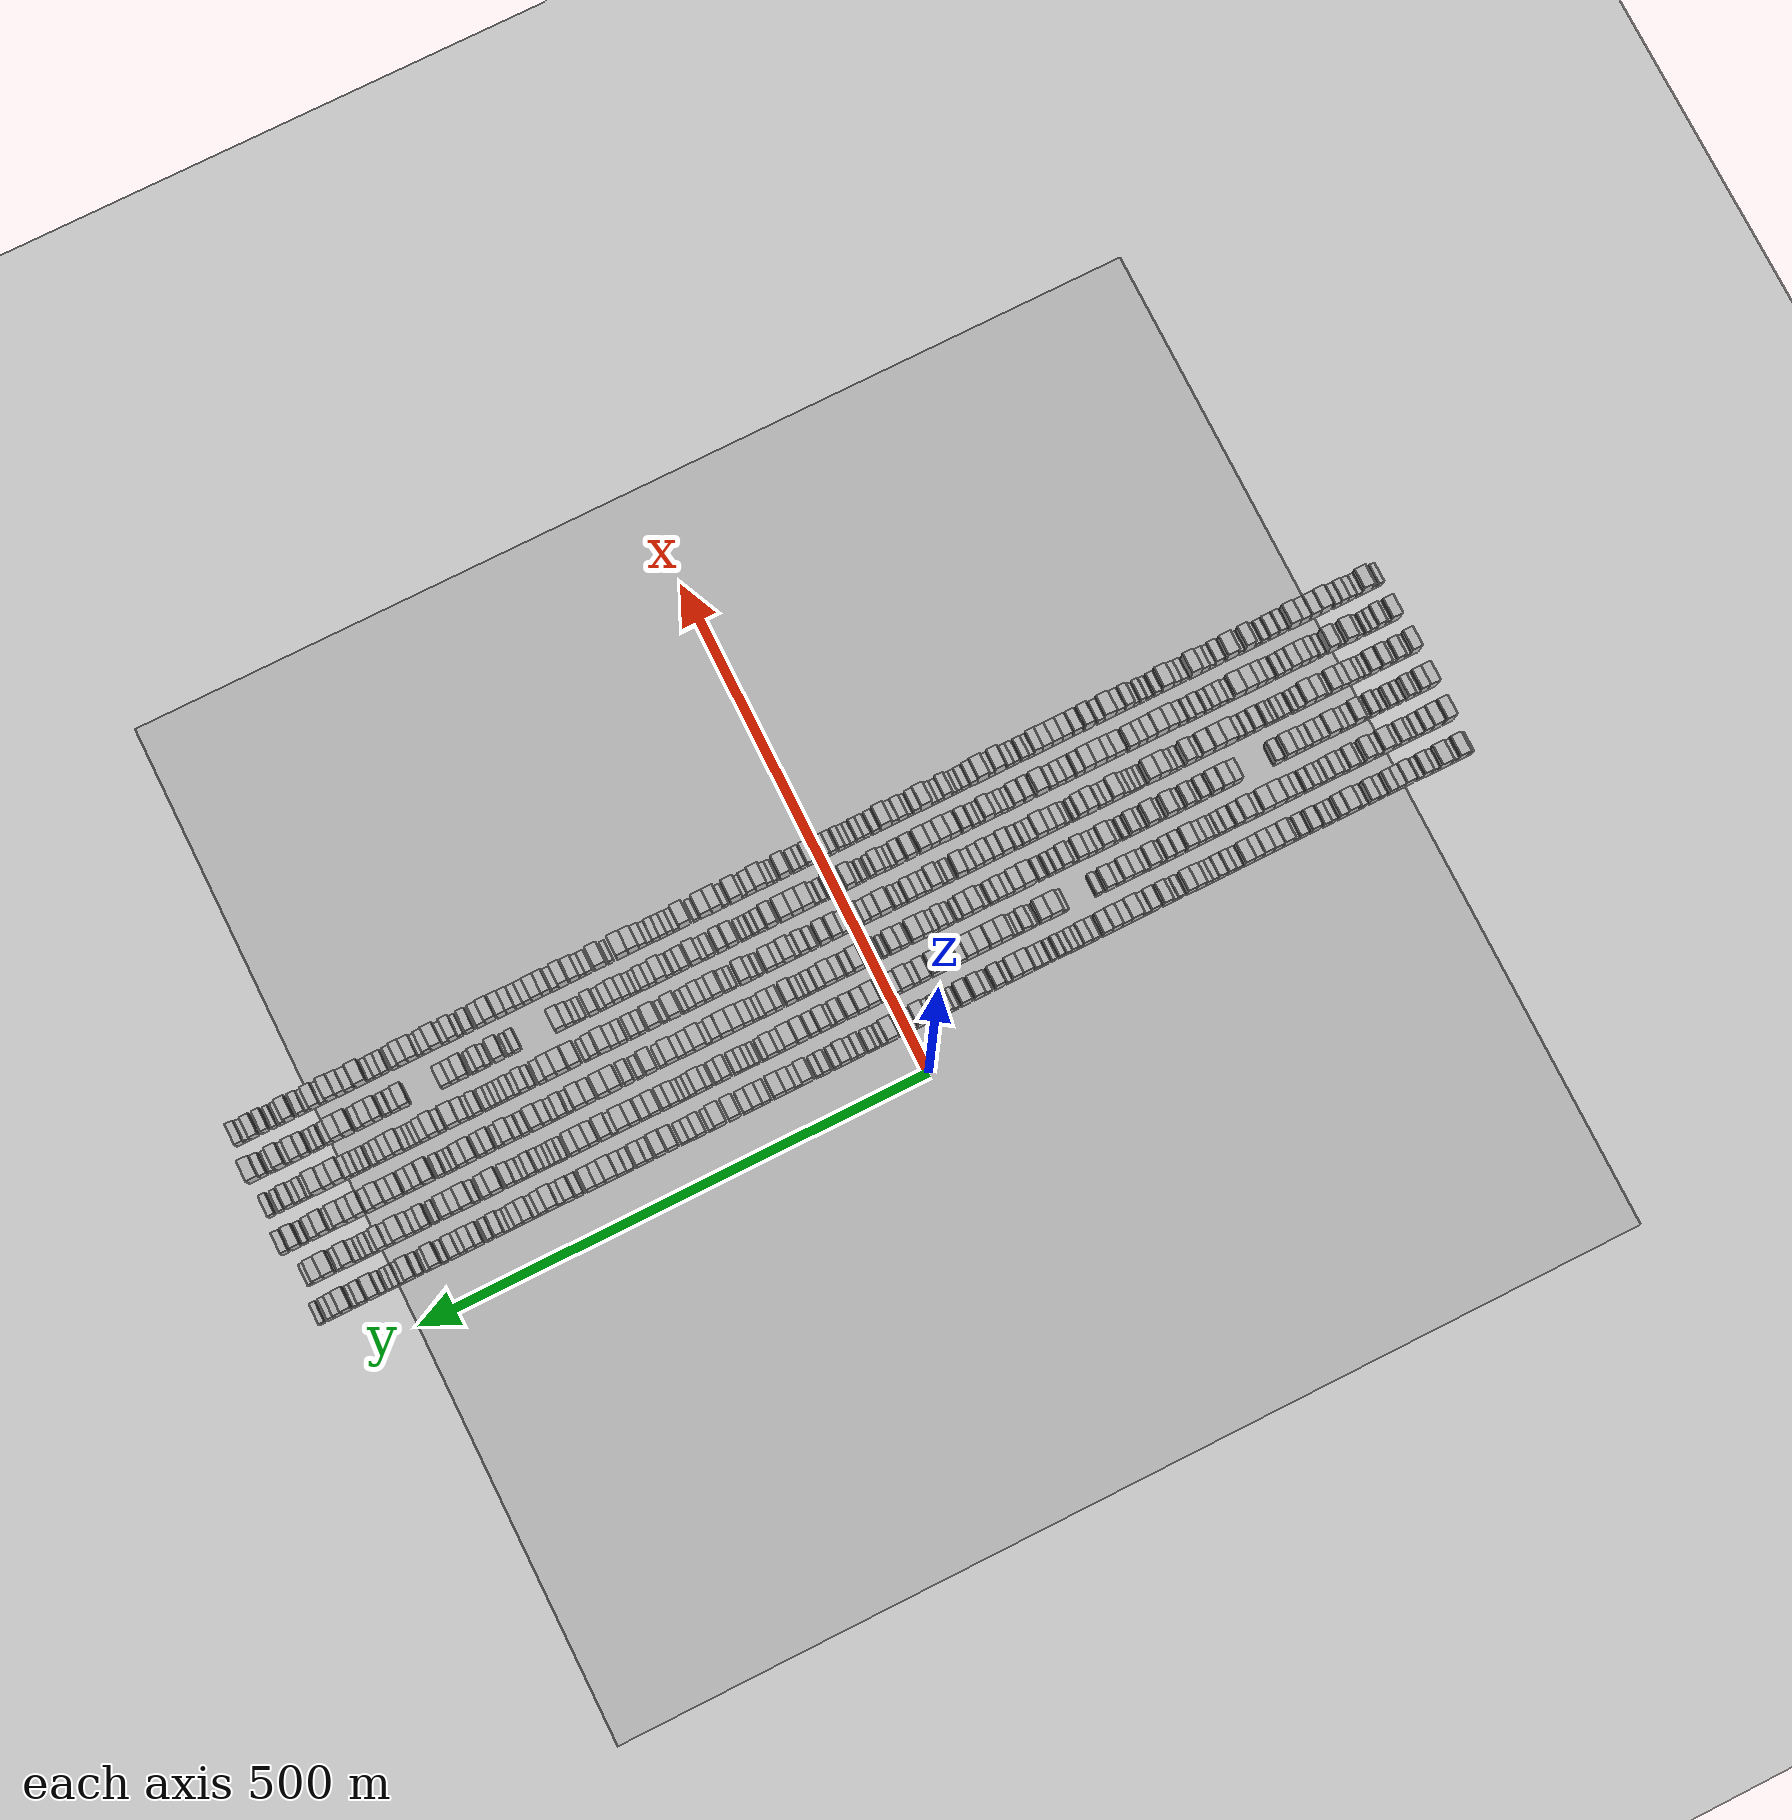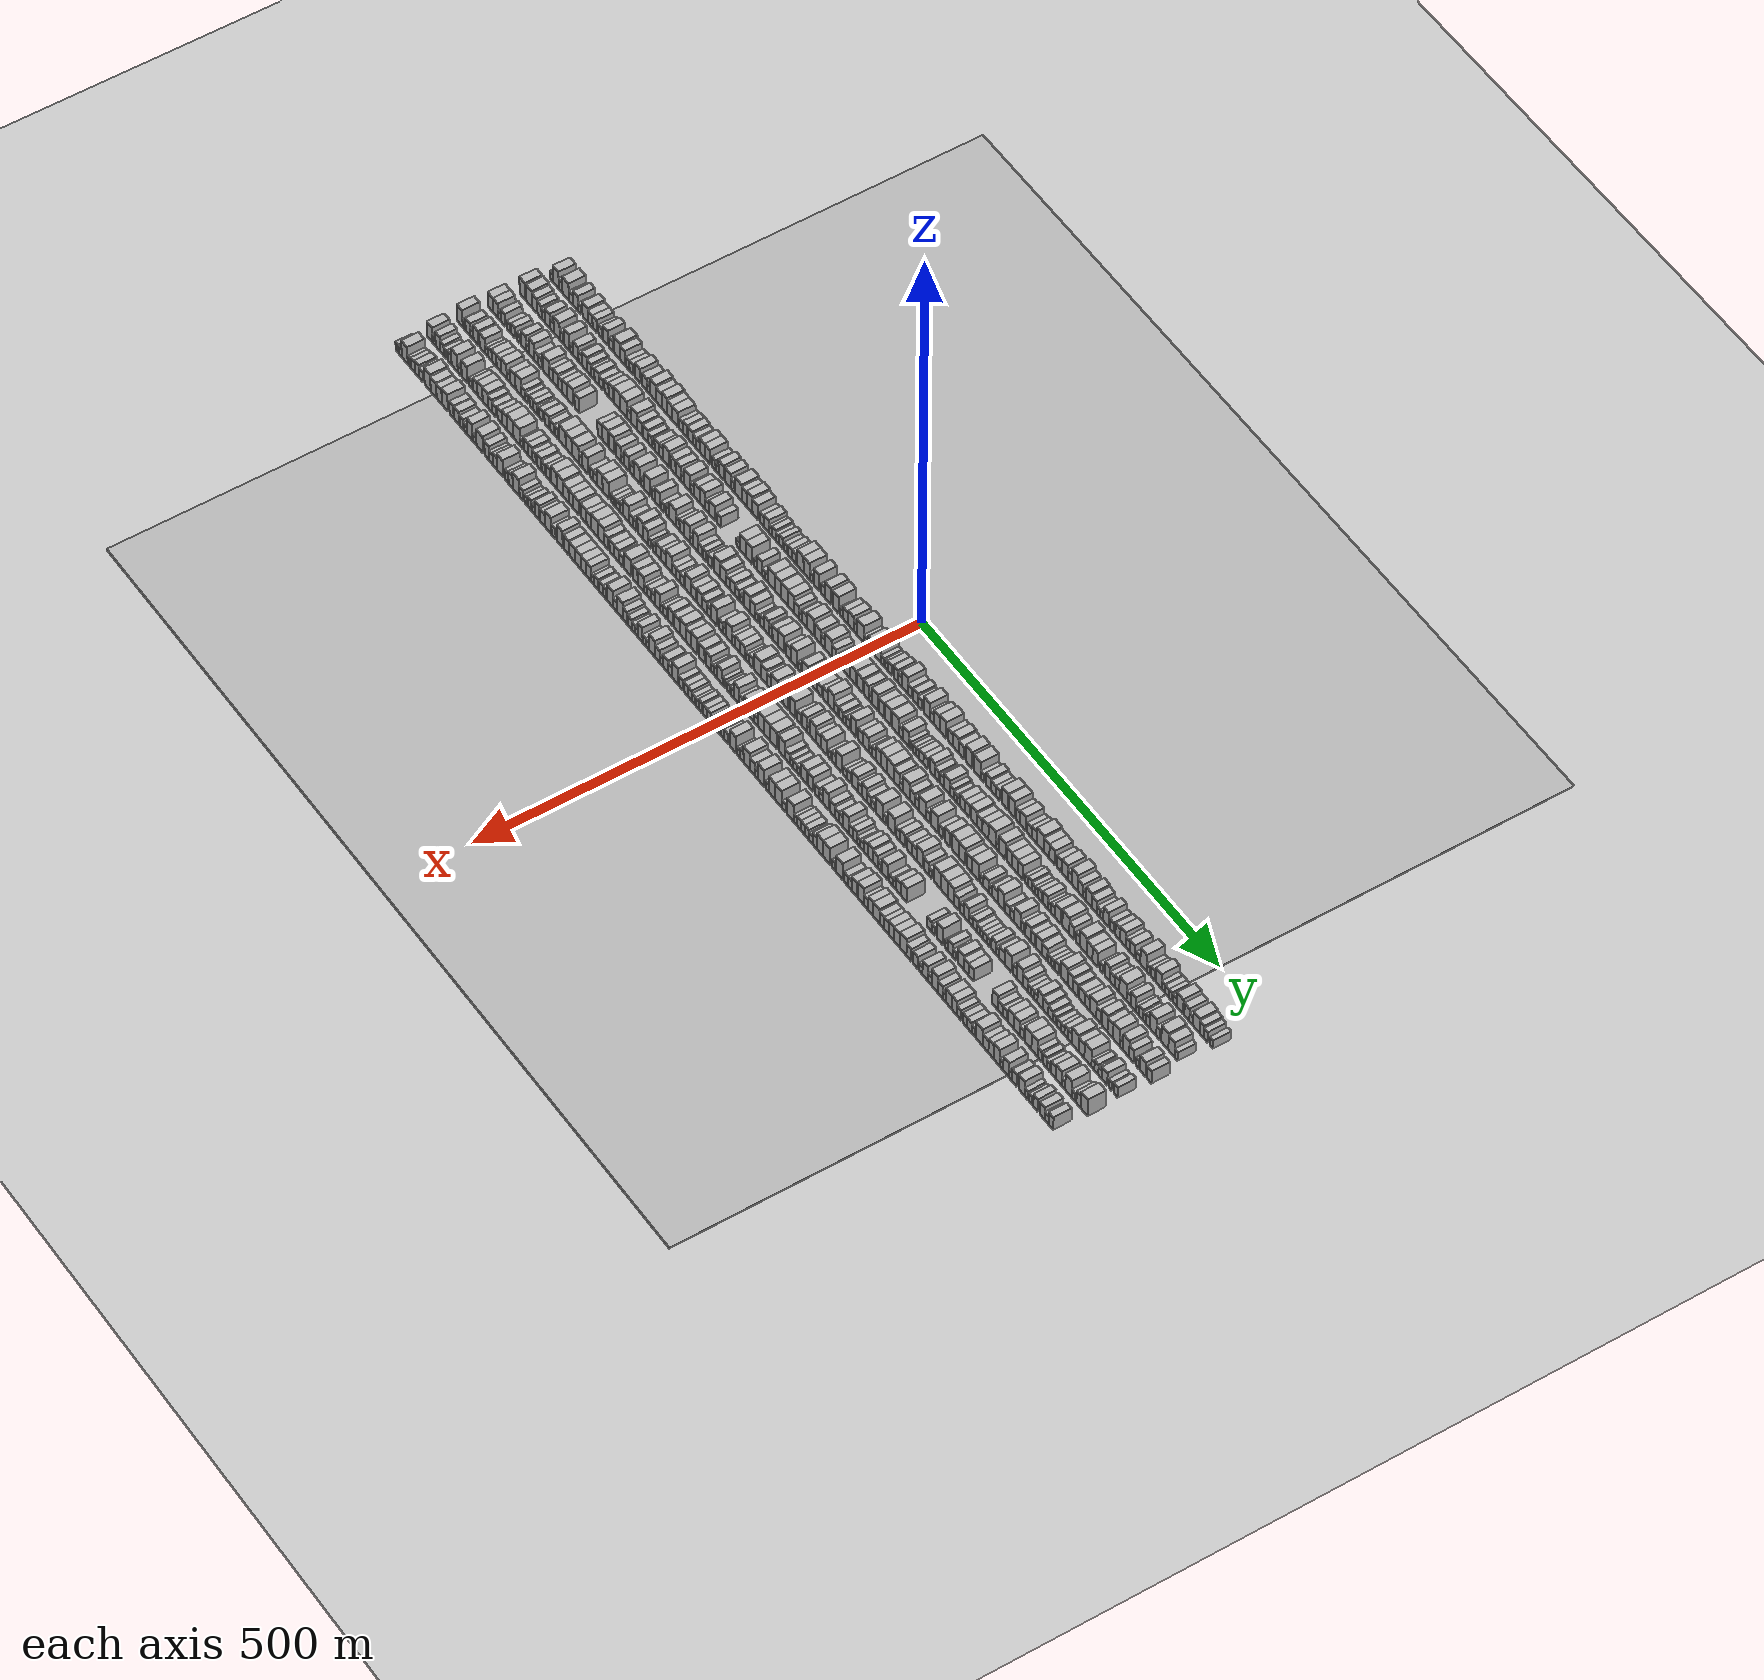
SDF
<?xml version="1.0" encoding="utf-8"?>

<sdf version="1.6">

   <world name="default">

      <gui fullscreen="0">

         <camera name="user_camera">

            <pose>-15 0 4.57585 0 0 0</pose>

            <view_controller>orbit</view_controller>

         </camera>

      </gui>

      <scene>

         <sky>

           <clouds>

             <speed>12</speed>

           </clouds>

         </sky>

         <ambient>0.4 0.4 0.4 1</ambient>

         <background>0.7 0.7 0.7 1</background>

         <shadows>1</shadows>

      </scene>

      <gravity>0 0 -9.8066</gravity>

      <magnetic_field>6e-06 2.3e-05 -4.2e-05</magnetic_field>

      <physics default="0" name="default_physics" type="ode">

         <ode>

            <solver>

               <type>quick</type>

               <iters>10</iters>

               <sor>1.0</sor>

               <use_dynamic_moi_rescaling>0</use_dynamic_moi_rescaling>

            </solver>

            <constraints>

               <cfm>0</cfm>

               <erp>0.2</erp>

               <contact_max_correcting_vel>100</contact_max_correcting_vel>

               <contact_surface_layer>0.001</contact_surface_layer>

            </constraints>

         </ode>

         <max_step_size>0.004</max_step_size>

         <real_time_factor>1</real_time_factor>

         <real_time_update_rate>250</real_time_update_rate>

      </physics>

      <light name="sun" type="directional">

         <cast_shadows>1</cast_shadows>

         <pose>0 0 10 0 0 0</pose>

         <diffuse>0.8 0.8 0.8 1</diffuse>

         <specular>0.2 0.2 0.2 1</specular>

         <attenuation>

            <range>1000</range>

            <constant>0.9</constant>

            <linear>0.01</linear>

            <quadratic>0.001</quadratic>

         </attenuation>

         <direction>-0.5 0.1 -0.9</direction>

      </light>

      <include>

         <name>ground_plane_1</name>

         <uri>model://HANNAS_ground_plane</uri>

         <pose>0 0 0  0 0 0</pose>

      </include>

      <include>

         <name>ground_plane_2</name>

         <uri>model://HANNAS_ground_plane</uri>

         <pose>100 0 0  0 0 0</pose>

      </include>

      <model name="building_1">

         <static>1</static>

         <pose frame="">50.0000 -565.4581 0 0.000000 0.000000 0.000000</pose>

         <link name="link">

            <pose frame="">0 0 6.00 0 0 0</pose>

            <collision name="collision">

               <geometry>

                  <box>

                     <size>20.0000 5.0838 12.0000</size>

                  </box>

               </geometry>

               <max_contacts>10</max_contacts>

               <surface>

                  <contact>

                     <ode/>

                  </contact>

                  <bounce/>

                  <friction>

                     <torsional>

                        <ode/>

                     </torsional>

                     <ode/>

                  </friction>

               </surface>

            </collision>

            <visual name="visual">

               <cast_shadows>0</cast_shadows>

               <geometry>

                  <box>

                     <size>20.0000 5.0838 12.0000</size>

                  </box>

               </geometry>

               <material>

                  <script>

                     <uri>model://HANNAS_wall/materials/scripts</uri>

                     <uri>model://HANNAS_wall/materials/textures</uri>

                     <name>vrc/HANNAS_wall</name>

                  </script>

               </material>

            </visual>

            <self_collide>0</self_collide>

            <enable_wind>0</enable_wind>

            <kinematic>0</kinematic>

         </link>

      </model>

      <model name="building_2">

         <static>1</static>

         <pose frame="">50.0000 -557.6715 0 0.000000 0.000000 0.000000</pose>

         <link name="link">

            <pose frame="">0 0 12.00 0 0 0</pose>

            <collision name="collision">

               <geometry>

                  <box>

                     <size>20.0000 10.4893 24.0000</size>

                  </box>

               </geometry>

               <max_contacts>10</max_contacts>

               <surface>

                  <contact>

                     <ode/>

                  </contact>

                  <bounce/>

                  <friction>

                     <torsional>

                        <ode/>

                     </torsional>

                     <ode/>

                  </friction>

               </surface>

            </collision>

            <visual name="visual">

               <cast_shadows>0</cast_shadows>

               <geometry>

                  <box>

                     <size>20.0000 10.4893 24.0000</size>

                  </box>

               </geometry>

               <material>

                  <script>

                     <uri>model://HANNAS_wall/materials/scripts</uri>

                     <uri>model://HANNAS_wall/materials/textures</uri>

                     <name>vrc/HANNAS_wall</name>

                  </script>

               </material>

            </visual>

            <self_collide>0</self_collide>

            <enable_wind>0</enable_wind>

            <kinematic>0</kinematic>

         </link>

      </model>

      <model name="building_3">

         <static>1</static>

         <pose frame="">50.0000 -549.0531 0 0.000000 0.000000 0.000000</pose>

         <link name="link">

            <pose frame="">0 0 7.50 0 0 0</pose>

            <collision name="collision">

               <geometry>

                  <box>

                     <size>20.0000 6.7475 15.0000</size>

                  </box>

               </geometry>

               <max_contacts>10</max_contacts>

               <surface>

                  <contact>

                     <ode/>

                  </contact>

                  <bounce/>

                  <friction>

                     <torsional>

                        <ode/>

                     </torsional>

                     <ode/>

                  </friction>

               </surface>

            </collision>

            <visual name="visual">

               <cast_shadows>0</cast_shadows>

               <geometry>

                  <box>

                     <size>20.0000 6.7475 15.0000</size>

                  </box>

               </geometry>

               <material>

                  <script>

                     <uri>model://HANNAS_wall/materials/scripts</uri>

                     <uri>model://HANNAS_wall/materials/textures</uri>

                     <name>vrc/HANNAS_wall</name>

                  </script>

               </material>

            </visual>

            <self_collide>0</self_collide>

            <enable_wind>0</enable_wind>

            <kinematic>0</kinematic>

         </link>

      </model>

      <model name="building_4">

         <static>1</static>

         <pose frame="">50.0000 -539.8728 0 0.000000 0.000000 0.000000</pose>

         <link name="link">

            <pose frame="">0 0 12.00 0 0 0</pose>

            <collision name="collision">

               <geometry>

                  <box>

                     <size>20.0000 11.6132 24.0000</size>

                  </box>

               </geometry>

               <max_contacts>10</max_contacts>

               <surface>

                  <contact>

                     <ode/>

                  </contact>

                  <bounce/>

                  <friction>

                     <torsional>

                        <ode/>

                     </torsional>

                     <ode/>

                  </friction>

               </surface>

            </collision>

            <visual name="visual">

               <cast_shadows>0</cast_shadows>

               <geometry>

                  <box>

                     <size>20.0000 11.6132 24.0000</size>

                  </box>

               </geometry>

               <material>

                  <script>

                     <uri>model://HANNAS_wall/materials/scripts</uri>

                     <uri>model://HANNAS_wall/materials/textures</uri>

                     <name>vrc/HANNAS_wall</name>

                  </script>

               </material>

            </visual>

            <self_collide>0</self_collide>

            <enable_wind>0</enable_wind>

            <kinematic>0</kinematic>

         </link>

      </model>

      <model name="building_5">

         <static>1</static>

         <pose frame="">50.0000 -529.5583 0 0.000000 0.000000 0.000000</pose>

         <link name="link">

            <pose frame="">0 0 7.50 0 0 0</pose>

            <collision name="collision">

               <geometry>

                  <box>

                     <size>20.0000 7.0158 15.0000</size>

                  </box>

               </geometry>

               <max_contacts>10</max_contacts>

               <surface>

                  <contact>

                     <ode/>

                  </contact>

                  <bounce/>

                  <friction>

                     <torsional>

                        <ode/>

                     </torsional>

                     <ode/>

                  </friction>

               </surface>

            </collision>

            <visual name="visual">

               <cast_shadows>0</cast_shadows>

               <geometry>

                  <box>

                     <size>20.0000 7.0158 15.0000</size>

                  </box>

               </geometry>

               <material>

                  <script>

                     <uri>model://HANNAS_wall/materials/scripts</uri>

                     <uri>model://HANNAS_wall/materials/textures</uri>

                     <name>vrc/HANNAS_wall</name>

                  </script>

               </material>

            </visual>

            <self_collide>0</self_collide>

            <enable_wind>0</enable_wind>

            <kinematic>0</kinematic>

         </link>

      </model>

      <model name="building_6">

         <static>1</static>

         <pose frame="">50.0000 -521.6646 0 0.000000 0.000000 0.000000</pose>

         <link name="link">

            <pose frame="">0 0 10.50 0 0 0</pose>

            <collision name="collision">

               <geometry>

                  <box>

                     <size>20.0000 8.7716 21.0000</size>

                  </box>

               </geometry>

               <max_contacts>10</max_contacts>

               <surface>

                  <contact>

                     <ode/>

                  </contact>

                  <bounce/>

                  <friction>

                     <torsional>

                        <ode/>

                     </torsional>

                     <ode/>

                  </friction>

               </surface>

            </collision>

            <visual name="visual">

               <cast_shadows>0</cast_shadows>

               <geometry>

                  <box>

                     <size>20.0000 8.7716 21.0000</size>

                  </box>

               </geometry>

               <material>

                  <script>

                     <uri>model://HANNAS_wall/materials/scripts</uri>

                     <uri>model://HANNAS_wall/materials/textures</uri>

                     <name>vrc/HANNAS_wall</name>

                  </script>

               </material>

            </visual>

            <self_collide>0</self_collide>

            <enable_wind>0</enable_wind>

            <kinematic>0</kinematic>

         </link>

      </model>

      <model name="building_7">

         <static>1</static>

         <pose frame="">50.0000 -514.6572 0 0.000000 0.000000 0.000000</pose>

         <link name="link">

            <pose frame="">0 0 6.00 0 0 0</pose>

            <collision name="collision">

               <geometry>

                  <box>

                     <size>20.0000 5.2432 12.0000</size>

                  </box>

               </geometry>

               <max_contacts>10</max_contacts>

               <surface>

                  <contact>

                     <ode/>

                  </contact>

                  <bounce/>

                  <friction>

                     <torsional>

                        <ode/>

                     </torsional>

                     <ode/>

                  </friction>

               </surface>

            </collision>

            <visual name="visual">

               <cast_shadows>0</cast_shadows>

               <geometry>

                  <box>

                     <size>20.0000 5.2432 12.0000</size>

                  </box>

               </geometry>

               <material>

                  <script>

                     <uri>model://HANNAS_wall/materials/scripts</uri>

                     <uri>model://HANNAS_wall/materials/textures</uri>

                     <name>vrc/HANNAS_wall</name>

                  </script>

               </material>

            </visual>

            <self_collide>0</self_collide>

            <enable_wind>0</enable_wind>

            <kinematic>0</kinematic>

         </link>

      </model>

      <model name="building_8">

         <static>1</static>

         <pose frame="">50.0000 -503.9667 0 0.000000 0.000000 0.000000</pose>

         <link name="link">

            <pose frame="">0 0 10.50 0 0 0</pose>

            <collision name="collision">

               <geometry>

                  <box>

                     <size>20.0000 10.1376 21.0000</size>

                  </box>

               </geometry>

               <max_contacts>10</max_contacts>

               <surface>

                  <contact>

                     <ode/>

                  </contact>

                  <bounce/>

                  <friction>

                     <torsional>

                        <ode/>

                     </torsional>

                     <ode/>

                  </friction>

               </surface>

            </collision>

            <visual name="visual">

               <cast_shadows>0</cast_shadows>

               <geometry>

                  <box>

                     <size>20.0000 10.1376 21.0000</size>

                  </box>

               </geometry>

               <material>

                  <script>

                     <uri>model://HANNAS_wall/materials/scripts</uri>

                     <uri>model://HANNAS_wall/materials/textures</uri>

                     <name>vrc/HANNAS_wall</name>

                  </script>

               </material>

            </visual>

            <self_collide>0</self_collide>

            <enable_wind>0</enable_wind>

            <kinematic>0</kinematic>

         </link>

      </model>

      <model name="building_9">

         <static>1</static>

         <pose frame="">50.0000 -494.7664 0 0.000000 0.000000 0.000000</pose>

         <link name="link">

            <pose frame="">0 0 9.00 0 0 0</pose>

            <collision name="collision">

               <geometry>

                  <box>

                     <size>20.0000 8.2630 18.0000</size>

                  </box>

               </geometry>

               <max_contacts>10</max_contacts>

               <surface>

                  <contact>

                     <ode/>

                  </contact>

                  <bounce/>

                  <friction>

                     <torsional>

                        <ode/>

                     </torsional>

                     <ode/>

                  </friction>

               </surface>

            </collision>

            <visual name="visual">

               <cast_shadows>0</cast_shadows>

               <geometry>

                  <box>

                     <size>20.0000 8.2630 18.0000</size>

                  </box>

               </geometry>

               <material>

                  <script>

                     <uri>model://HANNAS_wall/materials/scripts</uri>

                     <uri>model://HANNAS_wall/materials/textures</uri>

                     <name>vrc/HANNAS_wall</name>

                  </script>

               </material>

            </visual>

            <self_collide>0</self_collide>

            <enable_wind>0</enable_wind>

            <kinematic>0</kinematic>

         </link>

      </model>

      <model name="building_10">

         <static>1</static>

         <pose frame="">50.0000 -486.7391 0 0.000000 0.000000 0.000000</pose>

         <link name="link">

            <pose frame="">0 0 9.00 0 0 0</pose>

            <collision name="collision">

               <geometry>

                  <box>

                     <size>20.0000 7.7915 18.0000</size>

                  </box>

               </geometry>

               <max_contacts>10</max_contacts>

               <surface>

                  <contact>

                     <ode/>

                  </contact>

                  <bounce/>

                  <friction>

                     <torsional>

                        <ode/>

                     </torsional>

                     <ode/>

                  </friction>

               </surface>

            </collision>

            <visual name="visual">

               <cast_shadows>0</cast_shadows>

               <geometry>

                  <box>

                     <size>20.0000 7.7915 18.0000</size>

                  </box>

               </geometry>

               <material>

                  <script>

                     <uri>model://HANNAS_wall/materials/scripts</uri>

                     <uri>model://HANNAS_wall/materials/textures</uri>

                     <name>vrc/HANNAS_wall</name>

                  </script>

               </material>

            </visual>

            <self_collide>0</self_collide>

            <enable_wind>0</enable_wind>

            <kinematic>0</kinematic>

         </link>

      </model>

      <model name="building_11">

         <static>1</static>

         <pose frame="">50.0000 -476.2777 0 0.000000 0.000000 0.000000</pose>

         <link name="link">

            <pose frame="">0 0 7.50 0 0 0</pose>

            <collision name="collision">

               <geometry>

                  <box>

                     <size>20.0000 7.1315 15.0000</size>

                  </box>

               </geometry>

               <max_contacts>10</max_contacts>

               <surface>

                  <contact>

                     <ode/>

                  </contact>

                  <bounce/>

                  <friction>

                     <torsional>

                        <ode/>

                     </torsional>

                     <ode/>

                  </friction>

               </surface>

            </collision>

            <visual name="visual">

               <cast_shadows>0</cast_shadows>

               <geometry>

                  <box>

                     <size>20.0000 7.1315 15.0000</size>

                  </box>

               </geometry>

               <material>

                  <script>

                     <uri>model://HANNAS_wall/materials/scripts</uri>

                     <uri>model://HANNAS_wall/materials/textures</uri>

                     <name>vrc/HANNAS_wall</name>

                  </script>

               </material>

            </visual>

            <self_collide>0</self_collide>

            <enable_wind>0</enable_wind>

            <kinematic>0</kinematic>

         </link>

      </model>

      <model name="building_12">

         <static>1</static>

         <pose frame="">50.0000 -467.3228 0 0.000000 0.000000 0.000000</pose>

         <link name="link">

            <pose frame="">0 0 10.50 0 0 0</pose>

            <collision name="collision">

               <geometry>

                  <box>

                     <size>20.0000 8.7782 21.0000</size>

                  </box>

               </geometry>

               <max_contacts>10</max_contacts>

               <surface>

                  <contact>

                     <ode/>

                  </contact>

                  <bounce/>

                  <friction>

                     <torsional>

                        <ode/>

                     </torsional>

                     <ode/>

                  </friction>

               </surface>

            </collision>

            <visual name="visual">

               <cast_shadows>0</cast_shadows>

               <geometry>

                  <box>

                     <size>20.0000 8.7782 21.0000</size>

                  </box>

               </geometry>

               <material>

                  <script>

                     <uri>model://HANNAS_wall/materials/scripts</uri>

                     <uri>model://HANNAS_wall/materials/textures</uri>

                     <name>vrc/HANNAS_wall</name>

                  </script>

               </material>

            </visual>

            <self_collide>0</self_collide>

            <enable_wind>0</enable_wind>

            <kinematic>0</kinematic>

         </link>

      </model>

      <model name="building_13">

         <static>1</static>

         <pose frame="">50.0000 -456.5102 0 0.000000 0.000000 0.000000</pose>

         <link name="link">

            <pose frame="">0 0 7.50 0 0 0</pose>

            <collision name="collision">

               <geometry>

                  <box>

                     <size>20.0000 6.8471 15.0000</size>

                  </box>

               </geometry>

               <max_contacts>10</max_contacts>

               <surface>

                  <contact>

                     <ode/>

                  </contact>

                  <bounce/>

                  <friction>

                     <torsional>

                        <ode/>

                     </torsional>

                     <ode/>

                  </friction>

               </surface>

            </collision>

            <visual name="visual">

               <cast_shadows>0</cast_shadows>

               <geometry>

                  <box>

                     <size>20.0000 6.8471 15.0000</size>

                  </box>

               </geometry>

               <material>

                  <script>

                     <uri>model://HANNAS_wall/materials/scripts</uri>

                     <uri>model://HANNAS_wall/materials/textures</uri>

                     <name>vrc/HANNAS_wall</name>

                  </script>

               </material>

            </visual>

            <self_collide>0</self_collide>

            <enable_wind>0</enable_wind>

            <kinematic>0</kinematic>

         </link>

      </model>

      <model name="building_14">

         <static>1</static>

         <pose frame="">50.0000 -446.1822 0 0.000000 0.000000 0.000000</pose>

         <link name="link">

            <pose frame="">0 0 12.00 0 0 0</pose>

            <collision name="collision">

               <geometry>

                  <box>

                     <size>20.0000 11.8090 24.0000</size>

                  </box>

               </geometry>

               <max_contacts>10</max_contacts>

               <surface>

                  <contact>

                     <ode/>

                  </contact>

                  <bounce/>

                  <friction>

                     <torsional>

                        <ode/>

                     </torsional>

                     <ode/>

                  </friction>

               </surface>

            </collision>

            <visual name="visual">

               <cast_shadows>0</cast_shadows>

               <geometry>

                  <box>

                     <size>20.0000 11.8090 24.0000</size>

                  </box>

               </geometry>

               <material>

                  <script>

                     <uri>model://HANNAS_wall/materials/scripts</uri>

                     <uri>model://HANNAS_wall/materials/textures</uri>

                     <name>vrc/HANNAS_wall</name>

                  </script>

               </material>

            </visual>

            <self_collide>0</self_collide>

            <enable_wind>0</enable_wind>

            <kinematic>0</kinematic>

         </link>

      </model>

      <model name="building_15">

         <static>1</static>

         <pose frame="">50.0000 -435.9162 0 0.000000 0.000000 0.000000</pose>

         <link name="link">

            <pose frame="">0 0 10.50 0 0 0</pose>

            <collision name="collision">

               <geometry>

                  <box>

                     <size>20.0000 8.7229 21.0000</size>

                  </box>

               </geometry>

               <max_contacts>10</max_contacts>

               <surface>

                  <contact>

                     <ode/>

                  </contact>

                  <bounce/>

                  <friction>

                     <torsional>

                        <ode/>

                     </torsional>

                     <ode/>

                  </friction>

               </surface>

            </collision>

            <visual name="visual">

               <cast_shadows>0</cast_shadows>

               <geometry>

                  <box>

                     <size>20.0000 8.7229 21.0000</size>

                  </box>

               </geometry>

               <material>

                  <script>

                     <uri>model://HANNAS_wall/materials/scripts</uri>

                     <uri>model://HANNAS_wall/materials/textures</uri>

                     <name>vrc/HANNAS_wall</name>

                  </script>

               </material>

            </visual>

            <self_collide>0</self_collide>

            <enable_wind>0</enable_wind>

            <kinematic>0</kinematic>

         </link>

      </model>

      <model name="building_16">

         <static>1</static>

         <pose frame="">50.0000 -426.5537 0 0.000000 0.000000 0.000000</pose>

         <link name="link">

            <pose frame="">0 0 7.50 0 0 0</pose>

            <collision name="collision">

               <geometry>

                  <box>

                     <size>20.0000 6.0021 15.0000</size>

                  </box>

               </geometry>

               <max_contacts>10</max_contacts>

               <surface>

                  <contact>

                     <ode/>

                  </contact>

                  <bounce/>

                  <friction>

                     <torsional>

                        <ode/>

                     </torsional>

                     <ode/>

                  </friction>

               </surface>

            </collision>

            <visual name="visual">

               <cast_shadows>0</cast_shadows>

               <geometry>

                  <box>

                     <size>20.0000 6.0021 15.0000</size>

                  </box>

               </geometry>

               <material>

                  <script>

                     <uri>model://HANNAS_wall/materials/scripts</uri>

                     <uri>model://HANNAS_wall/materials/textures</uri>

                     <name>vrc/HANNAS_wall</name>

                  </script>

               </material>

            </visual>

            <self_collide>0</self_collide>

            <enable_wind>0</enable_wind>

            <kinematic>0</kinematic>

         </link>

      </model>

      <model name="building_17">

         <static>1</static>

         <pose frame="">50.0000 -420.0145 0 0.000000 0.000000 0.000000</pose>

         <link name="link">

            <pose frame="">0 0 7.50 0 0 0</pose>

            <collision name="collision">

               <geometry>

                  <box>

                     <size>20.0000 7.0762 15.0000</size>

                  </box>

               </geometry>

               <max_contacts>10</max_contacts>

               <surface>

                  <contact>

                     <ode/>

                  </contact>

                  <bounce/>

                  <friction>

                     <torsional>

                        <ode/>

                     </torsional>

                     <ode/>

                  </friction>

               </surface>

            </collision>

            <visual name="visual">

               <cast_shadows>0</cast_shadows>

               <geometry>

                  <box>

                     <size>20.0000 7.0762 15.0000</size>

                  </box>

               </geometry>

               <material>

                  <script>

                     <uri>model://HANNAS_wall/materials/scripts</uri>

                     <uri>model://HANNAS_wall/materials/textures</uri>

                     <name>vrc/HANNAS_wall</name>

                  </script>

               </material>

            </visual>

            <self_collide>0</self_collide>

            <enable_wind>0</enable_wind>

            <kinematic>0</kinematic>

         </link>

      </model>

      <model name="building_18">

         <static>1</static>

         <pose frame="">50.0000 -408.5056 0 0.000000 0.000000 0.000000</pose>

         <link name="link">

            <pose frame="">0 0 10.50 0 0 0</pose>

            <collision name="collision">

               <geometry>

                  <box>

                     <size>20.0000 9.9416 21.0000</size>

                  </box>

               </geometry>

               <max_contacts>10</max_contacts>

               <surface>

                  <contact>

                     <ode/>

                  </contact>

                  <bounce/>

                  <friction>

                     <torsional>

                        <ode/>

                     </torsional>

                     <ode/>

                  </friction>

               </surface>

            </collision>

            <visual name="visual">

               <cast_shadows>0</cast_shadows>

               <geometry>

                  <box>

                     <size>20.0000 9.9416 21.0000</size>

                  </box>

               </geometry>

               <material>

                  <script>

                     <uri>model://HANNAS_wall/materials/scripts</uri>

                     <uri>model://HANNAS_wall/materials/textures</uri>

                     <name>vrc/HANNAS_wall</name>

                  </script>

               </material>

            </visual>

            <self_collide>0</self_collide>

            <enable_wind>0</enable_wind>

            <kinematic>0</kinematic>

         </link>

      </model>

      <model name="building_19">

         <static>1</static>

         <pose frame="">50.0000 -396.1010 0 0.000000 0.000000 0.000000</pose>

         <link name="link">

            <pose frame="">0 0 9.00 0 0 0</pose>

            <collision name="collision">

               <geometry>

                  <box>

                     <size>20.0000 8.8676 18.0000</size>

                  </box>

               </geometry>

               <max_contacts>10</max_contacts>

               <surface>

                  <contact>

                     <ode/>

                  </contact>

                  <bounce/>

                  <friction>

                     <torsional>

                        <ode/>

                     </torsional>

                     <ode/>

                  </friction>

               </surface>

            </collision>

            <visual name="visual">

               <cast_shadows>0</cast_shadows>

               <geometry>

                  <box>

                     <size>20.0000 8.8676 18.0000</size>

                  </box>

               </geometry>

               <material>

                  <script>

                     <uri>model://HANNAS_wall/materials/scripts</uri>

                     <uri>model://HANNAS_wall/materials/textures</uri>

                     <name>vrc/HANNAS_wall</name>

                  </script>

               </material>

            </visual>

            <self_collide>0</self_collide>

            <enable_wind>0</enable_wind>

            <kinematic>0</kinematic>

         </link>

      </model>

      <model name="building_20">

         <static>1</static>

         <pose frame="">50.0000 -388.8554 0 0.000000 0.000000 0.000000</pose>

         <link name="link">

            <pose frame="">0 0 6.00 0 0 0</pose>

            <collision name="collision">

               <geometry>

                  <box>

                     <size>20.0000 5.6237 12.0000</size>

                  </box>

               </geometry>

               <max_contacts>10</max_contacts>

               <surface>

                  <contact>

                     <ode/>

                  </contact>

                  <bounce/>

                  <friction>

                     <torsional>

                        <ode/>

                     </torsional>

                     <ode/>

                  </friction>

               </surface>

            </collision>

            <visual name="visual">

               <cast_shadows>0</cast_shadows>

               <geometry>

                  <box>

                     <size>20.0000 5.6237 12.0000</size>

                  </box>

               </geometry>

               <material>

                  <script>

                     <uri>model://HANNAS_wall/materials/scripts</uri>

                     <uri>model://HANNAS_wall/materials/textures</uri>

                     <name>vrc/HANNAS_wall</name>

                  </script>

               </material>

            </visual>

            <self_collide>0</self_collide>

            <enable_wind>0</enable_wind>

            <kinematic>0</kinematic>

         </link>

      </model>

      <model name="building_21">

         <static>1</static>

         <pose frame="">50.0000 -380.7657 0 0.000000 0.000000 0.000000</pose>

         <link name="link">

            <pose frame="">0 0 12.00 0 0 0</pose>

            <collision name="collision">

               <geometry>

                  <box>

                     <size>20.0000 10.5557 24.0000</size>

                  </box>

               </geometry>

               <max_contacts>10</max_contacts>

               <surface>

                  <contact>

                     <ode/>

                  </contact>

                  <bounce/>

                  <friction>

                     <torsional>

                        <ode/>

                     </torsional>

                     <ode/>

                  </friction>

               </surface>

            </collision>

            <visual name="visual">

               <cast_shadows>0</cast_shadows>

               <geometry>

                  <box>

                     <size>20.0000 10.5557 24.0000</size>

                  </box>

               </geometry>

               <material>

                  <script>

                     <uri>model://HANNAS_wall/materials/scripts</uri>

                     <uri>model://HANNAS_wall/materials/textures</uri>

                     <name>vrc/HANNAS_wall</name>

                  </script>

               </material>

            </visual>

            <self_collide>0</self_collide>

            <enable_wind>0</enable_wind>

            <kinematic>0</kinematic>

         </link>

      </model>

      <model name="building_22">

         <static>1</static>

         <pose frame="">50.0000 -370.4100 0 0.000000 0.000000 0.000000</pose>

         <link name="link">

            <pose frame="">0 0 10.50 0 0 0</pose>

            <collision name="collision">

               <geometry>

                  <box>

                     <size>20.0000 10.1555 21.0000</size>

                  </box>

               </geometry>

               <max_contacts>10</max_contacts>

               <surface>

                  <contact>

                     <ode/>

                  </contact>

                  <bounce/>

                  <friction>

                     <torsional>

                        <ode/>

                     </torsional>

                     <ode/>

                  </friction>

               </surface>

            </collision>

            <visual name="visual">

               <cast_shadows>0</cast_shadows>

               <geometry>

                  <box>

                     <size>20.0000 10.1555 21.0000</size>

                  </box>

               </geometry>

               <material>

                  <script>

                     <uri>model://HANNAS_wall/materials/scripts</uri>

                     <uri>model://HANNAS_wall/materials/textures</uri>

                     <name>vrc/HANNAS_wall</name>

                  </script>

               </material>

            </visual>

            <self_collide>0</self_collide>

            <enable_wind>0</enable_wind>

            <kinematic>0</kinematic>

         </link>

      </model>

      <model name="building_23">

         <static>1</static>

         <pose frame="">50.0000 -360.2663 0 0.000000 0.000000 0.000000</pose>

         <link name="link">

            <pose frame="">0 0 12.00 0 0 0</pose>

            <collision name="collision">

               <geometry>

                  <box>

                     <size>20.0000 10.1320 24.0000</size>

                  </box>

               </geometry>

               <max_contacts>10</max_contacts>

               <surface>

                  <contact>

                     <ode/>

                  </contact>

                  <bounce/>

                  <friction>

                     <torsional>

                        <ode/>

                     </torsional>

                     <ode/>

                  </friction>

               </surface>

            </collision>

            <visual name="visual">

               <cast_shadows>0</cast_shadows>

               <geometry>

                  <box>

                     <size>20.0000 10.1320 24.0000</size>

                  </box>

               </geometry>

               <material>

                  <script>

                     <uri>model://HANNAS_wall/materials/scripts</uri>

                     <uri>model://HANNAS_wall/materials/textures</uri>

                     <name>vrc/HANNAS_wall</name>

                  </script>

               </material>

            </visual>

            <self_collide>0</self_collide>

            <enable_wind>0</enable_wind>

            <kinematic>0</kinematic>

         </link>

      </model>

      <model name="building_24">

         <static>1</static>

         <pose frame="">50.0000 -350.8530 0 0.000000 0.000000 0.000000</pose>

         <link name="link">

            <pose frame="">0 0 10.50 0 0 0</pose>

            <collision name="collision">

               <geometry>

                  <box>

                     <size>20.0000 8.6945 21.0000</size>

                  </box>

               </geometry>

               <max_contacts>10</max_contacts>

               <surface>

                  <contact>

                     <ode/>

                  </contact>

                  <bounce/>

                  <friction>

                     <torsional>

                        <ode/>

                     </torsional>

                     <ode/>

                  </friction>

               </surface>

            </collision>

            <visual name="visual">

               <cast_shadows>0</cast_shadows>

               <geometry>

                  <box>

                     <size>20.0000 8.6945 21.0000</size>

                  </box>

               </geometry>

               <material>

                  <script>

                     <uri>model://HANNAS_wall/materials/scripts</uri>

                     <uri>model://HANNAS_wall/materials/textures</uri>

                     <name>vrc/HANNAS_wall</name>

                  </script>

               </material>

            </visual>

            <self_collide>0</self_collide>

            <enable_wind>0</enable_wind>

            <kinematic>0</kinematic>

         </link>

      </model>

      <model name="building_25">

         <static>1</static>

         <pose frame="">50.0000 -341.2789 0 0.000000 0.000000 0.000000</pose>

         <link name="link">

            <pose frame="">0 0 10.50 0 0 0</pose>

            <collision name="collision">

               <geometry>

                  <box>

                     <size>20.0000 10.4537 21.0000</size>

                  </box>

               </geometry>

               <max_contacts>10</max_contacts>

               <surface>

                  <contact>

                     <ode/>

                  </contact>

                  <bounce/>

                  <friction>

                     <torsional>

                        <ode/>

                     </torsional>

                     <ode/>

                  </friction>

               </surface>

            </collision>

            <visual name="visual">

               <cast_shadows>0</cast_shadows>

               <geometry>

                  <box>

                     <size>20.0000 10.4537 21.0000</size>

                  </box>

               </geometry>

               <material>

                  <script>

                     <uri>model://HANNAS_wall/materials/scripts</uri>

                     <uri>model://HANNAS_wall/materials/textures</uri>

                     <name>vrc/HANNAS_wall</name>

                  </script>

               </material>

            </visual>

            <self_collide>0</self_collide>

            <enable_wind>0</enable_wind>

            <kinematic>0</kinematic>

         </link>

      </model>

      <model name="building_26">

         <static>1</static>

         <pose frame="">50.0000 -330.4566 0 0.000000 0.000000 0.000000</pose>

         <link name="link">

            <pose frame="">0 0 7.50 0 0 0</pose>

            <collision name="collision">

               <geometry>

                  <box>

                     <size>20.0000 7.1910 15.0000</size>

                  </box>

               </geometry>

               <max_contacts>10</max_contacts>

               <surface>

                  <contact>

                     <ode/>

                  </contact>

                  <bounce/>

                  <friction>

                     <torsional>

                        <ode/>

                     </torsional>

                     <ode/>

                  </friction>

               </surface>

            </collision>

            <visual name="visual">

               <cast_shadows>0</cast_shadows>

               <geometry>

                  <box>

                     <size>20.0000 7.1910 15.0000</size>

                  </box>

               </geometry>

               <material>

                  <script>

                     <uri>model://HANNAS_wall/materials/scripts</uri>

                     <uri>model://HANNAS_wall/materials/textures</uri>

                     <name>vrc/HANNAS_wall</name>

                  </script>

               </material>

            </visual>

            <self_collide>0</self_collide>

            <enable_wind>0</enable_wind>

            <kinematic>0</kinematic>

         </link>

      </model>

      <model name="building_27">

         <static>1</static>

         <pose frame="">50.0000 -323.1997 0 0.000000 0.000000 0.000000</pose>

         <link name="link">

            <pose frame="">0 0 9.00 0 0 0</pose>

            <collision name="collision">

               <geometry>

                  <box>

                     <size>20.0000 7.3229 18.0000</size>

                  </box>

               </geometry>

               <max_contacts>10</max_contacts>

               <surface>

                  <contact>

                     <ode/>

                  </contact>

                  <bounce/>

                  <friction>

                     <torsional>

                        <ode/>

                     </torsional>

                     <ode/>

                  </friction>

               </surface>

            </collision>

            <visual name="visual">

               <cast_shadows>0</cast_shadows>

               <geometry>

                  <box>

                     <size>20.0000 7.3229 18.0000</size>

                  </box>

               </geometry>

               <material>

                  <script>

                     <uri>model://HANNAS_wall/materials/scripts</uri>

                     <uri>model://HANNAS_wall/materials/textures</uri>

                     <name>vrc/HANNAS_wall</name>

                  </script>

               </material>

            </visual>

            <self_collide>0</self_collide>

            <enable_wind>0</enable_wind>

            <kinematic>0</kinematic>

         </link>

      </model>

      <model name="building_28">

         <static>1</static>

         <pose frame="">50.0000 -314.2013 0 0.000000 0.000000 0.000000</pose>

         <link name="link">

            <pose frame="">0 0 9.00 0 0 0</pose>

            <collision name="collision">

               <geometry>

                  <box>

                     <size>20.0000 8.6739 18.0000</size>

                  </box>

               </geometry>

               <max_contacts>10</max_contacts>

               <surface>

                  <contact>

                     <ode/>

                  </contact>

                  <bounce/>

                  <friction>

                     <torsional>

                        <ode/>

                     </torsional>

                     <ode/>

                  </friction>

               </surface>

            </collision>

            <visual name="visual">

               <cast_shadows>0</cast_shadows>

               <geometry>

                  <box>

                     <size>20.0000 8.6739 18.0000</size>

                  </box>

               </geometry>

               <material>

                  <script>

                     <uri>model://HANNAS_wall/materials/scripts</uri>

                     <uri>model://HANNAS_wall/materials/textures</uri>

                     <name>vrc/HANNAS_wall</name>

                  </script>

               </material>

            </visual>

            <self_collide>0</self_collide>

            <enable_wind>0</enable_wind>

            <kinematic>0</kinematic>

         </link>

      </model>

      <model name="building_29">

         <static>1</static>

         <pose frame="">50.0000 -306.7823 0 0.000000 0.000000 0.000000</pose>

         <link name="link">

            <pose frame="">0 0 7.50 0 0 0</pose>

            <collision name="collision">

               <geometry>

                  <box>

                     <size>20.0000 6.1640 15.0000</size>

                  </box>

               </geometry>

               <max_contacts>10</max_contacts>

               <surface>

                  <contact>

                     <ode/>

                  </contact>

                  <bounce/>

                  <friction>

                     <torsional>

                        <ode/>

                     </torsional>

                     <ode/>

                  </friction>

               </surface>

            </collision>

            <visual name="visual">

               <cast_shadows>0</cast_shadows>

               <geometry>

                  <box>

                     <size>20.0000 6.1640 15.0000</size>

                  </box>

               </geometry>

               <material>

                  <script>

                     <uri>model://HANNAS_wall/materials/scripts</uri>

                     <uri>model://HANNAS_wall/materials/textures</uri>

                     <name>vrc/HANNAS_wall</name>

                  </script>

               </material>

            </visual>

            <self_collide>0</self_collide>

            <enable_wind>0</enable_wind>

            <kinematic>0</kinematic>

         </link>

      </model>

      <model name="building_30">

         <static>1</static>

         <pose frame="">50.0000 -300.6237 0 0.000000 0.000000 0.000000</pose>

         <link name="link">

            <pose frame="">0 0 7.50 0 0 0</pose>

            <collision name="collision">

               <geometry>

                  <box>

                     <size>20.0000 6.1533 15.0000</size>

                  </box>

               </geometry>

               <max_contacts>10</max_contacts>

               <surface>

                  <contact>

                     <ode/>

                  </contact>

                  <bounce/>

                  <friction>

                     <torsional>

                        <ode/>

                     </torsional>

                     <ode/>

                  </friction>

               </surface>

            </collision>

            <visual name="visual">

               <cast_shadows>0</cast_shadows>

               <geometry>

                  <box>

                     <size>20.0000 6.1533 15.0000</size>

                  </box>

               </geometry>

               <material>

                  <script>

                     <uri>model://HANNAS_wall/materials/scripts</uri>

                     <uri>model://HANNAS_wall/materials/textures</uri>

                     <name>vrc/HANNAS_wall</name>

                  </script>

               </material>

            </visual>

            <self_collide>0</self_collide>

            <enable_wind>0</enable_wind>

            <kinematic>0</kinematic>

         </link>

      </model>

      <model name="building_31">

         <static>1</static>

         <pose frame="">50.0000 -292.9258 0 0.000000 0.000000 0.000000</pose>

         <link name="link">

            <pose frame="">0 0 10.50 0 0 0</pose>

            <collision name="collision">

               <geometry>

                  <box>

                     <size>20.0000 9.2425 21.0000</size>

                  </box>

               </geometry>

               <max_contacts>10</max_contacts>

               <surface>

                  <contact>

                     <ode/>

                  </contact>

                  <bounce/>

                  <friction>

                     <torsional>

                        <ode/>

                     </torsional>

                     <ode/>

                  </friction>

               </surface>

            </collision>

            <visual name="visual">

               <cast_shadows>0</cast_shadows>

               <geometry>

                  <box>

                     <size>20.0000 9.2425 21.0000</size>

                  </box>

               </geometry>

               <material>

                  <script>

                     <uri>model://HANNAS_wall/materials/scripts</uri>

                     <uri>model://HANNAS_wall/materials/textures</uri>

                     <name>vrc/HANNAS_wall</name>

                  </script>

               </material>

            </visual>

            <self_collide>0</self_collide>

            <enable_wind>0</enable_wind>

            <kinematic>0</kinematic>

         </link>

      </model>

      <model name="building_32">

         <static>1</static>

         <pose frame="">50.0000 -283.4557 0 0.000000 0.000000 0.000000</pose>

         <link name="link">

            <pose frame="">0 0 10.50 0 0 0</pose>

            <collision name="collision">

               <geometry>

                  <box>

                     <size>20.0000 9.6978 21.0000</size>

                  </box>

               </geometry>

               <max_contacts>10</max_contacts>

               <surface>

                  <contact>

                     <ode/>

                  </contact>

                  <bounce/>

                  <friction>

                     <torsional>

                        <ode/>

                     </torsional>

                     <ode/>

                  </friction>

               </surface>

            </collision>

            <visual name="visual">

               <cast_shadows>0</cast_shadows>

               <geometry>

                  <box>

                     <size>20.0000 9.6978 21.0000</size>

                  </box>

               </geometry>

               <material>

                  <script>

                     <uri>model://HANNAS_wall/materials/scripts</uri>

                     <uri>model://HANNAS_wall/materials/textures</uri>

                     <name>vrc/HANNAS_wall</name>

                  </script>

               </material>

            </visual>

            <self_collide>0</self_collide>

            <enable_wind>0</enable_wind>

            <kinematic>0</kinematic>

         </link>

      </model>

      <model name="building_33">

         <static>1</static>

         <pose frame="">50.0000 -272.3786 0 0.000000 0.000000 0.000000</pose>

         <link name="link">

            <pose frame="">0 0 7.50 0 0 0</pose>

            <collision name="collision">

               <geometry>

                  <box>

                     <size>20.0000 6.4563 15.0000</size>

                  </box>

               </geometry>

               <max_contacts>10</max_contacts>

               <surface>

                  <contact>

                     <ode/>

                  </contact>

                  <bounce/>

                  <friction>

                     <torsional>

                        <ode/>

                     </torsional>

                     <ode/>

                  </friction>

               </surface>

            </collision>

            <visual name="visual">

               <cast_shadows>0</cast_shadows>

               <geometry>

                  <box>

                     <size>20.0000 6.4563 15.0000</size>

                  </box>

               </geometry>

               <material>

                  <script>

                     <uri>model://HANNAS_wall/materials/scripts</uri>

                     <uri>model://HANNAS_wall/materials/textures</uri>

                     <name>vrc/HANNAS_wall</name>

                  </script>

               </material>

            </visual>

            <self_collide>0</self_collide>

            <enable_wind>0</enable_wind>

            <kinematic>0</kinematic>

         </link>

      </model>

      <model name="building_34">

         <static>1</static>

         <pose frame="">50.0000 -266.4508 0 0.000000 0.000000 0.000000</pose>

         <link name="link">

            <pose frame="">0 0 6.00 0 0 0</pose>

            <collision name="collision">

               <geometry>

                  <box>

                     <size>20.0000 5.3995 12.0000</size>

                  </box>

               </geometry>

               <max_contacts>10</max_contacts>

               <surface>

                  <contact>

                     <ode/>

                  </contact>

                  <bounce/>

                  <friction>

                     <torsional>

                        <ode/>

                     </torsional>

                     <ode/>

                  </friction>

               </surface>

            </collision>

            <visual name="visual">

               <cast_shadows>0</cast_shadows>

               <geometry>

                  <box>

                     <size>20.0000 5.3995 12.0000</size>

                  </box>

               </geometry>

               <material>

                  <script>

                     <uri>model://HANNAS_wall/materials/scripts</uri>

                     <uri>model://HANNAS_wall/materials/textures</uri>

                     <name>vrc/HANNAS_wall</name>

                  </script>

               </material>

            </visual>

            <self_collide>0</self_collide>

            <enable_wind>0</enable_wind>

            <kinematic>0</kinematic>

         </link>

      </model>

      <model name="building_35">

         <static>1</static>

         <pose frame="">50.0000 -259.1701 0 0.000000 0.000000 0.000000</pose>

         <link name="link">

            <pose frame="">0 0 10.50 0 0 0</pose>

            <collision name="collision">

               <geometry>

                  <box>

                     <size>20.0000 9.1619 21.0000</size>

                  </box>

               </geometry>

               <max_contacts>10</max_contacts>

               <surface>

                  <contact>

                     <ode/>

                  </contact>

                  <bounce/>

                  <friction>

                     <torsional>

                        <ode/>

                     </torsional>

                     <ode/>

                  </friction>

               </surface>

            </collision>

            <visual name="visual">

               <cast_shadows>0</cast_shadows>

               <geometry>

                  <box>

                     <size>20.0000 9.1619 21.0000</size>

                  </box>

               </geometry>

               <material>

                  <script>

                     <uri>model://HANNAS_wall/materials/scripts</uri>

                     <uri>model://HANNAS_wall/materials/textures</uri>

                     <name>vrc/HANNAS_wall</name>

                  </script>

               </material>

            </visual>

            <self_collide>0</self_collide>

            <enable_wind>0</enable_wind>

            <kinematic>0</kinematic>

         </link>

      </model>

      <model name="building_36">

         <static>1</static>

         <pose frame="">50.0000 -246.6851 0 0.000000 0.000000 0.000000</pose>

         <link name="link">

            <pose frame="">0 0 10.50 0 0 0</pose>

            <collision name="collision">

               <geometry>

                  <box>

                     <size>20.0000 9.8079 21.0000</size>

                  </box>

               </geometry>

               <max_contacts>10</max_contacts>

               <surface>

                  <contact>

                     <ode/>

                  </contact>

                  <bounce/>

                  <friction>

                     <torsional>

                        <ode/>

                     </torsional>

                     <ode/>

                  </friction>

               </surface>

            </collision>

            <visual name="visual">

               <cast_shadows>0</cast_shadows>

               <geometry>

                  <box>

                     <size>20.0000 9.8079 21.0000</size>

                  </box>

               </geometry>

               <material>

                  <script>

                     <uri>model://HANNAS_wall/materials/scripts</uri>

                     <uri>model://HANNAS_wall/materials/textures</uri>

                     <name>vrc/HANNAS_wall</name>

                  </script>

               </material>

            </visual>

            <self_collide>0</self_collide>

            <enable_wind>0</enable_wind>

            <kinematic>0</kinematic>

         </link>

      </model>

      <model name="building_37">

         <static>1</static>

         <pose frame="">50.0000 -238.6053 0 0.000000 0.000000 0.000000</pose>

         <link name="link">

            <pose frame="">0 0 7.50 0 0 0</pose>

            <collision name="collision">

               <geometry>

                  <box>

                     <size>20.0000 6.3517 15.0000</size>

                  </box>

               </geometry>

               <max_contacts>10</max_contacts>

               <surface>

                  <contact>

                     <ode/>

                  </contact>

                  <bounce/>

                  <friction>

                     <torsional>

                        <ode/>

                     </torsional>

                     <ode/>

                  </friction>

               </surface>

            </collision>

            <visual name="visual">

               <cast_shadows>0</cast_shadows>

               <geometry>

                  <box>

                     <size>20.0000 6.3517 15.0000</size>

                  </box>

               </geometry>

               <material>

                  <script>

                     <uri>model://HANNAS_wall/materials/scripts</uri>

                     <uri>model://HANNAS_wall/materials/textures</uri>

                     <name>vrc/HANNAS_wall</name>

                  </script>

               </material>

            </visual>

            <self_collide>0</self_collide>

            <enable_wind>0</enable_wind>

            <kinematic>0</kinematic>

         </link>

      </model>

      <model name="building_38">

         <static>1</static>

         <pose frame="">50.0000 -228.4566 0 0.000000 0.000000 0.000000</pose>

         <link name="link">

            <pose frame="">0 0 12.00 0 0 0</pose>

            <collision name="collision">

               <geometry>

                  <box>

                     <size>20.0000 11.9458 24.0000</size>

                  </box>

               </geometry>

               <max_contacts>10</max_contacts>

               <surface>

                  <contact>

                     <ode/>

                  </contact>

                  <bounce/>

                  <friction>

                     <torsional>

                        <ode/>

                     </torsional>

                     <ode/>

                  </friction>

               </surface>

            </collision>

            <visual name="visual">

               <cast_shadows>0</cast_shadows>

               <geometry>

                  <box>

                     <size>20.0000 11.9458 24.0000</size>

                  </box>

               </geometry>

               <material>

                  <script>

                     <uri>model://HANNAS_wall/materials/scripts</uri>

                     <uri>model://HANNAS_wall/materials/textures</uri>

                     <name>vrc/HANNAS_wall</name>

                  </script>

               </material>

            </visual>

            <self_collide>0</self_collide>

            <enable_wind>0</enable_wind>

            <kinematic>0</kinematic>

         </link>

      </model>

      <model name="building_39">

         <static>1</static>

         <pose frame="">50.0000 -217.9186 0 0.000000 0.000000 0.000000</pose>

         <link name="link">

            <pose frame="">0 0 10.50 0 0 0</pose>

            <collision name="collision">

               <geometry>

                  <box>

                     <size>20.0000 9.1301 21.0000</size>

                  </box>

               </geometry>

               <max_contacts>10</max_contacts>

               <surface>

                  <contact>

                     <ode/>

                  </contact>

                  <bounce/>

                  <friction>

                     <torsional>

                        <ode/>

                     </torsional>

                     <ode/>

                  </friction>

               </surface>

            </collision>

            <visual name="visual">

               <cast_shadows>0</cast_shadows>

               <geometry>

                  <box>

                     <size>20.0000 9.1301 21.0000</size>

                  </box>

               </geometry>

               <material>

                  <script>

                     <uri>model://HANNAS_wall/materials/scripts</uri>

                     <uri>model://HANNAS_wall/materials/textures</uri>

                     <name>vrc/HANNAS_wall</name>

                  </script>

               </material>

            </visual>

            <self_collide>0</self_collide>

            <enable_wind>0</enable_wind>

            <kinematic>0</kinematic>

         </link>

      </model>

      <model name="building_40">

         <static>1</static>

         <pose frame="">50.0000 -208.4874 0 0.000000 0.000000 0.000000</pose>

         <link name="link">

            <pose frame="">0 0 12.00 0 0 0</pose>

            <collision name="collision">

               <geometry>

                  <box>

                     <size>20.0000 9.7323 24.0000</size>

                  </box>

               </geometry>

               <max_contacts>10</max_contacts>

               <surface>

                  <contact>

                     <ode/>

                  </contact>

                  <bounce/>

                  <friction>

                     <torsional>

                        <ode/>

                     </torsional>

                     <ode/>

                  </friction>

               </surface>

            </collision>

            <visual name="visual">

               <cast_shadows>0</cast_shadows>

               <geometry>

                  <box>

                     <size>20.0000 9.7323 24.0000</size>

                  </box>

               </geometry>

               <material>

                  <script>

                     <uri>model://HANNAS_wall/materials/scripts</uri>

                     <uri>model://HANNAS_wall/materials/textures</uri>

                     <name>vrc/HANNAS_wall</name>

                  </script>

               </material>

            </visual>

            <self_collide>0</self_collide>

            <enable_wind>0</enable_wind>

            <kinematic>0</kinematic>

         </link>

      </model>

      <model name="building_41">

         <static>1</static>

         <pose frame="">50.0000 -198.7109 0 0.000000 0.000000 0.000000</pose>

         <link name="link">

            <pose frame="">0 0 10.50 0 0 0</pose>

            <collision name="collision">

               <geometry>

                  <box>

                     <size>20.0000 9.8207 21.0000</size>

                  </box>

               </geometry>

               <max_contacts>10</max_contacts>

               <surface>

                  <contact>

                     <ode/>

                  </contact>

                  <bounce/>

                  <friction>

                     <torsional>

                        <ode/>

                     </torsional>

                     <ode/>

                  </friction>

               </surface>

            </collision>

            <visual name="visual">

               <cast_shadows>0</cast_shadows>

               <geometry>

                  <box>

                     <size>20.0000 9.8207 21.0000</size>

                  </box>

               </geometry>

               <material>

                  <script>

                     <uri>model://HANNAS_wall/materials/scripts</uri>

                     <uri>model://HANNAS_wall/materials/textures</uri>

                     <name>vrc/HANNAS_wall</name>

                  </script>

               </material>

            </visual>

            <self_collide>0</self_collide>

            <enable_wind>0</enable_wind>

            <kinematic>0</kinematic>

         </link>

      </model>

      <model name="building_42">

         <static>1</static>

         <pose frame="">50.0000 -187.0634 0 0.000000 0.000000 0.000000</pose>

         <link name="link">

            <pose frame="">0 0 7.50 0 0 0</pose>

            <collision name="collision">

               <geometry>

                  <box>

                     <size>20.0000 7.4744 15.0000</size>

                  </box>

               </geometry>

               <max_contacts>10</max_contacts>

               <surface>

                  <contact>

                     <ode/>

                  </contact>

                  <bounce/>

                  <friction>

                     <torsional>

                        <ode/>

                     </torsional>

                     <ode/>

                  </friction>

               </surface>

            </collision>

            <visual name="visual">

               <cast_shadows>0</cast_shadows>

               <geometry>

                  <box>

                     <size>20.0000 7.4744 15.0000</size>

                  </box>

               </geometry>

               <material>

                  <script>

                     <uri>model://HANNAS_wall/materials/scripts</uri>

                     <uri>model://HANNAS_wall/materials/textures</uri>

                     <name>vrc/HANNAS_wall</name>

                  </script>

               </material>

            </visual>

            <self_collide>0</self_collide>

            <enable_wind>0</enable_wind>

            <kinematic>0</kinematic>

         </link>

      </model>

      <model name="building_43">

         <static>1</static>

         <pose frame="">50.0000 -178.9707 0 0.000000 0.000000 0.000000</pose>

         <link name="link">

            <pose frame="">0 0 9.00 0 0 0</pose>

            <collision name="collision">

               <geometry>

                  <box>

                     <size>20.0000 8.7109 18.0000</size>

                  </box>

               </geometry>

               <max_contacts>10</max_contacts>

               <surface>

                  <contact>

                     <ode/>

                  </contact>

                  <bounce/>

                  <friction>

                     <torsional>

                        <ode/>

                     </torsional>

                     <ode/>

                  </friction>

               </surface>

            </collision>

            <visual name="visual">

               <cast_shadows>0</cast_shadows>

               <geometry>

                  <box>

                     <size>20.0000 8.7109 18.0000</size>

                  </box>

               </geometry>

               <material>

                  <script>

                     <uri>model://HANNAS_wall/materials/scripts</uri>

                     <uri>model://HANNAS_wall/materials/textures</uri>

                     <name>vrc/HANNAS_wall</name>

                  </script>

               </material>

            </visual>

            <self_collide>0</self_collide>

            <enable_wind>0</enable_wind>

            <kinematic>0</kinematic>

         </link>

      </model>

      <model name="building_44">

         <static>1</static>

         <pose frame="">50.0000 -171.9413 0 0.000000 0.000000 0.000000</pose>

         <link name="link">

            <pose frame="">0 0 6.00 0 0 0</pose>

            <collision name="collision">

               <geometry>

                  <box>

                     <size>20.0000 5.3480 12.0000</size>

                  </box>

               </geometry>

               <max_contacts>10</max_contacts>

               <surface>

                  <contact>

                     <ode/>

                  </contact>

                  <bounce/>

                  <friction>

                     <torsional>

                        <ode/>

                     </torsional>

                     <ode/>

                  </friction>

               </surface>

            </collision>

            <visual name="visual">

               <cast_shadows>0</cast_shadows>

               <geometry>

                  <box>

                     <size>20.0000 5.3480 12.0000</size>

                  </box>

               </geometry>

               <material>

                  <script>

                     <uri>model://HANNAS_wall/materials/scripts</uri>

                     <uri>model://HANNAS_wall/materials/textures</uri>

                     <name>vrc/HANNAS_wall</name>

                  </script>

               </material>

            </visual>

            <self_collide>0</self_collide>

            <enable_wind>0</enable_wind>

            <kinematic>0</kinematic>

         </link>

      </model>

      <model name="building_45">

         <static>1</static>

         <pose frame="">50.0000 -166.0851 0 0.000000 0.000000 0.000000</pose>

         <link name="link">

            <pose frame="">0 0 7.50 0 0 0</pose>

            <collision name="collision">

               <geometry>

                  <box>

                     <size>20.0000 6.3643 15.0000</size>

                  </box>

               </geometry>

               <max_contacts>10</max_contacts>

               <surface>

                  <contact>

                     <ode/>

                  </contact>

                  <bounce/>

                  <friction>

                     <torsional>

                        <ode/>

                     </torsional>

                     <ode/>

                  </friction>

               </surface>

            </collision>

            <visual name="visual">

               <cast_shadows>0</cast_shadows>

               <geometry>

                  <box>

                     <size>20.0000 6.3643 15.0000</size>

                  </box>

               </geometry>

               <material>

                  <script>

                     <uri>model://HANNAS_wall/materials/scripts</uri>

                     <uri>model://HANNAS_wall/materials/textures</uri>

                     <name>vrc/HANNAS_wall</name>

                  </script>

               </material>

            </visual>

            <self_collide>0</self_collide>

            <enable_wind>0</enable_wind>

            <kinematic>0</kinematic>

         </link>

      </model>

      <model name="building_46">

         <static>1</static>

         <pose frame="">50.0000 -160.0724 0 0.000000 0.000000 0.000000</pose>

         <link name="link">

            <pose frame="">0 0 6.00 0 0 0</pose>

            <collision name="collision">

               <geometry>

                  <box>

                     <size>20.0000 5.6612 12.0000</size>

                  </box>

               </geometry>

               <max_contacts>10</max_contacts>

               <surface>

                  <contact>

                     <ode/>

                  </contact>

                  <bounce/>

                  <friction>

                     <torsional>

                        <ode/>

                     </torsional>

                     <ode/>

                  </friction>

               </surface>

            </collision>

            <visual name="visual">

               <cast_shadows>0</cast_shadows>

               <geometry>

                  <box>

                     <size>20.0000 5.6612 12.0000</size>

                  </box>

               </geometry>

               <material>

                  <script>

                     <uri>model://HANNAS_wall/materials/scripts</uri>

                     <uri>model://HANNAS_wall/materials/textures</uri>

                     <name>vrc/HANNAS_wall</name>

                  </script>

               </material>

            </visual>

            <self_collide>0</self_collide>

            <enable_wind>0</enable_wind>

            <kinematic>0</kinematic>

         </link>

      </model>

      <model name="building_47">

         <static>1</static>

         <pose frame="">50.0000 -153.0864 0 0.000000 0.000000 0.000000</pose>

         <link name="link">

            <pose frame="">0 0 7.50 0 0 0</pose>

            <collision name="collision">

               <geometry>

                  <box>

                     <size>20.0000 6.3107 15.0000</size>

                  </box>

               </geometry>

               <max_contacts>10</max_contacts>

               <surface>

                  <contact>

                     <ode/>

                  </contact>

                  <bounce/>

                  <friction>

                     <torsional>

                        <ode/>

                     </torsional>

                     <ode/>

                  </friction>

               </surface>

            </collision>

            <visual name="visual">

               <cast_shadows>0</cast_shadows>

               <geometry>

                  <box>

                     <size>20.0000 6.3107 15.0000</size>

                  </box>

               </geometry>

               <material>

                  <script>

                     <uri>model://HANNAS_wall/materials/scripts</uri>

                     <uri>model://HANNAS_wall/materials/textures</uri>

                     <name>vrc/HANNAS_wall</name>

                  </script>

               </material>

            </visual>

            <self_collide>0</self_collide>

            <enable_wind>0</enable_wind>

            <kinematic>0</kinematic>

         </link>

      </model>

      <model name="building_48">

         <static>1</static>

         <pose frame="">50.0000 -145.3106 0 0.000000 0.000000 0.000000</pose>

         <link name="link">

            <pose frame="">0 0 6.00 0 0 0</pose>

            <collision name="collision">

               <geometry>

                  <box>

                     <size>20.0000 5.2409 12.0000</size>

                  </box>

               </geometry>

               <max_contacts>10</max_contacts>

               <surface>

                  <contact>

                     <ode/>

                  </contact>

                  <bounce/>

                  <friction>

                     <torsional>

                        <ode/>

                     </torsional>

                     <ode/>

                  </friction>

               </surface>

            </collision>

            <visual name="visual">

               <cast_shadows>0</cast_shadows>

               <geometry>

                  <box>

                     <size>20.0000 5.2409 12.0000</size>

                  </box>

               </geometry>

               <material>

                  <script>

                     <uri>model://HANNAS_wall/materials/scripts</uri>

                     <uri>model://HANNAS_wall/materials/textures</uri>

                     <name>vrc/HANNAS_wall</name>

                  </script>

               </material>

            </visual>

            <self_collide>0</self_collide>

            <enable_wind>0</enable_wind>

            <kinematic>0</kinematic>

         </link>

      </model>

      <model name="building_49">

         <static>1</static>

         <pose frame="">50.0000 -137.1709 0 0.000000 0.000000 0.000000</pose>

         <link name="link">

            <pose frame="">0 0 7.50 0 0 0</pose>

            <collision name="collision">

               <geometry>

                  <box>

                     <size>20.0000 7.0384 15.0000</size>

                  </box>

               </geometry>

               <max_contacts>10</max_contacts>

               <surface>

                  <contact>

                     <ode/>

                  </contact>

                  <bounce/>

                  <friction>

                     <torsional>

                        <ode/>

                     </torsional>

                     <ode/>

                  </friction>

               </surface>

            </collision>

            <visual name="visual">

               <cast_shadows>0</cast_shadows>

               <geometry>

                  <box>

                     <size>20.0000 7.0384 15.0000</size>

                  </box>

               </geometry>

               <material>

                  <script>

                     <uri>model://HANNAS_wall/materials/scripts</uri>

                     <uri>model://HANNAS_wall/materials/textures</uri>

                     <name>vrc/HANNAS_wall</name>

                  </script>

               </material>

            </visual>

            <self_collide>0</self_collide>

            <enable_wind>0</enable_wind>

            <kinematic>0</kinematic>

         </link>

      </model>

      <model name="building_50">

         <static>1</static>

         <pose frame="">50.0000 -130.0520 0 0.000000 0.000000 0.000000</pose>

         <link name="link">

            <pose frame="">0 0 7.50 0 0 0</pose>

            <collision name="collision">

               <geometry>

                  <box>

                     <size>20.0000 7.1993 15.0000</size>

                  </box>

               </geometry>

               <max_contacts>10</max_contacts>

               <surface>

                  <contact>

                     <ode/>

                  </contact>

                  <bounce/>

                  <friction>

                     <torsional>

                        <ode/>

                     </torsional>

                     <ode/>

                  </friction>

               </surface>

            </collision>

            <visual name="visual">

               <cast_shadows>0</cast_shadows>

               <geometry>

                  <box>

                     <size>20.0000 7.1993 15.0000</size>

                  </box>

               </geometry>

               <material>

                  <script>

                     <uri>model://HANNAS_wall/materials/scripts</uri>

                     <uri>model://HANNAS_wall/materials/textures</uri>

                     <name>vrc/HANNAS_wall</name>

                  </script>

               </material>

            </visual>

            <self_collide>0</self_collide>

            <enable_wind>0</enable_wind>

            <kinematic>0</kinematic>

         </link>

      </model>

      <model name="building_51">

         <static>1</static>

         <pose frame="">50.0000 -119.1671 0 0.000000 0.000000 0.000000</pose>

         <link name="link">

            <pose frame="">0 0 12.00 0 0 0</pose>

            <collision name="collision">

               <geometry>

                  <box>

                     <size>20.0000 10.5705 24.0000</size>

                  </box>

               </geometry>

               <max_contacts>10</max_contacts>

               <surface>

                  <contact>

                     <ode/>

                  </contact>

                  <bounce/>

                  <friction>

                     <torsional>

                        <ode/>

                     </torsional>

                     <ode/>

                  </friction>

               </surface>

            </collision>

            <visual name="visual">

               <cast_shadows>0</cast_shadows>

               <geometry>

                  <box>

                     <size>20.0000 10.5705 24.0000</size>

                  </box>

               </geometry>

               <material>

                  <script>

                     <uri>model://HANNAS_wall/materials/scripts</uri>

                     <uri>model://HANNAS_wall/materials/textures</uri>

                     <name>vrc/HANNAS_wall</name>

                  </script>

               </material>

            </visual>

            <self_collide>0</self_collide>

            <enable_wind>0</enable_wind>

            <kinematic>0</kinematic>

         </link>

      </model>

      <model name="building_52">

         <static>1</static>

         <pose frame="">50.0000 -108.5441 0 0.000000 0.000000 0.000000</pose>

         <link name="link">

            <pose frame="">0 0 12.00 0 0 0</pose>

            <collision name="collision">

               <geometry>

                  <box>

                     <size>20.0000 10.6756 24.0000</size>

                  </box>

               </geometry>

               <max_contacts>10</max_contacts>

               <surface>

                  <contact>

                     <ode/>

                  </contact>

                  <bounce/>

                  <friction>

                     <torsional>

                        <ode/>

                     </torsional>

                     <ode/>

                  </friction>

               </surface>

            </collision>

            <visual name="visual">

               <cast_shadows>0</cast_shadows>

               <geometry>

                  <box>

                     <size>20.0000 10.6756 24.0000</size>

                  </box>

               </geometry>

               <material>

                  <script>

                     <uri>model://HANNAS_wall/materials/scripts</uri>

                     <uri>model://HANNAS_wall/materials/textures</uri>

                     <name>vrc/HANNAS_wall</name>

                  </script>

               </material>

            </visual>

            <self_collide>0</self_collide>

            <enable_wind>0</enable_wind>

            <kinematic>0</kinematic>

         </link>

      </model>

      <model name="building_53">

         <static>1</static>

         <pose frame="">50.0000 -100.6316 0 0.000000 0.000000 0.000000</pose>

         <link name="link">

            <pose frame="">0 0 6.00 0 0 0</pose>

            <collision name="collision">

               <geometry>

                  <box>

                     <size>20.0000 5.1494 12.0000</size>

                  </box>

               </geometry>

               <max_contacts>10</max_contacts>

               <surface>

                  <contact>

                     <ode/>

                  </contact>

                  <bounce/>

                  <friction>

                     <torsional>

                        <ode/>

                     </torsional>

                     <ode/>

                  </friction>

               </surface>

            </collision>

            <visual name="visual">

               <cast_shadows>0</cast_shadows>

               <geometry>

                  <box>

                     <size>20.0000 5.1494 12.0000</size>

                  </box>

               </geometry>

               <material>

                  <script>

                     <uri>model://HANNAS_wall/materials/scripts</uri>

                     <uri>model://HANNAS_wall/materials/textures</uri>

                     <name>vrc/HANNAS_wall</name>

                  </script>

               </material>

            </visual>

            <self_collide>0</self_collide>

            <enable_wind>0</enable_wind>

            <kinematic>0</kinematic>

         </link>

      </model>

      <model name="building_54">

         <static>1</static>

         <pose frame="">50.0000 -91.1254 0 0.000000 0.000000 0.000000</pose>

         <link name="link">

            <pose frame="">0 0 12.00 0 0 0</pose>

            <collision name="collision">

               <geometry>

                  <box>

                     <size>20.0000 9.8629 24.0000</size>

                  </box>

               </geometry>

               <max_contacts>10</max_contacts>

               <surface>

                  <contact>

                     <ode/>

                  </contact>

                  <bounce/>

                  <friction>

                     <torsional>

                        <ode/>

                     </torsional>

                     <ode/>

                  </friction>

               </surface>

            </collision>

            <visual name="visual">

               <cast_shadows>0</cast_shadows>

               <geometry>

                  <box>

                     <size>20.0000 9.8629 24.0000</size>

                  </box>

               </geometry>

               <material>

                  <script>

                     <uri>model://HANNAS_wall/materials/scripts</uri>

                     <uri>model://HANNAS_wall/materials/textures</uri>

                     <name>vrc/HANNAS_wall</name>

                  </script>

               </material>

            </visual>

            <self_collide>0</self_collide>

            <enable_wind>0</enable_wind>

            <kinematic>0</kinematic>

         </link>

      </model>

      <model name="building_55">

         <static>1</static>

         <pose frame="">50.0000 -79.5710 0 0.000000 0.000000 0.000000</pose>

         <link name="link">

            <pose frame="">0 0 7.50 0 0 0</pose>

            <collision name="collision">

               <geometry>

                  <box>

                     <size>20.0000 7.2459 15.0000</size>

                  </box>

               </geometry>

               <max_contacts>10</max_contacts>

               <surface>

                  <contact>

                     <ode/>

                  </contact>

                  <bounce/>

                  <friction>

                     <torsional>

                        <ode/>

                     </torsional>

                     <ode/>

                  </friction>

               </surface>

            </collision>

            <visual name="visual">

               <cast_shadows>0</cast_shadows>

               <geometry>

                  <box>

                     <size>20.0000 7.2459 15.0000</size>

                  </box>

               </geometry>

               <material>

                  <script>

                     <uri>model://HANNAS_wall/materials/scripts</uri>

                     <uri>model://HANNAS_wall/materials/textures</uri>

                     <name>vrc/HANNAS_wall</name>

                  </script>

               </material>

            </visual>

            <self_collide>0</self_collide>

            <enable_wind>0</enable_wind>

            <kinematic>0</kinematic>

         </link>

      </model>

      <model name="building_56">

         <static>1</static>

         <pose frame="">50.0000 -71.0310 0 0.000000 0.000000 0.000000</pose>

         <link name="link">

            <pose frame="">0 0 12.00 0 0 0</pose>

            <collision name="collision">

               <geometry>

                  <box>

                     <size>20.0000 9.8340 24.0000</size>

                  </box>

               </geometry>

               <max_contacts>10</max_contacts>

               <surface>

                  <contact>

                     <ode/>

                  </contact>

                  <bounce/>

                  <friction>

                     <torsional>

                        <ode/>

                     </torsional>

                     <ode/>

                  </friction>

               </surface>

            </collision>

            <visual name="visual">

               <cast_shadows>0</cast_shadows>

               <geometry>

                  <box>

                     <size>20.0000 9.8340 24.0000</size>

                  </box>

               </geometry>

               <material>

                  <script>

                     <uri>model://HANNAS_wall/materials/scripts</uri>

                     <uri>model://HANNAS_wall/materials/textures</uri>

                     <name>vrc/HANNAS_wall</name>

                  </script>

               </material>

            </visual>

            <self_collide>0</self_collide>

            <enable_wind>0</enable_wind>

            <kinematic>0</kinematic>

         </link>

      </model>

      <model name="building_57">

         <static>1</static>

         <pose frame="">50.0000 -57.8499 0 0.000000 0.000000 0.000000</pose>

         <link name="link">

            <pose frame="">0 0 12.00 0 0 0</pose>

            <collision name="collision">

               <geometry>

                  <box>

                     <size>20.0000 10.5282 24.0000</size>

                  </box>

               </geometry>

               <max_contacts>10</max_contacts>

               <surface>

                  <contact>

                     <ode/>

                  </contact>

                  <bounce/>

                  <friction>

                     <torsional>

                        <ode/>

                     </torsional>

                     <ode/>

                  </friction>

               </surface>

            </collision>

            <visual name="visual">

               <cast_shadows>0</cast_shadows>

               <geometry>

                  <box>

                     <size>20.0000 10.5282 24.0000</size>

                  </box>

               </geometry>

               <material>

                  <script>

                     <uri>model://HANNAS_wall/materials/scripts</uri>

                     <uri>model://HANNAS_wall/materials/textures</uri>

                     <name>vrc/HANNAS_wall</name>

                  </script>

               </material>

            </visual>

            <self_collide>0</self_collide>

            <enable_wind>0</enable_wind>

            <kinematic>0</kinematic>

         </link>

      </model>

      <model name="building_58">

         <static>1</static>

         <pose frame="">50.0000 -47.6868 0 0.000000 0.000000 0.000000</pose>

         <link name="link">

            <pose frame="">0 0 6.00 0 0 0</pose>

            <collision name="collision">

               <geometry>

                  <box>

                     <size>20.0000 5.7981 12.0000</size>

                  </box>

               </geometry>

               <max_contacts>10</max_contacts>

               <surface>

                  <contact>

                     <ode/>

                  </contact>

                  <bounce/>

                  <friction>

                     <torsional>

                        <ode/>

                     </torsional>

                     <ode/>

                  </friction>

               </surface>

            </collision>

            <visual name="visual">

               <cast_shadows>0</cast_shadows>

               <geometry>

                  <box>

                     <size>20.0000 5.7981 12.0000</size>

                  </box>

               </geometry>

               <material>

                  <script>

                     <uri>model://HANNAS_wall/materials/scripts</uri>

                     <uri>model://HANNAS_wall/materials/textures</uri>

                     <name>vrc/HANNAS_wall</name>

                  </script>

               </material>

            </visual>

            <self_collide>0</self_collide>

            <enable_wind>0</enable_wind>

            <kinematic>0</kinematic>

         </link>

      </model>

      <model name="building_59">

         <static>1</static>

         <pose frame="">50.0000 -40.8970 0 0.000000 0.000000 0.000000</pose>

         <link name="link">

            <pose frame="">0 0 9.00 0 0 0</pose>

            <collision name="collision">

               <geometry>

                  <box>

                     <size>20.0000 7.7815 18.0000</size>

                  </box>

               </geometry>

               <max_contacts>10</max_contacts>

               <surface>

                  <contact>

                     <ode/>

                  </contact>

                  <bounce/>

                  <friction>

                     <torsional>

                        <ode/>

                     </torsional>

                     <ode/>

                  </friction>

               </surface>

            </collision>

            <visual name="visual">

               <cast_shadows>0</cast_shadows>

               <geometry>

                  <box>

                     <size>20.0000 7.7815 18.0000</size>

                  </box>

               </geometry>

               <material>

                  <script>

                     <uri>model://HANNAS_wall/materials/scripts</uri>

                     <uri>model://HANNAS_wall/materials/textures</uri>

                     <name>vrc/HANNAS_wall</name>

                  </script>

               </material>

            </visual>

            <self_collide>0</self_collide>

            <enable_wind>0</enable_wind>

            <kinematic>0</kinematic>

         </link>

      </model>

      <model name="building_60">

         <static>1</static>

         <pose frame="">50.0000 -31.3631 0 0.000000 0.000000 0.000000</pose>

         <link name="link">

            <pose frame="">0 0 10.50 0 0 0</pose>

            <collision name="collision">

               <geometry>

                  <box>

                     <size>20.0000 9.2864 21.0000</size>

                  </box>

               </geometry>

               <max_contacts>10</max_contacts>

               <surface>

                  <contact>

                     <ode/>

                  </contact>

                  <bounce/>

                  <friction>

                     <torsional>

                        <ode/>

                     </torsional>

                     <ode/>

                  </friction>

               </surface>

            </collision>

            <visual name="visual">

               <cast_shadows>0</cast_shadows>

               <geometry>

                  <box>

                     <size>20.0000 9.2864 21.0000</size>

                  </box>

               </geometry>

               <material>

                  <script>

                     <uri>model://HANNAS_wall/materials/scripts</uri>

                     <uri>model://HANNAS_wall/materials/textures</uri>

                     <name>vrc/HANNAS_wall</name>

                  </script>

               </material>

            </visual>

            <self_collide>0</self_collide>

            <enable_wind>0</enable_wind>

            <kinematic>0</kinematic>

         </link>

      </model>

      <model name="building_61">

         <static>1</static>

         <pose frame="">50.0000 -23.5811 0 0.000000 0.000000 0.000000</pose>

         <link name="link">

            <pose frame="">0 0 7.50 0 0 0</pose>

            <collision name="collision">

               <geometry>

                  <box>

                     <size>20.0000 6.2776 15.0000</size>

                  </box>

               </geometry>

               <max_contacts>10</max_contacts>

               <surface>

                  <contact>

                     <ode/>

                  </contact>

                  <bounce/>

                  <friction>

                     <torsional>

                        <ode/>

                     </torsional>

                     <ode/>

                  </friction>

               </surface>

            </collision>

            <visual name="visual">

               <cast_shadows>0</cast_shadows>

               <geometry>

                  <box>

                     <size>20.0000 6.2776 15.0000</size>

                  </box>

               </geometry>

               <material>

                  <script>

                     <uri>model://HANNAS_wall/materials/scripts</uri>

                     <uri>model://HANNAS_wall/materials/textures</uri>

                     <name>vrc/HANNAS_wall</name>

                  </script>

               </material>

            </visual>

            <self_collide>0</self_collide>

            <enable_wind>0</enable_wind>

            <kinematic>0</kinematic>

         </link>

      </model>

      <model name="building_62">

         <static>1</static>

         <pose frame="">50.0000 -14.6792 0 0.000000 0.000000 0.000000</pose>

         <link name="link">

            <pose frame="">0 0 12.00 0 0 0</pose>

            <collision name="collision">

               <geometry>

                  <box>

                     <size>20.0000 11.5262 24.0000</size>

                  </box>

               </geometry>

               <max_contacts>10</max_contacts>

               <surface>

                  <contact>

                     <ode/>

                  </contact>

                  <bounce/>

                  <friction>

                     <torsional>

                        <ode/>

                     </torsional>

                     <ode/>

                  </friction>

               </surface>

            </collision>

            <visual name="visual">

               <cast_shadows>0</cast_shadows>

               <geometry>

                  <box>

                     <size>20.0000 11.5262 24.0000</size>

                  </box>

               </geometry>

               <material>

                  <script>

                     <uri>model://HANNAS_wall/materials/scripts</uri>

                     <uri>model://HANNAS_wall/materials/textures</uri>

                     <name>vrc/HANNAS_wall</name>

                  </script>

               </material>

            </visual>

            <self_collide>0</self_collide>

            <enable_wind>0</enable_wind>

            <kinematic>0</kinematic>

         </link>

      </model>

      <model name="building_63">

         <static>1</static>

         <pose frame="">50.0000 -6.1002 0 0.000000 0.000000 0.000000</pose>

         <link name="link">

            <pose frame="">0 0 6.00 0 0 0</pose>

            <collision name="collision">

               <geometry>

                  <box>

                     <size>20.0000 5.6318 12.0000</size>

                  </box>

               </geometry>

               <max_contacts>10</max_contacts>

               <surface>

                  <contact>

                     <ode/>

                  </contact>

                  <bounce/>

                  <friction>

                     <torsional>

                        <ode/>

                     </torsional>

                     <ode/>

                  </friction>

               </surface>

            </collision>

            <visual name="visual">

               <cast_shadows>0</cast_shadows>

               <geometry>

                  <box>

                     <size>20.0000 5.6318 12.0000</size>

                  </box>

               </geometry>

               <material>

                  <script>

                     <uri>model://HANNAS_wall/materials/scripts</uri>

                     <uri>model://HANNAS_wall/materials/textures</uri>

                     <name>vrc/HANNAS_wall</name>

                  </script>

               </material>

            </visual>

            <self_collide>0</self_collide>

            <enable_wind>0</enable_wind>

            <kinematic>0</kinematic>

         </link>

      </model>

      <model name="building_64">

         <static>1</static>

         <pose frame="">50.0000 3.1522 0 0.000000 0.000000 0.000000</pose>

         <link name="link">

            <pose frame="">0 0 9.00 0 0 0</pose>

            <collision name="collision">

               <geometry>

                  <box>

                     <size>20.0000 8.8730 18.0000</size>

                  </box>

               </geometry>

               <max_contacts>10</max_contacts>

               <surface>

                  <contact>

                     <ode/>

                  </contact>

                  <bounce/>

                  <friction>

                     <torsional>

                        <ode/>

                     </torsional>

                     <ode/>

                  </friction>

               </surface>

            </collision>

            <visual name="visual">

               <cast_shadows>0</cast_shadows>

               <geometry>

                  <box>

                     <size>20.0000 8.8730 18.0000</size>

                  </box>

               </geometry>

               <material>

                  <script>

                     <uri>model://HANNAS_wall/materials/scripts</uri>

                     <uri>model://HANNAS_wall/materials/textures</uri>

                     <name>vrc/HANNAS_wall</name>

                  </script>

               </material>

            </visual>

            <self_collide>0</self_collide>

            <enable_wind>0</enable_wind>

            <kinematic>0</kinematic>

         </link>

      </model>

      <model name="building_65">

         <static>1</static>

         <pose frame="">50.0000 15.3311 0 0.000000 0.000000 0.000000</pose>

         <link name="link">

            <pose frame="">0 0 12.00 0 0 0</pose>

            <collision name="collision">

               <geometry>

                  <box>

                     <size>20.0000 11.4847 24.0000</size>

                  </box>

               </geometry>

               <max_contacts>10</max_contacts>

               <surface>

                  <contact>

                     <ode/>

                  </contact>

                  <bounce/>

                  <friction>

                     <torsional>

                        <ode/>

                     </torsional>

                     <ode/>

                  </friction>

               </surface>

            </collision>

            <visual name="visual">

               <cast_shadows>0</cast_shadows>

               <geometry>

                  <box>

                     <size>20.0000 11.4847 24.0000</size>

                  </box>

               </geometry>

               <material>

                  <script>

                     <uri>model://HANNAS_wall/materials/scripts</uri>

                     <uri>model://HANNAS_wall/materials/textures</uri>

                     <name>vrc/HANNAS_wall</name>

                  </script>

               </material>

            </visual>

            <self_collide>0</self_collide>

            <enable_wind>0</enable_wind>

            <kinematic>0</kinematic>

         </link>

      </model>

      <model name="building_66">

         <static>1</static>

         <pose frame="">50.0000 23.6731 0 0.000000 0.000000 0.000000</pose>

         <link name="link">

            <pose frame="">0 0 6.00 0 0 0</pose>

            <collision name="collision">

               <geometry>

                  <box>

                     <size>20.0000 5.1993 12.0000</size>

                  </box>

               </geometry>

               <max_contacts>10</max_contacts>

               <surface>

                  <contact>

                     <ode/>

                  </contact>

                  <bounce/>

                  <friction>

                     <torsional>

                        <ode/>

                     </torsional>

                     <ode/>

                  </friction>

               </surface>

            </collision>

            <visual name="visual">

               <cast_shadows>0</cast_shadows>

               <geometry>

                  <box>

                     <size>20.0000 5.1993 12.0000</size>

                  </box>

               </geometry>

               <material>

                  <script>

                     <uri>model://HANNAS_wall/materials/scripts</uri>

                     <uri>model://HANNAS_wall/materials/textures</uri>

                     <name>vrc/HANNAS_wall</name>

                  </script>

               </material>

            </visual>

            <self_collide>0</self_collide>

            <enable_wind>0</enable_wind>

            <kinematic>0</kinematic>

         </link>

      </model>

      <model name="building_67">

         <static>1</static>

         <pose frame="">50.0000 29.8190 0 0.000000 0.000000 0.000000</pose>

         <link name="link">

            <pose frame="">0 0 6.00 0 0 0</pose>

            <collision name="collision">

               <geometry>

                  <box>

                     <size>20.0000 5.0927 12.0000</size>

                  </box>

               </geometry>

               <max_contacts>10</max_contacts>

               <surface>

                  <contact>

                     <ode/>

                  </contact>

                  <bounce/>

                  <friction>

                     <torsional>

                        <ode/>

                     </torsional>

                     <ode/>

                  </friction>

               </surface>

            </collision>

            <visual name="visual">

               <cast_shadows>0</cast_shadows>

               <geometry>

                  <box>

                     <size>20.0000 5.0927 12.0000</size>

                  </box>

               </geometry>

               <material>

                  <script>

                     <uri>model://HANNAS_wall/materials/scripts</uri>

                     <uri>model://HANNAS_wall/materials/textures</uri>

                     <name>vrc/HANNAS_wall</name>

                  </script>

               </material>

            </visual>

            <self_collide>0</self_collide>

            <enable_wind>0</enable_wind>

            <kinematic>0</kinematic>

         </link>

      </model>

      <model name="building_68">

         <static>1</static>

         <pose frame="">50.0000 36.0050 0 0.000000 0.000000 0.000000</pose>

         <link name="link">

            <pose frame="">0 0 7.50 0 0 0</pose>

            <collision name="collision">

               <geometry>

                  <box>

                     <size>20.0000 7.2793 15.0000</size>

                  </box>

               </geometry>

               <max_contacts>10</max_contacts>

               <surface>

                  <contact>

                     <ode/>

                  </contact>

                  <bounce/>

                  <friction>

                     <torsional>

                        <ode/>

                     </torsional>

                     <ode/>

                  </friction>

               </surface>

            </collision>

            <visual name="visual">

               <cast_shadows>0</cast_shadows>

               <geometry>

                  <box>

                     <size>20.0000 7.2793 15.0000</size>

                  </box>

               </geometry>

               <material>

                  <script>

                     <uri>model://HANNAS_wall/materials/scripts</uri>

                     <uri>model://HANNAS_wall/materials/textures</uri>

                     <name>vrc/HANNAS_wall</name>

                  </script>

               </material>

            </visual>

            <self_collide>0</self_collide>

            <enable_wind>0</enable_wind>

            <kinematic>0</kinematic>

         </link>

      </model>

      <model name="building_69">

         <static>1</static>

         <pose frame="">50.0000 46.2775 0 0.000000 0.000000 0.000000</pose>

         <link name="link">

            <pose frame="">0 0 9.00 0 0 0</pose>

            <collision name="collision">

               <geometry>

                  <box>

                     <size>20.0000 7.2655 18.0000</size>

                  </box>

               </geometry>

               <max_contacts>10</max_contacts>

               <surface>

                  <contact>

                     <ode/>

                  </contact>

                  <bounce/>

                  <friction>

                     <torsional>

                        <ode/>

                     </torsional>

                     <ode/>

                  </friction>

               </surface>

            </collision>

            <visual name="visual">

               <cast_shadows>0</cast_shadows>

               <geometry>

                  <box>

                     <size>20.0000 7.2655 18.0000</size>

                  </box>

               </geometry>

               <material>

                  <script>

                     <uri>model://HANNAS_wall/materials/scripts</uri>

                     <uri>model://HANNAS_wall/materials/textures</uri>

                     <name>vrc/HANNAS_wall</name>

                  </script>

               </material>

            </visual>

            <self_collide>0</self_collide>

            <enable_wind>0</enable_wind>

            <kinematic>0</kinematic>

         </link>

      </model>

      <model name="building_70">

         <static>1</static>

         <pose frame="">50.0000 53.3222 0 0.000000 0.000000 0.000000</pose>

         <link name="link">

            <pose frame="">0 0 7.50 0 0 0</pose>

            <collision name="collision">

               <geometry>

                  <box>

                     <size>20.0000 6.8239 15.0000</size>

                  </box>

               </geometry>

               <max_contacts>10</max_contacts>

               <surface>

                  <contact>

                     <ode/>

                  </contact>

                  <bounce/>

                  <friction>

                     <torsional>

                        <ode/>

                     </torsional>

                     <ode/>

                  </friction>

               </surface>

            </collision>

            <visual name="visual">

               <cast_shadows>0</cast_shadows>

               <geometry>

                  <box>

                     <size>20.0000 6.8239 15.0000</size>

                  </box>

               </geometry>

               <material>

                  <script>

                     <uri>model://HANNAS_wall/materials/scripts</uri>

                     <uri>model://HANNAS_wall/materials/textures</uri>

                     <name>vrc/HANNAS_wall</name>

                  </script>

               </material>

            </visual>

            <self_collide>0</self_collide>

            <enable_wind>0</enable_wind>

            <kinematic>0</kinematic>

         </link>

      </model>

      <model name="building_71">

         <static>1</static>

         <pose frame="">50.0000 61.7541 0 0.000000 0.000000 0.000000</pose>

         <link name="link">

            <pose frame="">0 0 12.00 0 0 0</pose>

            <collision name="collision">

               <geometry>

                  <box>

                     <size>20.0000 10.0399 24.0000</size>

                  </box>

               </geometry>

               <max_contacts>10</max_contacts>

               <surface>

                  <contact>

                     <ode/>

                  </contact>

                  <bounce/>

                  <friction>

                     <torsional>

                        <ode/>

                     </torsional>

                     <ode/>

                  </friction>

               </surface>

            </collision>

            <visual name="visual">

               <cast_shadows>0</cast_shadows>

               <geometry>

                  <box>

                     <size>20.0000 10.0399 24.0000</size>

                  </box>

               </geometry>

               <material>

                  <script>

                     <uri>model://HANNAS_wall/materials/scripts</uri>

                     <uri>model://HANNAS_wall/materials/textures</uri>

                     <name>vrc/HANNAS_wall</name>

                  </script>

               </material>

            </visual>

            <self_collide>0</self_collide>

            <enable_wind>0</enable_wind>

            <kinematic>0</kinematic>

         </link>

      </model>

      <model name="building_72">

         <static>1</static>

         <pose frame="">50.0000 70.1009 0 0.000000 0.000000 0.000000</pose>

         <link name="link">

            <pose frame="">0 0 7.50 0 0 0</pose>

            <collision name="collision">

               <geometry>

                  <box>

                     <size>20.0000 6.6538 15.0000</size>

                  </box>

               </geometry>

               <max_contacts>10</max_contacts>

               <surface>

                  <contact>

                     <ode/>

                  </contact>

                  <bounce/>

                  <friction>

                     <torsional>

                        <ode/>

                     </torsional>

                     <ode/>

                  </friction>

               </surface>

            </collision>

            <visual name="visual">

               <cast_shadows>0</cast_shadows>

               <geometry>

                  <box>

                     <size>20.0000 6.6538 15.0000</size>

                  </box>

               </geometry>

               <material>

                  <script>

                     <uri>model://HANNAS_wall/materials/scripts</uri>

                     <uri>model://HANNAS_wall/materials/textures</uri>

                     <name>vrc/HANNAS_wall</name>

                  </script>

               </material>

            </visual>

            <self_collide>0</self_collide>

            <enable_wind>0</enable_wind>

            <kinematic>0</kinematic>

         </link>

      </model>

      <model name="building_73">

         <static>1</static>

         <pose frame="">50.0000 80.5218 0 0.000000 0.000000 0.000000</pose>

         <link name="link">

            <pose frame="">0 0 9.00 0 0 0</pose>

            <collision name="collision">

               <geometry>

                  <box>

                     <size>20.0000 8.1881 18.0000</size>

                  </box>

               </geometry>

               <max_contacts>10</max_contacts>

               <surface>

                  <contact>

                     <ode/>

                  </contact>

                  <bounce/>

                  <friction>

                     <torsional>

                        <ode/>

                     </torsional>

                     <ode/>

                  </friction>

               </surface>

            </collision>

            <visual name="visual">

               <cast_shadows>0</cast_shadows>

               <geometry>

                  <box>

                     <size>20.0000 8.1881 18.0000</size>

                  </box>

               </geometry>

               <material>

                  <script>

                     <uri>model://HANNAS_wall/materials/scripts</uri>

                     <uri>model://HANNAS_wall/materials/textures</uri>

                     <name>vrc/HANNAS_wall</name>

                  </script>

               </material>

            </visual>

            <self_collide>0</self_collide>

            <enable_wind>0</enable_wind>

            <kinematic>0</kinematic>

         </link>

      </model>

      <model name="building_74">

         <static>1</static>

         <pose frame="">50.0000 87.8387 0 0.000000 0.000000 0.000000</pose>

         <link name="link">

            <pose frame="">0 0 7.50 0 0 0</pose>

            <collision name="collision">

               <geometry>

                  <box>

                     <size>20.0000 6.4455 15.0000</size>

                  </box>

               </geometry>

               <max_contacts>10</max_contacts>

               <surface>

                  <contact>

                     <ode/>

                  </contact>

                  <bounce/>

                  <friction>

                     <torsional>

                        <ode/>

                     </torsional>

                     <ode/>

                  </friction>

               </surface>

            </collision>

            <visual name="visual">

               <cast_shadows>0</cast_shadows>

               <geometry>

                  <box>

                     <size>20.0000 6.4455 15.0000</size>

                  </box>

               </geometry>

               <material>

                  <script>

                     <uri>model://HANNAS_wall/materials/scripts</uri>

                     <uri>model://HANNAS_wall/materials/textures</uri>

                     <name>vrc/HANNAS_wall</name>

                  </script>

               </material>

            </visual>

            <self_collide>0</self_collide>

            <enable_wind>0</enable_wind>

            <kinematic>0</kinematic>

         </link>

      </model>

      <model name="building_75">

         <static>1</static>

         <pose frame="">50.0000 99.5587 0 0.000000 0.000000 0.000000</pose>

         <link name="link">

            <pose frame="">0 0 12.00 0 0 0</pose>

            <collision name="collision">

               <geometry>

                  <box>

                     <size>20.0000 10.9945 24.0000</size>

                  </box>

               </geometry>

               <max_contacts>10</max_contacts>

               <surface>

                  <contact>

                     <ode/>

                  </contact>

                  <bounce/>

                  <friction>

                     <torsional>

                        <ode/>

                     </torsional>

                     <ode/>

                  </friction>

               </surface>

            </collision>

            <visual name="visual">

               <cast_shadows>0</cast_shadows>

               <geometry>

                  <box>

                     <size>20.0000 10.9945 24.0000</size>

                  </box>

               </geometry>

               <material>

                  <script>

                     <uri>model://HANNAS_wall/materials/scripts</uri>

                     <uri>model://HANNAS_wall/materials/textures</uri>

                     <name>vrc/HANNAS_wall</name>

                  </script>

               </material>

            </visual>

            <self_collide>0</self_collide>

            <enable_wind>0</enable_wind>

            <kinematic>0</kinematic>

         </link>

      </model>

      <model name="building_76">

         <static>1</static>

         <pose frame="">50.0000 108.4720 0 0.000000 0.000000 0.000000</pose>

         <link name="link">

            <pose frame="">0 0 7.50 0 0 0</pose>

            <collision name="collision">

               <geometry>

                  <box>

                     <size>20.0000 6.8321 15.0000</size>

                  </box>

               </geometry>

               <max_contacts>10</max_contacts>

               <surface>

                  <contact>

                     <ode/>

                  </contact>

                  <bounce/>

                  <friction>

                     <torsional>

                        <ode/>

                     </torsional>

                     <ode/>

                  </friction>

               </surface>

            </collision>

            <visual name="visual">

               <cast_shadows>0</cast_shadows>

               <geometry>

                  <box>

                     <size>20.0000 6.8321 15.0000</size>

                  </box>

               </geometry>

               <material>

                  <script>

                     <uri>model://HANNAS_wall/materials/scripts</uri>

                     <uri>model://HANNAS_wall/materials/textures</uri>

                     <name>vrc/HANNAS_wall</name>

                  </script>

               </material>

            </visual>

            <self_collide>0</self_collide>

            <enable_wind>0</enable_wind>

            <kinematic>0</kinematic>

         </link>

      </model>

      <model name="building_77">

         <static>1</static>

         <pose frame="">50.0000 116.6482 0 0.000000 0.000000 0.000000</pose>

         <link name="link">

            <pose frame="">0 0 10.50 0 0 0</pose>

            <collision name="collision">

               <geometry>

                  <box>

                     <size>20.0000 9.5204 21.0000</size>

                  </box>

               </geometry>

               <max_contacts>10</max_contacts>

               <surface>

                  <contact>

                     <ode/>

                  </contact>

                  <bounce/>

                  <friction>

                     <torsional>

                        <ode/>

                     </torsional>

                     <ode/>

                  </friction>

               </surface>

            </collision>

            <visual name="visual">

               <cast_shadows>0</cast_shadows>

               <geometry>

                  <box>

                     <size>20.0000 9.5204 21.0000</size>

                  </box>

               </geometry>

               <material>

                  <script>

                     <uri>model://HANNAS_wall/materials/scripts</uri>

                     <uri>model://HANNAS_wall/materials/textures</uri>

                     <name>vrc/HANNAS_wall</name>

                  </script>

               </material>

            </visual>

            <self_collide>0</self_collide>

            <enable_wind>0</enable_wind>

            <kinematic>0</kinematic>

         </link>

      </model>

      <model name="building_78">

         <static>1</static>

         <pose frame="">50.0000 126.9865 0 0.000000 0.000000 0.000000</pose>

         <link name="link">

            <pose frame="">0 0 12.00 0 0 0</pose>

            <collision name="collision">

               <geometry>

                  <box>

                     <size>20.0000 11.1562 24.0000</size>

                  </box>

               </geometry>

               <max_contacts>10</max_contacts>

               <surface>

                  <contact>

                     <ode/>

                  </contact>

                  <bounce/>

                  <friction>

                     <torsional>

                        <ode/>

                     </torsional>

                     <ode/>

                  </friction>

               </surface>

            </collision>

            <visual name="visual">

               <cast_shadows>0</cast_shadows>

               <geometry>

                  <box>

                     <size>20.0000 11.1562 24.0000</size>

                  </box>

               </geometry>

               <material>

                  <script>

                     <uri>model://HANNAS_wall/materials/scripts</uri>

                     <uri>model://HANNAS_wall/materials/textures</uri>

                     <name>vrc/HANNAS_wall</name>

                  </script>

               </material>

            </visual>

            <self_collide>0</self_collide>

            <enable_wind>0</enable_wind>

            <kinematic>0</kinematic>

         </link>

      </model>

      <model name="building_79">

         <static>1</static>

         <pose frame="">50.0000 139.8486 0 0.000000 0.000000 0.000000</pose>

         <link name="link">

            <pose frame="">0 0 9.00 0 0 0</pose>

            <collision name="collision">

               <geometry>

                  <box>

                     <size>20.0000 8.5680 18.0000</size>

                  </box>

               </geometry>

               <max_contacts>10</max_contacts>

               <surface>

                  <contact>

                     <ode/>

                  </contact>

                  <bounce/>

                  <friction>

                     <torsional>

                        <ode/>

                     </torsional>

                     <ode/>

                  </friction>

               </surface>

            </collision>

            <visual name="visual">

               <cast_shadows>0</cast_shadows>

               <geometry>

                  <box>

                     <size>20.0000 8.5680 18.0000</size>

                  </box>

               </geometry>

               <material>

                  <script>

                     <uri>model://HANNAS_wall/materials/scripts</uri>

                     <uri>model://HANNAS_wall/materials/textures</uri>

                     <name>vrc/HANNAS_wall</name>

                  </script>

               </material>

            </visual>

            <self_collide>0</self_collide>

            <enable_wind>0</enable_wind>

            <kinematic>0</kinematic>

         </link>

      </model>

      <model name="building_80">

         <static>1</static>

         <pose frame="">50.0000 148.9144 0 0.000000 0.000000 0.000000</pose>

         <link name="link">

            <pose frame="">0 0 10.50 0 0 0</pose>

            <collision name="collision">

               <geometry>

                  <box>

                     <size>20.0000 9.5637 21.0000</size>

                  </box>

               </geometry>

               <max_contacts>10</max_contacts>

               <surface>

                  <contact>

                     <ode/>

                  </contact>

                  <bounce/>

                  <friction>

                     <torsional>

                        <ode/>

                     </torsional>

                     <ode/>

                  </friction>

               </surface>

            </collision>

            <visual name="visual">

               <cast_shadows>0</cast_shadows>

               <geometry>

                  <box>

                     <size>20.0000 9.5637 21.0000</size>

                  </box>

               </geometry>

               <material>

                  <script>

                     <uri>model://HANNAS_wall/materials/scripts</uri>

                     <uri>model://HANNAS_wall/materials/textures</uri>

                     <name>vrc/HANNAS_wall</name>

                  </script>

               </material>

            </visual>

            <self_collide>0</self_collide>

            <enable_wind>0</enable_wind>

            <kinematic>0</kinematic>

         </link>

      </model>

      <model name="building_81">

         <static>1</static>

         <pose frame="">50.0000 158.1502 0 0.000000 0.000000 0.000000</pose>

         <link name="link">

            <pose frame="">0 0 9.00 0 0 0</pose>

            <collision name="collision">

               <geometry>

                  <box>

                     <size>20.0000 8.9079 18.0000</size>

                  </box>

               </geometry>

               <max_contacts>10</max_contacts>

               <surface>

                  <contact>

                     <ode/>

                  </contact>

                  <bounce/>

                  <friction>

                     <torsional>

                        <ode/>

                     </torsional>

                     <ode/>

                  </friction>

               </surface>

            </collision>

            <visual name="visual">

               <cast_shadows>0</cast_shadows>

               <geometry>

                  <box>

                     <size>20.0000 8.9079 18.0000</size>

                  </box>

               </geometry>

               <material>

                  <script>

                     <uri>model://HANNAS_wall/materials/scripts</uri>

                     <uri>model://HANNAS_wall/materials/textures</uri>

                     <name>vrc/HANNAS_wall</name>

                  </script>

               </material>

            </visual>

            <self_collide>0</self_collide>

            <enable_wind>0</enable_wind>

            <kinematic>0</kinematic>

         </link>

      </model>

      <model name="building_82">

         <static>1</static>

         <pose frame="">50.0000 171.2162 0 0.000000 0.000000 0.000000</pose>

         <link name="link">

            <pose frame="">0 0 12.00 0 0 0</pose>

            <collision name="collision">

               <geometry>

                  <box>

                     <size>20.0000 11.2243 24.0000</size>

                  </box>

               </geometry>

               <max_contacts>10</max_contacts>

               <surface>

                  <contact>

                     <ode/>

                  </contact>

                  <bounce/>

                  <friction>

                     <torsional>

                        <ode/>

                     </torsional>

                     <ode/>

                  </friction>

               </surface>

            </collision>

            <visual name="visual">

               <cast_shadows>0</cast_shadows>

               <geometry>

                  <box>

                     <size>20.0000 11.2243 24.0000</size>

                  </box>

               </geometry>

               <material>

                  <script>

                     <uri>model://HANNAS_wall/materials/scripts</uri>

                     <uri>model://HANNAS_wall/materials/textures</uri>

                     <name>vrc/HANNAS_wall</name>

                  </script>

               </material>

            </visual>

            <self_collide>0</self_collide>

            <enable_wind>0</enable_wind>

            <kinematic>0</kinematic>

         </link>

      </model>

      <model name="building_83">

         <static>1</static>

         <pose frame="">50.0000 185.5614 0 0.000000 0.000000 0.000000</pose>

         <link name="link">

            <pose frame="">0 0 12.00 0 0 0</pose>

            <collision name="collision">

               <geometry>

                  <box>

                     <size>20.0000 11.4661 24.0000</size>

                  </box>

               </geometry>

               <max_contacts>10</max_contacts>

               <surface>

                  <contact>

                     <ode/>

                  </contact>

                  <bounce/>

                  <friction>

                     <torsional>

                        <ode/>

                     </torsional>

                     <ode/>

                  </friction>

               </surface>

            </collision>

            <visual name="visual">

               <cast_shadows>0</cast_shadows>

               <geometry>

                  <box>

                     <size>20.0000 11.4661 24.0000</size>

                  </box>

               </geometry>

               <material>

                  <script>

                     <uri>model://HANNAS_wall/materials/scripts</uri>

                     <uri>model://HANNAS_wall/materials/textures</uri>

                     <name>vrc/HANNAS_wall</name>

                  </script>

               </material>

            </visual>

            <self_collide>0</self_collide>

            <enable_wind>0</enable_wind>

            <kinematic>0</kinematic>

         </link>

      </model>

      <model name="building_84">

         <static>1</static>

         <pose frame="">50.0000 194.0511 0 0.000000 0.000000 0.000000</pose>

         <link name="link">

            <pose frame="">0 0 6.00 0 0 0</pose>

            <collision name="collision">

               <geometry>

                  <box>

                     <size>20.0000 5.5132 12.0000</size>

                  </box>

               </geometry>

               <max_contacts>10</max_contacts>

               <surface>

                  <contact>

                     <ode/>

                  </contact>

                  <bounce/>

                  <friction>

                     <torsional>

                        <ode/>

                     </torsional>

                     <ode/>

                  </friction>

               </surface>

            </collision>

            <visual name="visual">

               <cast_shadows>0</cast_shadows>

               <geometry>

                  <box>

                     <size>20.0000 5.5132 12.0000</size>

                  </box>

               </geometry>

               <material>

                  <script>

                     <uri>model://HANNAS_wall/materials/scripts</uri>

                     <uri>model://HANNAS_wall/materials/textures</uri>

                     <name>vrc/HANNAS_wall</name>

                  </script>

               </material>

            </visual>

            <self_collide>0</self_collide>

            <enable_wind>0</enable_wind>

            <kinematic>0</kinematic>

         </link>

      </model>

      <model name="building_85">

         <static>1</static>

         <pose frame="">50.0000 204.2887 0 0.000000 0.000000 0.000000</pose>

         <link name="link">

            <pose frame="">0 0 9.00 0 0 0</pose>

            <collision name="collision">

               <geometry>

                  <box>

                     <size>20.0000 8.9622 18.0000</size>

                  </box>

               </geometry>

               <max_contacts>10</max_contacts>

               <surface>

                  <contact>

                     <ode/>

                  </contact>

                  <bounce/>

                  <friction>

                     <torsional>

                        <ode/>

                     </torsional>

                     <ode/>

                  </friction>

               </surface>

            </collision>

            <visual name="visual">

               <cast_shadows>0</cast_shadows>

               <geometry>

                  <box>

                     <size>20.0000 8.9622 18.0000</size>

                  </box>

               </geometry>

               <material>

                  <script>

                     <uri>model://HANNAS_wall/materials/scripts</uri>

                     <uri>model://HANNAS_wall/materials/textures</uri>

                     <name>vrc/HANNAS_wall</name>

                  </script>

               </material>

            </visual>

            <self_collide>0</self_collide>

            <enable_wind>0</enable_wind>

            <kinematic>0</kinematic>

         </link>

      </model>

      <model name="building_86">

         <static>1</static>

         <pose frame="">50.0000 212.4985 0 0.000000 0.000000 0.000000</pose>

         <link name="link">

            <pose frame="">0 0 7.50 0 0 0</pose>

            <collision name="collision">

               <geometry>

                  <box>

                     <size>20.0000 7.4574 15.0000</size>

                  </box>

               </geometry>

               <max_contacts>10</max_contacts>

               <surface>

                  <contact>

                     <ode/>

                  </contact>

                  <bounce/>

                  <friction>

                     <torsional>

                        <ode/>

                     </torsional>

                     <ode/>

                  </friction>

               </surface>

            </collision>

            <visual name="visual">

               <cast_shadows>0</cast_shadows>

               <geometry>

                  <box>

                     <size>20.0000 7.4574 15.0000</size>

                  </box>

               </geometry>

               <material>

                  <script>

                     <uri>model://HANNAS_wall/materials/scripts</uri>

                     <uri>model://HANNAS_wall/materials/textures</uri>

                     <name>vrc/HANNAS_wall</name>

                  </script>

               </material>

            </visual>

            <self_collide>0</self_collide>

            <enable_wind>0</enable_wind>

            <kinematic>0</kinematic>

         </link>

      </model>

      <model name="building_87">

         <static>1</static>

         <pose frame="">50.0000 219.8752 0 0.000000 0.000000 0.000000</pose>

         <link name="link">

            <pose frame="">0 0 7.50 0 0 0</pose>

            <collision name="collision">

               <geometry>

                  <box>

                     <size>20.0000 7.2960 15.0000</size>

                  </box>

               </geometry>

               <max_contacts>10</max_contacts>

               <surface>

                  <contact>

                     <ode/>

                  </contact>

                  <bounce/>

                  <friction>

                     <torsional>

                        <ode/>

                     </torsional>

                     <ode/>

                  </friction>

               </surface>

            </collision>

            <visual name="visual">

               <cast_shadows>0</cast_shadows>

               <geometry>

                  <box>

                     <size>20.0000 7.2960 15.0000</size>

                  </box>

               </geometry>

               <material>

                  <script>

                     <uri>model://HANNAS_wall/materials/scripts</uri>

                     <uri>model://HANNAS_wall/materials/textures</uri>

                     <name>vrc/HANNAS_wall</name>

                  </script>

               </material>

            </visual>

            <self_collide>0</self_collide>

            <enable_wind>0</enable_wind>

            <kinematic>0</kinematic>

         </link>

      </model>

      <model name="building_88">

         <static>1</static>

         <pose frame="">50.0000 231.8130 0 0.000000 0.000000 0.000000</pose>

         <link name="link">

            <pose frame="">0 0 12.00 0 0 0</pose>

            <collision name="collision">

               <geometry>

                  <box>

                     <size>20.0000 10.5794 24.0000</size>

                  </box>

               </geometry>

               <max_contacts>10</max_contacts>

               <surface>

                  <contact>

                     <ode/>

                  </contact>

                  <bounce/>

                  <friction>

                     <torsional>

                        <ode/>

                     </torsional>

                     <ode/>

                  </friction>

               </surface>

            </collision>

            <visual name="visual">

               <cast_shadows>0</cast_shadows>

               <geometry>

                  <box>

                     <size>20.0000 10.5794 24.0000</size>

                  </box>

               </geometry>

               <material>

                  <script>

                     <uri>model://HANNAS_wall/materials/scripts</uri>

                     <uri>model://HANNAS_wall/materials/textures</uri>

                     <name>vrc/HANNAS_wall</name>

                  </script>

               </material>

            </visual>

            <self_collide>0</self_collide>

            <enable_wind>0</enable_wind>

            <kinematic>0</kinematic>

         </link>

      </model>

      <model name="building_89">

         <static>1</static>

         <pose frame="">50.0000 243.2469 0 0.000000 0.000000 0.000000</pose>

         <link name="link">

            <pose frame="">0 0 12.00 0 0 0</pose>

            <collision name="collision">

               <geometry>

                  <box>

                     <size>20.0000 10.2885 24.0000</size>

                  </box>

               </geometry>

               <max_contacts>10</max_contacts>

               <surface>

                  <contact>

                     <ode/>

                  </contact>

                  <bounce/>

                  <friction>

                     <torsional>

                        <ode/>

                     </torsional>

                     <ode/>

                  </friction>

               </surface>

            </collision>

            <visual name="visual">

               <cast_shadows>0</cast_shadows>

               <geometry>

                  <box>

                     <size>20.0000 10.2885 24.0000</size>

                  </box>

               </geometry>

               <material>

                  <script>

                     <uri>model://HANNAS_wall/materials/scripts</uri>

                     <uri>model://HANNAS_wall/materials/textures</uri>

                     <name>vrc/HANNAS_wall</name>

                  </script>

               </material>

            </visual>

            <self_collide>0</self_collide>

            <enable_wind>0</enable_wind>

            <kinematic>0</kinematic>

         </link>

      </model>

      <model name="building_90">

         <static>1</static>

         <pose frame="">50.0000 254.0702 0 0.000000 0.000000 0.000000</pose>

         <link name="link">

            <pose frame="">0 0 9.00 0 0 0</pose>

            <collision name="collision">

               <geometry>

                  <box>

                     <size>20.0000 7.3580 18.0000</size>

                  </box>

               </geometry>

               <max_contacts>10</max_contacts>

               <surface>

                  <contact>

                     <ode/>

                  </contact>

                  <bounce/>

                  <friction>

                     <torsional>

                        <ode/>

                     </torsional>

                     <ode/>

                  </friction>

               </surface>

            </collision>

            <visual name="visual">

               <cast_shadows>0</cast_shadows>

               <geometry>

                  <box>

                     <size>20.0000 7.3580 18.0000</size>

                  </box>

               </geometry>

               <material>

                  <script>

                     <uri>model://HANNAS_wall/materials/scripts</uri>

                     <uri>model://HANNAS_wall/materials/textures</uri>

                     <name>vrc/HANNAS_wall</name>

                  </script>

               </material>

            </visual>

            <self_collide>0</self_collide>

            <enable_wind>0</enable_wind>

            <kinematic>0</kinematic>

         </link>

      </model>

      <model name="building_91">

         <static>1</static>

         <pose frame="">50.0000 262.6418 0 0.000000 0.000000 0.000000</pose>

         <link name="link">

            <pose frame="">0 0 10.50 0 0 0</pose>

            <collision name="collision">

               <geometry>

                  <box>

                     <size>20.0000 9.7854 21.0000</size>

                  </box>

               </geometry>

               <max_contacts>10</max_contacts>

               <surface>

                  <contact>

                     <ode/>

                  </contact>

                  <bounce/>

                  <friction>

                     <torsional>

                        <ode/>

                     </torsional>

                     <ode/>

                  </friction>

               </surface>

            </collision>

            <visual name="visual">

               <cast_shadows>0</cast_shadows>

               <geometry>

                  <box>

                     <size>20.0000 9.7854 21.0000</size>

                  </box>

               </geometry>

               <material>

                  <script>

                     <uri>model://HANNAS_wall/materials/scripts</uri>

                     <uri>model://HANNAS_wall/materials/textures</uri>

                     <name>vrc/HANNAS_wall</name>

                  </script>

               </material>

            </visual>

            <self_collide>0</self_collide>

            <enable_wind>0</enable_wind>

            <kinematic>0</kinematic>

         </link>

      </model>

      <model name="building_92">

         <static>1</static>

         <pose frame="">50.0000 273.2604 0 0.000000 0.000000 0.000000</pose>

         <link name="link">

            <pose frame="">0 0 7.50 0 0 0</pose>

            <collision name="collision">

               <geometry>

                  <box>

                     <size>20.0000 7.4517 15.0000</size>

                  </box>

               </geometry>

               <max_contacts>10</max_contacts>

               <surface>

                  <contact>

                     <ode/>

                  </contact>

                  <bounce/>

                  <friction>

                     <torsional>

                        <ode/>

                     </torsional>

                     <ode/>

                  </friction>

               </surface>

            </collision>

            <visual name="visual">

               <cast_shadows>0</cast_shadows>

               <geometry>

                  <box>

                     <size>20.0000 7.4517 15.0000</size>

                  </box>

               </geometry>

               <material>

                  <script>

                     <uri>model://HANNAS_wall/materials/scripts</uri>

                     <uri>model://HANNAS_wall/materials/textures</uri>

                     <name>vrc/HANNAS_wall</name>

                  </script>

               </material>

            </visual>

            <self_collide>0</self_collide>

            <enable_wind>0</enable_wind>

            <kinematic>0</kinematic>

         </link>

      </model>

      <model name="building_93">

         <static>1</static>

         <pose frame="">50.0000 281.4237 0 0.000000 0.000000 0.000000</pose>

         <link name="link">

            <pose frame="">0 0 9.00 0 0 0</pose>

            <collision name="collision">

               <geometry>

                  <box>

                     <size>20.0000 8.8750 18.0000</size>

                  </box>

               </geometry>

               <max_contacts>10</max_contacts>

               <surface>

                  <contact>

                     <ode/>

                  </contact>

                  <bounce/>

                  <friction>

                     <torsional>

                        <ode/>

                     </torsional>

                     <ode/>

                  </friction>

               </surface>

            </collision>

            <visual name="visual">

               <cast_shadows>0</cast_shadows>

               <geometry>

                  <box>

                     <size>20.0000 8.8750 18.0000</size>

                  </box>

               </geometry>

               <material>

                  <script>

                     <uri>model://HANNAS_wall/materials/scripts</uri>

                     <uri>model://HANNAS_wall/materials/textures</uri>

                     <name>vrc/HANNAS_wall</name>

                  </script>

               </material>

            </visual>

            <self_collide>0</self_collide>

            <enable_wind>0</enable_wind>

            <kinematic>0</kinematic>

         </link>

      </model>

      <model name="building_94">

         <static>1</static>

         <pose frame="">50.0000 291.7582 0 0.000000 0.000000 0.000000</pose>

         <link name="link">

            <pose frame="">0 0 12.00 0 0 0</pose>

            <collision name="collision">

               <geometry>

                  <box>

                     <size>20.0000 11.7939 24.0000</size>

                  </box>

               </geometry>

               <max_contacts>10</max_contacts>

               <surface>

                  <contact>

                     <ode/>

                  </contact>

                  <bounce/>

                  <friction>

                     <torsional>

                        <ode/>

                     </torsional>

                     <ode/>

                  </friction>

               </surface>

            </collision>

            <visual name="visual">

               <cast_shadows>0</cast_shadows>

               <geometry>

                  <box>

                     <size>20.0000 11.7939 24.0000</size>

                  </box>

               </geometry>

               <material>

                  <script>

                     <uri>model://HANNAS_wall/materials/scripts</uri>

                     <uri>model://HANNAS_wall/materials/textures</uri>

                     <name>vrc/HANNAS_wall</name>

                  </script>

               </material>

            </visual>

            <self_collide>0</self_collide>

            <enable_wind>0</enable_wind>

            <kinematic>0</kinematic>

         </link>

      </model>

      <model name="building_95">

         <static>1</static>

         <pose frame="">50.0000 302.0883 0 0.000000 0.000000 0.000000</pose>

         <link name="link">

            <pose frame="">0 0 10.50 0 0 0</pose>

            <collision name="collision">

               <geometry>

                  <box>

                     <size>20.0000 8.8663 21.0000</size>

                  </box>

               </geometry>

               <max_contacts>10</max_contacts>

               <surface>

                  <contact>

                     <ode/>

                  </contact>

                  <bounce/>

                  <friction>

                     <torsional>

                        <ode/>

                     </torsional>

                     <ode/>

                  </friction>

               </surface>

            </collision>

            <visual name="visual">

               <cast_shadows>0</cast_shadows>

               <geometry>

                  <box>

                     <size>20.0000 8.8663 21.0000</size>

                  </box>

               </geometry>

               <material>

                  <script>

                     <uri>model://HANNAS_wall/materials/scripts</uri>

                     <uri>model://HANNAS_wall/materials/textures</uri>

                     <name>vrc/HANNAS_wall</name>

                  </script>

               </material>

            </visual>

            <self_collide>0</self_collide>

            <enable_wind>0</enable_wind>

            <kinematic>0</kinematic>

         </link>

      </model>

      <model name="building_96">

         <static>1</static>

         <pose frame="">50.0000 311.4001 0 0.000000 0.000000 0.000000</pose>

         <link name="link">

            <pose frame="">0 0 10.50 0 0 0</pose>

            <collision name="collision">

               <geometry>

                  <box>

                     <size>20.0000 9.7573 21.0000</size>

                  </box>

               </geometry>

               <max_contacts>10</max_contacts>

               <surface>

                  <contact>

                     <ode/>

                  </contact>

                  <bounce/>

                  <friction>

                     <torsional>

                        <ode/>

                     </torsional>

                     <ode/>

                  </friction>

               </surface>

            </collision>

            <visual name="visual">

               <cast_shadows>0</cast_shadows>

               <geometry>

                  <box>

                     <size>20.0000 9.7573 21.0000</size>

                  </box>

               </geometry>

               <material>

                  <script>

                     <uri>model://HANNAS_wall/materials/scripts</uri>

                     <uri>model://HANNAS_wall/materials/textures</uri>

                     <name>vrc/HANNAS_wall</name>

                  </script>

               </material>

            </visual>

            <self_collide>0</self_collide>

            <enable_wind>0</enable_wind>

            <kinematic>0</kinematic>

         </link>

      </model>

      <model name="building_97">

         <static>1</static>

         <pose frame="">50.0000 322.9490 0 0.000000 0.000000 0.000000</pose>

         <link name="link">

            <pose frame="">0 0 9.00 0 0 0</pose>

            <collision name="collision">

               <geometry>

                  <box>

                     <size>20.0000 7.3406 18.0000</size>

                  </box>

               </geometry>

               <max_contacts>10</max_contacts>

               <surface>

                  <contact>

                     <ode/>

                  </contact>

                  <bounce/>

                  <friction>

                     <torsional>

                        <ode/>

                     </torsional>

                     <ode/>

                  </friction>

               </surface>

            </collision>

            <visual name="visual">

               <cast_shadows>0</cast_shadows>

               <geometry>

                  <box>

                     <size>20.0000 7.3406 18.0000</size>

                  </box>

               </geometry>

               <material>

                  <script>

                     <uri>model://HANNAS_wall/materials/scripts</uri>

                     <uri>model://HANNAS_wall/materials/textures</uri>

                     <name>vrc/HANNAS_wall</name>

                  </script>

               </material>

            </visual>

            <self_collide>0</self_collide>

            <enable_wind>0</enable_wind>

            <kinematic>0</kinematic>

         </link>

      </model>

      <model name="building_98">

         <static>1</static>

         <pose frame="">50.0000 332.4590 0 0.000000 0.000000 0.000000</pose>

         <link name="link">

            <pose frame="">0 0 10.50 0 0 0</pose>

            <collision name="collision">

               <geometry>

                  <box>

                     <size>20.0000 9.6793 21.0000</size>

                  </box>

               </geometry>

               <max_contacts>10</max_contacts>

               <surface>

                  <contact>

                     <ode/>

                  </contact>

                  <bounce/>

                  <friction>

                     <torsional>

                        <ode/>

                     </torsional>

                     <ode/>

                  </friction>

               </surface>

            </collision>

            <visual name="visual">

               <cast_shadows>0</cast_shadows>

               <geometry>

                  <box>

                     <size>20.0000 9.6793 21.0000</size>

                  </box>

               </geometry>

               <material>

                  <script>

                     <uri>model://HANNAS_wall/materials/scripts</uri>

                     <uri>model://HANNAS_wall/materials/textures</uri>

                     <name>vrc/HANNAS_wall</name>

                  </script>

               </material>

            </visual>

            <self_collide>0</self_collide>

            <enable_wind>0</enable_wind>

            <kinematic>0</kinematic>

         </link>

      </model>

      <model name="building_99">

         <static>1</static>

         <pose frame="">50.0000 340.4985 0 0.000000 0.000000 0.000000</pose>

         <link name="link">

            <pose frame="">0 0 7.50 0 0 0</pose>

            <collision name="collision">

               <geometry>

                  <box>

                     <size>20.0000 6.3996 15.0000</size>

                  </box>

               </geometry>

               <max_contacts>10</max_contacts>

               <surface>

                  <contact>

                     <ode/>

                  </contact>

                  <bounce/>

                  <friction>

                     <torsional>

                        <ode/>

                     </torsional>

                     <ode/>

                  </friction>

               </surface>

            </collision>

            <visual name="visual">

               <cast_shadows>0</cast_shadows>

               <geometry>

                  <box>

                     <size>20.0000 6.3996 15.0000</size>

                  </box>

               </geometry>

               <material>

                  <script>

                     <uri>model://HANNAS_wall/materials/scripts</uri>

                     <uri>model://HANNAS_wall/materials/textures</uri>

                     <name>vrc/HANNAS_wall</name>

                  </script>

               </material>

            </visual>

            <self_collide>0</self_collide>

            <enable_wind>0</enable_wind>

            <kinematic>0</kinematic>

         </link>

      </model>

      <model name="building_100">

         <static>1</static>

         <pose frame="">50.0000 349.0227 0 0.000000 0.000000 0.000000</pose>

         <link name="link">

            <pose frame="">0 0 12.00 0 0 0</pose>

            <collision name="collision">

               <geometry>

                  <box>

                     <size>20.0000 10.6489 24.0000</size>

                  </box>

               </geometry>

               <max_contacts>10</max_contacts>

               <surface>

                  <contact>

                     <ode/>

                  </contact>

                  <bounce/>

                  <friction>

                     <torsional>

                        <ode/>

                     </torsional>

                     <ode/>

                  </friction>

               </surface>

            </collision>

            <visual name="visual">

               <cast_shadows>0</cast_shadows>

               <geometry>

                  <box>

                     <size>20.0000 10.6489 24.0000</size>

                  </box>

               </geometry>

               <material>

                  <script>

                     <uri>model://HANNAS_wall/materials/scripts</uri>

                     <uri>model://HANNAS_wall/materials/textures</uri>

                     <name>vrc/HANNAS_wall</name>

                  </script>

               </material>

            </visual>

            <self_collide>0</self_collide>

            <enable_wind>0</enable_wind>

            <kinematic>0</kinematic>

         </link>

      </model>

      <model name="building_101">

         <static>1</static>

         <pose frame="">50.0000 358.4238 0 0.000000 0.000000 0.000000</pose>

         <link name="link">

            <pose frame="">0 0 9.00 0 0 0</pose>

            <collision name="collision">

               <geometry>

                  <box>

                     <size>20.0000 8.1531 18.0000</size>

                  </box>

               </geometry>

               <max_contacts>10</max_contacts>

               <surface>

                  <contact>

                     <ode/>

                  </contact>

                  <bounce/>

                  <friction>

                     <torsional>

                        <ode/>

                     </torsional>

                     <ode/>

                  </friction>

               </surface>

            </collision>

            <visual name="visual">

               <cast_shadows>0</cast_shadows>

               <geometry>

                  <box>

                     <size>20.0000 8.1531 18.0000</size>

                  </box>

               </geometry>

               <material>

                  <script>

                     <uri>model://HANNAS_wall/materials/scripts</uri>

                     <uri>model://HANNAS_wall/materials/textures</uri>

                     <name>vrc/HANNAS_wall</name>

                  </script>

               </material>

            </visual>

            <self_collide>0</self_collide>

            <enable_wind>0</enable_wind>

            <kinematic>0</kinematic>

         </link>

      </model>

      <model name="building_102">

         <static>1</static>

         <pose frame="">50.0000 365.1778 0 0.000000 0.000000 0.000000</pose>

         <link name="link">

            <pose frame="">0 0 6.00 0 0 0</pose>

            <collision name="collision">

               <geometry>

                  <box>

                     <size>20.0000 5.3550 12.0000</size>

                  </box>

               </geometry>

               <max_contacts>10</max_contacts>

               <surface>

                  <contact>

                     <ode/>

                  </contact>

                  <bounce/>

                  <friction>

                     <torsional>

                        <ode/>

                     </torsional>

                     <ode/>

                  </friction>

               </surface>

            </collision>

            <visual name="visual">

               <cast_shadows>0</cast_shadows>

               <geometry>

                  <box>

                     <size>20.0000 5.3550 12.0000</size>

                  </box>

               </geometry>

               <material>

                  <script>

                     <uri>model://HANNAS_wall/materials/scripts</uri>

                     <uri>model://HANNAS_wall/materials/textures</uri>

                     <name>vrc/HANNAS_wall</name>

                  </script>

               </material>

            </visual>

            <self_collide>0</self_collide>

            <enable_wind>0</enable_wind>

            <kinematic>0</kinematic>

         </link>

      </model>

      <model name="building_103">

         <static>1</static>

         <pose frame="">50.0000 372.6876 0 0.000000 0.000000 0.000000</pose>

         <link name="link">

            <pose frame="">0 0 10.50 0 0 0</pose>

            <collision name="collision">

               <geometry>

                  <box>

                     <size>20.0000 9.6645 21.0000</size>

                  </box>

               </geometry>

               <max_contacts>10</max_contacts>

               <surface>

                  <contact>

                     <ode/>

                  </contact>

                  <bounce/>

                  <friction>

                     <torsional>

                        <ode/>

                     </torsional>

                     <ode/>

                  </friction>

               </surface>

            </collision>

            <visual name="visual">

               <cast_shadows>0</cast_shadows>

               <geometry>

                  <box>

                     <size>20.0000 9.6645 21.0000</size>

                  </box>

               </geometry>

               <material>

                  <script>

                     <uri>model://HANNAS_wall/materials/scripts</uri>

                     <uri>model://HANNAS_wall/materials/textures</uri>

                     <name>vrc/HANNAS_wall</name>

                  </script>

               </material>

            </visual>

            <self_collide>0</self_collide>

            <enable_wind>0</enable_wind>

            <kinematic>0</kinematic>

         </link>

      </model>

      <model name="building_104">

         <static>1</static>

         <pose frame="">50.0000 381.6446 0 0.000000 0.000000 0.000000</pose>

         <link name="link">

            <pose frame="">0 0 9.00 0 0 0</pose>

            <collision name="collision">

               <geometry>

                  <box>

                     <size>20.0000 8.2494 18.0000</size>

                  </box>

               </geometry>

               <max_contacts>10</max_contacts>

               <surface>

                  <contact>

                     <ode/>

                  </contact>

                  <bounce/>

                  <friction>

                     <torsional>

                        <ode/>

                     </torsional>

                     <ode/>

                  </friction>

               </surface>

            </collision>

            <visual name="visual">

               <cast_shadows>0</cast_shadows>

               <geometry>

                  <box>

                     <size>20.0000 8.2494 18.0000</size>

                  </box>

               </geometry>

               <material>

                  <script>

                     <uri>model://HANNAS_wall/materials/scripts</uri>

                     <uri>model://HANNAS_wall/materials/textures</uri>

                     <name>vrc/HANNAS_wall</name>

                  </script>

               </material>

            </visual>

            <self_collide>0</self_collide>

            <enable_wind>0</enable_wind>

            <kinematic>0</kinematic>

         </link>

      </model>

      <model name="building_105">

         <static>1</static>

         <pose frame="">50.0000 388.4263 0 0.000000 0.000000 0.000000</pose>

         <link name="link">

            <pose frame="">0 0 6.00 0 0 0</pose>

            <collision name="collision">

               <geometry>

                  <box>

                     <size>20.0000 5.3141 12.0000</size>

                  </box>

               </geometry>

               <max_contacts>10</max_contacts>

               <surface>

                  <contact>

                     <ode/>

                  </contact>

                  <bounce/>

                  <friction>

                     <torsional>

                        <ode/>

                     </torsional>

                     <ode/>

                  </friction>

               </surface>

            </collision>

            <visual name="visual">

               <cast_shadows>0</cast_shadows>

               <geometry>

                  <box>

                     <size>20.0000 5.3141 12.0000</size>

                  </box>

               </geometry>

               <material>

                  <script>

                     <uri>model://HANNAS_wall/materials/scripts</uri>

                     <uri>model://HANNAS_wall/materials/textures</uri>

                     <name>vrc/HANNAS_wall</name>

                  </script>

               </material>

            </visual>

            <self_collide>0</self_collide>

            <enable_wind>0</enable_wind>

            <kinematic>0</kinematic>

         </link>

      </model>

      <model name="building_106">

         <static>1</static>

         <pose frame="">50.0000 393.6430 0 0.000000 0.000000 0.000000</pose>

         <link name="link">

            <pose frame="">0 0 6.00 0 0 0</pose>

            <collision name="collision">

               <geometry>

                  <box>

                     <size>20.0000 5.1193 12.0000</size>

                  </box>

               </geometry>

               <max_contacts>10</max_contacts>

               <surface>

                  <contact>

                     <ode/>

                  </contact>

                  <bounce/>

                  <friction>

                     <torsional>

                        <ode/>

                     </torsional>

                     <ode/>

                  </friction>

               </surface>

            </collision>

            <visual name="visual">

               <cast_shadows>0</cast_shadows>

               <geometry>

                  <box>

                     <size>20.0000 5.1193 12.0000</size>

                  </box>

               </geometry>

               <material>

                  <script>

                     <uri>model://HANNAS_wall/materials/scripts</uri>

                     <uri>model://HANNAS_wall/materials/textures</uri>

                     <name>vrc/HANNAS_wall</name>

                  </script>

               </material>

            </visual>

            <self_collide>0</self_collide>

            <enable_wind>0</enable_wind>

            <kinematic>0</kinematic>

         </link>

      </model>

      <model name="building_107">

         <static>1</static>

         <pose frame="">50.0000 400.4835 0 0.000000 0.000000 0.000000</pose>

         <link name="link">

            <pose frame="">0 0 10.50 0 0 0</pose>

            <collision name="collision">

               <geometry>

                  <box>

                     <size>20.0000 8.5617 21.0000</size>

                  </box>

               </geometry>

               <max_contacts>10</max_contacts>

               <surface>

                  <contact>

                     <ode/>

                  </contact>

                  <bounce/>

                  <friction>

                     <torsional>

                        <ode/>

                     </torsional>

                     <ode/>

                  </friction>

               </surface>

            </collision>

            <visual name="visual">

               <cast_shadows>0</cast_shadows>

               <geometry>

                  <box>

                     <size>20.0000 8.5617 21.0000</size>

                  </box>

               </geometry>

               <material>

                  <script>

                     <uri>model://HANNAS_wall/materials/scripts</uri>

                     <uri>model://HANNAS_wall/materials/textures</uri>

                     <name>vrc/HANNAS_wall</name>

                  </script>

               </material>

            </visual>

            <self_collide>0</self_collide>

            <enable_wind>0</enable_wind>

            <kinematic>0</kinematic>

         </link>

      </model>

      <model name="building_108">

         <static>1</static>

         <pose frame="">50.0000 409.9893 0 0.000000 0.000000 0.000000</pose>

         <link name="link">

            <pose frame="">0 0 7.50 0 0 0</pose>

            <collision name="collision">

               <geometry>

                  <box>

                     <size>20.0000 6.4499 15.0000</size>

                  </box>

               </geometry>

               <max_contacts>10</max_contacts>

               <surface>

                  <contact>

                     <ode/>

                  </contact>

                  <bounce/>

                  <friction>

                     <torsional>

                        <ode/>

                     </torsional>

                     <ode/>

                  </friction>

               </surface>

            </collision>

            <visual name="visual">

               <cast_shadows>0</cast_shadows>

               <geometry>

                  <box>

                     <size>20.0000 6.4499 15.0000</size>

                  </box>

               </geometry>

               <material>

                  <script>

                     <uri>model://HANNAS_wall/materials/scripts</uri>

                     <uri>model://HANNAS_wall/materials/textures</uri>

                     <name>vrc/HANNAS_wall</name>

                  </script>

               </material>

            </visual>

            <self_collide>0</self_collide>

            <enable_wind>0</enable_wind>

            <kinematic>0</kinematic>

         </link>

      </model>

      <model name="building_109">

         <static>1</static>

         <pose frame="">50.0000 420.1909 0 0.000000 0.000000 0.000000</pose>

         <link name="link">

            <pose frame="">0 0 9.00 0 0 0</pose>

            <collision name="collision">

               <geometry>

                  <box>

                     <size>20.0000 7.9534 18.0000</size>

                  </box>

               </geometry>

               <max_contacts>10</max_contacts>

               <surface>

                  <contact>

                     <ode/>

                  </contact>

                  <bounce/>

                  <friction>

                     <torsional>

                        <ode/>

                     </torsional>

                     <ode/>

                  </friction>

               </surface>

            </collision>

            <visual name="visual">

               <cast_shadows>0</cast_shadows>

               <geometry>

                  <box>

                     <size>20.0000 7.9534 18.0000</size>

                  </box>

               </geometry>

               <material>

                  <script>

                     <uri>model://HANNAS_wall/materials/scripts</uri>

                     <uri>model://HANNAS_wall/materials/textures</uri>

                     <name>vrc/HANNAS_wall</name>

                  </script>

               </material>

            </visual>

            <self_collide>0</self_collide>

            <enable_wind>0</enable_wind>

            <kinematic>0</kinematic>

         </link>

      </model>

      <model name="building_110">

         <static>1</static>

         <pose frame="">50.0000 428.7106 0 0.000000 0.000000 0.000000</pose>

         <link name="link">

            <pose frame="">0 0 10.50 0 0 0</pose>

            <collision name="collision">

               <geometry>

                  <box>

                     <size>20.0000 9.0861 21.0000</size>

                  </box>

               </geometry>

               <max_contacts>10</max_contacts>

               <surface>

                  <contact>

                     <ode/>

                  </contact>

                  <bounce/>

                  <friction>

                     <torsional>

                        <ode/>

                     </torsional>

                     <ode/>

                  </friction>

               </surface>

            </collision>

            <visual name="visual">

               <cast_shadows>0</cast_shadows>

               <geometry>

                  <box>

                     <size>20.0000 9.0861 21.0000</size>

                  </box>

               </geometry>

               <material>

                  <script>

                     <uri>model://HANNAS_wall/materials/scripts</uri>

                     <uri>model://HANNAS_wall/materials/textures</uri>

                     <name>vrc/HANNAS_wall</name>

                  </script>

               </material>

            </visual>

            <self_collide>0</self_collide>

            <enable_wind>0</enable_wind>

            <kinematic>0</kinematic>

         </link>

      </model>

      <model name="building_111">

         <static>1</static>

         <pose frame="">50.0000 436.3942 0 0.000000 0.000000 0.000000</pose>

         <link name="link">

            <pose frame="">0 0 7.50 0 0 0</pose>

            <collision name="collision">

               <geometry>

                  <box>

                     <size>20.0000 6.2811 15.0000</size>

                  </box>

               </geometry>

               <max_contacts>10</max_contacts>

               <surface>

                  <contact>

                     <ode/>

                  </contact>

                  <bounce/>

                  <friction>

                     <torsional>

                        <ode/>

                     </torsional>

                     <ode/>

                  </friction>

               </surface>

            </collision>

            <visual name="visual">

               <cast_shadows>0</cast_shadows>

               <geometry>

                  <box>

                     <size>20.0000 6.2811 15.0000</size>

                  </box>

               </geometry>

               <material>

                  <script>

                     <uri>model://HANNAS_wall/materials/scripts</uri>

                     <uri>model://HANNAS_wall/materials/textures</uri>

                     <name>vrc/HANNAS_wall</name>

                  </script>

               </material>

            </visual>

            <self_collide>0</self_collide>

            <enable_wind>0</enable_wind>

            <kinematic>0</kinematic>

         </link>

      </model>

      <model name="building_112">

         <static>1</static>

         <pose frame="">50.0000 444.0253 0 0.000000 0.000000 0.000000</pose>

         <link name="link">

            <pose frame="">0 0 9.00 0 0 0</pose>

            <collision name="collision">

               <geometry>

                  <box>

                     <size>20.0000 8.9812 18.0000</size>

                  </box>

               </geometry>

               <max_contacts>10</max_contacts>

               <surface>

                  <contact>

                     <ode/>

                  </contact>

                  <bounce/>

                  <friction>

                     <torsional>

                        <ode/>

                     </torsional>

                     <ode/>

                  </friction>

               </surface>

            </collision>

            <visual name="visual">

               <cast_shadows>0</cast_shadows>

               <geometry>

                  <box>

                     <size>20.0000 8.9812 18.0000</size>

                  </box>

               </geometry>

               <material>

                  <script>

                     <uri>model://HANNAS_wall/materials/scripts</uri>

                     <uri>model://HANNAS_wall/materials/textures</uri>

                     <name>vrc/HANNAS_wall</name>

                  </script>

               </material>

            </visual>

            <self_collide>0</self_collide>

            <enable_wind>0</enable_wind>

            <kinematic>0</kinematic>

         </link>

      </model>

      <model name="building_113">

         <static>1</static>

         <pose frame="">50.0000 453.3829 0 0.000000 0.000000 0.000000</pose>

         <link name="link">

            <pose frame="">0 0 6.00 0 0 0</pose>

            <collision name="collision">

               <geometry>

                  <box>

                     <size>20.0000 5.7340 12.0000</size>

                  </box>

               </geometry>

               <max_contacts>10</max_contacts>

               <surface>

                  <contact>

                     <ode/>

                  </contact>

                  <bounce/>

                  <friction>

                     <torsional>

                        <ode/>

                     </torsional>

                     <ode/>

                  </friction>

               </surface>

            </collision>

            <visual name="visual">

               <cast_shadows>0</cast_shadows>

               <geometry>

                  <box>

                     <size>20.0000 5.7340 12.0000</size>

                  </box>

               </geometry>

               <material>

                  <script>

                     <uri>model://HANNAS_wall/materials/scripts</uri>

                     <uri>model://HANNAS_wall/materials/textures</uri>

                     <name>vrc/HANNAS_wall</name>

                  </script>

               </material>

            </visual>

            <self_collide>0</self_collide>

            <enable_wind>0</enable_wind>

            <kinematic>0</kinematic>

         </link>

      </model>

      <model name="building_114">

         <static>1</static>

         <pose frame="">50.0000 462.3751 0 0.000000 0.000000 0.000000</pose>

         <link name="link">

            <pose frame="">0 0 12.00 0 0 0</pose>

            <collision name="collision">

               <geometry>

                  <box>

                     <size>20.0000 10.2504 24.0000</size>

                  </box>

               </geometry>

               <max_contacts>10</max_contacts>

               <surface>

                  <contact>

                     <ode/>

                  </contact>

                  <bounce/>

                  <friction>

                     <torsional>

                        <ode/>

                     </torsional>

                     <ode/>

                  </friction>

               </surface>

            </collision>

            <visual name="visual">

               <cast_shadows>0</cast_shadows>

               <geometry>

                  <box>

                     <size>20.0000 10.2504 24.0000</size>

                  </box>

               </geometry>

               <material>

                  <script>

                     <uri>model://HANNAS_wall/materials/scripts</uri>

                     <uri>model://HANNAS_wall/materials/textures</uri>

                     <name>vrc/HANNAS_wall</name>

                  </script>

               </material>

            </visual>

            <self_collide>0</self_collide>

            <enable_wind>0</enable_wind>

            <kinematic>0</kinematic>

         </link>

      </model>

      <model name="building_115">

         <static>1</static>

         <pose frame="">50.0000 470.0243 0 0.000000 0.000000 0.000000</pose>

         <link name="link">

            <pose frame="">0 0 6.00 0 0 0</pose>

            <collision name="collision">

               <geometry>

                  <box>

                     <size>20.0000 5.0481 12.0000</size>

                  </box>

               </geometry>

               <max_contacts>10</max_contacts>

               <surface>

                  <contact>

                     <ode/>

                  </contact>

                  <bounce/>

                  <friction>

                     <torsional>

                        <ode/>

                     </torsional>

                     <ode/>

                  </friction>

               </surface>

            </collision>

            <visual name="visual">

               <cast_shadows>0</cast_shadows>

               <geometry>

                  <box>

                     <size>20.0000 5.0481 12.0000</size>

                  </box>

               </geometry>

               <material>

                  <script>

                     <uri>model://HANNAS_wall/materials/scripts</uri>

                     <uri>model://HANNAS_wall/materials/textures</uri>

                     <name>vrc/HANNAS_wall</name>

                  </script>

               </material>

            </visual>

            <self_collide>0</self_collide>

            <enable_wind>0</enable_wind>

            <kinematic>0</kinematic>

         </link>

      </model>

      <model name="building_116">

         <static>1</static>

         <pose frame="">50.0000 477.8656 0 0.000000 0.000000 0.000000</pose>

         <link name="link">

            <pose frame="">0 0 7.50 0 0 0</pose>

            <collision name="collision">

               <geometry>

                  <box>

                     <size>20.0000 6.6344 15.0000</size>

                  </box>

               </geometry>

               <max_contacts>10</max_contacts>

               <surface>

                  <contact>

                     <ode/>

                  </contact>

                  <bounce/>

                  <friction>

                     <torsional>

                        <ode/>

                     </torsional>

                     <ode/>

                  </friction>

               </surface>

            </collision>

            <visual name="visual">

               <cast_shadows>0</cast_shadows>

               <geometry>

                  <box>

                     <size>20.0000 6.6344 15.0000</size>

                  </box>

               </geometry>

               <material>

                  <script>

                     <uri>model://HANNAS_wall/materials/scripts</uri>

                     <uri>model://HANNAS_wall/materials/textures</uri>

                     <name>vrc/HANNAS_wall</name>

                  </script>

               </material>

            </visual>

            <self_collide>0</self_collide>

            <enable_wind>0</enable_wind>

            <kinematic>0</kinematic>

         </link>

      </model>

      <model name="building_117">

         <static>1</static>

         <pose frame="">50.0000 487.1046 0 0.000000 0.000000 0.000000</pose>

         <link name="link">

            <pose frame="">0 0 10.50 0 0 0</pose>

            <collision name="collision">

               <geometry>

                  <box>

                     <size>20.0000 9.8436 21.0000</size>

                  </box>

               </geometry>

               <max_contacts>10</max_contacts>

               <surface>

                  <contact>

                     <ode/>

                  </contact>

                  <bounce/>

                  <friction>

                     <torsional>

                        <ode/>

                     </torsional>

                     <ode/>

                  </friction>

               </surface>

            </collision>

            <visual name="visual">

               <cast_shadows>0</cast_shadows>

               <geometry>

                  <box>

                     <size>20.0000 9.8436 21.0000</size>

                  </box>

               </geometry>

               <material>

                  <script>

                     <uri>model://HANNAS_wall/materials/scripts</uri>

                     <uri>model://HANNAS_wall/materials/textures</uri>

                     <name>vrc/HANNAS_wall</name>

                  </script>

               </material>

            </visual>

            <self_collide>0</self_collide>

            <enable_wind>0</enable_wind>

            <kinematic>0</kinematic>

         </link>

      </model>

      <model name="building_118">

         <static>1</static>

         <pose frame="">50.0000 494.6724 0 0.000000 0.000000 0.000000</pose>

         <link name="link">

            <pose frame="">0 0 6.00 0 0 0</pose>

            <collision name="collision">

               <geometry>

                  <box>

                     <size>20.0000 5.2920 12.0000</size>

                  </box>

               </geometry>

               <max_contacts>10</max_contacts>

               <surface>

                  <contact>

                     <ode/>

                  </contact>

                  <bounce/>

                  <friction>

                     <torsional>

                        <ode/>

                     </torsional>

                     <ode/>

                  </friction>

               </surface>

            </collision>

            <visual name="visual">

               <cast_shadows>0</cast_shadows>

               <geometry>

                  <box>

                     <size>20.0000 5.2920 12.0000</size>

                  </box>

               </geometry>

               <material>

                  <script>

                     <uri>model://HANNAS_wall/materials/scripts</uri>

                     <uri>model://HANNAS_wall/materials/textures</uri>

                     <name>vrc/HANNAS_wall</name>

                  </script>

               </material>

            </visual>

            <self_collide>0</self_collide>

            <enable_wind>0</enable_wind>

            <kinematic>0</kinematic>

         </link>

      </model>

      <model name="building_119">

         <static>1</static>

         <pose frame="">50.0000 501.1175 0 0.000000 0.000000 0.000000</pose>

         <link name="link">

            <pose frame="">0 0 6.00 0 0 0</pose>

            <collision name="collision">

               <geometry>

                  <box>

                     <size>20.0000 5.5981 12.0000</size>

                  </box>

               </geometry>

               <max_contacts>10</max_contacts>

               <surface>

                  <contact>

                     <ode/>

                  </contact>

                  <bounce/>

                  <friction>

                     <torsional>

                        <ode/>

                     </torsional>

                     <ode/>

                  </friction>

               </surface>

            </collision>

            <visual name="visual">

               <cast_shadows>0</cast_shadows>

               <geometry>

                  <box>

                     <size>20.0000 5.5981 12.0000</size>

                  </box>

               </geometry>

               <material>

                  <script>

                     <uri>model://HANNAS_wall/materials/scripts</uri>

                     <uri>model://HANNAS_wall/materials/textures</uri>

                     <name>vrc/HANNAS_wall</name>

                  </script>

               </material>

            </visual>

            <self_collide>0</self_collide>

            <enable_wind>0</enable_wind>

            <kinematic>0</kinematic>

         </link>

      </model>

      <model name="building_120">

         <static>1</static>

         <pose frame="">50.0000 506.4520 0 0.000000 0.000000 0.000000</pose>

         <link name="link">

            <pose frame="">0 0 6.00 0 0 0</pose>

            <collision name="collision">

               <geometry>

                  <box>

                     <size>20.0000 5.0708 12.0000</size>

                  </box>

               </geometry>

               <max_contacts>10</max_contacts>

               <surface>

                  <contact>

                     <ode/>

                  </contact>

                  <bounce/>

                  <friction>

                     <torsional>

                        <ode/>

                     </torsional>

                     <ode/>

                  </friction>

               </surface>

            </collision>

            <visual name="visual">

               <cast_shadows>0</cast_shadows>

               <geometry>

                  <box>

                     <size>20.0000 5.0708 12.0000</size>

                  </box>

               </geometry>

               <material>

                  <script>

                     <uri>model://HANNAS_wall/materials/scripts</uri>

                     <uri>model://HANNAS_wall/materials/textures</uri>

                     <name>vrc/HANNAS_wall</name>

                  </script>

               </material>

            </visual>

            <self_collide>0</self_collide>

            <enable_wind>0</enable_wind>

            <kinematic>0</kinematic>

         </link>

      </model>

      <model name="building_121">

         <static>1</static>

         <pose frame="">50.0000 513.9462 0 0.000000 0.000000 0.000000</pose>

         <link name="link">

            <pose frame="">0 0 6.00 0 0 0</pose>

            <collision name="collision">

               <geometry>

                  <box>

                     <size>20.0000 5.9178 12.0000</size>

                  </box>

               </geometry>

               <max_contacts>10</max_contacts>

               <surface>

                  <contact>

                     <ode/>

                  </contact>

                  <bounce/>

                  <friction>

                     <torsional>

                        <ode/>

                     </torsional>

                     <ode/>

                  </friction>

               </surface>

            </collision>

            <visual name="visual">

               <cast_shadows>0</cast_shadows>

               <geometry>

                  <box>

                     <size>20.0000 5.9178 12.0000</size>

                  </box>

               </geometry>

               <material>

                  <script>

                     <uri>model://HANNAS_wall/materials/scripts</uri>

                     <uri>model://HANNAS_wall/materials/textures</uri>

                     <name>vrc/HANNAS_wall</name>

                  </script>

               </material>

            </visual>

            <self_collide>0</self_collide>

            <enable_wind>0</enable_wind>

            <kinematic>0</kinematic>

         </link>

      </model>

      <model name="building_122">

         <static>1</static>

         <pose frame="">50.0000 522.0993 0 0.000000 0.000000 0.000000</pose>

         <link name="link">

            <pose frame="">0 0 10.50 0 0 0</pose>

            <collision name="collision">

               <geometry>

                  <box>

                     <size>20.0000 10.3884 21.0000</size>

                  </box>

               </geometry>

               <max_contacts>10</max_contacts>

               <surface>

                  <contact>

                     <ode/>

                  </contact>

                  <bounce/>

                  <friction>

                     <torsional>

                        <ode/>

                     </torsional>

                     <ode/>

                  </friction>

               </surface>

            </collision>

            <visual name="visual">

               <cast_shadows>0</cast_shadows>

               <geometry>

                  <box>

                     <size>20.0000 10.3884 21.0000</size>

                  </box>

               </geometry>

               <material>

                  <script>

                     <uri>model://HANNAS_wall/materials/scripts</uri>

                     <uri>model://HANNAS_wall/materials/textures</uri>

                     <name>vrc/HANNAS_wall</name>

                  </script>

               </material>

            </visual>

            <self_collide>0</self_collide>

            <enable_wind>0</enable_wind>

            <kinematic>0</kinematic>

         </link>

      </model>

      <model name="building_123">

         <static>1</static>

         <pose frame="">50.0000 533.3884 0 0.000000 0.000000 0.000000</pose>

         <link name="link">

            <pose frame="">0 0 9.00 0 0 0</pose>

            <collision name="collision">

               <geometry>

                  <box>

                     <size>20.0000 8.1897 18.0000</size>

                  </box>

               </geometry>

               <max_contacts>10</max_contacts>

               <surface>

                  <contact>

                     <ode/>

                  </contact>

                  <bounce/>

                  <friction>

                     <torsional>

                        <ode/>

                     </torsional>

                     <ode/>

                  </friction>

               </surface>

            </collision>

            <visual name="visual">

               <cast_shadows>0</cast_shadows>

               <geometry>

                  <box>

                     <size>20.0000 8.1897 18.0000</size>

                  </box>

               </geometry>

               <material>

                  <script>

                     <uri>model://HANNAS_wall/materials/scripts</uri>

                     <uri>model://HANNAS_wall/materials/textures</uri>

                     <name>vrc/HANNAS_wall</name>

                  </script>

               </material>

            </visual>

            <self_collide>0</self_collide>

            <enable_wind>0</enable_wind>

            <kinematic>0</kinematic>

         </link>

      </model>

      <model name="building_124">

         <static>1</static>

         <pose frame="">50.0000 540.0337 0 0.000000 0.000000 0.000000</pose>

         <link name="link">

            <pose frame="">0 0 6.00 0 0 0</pose>

            <collision name="collision">

               <geometry>

                  <box>

                     <size>20.0000 5.1009 12.0000</size>

                  </box>

               </geometry>

               <max_contacts>10</max_contacts>

               <surface>

                  <contact>

                     <ode/>

                  </contact>

                  <bounce/>

                  <friction>

                     <torsional>

                        <ode/>

                     </torsional>

                     <ode/>

                  </friction>

               </surface>

            </collision>

            <visual name="visual">

               <cast_shadows>0</cast_shadows>

               <geometry>

                  <box>

                     <size>20.0000 5.1009 12.0000</size>

                  </box>

               </geometry>

               <material>

                  <script>

                     <uri>model://HANNAS_wall/materials/scripts</uri>

                     <uri>model://HANNAS_wall/materials/textures</uri>

                     <name>vrc/HANNAS_wall</name>

                  </script>

               </material>

            </visual>

            <self_collide>0</self_collide>

            <enable_wind>0</enable_wind>

            <kinematic>0</kinematic>

         </link>

      </model>

      <model name="building_125">

         <static>1</static>

         <pose frame="">50.0000 548.7933 0 0.000000 0.000000 0.000000</pose>

         <link name="link">

            <pose frame="">0 0 10.50 0 0 0</pose>

            <collision name="collision">

               <geometry>

                  <box>

                     <size>20.0000 10.4184 21.0000</size>

                  </box>

               </geometry>

               <max_contacts>10</max_contacts>

               <surface>

                  <contact>

                     <ode/>

                  </contact>

                  <bounce/>

                  <friction>

                     <torsional>

                        <ode/>

                     </torsional>

                     <ode/>

                  </friction>

               </surface>

            </collision>

            <visual name="visual">

               <cast_shadows>0</cast_shadows>

               <geometry>

                  <box>

                     <size>20.0000 10.4184 21.0000</size>

                  </box>

               </geometry>

               <material>

                  <script>

                     <uri>model://HANNAS_wall/materials/scripts</uri>

                     <uri>model://HANNAS_wall/materials/textures</uri>

                     <name>vrc/HANNAS_wall</name>

                  </script>

               </material>

            </visual>

            <self_collide>0</self_collide>

            <enable_wind>0</enable_wind>

            <kinematic>0</kinematic>

         </link>

      </model>

      <model name="building_126">

         <static>1</static>

         <pose frame="">50.0000 557.6848 0 0.000000 0.000000 0.000000</pose>

         <link name="link">

            <pose frame="">0 0 9.00 0 0 0</pose>

            <collision name="collision">

               <geometry>

                  <box>

                     <size>20.0000 7.3644 18.0000</size>

                  </box>

               </geometry>

               <max_contacts>10</max_contacts>

               <surface>

                  <contact>

                     <ode/>

                  </contact>

                  <bounce/>

                  <friction>

                     <torsional>

                        <ode/>

                     </torsional>

                     <ode/>

                  </friction>

               </surface>

            </collision>

            <visual name="visual">

               <cast_shadows>0</cast_shadows>

               <geometry>

                  <box>

                     <size>20.0000 7.3644 18.0000</size>

                  </box>

               </geometry>

               <material>

                  <script>

                     <uri>model://HANNAS_wall/materials/scripts</uri>

                     <uri>model://HANNAS_wall/materials/textures</uri>

                     <name>vrc/HANNAS_wall</name>

                  </script>

               </material>

            </visual>

            <self_collide>0</self_collide>

            <enable_wind>0</enable_wind>

            <kinematic>0</kinematic>

         </link>

      </model>

      <model name="building_127">

         <static>1</static>

         <pose frame="">50.0000 564.4139 0 0.000000 0.000000 0.000000</pose>

         <link name="link">

            <pose frame="">0 0 7.50 0 0 0</pose>

            <collision name="collision">

               <geometry>

                  <box>

                     <size>20.0000 6.0938 15.0000</size>

                  </box>

               </geometry>

               <max_contacts>10</max_contacts>

               <surface>

                  <contact>

                     <ode/>

                  </contact>

                  <bounce/>

                  <friction>

                     <torsional>

                        <ode/>

                     </torsional>

                     <ode/>

                  </friction>

               </surface>

            </collision>

            <visual name="visual">

               <cast_shadows>0</cast_shadows>

               <geometry>

                  <box>

                     <size>20.0000 6.0938 15.0000</size>

                  </box>

               </geometry>

               <material>

                  <script>

                     <uri>model://HANNAS_wall/materials/scripts</uri>

                     <uri>model://HANNAS_wall/materials/textures</uri>

                     <name>vrc/HANNAS_wall</name>

                  </script>

               </material>

            </visual>

            <self_collide>0</self_collide>

            <enable_wind>0</enable_wind>

            <kinematic>0</kinematic>

         </link>

      </model>

      <model name="building_128">

         <static>1</static>

         <pose frame="">50.0000 573.2463 0 0.000000 0.000000 0.000000</pose>

         <link name="link">

            <pose frame="">0 0 6.00 0 0 0</pose>

            <collision name="collision">

               <geometry>

                  <box>

                     <size>20.0000 5.5709 12.0000</size>

                  </box>

               </geometry>

               <max_contacts>10</max_contacts>

               <surface>

                  <contact>

                     <ode/>

                  </contact>

                  <bounce/>

                  <friction>

                     <torsional>

                        <ode/>

                     </torsional>

                     <ode/>

                  </friction>

               </surface>

            </collision>

            <visual name="visual">

               <cast_shadows>0</cast_shadows>

               <geometry>

                  <box>

                     <size>20.0000 5.5709 12.0000</size>

                  </box>

               </geometry>

               <material>

                  <script>

                     <uri>model://HANNAS_wall/materials/scripts</uri>

                     <uri>model://HANNAS_wall/materials/textures</uri>

                     <name>vrc/HANNAS_wall</name>

                  </script>

               </material>

            </visual>

            <self_collide>0</self_collide>

            <enable_wind>0</enable_wind>

            <kinematic>0</kinematic>

         </link>

      </model>

      <model name="building_129">

         <static>1</static>

         <pose frame="">85.0000 -562.8506 0 0.000000 0.000000 0.000000</pose>

         <link name="link">

            <pose frame="">0 0 12.00 0 0 0</pose>

            <collision name="collision">

               <geometry>

                  <box>

                     <size>20.0000 10.2987 24.0000</size>

                  </box>

               </geometry>

               <max_contacts>10</max_contacts>

               <surface>

                  <contact>

                     <ode/>

                  </contact>

                  <bounce/>

                  <friction>

                     <torsional>

                        <ode/>

                     </torsional>

                     <ode/>

                  </friction>

               </surface>

            </collision>

            <visual name="visual">

               <cast_shadows>0</cast_shadows>

               <geometry>

                  <box>

                     <size>20.0000 10.2987 24.0000</size>

                  </box>

               </geometry>

               <material>

                  <script>

                     <uri>model://HANNAS_wall/materials/scripts</uri>

                     <uri>model://HANNAS_wall/materials/textures</uri>

                     <name>vrc/HANNAS_wall</name>

                  </script>

               </material>

            </visual>

            <self_collide>0</self_collide>

            <enable_wind>0</enable_wind>

            <kinematic>0</kinematic>

         </link>

      </model>

      <model name="building_130">

         <static>1</static>

         <pose frame="">85.0000 -550.3780 0 0.000000 0.000000 0.000000</pose>

         <link name="link">

            <pose frame="">0 0 12.00 0 0 0</pose>

            <collision name="collision">

               <geometry>

                  <box>

                     <size>20.0000 10.6466 24.0000</size>

                  </box>

               </geometry>

               <max_contacts>10</max_contacts>

               <surface>

                  <contact>

                     <ode/>

                  </contact>

                  <bounce/>

                  <friction>

                     <torsional>

                        <ode/>

                     </torsional>

                     <ode/>

                  </friction>

               </surface>

            </collision>

            <visual name="visual">

               <cast_shadows>0</cast_shadows>

               <geometry>

                  <box>

                     <size>20.0000 10.6466 24.0000</size>

                  </box>

               </geometry>

               <material>

                  <script>

                     <uri>model://HANNAS_wall/materials/scripts</uri>

                     <uri>model://HANNAS_wall/materials/textures</uri>

                     <name>vrc/HANNAS_wall</name>

                  </script>

               </material>

            </visual>

            <self_collide>0</self_collide>

            <enable_wind>0</enable_wind>

            <kinematic>0</kinematic>

         </link>

      </model>

      <model name="building_131">

         <static>1</static>

         <pose frame="">85.0000 -540.7468 0 0.000000 0.000000 0.000000</pose>

         <link name="link">

            <pose frame="">0 0 10.50 0 0 0</pose>

            <collision name="collision">

               <geometry>

                  <box>

                     <size>20.0000 8.6158 21.0000</size>

                  </box>

               </geometry>

               <max_contacts>10</max_contacts>

               <surface>

                  <contact>

                     <ode/>

                  </contact>

                  <bounce/>

                  <friction>

                     <torsional>

                        <ode/>

                     </torsional>

                     <ode/>

                  </friction>

               </surface>

            </collision>

            <visual name="visual">

               <cast_shadows>0</cast_shadows>

               <geometry>

                  <box>

                     <size>20.0000 8.6158 21.0000</size>

                  </box>

               </geometry>

               <material>

                  <script>

                     <uri>model://HANNAS_wall/materials/scripts</uri>

                     <uri>model://HANNAS_wall/materials/textures</uri>

                     <name>vrc/HANNAS_wall</name>

                  </script>

               </material>

            </visual>

            <self_collide>0</self_collide>

            <enable_wind>0</enable_wind>

            <kinematic>0</kinematic>

         </link>

      </model>

      <model name="building_132">

         <static>1</static>

         <pose frame="">85.0000 -531.5875 0 0.000000 0.000000 0.000000</pose>

         <link name="link">

            <pose frame="">0 0 9.00 0 0 0</pose>

            <collision name="collision">

               <geometry>

                  <box>

                     <size>20.0000 7.7028 18.0000</size>

                  </box>

               </geometry>

               <max_contacts>10</max_contacts>

               <surface>

                  <contact>

                     <ode/>

                  </contact>

                  <bounce/>

                  <friction>

                     <torsional>

                        <ode/>

                     </torsional>

                     <ode/>

                  </friction>

               </surface>

            </collision>

            <visual name="visual">

               <cast_shadows>0</cast_shadows>

               <geometry>

                  <box>

                     <size>20.0000 7.7028 18.0000</size>

                  </box>

               </geometry>

               <material>

                  <script>

                     <uri>model://HANNAS_wall/materials/scripts</uri>

                     <uri>model://HANNAS_wall/materials/textures</uri>

                     <name>vrc/HANNAS_wall</name>

                  </script>

               </material>

            </visual>

            <self_collide>0</self_collide>

            <enable_wind>0</enable_wind>

            <kinematic>0</kinematic>

         </link>

      </model>

      <model name="building_133">

         <static>1</static>

         <pose frame="">85.0000 -524.6106 0 0.000000 0.000000 0.000000</pose>

         <link name="link">

            <pose frame="">0 0 7.50 0 0 0</pose>

            <collision name="collision">

               <geometry>

                  <box>

                     <size>20.0000 6.2509 15.0000</size>

                  </box>

               </geometry>

               <max_contacts>10</max_contacts>

               <surface>

                  <contact>

                     <ode/>

                  </contact>

                  <bounce/>

                  <friction>

                     <torsional>

                        <ode/>

                     </torsional>

                     <ode/>

                  </friction>

               </surface>

            </collision>

            <visual name="visual">

               <cast_shadows>0</cast_shadows>

               <geometry>

                  <box>

                     <size>20.0000 6.2509 15.0000</size>

                  </box>

               </geometry>

               <material>

                  <script>

                     <uri>model://HANNAS_wall/materials/scripts</uri>

                     <uri>model://HANNAS_wall/materials/textures</uri>

                     <name>vrc/HANNAS_wall</name>

                  </script>

               </material>

            </visual>

            <self_collide>0</self_collide>

            <enable_wind>0</enable_wind>

            <kinematic>0</kinematic>

         </link>

      </model>

      <model name="building_134">

         <static>1</static>

         <pose frame="">85.0000 -516.9513 0 0.000000 0.000000 0.000000</pose>

         <link name="link">

            <pose frame="">0 0 10.50 0 0 0</pose>

            <collision name="collision">

               <geometry>

                  <box>

                     <size>20.0000 9.0677 21.0000</size>

                  </box>

               </geometry>

               <max_contacts>10</max_contacts>

               <surface>

                  <contact>

                     <ode/>

                  </contact>

                  <bounce/>

                  <friction>

                     <torsional>

                        <ode/>

                     </torsional>

                     <ode/>

                  </friction>

               </surface>

            </collision>

            <visual name="visual">

               <cast_shadows>0</cast_shadows>

               <geometry>

                  <box>

                     <size>20.0000 9.0677 21.0000</size>

                  </box>

               </geometry>

               <material>

                  <script>

                     <uri>model://HANNAS_wall/materials/scripts</uri>

                     <uri>model://HANNAS_wall/materials/textures</uri>

                     <name>vrc/HANNAS_wall</name>

                  </script>

               </material>

            </visual>

            <self_collide>0</self_collide>

            <enable_wind>0</enable_wind>

            <kinematic>0</kinematic>

         </link>

      </model>

      <model name="building_135">

         <static>1</static>

         <pose frame="">85.0000 -509.0033 0 0.000000 0.000000 0.000000</pose>

         <link name="link">

            <pose frame="">0 0 7.50 0 0 0</pose>

            <collision name="collision">

               <geometry>

                  <box>

                     <size>20.0000 6.8282 15.0000</size>

                  </box>

               </geometry>

               <max_contacts>10</max_contacts>

               <surface>

                  <contact>

                     <ode/>

                  </contact>

                  <bounce/>

                  <friction>

                     <torsional>

                        <ode/>

                     </torsional>

                     <ode/>

                  </friction>

               </surface>

            </collision>

            <visual name="visual">

               <cast_shadows>0</cast_shadows>

               <geometry>

                  <box>

                     <size>20.0000 6.8282 15.0000</size>

                  </box>

               </geometry>

               <material>

                  <script>

                     <uri>model://HANNAS_wall/materials/scripts</uri>

                     <uri>model://HANNAS_wall/materials/textures</uri>

                     <name>vrc/HANNAS_wall</name>

                  </script>

               </material>

            </visual>

            <self_collide>0</self_collide>

            <enable_wind>0</enable_wind>

            <kinematic>0</kinematic>

         </link>

      </model>

      <model name="building_136">

         <static>1</static>

         <pose frame="">85.0000 -500.0573 0 0.000000 0.000000 0.000000</pose>

         <link name="link">

            <pose frame="">0 0 12.00 0 0 0</pose>

            <collision name="collision">

               <geometry>

                  <box>

                     <size>20.0000 11.0639 24.0000</size>

                  </box>

               </geometry>

               <max_contacts>10</max_contacts>

               <surface>

                  <contact>

                     <ode/>

                  </contact>

                  <bounce/>

                  <friction>

                     <torsional>

                        <ode/>

                     </torsional>

                     <ode/>

                  </friction>

               </surface>

            </collision>

            <visual name="visual">

               <cast_shadows>0</cast_shadows>

               <geometry>

                  <box>

                     <size>20.0000 11.0639 24.0000</size>

                  </box>

               </geometry>

               <material>

                  <script>

                     <uri>model://HANNAS_wall/materials/scripts</uri>

                     <uri>model://HANNAS_wall/materials/textures</uri>

                     <name>vrc/HANNAS_wall</name>

                  </script>

               </material>

            </visual>

            <self_collide>0</self_collide>

            <enable_wind>0</enable_wind>

            <kinematic>0</kinematic>

         </link>

      </model>

      <model name="building_137">

         <static>1</static>

         <pose frame="">85.0000 -491.0906 0 0.000000 0.000000 0.000000</pose>

         <link name="link">

            <pose frame="">0 0 7.50 0 0 0</pose>

            <collision name="collision">

               <geometry>

                  <box>

                     <size>20.0000 6.8696 15.0000</size>

                  </box>

               </geometry>

               <max_contacts>10</max_contacts>

               <surface>

                  <contact>

                     <ode/>

                  </contact>

                  <bounce/>

                  <friction>

                     <torsional>

                        <ode/>

                     </torsional>

                     <ode/>

                  </friction>

               </surface>

            </collision>

            <visual name="visual">

               <cast_shadows>0</cast_shadows>

               <geometry>

                  <box>

                     <size>20.0000 6.8696 15.0000</size>

                  </box>

               </geometry>

               <material>

                  <script>

                     <uri>model://HANNAS_wall/materials/scripts</uri>

                     <uri>model://HANNAS_wall/materials/textures</uri>

                     <name>vrc/HANNAS_wall</name>

                  </script>

               </material>

            </visual>

            <self_collide>0</self_collide>

            <enable_wind>0</enable_wind>

            <kinematic>0</kinematic>

         </link>

      </model>

      <model name="building_138">

         <static>1</static>

         <pose frame="">85.0000 -481.6881 0 0.000000 0.000000 0.000000</pose>

         <link name="link">

            <pose frame="">0 0 12.00 0 0 0</pose>

            <collision name="collision">

               <geometry>

                  <box>

                     <size>20.0000 9.9352 24.0000</size>

                  </box>

               </geometry>

               <max_contacts>10</max_contacts>

               <surface>

                  <contact>

                     <ode/>

                  </contact>

                  <bounce/>

                  <friction>

                     <torsional>

                        <ode/>

                     </torsional>

                     <ode/>

                  </friction>

               </surface>

            </collision>

            <visual name="visual">

               <cast_shadows>0</cast_shadows>

               <geometry>

                  <box>

                     <size>20.0000 9.9352 24.0000</size>

                  </box>

               </geometry>

               <material>

                  <script>

                     <uri>model://HANNAS_wall/materials/scripts</uri>

                     <uri>model://HANNAS_wall/materials/textures</uri>

                     <name>vrc/HANNAS_wall</name>

                  </script>

               </material>

            </visual>

            <self_collide>0</self_collide>

            <enable_wind>0</enable_wind>

            <kinematic>0</kinematic>

         </link>

      </model>

      <model name="building_139">

         <static>1</static>

         <pose frame="">85.0000 -472.8784 0 0.000000 0.000000 0.000000</pose>

         <link name="link">

            <pose frame="">0 0 6.00 0 0 0</pose>

            <collision name="collision">

               <geometry>

                  <box>

                     <size>20.0000 5.6842 12.0000</size>

                  </box>

               </geometry>

               <max_contacts>10</max_contacts>

               <surface>

                  <contact>

                     <ode/>

                  </contact>

                  <bounce/>

                  <friction>

                     <torsional>

                        <ode/>

                     </torsional>

                     <ode/>

                  </friction>

               </surface>

            </collision>

            <visual name="visual">

               <cast_shadows>0</cast_shadows>

               <geometry>

                  <box>

                     <size>20.0000 5.6842 12.0000</size>

                  </box>

               </geometry>

               <material>

                  <script>

                     <uri>model://HANNAS_wall/materials/scripts</uri>

                     <uri>model://HANNAS_wall/materials/textures</uri>

                     <name>vrc/HANNAS_wall</name>

                  </script>

               </material>

            </visual>

            <self_collide>0</self_collide>

            <enable_wind>0</enable_wind>

            <kinematic>0</kinematic>

         </link>

      </model>

      <model name="building_140">

         <static>1</static>

         <pose frame="">85.0000 -465.2256 0 0.000000 0.000000 0.000000</pose>

         <link name="link">

            <pose frame="">0 0 10.50 0 0 0</pose>

            <collision name="collision">

               <geometry>

                  <box>

                     <size>20.0000 9.6216 21.0000</size>

                  </box>

               </geometry>

               <max_contacts>10</max_contacts>

               <surface>

                  <contact>

                     <ode/>

                  </contact>

                  <bounce/>

                  <friction>

                     <torsional>

                        <ode/>

                     </torsional>

                     <ode/>

                  </friction>

               </surface>

            </collision>

            <visual name="visual">

               <cast_shadows>0</cast_shadows>

               <geometry>

                  <box>

                     <size>20.0000 9.6216 21.0000</size>

                  </box>

               </geometry>

               <material>

                  <script>

                     <uri>model://HANNAS_wall/materials/scripts</uri>

                     <uri>model://HANNAS_wall/materials/textures</uri>

                     <name>vrc/HANNAS_wall</name>

                  </script>

               </material>

            </visual>

            <self_collide>0</self_collide>

            <enable_wind>0</enable_wind>

            <kinematic>0</kinematic>

         </link>

      </model>

      <model name="building_141">

         <static>1</static>

         <pose frame="">85.0000 -457.1407 0 0.000000 0.000000 0.000000</pose>

         <link name="link">

            <pose frame="">0 0 7.50 0 0 0</pose>

            <collision name="collision">

               <geometry>

                  <box>

                     <size>20.0000 6.5482 15.0000</size>

                  </box>

               </geometry>

               <max_contacts>10</max_contacts>

               <surface>

                  <contact>

                     <ode/>

                  </contact>

                  <bounce/>

                  <friction>

                     <torsional>

                        <ode/>

                     </torsional>

                     <ode/>

                  </friction>

               </surface>

            </collision>

            <visual name="visual">

               <cast_shadows>0</cast_shadows>

               <geometry>

                  <box>

                     <size>20.0000 6.5482 15.0000</size>

                  </box>

               </geometry>

               <material>

                  <script>

                     <uri>model://HANNAS_wall/materials/scripts</uri>

                     <uri>model://HANNAS_wall/materials/textures</uri>

                     <name>vrc/HANNAS_wall</name>

                  </script>

               </material>

            </visual>

            <self_collide>0</self_collide>

            <enable_wind>0</enable_wind>

            <kinematic>0</kinematic>

         </link>

      </model>

      <model name="building_142">

         <static>1</static>

         <pose frame="">85.0000 -449.3591 0 0.000000 0.000000 0.000000</pose>

         <link name="link">

            <pose frame="">0 0 10.50 0 0 0</pose>

            <collision name="collision">

               <geometry>

                  <box>

                     <size>20.0000 9.0150 21.0000</size>

                  </box>

               </geometry>

               <max_contacts>10</max_contacts>

               <surface>

                  <contact>

                     <ode/>

                  </contact>

                  <bounce/>

                  <friction>

                     <torsional>

                        <ode/>

                     </torsional>

                     <ode/>

                  </friction>

               </surface>

            </collision>

            <visual name="visual">

               <cast_shadows>0</cast_shadows>

               <geometry>

                  <box>

                     <size>20.0000 9.0150 21.0000</size>

                  </box>

               </geometry>

               <material>

                  <script>

                     <uri>model://HANNAS_wall/materials/scripts</uri>

                     <uri>model://HANNAS_wall/materials/textures</uri>

                     <name>vrc/HANNAS_wall</name>

                  </script>

               </material>

            </visual>

            <self_collide>0</self_collide>

            <enable_wind>0</enable_wind>

            <kinematic>0</kinematic>

         </link>

      </model>

      <model name="building_143">

         <static>1</static>

         <pose frame="">85.0000 -441.1050 0 0.000000 0.000000 0.000000</pose>

         <link name="link">

            <pose frame="">0 0 9.00 0 0 0</pose>

            <collision name="collision">

               <geometry>

                  <box>

                     <size>20.0000 7.4931 18.0000</size>

                  </box>

               </geometry>

               <max_contacts>10</max_contacts>

               <surface>

                  <contact>

                     <ode/>

                  </contact>

                  <bounce/>

                  <friction>

                     <torsional>

                        <ode/>

                     </torsional>

                     <ode/>

                  </friction>

               </surface>

            </collision>

            <visual name="visual">

               <cast_shadows>0</cast_shadows>

               <geometry>

                  <box>

                     <size>20.0000 7.4931 18.0000</size>

                  </box>

               </geometry>

               <material>

                  <script>

                     <uri>model://HANNAS_wall/materials/scripts</uri>

                     <uri>model://HANNAS_wall/materials/textures</uri>

                     <name>vrc/HANNAS_wall</name>

                  </script>

               </material>

            </visual>

            <self_collide>0</self_collide>

            <enable_wind>0</enable_wind>

            <kinematic>0</kinematic>

         </link>

      </model>

      <model name="building_144">

         <static>1</static>

         <pose frame="">85.0000 -434.3496 0 0.000000 0.000000 0.000000</pose>

         <link name="link">

            <pose frame="">0 0 7.50 0 0 0</pose>

            <collision name="collision">

               <geometry>

                  <box>

                     <size>20.0000 6.0178 15.0000</size>

                  </box>

               </geometry>

               <max_contacts>10</max_contacts>

               <surface>

                  <contact>

                     <ode/>

                  </contact>

                  <bounce/>

                  <friction>

                     <torsional>

                        <ode/>

                     </torsional>

                     <ode/>

                  </friction>

               </surface>

            </collision>

            <visual name="visual">

               <cast_shadows>0</cast_shadows>

               <geometry>

                  <box>

                     <size>20.0000 6.0178 15.0000</size>

                  </box>

               </geometry>

               <material>

                  <script>

                     <uri>model://HANNAS_wall/materials/scripts</uri>

                     <uri>model://HANNAS_wall/materials/textures</uri>

                     <name>vrc/HANNAS_wall</name>

                  </script>

               </material>

            </visual>

            <self_collide>0</self_collide>

            <enable_wind>0</enable_wind>

            <kinematic>0</kinematic>

         </link>

      </model>

      <model name="building_145">

         <static>1</static>

         <pose frame="">85.0000 -427.3664 0 0.000000 0.000000 0.000000</pose>

         <link name="link">

            <pose frame="">0 0 9.00 0 0 0</pose>

            <collision name="collision">

               <geometry>

                  <box>

                     <size>20.0000 7.9486 18.0000</size>

                  </box>

               </geometry>

               <max_contacts>10</max_contacts>

               <surface>

                  <contact>

                     <ode/>

                  </contact>

                  <bounce/>

                  <friction>

                     <torsional>

                        <ode/>

                     </torsional>

                     <ode/>

                  </friction>

               </surface>

            </collision>

            <visual name="visual">

               <cast_shadows>0</cast_shadows>

               <geometry>

                  <box>

                     <size>20.0000 7.9486 18.0000</size>

                  </box>

               </geometry>

               <material>

                  <script>

                     <uri>model://HANNAS_wall/materials/scripts</uri>

                     <uri>model://HANNAS_wall/materials/textures</uri>

                     <name>vrc/HANNAS_wall</name>

                  </script>

               </material>

            </visual>

            <self_collide>0</self_collide>

            <enable_wind>0</enable_wind>

            <kinematic>0</kinematic>

         </link>

      </model>

      <model name="building_146">

         <static>1</static>

         <pose frame="">85.0000 -419.7943 0 0.000000 0.000000 0.000000</pose>

         <link name="link">

            <pose frame="">0 0 7.50 0 0 0</pose>

            <collision name="collision">

               <geometry>

                  <box>

                     <size>20.0000 7.1955 15.0000</size>

                  </box>

               </geometry>

               <max_contacts>10</max_contacts>

               <surface>

                  <contact>

                     <ode/>

                  </contact>

                  <bounce/>

                  <friction>

                     <torsional>

                        <ode/>

                     </torsional>

                     <ode/>

                  </friction>

               </surface>

            </collision>

            <visual name="visual">

               <cast_shadows>0</cast_shadows>

               <geometry>

                  <box>

                     <size>20.0000 7.1955 15.0000</size>

                  </box>

               </geometry>

               <material>

                  <script>

                     <uri>model://HANNAS_wall/materials/scripts</uri>

                     <uri>model://HANNAS_wall/materials/textures</uri>

                     <name>vrc/HANNAS_wall</name>

                  </script>

               </material>

            </visual>

            <self_collide>0</self_collide>

            <enable_wind>0</enable_wind>

            <kinematic>0</kinematic>

         </link>

      </model>

      <model name="building_147">

         <static>1</static>

         <pose frame="">85.0000 -409.4663 0 0.000000 0.000000 0.000000</pose>

         <link name="link">

            <pose frame="">0 0 9.00 0 0 0</pose>

            <collision name="collision">

               <geometry>

                  <box>

                     <size>20.0000 7.4606 18.0000</size>

                  </box>

               </geometry>

               <max_contacts>10</max_contacts>

               <surface>

                  <contact>

                     <ode/>

                  </contact>

                  <bounce/>

                  <friction>

                     <torsional>

                        <ode/>

                     </torsional>

                     <ode/>

                  </friction>

               </surface>

            </collision>

            <visual name="visual">

               <cast_shadows>0</cast_shadows>

               <geometry>

                  <box>

                     <size>20.0000 7.4606 18.0000</size>

                  </box>

               </geometry>

               <material>

                  <script>

                     <uri>model://HANNAS_wall/materials/scripts</uri>

                     <uri>model://HANNAS_wall/materials/textures</uri>

                     <name>vrc/HANNAS_wall</name>

                  </script>

               </material>

            </visual>

            <self_collide>0</self_collide>

            <enable_wind>0</enable_wind>

            <kinematic>0</kinematic>

         </link>

      </model>

      <model name="building_148">

         <static>1</static>

         <pose frame="">85.0000 -401.5195 0 0.000000 0.000000 0.000000</pose>

         <link name="link">

            <pose frame="">0 0 10.50 0 0 0</pose>

            <collision name="collision">

               <geometry>

                  <box>

                     <size>20.0000 8.4329 21.0000</size>

                  </box>

               </geometry>

               <max_contacts>10</max_contacts>

               <surface>

                  <contact>

                     <ode/>

                  </contact>

                  <bounce/>

                  <friction>

                     <torsional>

                        <ode/>

                     </torsional>

                     <ode/>

                  </friction>

               </surface>

            </collision>

            <visual name="visual">

               <cast_shadows>0</cast_shadows>

               <geometry>

                  <box>

                     <size>20.0000 8.4329 21.0000</size>

                  </box>

               </geometry>

               <material>

                  <script>

                     <uri>model://HANNAS_wall/materials/scripts</uri>

                     <uri>model://HANNAS_wall/materials/textures</uri>

                     <name>vrc/HANNAS_wall</name>

                  </script>

               </material>

            </visual>

            <self_collide>0</self_collide>

            <enable_wind>0</enable_wind>

            <kinematic>0</kinematic>

         </link>

      </model>

      <model name="building_149">

         <static>1</static>

         <pose frame="">85.0000 -390.3840 0 0.000000 0.000000 0.000000</pose>

         <link name="link">

            <pose frame="">0 0 12.00 0 0 0</pose>

            <collision name="collision">

               <geometry>

                  <box>

                     <size>20.0000 11.8381 24.0000</size>

                  </box>

               </geometry>

               <max_contacts>10</max_contacts>

               <surface>

                  <contact>

                     <ode/>

                  </contact>

                  <bounce/>

                  <friction>

                     <torsional>

                        <ode/>

                     </torsional>

                     <ode/>

                  </friction>

               </surface>

            </collision>

            <visual name="visual">

               <cast_shadows>0</cast_shadows>

               <geometry>

                  <box>

                     <size>20.0000 11.8381 24.0000</size>

                  </box>

               </geometry>

               <material>

                  <script>

                     <uri>model://HANNAS_wall/materials/scripts</uri>

                     <uri>model://HANNAS_wall/materials/textures</uri>

                     <name>vrc/HANNAS_wall</name>

                  </script>

               </material>

            </visual>

            <self_collide>0</self_collide>

            <enable_wind>0</enable_wind>

            <kinematic>0</kinematic>

         </link>

      </model>

      <model name="building_150">

         <static>1</static>

         <pose frame="">85.0000 -378.5194 0 0.000000 0.000000 0.000000</pose>

         <link name="link">

            <pose frame="">0 0 12.00 0 0 0</pose>

            <collision name="collision">

               <geometry>

                  <box>

                     <size>20.0000 11.8911 24.0000</size>

                  </box>

               </geometry>

               <max_contacts>10</max_contacts>

               <surface>

                  <contact>

                     <ode/>

                  </contact>

                  <bounce/>

                  <friction>

                     <torsional>

                        <ode/>

                     </torsional>

                     <ode/>

                  </friction>

               </surface>

            </collision>

            <visual name="visual">

               <cast_shadows>0</cast_shadows>

               <geometry>

                  <box>

                     <size>20.0000 11.8911 24.0000</size>

                  </box>

               </geometry>

               <material>

                  <script>

                     <uri>model://HANNAS_wall/materials/scripts</uri>

                     <uri>model://HANNAS_wall/materials/textures</uri>

                     <name>vrc/HANNAS_wall</name>

                  </script>

               </material>

            </visual>

            <self_collide>0</self_collide>

            <enable_wind>0</enable_wind>

            <kinematic>0</kinematic>

         </link>

      </model>

      <model name="building_151">

         <static>1</static>

         <pose frame="">85.0000 -368.9596 0 0.000000 0.000000 0.000000</pose>

         <link name="link">

            <pose frame="">0 0 7.50 0 0 0</pose>

            <collision name="collision">

               <geometry>

                  <box>

                     <size>20.0000 7.2283 15.0000</size>

                  </box>

               </geometry>

               <max_contacts>10</max_contacts>

               <surface>

                  <contact>

                     <ode/>

                  </contact>

                  <bounce/>

                  <friction>

                     <torsional>

                        <ode/>

                     </torsional>

                     <ode/>

                  </friction>

               </surface>

            </collision>

            <visual name="visual">

               <cast_shadows>0</cast_shadows>

               <geometry>

                  <box>

                     <size>20.0000 7.2283 15.0000</size>

                  </box>

               </geometry>

               <material>

                  <script>

                     <uri>model://HANNAS_wall/materials/scripts</uri>

                     <uri>model://HANNAS_wall/materials/textures</uri>

                     <name>vrc/HANNAS_wall</name>

                  </script>

               </material>

            </visual>

            <self_collide>0</self_collide>

            <enable_wind>0</enable_wind>

            <kinematic>0</kinematic>

         </link>

      </model>

      <model name="building_152">

         <static>1</static>

         <pose frame="">85.0000 -359.6812 0 0.000000 0.000000 0.000000</pose>

         <link name="link">

            <pose frame="">0 0 12.00 0 0 0</pose>

            <collision name="collision">

               <geometry>

                  <box>

                     <size>20.0000 11.3286 24.0000</size>

                  </box>

               </geometry>

               <max_contacts>10</max_contacts>

               <surface>

                  <contact>

                     <ode/>

                  </contact>

                  <bounce/>

                  <friction>

                     <torsional>

                        <ode/>

                     </torsional>

                     <ode/>

                  </friction>

               </surface>

            </collision>

            <visual name="visual">

               <cast_shadows>0</cast_shadows>

               <geometry>

                  <box>

                     <size>20.0000 11.3286 24.0000</size>

                  </box>

               </geometry>

               <material>

                  <script>

                     <uri>model://HANNAS_wall/materials/scripts</uri>

                     <uri>model://HANNAS_wall/materials/textures</uri>

                     <name>vrc/HANNAS_wall</name>

                  </script>

               </material>

            </visual>

            <self_collide>0</self_collide>

            <enable_wind>0</enable_wind>

            <kinematic>0</kinematic>

         </link>

      </model>

      <model name="building_153">

         <static>1</static>

         <pose frame="">85.0000 -349.8810 0 0.000000 0.000000 0.000000</pose>

         <link name="link">

            <pose frame="">0 0 9.00 0 0 0</pose>

            <collision name="collision">

               <geometry>

                  <box>

                     <size>20.0000 8.2717 18.0000</size>

                  </box>

               </geometry>

               <max_contacts>10</max_contacts>

               <surface>

                  <contact>

                     <ode/>

                  </contact>

                  <bounce/>

                  <friction>

                     <torsional>

                        <ode/>

                     </torsional>

                     <ode/>

                  </friction>

               </surface>

            </collision>

            <visual name="visual">

               <cast_shadows>0</cast_shadows>

               <geometry>

                  <box>

                     <size>20.0000 8.2717 18.0000</size>

                  </box>

               </geometry>

               <material>

                  <script>

                     <uri>model://HANNAS_wall/materials/scripts</uri>

                     <uri>model://HANNAS_wall/materials/textures</uri>

                     <name>vrc/HANNAS_wall</name>

                  </script>

               </material>

            </visual>

            <self_collide>0</self_collide>

            <enable_wind>0</enable_wind>

            <kinematic>0</kinematic>

         </link>

      </model>

      <model name="building_154">

         <static>1</static>

         <pose frame="">85.0000 -339.3822 0 0.000000 0.000000 0.000000</pose>

         <link name="link">

            <pose frame="">0 0 9.00 0 0 0</pose>

            <collision name="collision">

               <geometry>

                  <box>

                     <size>20.0000 8.7261 18.0000</size>

                  </box>

               </geometry>

               <max_contacts>10</max_contacts>

               <surface>

                  <contact>

                     <ode/>

                  </contact>

                  <bounce/>

                  <friction>

                     <torsional>

                        <ode/>

                     </torsional>

                     <ode/>

                  </friction>

               </surface>

            </collision>

            <visual name="visual">

               <cast_shadows>0</cast_shadows>

               <geometry>

                  <box>

                     <size>20.0000 8.7261 18.0000</size>

                  </box>

               </geometry>

               <material>

                  <script>

                     <uri>model://HANNAS_wall/materials/scripts</uri>

                     <uri>model://HANNAS_wall/materials/textures</uri>

                     <name>vrc/HANNAS_wall</name>

                  </script>

               </material>

            </visual>

            <self_collide>0</self_collide>

            <enable_wind>0</enable_wind>

            <kinematic>0</kinematic>

         </link>

      </model>

      <model name="building_155">

         <static>1</static>

         <pose frame="">85.0000 -331.6635 0 0.000000 0.000000 0.000000</pose>

         <link name="link">

            <pose frame="">0 0 7.50 0 0 0</pose>

            <collision name="collision">

               <geometry>

                  <box>

                     <size>20.0000 6.7113 15.0000</size>

                  </box>

               </geometry>

               <max_contacts>10</max_contacts>

               <surface>

                  <contact>

                     <ode/>

                  </contact>

                  <bounce/>

                  <friction>

                     <torsional>

                        <ode/>

                     </torsional>

                     <ode/>

                  </friction>

               </surface>

            </collision>

            <visual name="visual">

               <cast_shadows>0</cast_shadows>

               <geometry>

                  <box>

                     <size>20.0000 6.7113 15.0000</size>

                  </box>

               </geometry>

               <material>

                  <script>

                     <uri>model://HANNAS_wall/materials/scripts</uri>

                     <uri>model://HANNAS_wall/materials/textures</uri>

                     <name>vrc/HANNAS_wall</name>

                  </script>

               </material>

            </visual>

            <self_collide>0</self_collide>

            <enable_wind>0</enable_wind>

            <kinematic>0</kinematic>

         </link>

      </model>

      <model name="building_156">

         <static>1</static>

         <pose frame="">85.0000 -325.6532 0 0.000000 0.000000 0.000000</pose>

         <link name="link">

            <pose frame="">0 0 6.00 0 0 0</pose>

            <collision name="collision">

               <geometry>

                  <box>

                     <size>20.0000 5.3092 12.0000</size>

                  </box>

               </geometry>

               <max_contacts>10</max_contacts>

               <surface>

                  <contact>

                     <ode/>

                  </contact>

                  <bounce/>

                  <friction>

                     <torsional>

                        <ode/>

                     </torsional>

                     <ode/>

                  </friction>

               </surface>

            </collision>

            <visual name="visual">

               <cast_shadows>0</cast_shadows>

               <geometry>

                  <box>

                     <size>20.0000 5.3092 12.0000</size>

                  </box>

               </geometry>

               <material>

                  <script>

                     <uri>model://HANNAS_wall/materials/scripts</uri>

                     <uri>model://HANNAS_wall/materials/textures</uri>

                     <name>vrc/HANNAS_wall</name>

                  </script>

               </material>

            </visual>

            <self_collide>0</self_collide>

            <enable_wind>0</enable_wind>

            <kinematic>0</kinematic>

         </link>

      </model>

      <model name="building_157">

         <static>1</static>

         <pose frame="">85.0000 -319.0871 0 0.000000 0.000000 0.000000</pose>

         <link name="link">

            <pose frame="">0 0 9.00 0 0 0</pose>

            <collision name="collision">

               <geometry>

                  <box>

                     <size>20.0000 7.8230 18.0000</size>

                  </box>

               </geometry>

               <max_contacts>10</max_contacts>

               <surface>

                  <contact>

                     <ode/>

                  </contact>

                  <bounce/>

                  <friction>

                     <torsional>

                        <ode/>

                     </torsional>

                     <ode/>

                  </friction>

               </surface>

            </collision>

            <visual name="visual">

               <cast_shadows>0</cast_shadows>

               <geometry>

                  <box>

                     <size>20.0000 7.8230 18.0000</size>

                  </box>

               </geometry>

               <material>

                  <script>

                     <uri>model://HANNAS_wall/materials/scripts</uri>

                     <uri>model://HANNAS_wall/materials/textures</uri>

                     <name>vrc/HANNAS_wall</name>

                  </script>

               </material>

            </visual>

            <self_collide>0</self_collide>

            <enable_wind>0</enable_wind>

            <kinematic>0</kinematic>

         </link>

      </model>

      <model name="building_158">

         <static>1</static>

         <pose frame="">85.0000 -311.3432 0 0.000000 0.000000 0.000000</pose>

         <link name="link">

            <pose frame="">0 0 9.00 0 0 0</pose>

            <collision name="collision">

               <geometry>

                  <box>

                     <size>20.0000 7.6647 18.0000</size>

                  </box>

               </geometry>

               <max_contacts>10</max_contacts>

               <surface>

                  <contact>

                     <ode/>

                  </contact>

                  <bounce/>

                  <friction>

                     <torsional>

                        <ode/>

                     </torsional>

                     <ode/>

                  </friction>

               </surface>

            </collision>

            <visual name="visual">

               <cast_shadows>0</cast_shadows>

               <geometry>

                  <box>

                     <size>20.0000 7.6647 18.0000</size>

                  </box>

               </geometry>

               <material>

                  <script>

                     <uri>model://HANNAS_wall/materials/scripts</uri>

                     <uri>model://HANNAS_wall/materials/textures</uri>

                     <name>vrc/HANNAS_wall</name>

                  </script>

               </material>

            </visual>

            <self_collide>0</self_collide>

            <enable_wind>0</enable_wind>

            <kinematic>0</kinematic>

         </link>

      </model>

      <model name="building_159">

         <static>1</static>

         <pose frame="">85.0000 -301.8918 0 0.000000 0.000000 0.000000</pose>

         <link name="link">

            <pose frame="">0 0 12.00 0 0 0</pose>

            <collision name="collision">

               <geometry>

                  <box>

                     <size>20.0000 11.2382 24.0000</size>

                  </box>

               </geometry>

               <max_contacts>10</max_contacts>

               <surface>

                  <contact>

                     <ode/>

                  </contact>

                  <bounce/>

                  <friction>

                     <torsional>

                        <ode/>

                     </torsional>

                     <ode/>

                  </friction>

               </surface>

            </collision>

            <visual name="visual">

               <cast_shadows>0</cast_shadows>

               <geometry>

                  <box>

                     <size>20.0000 11.2382 24.0000</size>

                  </box>

               </geometry>

               <material>

                  <script>

                     <uri>model://HANNAS_wall/materials/scripts</uri>

                     <uri>model://HANNAS_wall/materials/textures</uri>

                     <name>vrc/HANNAS_wall</name>

                  </script>

               </material>

            </visual>

            <self_collide>0</self_collide>

            <enable_wind>0</enable_wind>

            <kinematic>0</kinematic>

         </link>

      </model>

      <model name="building_160">

         <static>1</static>

         <pose frame="">85.0000 -289.8102 0 0.000000 0.000000 0.000000</pose>

         <link name="link">

            <pose frame="">0 0 10.50 0 0 0</pose>

            <collision name="collision">

               <geometry>

                  <box>

                     <size>20.0000 8.9249 21.0000</size>

                  </box>

               </geometry>

               <max_contacts>10</max_contacts>

               <surface>

                  <contact>

                     <ode/>

                  </contact>

                  <bounce/>

                  <friction>

                     <torsional>

                        <ode/>

                     </torsional>

                     <ode/>

                  </friction>

               </surface>

            </collision>

            <visual name="visual">

               <cast_shadows>0</cast_shadows>

               <geometry>

                  <box>

                     <size>20.0000 8.9249 21.0000</size>

                  </box>

               </geometry>

               <material>

                  <script>

                     <uri>model://HANNAS_wall/materials/scripts</uri>

                     <uri>model://HANNAS_wall/materials/textures</uri>

                     <name>vrc/HANNAS_wall</name>

                  </script>

               </material>

            </visual>

            <self_collide>0</self_collide>

            <enable_wind>0</enable_wind>

            <kinematic>0</kinematic>

         </link>

      </model>

      <model name="building_161">

         <static>1</static>

         <pose frame="">85.0000 -280.0296 0 0.000000 0.000000 0.000000</pose>

         <link name="link">

            <pose frame="">0 0 10.50 0 0 0</pose>

            <collision name="collision">

               <geometry>

                  <box>

                     <size>20.0000 8.6363 21.0000</size>

                  </box>

               </geometry>

               <max_contacts>10</max_contacts>

               <surface>

                  <contact>

                     <ode/>

                  </contact>

                  <bounce/>

                  <friction>

                     <torsional>

                        <ode/>

                     </torsional>

                     <ode/>

                  </friction>

               </surface>

            </collision>

            <visual name="visual">

               <cast_shadows>0</cast_shadows>

               <geometry>

                  <box>

                     <size>20.0000 8.6363 21.0000</size>

                  </box>

               </geometry>

               <material>

                  <script>

                     <uri>model://HANNAS_wall/materials/scripts</uri>

                     <uri>model://HANNAS_wall/materials/textures</uri>

                     <name>vrc/HANNAS_wall</name>

                  </script>

               </material>

            </visual>

            <self_collide>0</self_collide>

            <enable_wind>0</enable_wind>

            <kinematic>0</kinematic>

         </link>

      </model>

      <model name="building_162">

         <static>1</static>

         <pose frame="">85.0000 -272.7552 0 0.000000 0.000000 0.000000</pose>

         <link name="link">

            <pose frame="">0 0 6.00 0 0 0</pose>

            <collision name="collision">

               <geometry>

                  <box>

                     <size>20.0000 5.9125 12.0000</size>

                  </box>

               </geometry>

               <max_contacts>10</max_contacts>

               <surface>

                  <contact>

                     <ode/>

                  </contact>

                  <bounce/>

                  <friction>

                     <torsional>

                        <ode/>

                     </torsional>

                     <ode/>

                  </friction>

               </surface>

            </collision>

            <visual name="visual">

               <cast_shadows>0</cast_shadows>

               <geometry>

                  <box>

                     <size>20.0000 5.9125 12.0000</size>

                  </box>

               </geometry>

               <material>

                  <script>

                     <uri>model://HANNAS_wall/materials/scripts</uri>

                     <uri>model://HANNAS_wall/materials/textures</uri>

                     <name>vrc/HANNAS_wall</name>

                  </script>

               </material>

            </visual>

            <self_collide>0</self_collide>

            <enable_wind>0</enable_wind>

            <kinematic>0</kinematic>

         </link>

      </model>

      <model name="building_163">

         <static>1</static>

         <pose frame="">85.0000 -264.2930 0 0.000000 0.000000 0.000000</pose>

         <link name="link">

            <pose frame="">0 0 12.00 0 0 0</pose>

            <collision name="collision">

               <geometry>

                  <box>

                     <size>20.0000 11.0119 24.0000</size>

                  </box>

               </geometry>

               <max_contacts>10</max_contacts>

               <surface>

                  <contact>

                     <ode/>

                  </contact>

                  <bounce/>

                  <friction>

                     <torsional>

                        <ode/>

                     </torsional>

                     <ode/>

                  </friction>

               </surface>

            </collision>

            <visual name="visual">

               <cast_shadows>0</cast_shadows>

               <geometry>

                  <box>

                     <size>20.0000 11.0119 24.0000</size>

                  </box>

               </geometry>

               <material>

                  <script>

                     <uri>model://HANNAS_wall/materials/scripts</uri>

                     <uri>model://HANNAS_wall/materials/textures</uri>

                     <name>vrc/HANNAS_wall</name>

                  </script>

               </material>

            </visual>

            <self_collide>0</self_collide>

            <enable_wind>0</enable_wind>

            <kinematic>0</kinematic>

         </link>

      </model>

      <model name="building_164">

         <static>1</static>

         <pose frame="">85.0000 -255.5428 0 0.000000 0.000000 0.000000</pose>

         <link name="link">

            <pose frame="">0 0 7.50 0 0 0</pose>

            <collision name="collision">

               <geometry>

                  <box>

                     <size>20.0000 6.4885 15.0000</size>

                  </box>

               </geometry>

               <max_contacts>10</max_contacts>

               <surface>

                  <contact>

                     <ode/>

                  </contact>

                  <bounce/>

                  <friction>

                     <torsional>

                        <ode/>

                     </torsional>

                     <ode/>

                  </friction>

               </surface>

            </collision>

            <visual name="visual">

               <cast_shadows>0</cast_shadows>

               <geometry>

                  <box>

                     <size>20.0000 6.4885 15.0000</size>

                  </box>

               </geometry>

               <material>

                  <script>

                     <uri>model://HANNAS_wall/materials/scripts</uri>

                     <uri>model://HANNAS_wall/materials/textures</uri>

                     <name>vrc/HANNAS_wall</name>

                  </script>

               </material>

            </visual>

            <self_collide>0</self_collide>

            <enable_wind>0</enable_wind>

            <kinematic>0</kinematic>

         </link>

      </model>

      <model name="building_165">

         <static>1</static>

         <pose frame="">85.0000 -247.3990 0 0.000000 0.000000 0.000000</pose>

         <link name="link">

            <pose frame="">0 0 10.50 0 0 0</pose>

            <collision name="collision">

               <geometry>

                  <box>

                     <size>20.0000 9.7991 21.0000</size>

                  </box>

               </geometry>

               <max_contacts>10</max_contacts>

               <surface>

                  <contact>

                     <ode/>

                  </contact>

                  <bounce/>

                  <friction>

                     <torsional>

                        <ode/>

                     </torsional>

                     <ode/>

                  </friction>

               </surface>

            </collision>

            <visual name="visual">

               <cast_shadows>0</cast_shadows>

               <geometry>

                  <box>

                     <size>20.0000 9.7991 21.0000</size>

                  </box>

               </geometry>

               <material>

                  <script>

                     <uri>model://HANNAS_wall/materials/scripts</uri>

                     <uri>model://HANNAS_wall/materials/textures</uri>

                     <name>vrc/HANNAS_wall</name>

                  </script>

               </material>

            </visual>

            <self_collide>0</self_collide>

            <enable_wind>0</enable_wind>

            <kinematic>0</kinematic>

         </link>

      </model>

      <model name="building_166">

         <static>1</static>

         <pose frame="">85.0000 -237.6207 0 0.000000 0.000000 0.000000</pose>

         <link name="link">

            <pose frame="">0 0 12.00 0 0 0</pose>

            <collision name="collision">

               <geometry>

                  <box>

                     <size>20.0000 9.7574 24.0000</size>

                  </box>

               </geometry>

               <max_contacts>10</max_contacts>

               <surface>

                  <contact>

                     <ode/>

                  </contact>

                  <bounce/>

                  <friction>

                     <torsional>

                        <ode/>

                     </torsional>

                     <ode/>

                  </friction>

               </surface>

            </collision>

            <visual name="visual">

               <cast_shadows>0</cast_shadows>

               <geometry>

                  <box>

                     <size>20.0000 9.7574 24.0000</size>

                  </box>

               </geometry>

               <material>

                  <script>

                     <uri>model://HANNAS_wall/materials/scripts</uri>

                     <uri>model://HANNAS_wall/materials/textures</uri>

                     <name>vrc/HANNAS_wall</name>

                  </script>

               </material>

            </visual>

            <self_collide>0</self_collide>

            <enable_wind>0</enable_wind>

            <kinematic>0</kinematic>

         </link>

      </model>

      <model name="building_167">

         <static>1</static>

         <pose frame="">85.0000 -229.4481 0 0.000000 0.000000 0.000000</pose>

         <link name="link">

            <pose frame="">0 0 7.50 0 0 0</pose>

            <collision name="collision">

               <geometry>

                  <box>

                     <size>20.0000 6.5878 15.0000</size>

                  </box>

               </geometry>

               <max_contacts>10</max_contacts>

               <surface>

                  <contact>

                     <ode/>

                  </contact>

                  <bounce/>

                  <friction>

                     <torsional>

                        <ode/>

                     </torsional>

                     <ode/>

                  </friction>

               </surface>

            </collision>

            <visual name="visual">

               <cast_shadows>0</cast_shadows>

               <geometry>

                  <box>

                     <size>20.0000 6.5878 15.0000</size>

                  </box>

               </geometry>

               <material>

                  <script>

                     <uri>model://HANNAS_wall/materials/scripts</uri>

                     <uri>model://HANNAS_wall/materials/textures</uri>

                     <name>vrc/HANNAS_wall</name>

                  </script>

               </material>

            </visual>

            <self_collide>0</self_collide>

            <enable_wind>0</enable_wind>

            <kinematic>0</kinematic>

         </link>

      </model>

      <model name="building_168">

         <static>1</static>

         <pose frame="">85.0000 -220.0871 0 0.000000 0.000000 0.000000</pose>

         <link name="link">

            <pose frame="">0 0 10.50 0 0 0</pose>

            <collision name="collision">

               <geometry>

                  <box>

                     <size>20.0000 10.1341 21.0000</size>

                  </box>

               </geometry>

               <max_contacts>10</max_contacts>

               <surface>

                  <contact>

                     <ode/>

                  </contact>

                  <bounce/>

                  <friction>

                     <torsional>

                        <ode/>

                     </torsional>

                     <ode/>

                  </friction>

               </surface>

            </collision>

            <visual name="visual">

               <cast_shadows>0</cast_shadows>

               <geometry>

                  <box>

                     <size>20.0000 10.1341 21.0000</size>

                  </box>

               </geometry>

               <material>

                  <script>

                     <uri>model://HANNAS_wall/materials/scripts</uri>

                     <uri>model://HANNAS_wall/materials/textures</uri>

                     <name>vrc/HANNAS_wall</name>

                  </script>

               </material>

            </visual>

            <self_collide>0</self_collide>

            <enable_wind>0</enable_wind>

            <kinematic>0</kinematic>

         </link>

      </model>

      <model name="building_169">

         <static>1</static>

         <pose frame="">85.0000 -208.5046 0 0.000000 0.000000 0.000000</pose>

         <link name="link">

            <pose frame="">0 0 7.50 0 0 0</pose>

            <collision name="collision">

               <geometry>

                  <box>

                     <size>20.0000 7.0311 15.0000</size>

                  </box>

               </geometry>

               <max_contacts>10</max_contacts>

               <surface>

                  <contact>

                     <ode/>

                  </contact>

                  <bounce/>

                  <friction>

                     <torsional>

                        <ode/>

                     </torsional>

                     <ode/>

                  </friction>

               </surface>

            </collision>

            <visual name="visual">

               <cast_shadows>0</cast_shadows>

               <geometry>

                  <box>

                     <size>20.0000 7.0311 15.0000</size>

                  </box>

               </geometry>

               <material>

                  <script>

                     <uri>model://HANNAS_wall/materials/scripts</uri>

                     <uri>model://HANNAS_wall/materials/textures</uri>

                     <name>vrc/HANNAS_wall</name>

                  </script>

               </material>

            </visual>

            <self_collide>0</self_collide>

            <enable_wind>0</enable_wind>

            <kinematic>0</kinematic>

         </link>

      </model>

      <model name="building_170">

         <static>1</static>

         <pose frame="">85.0000 -174.3776 0 0.000000 0.000000 0.000000</pose>

         <link name="link">

            <pose frame="">0 0 6.00 0 0 0</pose>

            <collision name="collision">

               <geometry>

                  <box>

                     <size>20.0000 5.7410 12.0000</size>

                  </box>

               </geometry>

               <max_contacts>10</max_contacts>

               <surface>

                  <contact>

                     <ode/>

                  </contact>

                  <bounce/>

                  <friction>

                     <torsional>

                        <ode/>

                     </torsional>

                     <ode/>

                  </friction>

               </surface>

            </collision>

            <visual name="visual">

               <cast_shadows>0</cast_shadows>

               <geometry>

                  <box>

                     <size>20.0000 5.7410 12.0000</size>

                  </box>

               </geometry>

               <material>

                  <script>

                     <uri>model://HANNAS_wall/materials/scripts</uri>

                     <uri>model://HANNAS_wall/materials/textures</uri>

                     <name>vrc/HANNAS_wall</name>

                  </script>

               </material>

            </visual>

            <self_collide>0</self_collide>

            <enable_wind>0</enable_wind>

            <kinematic>0</kinematic>

         </link>

      </model>

      <model name="building_171">

         <static>1</static>

         <pose frame="">85.0000 -165.6450 0 0.000000 0.000000 0.000000</pose>

         <link name="link">

            <pose frame="">0 0 12.00 0 0 0</pose>

            <collision name="collision">

               <geometry>

                  <box>

                     <size>20.0000 11.7242 24.0000</size>

                  </box>

               </geometry>

               <max_contacts>10</max_contacts>

               <surface>

                  <contact>

                     <ode/>

                  </contact>

                  <bounce/>

                  <friction>

                     <torsional>

                        <ode/>

                     </torsional>

                     <ode/>

                  </friction>

               </surface>

            </collision>

            <visual name="visual">

               <cast_shadows>0</cast_shadows>

               <geometry>

                  <box>

                     <size>20.0000 11.7242 24.0000</size>

                  </box>

               </geometry>

               <material>

                  <script>

                     <uri>model://HANNAS_wall/materials/scripts</uri>

                     <uri>model://HANNAS_wall/materials/textures</uri>

                     <name>vrc/HANNAS_wall</name>

                  </script>

               </material>

            </visual>

            <self_collide>0</self_collide>

            <enable_wind>0</enable_wind>

            <kinematic>0</kinematic>

         </link>

      </model>

      <model name="building_172">

         <static>1</static>

         <pose frame="">85.0000 -154.4958 0 0.000000 0.000000 0.000000</pose>

         <link name="link">

            <pose frame="">0 0 12.00 0 0 0</pose>

            <collision name="collision">

               <geometry>

                  <box>

                     <size>20.0000 10.5742 24.0000</size>

                  </box>

               </geometry>

               <max_contacts>10</max_contacts>

               <surface>

                  <contact>

                     <ode/>

                  </contact>

                  <bounce/>

                  <friction>

                     <torsional>

                        <ode/>

                     </torsional>

                     <ode/>

                  </friction>

               </surface>

            </collision>

            <visual name="visual">

               <cast_shadows>0</cast_shadows>

               <geometry>

                  <box>

                     <size>20.0000 10.5742 24.0000</size>

                  </box>

               </geometry>

               <material>

                  <script>

                     <uri>model://HANNAS_wall/materials/scripts</uri>

                     <uri>model://HANNAS_wall/materials/textures</uri>

                     <name>vrc/HANNAS_wall</name>

                  </script>

               </material>

            </visual>

            <self_collide>0</self_collide>

            <enable_wind>0</enable_wind>

            <kinematic>0</kinematic>

         </link>

      </model>

      <model name="building_173">

         <static>1</static>

         <pose frame="">85.0000 -143.4354 0 0.000000 0.000000 0.000000</pose>

         <link name="link">

            <pose frame="">0 0 6.00 0 0 0</pose>

            <collision name="collision">

               <geometry>

                  <box>

                     <size>20.0000 5.5466 12.0000</size>

                  </box>

               </geometry>

               <max_contacts>10</max_contacts>

               <surface>

                  <contact>

                     <ode/>

                  </contact>

                  <bounce/>

                  <friction>

                     <torsional>

                        <ode/>

                     </torsional>

                     <ode/>

                  </friction>

               </surface>

            </collision>

            <visual name="visual">

               <cast_shadows>0</cast_shadows>

               <geometry>

                  <box>

                     <size>20.0000 5.5466 12.0000</size>

                  </box>

               </geometry>

               <material>

                  <script>

                     <uri>model://HANNAS_wall/materials/scripts</uri>

                     <uri>model://HANNAS_wall/materials/textures</uri>

                     <name>vrc/HANNAS_wall</name>

                  </script>

               </material>

            </visual>

            <self_collide>0</self_collide>

            <enable_wind>0</enable_wind>

            <kinematic>0</kinematic>

         </link>

      </model>

      <model name="building_174">

         <static>1</static>

         <pose frame="">85.0000 -136.2923 0 0.000000 0.000000 0.000000</pose>

         <link name="link">

            <pose frame="">0 0 10.50 0 0 0</pose>

            <collision name="collision">

               <geometry>

                  <box>

                     <size>20.0000 8.7397 21.0000</size>

                  </box>

               </geometry>

               <max_contacts>10</max_contacts>

               <surface>

                  <contact>

                     <ode/>

                  </contact>

                  <bounce/>

                  <friction>

                     <torsional>

                        <ode/>

                     </torsional>

                     <ode/>

                  </friction>

               </surface>

            </collision>

            <visual name="visual">

               <cast_shadows>0</cast_shadows>

               <geometry>

                  <box>

                     <size>20.0000 8.7397 21.0000</size>

                  </box>

               </geometry>

               <material>

                  <script>

                     <uri>model://HANNAS_wall/materials/scripts</uri>

                     <uri>model://HANNAS_wall/materials/textures</uri>

                     <name>vrc/HANNAS_wall</name>

                  </script>

               </material>

            </visual>

            <self_collide>0</self_collide>

            <enable_wind>0</enable_wind>

            <kinematic>0</kinematic>

         </link>

      </model>

      <model name="building_175">

         <static>1</static>

         <pose frame="">85.0000 -129.1455 0 0.000000 0.000000 0.000000</pose>

         <link name="link">

            <pose frame="">0 0 6.00 0 0 0</pose>

            <collision name="collision">

               <geometry>

                  <box>

                     <size>20.0000 5.5538 12.0000</size>

                  </box>

               </geometry>

               <max_contacts>10</max_contacts>

               <surface>

                  <contact>

                     <ode/>

                  </contact>

                  <bounce/>

                  <friction>

                     <torsional>

                        <ode/>

                     </torsional>

                     <ode/>

                  </friction>

               </surface>

            </collision>

            <visual name="visual">

               <cast_shadows>0</cast_shadows>

               <geometry>

                  <box>

                     <size>20.0000 5.5538 12.0000</size>

                  </box>

               </geometry>

               <material>

                  <script>

                     <uri>model://HANNAS_wall/materials/scripts</uri>

                     <uri>model://HANNAS_wall/materials/textures</uri>

                     <name>vrc/HANNAS_wall</name>

                  </script>

               </material>

            </visual>

            <self_collide>0</self_collide>

            <enable_wind>0</enable_wind>

            <kinematic>0</kinematic>

         </link>

      </model>

      <model name="building_176">

         <static>1</static>

         <pose frame="">85.0000 -123.8067 0 0.000000 0.000000 0.000000</pose>

         <link name="link">

            <pose frame="">0 0 6.00 0 0 0</pose>

            <collision name="collision">

               <geometry>

                  <box>

                     <size>20.0000 5.1237 12.0000</size>

                  </box>

               </geometry>

               <max_contacts>10</max_contacts>

               <surface>

                  <contact>

                     <ode/>

                  </contact>

                  <bounce/>

                  <friction>

                     <torsional>

                        <ode/>

                     </torsional>

                     <ode/>

                  </friction>

               </surface>

            </collision>

            <visual name="visual">

               <cast_shadows>0</cast_shadows>

               <geometry>

                  <box>

                     <size>20.0000 5.1237 12.0000</size>

                  </box>

               </geometry>

               <material>

                  <script>

                     <uri>model://HANNAS_wall/materials/scripts</uri>

                     <uri>model://HANNAS_wall/materials/textures</uri>

                     <name>vrc/HANNAS_wall</name>

                  </script>

               </material>

            </visual>

            <self_collide>0</self_collide>

            <enable_wind>0</enable_wind>

            <kinematic>0</kinematic>

         </link>

      </model>

      <model name="building_177">

         <static>1</static>

         <pose frame="">85.0000 -115.7105 0 0.000000 0.000000 0.000000</pose>

         <link name="link">

            <pose frame="">0 0 12.00 0 0 0</pose>

            <collision name="collision">

               <geometry>

                  <box>

                     <size>20.0000 11.0686 24.0000</size>

                  </box>

               </geometry>

               <max_contacts>10</max_contacts>

               <surface>

                  <contact>

                     <ode/>

                  </contact>

                  <bounce/>

                  <friction>

                     <torsional>

                        <ode/>

                     </torsional>

                     <ode/>

                  </friction>

               </surface>

            </collision>

            <visual name="visual">

               <cast_shadows>0</cast_shadows>

               <geometry>

                  <box>

                     <size>20.0000 11.0686 24.0000</size>

                  </box>

               </geometry>

               <material>

                  <script>

                     <uri>model://HANNAS_wall/materials/scripts</uri>

                     <uri>model://HANNAS_wall/materials/textures</uri>

                     <name>vrc/HANNAS_wall</name>

                  </script>

               </material>

            </visual>

            <self_collide>0</self_collide>

            <enable_wind>0</enable_wind>

            <kinematic>0</kinematic>

         </link>

      </model>

      <model name="building_178">

         <static>1</static>

         <pose frame="">85.0000 -104.7043 0 0.000000 0.000000 0.000000</pose>

         <link name="link">

            <pose frame="">0 0 12.00 0 0 0</pose>

            <collision name="collision">

               <geometry>

                  <box>

                     <size>20.0000 10.9438 24.0000</size>

                  </box>

               </geometry>

               <max_contacts>10</max_contacts>

               <surface>

                  <contact>

                     <ode/>

                  </contact>

                  <bounce/>

                  <friction>

                     <torsional>

                        <ode/>

                     </torsional>

                     <ode/>

                  </friction>

               </surface>

            </collision>

            <visual name="visual">

               <cast_shadows>0</cast_shadows>

               <geometry>

                  <box>

                     <size>20.0000 10.9438 24.0000</size>

                  </box>

               </geometry>

               <material>

                  <script>

                     <uri>model://HANNAS_wall/materials/scripts</uri>

                     <uri>model://HANNAS_wall/materials/textures</uri>

                     <name>vrc/HANNAS_wall</name>

                  </script>

               </material>

            </visual>

            <self_collide>0</self_collide>

            <enable_wind>0</enable_wind>

            <kinematic>0</kinematic>

         </link>

      </model>

      <model name="building_179">

         <static>1</static>

         <pose frame="">85.0000 -92.2445 0 0.000000 0.000000 0.000000</pose>

         <link name="link">

            <pose frame="">0 0 12.00 0 0 0</pose>

            <collision name="collision">

               <geometry>

                  <box>

                     <size>20.0000 11.9758 24.0000</size>

                  </box>

               </geometry>

               <max_contacts>10</max_contacts>

               <surface>

                  <contact>

                     <ode/>

                  </contact>

                  <bounce/>

                  <friction>

                     <torsional>

                        <ode/>

                     </torsional>

                     <ode/>

                  </friction>

               </surface>

            </collision>

            <visual name="visual">

               <cast_shadows>0</cast_shadows>

               <geometry>

                  <box>

                     <size>20.0000 11.9758 24.0000</size>

                  </box>

               </geometry>

               <material>

                  <script>

                     <uri>model://HANNAS_wall/materials/scripts</uri>

                     <uri>model://HANNAS_wall/materials/textures</uri>

                     <name>vrc/HANNAS_wall</name>

                  </script>

               </material>

            </visual>

            <self_collide>0</self_collide>

            <enable_wind>0</enable_wind>

            <kinematic>0</kinematic>

         </link>

      </model>

      <model name="building_180">

         <static>1</static>

         <pose frame="">85.0000 -81.0011 0 0.000000 0.000000 0.000000</pose>

         <link name="link">

            <pose frame="">0 0 12.00 0 0 0</pose>

            <collision name="collision">

               <geometry>

                  <box>

                     <size>20.0000 10.5111 24.0000</size>

                  </box>

               </geometry>

               <max_contacts>10</max_contacts>

               <surface>

                  <contact>

                     <ode/>

                  </contact>

                  <bounce/>

                  <friction>

                     <torsional>

                        <ode/>

                     </torsional>

                     <ode/>

                  </friction>

               </surface>

            </collision>

            <visual name="visual">

               <cast_shadows>0</cast_shadows>

               <geometry>

                  <box>

                     <size>20.0000 10.5111 24.0000</size>

                  </box>

               </geometry>

               <material>

                  <script>

                     <uri>model://HANNAS_wall/materials/scripts</uri>

                     <uri>model://HANNAS_wall/materials/textures</uri>

                     <name>vrc/HANNAS_wall</name>

                  </script>

               </material>

            </visual>

            <self_collide>0</self_collide>

            <enable_wind>0</enable_wind>

            <kinematic>0</kinematic>

         </link>

      </model>

      <model name="building_181">

         <static>1</static>

         <pose frame="">85.0000 -71.7734 0 0.000000 0.000000 0.000000</pose>

         <link name="link">

            <pose frame="">0 0 9.00 0 0 0</pose>

            <collision name="collision">

               <geometry>

                  <box>

                     <size>20.0000 7.9443 18.0000</size>

                  </box>

               </geometry>

               <max_contacts>10</max_contacts>

               <surface>

                  <contact>

                     <ode/>

                  </contact>

                  <bounce/>

                  <friction>

                     <torsional>

                        <ode/>

                     </torsional>

                     <ode/>

                  </friction>

               </surface>

            </collision>

            <visual name="visual">

               <cast_shadows>0</cast_shadows>

               <geometry>

                  <box>

                     <size>20.0000 7.9443 18.0000</size>

                  </box>

               </geometry>

               <material>

                  <script>

                     <uri>model://HANNAS_wall/materials/scripts</uri>

                     <uri>model://HANNAS_wall/materials/textures</uri>

                     <name>vrc/HANNAS_wall</name>

                  </script>

               </material>

            </visual>

            <self_collide>0</self_collide>

            <enable_wind>0</enable_wind>

            <kinematic>0</kinematic>

         </link>

      </model>

      <model name="building_182">

         <static>1</static>

         <pose frame="">85.0000 -64.9658 0 0.000000 0.000000 0.000000</pose>

         <link name="link">

            <pose frame="">0 0 6.00 0 0 0</pose>

            <collision name="collision">

               <geometry>

                  <box>

                     <size>20.0000 5.6707 12.0000</size>

                  </box>

               </geometry>

               <max_contacts>10</max_contacts>

               <surface>

                  <contact>

                     <ode/>

                  </contact>

                  <bounce/>

                  <friction>

                     <torsional>

                        <ode/>

                     </torsional>

                     <ode/>

                  </friction>

               </surface>

            </collision>

            <visual name="visual">

               <cast_shadows>0</cast_shadows>

               <geometry>

                  <box>

                     <size>20.0000 5.6707 12.0000</size>

                  </box>

               </geometry>

               <material>

                  <script>

                     <uri>model://HANNAS_wall/materials/scripts</uri>

                     <uri>model://HANNAS_wall/materials/textures</uri>

                     <name>vrc/HANNAS_wall</name>

                  </script>

               </material>

            </visual>

            <self_collide>0</self_collide>

            <enable_wind>0</enable_wind>

            <kinematic>0</kinematic>

         </link>

      </model>

      <model name="building_183">

         <static>1</static>

         <pose frame="">85.0000 -57.6997 0 0.000000 0.000000 0.000000</pose>

         <link name="link">

            <pose frame="">0 0 9.00 0 0 0</pose>

            <collision name="collision">

               <geometry>

                  <box>

                     <size>20.0000 8.8616 18.0000</size>

                  </box>

               </geometry>

               <max_contacts>10</max_contacts>

               <surface>

                  <contact>

                     <ode/>

                  </contact>

                  <bounce/>

                  <friction>

                     <torsional>

                        <ode/>

                     </torsional>

                     <ode/>

                  </friction>

               </surface>

            </collision>

            <visual name="visual">

               <cast_shadows>0</cast_shadows>

               <geometry>

                  <box>

                     <size>20.0000 8.8616 18.0000</size>

                  </box>

               </geometry>

               <material>

                  <script>

                     <uri>model://HANNAS_wall/materials/scripts</uri>

                     <uri>model://HANNAS_wall/materials/textures</uri>

                     <name>vrc/HANNAS_wall</name>

                  </script>

               </material>

            </visual>

            <self_collide>0</self_collide>

            <enable_wind>0</enable_wind>

            <kinematic>0</kinematic>

         </link>

      </model>

      <model name="building_184">

         <static>1</static>

         <pose frame="">85.0000 -47.5131 0 0.000000 0.000000 0.000000</pose>

         <link name="link">

            <pose frame="">0 0 12.00 0 0 0</pose>

            <collision name="collision">

               <geometry>

                  <box>

                     <size>20.0000 11.5117 24.0000</size>

                  </box>

               </geometry>

               <max_contacts>10</max_contacts>

               <surface>

                  <contact>

                     <ode/>

                  </contact>

                  <bounce/>

                  <friction>

                     <torsional>

                        <ode/>

                     </torsional>

                     <ode/>

                  </friction>

               </surface>

            </collision>

            <visual name="visual">

               <cast_shadows>0</cast_shadows>

               <geometry>

                  <box>

                     <size>20.0000 11.5117 24.0000</size>

                  </box>

               </geometry>

               <material>

                  <script>

                     <uri>model://HANNAS_wall/materials/scripts</uri>

                     <uri>model://HANNAS_wall/materials/textures</uri>

                     <name>vrc/HANNAS_wall</name>

                  </script>

               </material>

            </visual>

            <self_collide>0</self_collide>

            <enable_wind>0</enable_wind>

            <kinematic>0</kinematic>

         </link>

      </model>

      <model name="building_185">

         <static>1</static>

         <pose frame="">85.0000 -34.5784 0 0.000000 0.000000 0.000000</pose>

         <link name="link">

            <pose frame="">0 0 10.50 0 0 0</pose>

            <collision name="collision">

               <geometry>

                  <box>

                     <size>20.0000 10.3577 21.0000</size>

                  </box>

               </geometry>

               <max_contacts>10</max_contacts>

               <surface>

                  <contact>

                     <ode/>

                  </contact>

                  <bounce/>

                  <friction>

                     <torsional>

                        <ode/>

                     </torsional>

                     <ode/>

                  </friction>

               </surface>

            </collision>

            <visual name="visual">

               <cast_shadows>0</cast_shadows>

               <geometry>

                  <box>

                     <size>20.0000 10.3577 21.0000</size>

                  </box>

               </geometry>

               <material>

                  <script>

                     <uri>model://HANNAS_wall/materials/scripts</uri>

                     <uri>model://HANNAS_wall/materials/textures</uri>

                     <name>vrc/HANNAS_wall</name>

                  </script>

               </material>

            </visual>

            <self_collide>0</self_collide>

            <enable_wind>0</enable_wind>

            <kinematic>0</kinematic>

         </link>

      </model>

      <model name="building_186">

         <static>1</static>

         <pose frame="">85.0000 -25.8314 0 0.000000 0.000000 0.000000</pose>

         <link name="link">

            <pose frame="">0 0 7.50 0 0 0</pose>

            <collision name="collision">

               <geometry>

                  <box>

                     <size>20.0000 7.1362 15.0000</size>

                  </box>

               </geometry>

               <max_contacts>10</max_contacts>

               <surface>

                  <contact>

                     <ode/>

                  </contact>

                  <bounce/>

                  <friction>

                     <torsional>

                        <ode/>

                     </torsional>

                     <ode/>

                  </friction>

               </surface>

            </collision>

            <visual name="visual">

               <cast_shadows>0</cast_shadows>

               <geometry>

                  <box>

                     <size>20.0000 7.1362 15.0000</size>

                  </box>

               </geometry>

               <material>

                  <script>

                     <uri>model://HANNAS_wall/materials/scripts</uri>

                     <uri>model://HANNAS_wall/materials/textures</uri>

                     <name>vrc/HANNAS_wall</name>

                  </script>

               </material>

            </visual>

            <self_collide>0</self_collide>

            <enable_wind>0</enable_wind>

            <kinematic>0</kinematic>

         </link>

      </model>

      <model name="building_187">

         <static>1</static>

         <pose frame="">85.0000 -16.3589 0 0.000000 0.000000 0.000000</pose>

         <link name="link">

            <pose frame="">0 0 12.00 0 0 0</pose>

            <collision name="collision">

               <geometry>

                  <box>

                     <size>20.0000 11.8087 24.0000</size>

                  </box>

               </geometry>

               <max_contacts>10</max_contacts>

               <surface>

                  <contact>

                     <ode/>

                  </contact>

                  <bounce/>

                  <friction>

                     <torsional>

                        <ode/>

                     </torsional>

                     <ode/>

                  </friction>

               </surface>

            </collision>

            <visual name="visual">

               <cast_shadows>0</cast_shadows>

               <geometry>

                  <box>

                     <size>20.0000 11.8087 24.0000</size>

                  </box>

               </geometry>

               <material>

                  <script>

                     <uri>model://HANNAS_wall/materials/scripts</uri>

                     <uri>model://HANNAS_wall/materials/textures</uri>

                     <name>vrc/HANNAS_wall</name>

                  </script>

               </material>

            </visual>

            <self_collide>0</self_collide>

            <enable_wind>0</enable_wind>

            <kinematic>0</kinematic>

         </link>

      </model>

      <model name="building_188">

         <static>1</static>

         <pose frame="">85.0000 -6.5298 0 0.000000 0.000000 0.000000</pose>

         <link name="link">

            <pose frame="">0 0 9.00 0 0 0</pose>

            <collision name="collision">

               <geometry>

                  <box>

                     <size>20.0000 7.8495 18.0000</size>

                  </box>

               </geometry>

               <max_contacts>10</max_contacts>

               <surface>

                  <contact>

                     <ode/>

                  </contact>

                  <bounce/>

                  <friction>

                     <torsional>

                        <ode/>

                     </torsional>

                     <ode/>

                  </friction>

               </surface>

            </collision>

            <visual name="visual">

               <cast_shadows>0</cast_shadows>

               <geometry>

                  <box>

                     <size>20.0000 7.8495 18.0000</size>

                  </box>

               </geometry>

               <material>

                  <script>

                     <uri>model://HANNAS_wall/materials/scripts</uri>

                     <uri>model://HANNAS_wall/materials/textures</uri>

                     <name>vrc/HANNAS_wall</name>

                  </script>

               </material>

            </visual>

            <self_collide>0</self_collide>

            <enable_wind>0</enable_wind>

            <kinematic>0</kinematic>

         </link>

      </model>

      <model name="building_189">

         <static>1</static>

         <pose frame="">85.0000 0.0549 0 0.000000 0.000000 0.000000</pose>

         <link name="link">

            <pose frame="">0 0 6.00 0 0 0</pose>

            <collision name="collision">

               <geometry>

                  <box>

                     <size>20.0000 5.3200 12.0000</size>

                  </box>

               </geometry>

               <max_contacts>10</max_contacts>

               <surface>

                  <contact>

                     <ode/>

                  </contact>

                  <bounce/>

                  <friction>

                     <torsional>

                        <ode/>

                     </torsional>

                     <ode/>

                  </friction>

               </surface>

            </collision>

            <visual name="visual">

               <cast_shadows>0</cast_shadows>

               <geometry>

                  <box>

                     <size>20.0000 5.3200 12.0000</size>

                  </box>

               </geometry>

               <material>

                  <script>

                     <uri>model://HANNAS_wall/materials/scripts</uri>

                     <uri>model://HANNAS_wall/materials/textures</uri>

                     <name>vrc/HANNAS_wall</name>

                  </script>

               </material>

            </visual>

            <self_collide>0</self_collide>

            <enable_wind>0</enable_wind>

            <kinematic>0</kinematic>

         </link>

      </model>

      <model name="building_190">

         <static>1</static>

         <pose frame="">85.0000 5.8861 0 0.000000 0.000000 0.000000</pose>

         <link name="link">

            <pose frame="">0 0 7.50 0 0 0</pose>

            <collision name="collision">

               <geometry>

                  <box>

                     <size>20.0000 6.3422 15.0000</size>

                  </box>

               </geometry>

               <max_contacts>10</max_contacts>

               <surface>

                  <contact>

                     <ode/>

                  </contact>

                  <bounce/>

                  <friction>

                     <torsional>

                        <ode/>

                     </torsional>

                     <ode/>

                  </friction>

               </surface>

            </collision>

            <visual name="visual">

               <cast_shadows>0</cast_shadows>

               <geometry>

                  <box>

                     <size>20.0000 6.3422 15.0000</size>

                  </box>

               </geometry>

               <material>

                  <script>

                     <uri>model://HANNAS_wall/materials/scripts</uri>

                     <uri>model://HANNAS_wall/materials/textures</uri>

                     <name>vrc/HANNAS_wall</name>

                  </script>

               </material>

            </visual>

            <self_collide>0</self_collide>

            <enable_wind>0</enable_wind>

            <kinematic>0</kinematic>

         </link>

      </model>

      <model name="building_191">

         <static>1</static>

         <pose frame="">85.0000 15.7832 0 0.000000 0.000000 0.000000</pose>

         <link name="link">

            <pose frame="">0 0 12.00 0 0 0</pose>

            <collision name="collision">

               <geometry>

                  <box>

                     <size>20.0000 11.4521 24.0000</size>

                  </box>

               </geometry>

               <max_contacts>10</max_contacts>

               <surface>

                  <contact>

                     <ode/>

                  </contact>

                  <bounce/>

                  <friction>

                     <torsional>

                        <ode/>

                     </torsional>

                     <ode/>

                  </friction>

               </surface>

            </collision>

            <visual name="visual">

               <cast_shadows>0</cast_shadows>

               <geometry>

                  <box>

                     <size>20.0000 11.4521 24.0000</size>

                  </box>

               </geometry>

               <material>

                  <script>

                     <uri>model://HANNAS_wall/materials/scripts</uri>

                     <uri>model://HANNAS_wall/materials/textures</uri>

                     <name>vrc/HANNAS_wall</name>

                  </script>

               </material>

            </visual>

            <self_collide>0</self_collide>

            <enable_wind>0</enable_wind>

            <kinematic>0</kinematic>

         </link>

      </model>

      <model name="building_192">

         <static>1</static>

         <pose frame="">85.0000 26.5964 0 0.000000 0.000000 0.000000</pose>

         <link name="link">

            <pose frame="">0 0 10.50 0 0 0</pose>

            <collision name="collision">

               <geometry>

                  <box>

                     <size>20.0000 10.1743 21.0000</size>

                  </box>

               </geometry>

               <max_contacts>10</max_contacts>

               <surface>

                  <contact>

                     <ode/>

                  </contact>

                  <bounce/>

                  <friction>

                     <torsional>

                        <ode/>

                     </torsional>

                     <ode/>

                  </friction>

               </surface>

            </collision>

            <visual name="visual">

               <cast_shadows>0</cast_shadows>

               <geometry>

                  <box>

                     <size>20.0000 10.1743 21.0000</size>

                  </box>

               </geometry>

               <material>

                  <script>

                     <uri>model://HANNAS_wall/materials/scripts</uri>

                     <uri>model://HANNAS_wall/materials/textures</uri>

                     <name>vrc/HANNAS_wall</name>

                  </script>

               </material>

            </visual>

            <self_collide>0</self_collide>

            <enable_wind>0</enable_wind>

            <kinematic>0</kinematic>

         </link>

      </model>

      <model name="building_193">

         <static>1</static>

         <pose frame="">85.0000 37.7960 0 0.000000 0.000000 0.000000</pose>

         <link name="link">

            <pose frame="">0 0 10.50 0 0 0</pose>

            <collision name="collision">

               <geometry>

                  <box>

                     <size>20.0000 10.2250 21.0000</size>

                  </box>

               </geometry>

               <max_contacts>10</max_contacts>

               <surface>

                  <contact>

                     <ode/>

                  </contact>

                  <bounce/>

                  <friction>

                     <torsional>

                        <ode/>

                     </torsional>

                     <ode/>

                  </friction>

               </surface>

            </collision>

            <visual name="visual">

               <cast_shadows>0</cast_shadows>

               <geometry>

                  <box>

                     <size>20.0000 10.2250 21.0000</size>

                  </box>

               </geometry>

               <material>

                  <script>

                     <uri>model://HANNAS_wall/materials/scripts</uri>

                     <uri>model://HANNAS_wall/materials/textures</uri>

                     <name>vrc/HANNAS_wall</name>

                  </script>

               </material>

            </visual>

            <self_collide>0</self_collide>

            <enable_wind>0</enable_wind>

            <kinematic>0</kinematic>

         </link>

      </model>

      <model name="building_194">

         <static>1</static>

         <pose frame="">85.0000 49.4436 0 0.000000 0.000000 0.000000</pose>

         <link name="link">

            <pose frame="">0 0 10.50 0 0 0</pose>

            <collision name="collision">

               <geometry>

                  <box>

                     <size>20.0000 9.0701 21.0000</size>

                  </box>

               </geometry>

               <max_contacts>10</max_contacts>

               <surface>

                  <contact>

                     <ode/>

                  </contact>

                  <bounce/>

                  <friction>

                     <torsional>

                        <ode/>

                     </torsional>

                     <ode/>

                  </friction>

               </surface>

            </collision>

            <visual name="visual">

               <cast_shadows>0</cast_shadows>

               <geometry>

                  <box>

                     <size>20.0000 9.0701 21.0000</size>

                  </box>

               </geometry>

               <material>

                  <script>

                     <uri>model://HANNAS_wall/materials/scripts</uri>

                     <uri>model://HANNAS_wall/materials/textures</uri>

                     <name>vrc/HANNAS_wall</name>

                  </script>

               </material>

            </visual>

            <self_collide>0</self_collide>

            <enable_wind>0</enable_wind>

            <kinematic>0</kinematic>

         </link>

      </model>

      <model name="building_195">

         <static>1</static>

         <pose frame="">85.0000 56.5297 0 0.000000 0.000000 0.000000</pose>

         <link name="link">

            <pose frame="">0 0 6.00 0 0 0</pose>

            <collision name="collision">

               <geometry>

                  <box>

                     <size>20.0000 5.1022 12.0000</size>

                  </box>

               </geometry>

               <max_contacts>10</max_contacts>

               <surface>

                  <contact>

                     <ode/>

                  </contact>

                  <bounce/>

                  <friction>

                     <torsional>

                        <ode/>

                     </torsional>

                     <ode/>

                  </friction>

               </surface>

            </collision>

            <visual name="visual">

               <cast_shadows>0</cast_shadows>

               <geometry>

                  <box>

                     <size>20.0000 5.1022 12.0000</size>

                  </box>

               </geometry>

               <material>

                  <script>

                     <uri>model://HANNAS_wall/materials/scripts</uri>

                     <uri>model://HANNAS_wall/materials/textures</uri>

                     <name>vrc/HANNAS_wall</name>

                  </script>

               </material>

            </visual>

            <self_collide>0</self_collide>

            <enable_wind>0</enable_wind>

            <kinematic>0</kinematic>

         </link>

      </model>

      <model name="building_196">

         <static>1</static>

         <pose frame="">85.0000 64.3721 0 0.000000 0.000000 0.000000</pose>

         <link name="link">

            <pose frame="">0 0 12.00 0 0 0</pose>

            <collision name="collision">

               <geometry>

                  <box>

                     <size>20.0000 10.5826 24.0000</size>

                  </box>

               </geometry>

               <max_contacts>10</max_contacts>

               <surface>

                  <contact>

                     <ode/>

                  </contact>

                  <bounce/>

                  <friction>

                     <torsional>

                        <ode/>

                     </torsional>

                     <ode/>

                  </friction>

               </surface>

            </collision>

            <visual name="visual">

               <cast_shadows>0</cast_shadows>

               <geometry>

                  <box>

                     <size>20.0000 10.5826 24.0000</size>

                  </box>

               </geometry>

               <material>

                  <script>

                     <uri>model://HANNAS_wall/materials/scripts</uri>

                     <uri>model://HANNAS_wall/materials/textures</uri>

                     <name>vrc/HANNAS_wall</name>

                  </script>

               </material>

            </visual>

            <self_collide>0</self_collide>

            <enable_wind>0</enable_wind>

            <kinematic>0</kinematic>

         </link>

      </model>

      <model name="building_197">

         <static>1</static>

         <pose frame="">85.0000 74.9845 0 0.000000 0.000000 0.000000</pose>

         <link name="link">

            <pose frame="">0 0 10.50 0 0 0</pose>

            <collision name="collision">

               <geometry>

                  <box>

                     <size>20.0000 8.6422 21.0000</size>

                  </box>

               </geometry>

               <max_contacts>10</max_contacts>

               <surface>

                  <contact>

                     <ode/>

                  </contact>

                  <bounce/>

                  <friction>

                     <torsional>

                        <ode/>

                     </torsional>

                     <ode/>

                  </friction>

               </surface>

            </collision>

            <visual name="visual">

               <cast_shadows>0</cast_shadows>

               <geometry>

                  <box>

                     <size>20.0000 8.6422 21.0000</size>

                  </box>

               </geometry>

               <material>

                  <script>

                     <uri>model://HANNAS_wall/materials/scripts</uri>

                     <uri>model://HANNAS_wall/materials/textures</uri>

                     <name>vrc/HANNAS_wall</name>

                  </script>

               </material>

            </visual>

            <self_collide>0</self_collide>

            <enable_wind>0</enable_wind>

            <kinematic>0</kinematic>

         </link>

      </model>

      <model name="building_198">

         <static>1</static>

         <pose frame="">85.0000 86.4970 0 0.000000 0.000000 0.000000</pose>

         <link name="link">

            <pose frame="">0 0 12.00 0 0 0</pose>

            <collision name="collision">

               <geometry>

                  <box>

                     <size>20.0000 10.3829 24.0000</size>

                  </box>

               </geometry>

               <max_contacts>10</max_contacts>

               <surface>

                  <contact>

                     <ode/>

                  </contact>

                  <bounce/>

                  <friction>

                     <torsional>

                        <ode/>

                     </torsional>

                     <ode/>

                  </friction>

               </surface>

            </collision>

            <visual name="visual">

               <cast_shadows>0</cast_shadows>

               <geometry>

                  <box>

                     <size>20.0000 10.3829 24.0000</size>

                  </box>

               </geometry>

               <material>

                  <script>

                     <uri>model://HANNAS_wall/materials/scripts</uri>

                     <uri>model://HANNAS_wall/materials/textures</uri>

                     <name>vrc/HANNAS_wall</name>

                  </script>

               </material>

            </visual>

            <self_collide>0</self_collide>

            <enable_wind>0</enable_wind>

            <kinematic>0</kinematic>

         </link>

      </model>

      <model name="building_199">

         <static>1</static>

         <pose frame="">85.0000 98.6507 0 0.000000 0.000000 0.000000</pose>

         <link name="link">

            <pose frame="">0 0 12.00 0 0 0</pose>

            <collision name="collision">

               <geometry>

                  <box>

                     <size>20.0000 11.9244 24.0000</size>

                  </box>

               </geometry>

               <max_contacts>10</max_contacts>

               <surface>

                  <contact>

                     <ode/>

                  </contact>

                  <bounce/>

                  <friction>

                     <torsional>

                        <ode/>

                     </torsional>

                     <ode/>

                  </friction>

               </surface>

            </collision>

            <visual name="visual">

               <cast_shadows>0</cast_shadows>

               <geometry>

                  <box>

                     <size>20.0000 11.9244 24.0000</size>

                  </box>

               </geometry>

               <material>

                  <script>

                     <uri>model://HANNAS_wall/materials/scripts</uri>

                     <uri>model://HANNAS_wall/materials/textures</uri>

                     <name>vrc/HANNAS_wall</name>

                  </script>

               </material>

            </visual>

            <self_collide>0</self_collide>

            <enable_wind>0</enable_wind>

            <kinematic>0</kinematic>

         </link>

      </model>

      <model name="building_200">

         <static>1</static>

         <pose frame="">85.0000 107.9193 0 0.000000 0.000000 0.000000</pose>

         <link name="link">

            <pose frame="">0 0 7.50 0 0 0</pose>

            <collision name="collision">

               <geometry>

                  <box>

                     <size>20.0000 6.6128 15.0000</size>

                  </box>

               </geometry>

               <max_contacts>10</max_contacts>

               <surface>

                  <contact>

                     <ode/>

                  </contact>

                  <bounce/>

                  <friction>

                     <torsional>

                        <ode/>

                     </torsional>

                     <ode/>

                  </friction>

               </surface>

            </collision>

            <visual name="visual">

               <cast_shadows>0</cast_shadows>

               <geometry>

                  <box>

                     <size>20.0000 6.6128 15.0000</size>

                  </box>

               </geometry>

               <material>

                  <script>

                     <uri>model://HANNAS_wall/materials/scripts</uri>

                     <uri>model://HANNAS_wall/materials/textures</uri>

                     <name>vrc/HANNAS_wall</name>

                  </script>

               </material>

            </visual>

            <self_collide>0</self_collide>

            <enable_wind>0</enable_wind>

            <kinematic>0</kinematic>

         </link>

      </model>

      <model name="building_201">

         <static>1</static>

         <pose frame="">85.0000 116.3655 0 0.000000 0.000000 0.000000</pose>

         <link name="link">

            <pose frame="">0 0 10.50 0 0 0</pose>

            <collision name="collision">

               <geometry>

                  <box>

                     <size>20.0000 10.2796 21.0000</size>

                  </box>

               </geometry>

               <max_contacts>10</max_contacts>

               <surface>

                  <contact>

                     <ode/>

                  </contact>

                  <bounce/>

                  <friction>

                     <torsional>

                        <ode/>

                     </torsional>

                     <ode/>

                  </friction>

               </surface>

            </collision>

            <visual name="visual">

               <cast_shadows>0</cast_shadows>

               <geometry>

                  <box>

                     <size>20.0000 10.2796 21.0000</size>

                  </box>

               </geometry>

               <material>

                  <script>

                     <uri>model://HANNAS_wall/materials/scripts</uri>

                     <uri>model://HANNAS_wall/materials/textures</uri>

                     <name>vrc/HANNAS_wall</name>

                  </script>

               </material>

            </visual>

            <self_collide>0</self_collide>

            <enable_wind>0</enable_wind>

            <kinematic>0</kinematic>

         </link>

      </model>

      <model name="building_202">

         <static>1</static>

         <pose frame="">85.0000 123.9801 0 0.000000 0.000000 0.000000</pose>

         <link name="link">

            <pose frame="">0 0 6.00 0 0 0</pose>

            <collision name="collision">

               <geometry>

                  <box>

                     <size>20.0000 4.9497 12.0000</size>

                  </box>

               </geometry>

               <max_contacts>10</max_contacts>

               <surface>

                  <contact>

                     <ode/>

                  </contact>

                  <bounce/>

                  <friction>

                     <torsional>

                        <ode/>

                     </torsional>

                     <ode/>

                  </friction>

               </surface>

            </collision>

            <visual name="visual">

               <cast_shadows>0</cast_shadows>

               <geometry>

                  <box>

                     <size>20.0000 4.9497 12.0000</size>

                  </box>

               </geometry>

               <material>

                  <script>

                     <uri>model://HANNAS_wall/materials/scripts</uri>

                     <uri>model://HANNAS_wall/materials/textures</uri>

                     <name>vrc/HANNAS_wall</name>

                  </script>

               </material>

            </visual>

            <self_collide>0</self_collide>

            <enable_wind>0</enable_wind>

            <kinematic>0</kinematic>

         </link>

      </model>

      <model name="building_203">

         <static>1</static>

         <pose frame="">85.0000 131.8973 0 0.000000 0.000000 0.000000</pose>

         <link name="link">

            <pose frame="">0 0 6.00 0 0 0</pose>

            <collision name="collision">

               <geometry>

                  <box>

                     <size>20.0000 4.8847 12.0000</size>

                  </box>

               </geometry>

               <max_contacts>10</max_contacts>

               <surface>

                  <contact>

                     <ode/>

                  </contact>

                  <bounce/>

                  <friction>

                     <torsional>

                        <ode/>

                     </torsional>

                     <ode/>

                  </friction>

               </surface>

            </collision>

            <visual name="visual">

               <cast_shadows>0</cast_shadows>

               <geometry>

                  <box>

                     <size>20.0000 4.8847 12.0000</size>

                  </box>

               </geometry>

               <material>

                  <script>

                     <uri>model://HANNAS_wall/materials/scripts</uri>

                     <uri>model://HANNAS_wall/materials/textures</uri>

                     <name>vrc/HANNAS_wall</name>

                  </script>

               </material>

            </visual>

            <self_collide>0</self_collide>

            <enable_wind>0</enable_wind>

            <kinematic>0</kinematic>

         </link>

      </model>

      <model name="building_204">

         <static>1</static>

         <pose frame="">85.0000 137.1757 0 0.000000 0.000000 0.000000</pose>

         <link name="link">

            <pose frame="">0 0 6.00 0 0 0</pose>

            <collision name="collision">

               <geometry>

                  <box>

                     <size>20.0000 5.6721 12.0000</size>

                  </box>

               </geometry>

               <max_contacts>10</max_contacts>

               <surface>

                  <contact>

                     <ode/>

                  </contact>

                  <bounce/>

                  <friction>

                     <torsional>

                        <ode/>

                     </torsional>

                     <ode/>

                  </friction>

               </surface>

            </collision>

            <visual name="visual">

               <cast_shadows>0</cast_shadows>

               <geometry>

                  <box>

                     <size>20.0000 5.6721 12.0000</size>

                  </box>

               </geometry>

               <material>

                  <script>

                     <uri>model://HANNAS_wall/materials/scripts</uri>

                     <uri>model://HANNAS_wall/materials/textures</uri>

                     <name>vrc/HANNAS_wall</name>

                  </script>

               </material>

            </visual>

            <self_collide>0</self_collide>

            <enable_wind>0</enable_wind>

            <kinematic>0</kinematic>

         </link>

      </model>

      <model name="building_205">

         <static>1</static>

         <pose frame="">85.0000 143.5025 0 0.000000 0.000000 0.000000</pose>

         <link name="link">

            <pose frame="">0 0 7.50 0 0 0</pose>

            <collision name="collision">

               <geometry>

                  <box>

                     <size>20.0000 6.9814 15.0000</size>

                  </box>

               </geometry>

               <max_contacts>10</max_contacts>

               <surface>

                  <contact>

                     <ode/>

                  </contact>

                  <bounce/>

                  <friction>

                     <torsional>

                        <ode/>

                     </torsional>

                     <ode/>

                  </friction>

               </surface>

            </collision>

            <visual name="visual">

               <cast_shadows>0</cast_shadows>

               <geometry>

                  <box>

                     <size>20.0000 6.9814 15.0000</size>

                  </box>

               </geometry>

               <material>

                  <script>

                     <uri>model://HANNAS_wall/materials/scripts</uri>

                     <uri>model://HANNAS_wall/materials/textures</uri>

                     <name>vrc/HANNAS_wall</name>

                  </script>

               </material>

            </visual>

            <self_collide>0</self_collide>

            <enable_wind>0</enable_wind>

            <kinematic>0</kinematic>

         </link>

      </model>

      <model name="building_206">

         <static>1</static>

         <pose frame="">85.0000 150.6519 0 0.000000 0.000000 0.000000</pose>

         <link name="link">

            <pose frame="">0 0 7.50 0 0 0</pose>

            <collision name="collision">

               <geometry>

                  <box>

                     <size>20.0000 7.3173 15.0000</size>

                  </box>

               </geometry>

               <max_contacts>10</max_contacts>

               <surface>

                  <contact>

                     <ode/>

                  </contact>

                  <bounce/>

                  <friction>

                     <torsional>

                        <ode/>

                     </torsional>

                     <ode/>

                  </friction>

               </surface>

            </collision>

            <visual name="visual">

               <cast_shadows>0</cast_shadows>

               <geometry>

                  <box>

                     <size>20.0000 7.3173 15.0000</size>

                  </box>

               </geometry>

               <material>

                  <script>

                     <uri>model://HANNAS_wall/materials/scripts</uri>

                     <uri>model://HANNAS_wall/materials/textures</uri>

                     <name>vrc/HANNAS_wall</name>

                  </script>

               </material>

            </visual>

            <self_collide>0</self_collide>

            <enable_wind>0</enable_wind>

            <kinematic>0</kinematic>

         </link>

      </model>

      <model name="building_207">

         <static>1</static>

         <pose frame="">85.0000 161.9332 0 0.000000 0.000000 0.000000</pose>

         <link name="link">

            <pose frame="">0 0 10.50 0 0 0</pose>

            <collision name="collision">

               <geometry>

                  <box>

                     <size>20.0000 9.2454 21.0000</size>

                  </box>

               </geometry>

               <max_contacts>10</max_contacts>

               <surface>

                  <contact>

                     <ode/>

                  </contact>

                  <bounce/>

                  <friction>

                     <torsional>

                        <ode/>

                     </torsional>

                     <ode/>

                  </friction>

               </surface>

            </collision>

            <visual name="visual">

               <cast_shadows>0</cast_shadows>

               <geometry>

                  <box>

                     <size>20.0000 9.2454 21.0000</size>

                  </box>

               </geometry>

               <material>

                  <script>

                     <uri>model://HANNAS_wall/materials/scripts</uri>

                     <uri>model://HANNAS_wall/materials/textures</uri>

                     <name>vrc/HANNAS_wall</name>

                  </script>

               </material>

            </visual>

            <self_collide>0</self_collide>

            <enable_wind>0</enable_wind>

            <kinematic>0</kinematic>

         </link>

      </model>

      <model name="building_208">

         <static>1</static>

         <pose frame="">85.0000 170.0266 0 0.000000 0.000000 0.000000</pose>

         <link name="link">

            <pose frame="">0 0 7.50 0 0 0</pose>

            <collision name="collision">

               <geometry>

                  <box>

                     <size>20.0000 6.9414 15.0000</size>

                  </box>

               </geometry>

               <max_contacts>10</max_contacts>

               <surface>

                  <contact>

                     <ode/>

                  </contact>

                  <bounce/>

                  <friction>

                     <torsional>

                        <ode/>

                     </torsional>

                     <ode/>

                  </friction>

               </surface>

            </collision>

            <visual name="visual">

               <cast_shadows>0</cast_shadows>

               <geometry>

                  <box>

                     <size>20.0000 6.9414 15.0000</size>

                  </box>

               </geometry>

               <material>

                  <script>

                     <uri>model://HANNAS_wall/materials/scripts</uri>

                     <uri>model://HANNAS_wall/materials/textures</uri>

                     <name>vrc/HANNAS_wall</name>

                  </script>

               </material>

            </visual>

            <self_collide>0</self_collide>

            <enable_wind>0</enable_wind>

            <kinematic>0</kinematic>

         </link>

      </model>

      <model name="building_209">

         <static>1</static>

         <pose frame="">85.0000 178.7597 0 0.000000 0.000000 0.000000</pose>

         <link name="link">

            <pose frame="">0 0 7.50 0 0 0</pose>

            <collision name="collision">

               <geometry>

                  <box>

                     <size>20.0000 6.5249 15.0000</size>

                  </box>

               </geometry>

               <max_contacts>10</max_contacts>

               <surface>

                  <contact>

                     <ode/>

                  </contact>

                  <bounce/>

                  <friction>

                     <torsional>

                        <ode/>

                     </torsional>

                     <ode/>

                  </friction>

               </surface>

            </collision>

            <visual name="visual">

               <cast_shadows>0</cast_shadows>

               <geometry>

                  <box>

                     <size>20.0000 6.5249 15.0000</size>

                  </box>

               </geometry>

               <material>

                  <script>

                     <uri>model://HANNAS_wall/materials/scripts</uri>

                     <uri>model://HANNAS_wall/materials/textures</uri>

                     <name>vrc/HANNAS_wall</name>

                  </script>

               </material>

            </visual>

            <self_collide>0</self_collide>

            <enable_wind>0</enable_wind>

            <kinematic>0</kinematic>

         </link>

      </model>

      <model name="building_210">

         <static>1</static>

         <pose frame="">85.0000 187.1684 0 0.000000 0.000000 0.000000</pose>

         <link name="link">

            <pose frame="">0 0 10.50 0 0 0</pose>

            <collision name="collision">

               <geometry>

                  <box>

                     <size>20.0000 10.2925 21.0000</size>

                  </box>

               </geometry>

               <max_contacts>10</max_contacts>

               <surface>

                  <contact>

                     <ode/>

                  </contact>

                  <bounce/>

                  <friction>

                     <torsional>

                        <ode/>

                     </torsional>

                     <ode/>

                  </friction>

               </surface>

            </collision>

            <visual name="visual">

               <cast_shadows>0</cast_shadows>

               <geometry>

                  <box>

                     <size>20.0000 10.2925 21.0000</size>

                  </box>

               </geometry>

               <material>

                  <script>

                     <uri>model://HANNAS_wall/materials/scripts</uri>

                     <uri>model://HANNAS_wall/materials/textures</uri>

                     <name>vrc/HANNAS_wall</name>

                  </script>

               </material>

            </visual>

            <self_collide>0</self_collide>

            <enable_wind>0</enable_wind>

            <kinematic>0</kinematic>

         </link>

      </model>

      <model name="building_211">

         <static>1</static>

         <pose frame="">85.0000 195.3387 0 0.000000 0.000000 0.000000</pose>

         <link name="link">

            <pose frame="">0 0 7.50 0 0 0</pose>

            <collision name="collision">

               <geometry>

                  <box>

                     <size>20.0000 6.0480 15.0000</size>

                  </box>

               </geometry>

               <max_contacts>10</max_contacts>

               <surface>

                  <contact>

                     <ode/>

                  </contact>

                  <bounce/>

                  <friction>

                     <torsional>

                        <ode/>

                     </torsional>

                     <ode/>

                  </friction>

               </surface>

            </collision>

            <visual name="visual">

               <cast_shadows>0</cast_shadows>

               <geometry>

                  <box>

                     <size>20.0000 6.0480 15.0000</size>

                  </box>

               </geometry>

               <material>

                  <script>

                     <uri>model://HANNAS_wall/materials/scripts</uri>

                     <uri>model://HANNAS_wall/materials/textures</uri>

                     <name>vrc/HANNAS_wall</name>

                  </script>

               </material>

            </visual>

            <self_collide>0</self_collide>

            <enable_wind>0</enable_wind>

            <kinematic>0</kinematic>

         </link>

      </model>

      <model name="building_212">

         <static>1</static>

         <pose frame="">85.0000 200.8754 0 0.000000 0.000000 0.000000</pose>

         <link name="link">

            <pose frame="">0 0 6.00 0 0 0</pose>

            <collision name="collision">

               <geometry>

                  <box>

                     <size>20.0000 5.0254 12.0000</size>

                  </box>

               </geometry>

               <max_contacts>10</max_contacts>

               <surface>

                  <contact>

                     <ode/>

                  </contact>

                  <bounce/>

                  <friction>

                     <torsional>

                        <ode/>

                     </torsional>

                     <ode/>

                  </friction>

               </surface>

            </collision>

            <visual name="visual">

               <cast_shadows>0</cast_shadows>

               <geometry>

                  <box>

                     <size>20.0000 5.0254 12.0000</size>

                  </box>

               </geometry>

               <material>

                  <script>

                     <uri>model://HANNAS_wall/materials/scripts</uri>

                     <uri>model://HANNAS_wall/materials/textures</uri>

                     <name>vrc/HANNAS_wall</name>

                  </script>

               </material>

            </visual>

            <self_collide>0</self_collide>

            <enable_wind>0</enable_wind>

            <kinematic>0</kinematic>

         </link>

      </model>

      <model name="building_213">

         <static>1</static>

         <pose frame="">85.0000 205.9501 0 0.000000 0.000000 0.000000</pose>

         <link name="link">

            <pose frame="">0 0 6.00 0 0 0</pose>

            <collision name="collision">

               <geometry>

                  <box>

                     <size>20.0000 5.1241 12.0000</size>

                  </box>

               </geometry>

               <max_contacts>10</max_contacts>

               <surface>

                  <contact>

                     <ode/>

                  </contact>

                  <bounce/>

                  <friction>

                     <torsional>

                        <ode/>

                     </torsional>

                     <ode/>

                  </friction>

               </surface>

            </collision>

            <visual name="visual">

               <cast_shadows>0</cast_shadows>

               <geometry>

                  <box>

                     <size>20.0000 5.1241 12.0000</size>

                  </box>

               </geometry>

               <material>

                  <script>

                     <uri>model://HANNAS_wall/materials/scripts</uri>

                     <uri>model://HANNAS_wall/materials/textures</uri>

                     <name>vrc/HANNAS_wall</name>

                  </script>

               </material>

            </visual>

            <self_collide>0</self_collide>

            <enable_wind>0</enable_wind>

            <kinematic>0</kinematic>

         </link>

      </model>

      <model name="building_214">

         <static>1</static>

         <pose frame="">85.0000 212.9996 0 0.000000 0.000000 0.000000</pose>

         <link name="link">

            <pose frame="">0 0 9.00 0 0 0</pose>

            <collision name="collision">

               <geometry>

                  <box>

                     <size>20.0000 8.9749 18.0000</size>

                  </box>

               </geometry>

               <max_contacts>10</max_contacts>

               <surface>

                  <contact>

                     <ode/>

                  </contact>

                  <bounce/>

                  <friction>

                     <torsional>

                        <ode/>

                     </torsional>

                     <ode/>

                  </friction>

               </surface>

            </collision>

            <visual name="visual">

               <cast_shadows>0</cast_shadows>

               <geometry>

                  <box>

                     <size>20.0000 8.9749 18.0000</size>

                  </box>

               </geometry>

               <material>

                  <script>

                     <uri>model://HANNAS_wall/materials/scripts</uri>

                     <uri>model://HANNAS_wall/materials/textures</uri>

                     <name>vrc/HANNAS_wall</name>

                  </script>

               </material>

            </visual>

            <self_collide>0</self_collide>

            <enable_wind>0</enable_wind>

            <kinematic>0</kinematic>

         </link>

      </model>

      <model name="building_215">

         <static>1</static>

         <pose frame="">85.0000 221.2594 0 0.000000 0.000000 0.000000</pose>

         <link name="link">

            <pose frame="">0 0 9.00 0 0 0</pose>

            <collision name="collision">

               <geometry>

                  <box>

                     <size>20.0000 7.5448 18.0000</size>

                  </box>

               </geometry>

               <max_contacts>10</max_contacts>

               <surface>

                  <contact>

                     <ode/>

                  </contact>

                  <bounce/>

                  <friction>

                     <torsional>

                        <ode/>

                     </torsional>

                     <ode/>

                  </friction>

               </surface>

            </collision>

            <visual name="visual">

               <cast_shadows>0</cast_shadows>

               <geometry>

                  <box>

                     <size>20.0000 7.5448 18.0000</size>

                  </box>

               </geometry>

               <material>

                  <script>

                     <uri>model://HANNAS_wall/materials/scripts</uri>

                     <uri>model://HANNAS_wall/materials/textures</uri>

                     <name>vrc/HANNAS_wall</name>

                  </script>

               </material>

            </visual>

            <self_collide>0</self_collide>

            <enable_wind>0</enable_wind>

            <kinematic>0</kinematic>

         </link>

      </model>

      <model name="building_216">

         <static>1</static>

         <pose frame="">85.0000 232.0993 0 0.000000 0.000000 0.000000</pose>

         <link name="link">

            <pose frame="">0 0 10.50 0 0 0</pose>

            <collision name="collision">

               <geometry>

                  <box>

                     <size>20.0000 10.1349 21.0000</size>

                  </box>

               </geometry>

               <max_contacts>10</max_contacts>

               <surface>

                  <contact>

                     <ode/>

                  </contact>

                  <bounce/>

                  <friction>

                     <torsional>

                        <ode/>

                     </torsional>

                     <ode/>

                  </friction>

               </surface>

            </collision>

            <visual name="visual">

               <cast_shadows>0</cast_shadows>

               <geometry>

                  <box>

                     <size>20.0000 10.1349 21.0000</size>

                  </box>

               </geometry>

               <material>

                  <script>

                     <uri>model://HANNAS_wall/materials/scripts</uri>

                     <uri>model://HANNAS_wall/materials/textures</uri>

                     <name>vrc/HANNAS_wall</name>

                  </script>

               </material>

            </visual>

            <self_collide>0</self_collide>

            <enable_wind>0</enable_wind>

            <kinematic>0</kinematic>

         </link>

      </model>

      <model name="building_217">

         <static>1</static>

         <pose frame="">85.0000 241.4957 0 0.000000 0.000000 0.000000</pose>

         <link name="link">

            <pose frame="">0 0 9.00 0 0 0</pose>

            <collision name="collision">

               <geometry>

                  <box>

                     <size>20.0000 8.6579 18.0000</size>

                  </box>

               </geometry>

               <max_contacts>10</max_contacts>

               <surface>

                  <contact>

                     <ode/>

                  </contact>

                  <bounce/>

                  <friction>

                     <torsional>

                        <ode/>

                     </torsional>

                     <ode/>

                  </friction>

               </surface>

            </collision>

            <visual name="visual">

               <cast_shadows>0</cast_shadows>

               <geometry>

                  <box>

                     <size>20.0000 8.6579 18.0000</size>

                  </box>

               </geometry>

               <material>

                  <script>

                     <uri>model://HANNAS_wall/materials/scripts</uri>

                     <uri>model://HANNAS_wall/materials/textures</uri>

                     <name>vrc/HANNAS_wall</name>

                  </script>

               </material>

            </visual>

            <self_collide>0</self_collide>

            <enable_wind>0</enable_wind>

            <kinematic>0</kinematic>

         </link>

      </model>

      <model name="building_218">

         <static>1</static>

         <pose frame="">85.0000 251.9202 0 0.000000 0.000000 0.000000</pose>

         <link name="link">

            <pose frame="">0 0 10.50 0 0 0</pose>

            <collision name="collision">

               <geometry>

                  <box>

                     <size>20.0000 10.1911 21.0000</size>

                  </box>

               </geometry>

               <max_contacts>10</max_contacts>

               <surface>

                  <contact>

                     <ode/>

                  </contact>

                  <bounce/>

                  <friction>

                     <torsional>

                        <ode/>

                     </torsional>

                     <ode/>

                  </friction>

               </surface>

            </collision>

            <visual name="visual">

               <cast_shadows>0</cast_shadows>

               <geometry>

                  <box>

                     <size>20.0000 10.1911 21.0000</size>

                  </box>

               </geometry>

               <material>

                  <script>

                     <uri>model://HANNAS_wall/materials/scripts</uri>

                     <uri>model://HANNAS_wall/materials/textures</uri>

                     <name>vrc/HANNAS_wall</name>

                  </script>

               </material>

            </visual>

            <self_collide>0</self_collide>

            <enable_wind>0</enable_wind>

            <kinematic>0</kinematic>

         </link>

      </model>

      <model name="building_219">

         <static>1</static>

         <pose frame="">85.0000 262.9612 0 0.000000 0.000000 0.000000</pose>

         <link name="link">

            <pose frame="">0 0 12.00 0 0 0</pose>

            <collision name="collision">

               <geometry>

                  <box>

                     <size>20.0000 11.8909 24.0000</size>

                  </box>

               </geometry>

               <max_contacts>10</max_contacts>

               <surface>

                  <contact>

                     <ode/>

                  </contact>

                  <bounce/>

                  <friction>

                     <torsional>

                        <ode/>

                     </torsional>

                     <ode/>

                  </friction>

               </surface>

            </collision>

            <visual name="visual">

               <cast_shadows>0</cast_shadows>

               <geometry>

                  <box>

                     <size>20.0000 11.8909 24.0000</size>

                  </box>

               </geometry>

               <material>

                  <script>

                     <uri>model://HANNAS_wall/materials/scripts</uri>

                     <uri>model://HANNAS_wall/materials/textures</uri>

                     <name>vrc/HANNAS_wall</name>

                  </script>

               </material>

            </visual>

            <self_collide>0</self_collide>

            <enable_wind>0</enable_wind>

            <kinematic>0</kinematic>

         </link>

      </model>

      <model name="building_220">

         <static>1</static>

         <pose frame="">85.0000 271.6506 0 0.000000 0.000000 0.000000</pose>

         <link name="link">

            <pose frame="">0 0 6.00 0 0 0</pose>

            <collision name="collision">

               <geometry>

                  <box>

                     <size>20.0000 5.4878 12.0000</size>

                  </box>

               </geometry>

               <max_contacts>10</max_contacts>

               <surface>

                  <contact>

                     <ode/>

                  </contact>

                  <bounce/>

                  <friction>

                     <torsional>

                        <ode/>

                     </torsional>

                     <ode/>

                  </friction>

               </surface>

            </collision>

            <visual name="visual">

               <cast_shadows>0</cast_shadows>

               <geometry>

                  <box>

                     <size>20.0000 5.4878 12.0000</size>

                  </box>

               </geometry>

               <material>

                  <script>

                     <uri>model://HANNAS_wall/materials/scripts</uri>

                     <uri>model://HANNAS_wall/materials/textures</uri>

                     <name>vrc/HANNAS_wall</name>

                  </script>

               </material>

            </visual>

            <self_collide>0</self_collide>

            <enable_wind>0</enable_wind>

            <kinematic>0</kinematic>

         </link>

      </model>

      <model name="building_221">

         <static>1</static>

         <pose frame="">85.0000 279.9640 0 0.000000 0.000000 0.000000</pose>

         <link name="link">

            <pose frame="">0 0 12.00 0 0 0</pose>

            <collision name="collision">

               <geometry>

                  <box>

                     <size>20.0000 11.1389 24.0000</size>

                  </box>

               </geometry>

               <max_contacts>10</max_contacts>

               <surface>

                  <contact>

                     <ode/>

                  </contact>

                  <bounce/>

                  <friction>

                     <torsional>

                        <ode/>

                     </torsional>

                     <ode/>

                  </friction>

               </surface>

            </collision>

            <visual name="visual">

               <cast_shadows>0</cast_shadows>

               <geometry>

                  <box>

                     <size>20.0000 11.1389 24.0000</size>

                  </box>

               </geometry>

               <material>

                  <script>

                     <uri>model://HANNAS_wall/materials/scripts</uri>

                     <uri>model://HANNAS_wall/materials/textures</uri>

                     <name>vrc/HANNAS_wall</name>

                  </script>

               </material>

            </visual>

            <self_collide>0</self_collide>

            <enable_wind>0</enable_wind>

            <kinematic>0</kinematic>

         </link>

      </model>

      <model name="building_222">

         <static>1</static>

         <pose frame="">85.0000 291.9657 0 0.000000 0.000000 0.000000</pose>

         <link name="link">

            <pose frame="">0 0 10.50 0 0 0</pose>

            <collision name="collision">

               <geometry>

                  <box>

                     <size>20.0000 8.8645 21.0000</size>

                  </box>

               </geometry>

               <max_contacts>10</max_contacts>

               <surface>

                  <contact>

                     <ode/>

                  </contact>

                  <bounce/>

                  <friction>

                     <torsional>

                        <ode/>

                     </torsional>

                     <ode/>

                  </friction>

               </surface>

            </collision>

            <visual name="visual">

               <cast_shadows>0</cast_shadows>

               <geometry>

                  <box>

                     <size>20.0000 8.8645 21.0000</size>

                  </box>

               </geometry>

               <material>

                  <script>

                     <uri>model://HANNAS_wall/materials/scripts</uri>

                     <uri>model://HANNAS_wall/materials/textures</uri>

                     <name>vrc/HANNAS_wall</name>

                  </script>

               </material>

            </visual>

            <self_collide>0</self_collide>

            <enable_wind>0</enable_wind>

            <kinematic>0</kinematic>

         </link>

      </model>

      <model name="building_223">

         <static>1</static>

         <pose frame="">85.0000 301.5116 0 0.000000 0.000000 0.000000</pose>

         <link name="link">

            <pose frame="">0 0 10.50 0 0 0</pose>

            <collision name="collision">

               <geometry>

                  <box>

                     <size>20.0000 10.2274 21.0000</size>

                  </box>

               </geometry>

               <max_contacts>10</max_contacts>

               <surface>

                  <contact>

                     <ode/>

                  </contact>

                  <bounce/>

                  <friction>

                     <torsional>

                        <ode/>

                     </torsional>

                     <ode/>

                  </friction>

               </surface>

            </collision>

            <visual name="visual">

               <cast_shadows>0</cast_shadows>

               <geometry>

                  <box>

                     <size>20.0000 10.2274 21.0000</size>

                  </box>

               </geometry>

               <material>

                  <script>

                     <uri>model://HANNAS_wall/materials/scripts</uri>

                     <uri>model://HANNAS_wall/materials/textures</uri>

                     <name>vrc/HANNAS_wall</name>

                  </script>

               </material>

            </visual>

            <self_collide>0</self_collide>

            <enable_wind>0</enable_wind>

            <kinematic>0</kinematic>

         </link>

      </model>

      <model name="building_224">

         <static>1</static>

         <pose frame="">85.0000 310.8519 0 0.000000 0.000000 0.000000</pose>

         <link name="link">

            <pose frame="">0 0 10.50 0 0 0</pose>

            <collision name="collision">

               <geometry>

                  <box>

                     <size>20.0000 8.4534 21.0000</size>

                  </box>

               </geometry>

               <max_contacts>10</max_contacts>

               <surface>

                  <contact>

                     <ode/>

                  </contact>

                  <bounce/>

                  <friction>

                     <torsional>

                        <ode/>

                     </torsional>

                     <ode/>

                  </friction>

               </surface>

            </collision>

            <visual name="visual">

               <cast_shadows>0</cast_shadows>

               <geometry>

                  <box>

                     <size>20.0000 8.4534 21.0000</size>

                  </box>

               </geometry>

               <material>

                  <script>

                     <uri>model://HANNAS_wall/materials/scripts</uri>

                     <uri>model://HANNAS_wall/materials/textures</uri>

                     <name>vrc/HANNAS_wall</name>

                  </script>

               </material>

            </visual>

            <self_collide>0</self_collide>

            <enable_wind>0</enable_wind>

            <kinematic>0</kinematic>

         </link>

      </model>

      <model name="building_225">

         <static>1</static>

         <pose frame="">85.0000 321.0040 0 0.000000 0.000000 0.000000</pose>

         <link name="link">

            <pose frame="">0 0 6.00 0 0 0</pose>

            <collision name="collision">

               <geometry>

                  <box>

                     <size>20.0000 5.8507 12.0000</size>

                  </box>

               </geometry>

               <max_contacts>10</max_contacts>

               <surface>

                  <contact>

                     <ode/>

                  </contact>

                  <bounce/>

                  <friction>

                     <torsional>

                        <ode/>

                     </torsional>

                     <ode/>

                  </friction>

               </surface>

            </collision>

            <visual name="visual">

               <cast_shadows>0</cast_shadows>

               <geometry>

                  <box>

                     <size>20.0000 5.8507 12.0000</size>

                  </box>

               </geometry>

               <material>

                  <script>

                     <uri>model://HANNAS_wall/materials/scripts</uri>

                     <uri>model://HANNAS_wall/materials/textures</uri>

                     <name>vrc/HANNAS_wall</name>

                  </script>

               </material>

            </visual>

            <self_collide>0</self_collide>

            <enable_wind>0</enable_wind>

            <kinematic>0</kinematic>

         </link>

      </model>

      <model name="building_226">

         <static>1</static>

         <pose frame="">85.0000 326.9849 0 0.000000 0.000000 0.000000</pose>

         <link name="link">

            <pose frame="">0 0 7.50 0 0 0</pose>

            <collision name="collision">

               <geometry>

                  <box>

                     <size>20.0000 6.1111 15.0000</size>

                  </box>

               </geometry>

               <max_contacts>10</max_contacts>

               <surface>

                  <contact>

                     <ode/>

                  </contact>

                  <bounce/>

                  <friction>

                     <torsional>

                        <ode/>

                     </torsional>

                     <ode/>

                  </friction>

               </surface>

            </collision>

            <visual name="visual">

               <cast_shadows>0</cast_shadows>

               <geometry>

                  <box>

                     <size>20.0000 6.1111 15.0000</size>

                  </box>

               </geometry>

               <material>

                  <script>

                     <uri>model://HANNAS_wall/materials/scripts</uri>

                     <uri>model://HANNAS_wall/materials/textures</uri>

                     <name>vrc/HANNAS_wall</name>

                  </script>

               </material>

            </visual>

            <self_collide>0</self_collide>

            <enable_wind>0</enable_wind>

            <kinematic>0</kinematic>

         </link>

      </model>

      <model name="building_227">

         <static>1</static>

         <pose frame="">85.0000 332.4882 0 0.000000 0.000000 0.000000</pose>

         <link name="link">

            <pose frame="">0 0 6.00 0 0 0</pose>

            <collision name="collision">

               <geometry>

                  <box>

                     <size>20.0000 4.8956 12.0000</size>

                  </box>

               </geometry>

               <max_contacts>10</max_contacts>

               <surface>

                  <contact>

                     <ode/>

                  </contact>

                  <bounce/>

                  <friction>

                     <torsional>

                        <ode/>

                     </torsional>

                     <ode/>

                  </friction>

               </surface>

            </collision>

            <visual name="visual">

               <cast_shadows>0</cast_shadows>

               <geometry>

                  <box>

                     <size>20.0000 4.8956 12.0000</size>

                  </box>

               </geometry>

               <material>

                  <script>

                     <uri>model://HANNAS_wall/materials/scripts</uri>

                     <uri>model://HANNAS_wall/materials/textures</uri>

                     <name>vrc/HANNAS_wall</name>

                  </script>

               </material>

            </visual>

            <self_collide>0</self_collide>

            <enable_wind>0</enable_wind>

            <kinematic>0</kinematic>

         </link>

      </model>

      <model name="building_228">

         <static>1</static>

         <pose frame="">85.0000 337.7297 0 0.000000 0.000000 0.000000</pose>

         <link name="link">

            <pose frame="">0 0 6.00 0 0 0</pose>

            <collision name="collision">

               <geometry>

                  <box>

                     <size>20.0000 5.5874 12.0000</size>

                  </box>

               </geometry>

               <max_contacts>10</max_contacts>

               <surface>

                  <contact>

                     <ode/>

                  </contact>

                  <bounce/>

                  <friction>

                     <torsional>

                        <ode/>

                     </torsional>

                     <ode/>

                  </friction>

               </surface>

            </collision>

            <visual name="visual">

               <cast_shadows>0</cast_shadows>

               <geometry>

                  <box>

                     <size>20.0000 5.5874 12.0000</size>

                  </box>

               </geometry>

               <material>

                  <script>

                     <uri>model://HANNAS_wall/materials/scripts</uri>

                     <uri>model://HANNAS_wall/materials/textures</uri>

                     <name>vrc/HANNAS_wall</name>

                  </script>

               </material>

            </visual>

            <self_collide>0</self_collide>

            <enable_wind>0</enable_wind>

            <kinematic>0</kinematic>

         </link>

      </model>

      <model name="building_229">

         <static>1</static>

         <pose frame="">85.0000 343.8152 0 0.000000 0.000000 0.000000</pose>

         <link name="link">

            <pose frame="">0 0 7.50 0 0 0</pose>

            <collision name="collision">

               <geometry>

                  <box>

                     <size>20.0000 6.5835 15.0000</size>

                  </box>

               </geometry>

               <max_contacts>10</max_contacts>

               <surface>

                  <contact>

                     <ode/>

                  </contact>

                  <bounce/>

                  <friction>

                     <torsional>

                        <ode/>

                     </torsional>

                     <ode/>

                  </friction>

               </surface>

            </collision>

            <visual name="visual">

               <cast_shadows>0</cast_shadows>

               <geometry>

                  <box>

                     <size>20.0000 6.5835 15.0000</size>

                  </box>

               </geometry>

               <material>

                  <script>

                     <uri>model://HANNAS_wall/materials/scripts</uri>

                     <uri>model://HANNAS_wall/materials/textures</uri>

                     <name>vrc/HANNAS_wall</name>

                  </script>

               </material>

            </visual>

            <self_collide>0</self_collide>

            <enable_wind>0</enable_wind>

            <kinematic>0</kinematic>

         </link>

      </model>

      <model name="building_230">

         <static>1</static>

         <pose frame="">85.0000 352.1114 0 0.000000 0.000000 0.000000</pose>

         <link name="link">

            <pose frame="">0 0 9.00 0 0 0</pose>

            <collision name="collision">

               <geometry>

                  <box>

                     <size>20.0000 8.0090 18.0000</size>

                  </box>

               </geometry>

               <max_contacts>10</max_contacts>

               <surface>

                  <contact>

                     <ode/>

                  </contact>

                  <bounce/>

                  <friction>

                     <torsional>

                        <ode/>

                     </torsional>

                     <ode/>

                  </friction>

               </surface>

            </collision>

            <visual name="visual">

               <cast_shadows>0</cast_shadows>

               <geometry>

                  <box>

                     <size>20.0000 8.0090 18.0000</size>

                  </box>

               </geometry>

               <material>

                  <script>

                     <uri>model://HANNAS_wall/materials/scripts</uri>

                     <uri>model://HANNAS_wall/materials/textures</uri>

                     <name>vrc/HANNAS_wall</name>

                  </script>

               </material>

            </visual>

            <self_collide>0</self_collide>

            <enable_wind>0</enable_wind>

            <kinematic>0</kinematic>

         </link>

      </model>

      <model name="building_231">

         <static>1</static>

         <pose frame="">85.0000 358.8548 0 0.000000 0.000000 0.000000</pose>

         <link name="link">

            <pose frame="">0 0 6.00 0 0 0</pose>

            <collision name="collision">

               <geometry>

                  <box>

                     <size>20.0000 5.4777 12.0000</size>

                  </box>

               </geometry>

               <max_contacts>10</max_contacts>

               <surface>

                  <contact>

                     <ode/>

                  </contact>

                  <bounce/>

                  <friction>

                     <torsional>

                        <ode/>

                     </torsional>

                     <ode/>

                  </friction>

               </surface>

            </collision>

            <visual name="visual">

               <cast_shadows>0</cast_shadows>

               <geometry>

                  <box>

                     <size>20.0000 5.4777 12.0000</size>

                  </box>

               </geometry>

               <material>

                  <script>

                     <uri>model://HANNAS_wall/materials/scripts</uri>

                     <uri>model://HANNAS_wall/materials/textures</uri>

                     <name>vrc/HANNAS_wall</name>

                  </script>

               </material>

            </visual>

            <self_collide>0</self_collide>

            <enable_wind>0</enable_wind>

            <kinematic>0</kinematic>

         </link>

      </model>

      <model name="building_232">

         <static>1</static>

         <pose frame="">85.0000 365.1560 0 0.000000 0.000000 0.000000</pose>

         <link name="link">

            <pose frame="">0 0 7.50 0 0 0</pose>

            <collision name="collision">

               <geometry>

                  <box>

                     <size>20.0000 7.1248 15.0000</size>

                  </box>

               </geometry>

               <max_contacts>10</max_contacts>

               <surface>

                  <contact>

                     <ode/>

                  </contact>

                  <bounce/>

                  <friction>

                     <torsional>

                        <ode/>

                     </torsional>

                     <ode/>

                  </friction>

               </surface>

            </collision>

            <visual name="visual">

               <cast_shadows>0</cast_shadows>

               <geometry>

                  <box>

                     <size>20.0000 7.1248 15.0000</size>

                  </box>

               </geometry>

               <material>

                  <script>

                     <uri>model://HANNAS_wall/materials/scripts</uri>

                     <uri>model://HANNAS_wall/materials/textures</uri>

                     <name>vrc/HANNAS_wall</name>

                  </script>

               </material>

            </visual>

            <self_collide>0</self_collide>

            <enable_wind>0</enable_wind>

            <kinematic>0</kinematic>

         </link>

      </model>

      <model name="building_233">

         <static>1</static>

         <pose frame="">85.0000 373.1471 0 0.000000 0.000000 0.000000</pose>

         <link name="link">

            <pose frame="">0 0 10.50 0 0 0</pose>

            <collision name="collision">

               <geometry>

                  <box>

                     <size>20.0000 8.8573 21.0000</size>

                  </box>

               </geometry>

               <max_contacts>10</max_contacts>

               <surface>

                  <contact>

                     <ode/>

                  </contact>

                  <bounce/>

                  <friction>

                     <torsional>

                        <ode/>

                     </torsional>

                     <ode/>

                  </friction>

               </surface>

            </collision>

            <visual name="visual">

               <cast_shadows>0</cast_shadows>

               <geometry>

                  <box>

                     <size>20.0000 8.8573 21.0000</size>

                  </box>

               </geometry>

               <material>

                  <script>

                     <uri>model://HANNAS_wall/materials/scripts</uri>

                     <uri>model://HANNAS_wall/materials/textures</uri>

                     <name>vrc/HANNAS_wall</name>

                  </script>

               </material>

            </visual>

            <self_collide>0</self_collide>

            <enable_wind>0</enable_wind>

            <kinematic>0</kinematic>

         </link>

      </model>

      <model name="building_234">

         <static>1</static>

         <pose frame="">85.0000 386.3363 0 0.000000 0.000000 0.000000</pose>

         <link name="link">

            <pose frame="">0 0 12.00 0 0 0</pose>

            <collision name="collision">

               <geometry>

                  <box>

                     <size>20.0000 11.5212 24.0000</size>

                  </box>

               </geometry>

               <max_contacts>10</max_contacts>

               <surface>

                  <contact>

                     <ode/>

                  </contact>

                  <bounce/>

                  <friction>

                     <torsional>

                        <ode/>

                     </torsional>

                     <ode/>

                  </friction>

               </surface>

            </collision>

            <visual name="visual">

               <cast_shadows>0</cast_shadows>

               <geometry>

                  <box>

                     <size>20.0000 11.5212 24.0000</size>

                  </box>

               </geometry>

               <material>

                  <script>

                     <uri>model://HANNAS_wall/materials/scripts</uri>

                     <uri>model://HANNAS_wall/materials/textures</uri>

                     <name>vrc/HANNAS_wall</name>

                  </script>

               </material>

            </visual>

            <self_collide>0</self_collide>

            <enable_wind>0</enable_wind>

            <kinematic>0</kinematic>

         </link>

      </model>

      <model name="building_235">

         <static>1</static>

         <pose frame="">85.0000 396.0856 0 0.000000 0.000000 0.000000</pose>

         <link name="link">

            <pose frame="">0 0 9.00 0 0 0</pose>

            <collision name="collision">

               <geometry>

                  <box>

                     <size>20.0000 7.9775 18.0000</size>

                  </box>

               </geometry>

               <max_contacts>10</max_contacts>

               <surface>

                  <contact>

                     <ode/>

                  </contact>

                  <bounce/>

                  <friction>

                     <torsional>

                        <ode/>

                     </torsional>

                     <ode/>

                  </friction>

               </surface>

            </collision>

            <visual name="visual">

               <cast_shadows>0</cast_shadows>

               <geometry>

                  <box>

                     <size>20.0000 7.9775 18.0000</size>

                  </box>

               </geometry>

               <material>

                  <script>

                     <uri>model://HANNAS_wall/materials/scripts</uri>

                     <uri>model://HANNAS_wall/materials/textures</uri>

                     <name>vrc/HANNAS_wall</name>

                  </script>

               </material>

            </visual>

            <self_collide>0</self_collide>

            <enable_wind>0</enable_wind>

            <kinematic>0</kinematic>

         </link>

      </model>

      <model name="building_236">

         <static>1</static>

         <pose frame="">85.0000 406.2837 0 0.000000 0.000000 0.000000</pose>

         <link name="link">

            <pose frame="">0 0 7.50 0 0 0</pose>

            <collision name="collision">

               <geometry>

                  <box>

                     <size>20.0000 6.4186 15.0000</size>

                  </box>

               </geometry>

               <max_contacts>10</max_contacts>

               <surface>

                  <contact>

                     <ode/>

                  </contact>

                  <bounce/>

                  <friction>

                     <torsional>

                        <ode/>

                     </torsional>

                     <ode/>

                  </friction>

               </surface>

            </collision>

            <visual name="visual">

               <cast_shadows>0</cast_shadows>

               <geometry>

                  <box>

                     <size>20.0000 6.4186 15.0000</size>

                  </box>

               </geometry>

               <material>

                  <script>

                     <uri>model://HANNAS_wall/materials/scripts</uri>

                     <uri>model://HANNAS_wall/materials/textures</uri>

                     <name>vrc/HANNAS_wall</name>

                  </script>

               </material>

            </visual>

            <self_collide>0</self_collide>

            <enable_wind>0</enable_wind>

            <kinematic>0</kinematic>

         </link>

      </model>

      <model name="building_237">

         <static>1</static>

         <pose frame="">85.0000 415.1947 0 0.000000 0.000000 0.000000</pose>

         <link name="link">

            <pose frame="">0 0 12.00 0 0 0</pose>

            <collision name="collision">

               <geometry>

                  <box>

                     <size>20.0000 11.4033 24.0000</size>

                  </box>

               </geometry>

               <max_contacts>10</max_contacts>

               <surface>

                  <contact>

                     <ode/>

                  </contact>

                  <bounce/>

                  <friction>

                     <torsional>

                        <ode/>

                     </torsional>

                     <ode/>

                  </friction>

               </surface>

            </collision>

            <visual name="visual">

               <cast_shadows>0</cast_shadows>

               <geometry>

                  <box>

                     <size>20.0000 11.4033 24.0000</size>

                  </box>

               </geometry>

               <material>

                  <script>

                     <uri>model://HANNAS_wall/materials/scripts</uri>

                     <uri>model://HANNAS_wall/materials/textures</uri>

                     <name>vrc/HANNAS_wall</name>

                  </script>

               </material>

            </visual>

            <self_collide>0</self_collide>

            <enable_wind>0</enable_wind>

            <kinematic>0</kinematic>

         </link>

      </model>

      <model name="building_238">

         <static>1</static>

         <pose frame="">85.0000 425.5621 0 0.000000 0.000000 0.000000</pose>

         <link name="link">

            <pose frame="">0 0 10.50 0 0 0</pose>

            <collision name="collision">

               <geometry>

                  <box>

                     <size>20.0000 9.3316 21.0000</size>

                  </box>

               </geometry>

               <max_contacts>10</max_contacts>

               <surface>

                  <contact>

                     <ode/>

                  </contact>

                  <bounce/>

                  <friction>

                     <torsional>

                        <ode/>

                     </torsional>

                     <ode/>

                  </friction>

               </surface>

            </collision>

            <visual name="visual">

               <cast_shadows>0</cast_shadows>

               <geometry>

                  <box>

                     <size>20.0000 9.3316 21.0000</size>

                  </box>

               </geometry>

               <material>

                  <script>

                     <uri>model://HANNAS_wall/materials/scripts</uri>

                     <uri>model://HANNAS_wall/materials/textures</uri>

                     <name>vrc/HANNAS_wall</name>

                  </script>

               </material>

            </visual>

            <self_collide>0</self_collide>

            <enable_wind>0</enable_wind>

            <kinematic>0</kinematic>

         </link>

      </model>

      <model name="building_239">

         <static>1</static>

         <pose frame="">85.0000 434.8440 0 0.000000 0.000000 0.000000</pose>

         <link name="link">

            <pose frame="">0 0 10.50 0 0 0</pose>

            <collision name="collision">

               <geometry>

                  <box>

                     <size>20.0000 9.2321 21.0000</size>

                  </box>

               </geometry>

               <max_contacts>10</max_contacts>

               <surface>

                  <contact>

                     <ode/>

                  </contact>

                  <bounce/>

                  <friction>

                     <torsional>

                        <ode/>

                     </torsional>

                     <ode/>

                  </friction>

               </surface>

            </collision>

            <visual name="visual">

               <cast_shadows>0</cast_shadows>

               <geometry>

                  <box>

                     <size>20.0000 9.2321 21.0000</size>

                  </box>

               </geometry>

               <material>

                  <script>

                     <uri>model://HANNAS_wall/materials/scripts</uri>

                     <uri>model://HANNAS_wall/materials/textures</uri>

                     <name>vrc/HANNAS_wall</name>

                  </script>

               </material>

            </visual>

            <self_collide>0</self_collide>

            <enable_wind>0</enable_wind>

            <kinematic>0</kinematic>

         </link>

      </model>

      <model name="building_240">

         <static>1</static>

         <pose frame="">85.0000 445.2765 0 0.000000 0.000000 0.000000</pose>

         <link name="link">

            <pose frame="">0 0 6.00 0 0 0</pose>

            <collision name="collision">

               <geometry>

                  <box>

                     <size>20.0000 5.6329 12.0000</size>

                  </box>

               </geometry>

               <max_contacts>10</max_contacts>

               <surface>

                  <contact>

                     <ode/>

                  </contact>

                  <bounce/>

                  <friction>

                     <torsional>

                        <ode/>

                     </torsional>

                     <ode/>

                  </friction>

               </surface>

            </collision>

            <visual name="visual">

               <cast_shadows>0</cast_shadows>

               <geometry>

                  <box>

                     <size>20.0000 5.6329 12.0000</size>

                  </box>

               </geometry>

               <material>

                  <script>

                     <uri>model://HANNAS_wall/materials/scripts</uri>

                     <uri>model://HANNAS_wall/materials/textures</uri>

                     <name>vrc/HANNAS_wall</name>

                  </script>

               </material>

            </visual>

            <self_collide>0</self_collide>

            <enable_wind>0</enable_wind>

            <kinematic>0</kinematic>

         </link>

      </model>

      <model name="building_241">

         <static>1</static>

         <pose frame="">85.0000 455.3296 0 0.000000 0.000000 0.000000</pose>

         <link name="link">

            <pose frame="">0 0 10.50 0 0 0</pose>

            <collision name="collision">

               <geometry>

                  <box>

                     <size>20.0000 8.4732 21.0000</size>

                  </box>

               </geometry>

               <max_contacts>10</max_contacts>

               <surface>

                  <contact>

                     <ode/>

                  </contact>

                  <bounce/>

                  <friction>

                     <torsional>

                        <ode/>

                     </torsional>

                     <ode/>

                  </friction>

               </surface>

            </collision>

            <visual name="visual">

               <cast_shadows>0</cast_shadows>

               <geometry>

                  <box>

                     <size>20.0000 8.4732 21.0000</size>

                  </box>

               </geometry>

               <material>

                  <script>

                     <uri>model://HANNAS_wall/materials/scripts</uri>

                     <uri>model://HANNAS_wall/materials/textures</uri>

                     <name>vrc/HANNAS_wall</name>

                  </script>

               </material>

            </visual>

            <self_collide>0</self_collide>

            <enable_wind>0</enable_wind>

            <kinematic>0</kinematic>

         </link>

      </model>

      <model name="building_242">

         <static>1</static>

         <pose frame="">85.0000 463.1607 0 0.000000 0.000000 0.000000</pose>

         <link name="link">

            <pose frame="">0 0 7.50 0 0 0</pose>

            <collision name="collision">

               <geometry>

                  <box>

                     <size>20.0000 7.1891 15.0000</size>

                  </box>

               </geometry>

               <max_contacts>10</max_contacts>

               <surface>

                  <contact>

                     <ode/>

                  </contact>

                  <bounce/>

                  <friction>

                     <torsional>

                        <ode/>

                     </torsional>

                     <ode/>

                  </friction>

               </surface>

            </collision>

            <visual name="visual">

               <cast_shadows>0</cast_shadows>

               <geometry>

                  <box>

                     <size>20.0000 7.1891 15.0000</size>

                  </box>

               </geometry>

               <material>

                  <script>

                     <uri>model://HANNAS_wall/materials/scripts</uri>

                     <uri>model://HANNAS_wall/materials/textures</uri>

                     <name>vrc/HANNAS_wall</name>

                  </script>

               </material>

            </visual>

            <self_collide>0</self_collide>

            <enable_wind>0</enable_wind>

            <kinematic>0</kinematic>

         </link>

      </model>

      <model name="building_243">

         <static>1</static>

         <pose frame="">85.0000 470.6412 0 0.000000 0.000000 0.000000</pose>

         <link name="link">

            <pose frame="">0 0 9.00 0 0 0</pose>

            <collision name="collision">

               <geometry>

                  <box>

                     <size>20.0000 7.7719 18.0000</size>

                  </box>

               </geometry>

               <max_contacts>10</max_contacts>

               <surface>

                  <contact>

                     <ode/>

                  </contact>

                  <bounce/>

                  <friction>

                     <torsional>

                        <ode/>

                     </torsional>

                     <ode/>

                  </friction>

               </surface>

            </collision>

            <visual name="visual">

               <cast_shadows>0</cast_shadows>

               <geometry>

                  <box>

                     <size>20.0000 7.7719 18.0000</size>

                  </box>

               </geometry>

               <material>

                  <script>

                     <uri>model://HANNAS_wall/materials/scripts</uri>

                     <uri>model://HANNAS_wall/materials/textures</uri>

                     <name>vrc/HANNAS_wall</name>

                  </script>

               </material>

            </visual>

            <self_collide>0</self_collide>

            <enable_wind>0</enable_wind>

            <kinematic>0</kinematic>

         </link>

      </model>

      <model name="building_244">

         <static>1</static>

         <pose frame="">85.0000 480.4508 0 0.000000 0.000000 0.000000</pose>

         <link name="link">

            <pose frame="">0 0 12.00 0 0 0</pose>

            <collision name="collision">

               <geometry>

                  <box>

                     <size>20.0000 11.8473 24.0000</size>

                  </box>

               </geometry>

               <max_contacts>10</max_contacts>

               <surface>

                  <contact>

                     <ode/>

                  </contact>

                  <bounce/>

                  <friction>

                     <torsional>

                        <ode/>

                     </torsional>

                     <ode/>

                  </friction>

               </surface>

            </collision>

            <visual name="visual">

               <cast_shadows>0</cast_shadows>

               <geometry>

                  <box>

                     <size>20.0000 11.8473 24.0000</size>

                  </box>

               </geometry>

               <material>

                  <script>

                     <uri>model://HANNAS_wall/materials/scripts</uri>

                     <uri>model://HANNAS_wall/materials/textures</uri>

                     <name>vrc/HANNAS_wall</name>

                  </script>

               </material>

            </visual>

            <self_collide>0</self_collide>

            <enable_wind>0</enable_wind>

            <kinematic>0</kinematic>

         </link>

      </model>

      <model name="building_245">

         <static>1</static>

         <pose frame="">85.0000 489.8975 0 0.000000 0.000000 0.000000</pose>

         <link name="link">

            <pose frame="">0 0 7.50 0 0 0</pose>

            <collision name="collision">

               <geometry>

                  <box>

                     <size>20.0000 7.0460 15.0000</size>

                  </box>

               </geometry>

               <max_contacts>10</max_contacts>

               <surface>

                  <contact>

                     <ode/>

                  </contact>

                  <bounce/>

                  <friction>

                     <torsional>

                        <ode/>

                     </torsional>

                     <ode/>

                  </friction>

               </surface>

            </collision>

            <visual name="visual">

               <cast_shadows>0</cast_shadows>

               <geometry>

                  <box>

                     <size>20.0000 7.0460 15.0000</size>

                  </box>

               </geometry>

               <material>

                  <script>

                     <uri>model://HANNAS_wall/materials/scripts</uri>

                     <uri>model://HANNAS_wall/materials/textures</uri>

                     <name>vrc/HANNAS_wall</name>

                  </script>

               </material>

            </visual>

            <self_collide>0</self_collide>

            <enable_wind>0</enable_wind>

            <kinematic>0</kinematic>

         </link>

      </model>

      <model name="building_246">

         <static>1</static>

         <pose frame="">85.0000 497.6283 0 0.000000 0.000000 0.000000</pose>

         <link name="link">

            <pose frame="">0 0 10.50 0 0 0</pose>

            <collision name="collision">

               <geometry>

                  <box>

                     <size>20.0000 8.4156 21.0000</size>

                  </box>

               </geometry>

               <max_contacts>10</max_contacts>

               <surface>

                  <contact>

                     <ode/>

                  </contact>

                  <bounce/>

                  <friction>

                     <torsional>

                        <ode/>

                     </torsional>

                     <ode/>

                  </friction>

               </surface>

            </collision>

            <visual name="visual">

               <cast_shadows>0</cast_shadows>

               <geometry>

                  <box>

                     <size>20.0000 8.4156 21.0000</size>

                  </box>

               </geometry>

               <material>

                  <script>

                     <uri>model://HANNAS_wall/materials/scripts</uri>

                     <uri>model://HANNAS_wall/materials/textures</uri>

                     <name>vrc/HANNAS_wall</name>

                  </script>

               </material>

            </visual>

            <self_collide>0</self_collide>

            <enable_wind>0</enable_wind>

            <kinematic>0</kinematic>

         </link>

      </model>

      <model name="building_247">

         <static>1</static>

         <pose frame="">85.0000 504.3909 0 0.000000 0.000000 0.000000</pose>

         <link name="link">

            <pose frame="">0 0 6.00 0 0 0</pose>

            <collision name="collision">

               <geometry>

                  <box>

                     <size>20.0000 5.1095 12.0000</size>

                  </box>

               </geometry>

               <max_contacts>10</max_contacts>

               <surface>

                  <contact>

                     <ode/>

                  </contact>

                  <bounce/>

                  <friction>

                     <torsional>

                        <ode/>

                     </torsional>

                     <ode/>

                  </friction>

               </surface>

            </collision>

            <visual name="visual">

               <cast_shadows>0</cast_shadows>

               <geometry>

                  <box>

                     <size>20.0000 5.1095 12.0000</size>

                  </box>

               </geometry>

               <material>

                  <script>

                     <uri>model://HANNAS_wall/materials/scripts</uri>

                     <uri>model://HANNAS_wall/materials/textures</uri>

                     <name>vrc/HANNAS_wall</name>

                  </script>

               </material>

            </visual>

            <self_collide>0</self_collide>

            <enable_wind>0</enable_wind>

            <kinematic>0</kinematic>

         </link>

      </model>

      <model name="building_248">

         <static>1</static>

         <pose frame="">85.0000 510.1409 0 0.000000 0.000000 0.000000</pose>

         <link name="link">

            <pose frame="">0 0 7.50 0 0 0</pose>

            <collision name="collision">

               <geometry>

                  <box>

                     <size>20.0000 6.3905 15.0000</size>

                  </box>

               </geometry>

               <max_contacts>10</max_contacts>

               <surface>

                  <contact>

                     <ode/>

                  </contact>

                  <bounce/>

                  <friction>

                     <torsional>

                        <ode/>

                     </torsional>

                     <ode/>

                  </friction>

               </surface>

            </collision>

            <visual name="visual">

               <cast_shadows>0</cast_shadows>

               <geometry>

                  <box>

                     <size>20.0000 6.3905 15.0000</size>

                  </box>

               </geometry>

               <material>

                  <script>

                     <uri>model://HANNAS_wall/materials/scripts</uri>

                     <uri>model://HANNAS_wall/materials/textures</uri>

                     <name>vrc/HANNAS_wall</name>

                  </script>

               </material>

            </visual>

            <self_collide>0</self_collide>

            <enable_wind>0</enable_wind>

            <kinematic>0</kinematic>

         </link>

      </model>

      <model name="building_249">

         <static>1</static>

         <pose frame="">85.0000 515.8552 0 0.000000 0.000000 0.000000</pose>

         <link name="link">

            <pose frame="">0 0 6.00 0 0 0</pose>

            <collision name="collision">

               <geometry>

                  <box>

                     <size>20.0000 5.0382 12.0000</size>

                  </box>

               </geometry>

               <max_contacts>10</max_contacts>

               <surface>

                  <contact>

                     <ode/>

                  </contact>

                  <bounce/>

                  <friction>

                     <torsional>

                        <ode/>

                     </torsional>

                     <ode/>

                  </friction>

               </surface>

            </collision>

            <visual name="visual">

               <cast_shadows>0</cast_shadows>

               <geometry>

                  <box>

                     <size>20.0000 5.0382 12.0000</size>

                  </box>

               </geometry>

               <material>

                  <script>

                     <uri>model://HANNAS_wall/materials/scripts</uri>

                     <uri>model://HANNAS_wall/materials/textures</uri>

                     <name>vrc/HANNAS_wall</name>

                  </script>

               </material>

            </visual>

            <self_collide>0</self_collide>

            <enable_wind>0</enable_wind>

            <kinematic>0</kinematic>

         </link>

      </model>

      <model name="building_250">

         <static>1</static>

         <pose frame="">85.0000 521.3757 0 0.000000 0.000000 0.000000</pose>

         <link name="link">

            <pose frame="">0 0 7.50 0 0 0</pose>

            <collision name="collision">

               <geometry>

                  <box>

                     <size>20.0000 6.0028 15.0000</size>

                  </box>

               </geometry>

               <max_contacts>10</max_contacts>

               <surface>

                  <contact>

                     <ode/>

                  </contact>

                  <bounce/>

                  <friction>

                     <torsional>

                        <ode/>

                     </torsional>

                     <ode/>

                  </friction>

               </surface>

            </collision>

            <visual name="visual">

               <cast_shadows>0</cast_shadows>

               <geometry>

                  <box>

                     <size>20.0000 6.0028 15.0000</size>

                  </box>

               </geometry>

               <material>

                  <script>

                     <uri>model://HANNAS_wall/materials/scripts</uri>

                     <uri>model://HANNAS_wall/materials/textures</uri>

                     <name>vrc/HANNAS_wall</name>

                  </script>

               </material>

            </visual>

            <self_collide>0</self_collide>

            <enable_wind>0</enable_wind>

            <kinematic>0</kinematic>

         </link>

      </model>

      <model name="building_251">

         <static>1</static>

         <pose frame="">85.0000 529.7878 0 0.000000 0.000000 0.000000</pose>

         <link name="link">

            <pose frame="">0 0 12.00 0 0 0</pose>

            <collision name="collision">

               <geometry>

                  <box>

                     <size>20.0000 10.8214 24.0000</size>

                  </box>

               </geometry>

               <max_contacts>10</max_contacts>

               <surface>

                  <contact>

                     <ode/>

                  </contact>

                  <bounce/>

                  <friction>

                     <torsional>

                        <ode/>

                     </torsional>

                     <ode/>

                  </friction>

               </surface>

            </collision>

            <visual name="visual">

               <cast_shadows>0</cast_shadows>

               <geometry>

                  <box>

                     <size>20.0000 10.8214 24.0000</size>

                  </box>

               </geometry>

               <material>

                  <script>

                     <uri>model://HANNAS_wall/materials/scripts</uri>

                     <uri>model://HANNAS_wall/materials/textures</uri>

                     <name>vrc/HANNAS_wall</name>

                  </script>

               </material>

            </visual>

            <self_collide>0</self_collide>

            <enable_wind>0</enable_wind>

            <kinematic>0</kinematic>

         </link>

      </model>

      <model name="building_252">

         <static>1</static>

         <pose frame="">85.0000 538.2330 0 0.000000 0.000000 0.000000</pose>

         <link name="link">

            <pose frame="">0 0 7.50 0 0 0</pose>

            <collision name="collision">

               <geometry>

                  <box>

                     <size>20.0000 6.0689 15.0000</size>

                  </box>

               </geometry>

               <max_contacts>10</max_contacts>

               <surface>

                  <contact>

                     <ode/>

                  </contact>

                  <bounce/>

                  <friction>

                     <torsional>

                        <ode/>

                     </torsional>

                     <ode/>

                  </friction>

               </surface>

            </collision>

            <visual name="visual">

               <cast_shadows>0</cast_shadows>

               <geometry>

                  <box>

                     <size>20.0000 6.0689 15.0000</size>

                  </box>

               </geometry>

               <material>

                  <script>

                     <uri>model://HANNAS_wall/materials/scripts</uri>

                     <uri>model://HANNAS_wall/materials/textures</uri>

                     <name>vrc/HANNAS_wall</name>

                  </script>

               </material>

            </visual>

            <self_collide>0</self_collide>

            <enable_wind>0</enable_wind>

            <kinematic>0</kinematic>

         </link>

      </model>

      <model name="building_253">

         <static>1</static>

         <pose frame="">85.0000 549.0140 0 0.000000 0.000000 0.000000</pose>

         <link name="link">

            <pose frame="">0 0 12.00 0 0 0</pose>

            <collision name="collision">

               <geometry>

                  <box>

                     <size>20.0000 11.4932 24.0000</size>

                  </box>

               </geometry>

               <max_contacts>10</max_contacts>

               <surface>

                  <contact>

                     <ode/>

                  </contact>

                  <bounce/>

                  <friction>

                     <torsional>

                        <ode/>

                     </torsional>

                     <ode/>

                  </friction>

               </surface>

            </collision>

            <visual name="visual">

               <cast_shadows>0</cast_shadows>

               <geometry>

                  <box>

                     <size>20.0000 11.4932 24.0000</size>

                  </box>

               </geometry>

               <material>

                  <script>

                     <uri>model://HANNAS_wall/materials/scripts</uri>

                     <uri>model://HANNAS_wall/materials/textures</uri>

                     <name>vrc/HANNAS_wall</name>

                  </script>

               </material>

            </visual>

            <self_collide>0</self_collide>

            <enable_wind>0</enable_wind>

            <kinematic>0</kinematic>

         </link>

      </model>

      <model name="building_254">

         <static>1</static>

         <pose frame="">85.0000 559.9099 0 0.000000 0.000000 0.000000</pose>

         <link name="link">

            <pose frame="">0 0 10.50 0 0 0</pose>

            <collision name="collision">

               <geometry>

                  <box>

                     <size>20.0000 10.2985 21.0000</size>

                  </box>

               </geometry>

               <max_contacts>10</max_contacts>

               <surface>

                  <contact>

                     <ode/>

                  </contact>

                  <bounce/>

                  <friction>

                     <torsional>

                        <ode/>

                     </torsional>

                     <ode/>

                  </friction>

               </surface>

            </collision>

            <visual name="visual">

               <cast_shadows>0</cast_shadows>

               <geometry>

                  <box>

                     <size>20.0000 10.2985 21.0000</size>

                  </box>

               </geometry>

               <material>

                  <script>

                     <uri>model://HANNAS_wall/materials/scripts</uri>

                     <uri>model://HANNAS_wall/materials/textures</uri>

                     <name>vrc/HANNAS_wall</name>

                  </script>

               </material>

            </visual>

            <self_collide>0</self_collide>

            <enable_wind>0</enable_wind>

            <kinematic>0</kinematic>

         </link>

      </model>

      <model name="building_255">

         <static>1</static>

         <pose frame="">85.0000 567.6301 0 0.000000 0.000000 0.000000</pose>

         <link name="link">

            <pose frame="">0 0 6.00 0 0 0</pose>

            <collision name="collision">

               <geometry>

                  <box>

                     <size>20.0000 5.1420 12.0000</size>

                  </box>

               </geometry>

               <max_contacts>10</max_contacts>

               <surface>

                  <contact>

                     <ode/>

                  </contact>

                  <bounce/>

                  <friction>

                     <torsional>

                        <ode/>

                     </torsional>

                     <ode/>

                  </friction>

               </surface>

            </collision>

            <visual name="visual">

               <cast_shadows>0</cast_shadows>

               <geometry>

                  <box>

                     <size>20.0000 5.1420 12.0000</size>

                  </box>

               </geometry>

               <material>

                  <script>

                     <uri>model://HANNAS_wall/materials/scripts</uri>

                     <uri>model://HANNAS_wall/materials/textures</uri>

                     <name>vrc/HANNAS_wall</name>

                  </script>

               </material>

            </visual>

            <self_collide>0</self_collide>

            <enable_wind>0</enable_wind>

            <kinematic>0</kinematic>

         </link>

      </model>

      <model name="building_256">

         <static>1</static>

         <pose frame="">120.0000 -565.0610 0 0.000000 0.000000 0.000000</pose>

         <link name="link">

            <pose frame="">0 0 10.50 0 0 0</pose>

            <collision name="collision">

               <geometry>

                  <box>

                     <size>20.0000 9.8781 21.0000</size>

                  </box>

               </geometry>

               <max_contacts>10</max_contacts>

               <surface>

                  <contact>

                     <ode/>

                  </contact>

                  <bounce/>

                  <friction>

                     <torsional>

                        <ode/>

                     </torsional>

                     <ode/>

                  </friction>

               </surface>

            </collision>

            <visual name="visual">

               <cast_shadows>0</cast_shadows>

               <geometry>

                  <box>

                     <size>20.0000 9.8781 21.0000</size>

                  </box>

               </geometry>

               <material>

                  <script>

                     <uri>model://HANNAS_wall/materials/scripts</uri>

                     <uri>model://HANNAS_wall/materials/textures</uri>

                     <name>vrc/HANNAS_wall</name>

                  </script>

               </material>

            </visual>

            <self_collide>0</self_collide>

            <enable_wind>0</enable_wind>

            <kinematic>0</kinematic>

         </link>

      </model>

      <model name="building_257">

         <static>1</static>

         <pose frame="">120.0000 -555.6345 0 0.000000 0.000000 0.000000</pose>

         <link name="link">

            <pose frame="">0 0 10.50 0 0 0</pose>

            <collision name="collision">

               <geometry>

                  <box>

                     <size>20.0000 8.9749 21.0000</size>

                  </box>

               </geometry>

               <max_contacts>10</max_contacts>

               <surface>

                  <contact>

                     <ode/>

                  </contact>

                  <bounce/>

                  <friction>

                     <torsional>

                        <ode/>

                     </torsional>

                     <ode/>

                  </friction>

               </surface>

            </collision>

            <visual name="visual">

               <cast_shadows>0</cast_shadows>

               <geometry>

                  <box>

                     <size>20.0000 8.9749 21.0000</size>

                  </box>

               </geometry>

               <material>

                  <script>

                     <uri>model://HANNAS_wall/materials/scripts</uri>

                     <uri>model://HANNAS_wall/materials/textures</uri>

                     <name>vrc/HANNAS_wall</name>

                  </script>

               </material>

            </visual>

            <self_collide>0</self_collide>

            <enable_wind>0</enable_wind>

            <kinematic>0</kinematic>

         </link>

      </model>

      <model name="building_258">

         <static>1</static>

         <pose frame="">120.0000 -548.5439 0 0.000000 0.000000 0.000000</pose>

         <link name="link">

            <pose frame="">0 0 6.00 0 0 0</pose>

            <collision name="collision">

               <geometry>

                  <box>

                     <size>20.0000 5.2063 12.0000</size>

                  </box>

               </geometry>

               <max_contacts>10</max_contacts>

               <surface>

                  <contact>

                     <ode/>

                  </contact>

                  <bounce/>

                  <friction>

                     <torsional>

                        <ode/>

                     </torsional>

                     <ode/>

                  </friction>

               </surface>

            </collision>

            <visual name="visual">

               <cast_shadows>0</cast_shadows>

               <geometry>

                  <box>

                     <size>20.0000 5.2063 12.0000</size>

                  </box>

               </geometry>

               <material>

                  <script>

                     <uri>model://HANNAS_wall/materials/scripts</uri>

                     <uri>model://HANNAS_wall/materials/textures</uri>

                     <name>vrc/HANNAS_wall</name>

                  </script>

               </material>

            </visual>

            <self_collide>0</self_collide>

            <enable_wind>0</enable_wind>

            <kinematic>0</kinematic>

         </link>

      </model>

      <model name="building_259">

         <static>1</static>

         <pose frame="">120.0000 -542.1446 0 0.000000 0.000000 0.000000</pose>

         <link name="link">

            <pose frame="">0 0 9.00 0 0 0</pose>

            <collision name="collision">

               <geometry>

                  <box>

                     <size>20.0000 7.5924 18.0000</size>

                  </box>

               </geometry>

               <max_contacts>10</max_contacts>

               <surface>

                  <contact>

                     <ode/>

                  </contact>

                  <bounce/>

                  <friction>

                     <torsional>

                        <ode/>

                     </torsional>

                     <ode/>

                  </friction>

               </surface>

            </collision>

            <visual name="visual">

               <cast_shadows>0</cast_shadows>

               <geometry>

                  <box>

                     <size>20.0000 7.5924 18.0000</size>

                  </box>

               </geometry>

               <material>

                  <script>

                     <uri>model://HANNAS_wall/materials/scripts</uri>

                     <uri>model://HANNAS_wall/materials/textures</uri>

                     <name>vrc/HANNAS_wall</name>

                  </script>

               </material>

            </visual>

            <self_collide>0</self_collide>

            <enable_wind>0</enable_wind>

            <kinematic>0</kinematic>

         </link>

      </model>

      <model name="building_260">

         <static>1</static>

         <pose frame="">120.0000 -532.3540 0 0.000000 0.000000 0.000000</pose>

         <link name="link">

            <pose frame="">0 0 6.00 0 0 0</pose>

            <collision name="collision">

               <geometry>

                  <box>

                     <size>20.0000 5.9888 12.0000</size>

                  </box>

               </geometry>

               <max_contacts>10</max_contacts>

               <surface>

                  <contact>

                     <ode/>

                  </contact>

                  <bounce/>

                  <friction>

                     <torsional>

                        <ode/>

                     </torsional>

                     <ode/>

                  </friction>

               </surface>

            </collision>

            <visual name="visual">

               <cast_shadows>0</cast_shadows>

               <geometry>

                  <box>

                     <size>20.0000 5.9888 12.0000</size>

                  </box>

               </geometry>

               <material>

                  <script>

                     <uri>model://HANNAS_wall/materials/scripts</uri>

                     <uri>model://HANNAS_wall/materials/textures</uri>

                     <name>vrc/HANNAS_wall</name>

                  </script>

               </material>

            </visual>

            <self_collide>0</self_collide>

            <enable_wind>0</enable_wind>

            <kinematic>0</kinematic>

         </link>

      </model>

      <model name="building_261">

         <static>1</static>

         <pose frame="">120.0000 -523.7122 0 0.000000 0.000000 0.000000</pose>

         <link name="link">

            <pose frame="">0 0 7.50 0 0 0</pose>

            <collision name="collision">

               <geometry>

                  <box>

                     <size>20.0000 7.2947 15.0000</size>

                  </box>

               </geometry>

               <max_contacts>10</max_contacts>

               <surface>

                  <contact>

                     <ode/>

                  </contact>

                  <bounce/>

                  <friction>

                     <torsional>

                        <ode/>

                     </torsional>

                     <ode/>

                  </friction>

               </surface>

            </collision>

            <visual name="visual">

               <cast_shadows>0</cast_shadows>

               <geometry>

                  <box>

                     <size>20.0000 7.2947 15.0000</size>

                  </box>

               </geometry>

               <material>

                  <script>

                     <uri>model://HANNAS_wall/materials/scripts</uri>

                     <uri>model://HANNAS_wall/materials/textures</uri>

                     <name>vrc/HANNAS_wall</name>

                  </script>

               </material>

            </visual>

            <self_collide>0</self_collide>

            <enable_wind>0</enable_wind>

            <kinematic>0</kinematic>

         </link>

      </model>

      <model name="building_262">

         <static>1</static>

         <pose frame="">120.0000 -514.4726 0 0.000000 0.000000 0.000000</pose>

         <link name="link">

            <pose frame="">0 0 6.00 0 0 0</pose>

            <collision name="collision">

               <geometry>

                  <box>

                     <size>20.0000 5.1846 12.0000</size>

                  </box>

               </geometry>

               <max_contacts>10</max_contacts>

               <surface>

                  <contact>

                     <ode/>

                  </contact>

                  <bounce/>

                  <friction>

                     <torsional>

                        <ode/>

                     </torsional>

                     <ode/>

                  </friction>

               </surface>

            </collision>

            <visual name="visual">

               <cast_shadows>0</cast_shadows>

               <geometry>

                  <box>

                     <size>20.0000 5.1846 12.0000</size>

                  </box>

               </geometry>

               <material>

                  <script>

                     <uri>model://HANNAS_wall/materials/scripts</uri>

                     <uri>model://HANNAS_wall/materials/textures</uri>

                     <name>vrc/HANNAS_wall</name>

                  </script>

               </material>

            </visual>

            <self_collide>0</self_collide>

            <enable_wind>0</enable_wind>

            <kinematic>0</kinematic>

         </link>

      </model>

      <model name="building_263">

         <static>1</static>

         <pose frame="">120.0000 -504.6762 0 0.000000 0.000000 0.000000</pose>

         <link name="link">

            <pose frame="">0 0 10.50 0 0 0</pose>

            <collision name="collision">

               <geometry>

                  <box>

                     <size>20.0000 8.4081 21.0000</size>

                  </box>

               </geometry>

               <max_contacts>10</max_contacts>

               <surface>

                  <contact>

                     <ode/>

                  </contact>

                  <bounce/>

                  <friction>

                     <torsional>

                        <ode/>

                     </torsional>

                     <ode/>

                  </friction>

               </surface>

            </collision>

            <visual name="visual">

               <cast_shadows>0</cast_shadows>

               <geometry>

                  <box>

                     <size>20.0000 8.4081 21.0000</size>

                  </box>

               </geometry>

               <material>

                  <script>

                     <uri>model://HANNAS_wall/materials/scripts</uri>

                     <uri>model://HANNAS_wall/materials/textures</uri>

                     <name>vrc/HANNAS_wall</name>

                  </script>

               </material>

            </visual>

            <self_collide>0</self_collide>

            <enable_wind>0</enable_wind>

            <kinematic>0</kinematic>

         </link>

      </model>

      <model name="building_264">

         <static>1</static>

         <pose frame="">120.0000 -497.5766 0 0.000000 0.000000 0.000000</pose>

         <link name="link">

            <pose frame="">0 0 6.00 0 0 0</pose>

            <collision name="collision">

               <geometry>

                  <box>

                     <size>20.0000 5.7912 12.0000</size>

                  </box>

               </geometry>

               <max_contacts>10</max_contacts>

               <surface>

                  <contact>

                     <ode/>

                  </contact>

                  <bounce/>

                  <friction>

                     <torsional>

                        <ode/>

                     </torsional>

                     <ode/>

                  </friction>

               </surface>

            </collision>

            <visual name="visual">

               <cast_shadows>0</cast_shadows>

               <geometry>

                  <box>

                     <size>20.0000 5.7912 12.0000</size>

                  </box>

               </geometry>

               <material>

                  <script>

                     <uri>model://HANNAS_wall/materials/scripts</uri>

                     <uri>model://HANNAS_wall/materials/textures</uri>

                     <name>vrc/HANNAS_wall</name>

                  </script>

               </material>

            </visual>

            <self_collide>0</self_collide>

            <enable_wind>0</enable_wind>

            <kinematic>0</kinematic>

         </link>

      </model>

      <model name="building_265">

         <static>1</static>

         <pose frame="">120.0000 -489.8428 0 0.000000 0.000000 0.000000</pose>

         <link name="link">

            <pose frame="">0 0 12.00 0 0 0</pose>

            <collision name="collision">

               <geometry>

                  <box>

                     <size>20.0000 9.6764 24.0000</size>

                  </box>

               </geometry>

               <max_contacts>10</max_contacts>

               <surface>

                  <contact>

                     <ode/>

                  </contact>

                  <bounce/>

                  <friction>

                     <torsional>

                        <ode/>

                     </torsional>

                     <ode/>

                  </friction>

               </surface>

            </collision>

            <visual name="visual">

               <cast_shadows>0</cast_shadows>

               <geometry>

                  <box>

                     <size>20.0000 9.6764 24.0000</size>

                  </box>

               </geometry>

               <material>

                  <script>

                     <uri>model://HANNAS_wall/materials/scripts</uri>

                     <uri>model://HANNAS_wall/materials/textures</uri>

                     <name>vrc/HANNAS_wall</name>

                  </script>

               </material>

            </visual>

            <self_collide>0</self_collide>

            <enable_wind>0</enable_wind>

            <kinematic>0</kinematic>

         </link>

      </model>

      <model name="building_266">

         <static>1</static>

         <pose frame="">120.0000 -481.3848 0 0.000000 0.000000 0.000000</pose>

         <link name="link">

            <pose frame="">0 0 7.50 0 0 0</pose>

            <collision name="collision">

               <geometry>

                  <box>

                     <size>20.0000 7.2395 15.0000</size>

                  </box>

               </geometry>

               <max_contacts>10</max_contacts>

               <surface>

                  <contact>

                     <ode/>

                  </contact>

                  <bounce/>

                  <friction>

                     <torsional>

                        <ode/>

                     </torsional>

                     <ode/>

                  </friction>

               </surface>

            </collision>

            <visual name="visual">

               <cast_shadows>0</cast_shadows>

               <geometry>

                  <box>

                     <size>20.0000 7.2395 15.0000</size>

                  </box>

               </geometry>

               <material>

                  <script>

                     <uri>model://HANNAS_wall/materials/scripts</uri>

                     <uri>model://HANNAS_wall/materials/textures</uri>

                     <name>vrc/HANNAS_wall</name>

                  </script>

               </material>

            </visual>

            <self_collide>0</self_collide>

            <enable_wind>0</enable_wind>

            <kinematic>0</kinematic>

         </link>

      </model>

      <model name="building_267">

         <static>1</static>

         <pose frame="">120.0000 -474.6594 0 0.000000 0.000000 0.000000</pose>

         <link name="link">

            <pose frame="">0 0 7.50 0 0 0</pose>

            <collision name="collision">

               <geometry>

                  <box>

                     <size>20.0000 6.2113 15.0000</size>

                  </box>

               </geometry>

               <max_contacts>10</max_contacts>

               <surface>

                  <contact>

                     <ode/>

                  </contact>

                  <bounce/>

                  <friction>

                     <torsional>

                        <ode/>

                     </torsional>

                     <ode/>

                  </friction>

               </surface>

            </collision>

            <visual name="visual">

               <cast_shadows>0</cast_shadows>

               <geometry>

                  <box>

                     <size>20.0000 6.2113 15.0000</size>

                  </box>

               </geometry>

               <material>

                  <script>

                     <uri>model://HANNAS_wall/materials/scripts</uri>

                     <uri>model://HANNAS_wall/materials/textures</uri>

                     <name>vrc/HANNAS_wall</name>

                  </script>

               </material>

            </visual>

            <self_collide>0</self_collide>

            <enable_wind>0</enable_wind>

            <kinematic>0</kinematic>

         </link>

      </model>

      <model name="building_268">

         <static>1</static>

         <pose frame="">120.0000 -463.7606 0 0.000000 0.000000 0.000000</pose>

         <link name="link">

            <pose frame="">0 0 12.00 0 0 0</pose>

            <collision name="collision">

               <geometry>

                  <box>

                     <size>20.0000 11.5864 24.0000</size>

                  </box>

               </geometry>

               <max_contacts>10</max_contacts>

               <surface>

                  <contact>

                     <ode/>

                  </contact>

                  <bounce/>

                  <friction>

                     <torsional>

                        <ode/>

                     </torsional>

                     <ode/>

                  </friction>

               </surface>

            </collision>

            <visual name="visual">

               <cast_shadows>0</cast_shadows>

               <geometry>

                  <box>

                     <size>20.0000 11.5864 24.0000</size>

                  </box>

               </geometry>

               <material>

                  <script>

                     <uri>model://HANNAS_wall/materials/scripts</uri>

                     <uri>model://HANNAS_wall/materials/textures</uri>

                     <name>vrc/HANNAS_wall</name>

                  </script>

               </material>

            </visual>

            <self_collide>0</self_collide>

            <enable_wind>0</enable_wind>

            <kinematic>0</kinematic>

         </link>

      </model>

      <model name="building_269">

         <static>1</static>

         <pose frame="">120.0000 -454.0583 0 0.000000 0.000000 0.000000</pose>

         <link name="link">

            <pose frame="">0 0 9.00 0 0 0</pose>

            <collision name="collision">

               <geometry>

                  <box>

                     <size>20.0000 7.8181 18.0000</size>

                  </box>

               </geometry>

               <max_contacts>10</max_contacts>

               <surface>

                  <contact>

                     <ode/>

                  </contact>

                  <bounce/>

                  <friction>

                     <torsional>

                        <ode/>

                     </torsional>

                     <ode/>

                  </friction>

               </surface>

            </collision>

            <visual name="visual">

               <cast_shadows>0</cast_shadows>

               <geometry>

                  <box>

                     <size>20.0000 7.8181 18.0000</size>

                  </box>

               </geometry>

               <material>

                  <script>

                     <uri>model://HANNAS_wall/materials/scripts</uri>

                     <uri>model://HANNAS_wall/materials/textures</uri>

                     <name>vrc/HANNAS_wall</name>

                  </script>

               </material>

            </visual>

            <self_collide>0</self_collide>

            <enable_wind>0</enable_wind>

            <kinematic>0</kinematic>

         </link>

      </model>

      <model name="building_270">

         <static>1</static>

         <pose frame="">120.0000 -445.5727 0 0.000000 0.000000 0.000000</pose>

         <link name="link">

            <pose frame="">0 0 10.50 0 0 0</pose>

            <collision name="collision">

               <geometry>

                  <box>

                     <size>20.0000 9.1531 21.0000</size>

                  </box>

               </geometry>

               <max_contacts>10</max_contacts>

               <surface>

                  <contact>

                     <ode/>

                  </contact>

                  <bounce/>

                  <friction>

                     <torsional>

                        <ode/>

                     </torsional>

                     <ode/>

                  </friction>

               </surface>

            </collision>

            <visual name="visual">

               <cast_shadows>0</cast_shadows>

               <geometry>

                  <box>

                     <size>20.0000 9.1531 21.0000</size>

                  </box>

               </geometry>

               <material>

                  <script>

                     <uri>model://HANNAS_wall/materials/scripts</uri>

                     <uri>model://HANNAS_wall/materials/textures</uri>

                     <name>vrc/HANNAS_wall</name>

                  </script>

               </material>

            </visual>

            <self_collide>0</self_collide>

            <enable_wind>0</enable_wind>

            <kinematic>0</kinematic>

         </link>

      </model>

      <model name="building_271">

         <static>1</static>

         <pose frame="">120.0000 -437.3479 0 0.000000 0.000000 0.000000</pose>

         <link name="link">

            <pose frame="">0 0 9.00 0 0 0</pose>

            <collision name="collision">

               <geometry>

                  <box>

                     <size>20.0000 7.2966 18.0000</size>

                  </box>

               </geometry>

               <max_contacts>10</max_contacts>

               <surface>

                  <contact>

                     <ode/>

                  </contact>

                  <bounce/>

                  <friction>

                     <torsional>

                        <ode/>

                     </torsional>

                     <ode/>

                  </friction>

               </surface>

            </collision>

            <visual name="visual">

               <cast_shadows>0</cast_shadows>

               <geometry>

                  <box>

                     <size>20.0000 7.2966 18.0000</size>

                  </box>

               </geometry>

               <material>

                  <script>

                     <uri>model://HANNAS_wall/materials/scripts</uri>

                     <uri>model://HANNAS_wall/materials/textures</uri>

                     <name>vrc/HANNAS_wall</name>

                  </script>

               </material>

            </visual>

            <self_collide>0</self_collide>

            <enable_wind>0</enable_wind>

            <kinematic>0</kinematic>

         </link>

      </model>

      <model name="building_272">

         <static>1</static>

         <pose frame="">120.0000 -429.3195 0 0.000000 0.000000 0.000000</pose>

         <link name="link">

            <pose frame="">0 0 10.50 0 0 0</pose>

            <collision name="collision">

               <geometry>

                  <box>

                     <size>20.0000 8.7601 21.0000</size>

                  </box>

               </geometry>

               <max_contacts>10</max_contacts>

               <surface>

                  <contact>

                     <ode/>

                  </contact>

                  <bounce/>

                  <friction>

                     <torsional>

                        <ode/>

                     </torsional>

                     <ode/>

                  </friction>

               </surface>

            </collision>

            <visual name="visual">

               <cast_shadows>0</cast_shadows>

               <geometry>

                  <box>

                     <size>20.0000 8.7601 21.0000</size>

                  </box>

               </geometry>

               <material>

                  <script>

                     <uri>model://HANNAS_wall/materials/scripts</uri>

                     <uri>model://HANNAS_wall/materials/textures</uri>

                     <name>vrc/HANNAS_wall</name>

                  </script>

               </material>

            </visual>

            <self_collide>0</self_collide>

            <enable_wind>0</enable_wind>

            <kinematic>0</kinematic>

         </link>

      </model>

      <model name="building_273">

         <static>1</static>

         <pose frame="">120.0000 -419.7780 0 0.000000 0.000000 0.000000</pose>

         <link name="link">

            <pose frame="">0 0 12.00 0 0 0</pose>

            <collision name="collision">

               <geometry>

                  <box>

                     <size>20.0000 10.3230 24.0000</size>

                  </box>

               </geometry>

               <max_contacts>10</max_contacts>

               <surface>

                  <contact>

                     <ode/>

                  </contact>

                  <bounce/>

                  <friction>

                     <torsional>

                        <ode/>

                     </torsional>

                     <ode/>

                  </friction>

               </surface>

            </collision>

            <visual name="visual">

               <cast_shadows>0</cast_shadows>

               <geometry>

                  <box>

                     <size>20.0000 10.3230 24.0000</size>

                  </box>

               </geometry>

               <material>

                  <script>

                     <uri>model://HANNAS_wall/materials/scripts</uri>

                     <uri>model://HANNAS_wall/materials/textures</uri>

                     <name>vrc/HANNAS_wall</name>

                  </script>

               </material>

            </visual>

            <self_collide>0</self_collide>

            <enable_wind>0</enable_wind>

            <kinematic>0</kinematic>

         </link>

      </model>

      <model name="building_274">

         <static>1</static>

         <pose frame="">120.0000 -407.2588 0 0.000000 0.000000 0.000000</pose>

         <link name="link">

            <pose frame="">0 0 10.50 0 0 0</pose>

            <collision name="collision">

               <geometry>

                  <box>

                     <size>20.0000 8.7153 21.0000</size>

                  </box>

               </geometry>

               <max_contacts>10</max_contacts>

               <surface>

                  <contact>

                     <ode/>

                  </contact>

                  <bounce/>

                  <friction>

                     <torsional>

                        <ode/>

                     </torsional>

                     <ode/>

                  </friction>

               </surface>

            </collision>

            <visual name="visual">

               <cast_shadows>0</cast_shadows>

               <geometry>

                  <box>

                     <size>20.0000 8.7153 21.0000</size>

                  </box>

               </geometry>

               <material>

                  <script>

                     <uri>model://HANNAS_wall/materials/scripts</uri>

                     <uri>model://HANNAS_wall/materials/textures</uri>

                     <name>vrc/HANNAS_wall</name>

                  </script>

               </material>

            </visual>

            <self_collide>0</self_collide>

            <enable_wind>0</enable_wind>

            <kinematic>0</kinematic>

         </link>

      </model>

      <model name="building_275">

         <static>1</static>

         <pose frame="">120.0000 -365.6200 0 0.000000 0.000000 0.000000</pose>

         <link name="link">

            <pose frame="">0 0 10.50 0 0 0</pose>

            <collision name="collision">

               <geometry>

                  <box>

                     <size>20.0000 8.8541 21.0000</size>

                  </box>

               </geometry>

               <max_contacts>10</max_contacts>

               <surface>

                  <contact>

                     <ode/>

                  </contact>

                  <bounce/>

                  <friction>

                     <torsional>

                        <ode/>

                     </torsional>

                     <ode/>

                  </friction>

               </surface>

            </collision>

            <visual name="visual">

               <cast_shadows>0</cast_shadows>

               <geometry>

                  <box>

                     <size>20.0000 8.8541 21.0000</size>

                  </box>

               </geometry>

               <material>

                  <script>

                     <uri>model://HANNAS_wall/materials/scripts</uri>

                     <uri>model://HANNAS_wall/materials/textures</uri>

                     <name>vrc/HANNAS_wall</name>

                  </script>

               </material>

            </visual>

            <self_collide>0</self_collide>

            <enable_wind>0</enable_wind>

            <kinematic>0</kinematic>

         </link>

      </model>

      <model name="building_276">

         <static>1</static>

         <pose frame="">120.0000 -356.0631 0 0.000000 0.000000 0.000000</pose>

         <link name="link">

            <pose frame="">0 0 12.00 0 0 0</pose>

            <collision name="collision">

               <geometry>

                  <box>

                     <size>20.0000 10.2597 24.0000</size>

                  </box>

               </geometry>

               <max_contacts>10</max_contacts>

               <surface>

                  <contact>

                     <ode/>

                  </contact>

                  <bounce/>

                  <friction>

                     <torsional>

                        <ode/>

                     </torsional>

                     <ode/>

                  </friction>

               </surface>

            </collision>

            <visual name="visual">

               <cast_shadows>0</cast_shadows>

               <geometry>

                  <box>

                     <size>20.0000 10.2597 24.0000</size>

                  </box>

               </geometry>

               <material>

                  <script>

                     <uri>model://HANNAS_wall/materials/scripts</uri>

                     <uri>model://HANNAS_wall/materials/textures</uri>

                     <name>vrc/HANNAS_wall</name>

                  </script>

               </material>

            </visual>

            <self_collide>0</self_collide>

            <enable_wind>0</enable_wind>

            <kinematic>0</kinematic>

         </link>

      </model>

      <model name="building_277">

         <static>1</static>

         <pose frame="">120.0000 -345.0862 0 0.000000 0.000000 0.000000</pose>

         <link name="link">

            <pose frame="">0 0 12.00 0 0 0</pose>

            <collision name="collision">

               <geometry>

                  <box>

                     <size>20.0000 9.6940 24.0000</size>

                  </box>

               </geometry>

               <max_contacts>10</max_contacts>

               <surface>

                  <contact>

                     <ode/>

                  </contact>

                  <bounce/>

                  <friction>

                     <torsional>

                        <ode/>

                     </torsional>

                     <ode/>

                  </friction>

               </surface>

            </collision>

            <visual name="visual">

               <cast_shadows>0</cast_shadows>

               <geometry>

                  <box>

                     <size>20.0000 9.6940 24.0000</size>

                  </box>

               </geometry>

               <material>

                  <script>

                     <uri>model://HANNAS_wall/materials/scripts</uri>

                     <uri>model://HANNAS_wall/materials/textures</uri>

                     <name>vrc/HANNAS_wall</name>

                  </script>

               </material>

            </visual>

            <self_collide>0</self_collide>

            <enable_wind>0</enable_wind>

            <kinematic>0</kinematic>

         </link>

      </model>

      <model name="building_278">

         <static>1</static>

         <pose frame="">120.0000 -332.7704 0 0.000000 0.000000 0.000000</pose>

         <link name="link">

            <pose frame="">0 0 10.50 0 0 0</pose>

            <collision name="collision">

               <geometry>

                  <box>

                     <size>20.0000 8.9375 21.0000</size>

                  </box>

               </geometry>

               <max_contacts>10</max_contacts>

               <surface>

                  <contact>

                     <ode/>

                  </contact>

                  <bounce/>

                  <friction>

                     <torsional>

                        <ode/>

                     </torsional>

                     <ode/>

                  </friction>

               </surface>

            </collision>

            <visual name="visual">

               <cast_shadows>0</cast_shadows>

               <geometry>

                  <box>

                     <size>20.0000 8.9375 21.0000</size>

                  </box>

               </geometry>

               <material>

                  <script>

                     <uri>model://HANNAS_wall/materials/scripts</uri>

                     <uri>model://HANNAS_wall/materials/textures</uri>

                     <name>vrc/HANNAS_wall</name>

                  </script>

               </material>

            </visual>

            <self_collide>0</self_collide>

            <enable_wind>0</enable_wind>

            <kinematic>0</kinematic>

         </link>

      </model>

      <model name="building_279">

         <static>1</static>

         <pose frame="">120.0000 -325.5026 0 0.000000 0.000000 0.000000</pose>

         <link name="link">

            <pose frame="">0 0 6.00 0 0 0</pose>

            <collision name="collision">

               <geometry>

                  <box>

                     <size>20.0000 5.5981 12.0000</size>

                  </box>

               </geometry>

               <max_contacts>10</max_contacts>

               <surface>

                  <contact>

                     <ode/>

                  </contact>

                  <bounce/>

                  <friction>

                     <torsional>

                        <ode/>

                     </torsional>

                     <ode/>

                  </friction>

               </surface>

            </collision>

            <visual name="visual">

               <cast_shadows>0</cast_shadows>

               <geometry>

                  <box>

                     <size>20.0000 5.5981 12.0000</size>

                  </box>

               </geometry>

               <material>

                  <script>

                     <uri>model://HANNAS_wall/materials/scripts</uri>

                     <uri>model://HANNAS_wall/materials/textures</uri>

                     <name>vrc/HANNAS_wall</name>

                  </script>

               </material>

            </visual>

            <self_collide>0</self_collide>

            <enable_wind>0</enable_wind>

            <kinematic>0</kinematic>

         </link>

      </model>

      <model name="building_280">

         <static>1</static>

         <pose frame="">120.0000 -318.2296 0 0.000000 0.000000 0.000000</pose>

         <link name="link">

            <pose frame="">0 0 10.50 0 0 0</pose>

            <collision name="collision">

               <geometry>

                  <box>

                     <size>20.0000 8.9478 21.0000</size>

                  </box>

               </geometry>

               <max_contacts>10</max_contacts>

               <surface>

                  <contact>

                     <ode/>

                  </contact>

                  <bounce/>

                  <friction>

                     <torsional>

                        <ode/>

                     </torsional>

                     <ode/>

                  </friction>

               </surface>

            </collision>

            <visual name="visual">

               <cast_shadows>0</cast_shadows>

               <geometry>

                  <box>

                     <size>20.0000 8.9478 21.0000</size>

                  </box>

               </geometry>

               <material>

                  <script>

                     <uri>model://HANNAS_wall/materials/scripts</uri>

                     <uri>model://HANNAS_wall/materials/textures</uri>

                     <name>vrc/HANNAS_wall</name>

                  </script>

               </material>

            </visual>

            <self_collide>0</self_collide>

            <enable_wind>0</enable_wind>

            <kinematic>0</kinematic>

         </link>

      </model>

      <model name="building_281">

         <static>1</static>

         <pose frame="">120.0000 -308.4023 0 0.000000 0.000000 0.000000</pose>

         <link name="link">

            <pose frame="">0 0 7.50 0 0 0</pose>

            <collision name="collision">

               <geometry>

                  <box>

                     <size>20.0000 6.7069 15.0000</size>

                  </box>

               </geometry>

               <max_contacts>10</max_contacts>

               <surface>

                  <contact>

                     <ode/>

                  </contact>

                  <bounce/>

                  <friction>

                     <torsional>

                        <ode/>

                     </torsional>

                     <ode/>

                  </friction>

               </surface>

            </collision>

            <visual name="visual">

               <cast_shadows>0</cast_shadows>

               <geometry>

                  <box>

                     <size>20.0000 6.7069 15.0000</size>

                  </box>

               </geometry>

               <material>

                  <script>

                     <uri>model://HANNAS_wall/materials/scripts</uri>

                     <uri>model://HANNAS_wall/materials/textures</uri>

                     <name>vrc/HANNAS_wall</name>

                  </script>

               </material>

            </visual>

            <self_collide>0</self_collide>

            <enable_wind>0</enable_wind>

            <kinematic>0</kinematic>

         </link>

      </model>

      <model name="building_282">

         <static>1</static>

         <pose frame="">120.0000 -299.6338 0 0.000000 0.000000 0.000000</pose>

         <link name="link">

            <pose frame="">0 0 12.00 0 0 0</pose>

            <collision name="collision">

               <geometry>

                  <box>

                     <size>20.0000 10.8302 24.0000</size>

                  </box>

               </geometry>

               <max_contacts>10</max_contacts>

               <surface>

                  <contact>

                     <ode/>

                  </contact>

                  <bounce/>

                  <friction>

                     <torsional>

                        <ode/>

                     </torsional>

                     <ode/>

                  </friction>

               </surface>

            </collision>

            <visual name="visual">

               <cast_shadows>0</cast_shadows>

               <geometry>

                  <box>

                     <size>20.0000 10.8302 24.0000</size>

                  </box>

               </geometry>

               <material>

                  <script>

                     <uri>model://HANNAS_wall/materials/scripts</uri>

                     <uri>model://HANNAS_wall/materials/textures</uri>

                     <name>vrc/HANNAS_wall</name>

                  </script>

               </material>

            </visual>

            <self_collide>0</self_collide>

            <enable_wind>0</enable_wind>

            <kinematic>0</kinematic>

         </link>

      </model>

      <model name="building_283">

         <static>1</static>

         <pose frame="">120.0000 -289.2294 0 0.000000 0.000000 0.000000</pose>

         <link name="link">

            <pose frame="">0 0 6.00 0 0 0</pose>

            <collision name="collision">

               <geometry>

                  <box>

                     <size>20.0000 5.9785 12.0000</size>

                  </box>

               </geometry>

               <max_contacts>10</max_contacts>

               <surface>

                  <contact>

                     <ode/>

                  </contact>

                  <bounce/>

                  <friction>

                     <torsional>

                        <ode/>

                     </torsional>

                     <ode/>

                  </friction>

               </surface>

            </collision>

            <visual name="visual">

               <cast_shadows>0</cast_shadows>

               <geometry>

                  <box>

                     <size>20.0000 5.9785 12.0000</size>

                  </box>

               </geometry>

               <material>

                  <script>

                     <uri>model://HANNAS_wall/materials/scripts</uri>

                     <uri>model://HANNAS_wall/materials/textures</uri>

                     <name>vrc/HANNAS_wall</name>

                  </script>

               </material>

            </visual>

            <self_collide>0</self_collide>

            <enable_wind>0</enable_wind>

            <kinematic>0</kinematic>

         </link>

      </model>

      <model name="building_284">

         <static>1</static>

         <pose frame="">120.0000 -280.6199 0 0.000000 0.000000 0.000000</pose>

         <link name="link">

            <pose frame="">0 0 12.00 0 0 0</pose>

            <collision name="collision">

               <geometry>

                  <box>

                     <size>20.0000 11.2405 24.0000</size>

                  </box>

               </geometry>

               <max_contacts>10</max_contacts>

               <surface>

                  <contact>

                     <ode/>

                  </contact>

                  <bounce/>

                  <friction>

                     <torsional>

                        <ode/>

                     </torsional>

                     <ode/>

                  </friction>

               </surface>

            </collision>

            <visual name="visual">

               <cast_shadows>0</cast_shadows>

               <geometry>

                  <box>

                     <size>20.0000 11.2405 24.0000</size>

                  </box>

               </geometry>

               <material>

                  <script>

                     <uri>model://HANNAS_wall/materials/scripts</uri>

                     <uri>model://HANNAS_wall/materials/textures</uri>

                     <name>vrc/HANNAS_wall</name>

                  </script>

               </material>

            </visual>

            <self_collide>0</self_collide>

            <enable_wind>0</enable_wind>

            <kinematic>0</kinematic>

         </link>

      </model>

      <model name="building_285">

         <static>1</static>

         <pose frame="">120.0000 -269.9659 0 0.000000 0.000000 0.000000</pose>

         <link name="link">

            <pose frame="">0 0 7.50 0 0 0</pose>

            <collision name="collision">

               <geometry>

                  <box>

                     <size>20.0000 6.0675 15.0000</size>

                  </box>

               </geometry>

               <max_contacts>10</max_contacts>

               <surface>

                  <contact>

                     <ode/>

                  </contact>

                  <bounce/>

                  <friction>

                     <torsional>

                        <ode/>

                     </torsional>

                     <ode/>

                  </friction>

               </surface>

            </collision>

            <visual name="visual">

               <cast_shadows>0</cast_shadows>

               <geometry>

                  <box>

                     <size>20.0000 6.0675 15.0000</size>

                  </box>

               </geometry>

               <material>

                  <script>

                     <uri>model://HANNAS_wall/materials/scripts</uri>

                     <uri>model://HANNAS_wall/materials/textures</uri>

                     <name>vrc/HANNAS_wall</name>

                  </script>

               </material>

            </visual>

            <self_collide>0</self_collide>

            <enable_wind>0</enable_wind>

            <kinematic>0</kinematic>

         </link>

      </model>

      <model name="building_286">

         <static>1</static>

         <pose frame="">120.0000 -262.4479 0 0.000000 0.000000 0.000000</pose>

         <link name="link">

            <pose frame="">0 0 10.50 0 0 0</pose>

            <collision name="collision">

               <geometry>

                  <box>

                     <size>20.0000 8.9686 21.0000</size>

                  </box>

               </geometry>

               <max_contacts>10</max_contacts>

               <surface>

                  <contact>

                     <ode/>

                  </contact>

                  <bounce/>

                  <friction>

                     <torsional>

                        <ode/>

                     </torsional>

                     <ode/>

                  </friction>

               </surface>

            </collision>

            <visual name="visual">

               <cast_shadows>0</cast_shadows>

               <geometry>

                  <box>

                     <size>20.0000 8.9686 21.0000</size>

                  </box>

               </geometry>

               <material>

                  <script>

                     <uri>model://HANNAS_wall/materials/scripts</uri>

                     <uri>model://HANNAS_wall/materials/textures</uri>

                     <name>vrc/HANNAS_wall</name>

                  </script>

               </material>

            </visual>

            <self_collide>0</self_collide>

            <enable_wind>0</enable_wind>

            <kinematic>0</kinematic>

         </link>

      </model>

      <model name="building_287">

         <static>1</static>

         <pose frame="">120.0000 -253.1241 0 0.000000 0.000000 0.000000</pose>

         <link name="link">

            <pose frame="">0 0 6.00 0 0 0</pose>

            <collision name="collision">

               <geometry>

                  <box>

                     <size>20.0000 5.6789 12.0000</size>

                  </box>

               </geometry>

               <max_contacts>10</max_contacts>

               <surface>

                  <contact>

                     <ode/>

                  </contact>

                  <bounce/>

                  <friction>

                     <torsional>

                        <ode/>

                     </torsional>

                     <ode/>

                  </friction>

               </surface>

            </collision>

            <visual name="visual">

               <cast_shadows>0</cast_shadows>

               <geometry>

                  <box>

                     <size>20.0000 5.6789 12.0000</size>

                  </box>

               </geometry>

               <material>

                  <script>

                     <uri>model://HANNAS_wall/materials/scripts</uri>

                     <uri>model://HANNAS_wall/materials/textures</uri>

                     <name>vrc/HANNAS_wall</name>

                  </script>

               </material>

            </visual>

            <self_collide>0</self_collide>

            <enable_wind>0</enable_wind>

            <kinematic>0</kinematic>

         </link>

      </model>

      <model name="building_288">

         <static>1</static>

         <pose frame="">120.0000 -244.2285 0 0.000000 0.000000 0.000000</pose>

         <link name="link">

            <pose frame="">0 0 7.50 0 0 0</pose>

            <collision name="collision">

               <geometry>

                  <box>

                     <size>20.0000 6.1124 15.0000</size>

                  </box>

               </geometry>

               <max_contacts>10</max_contacts>

               <surface>

                  <contact>

                     <ode/>

                  </contact>

                  <bounce/>

                  <friction>

                     <torsional>

                        <ode/>

                     </torsional>

                     <ode/>

                  </friction>

               </surface>

            </collision>

            <visual name="visual">

               <cast_shadows>0</cast_shadows>

               <geometry>

                  <box>

                     <size>20.0000 6.1124 15.0000</size>

                  </box>

               </geometry>

               <material>

                  <script>

                     <uri>model://HANNAS_wall/materials/scripts</uri>

                     <uri>model://HANNAS_wall/materials/textures</uri>

                     <name>vrc/HANNAS_wall</name>

                  </script>

               </material>

            </visual>

            <self_collide>0</self_collide>

            <enable_wind>0</enable_wind>

            <kinematic>0</kinematic>

         </link>

      </model>

      <model name="building_289">

         <static>1</static>

         <pose frame="">120.0000 -235.4474 0 0.000000 0.000000 0.000000</pose>

         <link name="link">

            <pose frame="">0 0 12.00 0 0 0</pose>

            <collision name="collision">

               <geometry>

                  <box>

                     <size>20.0000 11.4498 24.0000</size>

                  </box>

               </geometry>

               <max_contacts>10</max_contacts>

               <surface>

                  <contact>

                     <ode/>

                  </contact>

                  <bounce/>

                  <friction>

                     <torsional>

                        <ode/>

                     </torsional>

                     <ode/>

                  </friction>

               </surface>

            </collision>

            <visual name="visual">

               <cast_shadows>0</cast_shadows>

               <geometry>

                  <box>

                     <size>20.0000 11.4498 24.0000</size>

                  </box>

               </geometry>

               <material>

                  <script>

                     <uri>model://HANNAS_wall/materials/scripts</uri>

                     <uri>model://HANNAS_wall/materials/textures</uri>

                     <name>vrc/HANNAS_wall</name>

                  </script>

               </material>

            </visual>

            <self_collide>0</self_collide>

            <enable_wind>0</enable_wind>

            <kinematic>0</kinematic>

         </link>

      </model>

      <model name="building_290">

         <static>1</static>

         <pose frame="">120.0000 -226.4580 0 0.000000 0.000000 0.000000</pose>

         <link name="link">

            <pose frame="">0 0 7.50 0 0 0</pose>

            <collision name="collision">

               <geometry>

                  <box>

                     <size>20.0000 6.5289 15.0000</size>

                  </box>

               </geometry>

               <max_contacts>10</max_contacts>

               <surface>

                  <contact>

                     <ode/>

                  </contact>

                  <bounce/>

                  <friction>

                     <torsional>

                        <ode/>

                     </torsional>

                     <ode/>

                  </friction>

               </surface>

            </collision>

            <visual name="visual">

               <cast_shadows>0</cast_shadows>

               <geometry>

                  <box>

                     <size>20.0000 6.5289 15.0000</size>

                  </box>

               </geometry>

               <material>

                  <script>

                     <uri>model://HANNAS_wall/materials/scripts</uri>

                     <uri>model://HANNAS_wall/materials/textures</uri>

                     <name>vrc/HANNAS_wall</name>

                  </script>

               </material>

            </visual>

            <self_collide>0</self_collide>

            <enable_wind>0</enable_wind>

            <kinematic>0</kinematic>

         </link>

      </model>

      <model name="building_291">

         <static>1</static>

         <pose frame="">120.0000 -219.0518 0 0.000000 0.000000 0.000000</pose>

         <link name="link">

            <pose frame="">0 0 9.00 0 0 0</pose>

            <collision name="collision">

               <geometry>

                  <box>

                     <size>20.0000 8.2834 18.0000</size>

                  </box>

               </geometry>

               <max_contacts>10</max_contacts>

               <surface>

                  <contact>

                     <ode/>

                  </contact>

                  <bounce/>

                  <friction>

                     <torsional>

                        <ode/>

                     </torsional>

                     <ode/>

                  </friction>

               </surface>

            </collision>

            <visual name="visual">

               <cast_shadows>0</cast_shadows>

               <geometry>

                  <box>

                     <size>20.0000 8.2834 18.0000</size>

                  </box>

               </geometry>

               <material>

                  <script>

                     <uri>model://HANNAS_wall/materials/scripts</uri>

                     <uri>model://HANNAS_wall/materials/textures</uri>

                     <name>vrc/HANNAS_wall</name>

                  </script>

               </material>

            </visual>

            <self_collide>0</self_collide>

            <enable_wind>0</enable_wind>

            <kinematic>0</kinematic>

         </link>

      </model>

      <model name="building_292">

         <static>1</static>

         <pose frame="">120.0000 -209.9386 0 0.000000 0.000000 0.000000</pose>

         <link name="link">

            <pose frame="">0 0 12.00 0 0 0</pose>

            <collision name="collision">

               <geometry>

                  <box>

                     <size>20.0000 9.9431 24.0000</size>

                  </box>

               </geometry>

               <max_contacts>10</max_contacts>

               <surface>

                  <contact>

                     <ode/>

                  </contact>

                  <bounce/>

                  <friction>

                     <torsional>

                        <ode/>

                     </torsional>

                     <ode/>

                  </friction>

               </surface>

            </collision>

            <visual name="visual">

               <cast_shadows>0</cast_shadows>

               <geometry>

                  <box>

                     <size>20.0000 9.9431 24.0000</size>

                  </box>

               </geometry>

               <material>

                  <script>

                     <uri>model://HANNAS_wall/materials/scripts</uri>

                     <uri>model://HANNAS_wall/materials/textures</uri>

                     <name>vrc/HANNAS_wall</name>

                  </script>

               </material>

            </visual>

            <self_collide>0</self_collide>

            <enable_wind>0</enable_wind>

            <kinematic>0</kinematic>

         </link>

      </model>

      <model name="building_293">

         <static>1</static>

         <pose frame="">120.0000 -202.1947 0 0.000000 0.000000 0.000000</pose>

         <link name="link">

            <pose frame="">0 0 6.00 0 0 0</pose>

            <collision name="collision">

               <geometry>

                  <box>

                     <size>20.0000 5.5446 12.0000</size>

                  </box>

               </geometry>

               <max_contacts>10</max_contacts>

               <surface>

                  <contact>

                     <ode/>

                  </contact>

                  <bounce/>

                  <friction>

                     <torsional>

                        <ode/>

                     </torsional>

                     <ode/>

                  </friction>

               </surface>

            </collision>

            <visual name="visual">

               <cast_shadows>0</cast_shadows>

               <geometry>

                  <box>

                     <size>20.0000 5.5446 12.0000</size>

                  </box>

               </geometry>

               <material>

                  <script>

                     <uri>model://HANNAS_wall/materials/scripts</uri>

                     <uri>model://HANNAS_wall/materials/textures</uri>

                     <name>vrc/HANNAS_wall</name>

                  </script>

               </material>

            </visual>

            <self_collide>0</self_collide>

            <enable_wind>0</enable_wind>

            <kinematic>0</kinematic>

         </link>

      </model>

      <model name="building_294">

         <static>1</static>

         <pose frame="">120.0000 -194.5436 0 0.000000 0.000000 0.000000</pose>

         <link name="link">

            <pose frame="">0 0 12.00 0 0 0</pose>

            <collision name="collision">

               <geometry>

                  <box>

                     <size>20.0000 9.7576 24.0000</size>

                  </box>

               </geometry>

               <max_contacts>10</max_contacts>

               <surface>

                  <contact>

                     <ode/>

                  </contact>

                  <bounce/>

                  <friction>

                     <torsional>

                        <ode/>

                     </torsional>

                     <ode/>

                  </friction>

               </surface>

            </collision>

            <visual name="visual">

               <cast_shadows>0</cast_shadows>

               <geometry>

                  <box>

                     <size>20.0000 9.7576 24.0000</size>

                  </box>

               </geometry>

               <material>

                  <script>

                     <uri>model://HANNAS_wall/materials/scripts</uri>

                     <uri>model://HANNAS_wall/materials/textures</uri>

                     <name>vrc/HANNAS_wall</name>

                  </script>

               </material>

            </visual>

            <self_collide>0</self_collide>

            <enable_wind>0</enable_wind>

            <kinematic>0</kinematic>

         </link>

      </model>

      <model name="building_295">

         <static>1</static>

         <pose frame="">120.0000 -186.2116 0 0.000000 0.000000 0.000000</pose>

         <link name="link">

            <pose frame="">0 0 7.50 0 0 0</pose>

            <collision name="collision">

               <geometry>

                  <box>

                     <size>20.0000 6.9064 15.0000</size>

                  </box>

               </geometry>

               <max_contacts>10</max_contacts>

               <surface>

                  <contact>

                     <ode/>

                  </contact>

                  <bounce/>

                  <friction>

                     <torsional>

                        <ode/>

                     </torsional>

                     <ode/>

                  </friction>

               </surface>

            </collision>

            <visual name="visual">

               <cast_shadows>0</cast_shadows>

               <geometry>

                  <box>

                     <size>20.0000 6.9064 15.0000</size>

                  </box>

               </geometry>

               <material>

                  <script>

                     <uri>model://HANNAS_wall/materials/scripts</uri>

                     <uri>model://HANNAS_wall/materials/textures</uri>

                     <name>vrc/HANNAS_wall</name>

                  </script>

               </material>

            </visual>

            <self_collide>0</self_collide>

            <enable_wind>0</enable_wind>

            <kinematic>0</kinematic>

         </link>

      </model>

      <model name="building_296">

         <static>1</static>

         <pose frame="">120.0000 -178.6757 0 0.000000 0.000000 0.000000</pose>

         <link name="link">

            <pose frame="">0 0 7.50 0 0 0</pose>

            <collision name="collision">

               <geometry>

                  <box>

                     <size>20.0000 6.1654 15.0000</size>

                  </box>

               </geometry>

               <max_contacts>10</max_contacts>

               <surface>

                  <contact>

                     <ode/>

                  </contact>

                  <bounce/>

                  <friction>

                     <torsional>

                        <ode/>

                     </torsional>

                     <ode/>

                  </friction>

               </surface>

            </collision>

            <visual name="visual">

               <cast_shadows>0</cast_shadows>

               <geometry>

                  <box>

                     <size>20.0000 6.1654 15.0000</size>

                  </box>

               </geometry>

               <material>

                  <script>

                     <uri>model://HANNAS_wall/materials/scripts</uri>

                     <uri>model://HANNAS_wall/materials/textures</uri>

                     <name>vrc/HANNAS_wall</name>

                  </script>

               </material>

            </visual>

            <self_collide>0</self_collide>

            <enable_wind>0</enable_wind>

            <kinematic>0</kinematic>

         </link>

      </model>

      <model name="building_297">

         <static>1</static>

         <pose frame="">120.0000 -169.1448 0 0.000000 0.000000 0.000000</pose>

         <link name="link">

            <pose frame="">0 0 7.50 0 0 0</pose>

            <collision name="collision">

               <geometry>

                  <box>

                     <size>20.0000 6.8964 15.0000</size>

                  </box>

               </geometry>

               <max_contacts>10</max_contacts>

               <surface>

                  <contact>

                     <ode/>

                  </contact>

                  <bounce/>

                  <friction>

                     <torsional>

                        <ode/>

                     </torsional>

                     <ode/>

                  </friction>

               </surface>

            </collision>

            <visual name="visual">

               <cast_shadows>0</cast_shadows>

               <geometry>

                  <box>

                     <size>20.0000 6.8964 15.0000</size>

                  </box>

               </geometry>

               <material>

                  <script>

                     <uri>model://HANNAS_wall/materials/scripts</uri>

                     <uri>model://HANNAS_wall/materials/textures</uri>

                     <name>vrc/HANNAS_wall</name>

                  </script>

               </material>

            </visual>

            <self_collide>0</self_collide>

            <enable_wind>0</enable_wind>

            <kinematic>0</kinematic>

         </link>

      </model>

      <model name="building_298">

         <static>1</static>

         <pose frame="">120.0000 -156.7828 0 0.000000 0.000000 0.000000</pose>

         <link name="link">

            <pose frame="">0 0 12.00 0 0 0</pose>

            <collision name="collision">

               <geometry>

                  <box>

                     <size>20.0000 11.8277 24.0000</size>

                  </box>

               </geometry>

               <max_contacts>10</max_contacts>

               <surface>

                  <contact>

                     <ode/>

                  </contact>

                  <bounce/>

                  <friction>

                     <torsional>

                        <ode/>

                     </torsional>

                     <ode/>

                  </friction>

               </surface>

            </collision>

            <visual name="visual">

               <cast_shadows>0</cast_shadows>

               <geometry>

                  <box>

                     <size>20.0000 11.8277 24.0000</size>

                  </box>

               </geometry>

               <material>

                  <script>

                     <uri>model://HANNAS_wall/materials/scripts</uri>

                     <uri>model://HANNAS_wall/materials/textures</uri>

                     <name>vrc/HANNAS_wall</name>

                  </script>

               </material>

            </visual>

            <self_collide>0</self_collide>

            <enable_wind>0</enable_wind>

            <kinematic>0</kinematic>

         </link>

      </model>

      <model name="building_299">

         <static>1</static>

         <pose frame="">120.0000 -145.7314 0 0.000000 0.000000 0.000000</pose>

         <link name="link">

            <pose frame="">0 0 10.50 0 0 0</pose>

            <collision name="collision">

               <geometry>

                  <box>

                     <size>20.0000 10.2751 21.0000</size>

                  </box>

               </geometry>

               <max_contacts>10</max_contacts>

               <surface>

                  <contact>

                     <ode/>

                  </contact>

                  <bounce/>

                  <friction>

                     <torsional>

                        <ode/>

                     </torsional>

                     <ode/>

                  </friction>

               </surface>

            </collision>

            <visual name="visual">

               <cast_shadows>0</cast_shadows>

               <geometry>

                  <box>

                     <size>20.0000 10.2751 21.0000</size>

                  </box>

               </geometry>

               <material>

                  <script>

                     <uri>model://HANNAS_wall/materials/scripts</uri>

                     <uri>model://HANNAS_wall/materials/textures</uri>

                     <name>vrc/HANNAS_wall</name>

                  </script>

               </material>

            </visual>

            <self_collide>0</self_collide>

            <enable_wind>0</enable_wind>

            <kinematic>0</kinematic>

         </link>

      </model>

      <model name="building_300">

         <static>1</static>

         <pose frame="">120.0000 -137.0904 0 0.000000 0.000000 0.000000</pose>

         <link name="link">

            <pose frame="">0 0 7.50 0 0 0</pose>

            <collision name="collision">

               <geometry>

                  <box>

                     <size>20.0000 7.0070 15.0000</size>

                  </box>

               </geometry>

               <max_contacts>10</max_contacts>

               <surface>

                  <contact>

                     <ode/>

                  </contact>

                  <bounce/>

                  <friction>

                     <torsional>

                        <ode/>

                     </torsional>

                     <ode/>

                  </friction>

               </surface>

            </collision>

            <visual name="visual">

               <cast_shadows>0</cast_shadows>

               <geometry>

                  <box>

                     <size>20.0000 7.0070 15.0000</size>

                  </box>

               </geometry>

               <material>

                  <script>

                     <uri>model://HANNAS_wall/materials/scripts</uri>

                     <uri>model://HANNAS_wall/materials/textures</uri>

                     <name>vrc/HANNAS_wall</name>

                  </script>

               </material>

            </visual>

            <self_collide>0</self_collide>

            <enable_wind>0</enable_wind>

            <kinematic>0</kinematic>

         </link>

      </model>

      <model name="building_301">

         <static>1</static>

         <pose frame="">120.0000 -129.3031 0 0.000000 0.000000 0.000000</pose>

         <link name="link">

            <pose frame="">0 0 9.00 0 0 0</pose>

            <collision name="collision">

               <geometry>

                  <box>

                     <size>20.0000 8.5675 18.0000</size>

                  </box>

               </geometry>

               <max_contacts>10</max_contacts>

               <surface>

                  <contact>

                     <ode/>

                  </contact>

                  <bounce/>

                  <friction>

                     <torsional>

                        <ode/>

                     </torsional>

                     <ode/>

                  </friction>

               </surface>

            </collision>

            <visual name="visual">

               <cast_shadows>0</cast_shadows>

               <geometry>

                  <box>

                     <size>20.0000 8.5675 18.0000</size>

                  </box>

               </geometry>

               <material>

                  <script>

                     <uri>model://HANNAS_wall/materials/scripts</uri>

                     <uri>model://HANNAS_wall/materials/textures</uri>

                     <name>vrc/HANNAS_wall</name>

                  </script>

               </material>

            </visual>

            <self_collide>0</self_collide>

            <enable_wind>0</enable_wind>

            <kinematic>0</kinematic>

         </link>

      </model>

      <model name="building_302">

         <static>1</static>

         <pose frame="">120.0000 -121.3452 0 0.000000 0.000000 0.000000</pose>

         <link name="link">

            <pose frame="">0 0 7.50 0 0 0</pose>

            <collision name="collision">

               <geometry>

                  <box>

                     <size>20.0000 7.3483 15.0000</size>

                  </box>

               </geometry>

               <max_contacts>10</max_contacts>

               <surface>

                  <contact>

                     <ode/>

                  </contact>

                  <bounce/>

                  <friction>

                     <torsional>

                        <ode/>

                     </torsional>

                     <ode/>

                  </friction>

               </surface>

            </collision>

            <visual name="visual">

               <cast_shadows>0</cast_shadows>

               <geometry>

                  <box>

                     <size>20.0000 7.3483 15.0000</size>

                  </box>

               </geometry>

               <material>

                  <script>

                     <uri>model://HANNAS_wall/materials/scripts</uri>

                     <uri>model://HANNAS_wall/materials/textures</uri>

                     <name>vrc/HANNAS_wall</name>

                  </script>

               </material>

            </visual>

            <self_collide>0</self_collide>

            <enable_wind>0</enable_wind>

            <kinematic>0</kinematic>

         </link>

      </model>

      <model name="building_303">

         <static>1</static>

         <pose frame="">120.0000 -113.1312 0 0.000000 0.000000 0.000000</pose>

         <link name="link">

            <pose frame="">0 0 6.00 0 0 0</pose>

            <collision name="collision">

               <geometry>

                  <box>

                     <size>20.0000 5.0798 12.0000</size>

                  </box>

               </geometry>

               <max_contacts>10</max_contacts>

               <surface>

                  <contact>

                     <ode/>

                  </contact>

                  <bounce/>

                  <friction>

                     <torsional>

                        <ode/>

                     </torsional>

                     <ode/>

                  </friction>

               </surface>

            </collision>

            <visual name="visual">

               <cast_shadows>0</cast_shadows>

               <geometry>

                  <box>

                     <size>20.0000 5.0798 12.0000</size>

                  </box>

               </geometry>

               <material>

                  <script>

                     <uri>model://HANNAS_wall/materials/scripts</uri>

                     <uri>model://HANNAS_wall/materials/textures</uri>

                     <name>vrc/HANNAS_wall</name>

                  </script>

               </material>

            </visual>

            <self_collide>0</self_collide>

            <enable_wind>0</enable_wind>

            <kinematic>0</kinematic>

         </link>

      </model>

      <model name="building_304">

         <static>1</static>

         <pose frame="">120.0000 -104.2169 0 0.000000 0.000000 0.000000</pose>

         <link name="link">

            <pose frame="">0 0 12.00 0 0 0</pose>

            <collision name="collision">

               <geometry>

                  <box>

                     <size>20.0000 10.7487 24.0000</size>

                  </box>

               </geometry>

               <max_contacts>10</max_contacts>

               <surface>

                  <contact>

                     <ode/>

                  </contact>

                  <bounce/>

                  <friction>

                     <torsional>

                        <ode/>

                     </torsional>

                     <ode/>

                  </friction>

               </surface>

            </collision>

            <visual name="visual">

               <cast_shadows>0</cast_shadows>

               <geometry>

                  <box>

                     <size>20.0000 10.7487 24.0000</size>

                  </box>

               </geometry>

               <material>

                  <script>

                     <uri>model://HANNAS_wall/materials/scripts</uri>

                     <uri>model://HANNAS_wall/materials/textures</uri>

                     <name>vrc/HANNAS_wall</name>

                  </script>

               </material>

            </visual>

            <self_collide>0</self_collide>

            <enable_wind>0</enable_wind>

            <kinematic>0</kinematic>

         </link>

      </model>

      <model name="building_305">

         <static>1</static>

         <pose frame="">120.0000 -94.1058 0 0.000000 0.000000 0.000000</pose>

         <link name="link">

            <pose frame="">0 0 10.50 0 0 0</pose>

            <collision name="collision">

               <geometry>

                  <box>

                     <size>20.0000 9.4737 21.0000</size>

                  </box>

               </geometry>

               <max_contacts>10</max_contacts>

               <surface>

                  <contact>

                     <ode/>

                  </contact>

                  <bounce/>

                  <friction>

                     <torsional>

                        <ode/>

                     </torsional>

                     <ode/>

                  </friction>

               </surface>

            </collision>

            <visual name="visual">

               <cast_shadows>0</cast_shadows>

               <geometry>

                  <box>

                     <size>20.0000 9.4737 21.0000</size>

                  </box>

               </geometry>

               <material>

                  <script>

                     <uri>model://HANNAS_wall/materials/scripts</uri>

                     <uri>model://HANNAS_wall/materials/textures</uri>

                     <name>vrc/HANNAS_wall</name>

                  </script>

               </material>

            </visual>

            <self_collide>0</self_collide>

            <enable_wind>0</enable_wind>

            <kinematic>0</kinematic>

         </link>

      </model>

      <model name="building_306">

         <static>1</static>

         <pose frame="">120.0000 -86.6951 0 0.000000 0.000000 0.000000</pose>

         <link name="link">

            <pose frame="">0 0 6.00 0 0 0</pose>

            <collision name="collision">

               <geometry>

                  <box>

                     <size>20.0000 5.3476 12.0000</size>

                  </box>

               </geometry>

               <max_contacts>10</max_contacts>

               <surface>

                  <contact>

                     <ode/>

                  </contact>

                  <bounce/>

                  <friction>

                     <torsional>

                        <ode/>

                     </torsional>

                     <ode/>

                  </friction>

               </surface>

            </collision>

            <visual name="visual">

               <cast_shadows>0</cast_shadows>

               <geometry>

                  <box>

                     <size>20.0000 5.3476 12.0000</size>

                  </box>

               </geometry>

               <material>

                  <script>

                     <uri>model://HANNAS_wall/materials/scripts</uri>

                     <uri>model://HANNAS_wall/materials/textures</uri>

                     <name>vrc/HANNAS_wall</name>

                  </script>

               </material>

            </visual>

            <self_collide>0</self_collide>

            <enable_wind>0</enable_wind>

            <kinematic>0</kinematic>

         </link>

      </model>

      <model name="building_307">

         <static>1</static>

         <pose frame="">120.0000 -77.6436 0 0.000000 0.000000 0.000000</pose>

         <link name="link">

            <pose frame="">0 0 7.50 0 0 0</pose>

            <collision name="collision">

               <geometry>

                  <box>

                     <size>20.0000 6.7555 15.0000</size>

                  </box>

               </geometry>

               <max_contacts>10</max_contacts>

               <surface>

                  <contact>

                     <ode/>

                  </contact>

                  <bounce/>

                  <friction>

                     <torsional>

                        <ode/>

                     </torsional>

                     <ode/>

                  </friction>

               </surface>

            </collision>

            <visual name="visual">

               <cast_shadows>0</cast_shadows>

               <geometry>

                  <box>

                     <size>20.0000 6.7555 15.0000</size>

                  </box>

               </geometry>

               <material>

                  <script>

                     <uri>model://HANNAS_wall/materials/scripts</uri>

                     <uri>model://HANNAS_wall/materials/textures</uri>

                     <name>vrc/HANNAS_wall</name>

                  </script>

               </material>

            </visual>

            <self_collide>0</self_collide>

            <enable_wind>0</enable_wind>

            <kinematic>0</kinematic>

         </link>

      </model>

      <model name="building_308">

         <static>1</static>

         <pose frame="">120.0000 -69.9623 0 0.000000 0.000000 0.000000</pose>

         <link name="link">

            <pose frame="">0 0 10.50 0 0 0</pose>

            <collision name="collision">

               <geometry>

                  <box>

                     <size>20.0000 8.6073 21.0000</size>

                  </box>

               </geometry>

               <max_contacts>10</max_contacts>

               <surface>

                  <contact>

                     <ode/>

                  </contact>

                  <bounce/>

                  <friction>

                     <torsional>

                        <ode/>

                     </torsional>

                     <ode/>

                  </friction>

               </surface>

            </collision>

            <visual name="visual">

               <cast_shadows>0</cast_shadows>

               <geometry>

                  <box>

                     <size>20.0000 8.6073 21.0000</size>

                  </box>

               </geometry>

               <material>

                  <script>

                     <uri>model://HANNAS_wall/materials/scripts</uri>

                     <uri>model://HANNAS_wall/materials/textures</uri>

                     <name>vrc/HANNAS_wall</name>

                  </script>

               </material>

            </visual>

            <self_collide>0</self_collide>

            <enable_wind>0</enable_wind>

            <kinematic>0</kinematic>

         </link>

      </model>

      <model name="building_309">

         <static>1</static>

         <pose frame="">120.0000 -62.5676 0 0.000000 0.000000 0.000000</pose>

         <link name="link">

            <pose frame="">0 0 7.50 0 0 0</pose>

            <collision name="collision">

               <geometry>

                  <box>

                     <size>20.0000 6.1821 15.0000</size>

                  </box>

               </geometry>

               <max_contacts>10</max_contacts>

               <surface>

                  <contact>

                     <ode/>

                  </contact>

                  <bounce/>

                  <friction>

                     <torsional>

                        <ode/>

                     </torsional>

                     <ode/>

                  </friction>

               </surface>

            </collision>

            <visual name="visual">

               <cast_shadows>0</cast_shadows>

               <geometry>

                  <box>

                     <size>20.0000 6.1821 15.0000</size>

                  </box>

               </geometry>

               <material>

                  <script>

                     <uri>model://HANNAS_wall/materials/scripts</uri>

                     <uri>model://HANNAS_wall/materials/textures</uri>

                     <name>vrc/HANNAS_wall</name>

                  </script>

               </material>

            </visual>

            <self_collide>0</self_collide>

            <enable_wind>0</enable_wind>

            <kinematic>0</kinematic>

         </link>

      </model>

      <model name="building_310">

         <static>1</static>

         <pose frame="">120.0000 -54.9709 0 0.000000 0.000000 0.000000</pose>

         <link name="link">

            <pose frame="">0 0 10.50 0 0 0</pose>

            <collision name="collision">

               <geometry>

                  <box>

                     <size>20.0000 9.0113 21.0000</size>

                  </box>

               </geometry>

               <max_contacts>10</max_contacts>

               <surface>

                  <contact>

                     <ode/>

                  </contact>

                  <bounce/>

                  <friction>

                     <torsional>

                        <ode/>

                     </torsional>

                     <ode/>

                  </friction>

               </surface>

            </collision>

            <visual name="visual">

               <cast_shadows>0</cast_shadows>

               <geometry>

                  <box>

                     <size>20.0000 9.0113 21.0000</size>

                  </box>

               </geometry>

               <material>

                  <script>

                     <uri>model://HANNAS_wall/materials/scripts</uri>

                     <uri>model://HANNAS_wall/materials/textures</uri>

                     <name>vrc/HANNAS_wall</name>

                  </script>

               </material>

            </visual>

            <self_collide>0</self_collide>

            <enable_wind>0</enable_wind>

            <kinematic>0</kinematic>

         </link>

      </model>

      <model name="building_311">

         <static>1</static>

         <pose frame="">120.0000 -44.8141 0 0.000000 0.000000 0.000000</pose>

         <link name="link">

            <pose frame="">0 0 12.00 0 0 0</pose>

            <collision name="collision">

               <geometry>

                  <box>

                     <size>20.0000 11.3023 24.0000</size>

                  </box>

               </geometry>

               <max_contacts>10</max_contacts>

               <surface>

                  <contact>

                     <ode/>

                  </contact>

                  <bounce/>

                  <friction>

                     <torsional>

                        <ode/>

                     </torsional>

                     <ode/>

                  </friction>

               </surface>

            </collision>

            <visual name="visual">

               <cast_shadows>0</cast_shadows>

               <geometry>

                  <box>

                     <size>20.0000 11.3023 24.0000</size>

                  </box>

               </geometry>

               <material>

                  <script>

                     <uri>model://HANNAS_wall/materials/scripts</uri>

                     <uri>model://HANNAS_wall/materials/textures</uri>

                     <name>vrc/HANNAS_wall</name>

                  </script>

               </material>

            </visual>

            <self_collide>0</self_collide>

            <enable_wind>0</enable_wind>

            <kinematic>0</kinematic>

         </link>

      </model>

      <model name="building_312">

         <static>1</static>

         <pose frame="">120.0000 -31.7007 0 0.000000 0.000000 0.000000</pose>

         <link name="link">

            <pose frame="">0 0 9.00 0 0 0</pose>

            <collision name="collision">

               <geometry>

                  <box>

                     <size>20.0000 8.9244 18.0000</size>

                  </box>

               </geometry>

               <max_contacts>10</max_contacts>

               <surface>

                  <contact>

                     <ode/>

                  </contact>

                  <bounce/>

                  <friction>

                     <torsional>

                        <ode/>

                     </torsional>

                     <ode/>

                  </friction>

               </surface>

            </collision>

            <visual name="visual">

               <cast_shadows>0</cast_shadows>

               <geometry>

                  <box>

                     <size>20.0000 8.9244 18.0000</size>

                  </box>

               </geometry>

               <material>

                  <script>

                     <uri>model://HANNAS_wall/materials/scripts</uri>

                     <uri>model://HANNAS_wall/materials/textures</uri>

                     <name>vrc/HANNAS_wall</name>

                  </script>

               </material>

            </visual>

            <self_collide>0</self_collide>

            <enable_wind>0</enable_wind>

            <kinematic>0</kinematic>

         </link>

      </model>

      <model name="building_313">

         <static>1</static>

         <pose frame="">120.0000 -22.2526 0 0.000000 0.000000 0.000000</pose>

         <link name="link">

            <pose frame="">0 0 12.00 0 0 0</pose>

            <collision name="collision">

               <geometry>

                  <box>

                     <size>20.0000 9.9718 24.0000</size>

                  </box>

               </geometry>

               <max_contacts>10</max_contacts>

               <surface>

                  <contact>

                     <ode/>

                  </contact>

                  <bounce/>

                  <friction>

                     <torsional>

                        <ode/>

                     </torsional>

                     <ode/>

                  </friction>

               </surface>

            </collision>

            <visual name="visual">

               <cast_shadows>0</cast_shadows>

               <geometry>

                  <box>

                     <size>20.0000 9.9718 24.0000</size>

                  </box>

               </geometry>

               <material>

                  <script>

                     <uri>model://HANNAS_wall/materials/scripts</uri>

                     <uri>model://HANNAS_wall/materials/textures</uri>

                     <name>vrc/HANNAS_wall</name>

                  </script>

               </material>

            </visual>

            <self_collide>0</self_collide>

            <enable_wind>0</enable_wind>

            <kinematic>0</kinematic>

         </link>

      </model>

      <model name="building_314">

         <static>1</static>

         <pose frame="">120.0000 -12.8004 0 0.000000 0.000000 0.000000</pose>

         <link name="link">

            <pose frame="">0 0 6.00 0 0 0</pose>

            <collision name="collision">

               <geometry>

                  <box>

                     <size>20.0000 4.9324 12.0000</size>

                  </box>

               </geometry>

               <max_contacts>10</max_contacts>

               <surface>

                  <contact>

                     <ode/>

                  </contact>

                  <bounce/>

                  <friction>

                     <torsional>

                        <ode/>

                     </torsional>

                     <ode/>

                  </friction>

               </surface>

            </collision>

            <visual name="visual">

               <cast_shadows>0</cast_shadows>

               <geometry>

                  <box>

                     <size>20.0000 4.9324 12.0000</size>

                  </box>

               </geometry>

               <material>

                  <script>

                     <uri>model://HANNAS_wall/materials/scripts</uri>

                     <uri>model://HANNAS_wall/materials/textures</uri>

                     <name>vrc/HANNAS_wall</name>

                  </script>

               </material>

            </visual>

            <self_collide>0</self_collide>

            <enable_wind>0</enable_wind>

            <kinematic>0</kinematic>

         </link>

      </model>

      <model name="building_315">

         <static>1</static>

         <pose frame="">120.0000 -2.2618 0 0.000000 0.000000 0.000000</pose>

         <link name="link">

            <pose frame="">0 0 10.50 0 0 0</pose>

            <collision name="collision">

               <geometry>

                  <box>

                     <size>20.0000 10.1449 21.0000</size>

                  </box>

               </geometry>

               <max_contacts>10</max_contacts>

               <surface>

                  <contact>

                     <ode/>

                  </contact>

                  <bounce/>

                  <friction>

                     <torsional>

                        <ode/>

                     </torsional>

                     <ode/>

                  </friction>

               </surface>

            </collision>

            <visual name="visual">

               <cast_shadows>0</cast_shadows>

               <geometry>

                  <box>

                     <size>20.0000 10.1449 21.0000</size>

                  </box>

               </geometry>

               <material>

                  <script>

                     <uri>model://HANNAS_wall/materials/scripts</uri>

                     <uri>model://HANNAS_wall/materials/textures</uri>

                     <name>vrc/HANNAS_wall</name>

                  </script>

               </material>

            </visual>

            <self_collide>0</self_collide>

            <enable_wind>0</enable_wind>

            <kinematic>0</kinematic>

         </link>

      </model>

      <model name="building_316">

         <static>1</static>

         <pose frame="">120.0000 5.7700 0 0.000000 0.000000 0.000000</pose>

         <link name="link">

            <pose frame="">0 0 6.00 0 0 0</pose>

            <collision name="collision">

               <geometry>

                  <box>

                     <size>20.0000 5.9186 12.0000</size>

                  </box>

               </geometry>

               <max_contacts>10</max_contacts>

               <surface>

                  <contact>

                     <ode/>

                  </contact>

                  <bounce/>

                  <friction>

                     <torsional>

                        <ode/>

                     </torsional>

                     <ode/>

                  </friction>

               </surface>

            </collision>

            <visual name="visual">

               <cast_shadows>0</cast_shadows>

               <geometry>

                  <box>

                     <size>20.0000 5.9186 12.0000</size>

                  </box>

               </geometry>

               <material>

                  <script>

                     <uri>model://HANNAS_wall/materials/scripts</uri>

                     <uri>model://HANNAS_wall/materials/textures</uri>

                     <name>vrc/HANNAS_wall</name>

                  </script>

               </material>

            </visual>

            <self_collide>0</self_collide>

            <enable_wind>0</enable_wind>

            <kinematic>0</kinematic>

         </link>

      </model>

      <model name="building_317">

         <static>1</static>

         <pose frame="">120.0000 13.7190 0 0.000000 0.000000 0.000000</pose>

         <link name="link">

            <pose frame="">0 0 12.00 0 0 0</pose>

            <collision name="collision">

               <geometry>

                  <box>

                     <size>20.0000 9.9795 24.0000</size>

                  </box>

               </geometry>

               <max_contacts>10</max_contacts>

               <surface>

                  <contact>

                     <ode/>

                  </contact>

                  <bounce/>

                  <friction>

                     <torsional>

                        <ode/>

                     </torsional>

                     <ode/>

                  </friction>

               </surface>

            </collision>

            <visual name="visual">

               <cast_shadows>0</cast_shadows>

               <geometry>

                  <box>

                     <size>20.0000 9.9795 24.0000</size>

                  </box>

               </geometry>

               <material>

                  <script>

                     <uri>model://HANNAS_wall/materials/scripts</uri>

                     <uri>model://HANNAS_wall/materials/textures</uri>

                     <name>vrc/HANNAS_wall</name>

                  </script>

               </material>

            </visual>

            <self_collide>0</self_collide>

            <enable_wind>0</enable_wind>

            <kinematic>0</kinematic>

         </link>

      </model>

      <model name="building_318">

         <static>1</static>

         <pose frame="">120.0000 22.2581 0 0.000000 0.000000 0.000000</pose>

         <link name="link">

            <pose frame="">0 0 7.50 0 0 0</pose>

            <collision name="collision">

               <geometry>

                  <box>

                     <size>20.0000 7.0986 15.0000</size>

                  </box>

               </geometry>

               <max_contacts>10</max_contacts>

               <surface>

                  <contact>

                     <ode/>

                  </contact>

                  <bounce/>

                  <friction>

                     <torsional>

                        <ode/>

                     </torsional>

                     <ode/>

                  </friction>

               </surface>

            </collision>

            <visual name="visual">

               <cast_shadows>0</cast_shadows>

               <geometry>

                  <box>

                     <size>20.0000 7.0986 15.0000</size>

                  </box>

               </geometry>

               <material>

                  <script>

                     <uri>model://HANNAS_wall/materials/scripts</uri>

                     <uri>model://HANNAS_wall/materials/textures</uri>

                     <name>vrc/HANNAS_wall</name>

                  </script>

               </material>

            </visual>

            <self_collide>0</self_collide>

            <enable_wind>0</enable_wind>

            <kinematic>0</kinematic>

         </link>

      </model>

      <model name="building_319">

         <static>1</static>

         <pose frame="">120.0000 32.2067 0 0.000000 0.000000 0.000000</pose>

         <link name="link">

            <pose frame="">0 0 9.00 0 0 0</pose>

            <collision name="collision">

               <geometry>

                  <box>

                     <size>20.0000 8.7987 18.0000</size>

                  </box>

               </geometry>

               <max_contacts>10</max_contacts>

               <surface>

                  <contact>

                     <ode/>

                  </contact>

                  <bounce/>

                  <friction>

                     <torsional>

                        <ode/>

                     </torsional>

                     <ode/>

                  </friction>

               </surface>

            </collision>

            <visual name="visual">

               <cast_shadows>0</cast_shadows>

               <geometry>

                  <box>

                     <size>20.0000 8.7987 18.0000</size>

                  </box>

               </geometry>

               <material>

                  <script>

                     <uri>model://HANNAS_wall/materials/scripts</uri>

                     <uri>model://HANNAS_wall/materials/textures</uri>

                     <name>vrc/HANNAS_wall</name>

                  </script>

               </material>

            </visual>

            <self_collide>0</self_collide>

            <enable_wind>0</enable_wind>

            <kinematic>0</kinematic>

         </link>

      </model>

      <model name="building_320">

         <static>1</static>

         <pose frame="">120.0000 42.0911 0 0.000000 0.000000 0.000000</pose>

         <link name="link">

            <pose frame="">0 0 12.00 0 0 0</pose>

            <collision name="collision">

               <geometry>

                  <box>

                     <size>20.0000 10.9700 24.0000</size>

                  </box>

               </geometry>

               <max_contacts>10</max_contacts>

               <surface>

                  <contact>

                     <ode/>

                  </contact>

                  <bounce/>

                  <friction>

                     <torsional>

                        <ode/>

                     </torsional>

                     <ode/>

                  </friction>

               </surface>

            </collision>

            <visual name="visual">

               <cast_shadows>0</cast_shadows>

               <geometry>

                  <box>

                     <size>20.0000 10.9700 24.0000</size>

                  </box>

               </geometry>

               <material>

                  <script>

                     <uri>model://HANNAS_wall/materials/scripts</uri>

                     <uri>model://HANNAS_wall/materials/textures</uri>

                     <name>vrc/HANNAS_wall</name>

                  </script>

               </material>

            </visual>

            <self_collide>0</self_collide>

            <enable_wind>0</enable_wind>

            <kinematic>0</kinematic>

         </link>

      </model>

      <model name="building_321">

         <static>1</static>

         <pose frame="">120.0000 51.2400 0 0.000000 0.000000 0.000000</pose>

         <link name="link">

            <pose frame="">0 0 7.50 0 0 0</pose>

            <collision name="collision">

               <geometry>

                  <box>

                     <size>20.0000 7.3278 15.0000</size>

                  </box>

               </geometry>

               <max_contacts>10</max_contacts>

               <surface>

                  <contact>

                     <ode/>

                  </contact>

                  <bounce/>

                  <friction>

                     <torsional>

                        <ode/>

                     </torsional>

                     <ode/>

                  </friction>

               </surface>

            </collision>

            <visual name="visual">

               <cast_shadows>0</cast_shadows>

               <geometry>

                  <box>

                     <size>20.0000 7.3278 15.0000</size>

                  </box>

               </geometry>

               <material>

                  <script>

                     <uri>model://HANNAS_wall/materials/scripts</uri>

                     <uri>model://HANNAS_wall/materials/textures</uri>

                     <name>vrc/HANNAS_wall</name>

                  </script>

               </material>

            </visual>

            <self_collide>0</self_collide>

            <enable_wind>0</enable_wind>

            <kinematic>0</kinematic>

         </link>

      </model>

      <model name="building_322">

         <static>1</static>

         <pose frame="">120.0000 59.6474 0 0.000000 0.000000 0.000000</pose>

         <link name="link">

            <pose frame="">0 0 7.50 0 0 0</pose>

            <collision name="collision">

               <geometry>

                  <box>

                     <size>20.0000 7.4870 15.0000</size>

                  </box>

               </geometry>

               <max_contacts>10</max_contacts>

               <surface>

                  <contact>

                     <ode/>

                  </contact>

                  <bounce/>

                  <friction>

                     <torsional>

                        <ode/>

                     </torsional>

                     <ode/>

                  </friction>

               </surface>

            </collision>

            <visual name="visual">

               <cast_shadows>0</cast_shadows>

               <geometry>

                  <box>

                     <size>20.0000 7.4870 15.0000</size>

                  </box>

               </geometry>

               <material>

                  <script>

                     <uri>model://HANNAS_wall/materials/scripts</uri>

                     <uri>model://HANNAS_wall/materials/textures</uri>

                     <name>vrc/HANNAS_wall</name>

                  </script>

               </material>

            </visual>

            <self_collide>0</self_collide>

            <enable_wind>0</enable_wind>

            <kinematic>0</kinematic>

         </link>

      </model>

      <model name="building_323">

         <static>1</static>

         <pose frame="">120.0000 65.9803 0 0.000000 0.000000 0.000000</pose>

         <link name="link">

            <pose frame="">0 0 6.00 0 0 0</pose>

            <collision name="collision">

               <geometry>

                  <box>

                     <size>20.0000 5.1787 12.0000</size>

                  </box>

               </geometry>

               <max_contacts>10</max_contacts>

               <surface>

                  <contact>

                     <ode/>

                  </contact>

                  <bounce/>

                  <friction>

                     <torsional>

                        <ode/>

                     </torsional>

                     <ode/>

                  </friction>

               </surface>

            </collision>

            <visual name="visual">

               <cast_shadows>0</cast_shadows>

               <geometry>

                  <box>

                     <size>20.0000 5.1787 12.0000</size>

                  </box>

               </geometry>

               <material>

                  <script>

                     <uri>model://HANNAS_wall/materials/scripts</uri>

                     <uri>model://HANNAS_wall/materials/textures</uri>

                     <name>vrc/HANNAS_wall</name>

                  </script>

               </material>

            </visual>

            <self_collide>0</self_collide>

            <enable_wind>0</enable_wind>

            <kinematic>0</kinematic>

         </link>

      </model>

      <model name="building_324">

         <static>1</static>

         <pose frame="">120.0000 71.7191 0 0.000000 0.000000 0.000000</pose>

         <link name="link">

            <pose frame="">0 0 7.50 0 0 0</pose>

            <collision name="collision">

               <geometry>

                  <box>

                     <size>20.0000 6.2989 15.0000</size>

                  </box>

               </geometry>

               <max_contacts>10</max_contacts>

               <surface>

                  <contact>

                     <ode/>

                  </contact>

                  <bounce/>

                  <friction>

                     <torsional>

                        <ode/>

                     </torsional>

                     <ode/>

                  </friction>

               </surface>

            </collision>

            <visual name="visual">

               <cast_shadows>0</cast_shadows>

               <geometry>

                  <box>

                     <size>20.0000 6.2989 15.0000</size>

                  </box>

               </geometry>

               <material>

                  <script>

                     <uri>model://HANNAS_wall/materials/scripts</uri>

                     <uri>model://HANNAS_wall/materials/textures</uri>

                     <name>vrc/HANNAS_wall</name>

                  </script>

               </material>

            </visual>

            <self_collide>0</self_collide>

            <enable_wind>0</enable_wind>

            <kinematic>0</kinematic>

         </link>

      </model>

      <model name="building_325">

         <static>1</static>

         <pose frame="">120.0000 80.7890 0 0.000000 0.000000 0.000000</pose>

         <link name="link">

            <pose frame="">0 0 12.00 0 0 0</pose>

            <collision name="collision">

               <geometry>

                  <box>

                     <size>20.0000 9.8409 24.0000</size>

                  </box>

               </geometry>

               <max_contacts>10</max_contacts>

               <surface>

                  <contact>

                     <ode/>

                  </contact>

                  <bounce/>

                  <friction>

                     <torsional>

                        <ode/>

                     </torsional>

                     <ode/>

                  </friction>

               </surface>

            </collision>

            <visual name="visual">

               <cast_shadows>0</cast_shadows>

               <geometry>

                  <box>

                     <size>20.0000 9.8409 24.0000</size>

                  </box>

               </geometry>

               <material>

                  <script>

                     <uri>model://HANNAS_wall/materials/scripts</uri>

                     <uri>model://HANNAS_wall/materials/textures</uri>

                     <name>vrc/HANNAS_wall</name>

                  </script>

               </material>

            </visual>

            <self_collide>0</self_collide>

            <enable_wind>0</enable_wind>

            <kinematic>0</kinematic>

         </link>

      </model>

      <model name="building_326">

         <static>1</static>

         <pose frame="">120.0000 92.7691 0 0.000000 0.000000 0.000000</pose>

         <link name="link">

            <pose frame="">0 0 9.00 0 0 0</pose>

            <collision name="collision">

               <geometry>

                  <box>

                     <size>20.0000 8.1193 18.0000</size>

                  </box>

               </geometry>

               <max_contacts>10</max_contacts>

               <surface>

                  <contact>

                     <ode/>

                  </contact>

                  <bounce/>

                  <friction>

                     <torsional>

                        <ode/>

                     </torsional>

                     <ode/>

                  </friction>

               </surface>

            </collision>

            <visual name="visual">

               <cast_shadows>0</cast_shadows>

               <geometry>

                  <box>

                     <size>20.0000 8.1193 18.0000</size>

                  </box>

               </geometry>

               <material>

                  <script>

                     <uri>model://HANNAS_wall/materials/scripts</uri>

                     <uri>model://HANNAS_wall/materials/textures</uri>

                     <name>vrc/HANNAS_wall</name>

                  </script>

               </material>

            </visual>

            <self_collide>0</self_collide>

            <enable_wind>0</enable_wind>

            <kinematic>0</kinematic>

         </link>

      </model>

      <model name="building_327">

         <static>1</static>

         <pose frame="">120.0000 101.8845 0 0.000000 0.000000 0.000000</pose>

         <link name="link">

            <pose frame="">0 0 10.50 0 0 0</pose>

            <collision name="collision">

               <geometry>

                  <box>

                     <size>20.0000 10.1113 21.0000</size>

                  </box>

               </geometry>

               <max_contacts>10</max_contacts>

               <surface>

                  <contact>

                     <ode/>

                  </contact>

                  <bounce/>

                  <friction>

                     <torsional>

                        <ode/>

                     </torsional>

                     <ode/>

                  </friction>

               </surface>

            </collision>

            <visual name="visual">

               <cast_shadows>0</cast_shadows>

               <geometry>

                  <box>

                     <size>20.0000 10.1113 21.0000</size>

                  </box>

               </geometry>

               <material>

                  <script>

                     <uri>model://HANNAS_wall/materials/scripts</uri>

                     <uri>model://HANNAS_wall/materials/textures</uri>

                     <name>vrc/HANNAS_wall</name>

                  </script>

               </material>

            </visual>

            <self_collide>0</self_collide>

            <enable_wind>0</enable_wind>

            <kinematic>0</kinematic>

         </link>

      </model>

      <model name="building_328">

         <static>1</static>

         <pose frame="">120.0000 109.6472 0 0.000000 0.000000 0.000000</pose>

         <link name="link">

            <pose frame="">0 0 6.00 0 0 0</pose>

            <collision name="collision">

               <geometry>

                  <box>

                     <size>20.0000 5.4142 12.0000</size>

                  </box>

               </geometry>

               <max_contacts>10</max_contacts>

               <surface>

                  <contact>

                     <ode/>

                  </contact>

                  <bounce/>

                  <friction>

                     <torsional>

                        <ode/>

                     </torsional>

                     <ode/>

                  </friction>

               </surface>

            </collision>

            <visual name="visual">

               <cast_shadows>0</cast_shadows>

               <geometry>

                  <box>

                     <size>20.0000 5.4142 12.0000</size>

                  </box>

               </geometry>

               <material>

                  <script>

                     <uri>model://HANNAS_wall/materials/scripts</uri>

                     <uri>model://HANNAS_wall/materials/textures</uri>

                     <name>vrc/HANNAS_wall</name>

                  </script>

               </material>

            </visual>

            <self_collide>0</self_collide>

            <enable_wind>0</enable_wind>

            <kinematic>0</kinematic>

         </link>

      </model>

      <model name="building_329">

         <static>1</static>

         <pose frame="">120.0000 115.4633 0 0.000000 0.000000 0.000000</pose>

         <link name="link">

            <pose frame="">0 0 7.50 0 0 0</pose>

            <collision name="collision">

               <geometry>

                  <box>

                     <size>20.0000 6.2179 15.0000</size>

                  </box>

               </geometry>

               <max_contacts>10</max_contacts>

               <surface>

                  <contact>

                     <ode/>

                  </contact>

                  <bounce/>

                  <friction>

                     <torsional>

                        <ode/>

                     </torsional>

                     <ode/>

                  </friction>

               </surface>

            </collision>

            <visual name="visual">

               <cast_shadows>0</cast_shadows>

               <geometry>

                  <box>

                     <size>20.0000 6.2179 15.0000</size>

                  </box>

               </geometry>

               <material>

                  <script>

                     <uri>model://HANNAS_wall/materials/scripts</uri>

                     <uri>model://HANNAS_wall/materials/textures</uri>

                     <name>vrc/HANNAS_wall</name>

                  </script>

               </material>

            </visual>

            <self_collide>0</self_collide>

            <enable_wind>0</enable_wind>

            <kinematic>0</kinematic>

         </link>

      </model>

      <model name="building_330">

         <static>1</static>

         <pose frame="">120.0000 123.0967 0 0.000000 0.000000 0.000000</pose>

         <link name="link">

            <pose frame="">0 0 10.50 0 0 0</pose>

            <collision name="collision">

               <geometry>

                  <box>

                     <size>20.0000 9.0490 21.0000</size>

                  </box>

               </geometry>

               <max_contacts>10</max_contacts>

               <surface>

                  <contact>

                     <ode/>

                  </contact>

                  <bounce/>

                  <friction>

                     <torsional>

                        <ode/>

                     </torsional>

                     <ode/>

                  </friction>

               </surface>

            </collision>

            <visual name="visual">

               <cast_shadows>0</cast_shadows>

               <geometry>

                  <box>

                     <size>20.0000 9.0490 21.0000</size>

                  </box>

               </geometry>

               <material>

                  <script>

                     <uri>model://HANNAS_wall/materials/scripts</uri>

                     <uri>model://HANNAS_wall/materials/textures</uri>

                     <name>vrc/HANNAS_wall</name>

                  </script>

               </material>

            </visual>

            <self_collide>0</self_collide>

            <enable_wind>0</enable_wind>

            <kinematic>0</kinematic>

         </link>

      </model>

      <model name="building_331">

         <static>1</static>

         <pose frame="">120.0000 133.1397 0 0.000000 0.000000 0.000000</pose>

         <link name="link">

            <pose frame="">0 0 12.00 0 0 0</pose>

            <collision name="collision">

               <geometry>

                  <box>

                     <size>20.0000 11.0369 24.0000</size>

                  </box>

               </geometry>

               <max_contacts>10</max_contacts>

               <surface>

                  <contact>

                     <ode/>

                  </contact>

                  <bounce/>

                  <friction>

                     <torsional>

                        <ode/>

                     </torsional>

                     <ode/>

                  </friction>

               </surface>

            </collision>

            <visual name="visual">

               <cast_shadows>0</cast_shadows>

               <geometry>

                  <box>

                     <size>20.0000 11.0369 24.0000</size>

                  </box>

               </geometry>

               <material>

                  <script>

                     <uri>model://HANNAS_wall/materials/scripts</uri>

                     <uri>model://HANNAS_wall/materials/textures</uri>

                     <name>vrc/HANNAS_wall</name>

                  </script>

               </material>

            </visual>

            <self_collide>0</self_collide>

            <enable_wind>0</enable_wind>

            <kinematic>0</kinematic>

         </link>

      </model>

      <model name="building_332">

         <static>1</static>

         <pose frame="">120.0000 144.4785 0 0.000000 0.000000 0.000000</pose>

         <link name="link">

            <pose frame="">0 0 12.00 0 0 0</pose>

            <collision name="collision">

               <geometry>

                  <box>

                     <size>20.0000 11.6407 24.0000</size>

                  </box>

               </geometry>

               <max_contacts>10</max_contacts>

               <surface>

                  <contact>

                     <ode/>

                  </contact>

                  <bounce/>

                  <friction>

                     <torsional>

                        <ode/>

                     </torsional>

                     <ode/>

                  </friction>

               </surface>

            </collision>

            <visual name="visual">

               <cast_shadows>0</cast_shadows>

               <geometry>

                  <box>

                     <size>20.0000 11.6407 24.0000</size>

                  </box>

               </geometry>

               <material>

                  <script>

                     <uri>model://HANNAS_wall/materials/scripts</uri>

                     <uri>model://HANNAS_wall/materials/textures</uri>

                     <name>vrc/HANNAS_wall</name>

                  </script>

               </material>

            </visual>

            <self_collide>0</self_collide>

            <enable_wind>0</enable_wind>

            <kinematic>0</kinematic>

         </link>

      </model>

      <model name="building_333">

         <static>1</static>

         <pose frame="">120.0000 154.9100 0 0.000000 0.000000 0.000000</pose>

         <link name="link">

            <pose frame="">0 0 10.50 0 0 0</pose>

            <collision name="collision">

               <geometry>

                  <box>

                     <size>20.0000 9.2223 21.0000</size>

                  </box>

               </geometry>

               <max_contacts>10</max_contacts>

               <surface>

                  <contact>

                     <ode/>

                  </contact>

                  <bounce/>

                  <friction>

                     <torsional>

                        <ode/>

                     </torsional>

                     <ode/>

                  </friction>

               </surface>

            </collision>

            <visual name="visual">

               <cast_shadows>0</cast_shadows>

               <geometry>

                  <box>

                     <size>20.0000 9.2223 21.0000</size>

                  </box>

               </geometry>

               <material>

                  <script>

                     <uri>model://HANNAS_wall/materials/scripts</uri>

                     <uri>model://HANNAS_wall/materials/textures</uri>

                     <name>vrc/HANNAS_wall</name>

                  </script>

               </material>

            </visual>

            <self_collide>0</self_collide>

            <enable_wind>0</enable_wind>

            <kinematic>0</kinematic>

         </link>

      </model>

      <model name="building_334">

         <static>1</static>

         <pose frame="">120.0000 162.2347 0 0.000000 0.000000 0.000000</pose>

         <link name="link">

            <pose frame="">0 0 6.00 0 0 0</pose>

            <collision name="collision">

               <geometry>

                  <box>

                     <size>20.0000 5.4271 12.0000</size>

                  </box>

               </geometry>

               <max_contacts>10</max_contacts>

               <surface>

                  <contact>

                     <ode/>

                  </contact>

                  <bounce/>

                  <friction>

                     <torsional>

                        <ode/>

                     </torsional>

                     <ode/>

                  </friction>

               </surface>

            </collision>

            <visual name="visual">

               <cast_shadows>0</cast_shadows>

               <geometry>

                  <box>

                     <size>20.0000 5.4271 12.0000</size>

                  </box>

               </geometry>

               <material>

                  <script>

                     <uri>model://HANNAS_wall/materials/scripts</uri>

                     <uri>model://HANNAS_wall/materials/textures</uri>

                     <name>vrc/HANNAS_wall</name>

                  </script>

               </material>

            </visual>

            <self_collide>0</self_collide>

            <enable_wind>0</enable_wind>

            <kinematic>0</kinematic>

         </link>

      </model>

      <model name="building_335">

         <static>1</static>

         <pose frame="">120.0000 170.8487 0 0.000000 0.000000 0.000000</pose>

         <link name="link">

            <pose frame="">0 0 12.00 0 0 0</pose>

            <collision name="collision">

               <geometry>

                  <box>

                     <size>20.0000 11.8010 24.0000</size>

                  </box>

               </geometry>

               <max_contacts>10</max_contacts>

               <surface>

                  <contact>

                     <ode/>

                  </contact>

                  <bounce/>

                  <friction>

                     <torsional>

                        <ode/>

                     </torsional>

                     <ode/>

                  </friction>

               </surface>

            </collision>

            <visual name="visual">

               <cast_shadows>0</cast_shadows>

               <geometry>

                  <box>

                     <size>20.0000 11.8010 24.0000</size>

                  </box>

               </geometry>

               <material>

                  <script>

                     <uri>model://HANNAS_wall/materials/scripts</uri>

                     <uri>model://HANNAS_wall/materials/textures</uri>

                     <name>vrc/HANNAS_wall</name>

                  </script>

               </material>

            </visual>

            <self_collide>0</self_collide>

            <enable_wind>0</enable_wind>

            <kinematic>0</kinematic>

         </link>

      </model>

      <model name="building_336">

         <static>1</static>

         <pose frame="">120.0000 181.1348 0 0.000000 0.000000 0.000000</pose>

         <link name="link">

            <pose frame="">0 0 9.00 0 0 0</pose>

            <collision name="collision">

               <geometry>

                  <box>

                     <size>20.0000 8.7712 18.0000</size>

                  </box>

               </geometry>

               <max_contacts>10</max_contacts>

               <surface>

                  <contact>

                     <ode/>

                  </contact>

                  <bounce/>

                  <friction>

                     <torsional>

                        <ode/>

                     </torsional>

                     <ode/>

                  </friction>

               </surface>

            </collision>

            <visual name="visual">

               <cast_shadows>0</cast_shadows>

               <geometry>

                  <box>

                     <size>20.0000 8.7712 18.0000</size>

                  </box>

               </geometry>

               <material>

                  <script>

                     <uri>model://HANNAS_wall/materials/scripts</uri>

                     <uri>model://HANNAS_wall/materials/textures</uri>

                     <name>vrc/HANNAS_wall</name>

                  </script>

               </material>

            </visual>

            <self_collide>0</self_collide>

            <enable_wind>0</enable_wind>

            <kinematic>0</kinematic>

         </link>

      </model>

      <model name="building_337">

         <static>1</static>

         <pose frame="">120.0000 189.1979 0 0.000000 0.000000 0.000000</pose>

         <link name="link">

            <pose frame="">0 0 7.50 0 0 0</pose>

            <collision name="collision">

               <geometry>

                  <box>

                     <size>20.0000 7.3550 15.0000</size>

                  </box>

               </geometry>

               <max_contacts>10</max_contacts>

               <surface>

                  <contact>

                     <ode/>

                  </contact>

                  <bounce/>

                  <friction>

                     <torsional>

                        <ode/>

                     </torsional>

                     <ode/>

                  </friction>

               </surface>

            </collision>

            <visual name="visual">

               <cast_shadows>0</cast_shadows>

               <geometry>

                  <box>

                     <size>20.0000 7.3550 15.0000</size>

                  </box>

               </geometry>

               <material>

                  <script>

                     <uri>model://HANNAS_wall/materials/scripts</uri>

                     <uri>model://HANNAS_wall/materials/textures</uri>

                     <name>vrc/HANNAS_wall</name>

                  </script>

               </material>

            </visual>

            <self_collide>0</self_collide>

            <enable_wind>0</enable_wind>

            <kinematic>0</kinematic>

         </link>

      </model>

      <model name="building_338">

         <static>1</static>

         <pose frame="">120.0000 198.6452 0 0.000000 0.000000 0.000000</pose>

         <link name="link">

            <pose frame="">0 0 12.00 0 0 0</pose>

            <collision name="collision">

               <geometry>

                  <box>

                     <size>20.0000 11.5395 24.0000</size>

                  </box>

               </geometry>

               <max_contacts>10</max_contacts>

               <surface>

                  <contact>

                     <ode/>

                  </contact>

                  <bounce/>

                  <friction>

                     <torsional>

                        <ode/>

                     </torsional>

                     <ode/>

                  </friction>

               </surface>

            </collision>

            <visual name="visual">

               <cast_shadows>0</cast_shadows>

               <geometry>

                  <box>

                     <size>20.0000 11.5395 24.0000</size>

                  </box>

               </geometry>

               <material>

                  <script>

                     <uri>model://HANNAS_wall/materials/scripts</uri>

                     <uri>model://HANNAS_wall/materials/textures</uri>

                     <name>vrc/HANNAS_wall</name>

                  </script>

               </material>

            </visual>

            <self_collide>0</self_collide>

            <enable_wind>0</enable_wind>

            <kinematic>0</kinematic>

         </link>

      </model>

      <model name="building_339">

         <static>1</static>

         <pose frame="">120.0000 207.4581 0 0.000000 0.000000 0.000000</pose>

         <link name="link">

            <pose frame="">0 0 7.50 0 0 0</pose>

            <collision name="collision">

               <geometry>

                  <box>

                     <size>20.0000 6.0863 15.0000</size>

                  </box>

               </geometry>

               <max_contacts>10</max_contacts>

               <surface>

                  <contact>

                     <ode/>

                  </contact>

                  <bounce/>

                  <friction>

                     <torsional>

                        <ode/>

                     </torsional>

                     <ode/>

                  </friction>

               </surface>

            </collision>

            <visual name="visual">

               <cast_shadows>0</cast_shadows>

               <geometry>

                  <box>

                     <size>20.0000 6.0863 15.0000</size>

                  </box>

               </geometry>

               <material>

                  <script>

                     <uri>model://HANNAS_wall/materials/scripts</uri>

                     <uri>model://HANNAS_wall/materials/textures</uri>

                     <name>vrc/HANNAS_wall</name>

                  </script>

               </material>

            </visual>

            <self_collide>0</self_collide>

            <enable_wind>0</enable_wind>

            <kinematic>0</kinematic>

         </link>

      </model>

      <model name="building_340">

         <static>1</static>

         <pose frame="">120.0000 218.9475 0 0.000000 0.000000 0.000000</pose>

         <link name="link">

            <pose frame="">0 0 12.00 0 0 0</pose>

            <collision name="collision">

               <geometry>

                  <box>

                     <size>20.0000 10.8926 24.0000</size>

                  </box>

               </geometry>

               <max_contacts>10</max_contacts>

               <surface>

                  <contact>

                     <ode/>

                  </contact>

                  <bounce/>

                  <friction>

                     <torsional>

                        <ode/>

                     </torsional>

                     <ode/>

                  </friction>

               </surface>

            </collision>

            <visual name="visual">

               <cast_shadows>0</cast_shadows>

               <geometry>

                  <box>

                     <size>20.0000 10.8926 24.0000</size>

                  </box>

               </geometry>

               <material>

                  <script>

                     <uri>model://HANNAS_wall/materials/scripts</uri>

                     <uri>model://HANNAS_wall/materials/textures</uri>

                     <name>vrc/HANNAS_wall</name>

                  </script>

               </material>

            </visual>

            <self_collide>0</self_collide>

            <enable_wind>0</enable_wind>

            <kinematic>0</kinematic>

         </link>

      </model>

      <model name="building_341">

         <static>1</static>

         <pose frame="">120.0000 229.7397 0 0.000000 0.000000 0.000000</pose>

         <link name="link">

            <pose frame="">0 0 7.50 0 0 0</pose>

            <collision name="collision">

               <geometry>

                  <box>

                     <size>20.0000 6.6917 15.0000</size>

                  </box>

               </geometry>

               <max_contacts>10</max_contacts>

               <surface>

                  <contact>

                     <ode/>

                  </contact>

                  <bounce/>

                  <friction>

                     <torsional>

                        <ode/>

                     </torsional>

                     <ode/>

                  </friction>

               </surface>

            </collision>

            <visual name="visual">

               <cast_shadows>0</cast_shadows>

               <geometry>

                  <box>

                     <size>20.0000 6.6917 15.0000</size>

                  </box>

               </geometry>

               <material>

                  <script>

                     <uri>model://HANNAS_wall/materials/scripts</uri>

                     <uri>model://HANNAS_wall/materials/textures</uri>

                     <name>vrc/HANNAS_wall</name>

                  </script>

               </material>

            </visual>

            <self_collide>0</self_collide>

            <enable_wind>0</enable_wind>

            <kinematic>0</kinematic>

         </link>

      </model>

      <model name="building_342">

         <static>1</static>

         <pose frame="">120.0000 240.6907 0 0.000000 0.000000 0.000000</pose>

         <link name="link">

            <pose frame="">0 0 10.50 0 0 0</pose>

            <collision name="collision">

               <geometry>

                  <box>

                     <size>20.0000 9.2102 21.0000</size>

                  </box>

               </geometry>

               <max_contacts>10</max_contacts>

               <surface>

                  <contact>

                     <ode/>

                  </contact>

                  <bounce/>

                  <friction>

                     <torsional>

                        <ode/>

                     </torsional>

                     <ode/>

                  </friction>

               </surface>

            </collision>

            <visual name="visual">

               <cast_shadows>0</cast_shadows>

               <geometry>

                  <box>

                     <size>20.0000 9.2102 21.0000</size>

                  </box>

               </geometry>

               <material>

                  <script>

                     <uri>model://HANNAS_wall/materials/scripts</uri>

                     <uri>model://HANNAS_wall/materials/textures</uri>

                     <name>vrc/HANNAS_wall</name>

                  </script>

               </material>

            </visual>

            <self_collide>0</self_collide>

            <enable_wind>0</enable_wind>

            <kinematic>0</kinematic>

         </link>

      </model>

      <model name="building_343">

         <static>1</static>

         <pose frame="">120.0000 254.2796 0 0.000000 0.000000 0.000000</pose>

         <link name="link">

            <pose frame="">0 0 12.00 0 0 0</pose>

            <collision name="collision">

               <geometry>

                  <box>

                     <size>20.0000 11.9676 24.0000</size>

                  </box>

               </geometry>

               <max_contacts>10</max_contacts>

               <surface>

                  <contact>

                     <ode/>

                  </contact>

                  <bounce/>

                  <friction>

                     <torsional>

                        <ode/>

                     </torsional>

                     <ode/>

                  </friction>

               </surface>

            </collision>

            <visual name="visual">

               <cast_shadows>0</cast_shadows>

               <geometry>

                  <box>

                     <size>20.0000 11.9676 24.0000</size>

                  </box>

               </geometry>

               <material>

                  <script>

                     <uri>model://HANNAS_wall/materials/scripts</uri>

                     <uri>model://HANNAS_wall/materials/textures</uri>

                     <name>vrc/HANNAS_wall</name>

                  </script>

               </material>

            </visual>

            <self_collide>0</self_collide>

            <enable_wind>0</enable_wind>

            <kinematic>0</kinematic>

         </link>

      </model>

      <model name="building_344">

         <static>1</static>

         <pose frame="">120.0000 265.6564 0 0.000000 0.000000 0.000000</pose>

         <link name="link">

            <pose frame="">0 0 12.00 0 0 0</pose>

            <collision name="collision">

               <geometry>

                  <box>

                     <size>20.0000 10.7861 24.0000</size>

                  </box>

               </geometry>

               <max_contacts>10</max_contacts>

               <surface>

                  <contact>

                     <ode/>

                  </contact>

                  <bounce/>

                  <friction>

                     <torsional>

                        <ode/>

                     </torsional>

                     <ode/>

                  </friction>

               </surface>

            </collision>

            <visual name="visual">

               <cast_shadows>0</cast_shadows>

               <geometry>

                  <box>

                     <size>20.0000 10.7861 24.0000</size>

                  </box>

               </geometry>

               <material>

                  <script>

                     <uri>model://HANNAS_wall/materials/scripts</uri>

                     <uri>model://HANNAS_wall/materials/textures</uri>

                     <name>vrc/HANNAS_wall</name>

                  </script>

               </material>

            </visual>

            <self_collide>0</self_collide>

            <enable_wind>0</enable_wind>

            <kinematic>0</kinematic>

         </link>

      </model>

      <model name="building_345">

         <static>1</static>

         <pose frame="">120.0000 277.8243 0 0.000000 0.000000 0.000000</pose>

         <link name="link">

            <pose frame="">0 0 10.50 0 0 0</pose>

            <collision name="collision">

               <geometry>

                  <box>

                     <size>20.0000 9.5496 21.0000</size>

                  </box>

               </geometry>

               <max_contacts>10</max_contacts>

               <surface>

                  <contact>

                     <ode/>

                  </contact>

                  <bounce/>

                  <friction>

                     <torsional>

                        <ode/>

                     </torsional>

                     <ode/>

                  </friction>

               </surface>

            </collision>

            <visual name="visual">

               <cast_shadows>0</cast_shadows>

               <geometry>

                  <box>

                     <size>20.0000 9.5496 21.0000</size>

                  </box>

               </geometry>

               <material>

                  <script>

                     <uri>model://HANNAS_wall/materials/scripts</uri>

                     <uri>model://HANNAS_wall/materials/textures</uri>

                     <name>vrc/HANNAS_wall</name>

                  </script>

               </material>

            </visual>

            <self_collide>0</self_collide>

            <enable_wind>0</enable_wind>

            <kinematic>0</kinematic>

         </link>

      </model>

      <model name="building_346">

         <static>1</static>

         <pose frame="">120.0000 288.3010 0 0.000000 0.000000 0.000000</pose>

         <link name="link">

            <pose frame="">0 0 12.00 0 0 0</pose>

            <collision name="collision">

               <geometry>

                  <box>

                     <size>20.0000 11.4037 24.0000</size>

                  </box>

               </geometry>

               <max_contacts>10</max_contacts>

               <surface>

                  <contact>

                     <ode/>

                  </contact>

                  <bounce/>

                  <friction>

                     <torsional>

                        <ode/>

                     </torsional>

                     <ode/>

                  </friction>

               </surface>

            </collision>

            <visual name="visual">

               <cast_shadows>0</cast_shadows>

               <geometry>

                  <box>

                     <size>20.0000 11.4037 24.0000</size>

                  </box>

               </geometry>

               <material>

                  <script>

                     <uri>model://HANNAS_wall/materials/scripts</uri>

                     <uri>model://HANNAS_wall/materials/textures</uri>

                     <name>vrc/HANNAS_wall</name>

                  </script>

               </material>

            </visual>

            <self_collide>0</self_collide>

            <enable_wind>0</enable_wind>

            <kinematic>0</kinematic>

         </link>

      </model>

      <model name="building_347">

         <static>1</static>

         <pose frame="">120.0000 297.7228 0 0.000000 0.000000 0.000000</pose>

         <link name="link">

            <pose frame="">0 0 6.00 0 0 0</pose>

            <collision name="collision">

               <geometry>

                  <box>

                     <size>20.0000 5.4399 12.0000</size>

                  </box>

               </geometry>

               <max_contacts>10</max_contacts>

               <surface>

                  <contact>

                     <ode/>

                  </contact>

                  <bounce/>

                  <friction>

                     <torsional>

                        <ode/>

                     </torsional>

                     <ode/>

                  </friction>

               </surface>

            </collision>

            <visual name="visual">

               <cast_shadows>0</cast_shadows>

               <geometry>

                  <box>

                     <size>20.0000 5.4399 12.0000</size>

                  </box>

               </geometry>

               <material>

                  <script>

                     <uri>model://HANNAS_wall/materials/scripts</uri>

                     <uri>model://HANNAS_wall/materials/textures</uri>

                     <name>vrc/HANNAS_wall</name>

                  </script>

               </material>

            </visual>

            <self_collide>0</self_collide>

            <enable_wind>0</enable_wind>

            <kinematic>0</kinematic>

         </link>

      </model>

      <model name="building_348">

         <static>1</static>

         <pose frame="">120.0000 305.9290 0 0.000000 0.000000 0.000000</pose>

         <link name="link">

            <pose frame="">0 0 9.00 0 0 0</pose>

            <collision name="collision">

               <geometry>

                  <box>

                     <size>20.0000 8.9726 18.0000</size>

                  </box>

               </geometry>

               <max_contacts>10</max_contacts>

               <surface>

                  <contact>

                     <ode/>

                  </contact>

                  <bounce/>

                  <friction>

                     <torsional>

                        <ode/>

                     </torsional>

                     <ode/>

                  </friction>

               </surface>

            </collision>

            <visual name="visual">

               <cast_shadows>0</cast_shadows>

               <geometry>

                  <box>

                     <size>20.0000 8.9726 18.0000</size>

                  </box>

               </geometry>

               <material>

                  <script>

                     <uri>model://HANNAS_wall/materials/scripts</uri>

                     <uri>model://HANNAS_wall/materials/textures</uri>

                     <name>vrc/HANNAS_wall</name>

                  </script>

               </material>

            </visual>

            <self_collide>0</self_collide>

            <enable_wind>0</enable_wind>

            <kinematic>0</kinematic>

         </link>

      </model>

      <model name="building_349">

         <static>1</static>

         <pose frame="">120.0000 313.3899 0 0.000000 0.000000 0.000000</pose>

         <link name="link">

            <pose frame="">0 0 6.00 0 0 0</pose>

            <collision name="collision">

               <geometry>

                  <box>

                     <size>20.0000 5.9491 12.0000</size>

                  </box>

               </geometry>

               <max_contacts>10</max_contacts>

               <surface>

                  <contact>

                     <ode/>

                  </contact>

                  <bounce/>

                  <friction>

                     <torsional>

                        <ode/>

                     </torsional>

                     <ode/>

                  </friction>

               </surface>

            </collision>

            <visual name="visual">

               <cast_shadows>0</cast_shadows>

               <geometry>

                  <box>

                     <size>20.0000 5.9491 12.0000</size>

                  </box>

               </geometry>

               <material>

                  <script>

                     <uri>model://HANNAS_wall/materials/scripts</uri>

                     <uri>model://HANNAS_wall/materials/textures</uri>

                     <name>vrc/HANNAS_wall</name>

                  </script>

               </material>

            </visual>

            <self_collide>0</self_collide>

            <enable_wind>0</enable_wind>

            <kinematic>0</kinematic>

         </link>

      </model>

      <model name="building_350">

         <static>1</static>

         <pose frame="">120.0000 320.7537 0 0.000000 0.000000 0.000000</pose>

         <link name="link">

            <pose frame="">0 0 9.00 0 0 0</pose>

            <collision name="collision">

               <geometry>

                  <box>

                     <size>20.0000 8.7784 18.0000</size>

                  </box>

               </geometry>

               <max_contacts>10</max_contacts>

               <surface>

                  <contact>

                     <ode/>

                  </contact>

                  <bounce/>

                  <friction>

                     <torsional>

                        <ode/>

                     </torsional>

                     <ode/>

                  </friction>

               </surface>

            </collision>

            <visual name="visual">

               <cast_shadows>0</cast_shadows>

               <geometry>

                  <box>

                     <size>20.0000 8.7784 18.0000</size>

                  </box>

               </geometry>

               <material>

                  <script>

                     <uri>model://HANNAS_wall/materials/scripts</uri>

                     <uri>model://HANNAS_wall/materials/textures</uri>

                     <name>vrc/HANNAS_wall</name>

                  </script>

               </material>

            </visual>

            <self_collide>0</self_collide>

            <enable_wind>0</enable_wind>

            <kinematic>0</kinematic>

         </link>

      </model>

      <model name="building_351">

         <static>1</static>

         <pose frame="">120.0000 330.6243 0 0.000000 0.000000 0.000000</pose>

         <link name="link">

            <pose frame="">0 0 12.00 0 0 0</pose>

            <collision name="collision">

               <geometry>

                  <box>

                     <size>20.0000 10.9628 24.0000</size>

                  </box>

               </geometry>

               <max_contacts>10</max_contacts>

               <surface>

                  <contact>

                     <ode/>

                  </contact>

                  <bounce/>

                  <friction>

                     <torsional>

                        <ode/>

                     </torsional>

                     <ode/>

                  </friction>

               </surface>

            </collision>

            <visual name="visual">

               <cast_shadows>0</cast_shadows>

               <geometry>

                  <box>

                     <size>20.0000 10.9628 24.0000</size>

                  </box>

               </geometry>

               <material>

                  <script>

                     <uri>model://HANNAS_wall/materials/scripts</uri>

                     <uri>model://HANNAS_wall/materials/textures</uri>

                     <name>vrc/HANNAS_wall</name>

                  </script>

               </material>

            </visual>

            <self_collide>0</self_collide>

            <enable_wind>0</enable_wind>

            <kinematic>0</kinematic>

         </link>

      </model>

      <model name="building_352">

         <static>1</static>

         <pose frame="">120.0000 341.5676 0 0.000000 0.000000 0.000000</pose>

         <link name="link">

            <pose frame="">0 0 7.50 0 0 0</pose>

            <collision name="collision">

               <geometry>

                  <box>

                     <size>20.0000 6.9238 15.0000</size>

                  </box>

               </geometry>

               <max_contacts>10</max_contacts>

               <surface>

                  <contact>

                     <ode/>

                  </contact>

                  <bounce/>

                  <friction>

                     <torsional>

                        <ode/>

                     </torsional>

                     <ode/>

                  </friction>

               </surface>

            </collision>

            <visual name="visual">

               <cast_shadows>0</cast_shadows>

               <geometry>

                  <box>

                     <size>20.0000 6.9238 15.0000</size>

                  </box>

               </geometry>

               <material>

                  <script>

                     <uri>model://HANNAS_wall/materials/scripts</uri>

                     <uri>model://HANNAS_wall/materials/textures</uri>

                     <name>vrc/HANNAS_wall</name>

                  </script>

               </material>

            </visual>

            <self_collide>0</self_collide>

            <enable_wind>0</enable_wind>

            <kinematic>0</kinematic>

         </link>

      </model>

      <model name="building_353">

         <static>1</static>

         <pose frame="">120.0000 349.5523 0 0.000000 0.000000 0.000000</pose>

         <link name="link">

            <pose frame="">0 0 7.50 0 0 0</pose>

            <collision name="collision">

               <geometry>

                  <box>

                     <size>20.0000 7.0457 15.0000</size>

                  </box>

               </geometry>

               <max_contacts>10</max_contacts>

               <surface>

                  <contact>

                     <ode/>

                  </contact>

                  <bounce/>

                  <friction>

                     <torsional>

                        <ode/>

                     </torsional>

                     <ode/>

                  </friction>

               </surface>

            </collision>

            <visual name="visual">

               <cast_shadows>0</cast_shadows>

               <geometry>

                  <box>

                     <size>20.0000 7.0457 15.0000</size>

                  </box>

               </geometry>

               <material>

                  <script>

                     <uri>model://HANNAS_wall/materials/scripts</uri>

                     <uri>model://HANNAS_wall/materials/textures</uri>

                     <name>vrc/HANNAS_wall</name>

                  </script>

               </material>

            </visual>

            <self_collide>0</self_collide>

            <enable_wind>0</enable_wind>

            <kinematic>0</kinematic>

         </link>

      </model>

      <model name="building_354">

         <static>1</static>

         <pose frame="">120.0000 358.2952 0 0.000000 0.000000 0.000000</pose>

         <link name="link">

            <pose frame="">0 0 12.00 0 0 0</pose>

            <collision name="collision">

               <geometry>

                  <box>

                     <size>20.0000 10.4401 24.0000</size>

                  </box>

               </geometry>

               <max_contacts>10</max_contacts>

               <surface>

                  <contact>

                     <ode/>

                  </contact>

                  <bounce/>

                  <friction>

                     <torsional>

                        <ode/>

                     </torsional>

                     <ode/>

                  </friction>

               </surface>

            </collision>

            <visual name="visual">

               <cast_shadows>0</cast_shadows>

               <geometry>

                  <box>

                     <size>20.0000 10.4401 24.0000</size>

                  </box>

               </geometry>

               <material>

                  <script>

                     <uri>model://HANNAS_wall/materials/scripts</uri>

                     <uri>model://HANNAS_wall/materials/textures</uri>

                     <name>vrc/HANNAS_wall</name>

                  </script>

               </material>

            </visual>

            <self_collide>0</self_collide>

            <enable_wind>0</enable_wind>

            <kinematic>0</kinematic>

         </link>

      </model>

      <model name="building_355">

         <static>1</static>

         <pose frame="">120.0000 366.5437 0 0.000000 0.000000 0.000000</pose>

         <link name="link">

            <pose frame="">0 0 7.50 0 0 0</pose>

            <collision name="collision">

               <geometry>

                  <box>

                     <size>20.0000 6.0568 15.0000</size>

                  </box>

               </geometry>

               <max_contacts>10</max_contacts>

               <surface>

                  <contact>

                     <ode/>

                  </contact>

                  <bounce/>

                  <friction>

                     <torsional>

                        <ode/>

                     </torsional>

                     <ode/>

                  </friction>

               </surface>

            </collision>

            <visual name="visual">

               <cast_shadows>0</cast_shadows>

               <geometry>

                  <box>

                     <size>20.0000 6.0568 15.0000</size>

                  </box>

               </geometry>

               <material>

                  <script>

                     <uri>model://HANNAS_wall/materials/scripts</uri>

                     <uri>model://HANNAS_wall/materials/textures</uri>

                     <name>vrc/HANNAS_wall</name>

                  </script>

               </material>

            </visual>

            <self_collide>0</self_collide>

            <enable_wind>0</enable_wind>

            <kinematic>0</kinematic>

         </link>

      </model>

      <model name="building_356">

         <static>1</static>

         <pose frame="">120.0000 375.9862 0 0.000000 0.000000 0.000000</pose>

         <link name="link">

            <pose frame="">0 0 10.50 0 0 0</pose>

            <collision name="collision">

               <geometry>

                  <box>

                     <size>20.0000 8.8281 21.0000</size>

                  </box>

               </geometry>

               <max_contacts>10</max_contacts>

               <surface>

                  <contact>

                     <ode/>

                  </contact>

                  <bounce/>

                  <friction>

                     <torsional>

                        <ode/>

                     </torsional>

                     <ode/>

                  </friction>

               </surface>

            </collision>

            <visual name="visual">

               <cast_shadows>0</cast_shadows>

               <geometry>

                  <box>

                     <size>20.0000 8.8281 21.0000</size>

                  </box>

               </geometry>

               <material>

                  <script>

                     <uri>model://HANNAS_wall/materials/scripts</uri>

                     <uri>model://HANNAS_wall/materials/textures</uri>

                     <name>vrc/HANNAS_wall</name>

                  </script>

               </material>

            </visual>

            <self_collide>0</self_collide>

            <enable_wind>0</enable_wind>

            <kinematic>0</kinematic>

         </link>

      </model>

      <model name="building_357">

         <static>1</static>

         <pose frame="">120.0000 384.0091 0 0.000000 0.000000 0.000000</pose>

         <link name="link">

            <pose frame="">0 0 9.00 0 0 0</pose>

            <collision name="collision">

               <geometry>

                  <box>

                     <size>20.0000 7.2177 18.0000</size>

                  </box>

               </geometry>

               <max_contacts>10</max_contacts>

               <surface>

                  <contact>

                     <ode/>

                  </contact>

                  <bounce/>

                  <friction>

                     <torsional>

                        <ode/>

                     </torsional>

                     <ode/>

                  </friction>

               </surface>

            </collision>

            <visual name="visual">

               <cast_shadows>0</cast_shadows>

               <geometry>

                  <box>

                     <size>20.0000 7.2177 18.0000</size>

                  </box>

               </geometry>

               <material>

                  <script>

                     <uri>model://HANNAS_wall/materials/scripts</uri>

                     <uri>model://HANNAS_wall/materials/textures</uri>

                     <name>vrc/HANNAS_wall</name>

                  </script>

               </material>

            </visual>

            <self_collide>0</self_collide>

            <enable_wind>0</enable_wind>

            <kinematic>0</kinematic>

         </link>

      </model>

      <model name="building_358">

         <static>1</static>

         <pose frame="">120.0000 394.3634 0 0.000000 0.000000 0.000000</pose>

         <link name="link">

            <pose frame="">0 0 10.50 0 0 0</pose>

            <collision name="collision">

               <geometry>

                  <box>

                     <size>20.0000 9.4908 21.0000</size>

                  </box>

               </geometry>

               <max_contacts>10</max_contacts>

               <surface>

                  <contact>

                     <ode/>

                  </contact>

                  <bounce/>

                  <friction>

                     <torsional>

                        <ode/>

                     </torsional>

                     <ode/>

                  </friction>

               </surface>

            </collision>

            <visual name="visual">

               <cast_shadows>0</cast_shadows>

               <geometry>

                  <box>

                     <size>20.0000 9.4908 21.0000</size>

                  </box>

               </geometry>

               <material>

                  <script>

                     <uri>model://HANNAS_wall/materials/scripts</uri>

                     <uri>model://HANNAS_wall/materials/textures</uri>

                     <name>vrc/HANNAS_wall</name>

                  </script>

               </material>

            </visual>

            <self_collide>0</self_collide>

            <enable_wind>0</enable_wind>

            <kinematic>0</kinematic>

         </link>

      </model>

      <model name="building_359">

         <static>1</static>

         <pose frame="">120.0000 403.5665 0 0.000000 0.000000 0.000000</pose>

         <link name="link">

            <pose frame="">0 0 9.00 0 0 0</pose>

            <collision name="collision">

               <geometry>

                  <box>

                     <size>20.0000 8.9153 18.0000</size>

                  </box>

               </geometry>

               <max_contacts>10</max_contacts>

               <surface>

                  <contact>

                     <ode/>

                  </contact>

                  <bounce/>

                  <friction>

                     <torsional>

                        <ode/>

                     </torsional>

                     <ode/>

                  </friction>

               </surface>

            </collision>

            <visual name="visual">

               <cast_shadows>0</cast_shadows>

               <geometry>

                  <box>

                     <size>20.0000 8.9153 18.0000</size>

                  </box>

               </geometry>

               <material>

                  <script>

                     <uri>model://HANNAS_wall/materials/scripts</uri>

                     <uri>model://HANNAS_wall/materials/textures</uri>

                     <name>vrc/HANNAS_wall</name>

                  </script>

               </material>

            </visual>

            <self_collide>0</self_collide>

            <enable_wind>0</enable_wind>

            <kinematic>0</kinematic>

         </link>

      </model>

      <model name="building_360">

         <static>1</static>

         <pose frame="">120.0000 411.5930 0 0.000000 0.000000 0.000000</pose>

         <link name="link">

            <pose frame="">0 0 6.00 0 0 0</pose>

            <collision name="collision">

               <geometry>

                  <box>

                     <size>20.0000 5.1377 12.0000</size>

                  </box>

               </geometry>

               <max_contacts>10</max_contacts>

               <surface>

                  <contact>

                     <ode/>

                  </contact>

                  <bounce/>

                  <friction>

                     <torsional>

                        <ode/>

                     </torsional>

                     <ode/>

                  </friction>

               </surface>

            </collision>

            <visual name="visual">

               <cast_shadows>0</cast_shadows>

               <geometry>

                  <box>

                     <size>20.0000 5.1377 12.0000</size>

                  </box>

               </geometry>

               <material>

                  <script>

                     <uri>model://HANNAS_wall/materials/scripts</uri>

                     <uri>model://HANNAS_wall/materials/textures</uri>

                     <name>vrc/HANNAS_wall</name>

                  </script>

               </material>

            </visual>

            <self_collide>0</self_collide>

            <enable_wind>0</enable_wind>

            <kinematic>0</kinematic>

         </link>

      </model>

      <model name="building_361">

         <static>1</static>

         <pose frame="">120.0000 416.9064 0 0.000000 0.000000 0.000000</pose>

         <link name="link">

            <pose frame="">0 0 6.00 0 0 0</pose>

            <collision name="collision">

               <geometry>

                  <box>

                     <size>20.0000 5.4892 12.0000</size>

                  </box>

               </geometry>

               <max_contacts>10</max_contacts>

               <surface>

                  <contact>

                     <ode/>

                  </contact>

                  <bounce/>

                  <friction>

                     <torsional>

                        <ode/>

                     </torsional>

                     <ode/>

                  </friction>

               </surface>

            </collision>

            <visual name="visual">

               <cast_shadows>0</cast_shadows>

               <geometry>

                  <box>

                     <size>20.0000 5.4892 12.0000</size>

                  </box>

               </geometry>

               <material>

                  <script>

                     <uri>model://HANNAS_wall/materials/scripts</uri>

                     <uri>model://HANNAS_wall/materials/textures</uri>

                     <name>vrc/HANNAS_wall</name>

                  </script>

               </material>

            </visual>

            <self_collide>0</self_collide>

            <enable_wind>0</enable_wind>

            <kinematic>0</kinematic>

         </link>

      </model>

      <model name="building_362">

         <static>1</static>

         <pose frame="">120.0000 424.1684 0 0.000000 0.000000 0.000000</pose>

         <link name="link">

            <pose frame="">0 0 7.50 0 0 0</pose>

            <collision name="collision">

               <geometry>

                  <box>

                     <size>20.0000 7.0348 15.0000</size>

                  </box>

               </geometry>

               <max_contacts>10</max_contacts>

               <surface>

                  <contact>

                     <ode/>

                  </contact>

                  <bounce/>

                  <friction>

                     <torsional>

                        <ode/>

                     </torsional>

                     <ode/>

                  </friction>

               </surface>

            </collision>

            <visual name="visual">

               <cast_shadows>0</cast_shadows>

               <geometry>

                  <box>

                     <size>20.0000 7.0348 15.0000</size>

                  </box>

               </geometry>

               <material>

                  <script>

                     <uri>model://HANNAS_wall/materials/scripts</uri>

                     <uri>model://HANNAS_wall/materials/textures</uri>

                     <name>vrc/HANNAS_wall</name>

                  </script>

               </material>

            </visual>

            <self_collide>0</self_collide>

            <enable_wind>0</enable_wind>

            <kinematic>0</kinematic>

         </link>

      </model>

      <model name="building_363">

         <static>1</static>

         <pose frame="">120.0000 435.9943 0 0.000000 0.000000 0.000000</pose>

         <link name="link">

            <pose frame="">0 0 12.00 0 0 0</pose>

            <collision name="collision">

               <geometry>

                  <box>

                     <size>20.0000 10.6171 24.0000</size>

                  </box>

               </geometry>

               <max_contacts>10</max_contacts>

               <surface>

                  <contact>

                     <ode/>

                  </contact>

                  <bounce/>

                  <friction>

                     <torsional>

                        <ode/>

                     </torsional>

                     <ode/>

                  </friction>

               </surface>

            </collision>

            <visual name="visual">

               <cast_shadows>0</cast_shadows>

               <geometry>

                  <box>

                     <size>20.0000 10.6171 24.0000</size>

                  </box>

               </geometry>

               <material>

                  <script>

                     <uri>model://HANNAS_wall/materials/scripts</uri>

                     <uri>model://HANNAS_wall/materials/textures</uri>

                     <name>vrc/HANNAS_wall</name>

                  </script>

               </material>

            </visual>

            <self_collide>0</self_collide>

            <enable_wind>0</enable_wind>

            <kinematic>0</kinematic>

         </link>

      </model>

      <model name="building_364">

         <static>1</static>

         <pose frame="">120.0000 446.5358 0 0.000000 0.000000 0.000000</pose>

         <link name="link">

            <pose frame="">0 0 10.50 0 0 0</pose>

            <collision name="collision">

               <geometry>

                  <box>

                     <size>20.0000 8.4660 21.0000</size>

                  </box>

               </geometry>

               <max_contacts>10</max_contacts>

               <surface>

                  <contact>

                     <ode/>

                  </contact>

                  <bounce/>

                  <friction>

                     <torsional>

                        <ode/>

                     </torsional>

                     <ode/>

                  </friction>

               </surface>

            </collision>

            <visual name="visual">

               <cast_shadows>0</cast_shadows>

               <geometry>

                  <box>

                     <size>20.0000 8.4660 21.0000</size>

                  </box>

               </geometry>

               <material>

                  <script>

                     <uri>model://HANNAS_wall/materials/scripts</uri>

                     <uri>model://HANNAS_wall/materials/textures</uri>

                     <name>vrc/HANNAS_wall</name>

                  </script>

               </material>

            </visual>

            <self_collide>0</self_collide>

            <enable_wind>0</enable_wind>

            <kinematic>0</kinematic>

         </link>

      </model>

      <model name="building_365">

         <static>1</static>

         <pose frame="">120.0000 454.7809 0 0.000000 0.000000 0.000000</pose>

         <link name="link">

            <pose frame="">0 0 9.00 0 0 0</pose>

            <collision name="collision">

               <geometry>

                  <box>

                     <size>20.0000 8.0242 18.0000</size>

                  </box>

               </geometry>

               <max_contacts>10</max_contacts>

               <surface>

                  <contact>

                     <ode/>

                  </contact>

                  <bounce/>

                  <friction>

                     <torsional>

                        <ode/>

                     </torsional>

                     <ode/>

                  </friction>

               </surface>

            </collision>

            <visual name="visual">

               <cast_shadows>0</cast_shadows>

               <geometry>

                  <box>

                     <size>20.0000 8.0242 18.0000</size>

                  </box>

               </geometry>

               <material>

                  <script>

                     <uri>model://HANNAS_wall/materials/scripts</uri>

                     <uri>model://HANNAS_wall/materials/textures</uri>

                     <name>vrc/HANNAS_wall</name>

                  </script>

               </material>

            </visual>

            <self_collide>0</self_collide>

            <enable_wind>0</enable_wind>

            <kinematic>0</kinematic>

         </link>

      </model>

      <model name="building_366">

         <static>1</static>

         <pose frame="">120.0000 465.2200 0 0.000000 0.000000 0.000000</pose>

         <link name="link">

            <pose frame="">0 0 9.00 0 0 0</pose>

            <collision name="collision">

               <geometry>

                  <box>

                     <size>20.0000 8.8541 18.0000</size>

                  </box>

               </geometry>

               <max_contacts>10</max_contacts>

               <surface>

                  <contact>

                     <ode/>

                  </contact>

                  <bounce/>

                  <friction>

                     <torsional>

                        <ode/>

                     </torsional>

                     <ode/>

                  </friction>

               </surface>

            </collision>

            <visual name="visual">

               <cast_shadows>0</cast_shadows>

               <geometry>

                  <box>

                     <size>20.0000 8.8541 18.0000</size>

                  </box>

               </geometry>

               <material>

                  <script>

                     <uri>model://HANNAS_wall/materials/scripts</uri>

                     <uri>model://HANNAS_wall/materials/textures</uri>

                     <name>vrc/HANNAS_wall</name>

                  </script>

               </material>

            </visual>

            <self_collide>0</self_collide>

            <enable_wind>0</enable_wind>

            <kinematic>0</kinematic>

         </link>

      </model>

      <model name="building_367">

         <static>1</static>

         <pose frame="">120.0000 473.9905 0 0.000000 0.000000 0.000000</pose>

         <link name="link">

            <pose frame="">0 0 9.00 0 0 0</pose>

            <collision name="collision">

               <geometry>

                  <box>

                     <size>20.0000 8.6868 18.0000</size>

                  </box>

               </geometry>

               <max_contacts>10</max_contacts>

               <surface>

                  <contact>

                     <ode/>

                  </contact>

                  <bounce/>

                  <friction>

                     <torsional>

                        <ode/>

                     </torsional>

                     <ode/>

                  </friction>

               </surface>

            </collision>

            <visual name="visual">

               <cast_shadows>0</cast_shadows>

               <geometry>

                  <box>

                     <size>20.0000 8.6868 18.0000</size>

                  </box>

               </geometry>

               <material>

                  <script>

                     <uri>model://HANNAS_wall/materials/scripts</uri>

                     <uri>model://HANNAS_wall/materials/textures</uri>

                     <name>vrc/HANNAS_wall</name>

                  </script>

               </material>

            </visual>

            <self_collide>0</self_collide>

            <enable_wind>0</enable_wind>

            <kinematic>0</kinematic>

         </link>

      </model>

      <model name="building_368">

         <static>1</static>

         <pose frame="">120.0000 483.6038 0 0.000000 0.000000 0.000000</pose>

         <link name="link">

            <pose frame="">0 0 12.00 0 0 0</pose>

            <collision name="collision">

               <geometry>

                  <box>

                     <size>20.0000 10.5399 24.0000</size>

                  </box>

               </geometry>

               <max_contacts>10</max_contacts>

               <surface>

                  <contact>

                     <ode/>

                  </contact>

                  <bounce/>

                  <friction>

                     <torsional>

                        <ode/>

                     </torsional>

                     <ode/>

                  </friction>

               </surface>

            </collision>

            <visual name="visual">

               <cast_shadows>0</cast_shadows>

               <geometry>

                  <box>

                     <size>20.0000 10.5399 24.0000</size>

                  </box>

               </geometry>

               <material>

                  <script>

                     <uri>model://HANNAS_wall/materials/scripts</uri>

                     <uri>model://HANNAS_wall/materials/textures</uri>

                     <name>vrc/HANNAS_wall</name>

                  </script>

               </material>

            </visual>

            <self_collide>0</self_collide>

            <enable_wind>0</enable_wind>

            <kinematic>0</kinematic>

         </link>

      </model>

      <model name="building_369">

         <static>1</static>

         <pose frame="">120.0000 492.7199 0 0.000000 0.000000 0.000000</pose>

         <link name="link">

            <pose frame="">0 0 9.00 0 0 0</pose>

            <collision name="collision">

               <geometry>

                  <box>

                     <size>20.0000 7.6924 18.0000</size>

                  </box>

               </geometry>

               <max_contacts>10</max_contacts>

               <surface>

                  <contact>

                     <ode/>

                  </contact>

                  <bounce/>

                  <friction>

                     <torsional>

                        <ode/>

                     </torsional>

                     <ode/>

                  </friction>

               </surface>

            </collision>

            <visual name="visual">

               <cast_shadows>0</cast_shadows>

               <geometry>

                  <box>

                     <size>20.0000 7.6924 18.0000</size>

                  </box>

               </geometry>

               <material>

                  <script>

                     <uri>model://HANNAS_wall/materials/scripts</uri>

                     <uri>model://HANNAS_wall/materials/textures</uri>

                     <name>vrc/HANNAS_wall</name>

                  </script>

               </material>

            </visual>

            <self_collide>0</self_collide>

            <enable_wind>0</enable_wind>

            <kinematic>0</kinematic>

         </link>

      </model>

      <model name="building_370">

         <static>1</static>

         <pose frame="">120.0000 502.3694 0 0.000000 0.000000 0.000000</pose>

         <link name="link">

            <pose frame="">0 0 12.00 0 0 0</pose>

            <collision name="collision">

               <geometry>

                  <box>

                     <size>20.0000 9.6066 24.0000</size>

                  </box>

               </geometry>

               <max_contacts>10</max_contacts>

               <surface>

                  <contact>

                     <ode/>

                  </contact>

                  <bounce/>

                  <friction>

                     <torsional>

                        <ode/>

                     </torsional>

                     <ode/>

                  </friction>

               </surface>

            </collision>

            <visual name="visual">

               <cast_shadows>0</cast_shadows>

               <geometry>

                  <box>

                     <size>20.0000 9.6066 24.0000</size>

                  </box>

               </geometry>

               <material>

                  <script>

                     <uri>model://HANNAS_wall/materials/scripts</uri>

                     <uri>model://HANNAS_wall/materials/textures</uri>

                     <name>vrc/HANNAS_wall</name>

                  </script>

               </material>

            </visual>

            <self_collide>0</self_collide>

            <enable_wind>0</enable_wind>

            <kinematic>0</kinematic>

         </link>

      </model>

      <model name="building_371">

         <static>1</static>

         <pose frame="">120.0000 511.8295 0 0.000000 0.000000 0.000000</pose>

         <link name="link">

            <pose frame="">0 0 10.50 0 0 0</pose>

            <collision name="collision">

               <geometry>

                  <box>

                     <size>20.0000 9.3137 21.0000</size>

                  </box>

               </geometry>

               <max_contacts>10</max_contacts>

               <surface>

                  <contact>

                     <ode/>

                  </contact>

                  <bounce/>

                  <friction>

                     <torsional>

                        <ode/>

                     </torsional>

                     <ode/>

                  </friction>

               </surface>

            </collision>

            <visual name="visual">

               <cast_shadows>0</cast_shadows>

               <geometry>

                  <box>

                     <size>20.0000 9.3137 21.0000</size>

                  </box>

               </geometry>

               <material>

                  <script>

                     <uri>model://HANNAS_wall/materials/scripts</uri>

                     <uri>model://HANNAS_wall/materials/textures</uri>

                     <name>vrc/HANNAS_wall</name>

                  </script>

               </material>

            </visual>

            <self_collide>0</self_collide>

            <enable_wind>0</enable_wind>

            <kinematic>0</kinematic>

         </link>

      </model>

      <model name="building_372">

         <static>1</static>

         <pose frame="">120.0000 521.7784 0 0.000000 0.000000 0.000000</pose>

         <link name="link">

            <pose frame="">0 0 12.00 0 0 0</pose>

            <collision name="collision">

               <geometry>

                  <box>

                     <size>20.0000 10.5840 24.0000</size>

                  </box>

               </geometry>

               <max_contacts>10</max_contacts>

               <surface>

                  <contact>

                     <ode/>

                  </contact>

                  <bounce/>

                  <friction>

                     <torsional>

                        <ode/>

                     </torsional>

                     <ode/>

                  </friction>

               </surface>

            </collision>

            <visual name="visual">

               <cast_shadows>0</cast_shadows>

               <geometry>

                  <box>

                     <size>20.0000 10.5840 24.0000</size>

                  </box>

               </geometry>

               <material>

                  <script>

                     <uri>model://HANNAS_wall/materials/scripts</uri>

                     <uri>model://HANNAS_wall/materials/textures</uri>

                     <name>vrc/HANNAS_wall</name>

                  </script>

               </material>

            </visual>

            <self_collide>0</self_collide>

            <enable_wind>0</enable_wind>

            <kinematic>0</kinematic>

         </link>

      </model>

      <model name="building_373">

         <static>1</static>

         <pose frame="">120.0000 529.8355 0 0.000000 0.000000 0.000000</pose>

         <link name="link">

            <pose frame="">0 0 6.00 0 0 0</pose>

            <collision name="collision">

               <geometry>

                  <box>

                     <size>20.0000 5.5303 12.0000</size>

                  </box>

               </geometry>

               <max_contacts>10</max_contacts>

               <surface>

                  <contact>

                     <ode/>

                  </contact>

                  <bounce/>

                  <friction>

                     <torsional>

                        <ode/>

                     </torsional>

                     <ode/>

                  </friction>

               </surface>

            </collision>

            <visual name="visual">

               <cast_shadows>0</cast_shadows>

               <geometry>

                  <box>

                     <size>20.0000 5.5303 12.0000</size>

                  </box>

               </geometry>

               <material>

                  <script>

                     <uri>model://HANNAS_wall/materials/scripts</uri>

                     <uri>model://HANNAS_wall/materials/textures</uri>

                     <name>vrc/HANNAS_wall</name>

                  </script>

               </material>

            </visual>

            <self_collide>0</self_collide>

            <enable_wind>0</enable_wind>

            <kinematic>0</kinematic>

         </link>

      </model>

      <model name="building_374">

         <static>1</static>

         <pose frame="">120.0000 537.6195 0 0.000000 0.000000 0.000000</pose>

         <link name="link">

            <pose frame="">0 0 12.00 0 0 0</pose>

            <collision name="collision">

               <geometry>

                  <box>

                     <size>20.0000 10.0377 24.0000</size>

                  </box>

               </geometry>

               <max_contacts>10</max_contacts>

               <surface>

                  <contact>

                     <ode/>

                  </contact>

                  <bounce/>

                  <friction>

                     <torsional>

                        <ode/>

                     </torsional>

                     <ode/>

                  </friction>

               </surface>

            </collision>

            <visual name="visual">

               <cast_shadows>0</cast_shadows>

               <geometry>

                  <box>

                     <size>20.0000 10.0377 24.0000</size>

                  </box>

               </geometry>

               <material>

                  <script>

                     <uri>model://HANNAS_wall/materials/scripts</uri>

                     <uri>model://HANNAS_wall/materials/textures</uri>

                     <name>vrc/HANNAS_wall</name>

                  </script>

               </material>

            </visual>

            <self_collide>0</self_collide>

            <enable_wind>0</enable_wind>

            <kinematic>0</kinematic>

         </link>

      </model>

      <model name="building_375">

         <static>1</static>

         <pose frame="">120.0000 546.5991 0 0.000000 0.000000 0.000000</pose>

         <link name="link">

            <pose frame="">0 0 9.00 0 0 0</pose>

            <collision name="collision">

               <geometry>

                  <box>

                     <size>20.0000 7.9215 18.0000</size>

                  </box>

               </geometry>

               <max_contacts>10</max_contacts>

               <surface>

                  <contact>

                     <ode/>

                  </contact>

                  <bounce/>

                  <friction>

                     <torsional>

                        <ode/>

                     </torsional>

                     <ode/>

                  </friction>

               </surface>

            </collision>

            <visual name="visual">

               <cast_shadows>0</cast_shadows>

               <geometry>

                  <box>

                     <size>20.0000 7.9215 18.0000</size>

                  </box>

               </geometry>

               <material>

                  <script>

                     <uri>model://HANNAS_wall/materials/scripts</uri>

                     <uri>model://HANNAS_wall/materials/textures</uri>

                     <name>vrc/HANNAS_wall</name>

                  </script>

               </material>

            </visual>

            <self_collide>0</self_collide>

            <enable_wind>0</enable_wind>

            <kinematic>0</kinematic>

         </link>

      </model>

      <model name="building_376">

         <static>1</static>

         <pose frame="">120.0000 556.3815 0 0.000000 0.000000 0.000000</pose>

         <link name="link">

            <pose frame="">0 0 6.00 0 0 0</pose>

            <collision name="collision">

               <geometry>

                  <box>

                     <size>20.0000 5.6433 12.0000</size>

                  </box>

               </geometry>

               <max_contacts>10</max_contacts>

               <surface>

                  <contact>

                     <ode/>

                  </contact>

                  <bounce/>

                  <friction>

                     <torsional>

                        <ode/>

                     </torsional>

                     <ode/>

                  </friction>

               </surface>

            </collision>

            <visual name="visual">

               <cast_shadows>0</cast_shadows>

               <geometry>

                  <box>

                     <size>20.0000 5.6433 12.0000</size>

                  </box>

               </geometry>

               <material>

                  <script>

                     <uri>model://HANNAS_wall/materials/scripts</uri>

                     <uri>model://HANNAS_wall/materials/textures</uri>

                     <name>vrc/HANNAS_wall</name>

                  </script>

               </material>

            </visual>

            <self_collide>0</self_collide>

            <enable_wind>0</enable_wind>

            <kinematic>0</kinematic>

         </link>

      </model>

      <model name="building_377">

         <static>1</static>

         <pose frame="">120.0000 565.0505 0 0.000000 0.000000 0.000000</pose>

         <link name="link">

            <pose frame="">0 0 10.50 0 0 0</pose>

            <collision name="collision">

               <geometry>

                  <box>

                     <size>20.0000 9.6947 21.0000</size>

                  </box>

               </geometry>

               <max_contacts>10</max_contacts>

               <surface>

                  <contact>

                     <ode/>

                  </contact>

                  <bounce/>

                  <friction>

                     <torsional>

                        <ode/>

                     </torsional>

                     <ode/>

                  </friction>

               </surface>

            </collision>

            <visual name="visual">

               <cast_shadows>0</cast_shadows>

               <geometry>

                  <box>

                     <size>20.0000 9.6947 21.0000</size>

                  </box>

               </geometry>

               <material>

                  <script>

                     <uri>model://HANNAS_wall/materials/scripts</uri>

                     <uri>model://HANNAS_wall/materials/textures</uri>

                     <name>vrc/HANNAS_wall</name>

                  </script>

               </material>

            </visual>

            <self_collide>0</self_collide>

            <enable_wind>0</enable_wind>

            <kinematic>0</kinematic>

         </link>

      </model>

      <model name="building_378">

         <static>1</static>

         <pose frame="">120.0000 575.5644 0 0.000000 0.000000 0.000000</pose>

         <link name="link">

            <pose frame="">0 0 9.00 0 0 0</pose>

            <collision name="collision">

               <geometry>

                  <box>

                     <size>20.0000 7.3332 18.0000</size>

                  </box>

               </geometry>

               <max_contacts>10</max_contacts>

               <surface>

                  <contact>

                     <ode/>

                  </contact>

                  <bounce/>

                  <friction>

                     <torsional>

                        <ode/>

                     </torsional>

                     <ode/>

                  </friction>

               </surface>

            </collision>

            <visual name="visual">

               <cast_shadows>0</cast_shadows>

               <geometry>

                  <box>

                     <size>20.0000 7.3332 18.0000</size>

                  </box>

               </geometry>

               <material>

                  <script>

                     <uri>model://HANNAS_wall/materials/scripts</uri>

                     <uri>model://HANNAS_wall/materials/textures</uri>

                     <name>vrc/HANNAS_wall</name>

                  </script>

               </material>

            </visual>

            <self_collide>0</self_collide>

            <enable_wind>0</enable_wind>

            <kinematic>0</kinematic>

         </link>

      </model>

      <model name="building_379">

         <static>1</static>

         <pose frame="">155.0000 -565.0658 0 0.000000 0.000000 0.000000</pose>

         <link name="link">

            <pose frame="">0 0 12.00 0 0 0</pose>

            <collision name="collision">

               <geometry>

                  <box>

                     <size>20.0000 9.8684 24.0000</size>

                  </box>

               </geometry>

               <max_contacts>10</max_contacts>

               <surface>

                  <contact>

                     <ode/>

                  </contact>

                  <bounce/>

                  <friction>

                     <torsional>

                        <ode/>

                     </torsional>

                     <ode/>

                  </friction>

               </surface>

            </collision>

            <visual name="visual">

               <cast_shadows>0</cast_shadows>

               <geometry>

                  <box>

                     <size>20.0000 9.8684 24.0000</size>

                  </box>

               </geometry>

               <material>

                  <script>

                     <uri>model://HANNAS_wall/materials/scripts</uri>

                     <uri>model://HANNAS_wall/materials/textures</uri>

                     <name>vrc/HANNAS_wall</name>

                  </script>

               </material>

            </visual>

            <self_collide>0</self_collide>

            <enable_wind>0</enable_wind>

            <kinematic>0</kinematic>

         </link>

      </model>

      <model name="building_380">

         <static>1</static>

         <pose frame="">155.0000 -557.4264 0 0.000000 0.000000 0.000000</pose>

         <link name="link">

            <pose frame="">0 0 6.00 0 0 0</pose>

            <collision name="collision">

               <geometry>

                  <box>

                     <size>20.0000 5.4104 12.0000</size>

                  </box>

               </geometry>

               <max_contacts>10</max_contacts>

               <surface>

                  <contact>

                     <ode/>

                  </contact>

                  <bounce/>

                  <friction>

                     <torsional>

                        <ode/>

                     </torsional>

                     <ode/>

                  </friction>

               </surface>

            </collision>

            <visual name="visual">

               <cast_shadows>0</cast_shadows>

               <geometry>

                  <box>

                     <size>20.0000 5.4104 12.0000</size>

                  </box>

               </geometry>

               <material>

                  <script>

                     <uri>model://HANNAS_wall/materials/scripts</uri>

                     <uri>model://HANNAS_wall/materials/textures</uri>

                     <name>vrc/HANNAS_wall</name>

                  </script>

               </material>

            </visual>

            <self_collide>0</self_collide>

            <enable_wind>0</enable_wind>

            <kinematic>0</kinematic>

         </link>

      </model>

      <model name="building_381">

         <static>1</static>

         <pose frame="">155.0000 -550.2672 0 0.000000 0.000000 0.000000</pose>

         <link name="link">

            <pose frame="">0 0 9.00 0 0 0</pose>

            <collision name="collision">

               <geometry>

                  <box>

                     <size>20.0000 8.9079 18.0000</size>

                  </box>

               </geometry>

               <max_contacts>10</max_contacts>

               <surface>

                  <contact>

                     <ode/>

                  </contact>

                  <bounce/>

                  <friction>

                     <torsional>

                        <ode/>

                     </torsional>

                     <ode/>

                  </friction>

               </surface>

            </collision>

            <visual name="visual">

               <cast_shadows>0</cast_shadows>

               <geometry>

                  <box>

                     <size>20.0000 8.9079 18.0000</size>

                  </box>

               </geometry>

               <material>

                  <script>

                     <uri>model://HANNAS_wall/materials/scripts</uri>

                     <uri>model://HANNAS_wall/materials/textures</uri>

                     <name>vrc/HANNAS_wall</name>

                  </script>

               </material>

            </visual>

            <self_collide>0</self_collide>

            <enable_wind>0</enable_wind>

            <kinematic>0</kinematic>

         </link>

      </model>

      <model name="building_382">

         <static>1</static>

         <pose frame="">155.0000 -542.9859 0 0.000000 0.000000 0.000000</pose>

         <link name="link">

            <pose frame="">0 0 6.00 0 0 0</pose>

            <collision name="collision">

               <geometry>

                  <box>

                     <size>20.0000 5.6548 12.0000</size>

                  </box>

               </geometry>

               <max_contacts>10</max_contacts>

               <surface>

                  <contact>

                     <ode/>

                  </contact>

                  <bounce/>

                  <friction>

                     <torsional>

                        <ode/>

                     </torsional>

                     <ode/>

                  </friction>

               </surface>

            </collision>

            <visual name="visual">

               <cast_shadows>0</cast_shadows>

               <geometry>

                  <box>

                     <size>20.0000 5.6548 12.0000</size>

                  </box>

               </geometry>

               <material>

                  <script>

                     <uri>model://HANNAS_wall/materials/scripts</uri>

                     <uri>model://HANNAS_wall/materials/textures</uri>

                     <name>vrc/HANNAS_wall</name>

                  </script>

               </material>

            </visual>

            <self_collide>0</self_collide>

            <enable_wind>0</enable_wind>

            <kinematic>0</kinematic>

         </link>

      </model>

      <model name="building_383">

         <static>1</static>

         <pose frame="">155.0000 -535.5346 0 0.000000 0.000000 0.000000</pose>

         <link name="link">

            <pose frame="">0 0 10.50 0 0 0</pose>

            <collision name="collision">

               <geometry>

                  <box>

                     <size>20.0000 9.2479 21.0000</size>

                  </box>

               </geometry>

               <max_contacts>10</max_contacts>

               <surface>

                  <contact>

                     <ode/>

                  </contact>

                  <bounce/>

                  <friction>

                     <torsional>

                        <ode/>

                     </torsional>

                     <ode/>

                  </friction>

               </surface>

            </collision>

            <visual name="visual">

               <cast_shadows>0</cast_shadows>

               <geometry>

                  <box>

                     <size>20.0000 9.2479 21.0000</size>

                  </box>

               </geometry>

               <material>

                  <script>

                     <uri>model://HANNAS_wall/materials/scripts</uri>

                     <uri>model://HANNAS_wall/materials/textures</uri>

                     <name>vrc/HANNAS_wall</name>

                  </script>

               </material>

            </visual>

            <self_collide>0</self_collide>

            <enable_wind>0</enable_wind>

            <kinematic>0</kinematic>

         </link>

      </model>

      <model name="building_384">

         <static>1</static>

         <pose frame="">155.0000 -523.8795 0 0.000000 0.000000 0.000000</pose>

         <link name="link">

            <pose frame="">0 0 10.50 0 0 0</pose>

            <collision name="collision">

               <geometry>

                  <box>

                     <size>20.0000 10.0623 21.0000</size>

                  </box>

               </geometry>

               <max_contacts>10</max_contacts>

               <surface>

                  <contact>

                     <ode/>

                  </contact>

                  <bounce/>

                  <friction>

                     <torsional>

                        <ode/>

                     </torsional>

                     <ode/>

                  </friction>

               </surface>

            </collision>

            <visual name="visual">

               <cast_shadows>0</cast_shadows>

               <geometry>

                  <box>

                     <size>20.0000 10.0623 21.0000</size>

                  </box>

               </geometry>

               <material>

                  <script>

                     <uri>model://HANNAS_wall/materials/scripts</uri>

                     <uri>model://HANNAS_wall/materials/textures</uri>

                     <name>vrc/HANNAS_wall</name>

                  </script>

               </material>

            </visual>

            <self_collide>0</self_collide>

            <enable_wind>0</enable_wind>

            <kinematic>0</kinematic>

         </link>

      </model>

      <model name="building_385">

         <static>1</static>

         <pose frame="">155.0000 -516.2534 0 0.000000 0.000000 0.000000</pose>

         <link name="link">

            <pose frame="">0 0 6.00 0 0 0</pose>

            <collision name="collision">

               <geometry>

                  <box>

                     <size>20.0000 5.1899 12.0000</size>

                  </box>

               </geometry>

               <max_contacts>10</max_contacts>

               <surface>

                  <contact>

                     <ode/>

                  </contact>

                  <bounce/>

                  <friction>

                     <torsional>

                        <ode/>

                     </torsional>

                     <ode/>

                  </friction>

               </surface>

            </collision>

            <visual name="visual">

               <cast_shadows>0</cast_shadows>

               <geometry>

                  <box>

                     <size>20.0000 5.1899 12.0000</size>

                  </box>

               </geometry>

               <material>

                  <script>

                     <uri>model://HANNAS_wall/materials/scripts</uri>

                     <uri>model://HANNAS_wall/materials/textures</uri>

                     <name>vrc/HANNAS_wall</name>

                  </script>

               </material>

            </visual>

            <self_collide>0</self_collide>

            <enable_wind>0</enable_wind>

            <kinematic>0</kinematic>

         </link>

      </model>

      <model name="building_386">

         <static>1</static>

         <pose frame="">155.0000 -509.6047 0 0.000000 0.000000 0.000000</pose>

         <link name="link">

            <pose frame="">0 0 7.50 0 0 0</pose>

            <collision name="collision">

               <geometry>

                  <box>

                     <size>20.0000 6.1074 15.0000</size>

                  </box>

               </geometry>

               <max_contacts>10</max_contacts>

               <surface>

                  <contact>

                     <ode/>

                  </contact>

                  <bounce/>

                  <friction>

                     <torsional>

                        <ode/>

                     </torsional>

                     <ode/>

                  </friction>

               </surface>

            </collision>

            <visual name="visual">

               <cast_shadows>0</cast_shadows>

               <geometry>

                  <box>

                     <size>20.0000 6.1074 15.0000</size>

                  </box>

               </geometry>

               <material>

                  <script>

                     <uri>model://HANNAS_wall/materials/scripts</uri>

                     <uri>model://HANNAS_wall/materials/textures</uri>

                     <name>vrc/HANNAS_wall</name>

                  </script>

               </material>

            </visual>

            <self_collide>0</self_collide>

            <enable_wind>0</enable_wind>

            <kinematic>0</kinematic>

         </link>

      </model>

      <model name="building_387">

         <static>1</static>

         <pose frame="">155.0000 -502.1464 0 0.000000 0.000000 0.000000</pose>

         <link name="link">

            <pose frame="">0 0 9.00 0 0 0</pose>

            <collision name="collision">

               <geometry>

                  <box>

                     <size>20.0000 8.8093 18.0000</size>

                  </box>

               </geometry>

               <max_contacts>10</max_contacts>

               <surface>

                  <contact>

                     <ode/>

                  </contact>

                  <bounce/>

                  <friction>

                     <torsional>

                        <ode/>

                     </torsional>

                     <ode/>

                  </friction>

               </surface>

            </collision>

            <visual name="visual">

               <cast_shadows>0</cast_shadows>

               <geometry>

                  <box>

                     <size>20.0000 8.8093 18.0000</size>

                  </box>

               </geometry>

               <material>

                  <script>

                     <uri>model://HANNAS_wall/materials/scripts</uri>

                     <uri>model://HANNAS_wall/materials/textures</uri>

                     <name>vrc/HANNAS_wall</name>

                  </script>

               </material>

            </visual>

            <self_collide>0</self_collide>

            <enable_wind>0</enable_wind>

            <kinematic>0</kinematic>

         </link>

      </model>

      <model name="building_388">

         <static>1</static>

         <pose frame="">155.0000 -493.5117 0 0.000000 0.000000 0.000000</pose>

         <link name="link">

            <pose frame="">0 0 9.00 0 0 0</pose>

            <collision name="collision">

               <geometry>

                  <box>

                     <size>20.0000 8.4601 18.0000</size>

                  </box>

               </geometry>

               <max_contacts>10</max_contacts>

               <surface>

                  <contact>

                     <ode/>

                  </contact>

                  <bounce/>

                  <friction>

                     <torsional>

                        <ode/>

                     </torsional>

                     <ode/>

                  </friction>

               </surface>

            </collision>

            <visual name="visual">

               <cast_shadows>0</cast_shadows>

               <geometry>

                  <box>

                     <size>20.0000 8.4601 18.0000</size>

                  </box>

               </geometry>

               <material>

                  <script>

                     <uri>model://HANNAS_wall/materials/scripts</uri>

                     <uri>model://HANNAS_wall/materials/textures</uri>

                     <name>vrc/HANNAS_wall</name>

                  </script>

               </material>

            </visual>

            <self_collide>0</self_collide>

            <enable_wind>0</enable_wind>

            <kinematic>0</kinematic>

         </link>

      </model>

      <model name="building_389">

         <static>1</static>

         <pose frame="">155.0000 -484.2141 0 0.000000 0.000000 0.000000</pose>

         <link name="link">

            <pose frame="">0 0 10.50 0 0 0</pose>

            <collision name="collision">

               <geometry>

                  <box>

                     <size>20.0000 10.1350 21.0000</size>

                  </box>

               </geometry>

               <max_contacts>10</max_contacts>

               <surface>

                  <contact>

                     <ode/>

                  </contact>

                  <bounce/>

                  <friction>

                     <torsional>

                        <ode/>

                     </torsional>

                     <ode/>

                  </friction>

               </surface>

            </collision>

            <visual name="visual">

               <cast_shadows>0</cast_shadows>

               <geometry>

                  <box>

                     <size>20.0000 10.1350 21.0000</size>

                  </box>

               </geometry>

               <material>

                  <script>

                     <uri>model://HANNAS_wall/materials/scripts</uri>

                     <uri>model://HANNAS_wall/materials/textures</uri>

                     <name>vrc/HANNAS_wall</name>

                  </script>

               </material>

            </visual>

            <self_collide>0</self_collide>

            <enable_wind>0</enable_wind>

            <kinematic>0</kinematic>

         </link>

      </model>

      <model name="building_390">

         <static>1</static>

         <pose frame="">155.0000 -476.2043 0 0.000000 0.000000 0.000000</pose>

         <link name="link">

            <pose frame="">0 0 6.00 0 0 0</pose>

            <collision name="collision">

               <geometry>

                  <box>

                     <size>20.0000 5.8846 12.0000</size>

                  </box>

               </geometry>

               <max_contacts>10</max_contacts>

               <surface>

                  <contact>

                     <ode/>

                  </contact>

                  <bounce/>

                  <friction>

                     <torsional>

                        <ode/>

                     </torsional>

                     <ode/>

                  </friction>

               </surface>

            </collision>

            <visual name="visual">

               <cast_shadows>0</cast_shadows>

               <geometry>

                  <box>

                     <size>20.0000 5.8846 12.0000</size>

                  </box>

               </geometry>

               <material>

                  <script>

                     <uri>model://HANNAS_wall/materials/scripts</uri>

                     <uri>model://HANNAS_wall/materials/textures</uri>

                     <name>vrc/HANNAS_wall</name>

                  </script>

               </material>

            </visual>

            <self_collide>0</self_collide>

            <enable_wind>0</enable_wind>

            <kinematic>0</kinematic>

         </link>

      </model>

      <model name="building_391">

         <static>1</static>

         <pose frame="">155.0000 -468.1618 0 0.000000 0.000000 0.000000</pose>

         <link name="link">

            <pose frame="">0 0 10.50 0 0 0</pose>

            <collision name="collision">

               <geometry>

                  <box>

                     <size>20.0000 10.2005 21.0000</size>

                  </box>

               </geometry>

               <max_contacts>10</max_contacts>

               <surface>

                  <contact>

                     <ode/>

                  </contact>

                  <bounce/>

                  <friction>

                     <torsional>

                        <ode/>

                     </torsional>

                     <ode/>

                  </friction>

               </surface>

            </collision>

            <visual name="visual">

               <cast_shadows>0</cast_shadows>

               <geometry>

                  <box>

                     <size>20.0000 10.2005 21.0000</size>

                  </box>

               </geometry>

               <material>

                  <script>

                     <uri>model://HANNAS_wall/materials/scripts</uri>

                     <uri>model://HANNAS_wall/materials/textures</uri>

                     <name>vrc/HANNAS_wall</name>

                  </script>

               </material>

            </visual>

            <self_collide>0</self_collide>

            <enable_wind>0</enable_wind>

            <kinematic>0</kinematic>

         </link>

      </model>

      <model name="building_392">

         <static>1</static>

         <pose frame="">155.0000 -457.7177 0 0.000000 0.000000 0.000000</pose>

         <link name="link">

            <pose frame="">0 0 12.00 0 0 0</pose>

            <collision name="collision">

               <geometry>

                  <box>

                     <size>20.0000 10.6877 24.0000</size>

                  </box>

               </geometry>

               <max_contacts>10</max_contacts>

               <surface>

                  <contact>

                     <ode/>

                  </contact>

                  <bounce/>

                  <friction>

                     <torsional>

                        <ode/>

                     </torsional>

                     <ode/>

                  </friction>

               </surface>

            </collision>

            <visual name="visual">

               <cast_shadows>0</cast_shadows>

               <geometry>

                  <box>

                     <size>20.0000 10.6877 24.0000</size>

                  </box>

               </geometry>

               <material>

                  <script>

                     <uri>model://HANNAS_wall/materials/scripts</uri>

                     <uri>model://HANNAS_wall/materials/textures</uri>

                     <name>vrc/HANNAS_wall</name>

                  </script>

               </material>

            </visual>

            <self_collide>0</self_collide>

            <enable_wind>0</enable_wind>

            <kinematic>0</kinematic>

         </link>

      </model>

      <model name="building_393">

         <static>1</static>

         <pose frame="">155.0000 -448.8604 0 0.000000 0.000000 0.000000</pose>

         <link name="link">

            <pose frame="">0 0 7.50 0 0 0</pose>

            <collision name="collision">

               <geometry>

                  <box>

                     <size>20.0000 7.0269 15.0000</size>

                  </box>

               </geometry>

               <max_contacts>10</max_contacts>

               <surface>

                  <contact>

                     <ode/>

                  </contact>

                  <bounce/>

                  <friction>

                     <torsional>

                        <ode/>

                     </torsional>

                     <ode/>

                  </friction>

               </surface>

            </collision>

            <visual name="visual">

               <cast_shadows>0</cast_shadows>

               <geometry>

                  <box>

                     <size>20.0000 7.0269 15.0000</size>

                  </box>

               </geometry>

               <material>

                  <script>

                     <uri>model://HANNAS_wall/materials/scripts</uri>

                     <uri>model://HANNAS_wall/materials/textures</uri>

                     <name>vrc/HANNAS_wall</name>

                  </script>

               </material>

            </visual>

            <self_collide>0</self_collide>

            <enable_wind>0</enable_wind>

            <kinematic>0</kinematic>

         </link>

      </model>

      <model name="building_394">

         <static>1</static>

         <pose frame="">155.0000 -442.8613 0 0.000000 0.000000 0.000000</pose>

         <link name="link">

            <pose frame="">0 0 6.00 0 0 0</pose>

            <collision name="collision">

               <geometry>

                  <box>

                     <size>20.0000 4.9713 12.0000</size>

                  </box>

               </geometry>

               <max_contacts>10</max_contacts>

               <surface>

                  <contact>

                     <ode/>

                  </contact>

                  <bounce/>

                  <friction>

                     <torsional>

                        <ode/>

                     </torsional>

                     <ode/>

                  </friction>

               </surface>

            </collision>

            <visual name="visual">

               <cast_shadows>0</cast_shadows>

               <geometry>

                  <box>

                     <size>20.0000 4.9713 12.0000</size>

                  </box>

               </geometry>

               <material>

                  <script>

                     <uri>model://HANNAS_wall/materials/scripts</uri>

                     <uri>model://HANNAS_wall/materials/textures</uri>

                     <name>vrc/HANNAS_wall</name>

                  </script>

               </material>

            </visual>

            <self_collide>0</self_collide>

            <enable_wind>0</enable_wind>

            <kinematic>0</kinematic>

         </link>

      </model>

      <model name="building_395">

         <static>1</static>

         <pose frame="">155.0000 -434.0347 0 0.000000 0.000000 0.000000</pose>

         <link name="link">

            <pose frame="">0 0 7.50 0 0 0</pose>

            <collision name="collision">

               <geometry>

                  <box>

                     <size>20.0000 6.6820 15.0000</size>

                  </box>

               </geometry>

               <max_contacts>10</max_contacts>

               <surface>

                  <contact>

                     <ode/>

                  </contact>

                  <bounce/>

                  <friction>

                     <torsional>

                        <ode/>

                     </torsional>

                     <ode/>

                  </friction>

               </surface>

            </collision>

            <visual name="visual">

               <cast_shadows>0</cast_shadows>

               <geometry>

                  <box>

                     <size>20.0000 6.6820 15.0000</size>

                  </box>

               </geometry>

               <material>

                  <script>

                     <uri>model://HANNAS_wall/materials/scripts</uri>

                     <uri>model://HANNAS_wall/materials/textures</uri>

                     <name>vrc/HANNAS_wall</name>

                  </script>

               </material>

            </visual>

            <self_collide>0</self_collide>

            <enable_wind>0</enable_wind>

            <kinematic>0</kinematic>

         </link>

      </model>

      <model name="building_396">

         <static>1</static>

         <pose frame="">155.0000 -427.5135 0 0.000000 0.000000 0.000000</pose>

         <link name="link">

            <pose frame="">0 0 7.50 0 0 0</pose>

            <collision name="collision">

               <geometry>

                  <box>

                     <size>20.0000 6.3604 15.0000</size>

                  </box>

               </geometry>

               <max_contacts>10</max_contacts>

               <surface>

                  <contact>

                     <ode/>

                  </contact>

                  <bounce/>

                  <friction>

                     <torsional>

                        <ode/>

                     </torsional>

                     <ode/>

                  </friction>

               </surface>

            </collision>

            <visual name="visual">

               <cast_shadows>0</cast_shadows>

               <geometry>

                  <box>

                     <size>20.0000 6.3604 15.0000</size>

                  </box>

               </geometry>

               <material>

                  <script>

                     <uri>model://HANNAS_wall/materials/scripts</uri>

                     <uri>model://HANNAS_wall/materials/textures</uri>

                     <name>vrc/HANNAS_wall</name>

                  </script>

               </material>

            </visual>

            <self_collide>0</self_collide>

            <enable_wind>0</enable_wind>

            <kinematic>0</kinematic>

         </link>

      </model>

      <model name="building_397">

         <static>1</static>

         <pose frame="">155.0000 -421.8887 0 0.000000 0.000000 0.000000</pose>

         <link name="link">

            <pose frame="">0 0 6.00 0 0 0</pose>

            <collision name="collision">

               <geometry>

                  <box>

                     <size>20.0000 4.8892 12.0000</size>

                  </box>

               </geometry>

               <max_contacts>10</max_contacts>

               <surface>

                  <contact>

                     <ode/>

                  </contact>

                  <bounce/>

                  <friction>

                     <torsional>

                        <ode/>

                     </torsional>

                     <ode/>

                  </friction>

               </surface>

            </collision>

            <visual name="visual">

               <cast_shadows>0</cast_shadows>

               <geometry>

                  <box>

                     <size>20.0000 4.8892 12.0000</size>

                  </box>

               </geometry>

               <material>

                  <script>

                     <uri>model://HANNAS_wall/materials/scripts</uri>

                     <uri>model://HANNAS_wall/materials/textures</uri>

                     <name>vrc/HANNAS_wall</name>

                  </script>

               </material>

            </visual>

            <self_collide>0</self_collide>

            <enable_wind>0</enable_wind>

            <kinematic>0</kinematic>

         </link>

      </model>

      <model name="building_398">

         <static>1</static>

         <pose frame="">155.0000 -416.2859 0 0.000000 0.000000 0.000000</pose>

         <link name="link">

            <pose frame="">0 0 7.50 0 0 0</pose>

            <collision name="collision">

               <geometry>

                  <box>

                     <size>20.0000 6.3164 15.0000</size>

                  </box>

               </geometry>

               <max_contacts>10</max_contacts>

               <surface>

                  <contact>

                     <ode/>

                  </contact>

                  <bounce/>

                  <friction>

                     <torsional>

                        <ode/>

                     </torsional>

                     <ode/>

                  </friction>

               </surface>

            </collision>

            <visual name="visual">

               <cast_shadows>0</cast_shadows>

               <geometry>

                  <box>

                     <size>20.0000 6.3164 15.0000</size>

                  </box>

               </geometry>

               <material>

                  <script>

                     <uri>model://HANNAS_wall/materials/scripts</uri>

                     <uri>model://HANNAS_wall/materials/textures</uri>

                     <name>vrc/HANNAS_wall</name>

                  </script>

               </material>

            </visual>

            <self_collide>0</self_collide>

            <enable_wind>0</enable_wind>

            <kinematic>0</kinematic>

         </link>

      </model>

      <model name="building_399">

         <static>1</static>

         <pose frame="">155.0000 -405.6382 0 0.000000 0.000000 0.000000</pose>

         <link name="link">

            <pose frame="">0 0 9.00 0 0 0</pose>

            <collision name="collision">

               <geometry>

                  <box>

                     <size>20.0000 8.9791 18.0000</size>

                  </box>

               </geometry>

               <max_contacts>10</max_contacts>

               <surface>

                  <contact>

                     <ode/>

                  </contact>

                  <bounce/>

                  <friction>

                     <torsional>

                        <ode/>

                     </torsional>

                     <ode/>

                  </friction>

               </surface>

            </collision>

            <visual name="visual">

               <cast_shadows>0</cast_shadows>

               <geometry>

                  <box>

                     <size>20.0000 8.9791 18.0000</size>

                  </box>

               </geometry>

               <material>

                  <script>

                     <uri>model://HANNAS_wall/materials/scripts</uri>

                     <uri>model://HANNAS_wall/materials/textures</uri>

                     <name>vrc/HANNAS_wall</name>

                  </script>

               </material>

            </visual>

            <self_collide>0</self_collide>

            <enable_wind>0</enable_wind>

            <kinematic>0</kinematic>

         </link>

      </model>

      <model name="building_400">

         <static>1</static>

         <pose frame="">155.0000 -396.4063 0 0.000000 0.000000 0.000000</pose>

         <link name="link">

            <pose frame="">0 0 7.50 0 0 0</pose>

            <collision name="collision">

               <geometry>

                  <box>

                     <size>20.0000 7.4846 15.0000</size>

                  </box>

               </geometry>

               <max_contacts>10</max_contacts>

               <surface>

                  <contact>

                     <ode/>

                  </contact>

                  <bounce/>

                  <friction>

                     <torsional>

                        <ode/>

                     </torsional>

                     <ode/>

                  </friction>

               </surface>

            </collision>

            <visual name="visual">

               <cast_shadows>0</cast_shadows>

               <geometry>

                  <box>

                     <size>20.0000 7.4846 15.0000</size>

                  </box>

               </geometry>

               <material>

                  <script>

                     <uri>model://HANNAS_wall/materials/scripts</uri>

                     <uri>model://HANNAS_wall/materials/textures</uri>

                     <name>vrc/HANNAS_wall</name>

                  </script>

               </material>

            </visual>

            <self_collide>0</self_collide>

            <enable_wind>0</enable_wind>

            <kinematic>0</kinematic>

         </link>

      </model>

      <model name="building_401">

         <static>1</static>

         <pose frame="">155.0000 -388.5423 0 0.000000 0.000000 0.000000</pose>

         <link name="link">

            <pose frame="">0 0 7.50 0 0 0</pose>

            <collision name="collision">

               <geometry>

                  <box>

                     <size>20.0000 6.2436 15.0000</size>

                  </box>

               </geometry>

               <max_contacts>10</max_contacts>

               <surface>

                  <contact>

                     <ode/>

                  </contact>

                  <bounce/>

                  <friction>

                     <torsional>

                        <ode/>

                     </torsional>

                     <ode/>

                  </friction>

               </surface>

            </collision>

            <visual name="visual">

               <cast_shadows>0</cast_shadows>

               <geometry>

                  <box>

                     <size>20.0000 6.2436 15.0000</size>

                  </box>

               </geometry>

               <material>

                  <script>

                     <uri>model://HANNAS_wall/materials/scripts</uri>

                     <uri>model://HANNAS_wall/materials/textures</uri>

                     <name>vrc/HANNAS_wall</name>

                  </script>

               </material>

            </visual>

            <self_collide>0</self_collide>

            <enable_wind>0</enable_wind>

            <kinematic>0</kinematic>

         </link>

      </model>

      <model name="building_402">

         <static>1</static>

         <pose frame="">155.0000 -377.5754 0 0.000000 0.000000 0.000000</pose>

         <link name="link">

            <pose frame="">0 0 12.00 0 0 0</pose>

            <collision name="collision">

               <geometry>

                  <box>

                     <size>20.0000 11.6901 24.0000</size>

                  </box>

               </geometry>

               <max_contacts>10</max_contacts>

               <surface>

                  <contact>

                     <ode/>

                  </contact>

                  <bounce/>

                  <friction>

                     <torsional>

                        <ode/>

                     </torsional>

                     <ode/>

                  </friction>

               </surface>

            </collision>

            <visual name="visual">

               <cast_shadows>0</cast_shadows>

               <geometry>

                  <box>

                     <size>20.0000 11.6901 24.0000</size>

                  </box>

               </geometry>

               <material>

                  <script>

                     <uri>model://HANNAS_wall/materials/scripts</uri>

                     <uri>model://HANNAS_wall/materials/textures</uri>

                     <name>vrc/HANNAS_wall</name>

                  </script>

               </material>

            </visual>

            <self_collide>0</self_collide>

            <enable_wind>0</enable_wind>

            <kinematic>0</kinematic>

         </link>

      </model>

      <model name="building_403">

         <static>1</static>

         <pose frame="">155.0000 -366.2288 0 0.000000 0.000000 0.000000</pose>

         <link name="link">

            <pose frame="">0 0 12.00 0 0 0</pose>

            <collision name="collision">

               <geometry>

                  <box>

                     <size>20.0000 11.0032 24.0000</size>

                  </box>

               </geometry>

               <max_contacts>10</max_contacts>

               <surface>

                  <contact>

                     <ode/>

                  </contact>

                  <bounce/>

                  <friction>

                     <torsional>

                        <ode/>

                     </torsional>

                     <ode/>

                  </friction>

               </surface>

            </collision>

            <visual name="visual">

               <cast_shadows>0</cast_shadows>

               <geometry>

                  <box>

                     <size>20.0000 11.0032 24.0000</size>

                  </box>

               </geometry>

               <material>

                  <script>

                     <uri>model://HANNAS_wall/materials/scripts</uri>

                     <uri>model://HANNAS_wall/materials/textures</uri>

                     <name>vrc/HANNAS_wall</name>

                  </script>

               </material>

            </visual>

            <self_collide>0</self_collide>

            <enable_wind>0</enable_wind>

            <kinematic>0</kinematic>

         </link>

      </model>

      <model name="building_404">

         <static>1</static>

         <pose frame="">155.0000 -353.9003 0 0.000000 0.000000 0.000000</pose>

         <link name="link">

            <pose frame="">0 0 12.00 0 0 0</pose>

            <collision name="collision">

               <geometry>

                  <box>

                     <size>20.0000 11.6537 24.0000</size>

                  </box>

               </geometry>

               <max_contacts>10</max_contacts>

               <surface>

                  <contact>

                     <ode/>

                  </contact>

                  <bounce/>

                  <friction>

                     <torsional>

                        <ode/>

                     </torsional>

                     <ode/>

                  </friction>

               </surface>

            </collision>

            <visual name="visual">

               <cast_shadows>0</cast_shadows>

               <geometry>

                  <box>

                     <size>20.0000 11.6537 24.0000</size>

                  </box>

               </geometry>

               <material>

                  <script>

                     <uri>model://HANNAS_wall/materials/scripts</uri>

                     <uri>model://HANNAS_wall/materials/textures</uri>

                     <name>vrc/HANNAS_wall</name>

                  </script>

               </material>

            </visual>

            <self_collide>0</self_collide>

            <enable_wind>0</enable_wind>

            <kinematic>0</kinematic>

         </link>

      </model>

      <model name="building_405">

         <static>1</static>

         <pose frame="">155.0000 -344.7773 0 0.000000 0.000000 0.000000</pose>

         <link name="link">

            <pose frame="">0 0 7.50 0 0 0</pose>

            <collision name="collision">

               <geometry>

                  <box>

                     <size>20.0000 6.5925 15.0000</size>

                  </box>

               </geometry>

               <max_contacts>10</max_contacts>

               <surface>

                  <contact>

                     <ode/>

                  </contact>

                  <bounce/>

                  <friction>

                     <torsional>

                        <ode/>

                     </torsional>

                     <ode/>

                  </friction>

               </surface>

            </collision>

            <visual name="visual">

               <cast_shadows>0</cast_shadows>

               <geometry>

                  <box>

                     <size>20.0000 6.5925 15.0000</size>

                  </box>

               </geometry>

               <material>

                  <script>

                     <uri>model://HANNAS_wall/materials/scripts</uri>

                     <uri>model://HANNAS_wall/materials/textures</uri>

                     <name>vrc/HANNAS_wall</name>

                  </script>

               </material>

            </visual>

            <self_collide>0</self_collide>

            <enable_wind>0</enable_wind>

            <kinematic>0</kinematic>

         </link>

      </model>

      <model name="building_406">

         <static>1</static>

         <pose frame="">155.0000 -336.5575 0 0.000000 0.000000 0.000000</pose>

         <link name="link">

            <pose frame="">0 0 12.00 0 0 0</pose>

            <collision name="collision">

               <geometry>

                  <box>

                     <size>20.0000 9.8470 24.0000</size>

                  </box>

               </geometry>

               <max_contacts>10</max_contacts>

               <surface>

                  <contact>

                     <ode/>

                  </contact>

                  <bounce/>

                  <friction>

                     <torsional>

                        <ode/>

                     </torsional>

                     <ode/>

                  </friction>

               </surface>

            </collision>

            <visual name="visual">

               <cast_shadows>0</cast_shadows>

               <geometry>

                  <box>

                     <size>20.0000 9.8470 24.0000</size>

                  </box>

               </geometry>

               <material>

                  <script>

                     <uri>model://HANNAS_wall/materials/scripts</uri>

                     <uri>model://HANNAS_wall/materials/textures</uri>

                     <name>vrc/HANNAS_wall</name>

                  </script>

               </material>

            </visual>

            <self_collide>0</self_collide>

            <enable_wind>0</enable_wind>

            <kinematic>0</kinematic>

         </link>

      </model>

      <model name="building_407">

         <static>1</static>

         <pose frame="">155.0000 -325.5871 0 0.000000 0.000000 0.000000</pose>

         <link name="link">

            <pose frame="">0 0 7.50 0 0 0</pose>

            <collision name="collision">

               <geometry>

                  <box>

                     <size>20.0000 6.0940 15.0000</size>

                  </box>

               </geometry>

               <max_contacts>10</max_contacts>

               <surface>

                  <contact>

                     <ode/>

                  </contact>

                  <bounce/>

                  <friction>

                     <torsional>

                        <ode/>

                     </torsional>

                     <ode/>

                  </friction>

               </surface>

            </collision>

            <visual name="visual">

               <cast_shadows>0</cast_shadows>

               <geometry>

                  <box>

                     <size>20.0000 6.0940 15.0000</size>

                  </box>

               </geometry>

               <material>

                  <script>

                     <uri>model://HANNAS_wall/materials/scripts</uri>

                     <uri>model://HANNAS_wall/materials/textures</uri>

                     <name>vrc/HANNAS_wall</name>

                  </script>

               </material>

            </visual>

            <self_collide>0</self_collide>

            <enable_wind>0</enable_wind>

            <kinematic>0</kinematic>

         </link>

      </model>

      <model name="building_408">

         <static>1</static>

         <pose frame="">155.0000 -319.0745 0 0.000000 0.000000 0.000000</pose>

         <link name="link">

            <pose frame="">0 0 7.50 0 0 0</pose>

            <collision name="collision">

               <geometry>

                  <box>

                     <size>20.0000 6.9311 15.0000</size>

                  </box>

               </geometry>

               <max_contacts>10</max_contacts>

               <surface>

                  <contact>

                     <ode/>

                  </contact>

                  <bounce/>

                  <friction>

                     <torsional>

                        <ode/>

                     </torsional>

                     <ode/>

                  </friction>

               </surface>

            </collision>

            <visual name="visual">

               <cast_shadows>0</cast_shadows>

               <geometry>

                  <box>

                     <size>20.0000 6.9311 15.0000</size>

                  </box>

               </geometry>

               <material>

                  <script>

                     <uri>model://HANNAS_wall/materials/scripts</uri>

                     <uri>model://HANNAS_wall/materials/textures</uri>

                     <name>vrc/HANNAS_wall</name>

                  </script>

               </material>

            </visual>

            <self_collide>0</self_collide>

            <enable_wind>0</enable_wind>

            <kinematic>0</kinematic>

         </link>

      </model>

      <model name="building_409">

         <static>1</static>

         <pose frame="">155.0000 -310.4271 0 0.000000 0.000000 0.000000</pose>

         <link name="link">

            <pose frame="">0 0 12.00 0 0 0</pose>

            <collision name="collision">

               <geometry>

                  <box>

                     <size>20.0000 10.3638 24.0000</size>

                  </box>

               </geometry>

               <max_contacts>10</max_contacts>

               <surface>

                  <contact>

                     <ode/>

                  </contact>

                  <bounce/>

                  <friction>

                     <torsional>

                        <ode/>

                     </torsional>

                     <ode/>

                  </friction>

               </surface>

            </collision>

            <visual name="visual">

               <cast_shadows>0</cast_shadows>

               <geometry>

                  <box>

                     <size>20.0000 10.3638 24.0000</size>

                  </box>

               </geometry>

               <material>

                  <script>

                     <uri>model://HANNAS_wall/materials/scripts</uri>

                     <uri>model://HANNAS_wall/materials/textures</uri>

                     <name>vrc/HANNAS_wall</name>

                  </script>

               </material>

            </visual>

            <self_collide>0</self_collide>

            <enable_wind>0</enable_wind>

            <kinematic>0</kinematic>

         </link>

      </model>

      <model name="building_410">

         <static>1</static>

         <pose frame="">155.0000 -299.4622 0 0.000000 0.000000 0.000000</pose>

         <link name="link">

            <pose frame="">0 0 12.00 0 0 0</pose>

            <collision name="collision">

               <geometry>

                  <box>

                     <size>20.0000 11.5658 24.0000</size>

                  </box>

               </geometry>

               <max_contacts>10</max_contacts>

               <surface>

                  <contact>

                     <ode/>

                  </contact>

                  <bounce/>

                  <friction>

                     <torsional>

                        <ode/>

                     </torsional>

                     <ode/>

                  </friction>

               </surface>

            </collision>

            <visual name="visual">

               <cast_shadows>0</cast_shadows>

               <geometry>

                  <box>

                     <size>20.0000 11.5658 24.0000</size>

                  </box>

               </geometry>

               <material>

                  <script>

                     <uri>model://HANNAS_wall/materials/scripts</uri>

                     <uri>model://HANNAS_wall/materials/textures</uri>

                     <name>vrc/HANNAS_wall</name>

                  </script>

               </material>

            </visual>

            <self_collide>0</self_collide>

            <enable_wind>0</enable_wind>

            <kinematic>0</kinematic>

         </link>

      </model>

      <model name="building_411">

         <static>1</static>

         <pose frame="">155.0000 -288.1336 0 0.000000 0.000000 0.000000</pose>

         <link name="link">

            <pose frame="">0 0 6.00 0 0 0</pose>

            <collision name="collision">

               <geometry>

                  <box>

                     <size>20.0000 5.0915 12.0000</size>

                  </box>

               </geometry>

               <max_contacts>10</max_contacts>

               <surface>

                  <contact>

                     <ode/>

                  </contact>

                  <bounce/>

                  <friction>

                     <torsional>

                        <ode/>

                     </torsional>

                     <ode/>

                  </friction>

               </surface>

            </collision>

            <visual name="visual">

               <cast_shadows>0</cast_shadows>

               <geometry>

                  <box>

                     <size>20.0000 5.0915 12.0000</size>

                  </box>

               </geometry>

               <material>

                  <script>

                     <uri>model://HANNAS_wall/materials/scripts</uri>

                     <uri>model://HANNAS_wall/materials/textures</uri>

                     <name>vrc/HANNAS_wall</name>

                  </script>

               </material>

            </visual>

            <self_collide>0</self_collide>

            <enable_wind>0</enable_wind>

            <kinematic>0</kinematic>

         </link>

      </model>

      <model name="building_412">

         <static>1</static>

         <pose frame="">155.0000 -283.0195 0 0.000000 0.000000 0.000000</pose>

         <link name="link">

            <pose frame="">0 0 6.00 0 0 0</pose>

            <collision name="collision">

               <geometry>

                  <box>

                     <size>20.0000 5.1367 12.0000</size>

                  </box>

               </geometry>

               <max_contacts>10</max_contacts>

               <surface>

                  <contact>

                     <ode/>

                  </contact>

                  <bounce/>

                  <friction>

                     <torsional>

                        <ode/>

                     </torsional>

                     <ode/>

                  </friction>

               </surface>

            </collision>

            <visual name="visual">

               <cast_shadows>0</cast_shadows>

               <geometry>

                  <box>

                     <size>20.0000 5.1367 12.0000</size>

                  </box>

               </geometry>

               <material>

                  <script>

                     <uri>model://HANNAS_wall/materials/scripts</uri>

                     <uri>model://HANNAS_wall/materials/textures</uri>

                     <name>vrc/HANNAS_wall</name>

                  </script>

               </material>

            </visual>

            <self_collide>0</self_collide>

            <enable_wind>0</enable_wind>

            <kinematic>0</kinematic>

         </link>

      </model>

      <model name="building_413">

         <static>1</static>

         <pose frame="">155.0000 -277.6067 0 0.000000 0.000000 0.000000</pose>

         <link name="link">

            <pose frame="">0 0 6.00 0 0 0</pose>

            <collision name="collision">

               <geometry>

                  <box>

                     <size>20.0000 5.6888 12.0000</size>

                  </box>

               </geometry>

               <max_contacts>10</max_contacts>

               <surface>

                  <contact>

                     <ode/>

                  </contact>

                  <bounce/>

                  <friction>

                     <torsional>

                        <ode/>

                     </torsional>

                     <ode/>

                  </friction>

               </surface>

            </collision>

            <visual name="visual">

               <cast_shadows>0</cast_shadows>

               <geometry>

                  <box>

                     <size>20.0000 5.6888 12.0000</size>

                  </box>

               </geometry>

               <material>

                  <script>

                     <uri>model://HANNAS_wall/materials/scripts</uri>

                     <uri>model://HANNAS_wall/materials/textures</uri>

                     <name>vrc/HANNAS_wall</name>

                  </script>

               </material>

            </visual>

            <self_collide>0</self_collide>

            <enable_wind>0</enable_wind>

            <kinematic>0</kinematic>

         </link>

      </model>

      <model name="building_414">

         <static>1</static>

         <pose frame="">155.0000 -271.5851 0 0.000000 0.000000 0.000000</pose>

         <link name="link">

            <pose frame="">0 0 7.50 0 0 0</pose>

            <collision name="collision">

               <geometry>

                  <box>

                     <size>20.0000 6.3546 15.0000</size>

                  </box>

               </geometry>

               <max_contacts>10</max_contacts>

               <surface>

                  <contact>

                     <ode/>

                  </contact>

                  <bounce/>

                  <friction>

                     <torsional>

                        <ode/>

                     </torsional>

                     <ode/>

                  </friction>

               </surface>

            </collision>

            <visual name="visual">

               <cast_shadows>0</cast_shadows>

               <geometry>

                  <box>

                     <size>20.0000 6.3546 15.0000</size>

                  </box>

               </geometry>

               <material>

                  <script>

                     <uri>model://HANNAS_wall/materials/scripts</uri>

                     <uri>model://HANNAS_wall/materials/textures</uri>

                     <name>vrc/HANNAS_wall</name>

                  </script>

               </material>

            </visual>

            <self_collide>0</self_collide>

            <enable_wind>0</enable_wind>

            <kinematic>0</kinematic>

         </link>

      </model>

      <model name="building_415">

         <static>1</static>

         <pose frame="">155.0000 -262.9890 0 0.000000 0.000000 0.000000</pose>

         <link name="link">

            <pose frame="">0 0 12.00 0 0 0</pose>

            <collision name="collision">

               <geometry>

                  <box>

                     <size>20.0000 10.8376 24.0000</size>

                  </box>

               </geometry>

               <max_contacts>10</max_contacts>

               <surface>

                  <contact>

                     <ode/>

                  </contact>

                  <bounce/>

                  <friction>

                     <torsional>

                        <ode/>

                     </torsional>

                     <ode/>

                  </friction>

               </surface>

            </collision>

            <visual name="visual">

               <cast_shadows>0</cast_shadows>

               <geometry>

                  <box>

                     <size>20.0000 10.8376 24.0000</size>

                  </box>

               </geometry>

               <material>

                  <script>

                     <uri>model://HANNAS_wall/materials/scripts</uri>

                     <uri>model://HANNAS_wall/materials/textures</uri>

                     <name>vrc/HANNAS_wall</name>

                  </script>

               </material>

            </visual>

            <self_collide>0</self_collide>

            <enable_wind>0</enable_wind>

            <kinematic>0</kinematic>

         </link>

      </model>

      <model name="building_416">

         <static>1</static>

         <pose frame="">155.0000 -254.2144 0 0.000000 0.000000 0.000000</pose>

         <link name="link">

            <pose frame="">0 0 7.50 0 0 0</pose>

            <collision name="collision">

               <geometry>

                  <box>

                     <size>20.0000 6.7116 15.0000</size>

                  </box>

               </geometry>

               <max_contacts>10</max_contacts>

               <surface>

                  <contact>

                     <ode/>

                  </contact>

                  <bounce/>

                  <friction>

                     <torsional>

                        <ode/>

                     </torsional>

                     <ode/>

                  </friction>

               </surface>

            </collision>

            <visual name="visual">

               <cast_shadows>0</cast_shadows>

               <geometry>

                  <box>

                     <size>20.0000 6.7116 15.0000</size>

                  </box>

               </geometry>

               <material>

                  <script>

                     <uri>model://HANNAS_wall/materials/scripts</uri>

                     <uri>model://HANNAS_wall/materials/textures</uri>

                     <name>vrc/HANNAS_wall</name>

                  </script>

               </material>

            </visual>

            <self_collide>0</self_collide>

            <enable_wind>0</enable_wind>

            <kinematic>0</kinematic>

         </link>

      </model>

      <model name="building_417">

         <static>1</static>

         <pose frame="">155.0000 -247.7273 0 0.000000 0.000000 0.000000</pose>

         <link name="link">

            <pose frame="">0 0 7.50 0 0 0</pose>

            <collision name="collision">

               <geometry>

                  <box>

                     <size>20.0000 6.2626 15.0000</size>

                  </box>

               </geometry>

               <max_contacts>10</max_contacts>

               <surface>

                  <contact>

                     <ode/>

                  </contact>

                  <bounce/>

                  <friction>

                     <torsional>

                        <ode/>

                     </torsional>

                     <ode/>

                  </friction>

               </surface>

            </collision>

            <visual name="visual">

               <cast_shadows>0</cast_shadows>

               <geometry>

                  <box>

                     <size>20.0000 6.2626 15.0000</size>

                  </box>

               </geometry>

               <material>

                  <script>

                     <uri>model://HANNAS_wall/materials/scripts</uri>

                     <uri>model://HANNAS_wall/materials/textures</uri>

                     <name>vrc/HANNAS_wall</name>

                  </script>

               </material>

            </visual>

            <self_collide>0</self_collide>

            <enable_wind>0</enable_wind>

            <kinematic>0</kinematic>

         </link>

      </model>

      <model name="building_418">

         <static>1</static>

         <pose frame="">155.0000 -237.4516 0 0.000000 0.000000 0.000000</pose>

         <link name="link">

            <pose frame="">0 0 12.00 0 0 0</pose>

            <collision name="collision">

               <geometry>

                  <box>

                     <size>20.0000 10.2890 24.0000</size>

                  </box>

               </geometry>

               <max_contacts>10</max_contacts>

               <surface>

                  <contact>

                     <ode/>

                  </contact>

                  <bounce/>

                  <friction>

                     <torsional>

                        <ode/>

                     </torsional>

                     <ode/>

                  </friction>

               </surface>

            </collision>

            <visual name="visual">

               <cast_shadows>0</cast_shadows>

               <geometry>

                  <box>

                     <size>20.0000 10.2890 24.0000</size>

                  </box>

               </geometry>

               <material>

                  <script>

                     <uri>model://HANNAS_wall/materials/scripts</uri>

                     <uri>model://HANNAS_wall/materials/textures</uri>

                     <name>vrc/HANNAS_wall</name>

                  </script>

               </material>

            </visual>

            <self_collide>0</self_collide>

            <enable_wind>0</enable_wind>

            <kinematic>0</kinematic>

         </link>

      </model>

      <model name="building_419">

         <static>1</static>

         <pose frame="">155.0000 -227.8575 0 0.000000 0.000000 0.000000</pose>

         <link name="link">

            <pose frame="">0 0 10.50 0 0 0</pose>

            <collision name="collision">

               <geometry>

                  <box>

                     <size>20.0000 8.8992 21.0000</size>

                  </box>

               </geometry>

               <max_contacts>10</max_contacts>

               <surface>

                  <contact>

                     <ode/>

                  </contact>

                  <bounce/>

                  <friction>

                     <torsional>

                        <ode/>

                     </torsional>

                     <ode/>

                  </friction>

               </surface>

            </collision>

            <visual name="visual">

               <cast_shadows>0</cast_shadows>

               <geometry>

                  <box>

                     <size>20.0000 8.8992 21.0000</size>

                  </box>

               </geometry>

               <material>

                  <script>

                     <uri>model://HANNAS_wall/materials/scripts</uri>

                     <uri>model://HANNAS_wall/materials/textures</uri>

                     <name>vrc/HANNAS_wall</name>

                  </script>

               </material>

            </visual>

            <self_collide>0</self_collide>

            <enable_wind>0</enable_wind>

            <kinematic>0</kinematic>

         </link>

      </model>

      <model name="building_420">

         <static>1</static>

         <pose frame="">155.0000 -220.8367 0 0.000000 0.000000 0.000000</pose>

         <link name="link">

            <pose frame="">0 0 6.00 0 0 0</pose>

            <collision name="collision">

               <geometry>

                  <box>

                     <size>20.0000 5.1425 12.0000</size>

                  </box>

               </geometry>

               <max_contacts>10</max_contacts>

               <surface>

                  <contact>

                     <ode/>

                  </contact>

                  <bounce/>

                  <friction>

                     <torsional>

                        <ode/>

                     </torsional>

                     <ode/>

                  </friction>

               </surface>

            </collision>

            <visual name="visual">

               <cast_shadows>0</cast_shadows>

               <geometry>

                  <box>

                     <size>20.0000 5.1425 12.0000</size>

                  </box>

               </geometry>

               <material>

                  <script>

                     <uri>model://HANNAS_wall/materials/scripts</uri>

                     <uri>model://HANNAS_wall/materials/textures</uri>

                     <name>vrc/HANNAS_wall</name>

                  </script>

               </material>

            </visual>

            <self_collide>0</self_collide>

            <enable_wind>0</enable_wind>

            <kinematic>0</kinematic>

         </link>

      </model>

      <model name="building_421">

         <static>1</static>

         <pose frame="">155.0000 -212.5443 0 0.000000 0.000000 0.000000</pose>

         <link name="link">

            <pose frame="">0 0 6.00 0 0 0</pose>

            <collision name="collision">

               <geometry>

                  <box>

                     <size>20.0000 5.4423 12.0000</size>

                  </box>

               </geometry>

               <max_contacts>10</max_contacts>

               <surface>

                  <contact>

                     <ode/>

                  </contact>

                  <bounce/>

                  <friction>

                     <torsional>

                        <ode/>

                     </torsional>

                     <ode/>

                  </friction>

               </surface>

            </collision>

            <visual name="visual">

               <cast_shadows>0</cast_shadows>

               <geometry>

                  <box>

                     <size>20.0000 5.4423 12.0000</size>

                  </box>

               </geometry>

               <material>

                  <script>

                     <uri>model://HANNAS_wall/materials/scripts</uri>

                     <uri>model://HANNAS_wall/materials/textures</uri>

                     <name>vrc/HANNAS_wall</name>

                  </script>

               </material>

            </visual>

            <self_collide>0</self_collide>

            <enable_wind>0</enable_wind>

            <kinematic>0</kinematic>

         </link>

      </model>

      <model name="building_422">

         <static>1</static>

         <pose frame="">155.0000 -205.4998 0 0.000000 0.000000 0.000000</pose>

         <link name="link">

            <pose frame="">0 0 9.00 0 0 0</pose>

            <collision name="collision">

               <geometry>

                  <box>

                     <size>20.0000 8.6468 18.0000</size>

                  </box>

               </geometry>

               <max_contacts>10</max_contacts>

               <surface>

                  <contact>

                     <ode/>

                  </contact>

                  <bounce/>

                  <friction>

                     <torsional>

                        <ode/>

                     </torsional>

                     <ode/>

                  </friction>

               </surface>

            </collision>

            <visual name="visual">

               <cast_shadows>0</cast_shadows>

               <geometry>

                  <box>

                     <size>20.0000 8.6468 18.0000</size>

                  </box>

               </geometry>

               <material>

                  <script>

                     <uri>model://HANNAS_wall/materials/scripts</uri>

                     <uri>model://HANNAS_wall/materials/textures</uri>

                     <name>vrc/HANNAS_wall</name>

                  </script>

               </material>

            </visual>

            <self_collide>0</self_collide>

            <enable_wind>0</enable_wind>

            <kinematic>0</kinematic>

         </link>

      </model>

      <model name="building_423">

         <static>1</static>

         <pose frame="">155.0000 -196.7037 0 0.000000 0.000000 0.000000</pose>

         <link name="link">

            <pose frame="">0 0 9.00 0 0 0</pose>

            <collision name="collision">

               <geometry>

                  <box>

                     <size>20.0000 8.9453 18.0000</size>

                  </box>

               </geometry>

               <max_contacts>10</max_contacts>

               <surface>

                  <contact>

                     <ode/>

                  </contact>

                  <bounce/>

                  <friction>

                     <torsional>

                        <ode/>

                     </torsional>

                     <ode/>

                  </friction>

               </surface>

            </collision>

            <visual name="visual">

               <cast_shadows>0</cast_shadows>

               <geometry>

                  <box>

                     <size>20.0000 8.9453 18.0000</size>

                  </box>

               </geometry>

               <material>

                  <script>

                     <uri>model://HANNAS_wall/materials/scripts</uri>

                     <uri>model://HANNAS_wall/materials/textures</uri>

                     <name>vrc/HANNAS_wall</name>

                  </script>

               </material>

            </visual>

            <self_collide>0</self_collide>

            <enable_wind>0</enable_wind>

            <kinematic>0</kinematic>

         </link>

      </model>

      <model name="building_424">

         <static>1</static>

         <pose frame="">155.0000 -186.8911 0 0.000000 0.000000 0.000000</pose>

         <link name="link">

            <pose frame="">0 0 12.00 0 0 0</pose>

            <collision name="collision">

               <geometry>

                  <box>

                     <size>20.0000 10.6799 24.0000</size>

                  </box>

               </geometry>

               <max_contacts>10</max_contacts>

               <surface>

                  <contact>

                     <ode/>

                  </contact>

                  <bounce/>

                  <friction>

                     <torsional>

                        <ode/>

                     </torsional>

                     <ode/>

                  </friction>

               </surface>

            </collision>

            <visual name="visual">

               <cast_shadows>0</cast_shadows>

               <geometry>

                  <box>

                     <size>20.0000 10.6799 24.0000</size>

                  </box>

               </geometry>

               <material>

                  <script>

                     <uri>model://HANNAS_wall/materials/scripts</uri>

                     <uri>model://HANNAS_wall/materials/textures</uri>

                     <name>vrc/HANNAS_wall</name>

                  </script>

               </material>

            </visual>

            <self_collide>0</self_collide>

            <enable_wind>0</enable_wind>

            <kinematic>0</kinematic>

         </link>

      </model>

      <model name="building_425">

         <static>1</static>

         <pose frame="">155.0000 -178.0190 0 0.000000 0.000000 0.000000</pose>

         <link name="link">

            <pose frame="">0 0 7.50 0 0 0</pose>

            <collision name="collision">

               <geometry>

                  <box>

                     <size>20.0000 7.0643 15.0000</size>

                  </box>

               </geometry>

               <max_contacts>10</max_contacts>

               <surface>

                  <contact>

                     <ode/>

                  </contact>

                  <bounce/>

                  <friction>

                     <torsional>

                        <ode/>

                     </torsional>

                     <ode/>

                  </friction>

               </surface>

            </collision>

            <visual name="visual">

               <cast_shadows>0</cast_shadows>

               <geometry>

                  <box>

                     <size>20.0000 7.0643 15.0000</size>

                  </box>

               </geometry>

               <material>

                  <script>

                     <uri>model://HANNAS_wall/materials/scripts</uri>

                     <uri>model://HANNAS_wall/materials/textures</uri>

                     <name>vrc/HANNAS_wall</name>

                  </script>

               </material>

            </visual>

            <self_collide>0</self_collide>

            <enable_wind>0</enable_wind>

            <kinematic>0</kinematic>

         </link>

      </model>

      <model name="building_426">

         <static>1</static>

         <pose frame="">155.0000 -171.1957 0 0.000000 0.000000 0.000000</pose>

         <link name="link">

            <pose frame="">0 0 7.50 0 0 0</pose>

            <collision name="collision">

               <geometry>

                  <box>

                     <size>20.0000 6.5822 15.0000</size>

                  </box>

               </geometry>

               <max_contacts>10</max_contacts>

               <surface>

                  <contact>

                     <ode/>

                  </contact>

                  <bounce/>

                  <friction>

                     <torsional>

                        <ode/>

                     </torsional>

                     <ode/>

                  </friction>

               </surface>

            </collision>

            <visual name="visual">

               <cast_shadows>0</cast_shadows>

               <geometry>

                  <box>

                     <size>20.0000 6.5822 15.0000</size>

                  </box>

               </geometry>

               <material>

                  <script>

                     <uri>model://HANNAS_wall/materials/scripts</uri>

                     <uri>model://HANNAS_wall/materials/textures</uri>

                     <name>vrc/HANNAS_wall</name>

                  </script>

               </material>

            </visual>

            <self_collide>0</self_collide>

            <enable_wind>0</enable_wind>

            <kinematic>0</kinematic>

         </link>

      </model>

      <model name="building_427">

         <static>1</static>

         <pose frame="">155.0000 -163.3842 0 0.000000 0.000000 0.000000</pose>

         <link name="link">

            <pose frame="">0 0 7.50 0 0 0</pose>

            <collision name="collision">

               <geometry>

                  <box>

                     <size>20.0000 7.0408 15.0000</size>

                  </box>

               </geometry>

               <max_contacts>10</max_contacts>

               <surface>

                  <contact>

                     <ode/>

                  </contact>

                  <bounce/>

                  <friction>

                     <torsional>

                        <ode/>

                     </torsional>

                     <ode/>

                  </friction>

               </surface>

            </collision>

            <visual name="visual">

               <cast_shadows>0</cast_shadows>

               <geometry>

                  <box>

                     <size>20.0000 7.0408 15.0000</size>

                  </box>

               </geometry>

               <material>

                  <script>

                     <uri>model://HANNAS_wall/materials/scripts</uri>

                     <uri>model://HANNAS_wall/materials/textures</uri>

                     <name>vrc/HANNAS_wall</name>

                  </script>

               </material>

            </visual>

            <self_collide>0</self_collide>

            <enable_wind>0</enable_wind>

            <kinematic>0</kinematic>

         </link>

      </model>

      <model name="building_428">

         <static>1</static>

         <pose frame="">155.0000 -152.6001 0 0.000000 0.000000 0.000000</pose>

         <link name="link">

            <pose frame="">0 0 12.00 0 0 0</pose>

            <collision name="collision">

               <geometry>

                  <box>

                     <size>20.0000 10.5275 24.0000</size>

                  </box>

               </geometry>

               <max_contacts>10</max_contacts>

               <surface>

                  <contact>

                     <ode/>

                  </contact>

                  <bounce/>

                  <friction>

                     <torsional>

                        <ode/>

                     </torsional>

                     <ode/>

                  </friction>

               </surface>

            </collision>

            <visual name="visual">

               <cast_shadows>0</cast_shadows>

               <geometry>

                  <box>

                     <size>20.0000 10.5275 24.0000</size>

                  </box>

               </geometry>

               <material>

                  <script>

                     <uri>model://HANNAS_wall/materials/scripts</uri>

                     <uri>model://HANNAS_wall/materials/textures</uri>

                     <name>vrc/HANNAS_wall</name>

                  </script>

               </material>

            </visual>

            <self_collide>0</self_collide>

            <enable_wind>0</enable_wind>

            <kinematic>0</kinematic>

         </link>

      </model>

      <model name="building_429">

         <static>1</static>

         <pose frame="">155.0000 -142.9471 0 0.000000 0.000000 0.000000</pose>

         <link name="link">

            <pose frame="">0 0 9.00 0 0 0</pose>

            <collision name="collision">

               <geometry>

                  <box>

                     <size>20.0000 8.7784 18.0000</size>

                  </box>

               </geometry>

               <max_contacts>10</max_contacts>

               <surface>

                  <contact>

                     <ode/>

                  </contact>

                  <bounce/>

                  <friction>

                     <torsional>

                        <ode/>

                     </torsional>

                     <ode/>

                  </friction>

               </surface>

            </collision>

            <visual name="visual">

               <cast_shadows>0</cast_shadows>

               <geometry>

                  <box>

                     <size>20.0000 8.7784 18.0000</size>

                  </box>

               </geometry>

               <material>

                  <script>

                     <uri>model://HANNAS_wall/materials/scripts</uri>

                     <uri>model://HANNAS_wall/materials/textures</uri>

                     <name>vrc/HANNAS_wall</name>

                  </script>

               </material>

            </visual>

            <self_collide>0</self_collide>

            <enable_wind>0</enable_wind>

            <kinematic>0</kinematic>

         </link>

      </model>

      <model name="building_430">

         <static>1</static>

         <pose frame="">155.0000 -132.9243 0 0.000000 0.000000 0.000000</pose>

         <link name="link">

            <pose frame="">0 0 10.50 0 0 0</pose>

            <collision name="collision">

               <geometry>

                  <box>

                     <size>20.0000 9.2673 21.0000</size>

                  </box>

               </geometry>

               <max_contacts>10</max_contacts>

               <surface>

                  <contact>

                     <ode/>

                  </contact>

                  <bounce/>

                  <friction>

                     <torsional>

                        <ode/>

                     </torsional>

                     <ode/>

                  </friction>

               </surface>

            </collision>

            <visual name="visual">

               <cast_shadows>0</cast_shadows>

               <geometry>

                  <box>

                     <size>20.0000 9.2673 21.0000</size>

                  </box>

               </geometry>

               <material>

                  <script>

                     <uri>model://HANNAS_wall/materials/scripts</uri>

                     <uri>model://HANNAS_wall/materials/textures</uri>

                     <name>vrc/HANNAS_wall</name>

                  </script>

               </material>

            </visual>

            <self_collide>0</self_collide>

            <enable_wind>0</enable_wind>

            <kinematic>0</kinematic>

         </link>

      </model>

      <model name="building_431">

         <static>1</static>

         <pose frame="">155.0000 -124.2358 0 0.000000 0.000000 0.000000</pose>

         <link name="link">

            <pose frame="">0 0 9.00 0 0 0</pose>

            <collision name="collision">

               <geometry>

                  <box>

                     <size>20.0000 8.1099 18.0000</size>

                  </box>

               </geometry>

               <max_contacts>10</max_contacts>

               <surface>

                  <contact>

                     <ode/>

                  </contact>

                  <bounce/>

                  <friction>

                     <torsional>

                        <ode/>

                     </torsional>

                     <ode/>

                  </friction>

               </surface>

            </collision>

            <visual name="visual">

               <cast_shadows>0</cast_shadows>

               <geometry>

                  <box>

                     <size>20.0000 8.1099 18.0000</size>

                  </box>

               </geometry>

               <material>

                  <script>

                     <uri>model://HANNAS_wall/materials/scripts</uri>

                     <uri>model://HANNAS_wall/materials/textures</uri>

                     <name>vrc/HANNAS_wall</name>

                  </script>

               </material>

            </visual>

            <self_collide>0</self_collide>

            <enable_wind>0</enable_wind>

            <kinematic>0</kinematic>

         </link>

      </model>

      <model name="building_432">

         <static>1</static>

         <pose frame="">155.0000 -116.5117 0 0.000000 0.000000 0.000000</pose>

         <link name="link">

            <pose frame="">0 0 7.50 0 0 0</pose>

            <collision name="collision">

               <geometry>

                  <box>

                     <size>20.0000 7.3382 15.0000</size>

                  </box>

               </geometry>

               <max_contacts>10</max_contacts>

               <surface>

                  <contact>

                     <ode/>

                  </contact>

                  <bounce/>

                  <friction>

                     <torsional>

                        <ode/>

                     </torsional>

                     <ode/>

                  </friction>

               </surface>

            </collision>

            <visual name="visual">

               <cast_shadows>0</cast_shadows>

               <geometry>

                  <box>

                     <size>20.0000 7.3382 15.0000</size>

                  </box>

               </geometry>

               <material>

                  <script>

                     <uri>model://HANNAS_wall/materials/scripts</uri>

                     <uri>model://HANNAS_wall/materials/textures</uri>

                     <name>vrc/HANNAS_wall</name>

                  </script>

               </material>

            </visual>

            <self_collide>0</self_collide>

            <enable_wind>0</enable_wind>

            <kinematic>0</kinematic>

         </link>

      </model>

      <model name="building_433">

         <static>1</static>

         <pose frame="">155.0000 -106.8305 0 0.000000 0.000000 0.000000</pose>

         <link name="link">

            <pose frame="">0 0 12.00 0 0 0</pose>

            <collision name="collision">

               <geometry>

                  <box>

                     <size>20.0000 10.0242 24.0000</size>

                  </box>

               </geometry>

               <max_contacts>10</max_contacts>

               <surface>

                  <contact>

                     <ode/>

                  </contact>

                  <bounce/>

                  <friction>

                     <torsional>

                        <ode/>

                     </torsional>

                     <ode/>

                  </friction>

               </surface>

            </collision>

            <visual name="visual">

               <cast_shadows>0</cast_shadows>

               <geometry>

                  <box>

                     <size>20.0000 10.0242 24.0000</size>

                  </box>

               </geometry>

               <material>

                  <script>

                     <uri>model://HANNAS_wall/materials/scripts</uri>

                     <uri>model://HANNAS_wall/materials/textures</uri>

                     <name>vrc/HANNAS_wall</name>

                  </script>

               </material>

            </visual>

            <self_collide>0</self_collide>

            <enable_wind>0</enable_wind>

            <kinematic>0</kinematic>

         </link>

      </model>

      <model name="building_434">

         <static>1</static>

         <pose frame="">155.0000 -95.3442 0 0.000000 0.000000 0.000000</pose>

         <link name="link">

            <pose frame="">0 0 7.50 0 0 0</pose>

            <collision name="collision">

               <geometry>

                  <box>

                     <size>20.0000 6.9484 15.0000</size>

                  </box>

               </geometry>

               <max_contacts>10</max_contacts>

               <surface>

                  <contact>

                     <ode/>

                  </contact>

                  <bounce/>

                  <friction>

                     <torsional>

                        <ode/>

                     </torsional>

                     <ode/>

                  </friction>

               </surface>

            </collision>

            <visual name="visual">

               <cast_shadows>0</cast_shadows>

               <geometry>

                  <box>

                     <size>20.0000 6.9484 15.0000</size>

                  </box>

               </geometry>

               <material>

                  <script>

                     <uri>model://HANNAS_wall/materials/scripts</uri>

                     <uri>model://HANNAS_wall/materials/textures</uri>

                     <name>vrc/HANNAS_wall</name>

                  </script>

               </material>

            </visual>

            <self_collide>0</self_collide>

            <enable_wind>0</enable_wind>

            <kinematic>0</kinematic>

         </link>

      </model>

      <model name="building_435">

         <static>1</static>

         <pose frame="">155.0000 -89.2987 0 0.000000 0.000000 0.000000</pose>

         <link name="link">

            <pose frame="">0 0 6.00 0 0 0</pose>

            <collision name="collision">

               <geometry>

                  <box>

                     <size>20.0000 5.1425 12.0000</size>

                  </box>

               </geometry>

               <max_contacts>10</max_contacts>

               <surface>

                  <contact>

                     <ode/>

                  </contact>

                  <bounce/>

                  <friction>

                     <torsional>

                        <ode/>

                     </torsional>

                     <ode/>

                  </friction>

               </surface>

            </collision>

            <visual name="visual">

               <cast_shadows>0</cast_shadows>

               <geometry>

                  <box>

                     <size>20.0000 5.1425 12.0000</size>

                  </box>

               </geometry>

               <material>

                  <script>

                     <uri>model://HANNAS_wall/materials/scripts</uri>

                     <uri>model://HANNAS_wall/materials/textures</uri>

                     <name>vrc/HANNAS_wall</name>

                  </script>

               </material>

            </visual>

            <self_collide>0</self_collide>

            <enable_wind>0</enable_wind>

            <kinematic>0</kinematic>

         </link>

      </model>

      <model name="building_436">

         <static>1</static>

         <pose frame="">155.0000 -81.4072 0 0.000000 0.000000 0.000000</pose>

         <link name="link">

            <pose frame="">0 0 12.00 0 0 0</pose>

            <collision name="collision">

               <geometry>

                  <box>

                     <size>20.0000 10.6406 24.0000</size>

                  </box>

               </geometry>

               <max_contacts>10</max_contacts>

               <surface>

                  <contact>

                     <ode/>

                  </contact>

                  <bounce/>

                  <friction>

                     <torsional>

                        <ode/>

                     </torsional>

                     <ode/>

                  </friction>

               </surface>

            </collision>

            <visual name="visual">

               <cast_shadows>0</cast_shadows>

               <geometry>

                  <box>

                     <size>20.0000 10.6406 24.0000</size>

                  </box>

               </geometry>

               <material>

                  <script>

                     <uri>model://HANNAS_wall/materials/scripts</uri>

                     <uri>model://HANNAS_wall/materials/textures</uri>

                     <name>vrc/HANNAS_wall</name>

                  </script>

               </material>

            </visual>

            <self_collide>0</self_collide>

            <enable_wind>0</enable_wind>

            <kinematic>0</kinematic>

         </link>

      </model>

      <model name="building_437">

         <static>1</static>

         <pose frame="">155.0000 -72.9206 0 0.000000 0.000000 0.000000</pose>

         <link name="link">

            <pose frame="">0 0 7.50 0 0 0</pose>

            <collision name="collision">

               <geometry>

                  <box>

                     <size>20.0000 6.3326 15.0000</size>

                  </box>

               </geometry>

               <max_contacts>10</max_contacts>

               <surface>

                  <contact>

                     <ode/>

                  </contact>

                  <bounce/>

                  <friction>

                     <torsional>

                        <ode/>

                     </torsional>

                     <ode/>

                  </friction>

               </surface>

            </collision>

            <visual name="visual">

               <cast_shadows>0</cast_shadows>

               <geometry>

                  <box>

                     <size>20.0000 6.3326 15.0000</size>

                  </box>

               </geometry>

               <material>

                  <script>

                     <uri>model://HANNAS_wall/materials/scripts</uri>

                     <uri>model://HANNAS_wall/materials/textures</uri>

                     <name>vrc/HANNAS_wall</name>

                  </script>

               </material>

            </visual>

            <self_collide>0</self_collide>

            <enable_wind>0</enable_wind>

            <kinematic>0</kinematic>

         </link>

      </model>

      <model name="building_438">

         <static>1</static>

         <pose frame="">155.0000 -65.4319 0 0.000000 0.000000 0.000000</pose>

         <link name="link">

            <pose frame="">0 0 9.00 0 0 0</pose>

            <collision name="collision">

               <geometry>

                  <box>

                     <size>20.0000 8.6448 18.0000</size>

                  </box>

               </geometry>

               <max_contacts>10</max_contacts>

               <surface>

                  <contact>

                     <ode/>

                  </contact>

                  <bounce/>

                  <friction>

                     <torsional>

                        <ode/>

                     </torsional>

                     <ode/>

                  </friction>

               </surface>

            </collision>

            <visual name="visual">

               <cast_shadows>0</cast_shadows>

               <geometry>

                  <box>

                     <size>20.0000 8.6448 18.0000</size>

                  </box>

               </geometry>

               <material>

                  <script>

                     <uri>model://HANNAS_wall/materials/scripts</uri>

                     <uri>model://HANNAS_wall/materials/textures</uri>

                     <name>vrc/HANNAS_wall</name>

                  </script>

               </material>

            </visual>

            <self_collide>0</self_collide>

            <enable_wind>0</enable_wind>

            <kinematic>0</kinematic>

         </link>

      </model>

      <model name="building_439">

         <static>1</static>

         <pose frame="">155.0000 -56.7973 0 0.000000 0.000000 0.000000</pose>

         <link name="link">

            <pose frame="">0 0 9.00 0 0 0</pose>

            <collision name="collision">

               <geometry>

                  <box>

                     <size>20.0000 8.6245 18.0000</size>

                  </box>

               </geometry>

               <max_contacts>10</max_contacts>

               <surface>

                  <contact>

                     <ode/>

                  </contact>

                  <bounce/>

                  <friction>

                     <torsional>

                        <ode/>

                     </torsional>

                     <ode/>

                  </friction>

               </surface>

            </collision>

            <visual name="visual">

               <cast_shadows>0</cast_shadows>

               <geometry>

                  <box>

                     <size>20.0000 8.6245 18.0000</size>

                  </box>

               </geometry>

               <material>

                  <script>

                     <uri>model://HANNAS_wall/materials/scripts</uri>

                     <uri>model://HANNAS_wall/materials/textures</uri>

                     <name>vrc/HANNAS_wall</name>

                  </script>

               </material>

            </visual>

            <self_collide>0</self_collide>

            <enable_wind>0</enable_wind>

            <kinematic>0</kinematic>

         </link>

      </model>

      <model name="building_440">

         <static>1</static>

         <pose frame="">155.0000 -48.6245 0 0.000000 0.000000 0.000000</pose>

         <link name="link">

            <pose frame="">0 0 6.00 0 0 0</pose>

            <collision name="collision">

               <geometry>

                  <box>

                     <size>20.0000 5.7211 12.0000</size>

                  </box>

               </geometry>

               <max_contacts>10</max_contacts>

               <surface>

                  <contact>

                     <ode/>

                  </contact>

                  <bounce/>

                  <friction>

                     <torsional>

                        <ode/>

                     </torsional>

                     <ode/>

                  </friction>

               </surface>

            </collision>

            <visual name="visual">

               <cast_shadows>0</cast_shadows>

               <geometry>

                  <box>

                     <size>20.0000 5.7211 12.0000</size>

                  </box>

               </geometry>

               <material>

                  <script>

                     <uri>model://HANNAS_wall/materials/scripts</uri>

                     <uri>model://HANNAS_wall/materials/textures</uri>

                     <name>vrc/HANNAS_wall</name>

                  </script>

               </material>

            </visual>

            <self_collide>0</self_collide>

            <enable_wind>0</enable_wind>

            <kinematic>0</kinematic>

         </link>

      </model>

      <model name="building_441">

         <static>1</static>

         <pose frame="">155.0000 -42.7250 0 0.000000 0.000000 0.000000</pose>

         <link name="link">

            <pose frame="">0 0 7.50 0 0 0</pose>

            <collision name="collision">

               <geometry>

                  <box>

                     <size>20.0000 6.0779 15.0000</size>

                  </box>

               </geometry>

               <max_contacts>10</max_contacts>

               <surface>

                  <contact>

                     <ode/>

                  </contact>

                  <bounce/>

                  <friction>

                     <torsional>

                        <ode/>

                     </torsional>

                     <ode/>

                  </friction>

               </surface>

            </collision>

            <visual name="visual">

               <cast_shadows>0</cast_shadows>

               <geometry>

                  <box>

                     <size>20.0000 6.0779 15.0000</size>

                  </box>

               </geometry>

               <material>

                  <script>

                     <uri>model://HANNAS_wall/materials/scripts</uri>

                     <uri>model://HANNAS_wall/materials/textures</uri>

                     <name>vrc/HANNAS_wall</name>

                  </script>

               </material>

            </visual>

            <self_collide>0</self_collide>

            <enable_wind>0</enable_wind>

            <kinematic>0</kinematic>

         </link>

      </model>

      <model name="building_442">

         <static>1</static>

         <pose frame="">155.0000 -30.7007 0 0.000000 0.000000 0.000000</pose>

         <link name="link">

            <pose frame="">0 0 12.00 0 0 0</pose>

            <collision name="collision">

               <geometry>

                  <box>

                     <size>20.0000 11.9707 24.0000</size>

                  </box>

               </geometry>

               <max_contacts>10</max_contacts>

               <surface>

                  <contact>

                     <ode/>

                  </contact>

                  <bounce/>

                  <friction>

                     <torsional>

                        <ode/>

                     </torsional>

                     <ode/>

                  </friction>

               </surface>

            </collision>

            <visual name="visual">

               <cast_shadows>0</cast_shadows>

               <geometry>

                  <box>

                     <size>20.0000 11.9707 24.0000</size>

                  </box>

               </geometry>

               <material>

                  <script>

                     <uri>model://HANNAS_wall/materials/scripts</uri>

                     <uri>model://HANNAS_wall/materials/textures</uri>

                     <name>vrc/HANNAS_wall</name>

                  </script>

               </material>

            </visual>

            <self_collide>0</self_collide>

            <enable_wind>0</enable_wind>

            <kinematic>0</kinematic>

         </link>

      </model>

      <model name="building_443">

         <static>1</static>

         <pose frame="">155.0000 -20.0189 0 0.000000 0.000000 0.000000</pose>

         <link name="link">

            <pose frame="">0 0 10.50 0 0 0</pose>

            <collision name="collision">

               <geometry>

                  <box>

                     <size>20.0000 9.3928 21.0000</size>

                  </box>

               </geometry>

               <max_contacts>10</max_contacts>

               <surface>

                  <contact>

                     <ode/>

                  </contact>

                  <bounce/>

                  <friction>

                     <torsional>

                        <ode/>

                     </torsional>

                     <ode/>

                  </friction>

               </surface>

            </collision>

            <visual name="visual">

               <cast_shadows>0</cast_shadows>

               <geometry>

                  <box>

                     <size>20.0000 9.3928 21.0000</size>

                  </box>

               </geometry>

               <material>

                  <script>

                     <uri>model://HANNAS_wall/materials/scripts</uri>

                     <uri>model://HANNAS_wall/materials/textures</uri>

                     <name>vrc/HANNAS_wall</name>

                  </script>

               </material>

            </visual>

            <self_collide>0</self_collide>

            <enable_wind>0</enable_wind>

            <kinematic>0</kinematic>

         </link>

      </model>

      <model name="building_444">

         <static>1</static>

         <pose frame="">155.0000 -11.4806 0 0.000000 0.000000 0.000000</pose>

         <link name="link">

            <pose frame="">0 0 9.00 0 0 0</pose>

            <collision name="collision">

               <geometry>

                  <box>

                     <size>20.0000 7.6839 18.0000</size>

                  </box>

               </geometry>

               <max_contacts>10</max_contacts>

               <surface>

                  <contact>

                     <ode/>

                  </contact>

                  <bounce/>

                  <friction>

                     <torsional>

                        <ode/>

                     </torsional>

                     <ode/>

                  </friction>

               </surface>

            </collision>

            <visual name="visual">

               <cast_shadows>0</cast_shadows>

               <geometry>

                  <box>

                     <size>20.0000 7.6839 18.0000</size>

                  </box>

               </geometry>

               <material>

                  <script>

                     <uri>model://HANNAS_wall/materials/scripts</uri>

                     <uri>model://HANNAS_wall/materials/textures</uri>

                     <name>vrc/HANNAS_wall</name>

                  </script>

               </material>

            </visual>

            <self_collide>0</self_collide>

            <enable_wind>0</enable_wind>

            <kinematic>0</kinematic>

         </link>

      </model>

      <model name="building_445">

         <static>1</static>

         <pose frame="">155.0000 -1.8790 0 0.000000 0.000000 0.000000</pose>

         <link name="link">

            <pose frame="">0 0 12.00 0 0 0</pose>

            <collision name="collision">

               <geometry>

                  <box>

                     <size>20.0000 11.5193 24.0000</size>

                  </box>

               </geometry>

               <max_contacts>10</max_contacts>

               <surface>

                  <contact>

                     <ode/>

                  </contact>

                  <bounce/>

                  <friction>

                     <torsional>

                        <ode/>

                     </torsional>

                     <ode/>

                  </friction>

               </surface>

            </collision>

            <visual name="visual">

               <cast_shadows>0</cast_shadows>

               <geometry>

                  <box>

                     <size>20.0000 11.5193 24.0000</size>

                  </box>

               </geometry>

               <material>

                  <script>

                     <uri>model://HANNAS_wall/materials/scripts</uri>

                     <uri>model://HANNAS_wall/materials/textures</uri>

                     <name>vrc/HANNAS_wall</name>

                  </script>

               </material>

            </visual>

            <self_collide>0</self_collide>

            <enable_wind>0</enable_wind>

            <kinematic>0</kinematic>

         </link>

      </model>

      <model name="building_446">

         <static>1</static>

         <pose frame="">155.0000 9.4893 0 0.000000 0.000000 0.000000</pose>

         <link name="link">

            <pose frame="">0 0 7.50 0 0 0</pose>

            <collision name="collision">

               <geometry>

                  <box>

                     <size>20.0000 7.2174 15.0000</size>

                  </box>

               </geometry>

               <max_contacts>10</max_contacts>

               <surface>

                  <contact>

                     <ode/>

                  </contact>

                  <bounce/>

                  <friction>

                     <torsional>

                        <ode/>

                     </torsional>

                     <ode/>

                  </friction>

               </surface>

            </collision>

            <visual name="visual">

               <cast_shadows>0</cast_shadows>

               <geometry>

                  <box>

                     <size>20.0000 7.2174 15.0000</size>

                  </box>

               </geometry>

               <material>

                  <script>

                     <uri>model://HANNAS_wall/materials/scripts</uri>

                     <uri>model://HANNAS_wall/materials/textures</uri>

                     <name>vrc/HANNAS_wall</name>

                  </script>

               </material>

            </visual>

            <self_collide>0</self_collide>

            <enable_wind>0</enable_wind>

            <kinematic>0</kinematic>

         </link>

      </model>

      <model name="building_447">

         <static>1</static>

         <pose frame="">155.0000 17.8713 0 0.000000 0.000000 0.000000</pose>

         <link name="link">

            <pose frame="">0 0 10.50 0 0 0</pose>

            <collision name="collision">

               <geometry>

                  <box>

                     <size>20.0000 9.5465 21.0000</size>

                  </box>

               </geometry>

               <max_contacts>10</max_contacts>

               <surface>

                  <contact>

                     <ode/>

                  </contact>

                  <bounce/>

                  <friction>

                     <torsional>

                        <ode/>

                     </torsional>

                     <ode/>

                  </friction>

               </surface>

            </collision>

            <visual name="visual">

               <cast_shadows>0</cast_shadows>

               <geometry>

                  <box>

                     <size>20.0000 9.5465 21.0000</size>

                  </box>

               </geometry>

               <material>

                  <script>

                     <uri>model://HANNAS_wall/materials/scripts</uri>

                     <uri>model://HANNAS_wall/materials/textures</uri>

                     <name>vrc/HANNAS_wall</name>

                  </script>

               </material>

            </visual>

            <self_collide>0</self_collide>

            <enable_wind>0</enable_wind>

            <kinematic>0</kinematic>

         </link>

      </model>

      <model name="building_448">

         <static>1</static>

         <pose frame="">155.0000 29.7060 0 0.000000 0.000000 0.000000</pose>

         <link name="link">

            <pose frame="">0 0 12.00 0 0 0</pose>

            <collision name="collision">

               <geometry>

                  <box>

                     <size>20.0000 10.1230 24.0000</size>

                  </box>

               </geometry>

               <max_contacts>10</max_contacts>

               <surface>

                  <contact>

                     <ode/>

                  </contact>

                  <bounce/>

                  <friction>

                     <torsional>

                        <ode/>

                     </torsional>

                     <ode/>

                  </friction>

               </surface>

            </collision>

            <visual name="visual">

               <cast_shadows>0</cast_shadows>

               <geometry>

                  <box>

                     <size>20.0000 10.1230 24.0000</size>

                  </box>

               </geometry>

               <material>

                  <script>

                     <uri>model://HANNAS_wall/materials/scripts</uri>

                     <uri>model://HANNAS_wall/materials/textures</uri>

                     <name>vrc/HANNAS_wall</name>

                  </script>

               </material>

            </visual>

            <self_collide>0</self_collide>

            <enable_wind>0</enable_wind>

            <kinematic>0</kinematic>

         </link>

      </model>

      <model name="building_449">

         <static>1</static>

         <pose frame="">155.0000 41.3713 0 0.000000 0.000000 0.000000</pose>

         <link name="link">

            <pose frame="">0 0 7.50 0 0 0</pose>

            <collision name="collision">

               <geometry>

                  <box>

                     <size>20.0000 7.2075 15.0000</size>

                  </box>

               </geometry>

               <max_contacts>10</max_contacts>

               <surface>

                  <contact>

                     <ode/>

                  </contact>

                  <bounce/>

                  <friction>

                     <torsional>

                        <ode/>

                     </torsional>

                     <ode/>

                  </friction>

               </surface>

            </collision>

            <visual name="visual">

               <cast_shadows>0</cast_shadows>

               <geometry>

                  <box>

                     <size>20.0000 7.2075 15.0000</size>

                  </box>

               </geometry>

               <material>

                  <script>

                     <uri>model://HANNAS_wall/materials/scripts</uri>

                     <uri>model://HANNAS_wall/materials/textures</uri>

                     <name>vrc/HANNAS_wall</name>

                  </script>

               </material>

            </visual>

            <self_collide>0</self_collide>

            <enable_wind>0</enable_wind>

            <kinematic>0</kinematic>

         </link>

      </model>

      <model name="building_450">

         <static>1</static>

         <pose frame="">155.0000 50.4189 0 0.000000 0.000000 0.000000</pose>

         <link name="link">

            <pose frame="">0 0 10.50 0 0 0</pose>

            <collision name="collision">

               <geometry>

                  <box>

                     <size>20.0000 8.8878 21.0000</size>

                  </box>

               </geometry>

               <max_contacts>10</max_contacts>

               <surface>

                  <contact>

                     <ode/>

                  </contact>

                  <bounce/>

                  <friction>

                     <torsional>

                        <ode/>

                     </torsional>

                     <ode/>

                  </friction>

               </surface>

            </collision>

            <visual name="visual">

               <cast_shadows>0</cast_shadows>

               <geometry>

                  <box>

                     <size>20.0000 8.8878 21.0000</size>

                  </box>

               </geometry>

               <material>

                  <script>

                     <uri>model://HANNAS_wall/materials/scripts</uri>

                     <uri>model://HANNAS_wall/materials/textures</uri>

                     <name>vrc/HANNAS_wall</name>

                  </script>

               </material>

            </visual>

            <self_collide>0</self_collide>

            <enable_wind>0</enable_wind>

            <kinematic>0</kinematic>

         </link>

      </model>

      <model name="building_451">

         <static>1</static>

         <pose frame="">155.0000 57.5771 0 0.000000 0.000000 0.000000</pose>

         <link name="link">

            <pose frame="">0 0 6.00 0 0 0</pose>

            <collision name="collision">

               <geometry>

                  <box>

                     <size>20.0000 5.4286 12.0000</size>

                  </box>

               </geometry>

               <max_contacts>10</max_contacts>

               <surface>

                  <contact>

                     <ode/>

                  </contact>

                  <bounce/>

                  <friction>

                     <torsional>

                        <ode/>

                     </torsional>

                     <ode/>

                  </friction>

               </surface>

            </collision>

            <visual name="visual">

               <cast_shadows>0</cast_shadows>

               <geometry>

                  <box>

                     <size>20.0000 5.4286 12.0000</size>

                  </box>

               </geometry>

               <material>

                  <script>

                     <uri>model://HANNAS_wall/materials/scripts</uri>

                     <uri>model://HANNAS_wall/materials/textures</uri>

                     <name>vrc/HANNAS_wall</name>

                  </script>

               </material>

            </visual>

            <self_collide>0</self_collide>

            <enable_wind>0</enable_wind>

            <kinematic>0</kinematic>

         </link>

      </model>

      <model name="building_452">

         <static>1</static>

         <pose frame="">155.0000 65.5364 0 0.000000 0.000000 0.000000</pose>

         <link name="link">

            <pose frame="">0 0 12.00 0 0 0</pose>

            <collision name="collision">

               <geometry>

                  <box>

                     <size>20.0000 10.4899 24.0000</size>

                  </box>

               </geometry>

               <max_contacts>10</max_contacts>

               <surface>

                  <contact>

                     <ode/>

                  </contact>

                  <bounce/>

                  <friction>

                     <torsional>

                        <ode/>

                     </torsional>

                     <ode/>

                  </friction>

               </surface>

            </collision>

            <visual name="visual">

               <cast_shadows>0</cast_shadows>

               <geometry>

                  <box>

                     <size>20.0000 10.4899 24.0000</size>

                  </box>

               </geometry>

               <material>

                  <script>

                     <uri>model://HANNAS_wall/materials/scripts</uri>

                     <uri>model://HANNAS_wall/materials/textures</uri>

                     <name>vrc/HANNAS_wall</name>

                  </script>

               </material>

            </visual>

            <self_collide>0</self_collide>

            <enable_wind>0</enable_wind>

            <kinematic>0</kinematic>

         </link>

      </model>

      <model name="building_453">

         <static>1</static>

         <pose frame="">155.0000 74.4987 0 0.000000 0.000000 0.000000</pose>

         <link name="link">

            <pose frame="">0 0 9.00 0 0 0</pose>

            <collision name="collision">

               <geometry>

                  <box>

                     <size>20.0000 7.4346 18.0000</size>

                  </box>

               </geometry>

               <max_contacts>10</max_contacts>

               <surface>

                  <contact>

                     <ode/>

                  </contact>

                  <bounce/>

                  <friction>

                     <torsional>

                        <ode/>

                     </torsional>

                     <ode/>

                  </friction>

               </surface>

            </collision>

            <visual name="visual">

               <cast_shadows>0</cast_shadows>

               <geometry>

                  <box>

                     <size>20.0000 7.4346 18.0000</size>

                  </box>

               </geometry>

               <material>

                  <script>

                     <uri>model://HANNAS_wall/materials/scripts</uri>

                     <uri>model://HANNAS_wall/materials/textures</uri>

                     <name>vrc/HANNAS_wall</name>

                  </script>

               </material>

            </visual>

            <self_collide>0</self_collide>

            <enable_wind>0</enable_wind>

            <kinematic>0</kinematic>

         </link>

      </model>

      <model name="building_454">

         <static>1</static>

         <pose frame="">155.0000 83.3402 0 0.000000 0.000000 0.000000</pose>

         <link name="link">

            <pose frame="">0 0 10.50 0 0 0</pose>

            <collision name="collision">

               <geometry>

                  <box>

                     <size>20.0000 10.2484 21.0000</size>

                  </box>

               </geometry>

               <max_contacts>10</max_contacts>

               <surface>

                  <contact>

                     <ode/>

                  </contact>

                  <bounce/>

                  <friction>

                     <torsional>

                        <ode/>

                     </torsional>

                     <ode/>

                  </friction>

               </surface>

            </collision>

            <visual name="visual">

               <cast_shadows>0</cast_shadows>

               <geometry>

                  <box>

                     <size>20.0000 10.2484 21.0000</size>

                  </box>

               </geometry>

               <material>

                  <script>

                     <uri>model://HANNAS_wall/materials/scripts</uri>

                     <uri>model://HANNAS_wall/materials/textures</uri>

                     <name>vrc/HANNAS_wall</name>

                  </script>

               </material>

            </visual>

            <self_collide>0</self_collide>

            <enable_wind>0</enable_wind>

            <kinematic>0</kinematic>

         </link>

      </model>

      <model name="building_455">

         <static>1</static>

         <pose frame="">155.0000 93.8650 0 0.000000 0.000000 0.000000</pose>

         <link name="link">

            <pose frame="">0 0 6.00 0 0 0</pose>

            <collision name="collision">

               <geometry>

                  <box>

                     <size>20.0000 4.8014 12.0000</size>

                  </box>

               </geometry>

               <max_contacts>10</max_contacts>

               <surface>

                  <contact>

                     <ode/>

                  </contact>

                  <bounce/>

                  <friction>

                     <torsional>

                        <ode/>

                     </torsional>

                     <ode/>

                  </friction>

               </surface>

            </collision>

            <visual name="visual">

               <cast_shadows>0</cast_shadows>

               <geometry>

                  <box>

                     <size>20.0000 4.8014 12.0000</size>

                  </box>

               </geometry>

               <material>

                  <script>

                     <uri>model://HANNAS_wall/materials/scripts</uri>

                     <uri>model://HANNAS_wall/materials/textures</uri>

                     <name>vrc/HANNAS_wall</name>

                  </script>

               </material>

            </visual>

            <self_collide>0</self_collide>

            <enable_wind>0</enable_wind>

            <kinematic>0</kinematic>

         </link>

      </model>

      <model name="building_456">

         <static>1</static>

         <pose frame="">155.0000 100.5905 0 0.000000 0.000000 0.000000</pose>

         <link name="link">

            <pose frame="">0 0 7.50 0 0 0</pose>

            <collision name="collision">

               <geometry>

                  <box>

                     <size>20.0000 6.6495 15.0000</size>

                  </box>

               </geometry>

               <max_contacts>10</max_contacts>

               <surface>

                  <contact>

                     <ode/>

                  </contact>

                  <bounce/>

                  <friction>

                     <torsional>

                        <ode/>

                     </torsional>

                     <ode/>

                  </friction>

               </surface>

            </collision>

            <visual name="visual">

               <cast_shadows>0</cast_shadows>

               <geometry>

                  <box>

                     <size>20.0000 6.6495 15.0000</size>

                  </box>

               </geometry>

               <material>

                  <script>

                     <uri>model://HANNAS_wall/materials/scripts</uri>

                     <uri>model://HANNAS_wall/materials/textures</uri>

                     <name>vrc/HANNAS_wall</name>

                  </script>

               </material>

            </visual>

            <self_collide>0</self_collide>

            <enable_wind>0</enable_wind>

            <kinematic>0</kinematic>

         </link>

      </model>

      <model name="building_457">

         <static>1</static>

         <pose frame="">155.0000 109.1081 0 0.000000 0.000000 0.000000</pose>

         <link name="link">

            <pose frame="">0 0 12.00 0 0 0</pose>

            <collision name="collision">

               <geometry>

                  <box>

                     <size>20.0000 10.3857 24.0000</size>

                  </box>

               </geometry>

               <max_contacts>10</max_contacts>

               <surface>

                  <contact>

                     <ode/>

                  </contact>

                  <bounce/>

                  <friction>

                     <torsional>

                        <ode/>

                     </torsional>

                     <ode/>

                  </friction>

               </surface>

            </collision>

            <visual name="visual">

               <cast_shadows>0</cast_shadows>

               <geometry>

                  <box>

                     <size>20.0000 10.3857 24.0000</size>

                  </box>

               </geometry>

               <material>

                  <script>

                     <uri>model://HANNAS_wall/materials/scripts</uri>

                     <uri>model://HANNAS_wall/materials/textures</uri>

                     <name>vrc/HANNAS_wall</name>

                  </script>

               </material>

            </visual>

            <self_collide>0</self_collide>

            <enable_wind>0</enable_wind>

            <kinematic>0</kinematic>

         </link>

      </model>

      <model name="building_458">

         <static>1</static>

         <pose frame="">155.0000 120.2026 0 0.000000 0.000000 0.000000</pose>

         <link name="link">

            <pose frame="">0 0 6.00 0 0 0</pose>

            <collision name="collision">

               <geometry>

                  <box>

                     <size>20.0000 5.8034 12.0000</size>

                  </box>

               </geometry>

               <max_contacts>10</max_contacts>

               <surface>

                  <contact>

                     <ode/>

                  </contact>

                  <bounce/>

                  <friction>

                     <torsional>

                        <ode/>

                     </torsional>

                     <ode/>

                  </friction>

               </surface>

            </collision>

            <visual name="visual">

               <cast_shadows>0</cast_shadows>

               <geometry>

                  <box>

                     <size>20.0000 5.8034 12.0000</size>

                  </box>

               </geometry>

               <material>

                  <script>

                     <uri>model://HANNAS_wall/materials/scripts</uri>

                     <uri>model://HANNAS_wall/materials/textures</uri>

                     <name>vrc/HANNAS_wall</name>

                  </script>

               </material>

            </visual>

            <self_collide>0</self_collide>

            <enable_wind>0</enable_wind>

            <kinematic>0</kinematic>

         </link>

      </model>

      <model name="building_459">

         <static>1</static>

         <pose frame="">155.0000 126.3788 0 0.000000 0.000000 0.000000</pose>

         <link name="link">

            <pose frame="">0 0 7.50 0 0 0</pose>

            <collision name="collision">

               <geometry>

                  <box>

                     <size>20.0000 6.5488 15.0000</size>

                  </box>

               </geometry>

               <max_contacts>10</max_contacts>

               <surface>

                  <contact>

                     <ode/>

                  </contact>

                  <bounce/>

                  <friction>

                     <torsional>

                        <ode/>

                     </torsional>

                     <ode/>

                  </friction>

               </surface>

            </collision>

            <visual name="visual">

               <cast_shadows>0</cast_shadows>

               <geometry>

                  <box>

                     <size>20.0000 6.5488 15.0000</size>

                  </box>

               </geometry>

               <material>

                  <script>

                     <uri>model://HANNAS_wall/materials/scripts</uri>

                     <uri>model://HANNAS_wall/materials/textures</uri>

                     <name>vrc/HANNAS_wall</name>

                  </script>

               </material>

            </visual>

            <self_collide>0</self_collide>

            <enable_wind>0</enable_wind>

            <kinematic>0</kinematic>

         </link>

      </model>

      <model name="building_460">

         <static>1</static>

         <pose frame="">155.0000 136.7343 0 0.000000 0.000000 0.000000</pose>

         <link name="link">

            <pose frame="">0 0 10.50 0 0 0</pose>

            <collision name="collision">

               <geometry>

                  <box>

                     <size>20.0000 10.1623 21.0000</size>

                  </box>

               </geometry>

               <max_contacts>10</max_contacts>

               <surface>

                  <contact>

                     <ode/>

                  </contact>

                  <bounce/>

                  <friction>

                     <torsional>

                        <ode/>

                     </torsional>

                     <ode/>

                  </friction>

               </surface>

            </collision>

            <visual name="visual">

               <cast_shadows>0</cast_shadows>

               <geometry>

                  <box>

                     <size>20.0000 10.1623 21.0000</size>

                  </box>

               </geometry>

               <material>

                  <script>

                     <uri>model://HANNAS_wall/materials/scripts</uri>

                     <uri>model://HANNAS_wall/materials/textures</uri>

                     <name>vrc/HANNAS_wall</name>

                  </script>

               </material>

            </visual>

            <self_collide>0</self_collide>

            <enable_wind>0</enable_wind>

            <kinematic>0</kinematic>

         </link>

      </model>

      <model name="building_461">

         <static>1</static>

         <pose frame="">155.0000 145.4423 0 0.000000 0.000000 0.000000</pose>

         <link name="link">

            <pose frame="">0 0 7.50 0 0 0</pose>

            <collision name="collision">

               <geometry>

                  <box>

                     <size>20.0000 7.2538 15.0000</size>

                  </box>

               </geometry>

               <max_contacts>10</max_contacts>

               <surface>

                  <contact>

                     <ode/>

                  </contact>

                  <bounce/>

                  <friction>

                     <torsional>

                        <ode/>

                     </torsional>

                     <ode/>

                  </friction>

               </surface>

            </collision>

            <visual name="visual">

               <cast_shadows>0</cast_shadows>

               <geometry>

                  <box>

                     <size>20.0000 7.2538 15.0000</size>

                  </box>

               </geometry>

               <material>

                  <script>

                     <uri>model://HANNAS_wall/materials/scripts</uri>

                     <uri>model://HANNAS_wall/materials/textures</uri>

                     <name>vrc/HANNAS_wall</name>

                  </script>

               </material>

            </visual>

            <self_collide>0</self_collide>

            <enable_wind>0</enable_wind>

            <kinematic>0</kinematic>

         </link>

      </model>

      <model name="building_462">

         <static>1</static>

         <pose frame="">155.0000 153.5835 0 0.000000 0.000000 0.000000</pose>

         <link name="link">

            <pose frame="">0 0 10.50 0 0 0</pose>

            <collision name="collision">

               <geometry>

                  <box>

                     <size>20.0000 9.0287 21.0000</size>

                  </box>

               </geometry>

               <max_contacts>10</max_contacts>

               <surface>

                  <contact>

                     <ode/>

                  </contact>

                  <bounce/>

                  <friction>

                     <torsional>

                        <ode/>

                     </torsional>

                     <ode/>

                  </friction>

               </surface>

            </collision>

            <visual name="visual">

               <cast_shadows>0</cast_shadows>

               <geometry>

                  <box>

                     <size>20.0000 9.0287 21.0000</size>

                  </box>

               </geometry>

               <material>

                  <script>

                     <uri>model://HANNAS_wall/materials/scripts</uri>

                     <uri>model://HANNAS_wall/materials/textures</uri>

                     <name>vrc/HANNAS_wall</name>

                  </script>

               </material>

            </visual>

            <self_collide>0</self_collide>

            <enable_wind>0</enable_wind>

            <kinematic>0</kinematic>

         </link>

      </model>

      <model name="building_463">

         <static>1</static>

         <pose frame="">155.0000 161.6916 0 0.000000 0.000000 0.000000</pose>

         <link name="link">

            <pose frame="">0 0 7.50 0 0 0</pose>

            <collision name="collision">

               <geometry>

                  <box>

                     <size>20.0000 7.1875 15.0000</size>

                  </box>

               </geometry>

               <max_contacts>10</max_contacts>

               <surface>

                  <contact>

                     <ode/>

                  </contact>

                  <bounce/>

                  <friction>

                     <torsional>

                        <ode/>

                     </torsional>

                     <ode/>

                  </friction>

               </surface>

            </collision>

            <visual name="visual">

               <cast_shadows>0</cast_shadows>

               <geometry>

                  <box>

                     <size>20.0000 7.1875 15.0000</size>

                  </box>

               </geometry>

               <material>

                  <script>

                     <uri>model://HANNAS_wall/materials/scripts</uri>

                     <uri>model://HANNAS_wall/materials/textures</uri>

                     <name>vrc/HANNAS_wall</name>

                  </script>

               </material>

            </visual>

            <self_collide>0</self_collide>

            <enable_wind>0</enable_wind>

            <kinematic>0</kinematic>

         </link>

      </model>

      <model name="building_464">

         <static>1</static>

         <pose frame="">155.0000 167.9570 0 0.000000 0.000000 0.000000</pose>

         <link name="link">

            <pose frame="">0 0 6.00 0 0 0</pose>

            <collision name="collision">

               <geometry>

                  <box>

                     <size>20.0000 5.3434 12.0000</size>

                  </box>

               </geometry>

               <max_contacts>10</max_contacts>

               <surface>

                  <contact>

                     <ode/>

                  </contact>

                  <bounce/>

                  <friction>

                     <torsional>

                        <ode/>

                     </torsional>

                     <ode/>

                  </friction>

               </surface>

            </collision>

            <visual name="visual">

               <cast_shadows>0</cast_shadows>

               <geometry>

                  <box>

                     <size>20.0000 5.3434 12.0000</size>

                  </box>

               </geometry>

               <material>

                  <script>

                     <uri>model://HANNAS_wall/materials/scripts</uri>

                     <uri>model://HANNAS_wall/materials/textures</uri>

                     <name>vrc/HANNAS_wall</name>

                  </script>

               </material>

            </visual>

            <self_collide>0</self_collide>

            <enable_wind>0</enable_wind>

            <kinematic>0</kinematic>

         </link>

      </model>

      <model name="building_465">

         <static>1</static>

         <pose frame="">155.0000 178.5574 0 0.000000 0.000000 0.000000</pose>

         <link name="link">

            <pose frame="">0 0 12.00 0 0 0</pose>

            <collision name="collision">

               <geometry>

                  <box>

                     <size>20.0000 11.8574 24.0000</size>

                  </box>

               </geometry>

               <max_contacts>10</max_contacts>

               <surface>

                  <contact>

                     <ode/>

                  </contact>

                  <bounce/>

                  <friction>

                     <torsional>

                        <ode/>

                     </torsional>

                     <ode/>

                  </friction>

               </surface>

            </collision>

            <visual name="visual">

               <cast_shadows>0</cast_shadows>

               <geometry>

                  <box>

                     <size>20.0000 11.8574 24.0000</size>

                  </box>

               </geometry>

               <material>

                  <script>

                     <uri>model://HANNAS_wall/materials/scripts</uri>

                     <uri>model://HANNAS_wall/materials/textures</uri>

                     <name>vrc/HANNAS_wall</name>

                  </script>

               </material>

            </visual>

            <self_collide>0</self_collide>

            <enable_wind>0</enable_wind>

            <kinematic>0</kinematic>

         </link>

      </model>

      <model name="building_466">

         <static>1</static>

         <pose frame="">155.0000 188.1067 0 0.000000 0.000000 0.000000</pose>

         <link name="link">

            <pose frame="">0 0 6.00 0 0 0</pose>

            <collision name="collision">

               <geometry>

                  <box>

                     <size>20.0000 5.2412 12.0000</size>

                  </box>

               </geometry>

               <max_contacts>10</max_contacts>

               <surface>

                  <contact>

                     <ode/>

                  </contact>

                  <bounce/>

                  <friction>

                     <torsional>

                        <ode/>

                     </torsional>

                     <ode/>

                  </friction>

               </surface>

            </collision>

            <visual name="visual">

               <cast_shadows>0</cast_shadows>

               <geometry>

                  <box>

                     <size>20.0000 5.2412 12.0000</size>

                  </box>

               </geometry>

               <material>

                  <script>

                     <uri>model://HANNAS_wall/materials/scripts</uri>

                     <uri>model://HANNAS_wall/materials/textures</uri>

                     <name>vrc/HANNAS_wall</name>

                  </script>

               </material>

            </visual>

            <self_collide>0</self_collide>

            <enable_wind>0</enable_wind>

            <kinematic>0</kinematic>

         </link>

      </model>

      <model name="building_467">

         <static>1</static>

         <pose frame="">155.0000 198.7268 0 0.000000 0.000000 0.000000</pose>

         <link name="link">

            <pose frame="">0 0 12.00 0 0 0</pose>

            <collision name="collision">

               <geometry>

                  <box>

                     <size>20.0000 11.9990 24.0000</size>

                  </box>

               </geometry>

               <max_contacts>10</max_contacts>

               <surface>

                  <contact>

                     <ode/>

                  </contact>

                  <bounce/>

                  <friction>

                     <torsional>

                        <ode/>

                     </torsional>

                     <ode/>

                  </friction>

               </surface>

            </collision>

            <visual name="visual">

               <cast_shadows>0</cast_shadows>

               <geometry>

                  <box>

                     <size>20.0000 11.9990 24.0000</size>

                  </box>

               </geometry>

               <material>

                  <script>

                     <uri>model://HANNAS_wall/materials/scripts</uri>

                     <uri>model://HANNAS_wall/materials/textures</uri>

                     <name>vrc/HANNAS_wall</name>

                  </script>

               </material>

            </visual>

            <self_collide>0</self_collide>

            <enable_wind>0</enable_wind>

            <kinematic>0</kinematic>

         </link>

      </model>

      <model name="building_468">

         <static>1</static>

         <pose frame="">155.0000 210.2907 0 0.000000 0.000000 0.000000</pose>

         <link name="link">

            <pose frame="">0 0 7.50 0 0 0</pose>

            <collision name="collision">

               <geometry>

                  <box>

                     <size>20.0000 7.1289 15.0000</size>

                  </box>

               </geometry>

               <max_contacts>10</max_contacts>

               <surface>

                  <contact>

                     <ode/>

                  </contact>

                  <bounce/>

                  <friction>

                     <torsional>

                        <ode/>

                     </torsional>

                     <ode/>

                  </friction>

               </surface>

            </collision>

            <visual name="visual">

               <cast_shadows>0</cast_shadows>

               <geometry>

                  <box>

                     <size>20.0000 7.1289 15.0000</size>

                  </box>

               </geometry>

               <material>

                  <script>

                     <uri>model://HANNAS_wall/materials/scripts</uri>

                     <uri>model://HANNAS_wall/materials/textures</uri>

                     <name>vrc/HANNAS_wall</name>

                  </script>

               </material>

            </visual>

            <self_collide>0</self_collide>

            <enable_wind>0</enable_wind>

            <kinematic>0</kinematic>

         </link>

      </model>

      <model name="building_469">

         <static>1</static>

         <pose frame="">155.0000 218.2522 0 0.000000 0.000000 0.000000</pose>

         <link name="link">

            <pose frame="">0 0 9.00 0 0 0</pose>

            <collision name="collision">

               <geometry>

                  <box>

                     <size>20.0000 8.7942 18.0000</size>

                  </box>

               </geometry>

               <max_contacts>10</max_contacts>

               <surface>

                  <contact>

                     <ode/>

                  </contact>

                  <bounce/>

                  <friction>

                     <torsional>

                        <ode/>

                     </torsional>

                     <ode/>

                  </friction>

               </surface>

            </collision>

            <visual name="visual">

               <cast_shadows>0</cast_shadows>

               <geometry>

                  <box>

                     <size>20.0000 8.7942 18.0000</size>

                  </box>

               </geometry>

               <material>

                  <script>

                     <uri>model://HANNAS_wall/materials/scripts</uri>

                     <uri>model://HANNAS_wall/materials/textures</uri>

                     <name>vrc/HANNAS_wall</name>

                  </script>

               </material>

            </visual>

            <self_collide>0</self_collide>

            <enable_wind>0</enable_wind>

            <kinematic>0</kinematic>

         </link>

      </model>

      <model name="building_470">

         <static>1</static>

         <pose frame="">155.0000 229.5432 0 0.000000 0.000000 0.000000</pose>

         <link name="link">

            <pose frame="">0 0 9.00 0 0 0</pose>

            <collision name="collision">

               <geometry>

                  <box>

                     <size>20.0000 7.7878 18.0000</size>

                  </box>

               </geometry>

               <max_contacts>10</max_contacts>

               <surface>

                  <contact>

                     <ode/>

                  </contact>

                  <bounce/>

                  <friction>

                     <torsional>

                        <ode/>

                     </torsional>

                     <ode/>

                  </friction>

               </surface>

            </collision>

            <visual name="visual">

               <cast_shadows>0</cast_shadows>

               <geometry>

                  <box>

                     <size>20.0000 7.7878 18.0000</size>

                  </box>

               </geometry>

               <material>

                  <script>

                     <uri>model://HANNAS_wall/materials/scripts</uri>

                     <uri>model://HANNAS_wall/materials/textures</uri>

                     <name>vrc/HANNAS_wall</name>

                  </script>

               </material>

            </visual>

            <self_collide>0</self_collide>

            <enable_wind>0</enable_wind>

            <kinematic>0</kinematic>

         </link>

      </model>

      <model name="building_471">

         <static>1</static>

         <pose frame="">155.0000 237.6557 0 0.000000 0.000000 0.000000</pose>

         <link name="link">

            <pose frame="">0 0 9.00 0 0 0</pose>

            <collision name="collision">

               <geometry>

                  <box>

                     <size>20.0000 8.4373 18.0000</size>

                  </box>

               </geometry>

               <max_contacts>10</max_contacts>

               <surface>

                  <contact>

                     <ode/>

                  </contact>

                  <bounce/>

                  <friction>

                     <torsional>

                        <ode/>

                     </torsional>

                     <ode/>

                  </friction>

               </surface>

            </collision>

            <visual name="visual">

               <cast_shadows>0</cast_shadows>

               <geometry>

                  <box>

                     <size>20.0000 8.4373 18.0000</size>

                  </box>

               </geometry>

               <material>

                  <script>

                     <uri>model://HANNAS_wall/materials/scripts</uri>

                     <uri>model://HANNAS_wall/materials/textures</uri>

                     <name>vrc/HANNAS_wall</name>

                  </script>

               </material>

            </visual>

            <self_collide>0</self_collide>

            <enable_wind>0</enable_wind>

            <kinematic>0</kinematic>

         </link>

      </model>

      <model name="building_472">

         <static>1</static>

         <pose frame="">155.0000 247.3996 0 0.000000 0.000000 0.000000</pose>

         <link name="link">

            <pose frame="">0 0 12.00 0 0 0</pose>

            <collision name="collision">

               <geometry>

                  <box>

                     <size>20.0000 11.0504 24.0000</size>

                  </box>

               </geometry>

               <max_contacts>10</max_contacts>

               <surface>

                  <contact>

                     <ode/>

                  </contact>

                  <bounce/>

                  <friction>

                     <torsional>

                        <ode/>

                     </torsional>

                     <ode/>

                  </friction>

               </surface>

            </collision>

            <visual name="visual">

               <cast_shadows>0</cast_shadows>

               <geometry>

                  <box>

                     <size>20.0000 11.0504 24.0000</size>

                  </box>

               </geometry>

               <material>

                  <script>

                     <uri>model://HANNAS_wall/materials/scripts</uri>

                     <uri>model://HANNAS_wall/materials/textures</uri>

                     <name>vrc/HANNAS_wall</name>

                  </script>

               </material>

            </visual>

            <self_collide>0</self_collide>

            <enable_wind>0</enable_wind>

            <kinematic>0</kinematic>

         </link>

      </model>

      <model name="building_473">

         <static>1</static>

         <pose frame="">155.0000 258.1891 0 0.000000 0.000000 0.000000</pose>

         <link name="link">

            <pose frame="">0 0 9.00 0 0 0</pose>

            <collision name="collision">

               <geometry>

                  <box>

                     <size>20.0000 8.5286 18.0000</size>

                  </box>

               </geometry>

               <max_contacts>10</max_contacts>

               <surface>

                  <contact>

                     <ode/>

                  </contact>

                  <bounce/>

                  <friction>

                     <torsional>

                        <ode/>

                     </torsional>

                     <ode/>

                  </friction>

               </surface>

            </collision>

            <visual name="visual">

               <cast_shadows>0</cast_shadows>

               <geometry>

                  <box>

                     <size>20.0000 8.5286 18.0000</size>

                  </box>

               </geometry>

               <material>

                  <script>

                     <uri>model://HANNAS_wall/materials/scripts</uri>

                     <uri>model://HANNAS_wall/materials/textures</uri>

                     <name>vrc/HANNAS_wall</name>

                  </script>

               </material>

            </visual>

            <self_collide>0</self_collide>

            <enable_wind>0</enable_wind>

            <kinematic>0</kinematic>

         </link>

      </model>

      <model name="building_474">

         <static>1</static>

         <pose frame="">155.0000 265.2137 0 0.000000 0.000000 0.000000</pose>

         <link name="link">

            <pose frame="">0 0 6.00 0 0 0</pose>

            <collision name="collision">

               <geometry>

                  <box>

                     <size>20.0000 5.5206 12.0000</size>

                  </box>

               </geometry>

               <max_contacts>10</max_contacts>

               <surface>

                  <contact>

                     <ode/>

                  </contact>

                  <bounce/>

                  <friction>

                     <torsional>

                        <ode/>

                     </torsional>

                     <ode/>

                  </friction>

               </surface>

            </collision>

            <visual name="visual">

               <cast_shadows>0</cast_shadows>

               <geometry>

                  <box>

                     <size>20.0000 5.5206 12.0000</size>

                  </box>

               </geometry>

               <material>

                  <script>

                     <uri>model://HANNAS_wall/materials/scripts</uri>

                     <uri>model://HANNAS_wall/materials/textures</uri>

                     <name>vrc/HANNAS_wall</name>

                  </script>

               </material>

            </visual>

            <self_collide>0</self_collide>

            <enable_wind>0</enable_wind>

            <kinematic>0</kinematic>

         </link>

      </model>

      <model name="building_475">

         <static>1</static>

         <pose frame="">155.0000 276.7637 0 0.000000 0.000000 0.000000</pose>

         <link name="link">

            <pose frame="">0 0 12.00 0 0 0</pose>

            <collision name="collision">

               <geometry>

                  <box>

                     <size>20.0000 11.5794 24.0000</size>

                  </box>

               </geometry>

               <max_contacts>10</max_contacts>

               <surface>

                  <contact>

                     <ode/>

                  </contact>

                  <bounce/>

                  <friction>

                     <torsional>

                        <ode/>

                     </torsional>

                     <ode/>

                  </friction>

               </surface>

            </collision>

            <visual name="visual">

               <cast_shadows>0</cast_shadows>

               <geometry>

                  <box>

                     <size>20.0000 11.5794 24.0000</size>

                  </box>

               </geometry>

               <material>

                  <script>

                     <uri>model://HANNAS_wall/materials/scripts</uri>

                     <uri>model://HANNAS_wall/materials/textures</uri>

                     <name>vrc/HANNAS_wall</name>

                  </script>

               </material>

            </visual>

            <self_collide>0</self_collide>

            <enable_wind>0</enable_wind>

            <kinematic>0</kinematic>

         </link>

      </model>

      <model name="building_476">

         <static>1</static>

         <pose frame="">155.0000 289.3273 0 0.000000 0.000000 0.000000</pose>

         <link name="link">

            <pose frame="">0 0 12.00 0 0 0</pose>

            <collision name="collision">

               <geometry>

                  <box>

                     <size>20.0000 11.5478 24.0000</size>

                  </box>

               </geometry>

               <max_contacts>10</max_contacts>

               <surface>

                  <contact>

                     <ode/>

                  </contact>

                  <bounce/>

                  <friction>

                     <torsional>

                        <ode/>

                     </torsional>

                     <ode/>

                  </friction>

               </surface>

            </collision>

            <visual name="visual">

               <cast_shadows>0</cast_shadows>

               <geometry>

                  <box>

                     <size>20.0000 11.5478 24.0000</size>

                  </box>

               </geometry>

               <material>

                  <script>

                     <uri>model://HANNAS_wall/materials/scripts</uri>

                     <uri>model://HANNAS_wall/materials/textures</uri>

                     <name>vrc/HANNAS_wall</name>

                  </script>

               </material>

            </visual>

            <self_collide>0</self_collide>

            <enable_wind>0</enable_wind>

            <kinematic>0</kinematic>

         </link>

      </model>

      <model name="building_477">

         <static>1</static>

         <pose frame="">155.0000 300.2707 0 0.000000 0.000000 0.000000</pose>

         <link name="link">

            <pose frame="">0 0 12.00 0 0 0</pose>

            <collision name="collision">

               <geometry>

                  <box>

                     <size>20.0000 10.3389 24.0000</size>

                  </box>

               </geometry>

               <max_contacts>10</max_contacts>

               <surface>

                  <contact>

                     <ode/>

                  </contact>

                  <bounce/>

                  <friction>

                     <torsional>

                        <ode/>

                     </torsional>

                     <ode/>

                  </friction>

               </surface>

            </collision>

            <visual name="visual">

               <cast_shadows>0</cast_shadows>

               <geometry>

                  <box>

                     <size>20.0000 10.3389 24.0000</size>

                  </box>

               </geometry>

               <material>

                  <script>

                     <uri>model://HANNAS_wall/materials/scripts</uri>

                     <uri>model://HANNAS_wall/materials/textures</uri>

                     <name>vrc/HANNAS_wall</name>

                  </script>

               </material>

            </visual>

            <self_collide>0</self_collide>

            <enable_wind>0</enable_wind>

            <kinematic>0</kinematic>

         </link>

      </model>

      <model name="building_478">

         <static>1</static>

         <pose frame="">155.0000 309.0993 0 0.000000 0.000000 0.000000</pose>

         <link name="link">

            <pose frame="">0 0 9.00 0 0 0</pose>

            <collision name="collision">

               <geometry>

                  <box>

                     <size>20.0000 7.3184 18.0000</size>

                  </box>

               </geometry>

               <max_contacts>10</max_contacts>

               <surface>

                  <contact>

                     <ode/>

                  </contact>

                  <bounce/>

                  <friction>

                     <torsional>

                        <ode/>

                     </torsional>

                     <ode/>

                  </friction>

               </surface>

            </collision>

            <visual name="visual">

               <cast_shadows>0</cast_shadows>

               <geometry>

                  <box>

                     <size>20.0000 7.3184 18.0000</size>

                  </box>

               </geometry>

               <material>

                  <script>

                     <uri>model://HANNAS_wall/materials/scripts</uri>

                     <uri>model://HANNAS_wall/materials/textures</uri>

                     <name>vrc/HANNAS_wall</name>

                  </script>

               </material>

            </visual>

            <self_collide>0</self_collide>

            <enable_wind>0</enable_wind>

            <kinematic>0</kinematic>

         </link>

      </model>

      <model name="building_479">

         <static>1</static>

         <pose frame="">155.0000 318.9357 0 0.000000 0.000000 0.000000</pose>

         <link name="link">

            <pose frame="">0 0 7.50 0 0 0</pose>

            <collision name="collision">

               <geometry>

                  <box>

                     <size>20.0000 6.3544 15.0000</size>

                  </box>

               </geometry>

               <max_contacts>10</max_contacts>

               <surface>

                  <contact>

                     <ode/>

                  </contact>

                  <bounce/>

                  <friction>

                     <torsional>

                        <ode/>

                     </torsional>

                     <ode/>

                  </friction>

               </surface>

            </collision>

            <visual name="visual">

               <cast_shadows>0</cast_shadows>

               <geometry>

                  <box>

                     <size>20.0000 6.3544 15.0000</size>

                  </box>

               </geometry>

               <material>

                  <script>

                     <uri>model://HANNAS_wall/materials/scripts</uri>

                     <uri>model://HANNAS_wall/materials/textures</uri>

                     <name>vrc/HANNAS_wall</name>

                  </script>

               </material>

            </visual>

            <self_collide>0</self_collide>

            <enable_wind>0</enable_wind>

            <kinematic>0</kinematic>

         </link>

      </model>

      <model name="building_480">

         <static>1</static>

         <pose frame="">155.0000 326.3472 0 0.000000 0.000000 0.000000</pose>

         <link name="link">

            <pose frame="">0 0 10.50 0 0 0</pose>

            <collision name="collision">

               <geometry>

                  <box>

                     <size>20.0000 8.4686 21.0000</size>

                  </box>

               </geometry>

               <max_contacts>10</max_contacts>

               <surface>

                  <contact>

                     <ode/>

                  </contact>

                  <bounce/>

                  <friction>

                     <torsional>

                        <ode/>

                     </torsional>

                     <ode/>

                  </friction>

               </surface>

            </collision>

            <visual name="visual">

               <cast_shadows>0</cast_shadows>

               <geometry>

                  <box>

                     <size>20.0000 8.4686 21.0000</size>

                  </box>

               </geometry>

               <material>

                  <script>

                     <uri>model://HANNAS_wall/materials/scripts</uri>

                     <uri>model://HANNAS_wall/materials/textures</uri>

                     <name>vrc/HANNAS_wall</name>

                  </script>

               </material>

            </visual>

            <self_collide>0</self_collide>

            <enable_wind>0</enable_wind>

            <kinematic>0</kinematic>

         </link>

      </model>

      <model name="building_481">

         <static>1</static>

         <pose frame="">155.0000 333.3718 0 0.000000 0.000000 0.000000</pose>

         <link name="link">

            <pose frame="">0 0 6.00 0 0 0</pose>

            <collision name="collision">

               <geometry>

                  <box>

                     <size>20.0000 5.5806 12.0000</size>

                  </box>

               </geometry>

               <max_contacts>10</max_contacts>

               <surface>

                  <contact>

                     <ode/>

                  </contact>

                  <bounce/>

                  <friction>

                     <torsional>

                        <ode/>

                     </torsional>

                     <ode/>

                  </friction>

               </surface>

            </collision>

            <visual name="visual">

               <cast_shadows>0</cast_shadows>

               <geometry>

                  <box>

                     <size>20.0000 5.5806 12.0000</size>

                  </box>

               </geometry>

               <material>

                  <script>

                     <uri>model://HANNAS_wall/materials/scripts</uri>

                     <uri>model://HANNAS_wall/materials/textures</uri>

                     <name>vrc/HANNAS_wall</name>

                  </script>

               </material>

            </visual>

            <self_collide>0</self_collide>

            <enable_wind>0</enable_wind>

            <kinematic>0</kinematic>

         </link>

      </model>

      <model name="building_482">

         <static>1</static>

         <pose frame="">155.0000 339.6754 0 0.000000 0.000000 0.000000</pose>

         <link name="link">

            <pose frame="">0 0 7.50 0 0 0</pose>

            <collision name="collision">

               <geometry>

                  <box>

                     <size>20.0000 7.0265 15.0000</size>

                  </box>

               </geometry>

               <max_contacts>10</max_contacts>

               <surface>

                  <contact>

                     <ode/>

                  </contact>

                  <bounce/>

                  <friction>

                     <torsional>

                        <ode/>

                     </torsional>

                     <ode/>

                  </friction>

               </surface>

            </collision>

            <visual name="visual">

               <cast_shadows>0</cast_shadows>

               <geometry>

                  <box>

                     <size>20.0000 7.0265 15.0000</size>

                  </box>

               </geometry>

               <material>

                  <script>

                     <uri>model://HANNAS_wall/materials/scripts</uri>

                     <uri>model://HANNAS_wall/materials/textures</uri>

                     <name>vrc/HANNAS_wall</name>

                  </script>

               </material>

            </visual>

            <self_collide>0</self_collide>

            <enable_wind>0</enable_wind>

            <kinematic>0</kinematic>

         </link>

      </model>

      <model name="building_483">

         <static>1</static>

         <pose frame="">155.0000 346.1488 0 0.000000 0.000000 0.000000</pose>

         <link name="link">

            <pose frame="">0 0 6.00 0 0 0</pose>

            <collision name="collision">

               <geometry>

                  <box>

                     <size>20.0000 5.9203 12.0000</size>

                  </box>

               </geometry>

               <max_contacts>10</max_contacts>

               <surface>

                  <contact>

                     <ode/>

                  </contact>

                  <bounce/>

                  <friction>

                     <torsional>

                        <ode/>

                     </torsional>

                     <ode/>

                  </friction>

               </surface>

            </collision>

            <visual name="visual">

               <cast_shadows>0</cast_shadows>

               <geometry>

                  <box>

                     <size>20.0000 5.9203 12.0000</size>

                  </box>

               </geometry>

               <material>

                  <script>

                     <uri>model://HANNAS_wall/materials/scripts</uri>

                     <uri>model://HANNAS_wall/materials/textures</uri>

                     <name>vrc/HANNAS_wall</name>

                  </script>

               </material>

            </visual>

            <self_collide>0</self_collide>

            <enable_wind>0</enable_wind>

            <kinematic>0</kinematic>

         </link>

      </model>

      <model name="building_484">

         <static>1</static>

         <pose frame="">155.0000 351.7278 0 0.000000 0.000000 0.000000</pose>

         <link name="link">

            <pose frame="">0 0 6.00 0 0 0</pose>

            <collision name="collision">

               <geometry>

                  <box>

                     <size>20.0000 5.2377 12.0000</size>

                  </box>

               </geometry>

               <max_contacts>10</max_contacts>

               <surface>

                  <contact>

                     <ode/>

                  </contact>

                  <bounce/>

                  <friction>

                     <torsional>

                        <ode/>

                     </torsional>

                     <ode/>

                  </friction>

               </surface>

            </collision>

            <visual name="visual">

               <cast_shadows>0</cast_shadows>

               <geometry>

                  <box>

                     <size>20.0000 5.2377 12.0000</size>

                  </box>

               </geometry>

               <material>

                  <script>

                     <uri>model://HANNAS_wall/materials/scripts</uri>

                     <uri>model://HANNAS_wall/materials/textures</uri>

                     <name>vrc/HANNAS_wall</name>

                  </script>

               </material>

            </visual>

            <self_collide>0</self_collide>

            <enable_wind>0</enable_wind>

            <kinematic>0</kinematic>

         </link>

      </model>

      <model name="building_485">

         <static>1</static>

         <pose frame="">155.0000 357.0412 0 0.000000 0.000000 0.000000</pose>

         <link name="link">

            <pose frame="">0 0 6.00 0 0 0</pose>

            <collision name="collision">

               <geometry>

                  <box>

                     <size>20.0000 5.3890 12.0000</size>

                  </box>

               </geometry>

               <max_contacts>10</max_contacts>

               <surface>

                  <contact>

                     <ode/>

                  </contact>

                  <bounce/>

                  <friction>

                     <torsional>

                        <ode/>

                     </torsional>

                     <ode/>

                  </friction>

               </surface>

            </collision>

            <visual name="visual">

               <cast_shadows>0</cast_shadows>

               <geometry>

                  <box>

                     <size>20.0000 5.3890 12.0000</size>

                  </box>

               </geometry>

               <material>

                  <script>

                     <uri>model://HANNAS_wall/materials/scripts</uri>

                     <uri>model://HANNAS_wall/materials/textures</uri>

                     <name>vrc/HANNAS_wall</name>

                  </script>

               </material>

            </visual>

            <self_collide>0</self_collide>

            <enable_wind>0</enable_wind>

            <kinematic>0</kinematic>

         </link>

      </model>

      <model name="building_486">

         <static>1</static>

         <pose frame="">155.0000 362.7035 0 0.000000 0.000000 0.000000</pose>

         <link name="link">

            <pose frame="">0 0 6.00 0 0 0</pose>

            <collision name="collision">

               <geometry>

                  <box>

                     <size>20.0000 5.9356 12.0000</size>

                  </box>

               </geometry>

               <max_contacts>10</max_contacts>

               <surface>

                  <contact>

                     <ode/>

                  </contact>

                  <bounce/>

                  <friction>

                     <torsional>

                        <ode/>

                     </torsional>

                     <ode/>

                  </friction>

               </surface>

            </collision>

            <visual name="visual">

               <cast_shadows>0</cast_shadows>

               <geometry>

                  <box>

                     <size>20.0000 5.9356 12.0000</size>

                  </box>

               </geometry>

               <material>

                  <script>

                     <uri>model://HANNAS_wall/materials/scripts</uri>

                     <uri>model://HANNAS_wall/materials/textures</uri>

                     <name>vrc/HANNAS_wall</name>

                  </script>

               </material>

            </visual>

            <self_collide>0</self_collide>

            <enable_wind>0</enable_wind>

            <kinematic>0</kinematic>

         </link>

      </model>

      <model name="building_487">

         <static>1</static>

         <pose frame="">155.0000 371.7610 0 0.000000 0.000000 0.000000</pose>

         <link name="link">

            <pose frame="">0 0 9.00 0 0 0</pose>

            <collision name="collision">

               <geometry>

                  <box>

                     <size>20.0000 8.1795 18.0000</size>

                  </box>

               </geometry>

               <max_contacts>10</max_contacts>

               <surface>

                  <contact>

                     <ode/>

                  </contact>

                  <bounce/>

                  <friction>

                     <torsional>

                        <ode/>

                     </torsional>

                     <ode/>

                  </friction>

               </surface>

            </collision>

            <visual name="visual">

               <cast_shadows>0</cast_shadows>

               <geometry>

                  <box>

                     <size>20.0000 8.1795 18.0000</size>

                  </box>

               </geometry>

               <material>

                  <script>

                     <uri>model://HANNAS_wall/materials/scripts</uri>

                     <uri>model://HANNAS_wall/materials/textures</uri>

                     <name>vrc/HANNAS_wall</name>

                  </script>

               </material>

            </visual>

            <self_collide>0</self_collide>

            <enable_wind>0</enable_wind>

            <kinematic>0</kinematic>

         </link>

      </model>

      <model name="building_488">

         <static>1</static>

         <pose frame="">155.0000 378.3842 0 0.000000 0.000000 0.000000</pose>

         <link name="link">

            <pose frame="">0 0 6.00 0 0 0</pose>

            <collision name="collision">

               <geometry>

                  <box>

                     <size>20.0000 5.0669 12.0000</size>

                  </box>

               </geometry>

               <max_contacts>10</max_contacts>

               <surface>

                  <contact>

                     <ode/>

                  </contact>

                  <bounce/>

                  <friction>

                     <torsional>

                        <ode/>

                     </torsional>

                     <ode/>

                  </friction>

               </surface>

            </collision>

            <visual name="visual">

               <cast_shadows>0</cast_shadows>

               <geometry>

                  <box>

                     <size>20.0000 5.0669 12.0000</size>

                  </box>

               </geometry>

               <material>

                  <script>

                     <uri>model://HANNAS_wall/materials/scripts</uri>

                     <uri>model://HANNAS_wall/materials/textures</uri>

                     <name>vrc/HANNAS_wall</name>

                  </script>

               </material>

            </visual>

            <self_collide>0</self_collide>

            <enable_wind>0</enable_wind>

            <kinematic>0</kinematic>

         </link>

      </model>

      <model name="building_489">

         <static>1</static>

         <pose frame="">155.0000 385.3664 0 0.000000 0.000000 0.000000</pose>

         <link name="link">

            <pose frame="">0 0 9.00 0 0 0</pose>

            <collision name="collision">

               <geometry>

                  <box>

                     <size>20.0000 8.8975 18.0000</size>

                  </box>

               </geometry>

               <max_contacts>10</max_contacts>

               <surface>

                  <contact>

                     <ode/>

                  </contact>

                  <bounce/>

                  <friction>

                     <torsional>

                        <ode/>

                     </torsional>

                     <ode/>

                  </friction>

               </surface>

            </collision>

            <visual name="visual">

               <cast_shadows>0</cast_shadows>

               <geometry>

                  <box>

                     <size>20.0000 8.8975 18.0000</size>

                  </box>

               </geometry>

               <material>

                  <script>

                     <uri>model://HANNAS_wall/materials/scripts</uri>

                     <uri>model://HANNAS_wall/materials/textures</uri>

                     <name>vrc/HANNAS_wall</name>

                  </script>

               </material>

            </visual>

            <self_collide>0</self_collide>

            <enable_wind>0</enable_wind>

            <kinematic>0</kinematic>

         </link>

      </model>

      <model name="building_490">

         <static>1</static>

         <pose frame="">155.0000 395.5703 0 0.000000 0.000000 0.000000</pose>

         <link name="link">

            <pose frame="">0 0 12.00 0 0 0</pose>

            <collision name="collision">

               <geometry>

                  <box>

                     <size>20.0000 11.5102 24.0000</size>

                  </box>

               </geometry>

               <max_contacts>10</max_contacts>

               <surface>

                  <contact>

                     <ode/>

                  </contact>

                  <bounce/>

                  <friction>

                     <torsional>

                        <ode/>

                     </torsional>

                     <ode/>

                  </friction>

               </surface>

            </collision>

            <visual name="visual">

               <cast_shadows>0</cast_shadows>

               <geometry>

                  <box>

                     <size>20.0000 11.5102 24.0000</size>

                  </box>

               </geometry>

               <material>

                  <script>

                     <uri>model://HANNAS_wall/materials/scripts</uri>

                     <uri>model://HANNAS_wall/materials/textures</uri>

                     <name>vrc/HANNAS_wall</name>

                  </script>

               </material>

            </visual>

            <self_collide>0</self_collide>

            <enable_wind>0</enable_wind>

            <kinematic>0</kinematic>

         </link>

      </model>

      <model name="building_491">

         <static>1</static>

         <pose frame="">155.0000 406.5127 0 0.000000 0.000000 0.000000</pose>

         <link name="link">

            <pose frame="">0 0 7.50 0 0 0</pose>

            <collision name="collision">

               <geometry>

                  <box>

                     <size>20.0000 6.3747 15.0000</size>

                  </box>

               </geometry>

               <max_contacts>10</max_contacts>

               <surface>

                  <contact>

                     <ode/>

                  </contact>

                  <bounce/>

                  <friction>

                     <torsional>

                        <ode/>

                     </torsional>

                     <ode/>

                  </friction>

               </surface>

            </collision>

            <visual name="visual">

               <cast_shadows>0</cast_shadows>

               <geometry>

                  <box>

                     <size>20.0000 6.3747 15.0000</size>

                  </box>

               </geometry>

               <material>

                  <script>

                     <uri>model://HANNAS_wall/materials/scripts</uri>

                     <uri>model://HANNAS_wall/materials/textures</uri>

                     <name>vrc/HANNAS_wall</name>

                  </script>

               </material>

            </visual>

            <self_collide>0</self_collide>

            <enable_wind>0</enable_wind>

            <kinematic>0</kinematic>

         </link>

      </model>

      <model name="building_492">

         <static>1</static>

         <pose frame="">155.0000 414.7891 0 0.000000 0.000000 0.000000</pose>

         <link name="link">

            <pose frame="">0 0 12.00 0 0 0</pose>

            <collision name="collision">

               <geometry>

                  <box>

                     <size>20.0000 10.1780 24.0000</size>

                  </box>

               </geometry>

               <max_contacts>10</max_contacts>

               <surface>

                  <contact>

                     <ode/>

                  </contact>

                  <bounce/>

                  <friction>

                     <torsional>

                        <ode/>

                     </torsional>

                     <ode/>

                  </friction>

               </surface>

            </collision>

            <visual name="visual">

               <cast_shadows>0</cast_shadows>

               <geometry>

                  <box>

                     <size>20.0000 10.1780 24.0000</size>

                  </box>

               </geometry>

               <material>

                  <script>

                     <uri>model://HANNAS_wall/materials/scripts</uri>

                     <uri>model://HANNAS_wall/materials/textures</uri>

                     <name>vrc/HANNAS_wall</name>

                  </script>

               </material>

            </visual>

            <self_collide>0</self_collide>

            <enable_wind>0</enable_wind>

            <kinematic>0</kinematic>

         </link>

      </model>

      <model name="building_493">

         <static>1</static>

         <pose frame="">155.0000 423.8213 0 0.000000 0.000000 0.000000</pose>

         <link name="link">

            <pose frame="">0 0 9.00 0 0 0</pose>

            <collision name="collision">

               <geometry>

                  <box>

                     <size>20.0000 7.8865 18.0000</size>

                  </box>

               </geometry>

               <max_contacts>10</max_contacts>

               <surface>

                  <contact>

                     <ode/>

                  </contact>

                  <bounce/>

                  <friction>

                     <torsional>

                        <ode/>

                     </torsional>

                     <ode/>

                  </friction>

               </surface>

            </collision>

            <visual name="visual">

               <cast_shadows>0</cast_shadows>

               <geometry>

                  <box>

                     <size>20.0000 7.8865 18.0000</size>

                  </box>

               </geometry>

               <material>

                  <script>

                     <uri>model://HANNAS_wall/materials/scripts</uri>

                     <uri>model://HANNAS_wall/materials/textures</uri>

                     <name>vrc/HANNAS_wall</name>

                  </script>

               </material>

            </visual>

            <self_collide>0</self_collide>

            <enable_wind>0</enable_wind>

            <kinematic>0</kinematic>

         </link>

      </model>

      <model name="building_494">

         <static>1</static>

         <pose frame="">155.0000 430.3783 0 0.000000 0.000000 0.000000</pose>

         <link name="link">

            <pose frame="">0 0 6.00 0 0 0</pose>

            <collision name="collision">

               <geometry>

                  <box>

                     <size>20.0000 5.2275 12.0000</size>

                  </box>

               </geometry>

               <max_contacts>10</max_contacts>

               <surface>

                  <contact>

                     <ode/>

                  </contact>

                  <bounce/>

                  <friction>

                     <torsional>

                        <ode/>

                     </torsional>

                     <ode/>

                  </friction>

               </surface>

            </collision>

            <visual name="visual">

               <cast_shadows>0</cast_shadows>

               <geometry>

                  <box>

                     <size>20.0000 5.2275 12.0000</size>

                  </box>

               </geometry>

               <material>

                  <script>

                     <uri>model://HANNAS_wall/materials/scripts</uri>

                     <uri>model://HANNAS_wall/materials/textures</uri>

                     <name>vrc/HANNAS_wall</name>

                  </script>

               </material>

            </visual>

            <self_collide>0</self_collide>

            <enable_wind>0</enable_wind>

            <kinematic>0</kinematic>

         </link>

      </model>

      <model name="building_495">

         <static>1</static>

         <pose frame="">155.0000 435.6176 0 0.000000 0.000000 0.000000</pose>

         <link name="link">

            <pose frame="">0 0 6.00 0 0 0</pose>

            <collision name="collision">

               <geometry>

                  <box>

                     <size>20.0000 5.2511 12.0000</size>

                  </box>

               </geometry>

               <max_contacts>10</max_contacts>

               <surface>

                  <contact>

                     <ode/>

                  </contact>

                  <bounce/>

                  <friction>

                     <torsional>

                        <ode/>

                     </torsional>

                     <ode/>

                  </friction>

               </surface>

            </collision>

            <visual name="visual">

               <cast_shadows>0</cast_shadows>

               <geometry>

                  <box>

                     <size>20.0000 5.2511 12.0000</size>

                  </box>

               </geometry>

               <material>

                  <script>

                     <uri>model://HANNAS_wall/materials/scripts</uri>

                     <uri>model://HANNAS_wall/materials/textures</uri>

                     <name>vrc/HANNAS_wall</name>

                  </script>

               </material>

            </visual>

            <self_collide>0</self_collide>

            <enable_wind>0</enable_wind>

            <kinematic>0</kinematic>

         </link>

      </model>

      <model name="building_496">

         <static>1</static>

         <pose frame="">155.0000 441.1735 0 0.000000 0.000000 0.000000</pose>

         <link name="link">

            <pose frame="">0 0 6.00 0 0 0</pose>

            <collision name="collision">

               <geometry>

                  <box>

                     <size>20.0000 5.8608 12.0000</size>

                  </box>

               </geometry>

               <max_contacts>10</max_contacts>

               <surface>

                  <contact>

                     <ode/>

                  </contact>

                  <bounce/>

                  <friction>

                     <torsional>

                        <ode/>

                     </torsional>

                     <ode/>

                  </friction>

               </surface>

            </collision>

            <visual name="visual">

               <cast_shadows>0</cast_shadows>

               <geometry>

                  <box>

                     <size>20.0000 5.8608 12.0000</size>

                  </box>

               </geometry>

               <material>

                  <script>

                     <uri>model://HANNAS_wall/materials/scripts</uri>

                     <uri>model://HANNAS_wall/materials/textures</uri>

                     <name>vrc/HANNAS_wall</name>

                  </script>

               </material>

            </visual>

            <self_collide>0</self_collide>

            <enable_wind>0</enable_wind>

            <kinematic>0</kinematic>

         </link>

      </model>

      <model name="building_497">

         <static>1</static>

         <pose frame="">155.0000 448.8467 0 0.000000 0.000000 0.000000</pose>

         <link name="link">

            <pose frame="">0 0 10.50 0 0 0</pose>

            <collision name="collision">

               <geometry>

                  <box>

                     <size>20.0000 9.4856 21.0000</size>

                  </box>

               </geometry>

               <max_contacts>10</max_contacts>

               <surface>

                  <contact>

                     <ode/>

                  </contact>

                  <bounce/>

                  <friction>

                     <torsional>

                        <ode/>

                     </torsional>

                     <ode/>

                  </friction>

               </surface>

            </collision>

            <visual name="visual">

               <cast_shadows>0</cast_shadows>

               <geometry>

                  <box>

                     <size>20.0000 9.4856 21.0000</size>

                  </box>

               </geometry>

               <material>

                  <script>

                     <uri>model://HANNAS_wall/materials/scripts</uri>

                     <uri>model://HANNAS_wall/materials/textures</uri>

                     <name>vrc/HANNAS_wall</name>

                  </script>

               </material>

            </visual>

            <self_collide>0</self_collide>

            <enable_wind>0</enable_wind>

            <kinematic>0</kinematic>

         </link>

      </model>

      <model name="building_498">

         <static>1</static>

         <pose frame="">155.0000 457.8550 0 0.000000 0.000000 0.000000</pose>

         <link name="link">

            <pose frame="">0 0 9.00 0 0 0</pose>

            <collision name="collision">

               <geometry>

                  <box>

                     <size>20.0000 8.5311 18.0000</size>

                  </box>

               </geometry>

               <max_contacts>10</max_contacts>

               <surface>

                  <contact>

                     <ode/>

                  </contact>

                  <bounce/>

                  <friction>

                     <torsional>

                        <ode/>

                     </torsional>

                     <ode/>

                  </friction>

               </surface>

            </collision>

            <visual name="visual">

               <cast_shadows>0</cast_shadows>

               <geometry>

                  <box>

                     <size>20.0000 8.5311 18.0000</size>

                  </box>

               </geometry>

               <material>

                  <script>

                     <uri>model://HANNAS_wall/materials/scripts</uri>

                     <uri>model://HANNAS_wall/materials/textures</uri>

                     <name>vrc/HANNAS_wall</name>

                  </script>

               </material>

            </visual>

            <self_collide>0</self_collide>

            <enable_wind>0</enable_wind>

            <kinematic>0</kinematic>

         </link>

      </model>

      <model name="building_499">

         <static>1</static>

         <pose frame="">155.0000 465.8380 0 0.000000 0.000000 0.000000</pose>

         <link name="link">

            <pose frame="">0 0 7.50 0 0 0</pose>

            <collision name="collision">

               <geometry>

                  <box>

                     <size>20.0000 7.4348 15.0000</size>

                  </box>

               </geometry>

               <max_contacts>10</max_contacts>

               <surface>

                  <contact>

                     <ode/>

                  </contact>

                  <bounce/>

                  <friction>

                     <torsional>

                        <ode/>

                     </torsional>

                     <ode/>

                  </friction>

               </surface>

            </collision>

            <visual name="visual">

               <cast_shadows>0</cast_shadows>

               <geometry>

                  <box>

                     <size>20.0000 7.4348 15.0000</size>

                  </box>

               </geometry>

               <material>

                  <script>

                     <uri>model://HANNAS_wall/materials/scripts</uri>

                     <uri>model://HANNAS_wall/materials/textures</uri>

                     <name>vrc/HANNAS_wall</name>

                  </script>

               </material>

            </visual>

            <self_collide>0</self_collide>

            <enable_wind>0</enable_wind>

            <kinematic>0</kinematic>

         </link>

      </model>

      <model name="building_500">

         <static>1</static>

         <pose frame="">155.0000 472.2700 0 0.000000 0.000000 0.000000</pose>

         <link name="link">

            <pose frame="">0 0 6.00 0 0 0</pose>

            <collision name="collision">

               <geometry>

                  <box>

                     <size>20.0000 5.4293 12.0000</size>

                  </box>

               </geometry>

               <max_contacts>10</max_contacts>

               <surface>

                  <contact>

                     <ode/>

                  </contact>

                  <bounce/>

                  <friction>

                     <torsional>

                        <ode/>

                     </torsional>

                     <ode/>

                  </friction>

               </surface>

            </collision>

            <visual name="visual">

               <cast_shadows>0</cast_shadows>

               <geometry>

                  <box>

                     <size>20.0000 5.4293 12.0000</size>

                  </box>

               </geometry>

               <material>

                  <script>

                     <uri>model://HANNAS_wall/materials/scripts</uri>

                     <uri>model://HANNAS_wall/materials/textures</uri>

                     <name>vrc/HANNAS_wall</name>

                  </script>

               </material>

            </visual>

            <self_collide>0</self_collide>

            <enable_wind>0</enable_wind>

            <kinematic>0</kinematic>

         </link>

      </model>

      <model name="building_501">

         <static>1</static>

         <pose frame="">155.0000 479.8411 0 0.000000 0.000000 0.000000</pose>

         <link name="link">

            <pose frame="">0 0 6.00 0 0 0</pose>

            <collision name="collision">

               <geometry>

                  <box>

                     <size>20.0000 5.7128 12.0000</size>

                  </box>

               </geometry>

               <max_contacts>10</max_contacts>

               <surface>

                  <contact>

                     <ode/>

                  </contact>

                  <bounce/>

                  <friction>

                     <torsional>

                        <ode/>

                     </torsional>

                     <ode/>

                  </friction>

               </surface>

            </collision>

            <visual name="visual">

               <cast_shadows>0</cast_shadows>

               <geometry>

                  <box>

                     <size>20.0000 5.7128 12.0000</size>

                  </box>

               </geometry>

               <material>

                  <script>

                     <uri>model://HANNAS_wall/materials/scripts</uri>

                     <uri>model://HANNAS_wall/materials/textures</uri>

                     <name>vrc/HANNAS_wall</name>

                  </script>

               </material>

            </visual>

            <self_collide>0</self_collide>

            <enable_wind>0</enable_wind>

            <kinematic>0</kinematic>

         </link>

      </model>

      <model name="building_502">

         <static>1</static>

         <pose frame="">155.0000 485.6727 0 0.000000 0.000000 0.000000</pose>

         <link name="link">

            <pose frame="">0 0 6.00 0 0 0</pose>

            <collision name="collision">

               <geometry>

                  <box>

                     <size>20.0000 5.9504 12.0000</size>

                  </box>

               </geometry>

               <max_contacts>10</max_contacts>

               <surface>

                  <contact>

                     <ode/>

                  </contact>

                  <bounce/>

                  <friction>

                     <torsional>

                        <ode/>

                     </torsional>

                     <ode/>

                  </friction>

               </surface>

            </collision>

            <visual name="visual">

               <cast_shadows>0</cast_shadows>

               <geometry>

                  <box>

                     <size>20.0000 5.9504 12.0000</size>

                  </box>

               </geometry>

               <material>

                  <script>

                     <uri>model://HANNAS_wall/materials/scripts</uri>

                     <uri>model://HANNAS_wall/materials/textures</uri>

                     <name>vrc/HANNAS_wall</name>

                  </script>

               </material>

            </visual>

            <self_collide>0</self_collide>

            <enable_wind>0</enable_wind>

            <kinematic>0</kinematic>

         </link>

      </model>

      <model name="building_503">

         <static>1</static>

         <pose frame="">155.0000 491.7644 0 0.000000 0.000000 0.000000</pose>

         <link name="link">

            <pose frame="">0 0 7.50 0 0 0</pose>

            <collision name="collision">

               <geometry>

                  <box>

                     <size>20.0000 6.2330 15.0000</size>

                  </box>

               </geometry>

               <max_contacts>10</max_contacts>

               <surface>

                  <contact>

                     <ode/>

                  </contact>

                  <bounce/>

                  <friction>

                     <torsional>

                        <ode/>

                     </torsional>

                     <ode/>

                  </friction>

               </surface>

            </collision>

            <visual name="visual">

               <cast_shadows>0</cast_shadows>

               <geometry>

                  <box>

                     <size>20.0000 6.2330 15.0000</size>

                  </box>

               </geometry>

               <material>

                  <script>

                     <uri>model://HANNAS_wall/materials/scripts</uri>

                     <uri>model://HANNAS_wall/materials/textures</uri>

                     <name>vrc/HANNAS_wall</name>

                  </script>

               </material>

            </visual>

            <self_collide>0</self_collide>

            <enable_wind>0</enable_wind>

            <kinematic>0</kinematic>

         </link>

      </model>

      <model name="building_504">

         <static>1</static>

         <pose frame="">155.0000 498.0002 0 0.000000 0.000000 0.000000</pose>

         <link name="link">

            <pose frame="">0 0 7.50 0 0 0</pose>

            <collision name="collision">

               <geometry>

                  <box>

                     <size>20.0000 6.2387 15.0000</size>

                  </box>

               </geometry>

               <max_contacts>10</max_contacts>

               <surface>

                  <contact>

                     <ode/>

                  </contact>

                  <bounce/>

                  <friction>

                     <torsional>

                        <ode/>

                     </torsional>

                     <ode/>

                  </friction>

               </surface>

            </collision>

            <visual name="visual">

               <cast_shadows>0</cast_shadows>

               <geometry>

                  <box>

                     <size>20.0000 6.2387 15.0000</size>

                  </box>

               </geometry>

               <material>

                  <script>

                     <uri>model://HANNAS_wall/materials/scripts</uri>

                     <uri>model://HANNAS_wall/materials/textures</uri>

                     <name>vrc/HANNAS_wall</name>

                  </script>

               </material>

            </visual>

            <self_collide>0</self_collide>

            <enable_wind>0</enable_wind>

            <kinematic>0</kinematic>

         </link>

      </model>

      <model name="building_505">

         <static>1</static>

         <pose frame="">155.0000 506.4825 0 0.000000 0.000000 0.000000</pose>

         <link name="link">

            <pose frame="">0 0 12.00 0 0 0</pose>

            <collision name="collision">

               <geometry>

                  <box>

                     <size>20.0000 10.7259 24.0000</size>

                  </box>

               </geometry>

               <max_contacts>10</max_contacts>

               <surface>

                  <contact>

                     <ode/>

                  </contact>

                  <bounce/>

                  <friction>

                     <torsional>

                        <ode/>

                     </torsional>

                     <ode/>

                  </friction>

               </surface>

            </collision>

            <visual name="visual">

               <cast_shadows>0</cast_shadows>

               <geometry>

                  <box>

                     <size>20.0000 10.7259 24.0000</size>

                  </box>

               </geometry>

               <material>

                  <script>

                     <uri>model://HANNAS_wall/materials/scripts</uri>

                     <uri>model://HANNAS_wall/materials/textures</uri>

                     <name>vrc/HANNAS_wall</name>

                  </script>

               </material>

            </visual>

            <self_collide>0</self_collide>

            <enable_wind>0</enable_wind>

            <kinematic>0</kinematic>

         </link>

      </model>

      <model name="building_506">

         <static>1</static>

         <pose frame="">155.0000 516.6370 0 0.000000 0.000000 0.000000</pose>

         <link name="link">

            <pose frame="">0 0 10.50 0 0 0</pose>

            <collision name="collision">

               <geometry>

                  <box>

                     <size>20.0000 9.5830 21.0000</size>

                  </box>

               </geometry>

               <max_contacts>10</max_contacts>

               <surface>

                  <contact>

                     <ode/>

                  </contact>

                  <bounce/>

                  <friction>

                     <torsional>

                        <ode/>

                     </torsional>

                     <ode/>

                  </friction>

               </surface>

            </collision>

            <visual name="visual">

               <cast_shadows>0</cast_shadows>

               <geometry>

                  <box>

                     <size>20.0000 9.5830 21.0000</size>

                  </box>

               </geometry>

               <material>

                  <script>

                     <uri>model://HANNAS_wall/materials/scripts</uri>

                     <uri>model://HANNAS_wall/materials/textures</uri>

                     <name>vrc/HANNAS_wall</name>

                  </script>

               </material>

            </visual>

            <self_collide>0</self_collide>

            <enable_wind>0</enable_wind>

            <kinematic>0</kinematic>

         </link>

      </model>

      <model name="building_507">

         <static>1</static>

         <pose frame="">155.0000 527.1683 0 0.000000 0.000000 0.000000</pose>

         <link name="link">

            <pose frame="">0 0 12.00 0 0 0</pose>

            <collision name="collision">

               <geometry>

                  <box>

                     <size>20.0000 11.4797 24.0000</size>

                  </box>

               </geometry>

               <max_contacts>10</max_contacts>

               <surface>

                  <contact>

                     <ode/>

                  </contact>

                  <bounce/>

                  <friction>

                     <torsional>

                        <ode/>

                     </torsional>

                     <ode/>

                  </friction>

               </surface>

            </collision>

            <visual name="visual">

               <cast_shadows>0</cast_shadows>

               <geometry>

                  <box>

                     <size>20.0000 11.4797 24.0000</size>

                  </box>

               </geometry>

               <material>

                  <script>

                     <uri>model://HANNAS_wall/materials/scripts</uri>

                     <uri>model://HANNAS_wall/materials/textures</uri>

                     <name>vrc/HANNAS_wall</name>

                  </script>

               </material>

            </visual>

            <self_collide>0</self_collide>

            <enable_wind>0</enable_wind>

            <kinematic>0</kinematic>

         </link>

      </model>

      <model name="building_508">

         <static>1</static>

         <pose frame="">155.0000 535.3751 0 0.000000 0.000000 0.000000</pose>

         <link name="link">

            <pose frame="">0 0 6.00 0 0 0</pose>

            <collision name="collision">

               <geometry>

                  <box>

                     <size>20.0000 4.9338 12.0000</size>

                  </box>

               </geometry>

               <max_contacts>10</max_contacts>

               <surface>

                  <contact>

                     <ode/>

                  </contact>

                  <bounce/>

                  <friction>

                     <torsional>

                        <ode/>

                     </torsional>

                     <ode/>

                  </friction>

               </surface>

            </collision>

            <visual name="visual">

               <cast_shadows>0</cast_shadows>

               <geometry>

                  <box>

                     <size>20.0000 4.9338 12.0000</size>

                  </box>

               </geometry>

               <material>

                  <script>

                     <uri>model://HANNAS_wall/materials/scripts</uri>

                     <uri>model://HANNAS_wall/materials/textures</uri>

                     <name>vrc/HANNAS_wall</name>

                  </script>

               </material>

            </visual>

            <self_collide>0</self_collide>

            <enable_wind>0</enable_wind>

            <kinematic>0</kinematic>

         </link>

      </model>

      <model name="building_509">

         <static>1</static>

         <pose frame="">155.0000 541.0912 0 0.000000 0.000000 0.000000</pose>

         <link name="link">

            <pose frame="">0 0 7.50 0 0 0</pose>

            <collision name="collision">

               <geometry>

                  <box>

                     <size>20.0000 6.4983 15.0000</size>

                  </box>

               </geometry>

               <max_contacts>10</max_contacts>

               <surface>

                  <contact>

                     <ode/>

                  </contact>

                  <bounce/>

                  <friction>

                     <torsional>

                        <ode/>

                     </torsional>

                     <ode/>

                  </friction>

               </surface>

            </collision>

            <visual name="visual">

               <cast_shadows>0</cast_shadows>

               <geometry>

                  <box>

                     <size>20.0000 6.4983 15.0000</size>

                  </box>

               </geometry>

               <material>

                  <script>

                     <uri>model://HANNAS_wall/materials/scripts</uri>

                     <uri>model://HANNAS_wall/materials/textures</uri>

                     <name>vrc/HANNAS_wall</name>

                  </script>

               </material>

            </visual>

            <self_collide>0</self_collide>

            <enable_wind>0</enable_wind>

            <kinematic>0</kinematic>

         </link>

      </model>

      <model name="building_510">

         <static>1</static>

         <pose frame="">155.0000 547.2808 0 0.000000 0.000000 0.000000</pose>

         <link name="link">

            <pose frame="">0 0 6.00 0 0 0</pose>

            <collision name="collision">

               <geometry>

                  <box>

                     <size>20.0000 5.8811 12.0000</size>

                  </box>

               </geometry>

               <max_contacts>10</max_contacts>

               <surface>

                  <contact>

                     <ode/>

                  </contact>

                  <bounce/>

                  <friction>

                     <torsional>

                        <ode/>

                     </torsional>

                     <ode/>

                  </friction>

               </surface>

            </collision>

            <visual name="visual">

               <cast_shadows>0</cast_shadows>

               <geometry>

                  <box>

                     <size>20.0000 5.8811 12.0000</size>

                  </box>

               </geometry>

               <material>

                  <script>

                     <uri>model://HANNAS_wall/materials/scripts</uri>

                     <uri>model://HANNAS_wall/materials/textures</uri>

                     <name>vrc/HANNAS_wall</name>

                  </script>

               </material>

            </visual>

            <self_collide>0</self_collide>

            <enable_wind>0</enable_wind>

            <kinematic>0</kinematic>

         </link>

      </model>

      <model name="building_511">

         <static>1</static>

         <pose frame="">155.0000 554.5634 0 0.000000 0.000000 0.000000</pose>

         <link name="link">

            <pose frame="">0 0 9.00 0 0 0</pose>

            <collision name="collision">

               <geometry>

                  <box>

                     <size>20.0000 8.6840 18.0000</size>

                  </box>

               </geometry>

               <max_contacts>10</max_contacts>

               <surface>

                  <contact>

                     <ode/>

                  </contact>

                  <bounce/>

                  <friction>

                     <torsional>

                        <ode/>

                     </torsional>

                     <ode/>

                  </friction>

               </surface>

            </collision>

            <visual name="visual">

               <cast_shadows>0</cast_shadows>

               <geometry>

                  <box>

                     <size>20.0000 8.6840 18.0000</size>

                  </box>

               </geometry>

               <material>

                  <script>

                     <uri>model://HANNAS_wall/materials/scripts</uri>

                     <uri>model://HANNAS_wall/materials/textures</uri>

                     <name>vrc/HANNAS_wall</name>

                  </script>

               </material>

            </visual>

            <self_collide>0</self_collide>

            <enable_wind>0</enable_wind>

            <kinematic>0</kinematic>

         </link>

      </model>

      <model name="building_512">

         <static>1</static>

         <pose frame="">155.0000 563.6130 0 0.000000 0.000000 0.000000</pose>

         <link name="link">

            <pose frame="">0 0 6.00 0 0 0</pose>

            <collision name="collision">

               <geometry>

                  <box>

                     <size>20.0000 5.4152 12.0000</size>

                  </box>

               </geometry>

               <max_contacts>10</max_contacts>

               <surface>

                  <contact>

                     <ode/>

                  </contact>

                  <bounce/>

                  <friction>

                     <torsional>

                        <ode/>

                     </torsional>

                     <ode/>

                  </friction>

               </surface>

            </collision>

            <visual name="visual">

               <cast_shadows>0</cast_shadows>

               <geometry>

                  <box>

                     <size>20.0000 5.4152 12.0000</size>

                  </box>

               </geometry>

               <material>

                  <script>

                     <uri>model://HANNAS_wall/materials/scripts</uri>

                     <uri>model://HANNAS_wall/materials/textures</uri>

                     <name>vrc/HANNAS_wall</name>

                  </script>

               </material>

            </visual>

            <self_collide>0</self_collide>

            <enable_wind>0</enable_wind>

            <kinematic>0</kinematic>

         </link>

      </model>

      <model name="building_513">

         <static>1</static>

         <pose frame="">155.0000 572.7057 0 0.000000 0.000000 0.000000</pose>

         <link name="link">

            <pose frame="">0 0 7.50 0 0 0</pose>

            <collision name="collision">

               <geometry>

                  <box>

                     <size>20.0000 6.7703 15.0000</size>

                  </box>

               </geometry>

               <max_contacts>10</max_contacts>

               <surface>

                  <contact>

                     <ode/>

                  </contact>

                  <bounce/>

                  <friction>

                     <torsional>

                        <ode/>

                     </torsional>

                     <ode/>

                  </friction>

               </surface>

            </collision>

            <visual name="visual">

               <cast_shadows>0</cast_shadows>

               <geometry>

                  <box>

                     <size>20.0000 6.7703 15.0000</size>

                  </box>

               </geometry>

               <material>

                  <script>

                     <uri>model://HANNAS_wall/materials/scripts</uri>

                     <uri>model://HANNAS_wall/materials/textures</uri>

                     <name>vrc/HANNAS_wall</name>

                  </script>

               </material>

            </visual>

            <self_collide>0</self_collide>

            <enable_wind>0</enable_wind>

            <kinematic>0</kinematic>

         </link>

      </model>

      <model name="building_514">

         <static>1</static>

         <pose frame="">190.0000 -563.9224 0 0.000000 0.000000 0.000000</pose>

         <link name="link">

            <pose frame="">0 0 10.50 0 0 0</pose>

            <collision name="collision">

               <geometry>

                  <box>

                     <size>20.0000 10.1552 21.0000</size>

                  </box>

               </geometry>

               <max_contacts>10</max_contacts>

               <surface>

                  <contact>

                     <ode/>

                  </contact>

                  <bounce/>

                  <friction>

                     <torsional>

                        <ode/>

                     </torsional>

                     <ode/>

                  </friction>

               </surface>

            </collision>

            <visual name="visual">

               <cast_shadows>0</cast_shadows>

               <geometry>

                  <box>

                     <size>20.0000 10.1552 21.0000</size>

                  </box>

               </geometry>

               <material>

                  <script>

                     <uri>model://HANNAS_wall/materials/scripts</uri>

                     <uri>model://HANNAS_wall/materials/textures</uri>

                     <name>vrc/HANNAS_wall</name>

                  </script>

               </material>

            </visual>

            <self_collide>0</self_collide>

            <enable_wind>0</enable_wind>

            <kinematic>0</kinematic>

         </link>

      </model>

      <model name="building_515">

         <static>1</static>

         <pose frame="">190.0000 -556.0374 0 0.000000 0.000000 0.000000</pose>

         <link name="link">

            <pose frame="">0 0 6.00 0 0 0</pose>

            <collision name="collision">

               <geometry>

                  <box>

                     <size>20.0000 5.6148 12.0000</size>

                  </box>

               </geometry>

               <max_contacts>10</max_contacts>

               <surface>

                  <contact>

                     <ode/>

                  </contact>

                  <bounce/>

                  <friction>

                     <torsional>

                        <ode/>

                     </torsional>

                     <ode/>

                  </friction>

               </surface>

            </collision>

            <visual name="visual">

               <cast_shadows>0</cast_shadows>

               <geometry>

                  <box>

                     <size>20.0000 5.6148 12.0000</size>

                  </box>

               </geometry>

               <material>

                  <script>

                     <uri>model://HANNAS_wall/materials/scripts</uri>

                     <uri>model://HANNAS_wall/materials/textures</uri>

                     <name>vrc/HANNAS_wall</name>

                  </script>

               </material>

            </visual>

            <self_collide>0</self_collide>

            <enable_wind>0</enable_wind>

            <kinematic>0</kinematic>

         </link>

      </model>

      <model name="building_516">

         <static>1</static>

         <pose frame="">190.0000 -548.9954 0 0.000000 0.000000 0.000000</pose>

         <link name="link">

            <pose frame="">0 0 10.50 0 0 0</pose>

            <collision name="collision">

               <geometry>

                  <box>

                     <size>20.0000 8.4692 21.0000</size>

                  </box>

               </geometry>

               <max_contacts>10</max_contacts>

               <surface>

                  <contact>

                     <ode/>

                  </contact>

                  <bounce/>

                  <friction>

                     <torsional>

                        <ode/>

                     </torsional>

                     <ode/>

                  </friction>

               </surface>

            </collision>

            <visual name="visual">

               <cast_shadows>0</cast_shadows>

               <geometry>

                  <box>

                     <size>20.0000 8.4692 21.0000</size>

                  </box>

               </geometry>

               <material>

                  <script>

                     <uri>model://HANNAS_wall/materials/scripts</uri>

                     <uri>model://HANNAS_wall/materials/textures</uri>

                     <name>vrc/HANNAS_wall</name>

                  </script>

               </material>

            </visual>

            <self_collide>0</self_collide>

            <enable_wind>0</enable_wind>

            <kinematic>0</kinematic>

         </link>

      </model>

      <model name="building_517">

         <static>1</static>

         <pose frame="">190.0000 -541.4841 0 0.000000 0.000000 0.000000</pose>

         <link name="link">

            <pose frame="">0 0 7.50 0 0 0</pose>

            <collision name="collision">

               <geometry>

                  <box>

                     <size>20.0000 6.5533 15.0000</size>

                  </box>

               </geometry>

               <max_contacts>10</max_contacts>

               <surface>

                  <contact>

                     <ode/>

                  </contact>

                  <bounce/>

                  <friction>

                     <torsional>

                        <ode/>

                     </torsional>

                     <ode/>

                  </friction>

               </surface>

            </collision>

            <visual name="visual">

               <cast_shadows>0</cast_shadows>

               <geometry>

                  <box>

                     <size>20.0000 6.5533 15.0000</size>

                  </box>

               </geometry>

               <material>

                  <script>

                     <uri>model://HANNAS_wall/materials/scripts</uri>

                     <uri>model://HANNAS_wall/materials/textures</uri>

                     <name>vrc/HANNAS_wall</name>

                  </script>

               </material>

            </visual>

            <self_collide>0</self_collide>

            <enable_wind>0</enable_wind>

            <kinematic>0</kinematic>

         </link>

      </model>

      <model name="building_518">

         <static>1</static>

         <pose frame="">190.0000 -535.7211 0 0.000000 0.000000 0.000000</pose>

         <link name="link">

            <pose frame="">0 0 6.00 0 0 0</pose>

            <collision name="collision">

               <geometry>

                  <box>

                     <size>20.0000 4.9728 12.0000</size>

                  </box>

               </geometry>

               <max_contacts>10</max_contacts>

               <surface>

                  <contact>

                     <ode/>

                  </contact>

                  <bounce/>

                  <friction>

                     <torsional>

                        <ode/>

                     </torsional>

                     <ode/>

                  </friction>

               </surface>

            </collision>

            <visual name="visual">

               <cast_shadows>0</cast_shadows>

               <geometry>

                  <box>

                     <size>20.0000 4.9728 12.0000</size>

                  </box>

               </geometry>

               <material>

                  <script>

                     <uri>model://HANNAS_wall/materials/scripts</uri>

                     <uri>model://HANNAS_wall/materials/textures</uri>

                     <name>vrc/HANNAS_wall</name>

                  </script>

               </material>

            </visual>

            <self_collide>0</self_collide>

            <enable_wind>0</enable_wind>

            <kinematic>0</kinematic>

         </link>

      </model>

      <model name="building_519">

         <static>1</static>

         <pose frame="">190.0000 -527.0493 0 0.000000 0.000000 0.000000</pose>

         <link name="link">

            <pose frame="">0 0 7.50 0 0 0</pose>

            <collision name="collision">

               <geometry>

                  <box>

                     <size>20.0000 6.3707 15.0000</size>

                  </box>

               </geometry>

               <max_contacts>10</max_contacts>

               <surface>

                  <contact>

                     <ode/>

                  </contact>

                  <bounce/>

                  <friction>

                     <torsional>

                        <ode/>

                     </torsional>

                     <ode/>

                  </friction>

               </surface>

            </collision>

            <visual name="visual">

               <cast_shadows>0</cast_shadows>

               <geometry>

                  <box>

                     <size>20.0000 6.3707 15.0000</size>

                  </box>

               </geometry>

               <material>

                  <script>

                     <uri>model://HANNAS_wall/materials/scripts</uri>

                     <uri>model://HANNAS_wall/materials/textures</uri>

                     <name>vrc/HANNAS_wall</name>

                  </script>

               </material>

            </visual>

            <self_collide>0</self_collide>

            <enable_wind>0</enable_wind>

            <kinematic>0</kinematic>

         </link>

      </model>

      <model name="building_520">

         <static>1</static>

         <pose frame="">190.0000 -518.2373 0 0.000000 0.000000 0.000000</pose>

         <link name="link">

            <pose frame="">0 0 12.00 0 0 0</pose>

            <collision name="collision">

               <geometry>

                  <box>

                     <size>20.0000 11.2532 24.0000</size>

                  </box>

               </geometry>

               <max_contacts>10</max_contacts>

               <surface>

                  <contact>

                     <ode/>

                  </contact>

                  <bounce/>

                  <friction>

                     <torsional>

                        <ode/>

                     </torsional>

                     <ode/>

                  </friction>

               </surface>

            </collision>

            <visual name="visual">

               <cast_shadows>0</cast_shadows>

               <geometry>

                  <box>

                     <size>20.0000 11.2532 24.0000</size>

                  </box>

               </geometry>

               <material>

                  <script>

                     <uri>model://HANNAS_wall/materials/scripts</uri>

                     <uri>model://HANNAS_wall/materials/textures</uri>

                     <name>vrc/HANNAS_wall</name>

                  </script>

               </material>

            </visual>

            <self_collide>0</self_collide>

            <enable_wind>0</enable_wind>

            <kinematic>0</kinematic>

         </link>

      </model>

      <model name="building_521">

         <static>1</static>

         <pose frame="">190.0000 -508.9048 0 0.000000 0.000000 0.000000</pose>

         <link name="link">

            <pose frame="">0 0 6.00 0 0 0</pose>

            <collision name="collision">

               <geometry>

                  <box>

                     <size>20.0000 5.4119 12.0000</size>

                  </box>

               </geometry>

               <max_contacts>10</max_contacts>

               <surface>

                  <contact>

                     <ode/>

                  </contact>

                  <bounce/>

                  <friction>

                     <torsional>

                        <ode/>

                     </torsional>

                     <ode/>

                  </friction>

               </surface>

            </collision>

            <visual name="visual">

               <cast_shadows>0</cast_shadows>

               <geometry>

                  <box>

                     <size>20.0000 5.4119 12.0000</size>

                  </box>

               </geometry>

               <material>

                  <script>

                     <uri>model://HANNAS_wall/materials/scripts</uri>

                     <uri>model://HANNAS_wall/materials/textures</uri>

                     <name>vrc/HANNAS_wall</name>

                  </script>

               </material>

            </visual>

            <self_collide>0</self_collide>

            <enable_wind>0</enable_wind>

            <kinematic>0</kinematic>

         </link>

      </model>

      <model name="building_522">

         <static>1</static>

         <pose frame="">190.0000 -500.0292 0 0.000000 0.000000 0.000000</pose>

         <link name="link">

            <pose frame="">0 0 12.00 0 0 0</pose>

            <collision name="collision">

               <geometry>

                  <box>

                     <size>20.0000 10.3393 24.0000</size>

                  </box>

               </geometry>

               <max_contacts>10</max_contacts>

               <surface>

                  <contact>

                     <ode/>

                  </contact>

                  <bounce/>

                  <friction>

                     <torsional>

                        <ode/>

                     </torsional>

                     <ode/>

                  </friction>

               </surface>

            </collision>

            <visual name="visual">

               <cast_shadows>0</cast_shadows>

               <geometry>

                  <box>

                     <size>20.0000 10.3393 24.0000</size>

                  </box>

               </geometry>

               <material>

                  <script>

                     <uri>model://HANNAS_wall/materials/scripts</uri>

                     <uri>model://HANNAS_wall/materials/textures</uri>

                     <name>vrc/HANNAS_wall</name>

                  </script>

               </material>

            </visual>

            <self_collide>0</self_collide>

            <enable_wind>0</enable_wind>

            <kinematic>0</kinematic>

         </link>

      </model>

      <model name="building_523">

         <static>1</static>

         <pose frame="">190.0000 -488.9536 0 0.000000 0.000000 0.000000</pose>

         <link name="link">

            <pose frame="">0 0 6.00 0 0 0</pose>

            <collision name="collision">

               <geometry>

                  <box>

                     <size>20.0000 5.8119 12.0000</size>

                  </box>

               </geometry>

               <max_contacts>10</max_contacts>

               <surface>

                  <contact>

                     <ode/>

                  </contact>

                  <bounce/>

                  <friction>

                     <torsional>

                        <ode/>

                     </torsional>

                     <ode/>

                  </friction>

               </surface>

            </collision>

            <visual name="visual">

               <cast_shadows>0</cast_shadows>

               <geometry>

                  <box>

                     <size>20.0000 5.8119 12.0000</size>

                  </box>

               </geometry>

               <material>

                  <script>

                     <uri>model://HANNAS_wall/materials/scripts</uri>

                     <uri>model://HANNAS_wall/materials/textures</uri>

                     <name>vrc/HANNAS_wall</name>

                  </script>

               </material>

            </visual>

            <self_collide>0</self_collide>

            <enable_wind>0</enable_wind>

            <kinematic>0</kinematic>

         </link>

      </model>

      <model name="building_524">

         <static>1</static>

         <pose frame="">190.0000 -480.0886 0 0.000000 0.000000 0.000000</pose>

         <link name="link">

            <pose frame="">0 0 9.00 0 0 0</pose>

            <collision name="collision">

               <geometry>

                  <box>

                     <size>20.0000 7.9181 18.0000</size>

                  </box>

               </geometry>

               <max_contacts>10</max_contacts>

               <surface>

                  <contact>

                     <ode/>

                  </contact>

                  <bounce/>

                  <friction>

                     <torsional>

                        <ode/>

                     </torsional>

                     <ode/>

                  </friction>

               </surface>

            </collision>

            <visual name="visual">

               <cast_shadows>0</cast_shadows>

               <geometry>

                  <box>

                     <size>20.0000 7.9181 18.0000</size>

                  </box>

               </geometry>

               <material>

                  <script>

                     <uri>model://HANNAS_wall/materials/scripts</uri>

                     <uri>model://HANNAS_wall/materials/textures</uri>

                     <name>vrc/HANNAS_wall</name>

                  </script>

               </material>

            </visual>

            <self_collide>0</self_collide>

            <enable_wind>0</enable_wind>

            <kinematic>0</kinematic>

         </link>

      </model>

      <model name="building_525">

         <static>1</static>

         <pose frame="">190.0000 -471.4412 0 0.000000 0.000000 0.000000</pose>

         <link name="link">

            <pose frame="">0 0 10.50 0 0 0</pose>

            <collision name="collision">

               <geometry>

                  <box>

                     <size>20.0000 9.3767 21.0000</size>

                  </box>

               </geometry>

               <max_contacts>10</max_contacts>

               <surface>

                  <contact>

                     <ode/>

                  </contact>

                  <bounce/>

                  <friction>

                     <torsional>

                        <ode/>

                     </torsional>

                     <ode/>

                  </friction>

               </surface>

            </collision>

            <visual name="visual">

               <cast_shadows>0</cast_shadows>

               <geometry>

                  <box>

                     <size>20.0000 9.3767 21.0000</size>

                  </box>

               </geometry>

               <material>

                  <script>

                     <uri>model://HANNAS_wall/materials/scripts</uri>

                     <uri>model://HANNAS_wall/materials/textures</uri>

                     <name>vrc/HANNAS_wall</name>

                  </script>

               </material>

            </visual>

            <self_collide>0</self_collide>

            <enable_wind>0</enable_wind>

            <kinematic>0</kinematic>

         </link>

      </model>

      <model name="building_526">

         <static>1</static>

         <pose frame="">190.0000 -461.8370 0 0.000000 0.000000 0.000000</pose>

         <link name="link">

            <pose frame="">0 0 10.50 0 0 0</pose>

            <collision name="collision">

               <geometry>

                  <box>

                     <size>20.0000 9.8317 21.0000</size>

                  </box>

               </geometry>

               <max_contacts>10</max_contacts>

               <surface>

                  <contact>

                     <ode/>

                  </contact>

                  <bounce/>

                  <friction>

                     <torsional>

                        <ode/>

                     </torsional>

                     <ode/>

                  </friction>

               </surface>

            </collision>

            <visual name="visual">

               <cast_shadows>0</cast_shadows>

               <geometry>

                  <box>

                     <size>20.0000 9.8317 21.0000</size>

                  </box>

               </geometry>

               <material>

                  <script>

                     <uri>model://HANNAS_wall/materials/scripts</uri>

                     <uri>model://HANNAS_wall/materials/textures</uri>

                     <name>vrc/HANNAS_wall</name>

                  </script>

               </material>

            </visual>

            <self_collide>0</self_collide>

            <enable_wind>0</enable_wind>

            <kinematic>0</kinematic>

         </link>

      </model>

      <model name="building_527">

         <static>1</static>

         <pose frame="">190.0000 -453.3136 0 0.000000 0.000000 0.000000</pose>

         <link name="link">

            <pose frame="">0 0 9.00 0 0 0</pose>

            <collision name="collision">

               <geometry>

                  <box>

                     <size>20.0000 7.2151 18.0000</size>

                  </box>

               </geometry>

               <max_contacts>10</max_contacts>

               <surface>

                  <contact>

                     <ode/>

                  </contact>

                  <bounce/>

                  <friction>

                     <torsional>

                        <ode/>

                     </torsional>

                     <ode/>

                  </friction>

               </surface>

            </collision>

            <visual name="visual">

               <cast_shadows>0</cast_shadows>

               <geometry>

                  <box>

                     <size>20.0000 7.2151 18.0000</size>

                  </box>

               </geometry>

               <material>

                  <script>

                     <uri>model://HANNAS_wall/materials/scripts</uri>

                     <uri>model://HANNAS_wall/materials/textures</uri>

                     <name>vrc/HANNAS_wall</name>

                  </script>

               </material>

            </visual>

            <self_collide>0</self_collide>

            <enable_wind>0</enable_wind>

            <kinematic>0</kinematic>

         </link>

      </model>

      <model name="building_528">

         <static>1</static>

         <pose frame="">190.0000 -446.0787 0 0.000000 0.000000 0.000000</pose>

         <link name="link">

            <pose frame="">0 0 7.50 0 0 0</pose>

            <collision name="collision">

               <geometry>

                  <box>

                     <size>20.0000 7.2546 15.0000</size>

                  </box>

               </geometry>

               <max_contacts>10</max_contacts>

               <surface>

                  <contact>

                     <ode/>

                  </contact>

                  <bounce/>

                  <friction>

                     <torsional>

                        <ode/>

                     </torsional>

                     <ode/>

                  </friction>

               </surface>

            </collision>

            <visual name="visual">

               <cast_shadows>0</cast_shadows>

               <geometry>

                  <box>

                     <size>20.0000 7.2546 15.0000</size>

                  </box>

               </geometry>

               <material>

                  <script>

                     <uri>model://HANNAS_wall/materials/scripts</uri>

                     <uri>model://HANNAS_wall/materials/textures</uri>

                     <name>vrc/HANNAS_wall</name>

                  </script>

               </material>

            </visual>

            <self_collide>0</self_collide>

            <enable_wind>0</enable_wind>

            <kinematic>0</kinematic>

         </link>

      </model>

      <model name="building_529">

         <static>1</static>

         <pose frame="">190.0000 -435.3200 0 0.000000 0.000000 0.000000</pose>

         <link name="link">

            <pose frame="">0 0 9.00 0 0 0</pose>

            <collision name="collision">

               <geometry>

                  <box>

                     <size>20.0000 8.2628 18.0000</size>

                  </box>

               </geometry>

               <max_contacts>10</max_contacts>

               <surface>

                  <contact>

                     <ode/>

                  </contact>

                  <bounce/>

                  <friction>

                     <torsional>

                        <ode/>

                     </torsional>

                     <ode/>

                  </friction>

               </surface>

            </collision>

            <visual name="visual">

               <cast_shadows>0</cast_shadows>

               <geometry>

                  <box>

                     <size>20.0000 8.2628 18.0000</size>

                  </box>

               </geometry>

               <material>

                  <script>

                     <uri>model://HANNAS_wall/materials/scripts</uri>

                     <uri>model://HANNAS_wall/materials/textures</uri>

                     <name>vrc/HANNAS_wall</name>

                  </script>

               </material>

            </visual>

            <self_collide>0</self_collide>

            <enable_wind>0</enable_wind>

            <kinematic>0</kinematic>

         </link>

      </model>

      <model name="building_530">

         <static>1</static>

         <pose frame="">190.0000 -426.6853 0 0.000000 0.000000 0.000000</pose>

         <link name="link">

            <pose frame="">0 0 10.50 0 0 0</pose>

            <collision name="collision">

               <geometry>

                  <box>

                     <size>20.0000 9.0066 21.0000</size>

                  </box>

               </geometry>

               <max_contacts>10</max_contacts>

               <surface>

                  <contact>

                     <ode/>

                  </contact>

                  <bounce/>

                  <friction>

                     <torsional>

                        <ode/>

                     </torsional>

                     <ode/>

                  </friction>

               </surface>

            </collision>

            <visual name="visual">

               <cast_shadows>0</cast_shadows>

               <geometry>

                  <box>

                     <size>20.0000 9.0066 21.0000</size>

                  </box>

               </geometry>

               <material>

                  <script>

                     <uri>model://HANNAS_wall/materials/scripts</uri>

                     <uri>model://HANNAS_wall/materials/textures</uri>

                     <name>vrc/HANNAS_wall</name>

                  </script>

               </material>

            </visual>

            <self_collide>0</self_collide>

            <enable_wind>0</enable_wind>

            <kinematic>0</kinematic>

         </link>

      </model>

      <model name="building_531">

         <static>1</static>

         <pose frame="">190.0000 -416.2745 0 0.000000 0.000000 0.000000</pose>

         <link name="link">

            <pose frame="">0 0 12.00 0 0 0</pose>

            <collision name="collision">

               <geometry>

                  <box>

                     <size>20.0000 11.8150 24.0000</size>

                  </box>

               </geometry>

               <max_contacts>10</max_contacts>

               <surface>

                  <contact>

                     <ode/>

                  </contact>

                  <bounce/>

                  <friction>

                     <torsional>

                        <ode/>

                     </torsional>

                     <ode/>

                  </friction>

               </surface>

            </collision>

            <visual name="visual">

               <cast_shadows>0</cast_shadows>

               <geometry>

                  <box>

                     <size>20.0000 11.8150 24.0000</size>

                  </box>

               </geometry>

               <material>

                  <script>

                     <uri>model://HANNAS_wall/materials/scripts</uri>

                     <uri>model://HANNAS_wall/materials/textures</uri>

                     <name>vrc/HANNAS_wall</name>

                  </script>

               </material>

            </visual>

            <self_collide>0</self_collide>

            <enable_wind>0</enable_wind>

            <kinematic>0</kinematic>

         </link>

      </model>

      <model name="building_532">

         <static>1</static>

         <pose frame="">190.0000 -404.4208 0 0.000000 0.000000 0.000000</pose>

         <link name="link">

            <pose frame="">0 0 12.00 0 0 0</pose>

            <collision name="collision">

               <geometry>

                  <box>

                     <size>20.0000 11.8924 24.0000</size>

                  </box>

               </geometry>

               <max_contacts>10</max_contacts>

               <surface>

                  <contact>

                     <ode/>

                  </contact>

                  <bounce/>

                  <friction>

                     <torsional>

                        <ode/>

                     </torsional>

                     <ode/>

                  </friction>

               </surface>

            </collision>

            <visual name="visual">

               <cast_shadows>0</cast_shadows>

               <geometry>

                  <box>

                     <size>20.0000 11.8924 24.0000</size>

                  </box>

               </geometry>

               <material>

                  <script>

                     <uri>model://HANNAS_wall/materials/scripts</uri>

                     <uri>model://HANNAS_wall/materials/textures</uri>

                     <name>vrc/HANNAS_wall</name>

                  </script>

               </material>

            </visual>

            <self_collide>0</self_collide>

            <enable_wind>0</enable_wind>

            <kinematic>0</kinematic>

         </link>

      </model>

      <model name="building_533">

         <static>1</static>

         <pose frame="">190.0000 -395.6144 0 0.000000 0.000000 0.000000</pose>

         <link name="link">

            <pose frame="">0 0 6.00 0 0 0</pose>

            <collision name="collision">

               <geometry>

                  <box>

                     <size>20.0000 5.7204 12.0000</size>

                  </box>

               </geometry>

               <max_contacts>10</max_contacts>

               <surface>

                  <contact>

                     <ode/>

                  </contact>

                  <bounce/>

                  <friction>

                     <torsional>

                        <ode/>

                     </torsional>

                     <ode/>

                  </friction>

               </surface>

            </collision>

            <visual name="visual">

               <cast_shadows>0</cast_shadows>

               <geometry>

                  <box>

                     <size>20.0000 5.7204 12.0000</size>

                  </box>

               </geometry>

               <material>

                  <script>

                     <uri>model://HANNAS_wall/materials/scripts</uri>

                     <uri>model://HANNAS_wall/materials/textures</uri>

                     <name>vrc/HANNAS_wall</name>

                  </script>

               </material>

            </visual>

            <self_collide>0</self_collide>

            <enable_wind>0</enable_wind>

            <kinematic>0</kinematic>

         </link>

      </model>

      <model name="building_534">

         <static>1</static>

         <pose frame="">190.0000 -387.9587 0 0.000000 0.000000 0.000000</pose>

         <link name="link">

            <pose frame="">0 0 9.00 0 0 0</pose>

            <collision name="collision">

               <geometry>

                  <box>

                     <size>20.0000 7.5911 18.0000</size>

                  </box>

               </geometry>

               <max_contacts>10</max_contacts>

               <surface>

                  <contact>

                     <ode/>

                  </contact>

                  <bounce/>

                  <friction>

                     <torsional>

                        <ode/>

                     </torsional>

                     <ode/>

                  </friction>

               </surface>

            </collision>

            <visual name="visual">

               <cast_shadows>0</cast_shadows>

               <geometry>

                  <box>

                     <size>20.0000 7.5911 18.0000</size>

                  </box>

               </geometry>

               <material>

                  <script>

                     <uri>model://HANNAS_wall/materials/scripts</uri>

                     <uri>model://HANNAS_wall/materials/textures</uri>

                     <name>vrc/HANNAS_wall</name>

                  </script>

               </material>

            </visual>

            <self_collide>0</self_collide>

            <enable_wind>0</enable_wind>

            <kinematic>0</kinematic>

         </link>

      </model>

      <model name="building_535">

         <static>1</static>

         <pose frame="">190.0000 -380.2178 0 0.000000 0.000000 0.000000</pose>

         <link name="link">

            <pose frame="">0 0 9.00 0 0 0</pose>

            <collision name="collision">

               <geometry>

                  <box>

                     <size>20.0000 7.8906 18.0000</size>

                  </box>

               </geometry>

               <max_contacts>10</max_contacts>

               <surface>

                  <contact>

                     <ode/>

                  </contact>

                  <bounce/>

                  <friction>

                     <torsional>

                        <ode/>

                     </torsional>

                     <ode/>

                  </friction>

               </surface>

            </collision>

            <visual name="visual">

               <cast_shadows>0</cast_shadows>

               <geometry>

                  <box>

                     <size>20.0000 7.8906 18.0000</size>

                  </box>

               </geometry>

               <material>

                  <script>

                     <uri>model://HANNAS_wall/materials/scripts</uri>

                     <uri>model://HANNAS_wall/materials/textures</uri>

                     <name>vrc/HANNAS_wall</name>

                  </script>

               </material>

            </visual>

            <self_collide>0</self_collide>

            <enable_wind>0</enable_wind>

            <kinematic>0</kinematic>

         </link>

      </model>

      <model name="building_536">

         <static>1</static>

         <pose frame="">190.0000 -373.1914 0 0.000000 0.000000 0.000000</pose>

         <link name="link">

            <pose frame="">0 0 7.50 0 0 0</pose>

            <collision name="collision">

               <geometry>

                  <box>

                     <size>20.0000 6.1623 15.0000</size>

                  </box>

               </geometry>

               <max_contacts>10</max_contacts>

               <surface>

                  <contact>

                     <ode/>

                  </contact>

                  <bounce/>

                  <friction>

                     <torsional>

                        <ode/>

                     </torsional>

                     <ode/>

                  </friction>

               </surface>

            </collision>

            <visual name="visual">

               <cast_shadows>0</cast_shadows>

               <geometry>

                  <box>

                     <size>20.0000 6.1623 15.0000</size>

                  </box>

               </geometry>

               <material>

                  <script>

                     <uri>model://HANNAS_wall/materials/scripts</uri>

                     <uri>model://HANNAS_wall/materials/textures</uri>

                     <name>vrc/HANNAS_wall</name>

                  </script>

               </material>

            </visual>

            <self_collide>0</self_collide>

            <enable_wind>0</enable_wind>

            <kinematic>0</kinematic>

         </link>

      </model>

      <model name="building_537">

         <static>1</static>

         <pose frame="">190.0000 -363.7735 0 0.000000 0.000000 0.000000</pose>

         <link name="link">

            <pose frame="">0 0 9.00 0 0 0</pose>

            <collision name="collision">

               <geometry>

                  <box>

                     <size>20.0000 8.6735 18.0000</size>

                  </box>

               </geometry>

               <max_contacts>10</max_contacts>

               <surface>

                  <contact>

                     <ode/>

                  </contact>

                  <bounce/>

                  <friction>

                     <torsional>

                        <ode/>

                     </torsional>

                     <ode/>

                  </friction>

               </surface>

            </collision>

            <visual name="visual">

               <cast_shadows>0</cast_shadows>

               <geometry>

                  <box>

                     <size>20.0000 8.6735 18.0000</size>

                  </box>

               </geometry>

               <material>

                  <script>

                     <uri>model://HANNAS_wall/materials/scripts</uri>

                     <uri>model://HANNAS_wall/materials/textures</uri>

                     <name>vrc/HANNAS_wall</name>

                  </script>

               </material>

            </visual>

            <self_collide>0</self_collide>

            <enable_wind>0</enable_wind>

            <kinematic>0</kinematic>

         </link>

      </model>

      <model name="building_538">

         <static>1</static>

         <pose frame="">190.0000 -356.1026 0 0.000000 0.000000 0.000000</pose>

         <link name="link">

            <pose frame="">0 0 7.50 0 0 0</pose>

            <collision name="collision">

               <geometry>

                  <box>

                     <size>20.0000 6.6684 15.0000</size>

                  </box>

               </geometry>

               <max_contacts>10</max_contacts>

               <surface>

                  <contact>

                     <ode/>

                  </contact>

                  <bounce/>

                  <friction>

                     <torsional>

                        <ode/>

                     </torsional>

                     <ode/>

                  </friction>

               </surface>

            </collision>

            <visual name="visual">

               <cast_shadows>0</cast_shadows>

               <geometry>

                  <box>

                     <size>20.0000 6.6684 15.0000</size>

                  </box>

               </geometry>

               <material>

                  <script>

                     <uri>model://HANNAS_wall/materials/scripts</uri>

                     <uri>model://HANNAS_wall/materials/textures</uri>

                     <name>vrc/HANNAS_wall</name>

                  </script>

               </material>

            </visual>

            <self_collide>0</self_collide>

            <enable_wind>0</enable_wind>

            <kinematic>0</kinematic>

         </link>

      </model>

      <model name="building_539">

         <static>1</static>

         <pose frame="">190.0000 -347.0286 0 0.000000 0.000000 0.000000</pose>

         <link name="link">

            <pose frame="">0 0 9.00 0 0 0</pose>

            <collision name="collision">

               <geometry>

                  <box>

                     <size>20.0000 7.4796 18.0000</size>

                  </box>

               </geometry>

               <max_contacts>10</max_contacts>

               <surface>

                  <contact>

                     <ode/>

                  </contact>

                  <bounce/>

                  <friction>

                     <torsional>

                        <ode/>

                     </torsional>

                     <ode/>

                  </friction>

               </surface>

            </collision>

            <visual name="visual">

               <cast_shadows>0</cast_shadows>

               <geometry>

                  <box>

                     <size>20.0000 7.4796 18.0000</size>

                  </box>

               </geometry>

               <material>

                  <script>

                     <uri>model://HANNAS_wall/materials/scripts</uri>

                     <uri>model://HANNAS_wall/materials/textures</uri>

                     <name>vrc/HANNAS_wall</name>

                  </script>

               </material>

            </visual>

            <self_collide>0</self_collide>

            <enable_wind>0</enable_wind>

            <kinematic>0</kinematic>

         </link>

      </model>

      <model name="building_540">

         <static>1</static>

         <pose frame="">190.0000 -337.0914 0 0.000000 0.000000 0.000000</pose>

         <link name="link">

            <pose frame="">0 0 12.00 0 0 0</pose>

            <collision name="collision">

               <geometry>

                  <box>

                     <size>20.0000 10.3947 24.0000</size>

                  </box>

               </geometry>

               <max_contacts>10</max_contacts>

               <surface>

                  <contact>

                     <ode/>

                  </contact>

                  <bounce/>

                  <friction>

                     <torsional>

                        <ode/>

                     </torsional>

                     <ode/>

                  </friction>

               </surface>

            </collision>

            <visual name="visual">

               <cast_shadows>0</cast_shadows>

               <geometry>

                  <box>

                     <size>20.0000 10.3947 24.0000</size>

                  </box>

               </geometry>

               <material>

                  <script>

                     <uri>model://HANNAS_wall/materials/scripts</uri>

                     <uri>model://HANNAS_wall/materials/textures</uri>

                     <name>vrc/HANNAS_wall</name>

                  </script>

               </material>

            </visual>

            <self_collide>0</self_collide>

            <enable_wind>0</enable_wind>

            <kinematic>0</kinematic>

         </link>

      </model>

      <model name="building_541">

         <static>1</static>

         <pose frame="">190.0000 -326.0500 0 0.000000 0.000000 0.000000</pose>

         <link name="link">

            <pose frame="">0 0 12.00 0 0 0</pose>

            <collision name="collision">

               <geometry>

                  <box>

                     <size>20.0000 11.6882 24.0000</size>

                  </box>

               </geometry>

               <max_contacts>10</max_contacts>

               <surface>

                  <contact>

                     <ode/>

                  </contact>

                  <bounce/>

                  <friction>

                     <torsional>

                        <ode/>

                     </torsional>

                     <ode/>

                  </friction>

               </surface>

            </collision>

            <visual name="visual">

               <cast_shadows>0</cast_shadows>

               <geometry>

                  <box>

                     <size>20.0000 11.6882 24.0000</size>

                  </box>

               </geometry>

               <material>

                  <script>

                     <uri>model://HANNAS_wall/materials/scripts</uri>

                     <uri>model://HANNAS_wall/materials/textures</uri>

                     <name>vrc/HANNAS_wall</name>

                  </script>

               </material>

            </visual>

            <self_collide>0</self_collide>

            <enable_wind>0</enable_wind>

            <kinematic>0</kinematic>

         </link>

      </model>

      <model name="building_542">

         <static>1</static>

         <pose frame="">190.0000 -315.2739 0 0.000000 0.000000 0.000000</pose>

         <link name="link">

            <pose frame="">0 0 10.50 0 0 0</pose>

            <collision name="collision">

               <geometry>

                  <box>

                     <size>20.0000 9.8641 21.0000</size>

                  </box>

               </geometry>

               <max_contacts>10</max_contacts>

               <surface>

                  <contact>

                     <ode/>

                  </contact>

                  <bounce/>

                  <friction>

                     <torsional>

                        <ode/>

                     </torsional>

                     <ode/>

                  </friction>

               </surface>

            </collision>

            <visual name="visual">

               <cast_shadows>0</cast_shadows>

               <geometry>

                  <box>

                     <size>20.0000 9.8641 21.0000</size>

                  </box>

               </geometry>

               <material>

                  <script>

                     <uri>model://HANNAS_wall/materials/scripts</uri>

                     <uri>model://HANNAS_wall/materials/textures</uri>

                     <name>vrc/HANNAS_wall</name>

                  </script>

               </material>

            </visual>

            <self_collide>0</self_collide>

            <enable_wind>0</enable_wind>

            <kinematic>0</kinematic>

         </link>

      </model>

      <model name="building_543">

         <static>1</static>

         <pose frame="">190.0000 -306.1394 0 0.000000 0.000000 0.000000</pose>

         <link name="link">

            <pose frame="">0 0 10.50 0 0 0</pose>

            <collision name="collision">

               <geometry>

                  <box>

                     <size>20.0000 8.4048 21.0000</size>

                  </box>

               </geometry>

               <max_contacts>10</max_contacts>

               <surface>

                  <contact>

                     <ode/>

                  </contact>

                  <bounce/>

                  <friction>

                     <torsional>

                        <ode/>

                     </torsional>

                     <ode/>

                  </friction>

               </surface>

            </collision>

            <visual name="visual">

               <cast_shadows>0</cast_shadows>

               <geometry>

                  <box>

                     <size>20.0000 8.4048 21.0000</size>

                  </box>

               </geometry>

               <material>

                  <script>

                     <uri>model://HANNAS_wall/materials/scripts</uri>

                     <uri>model://HANNAS_wall/materials/textures</uri>

                     <name>vrc/HANNAS_wall</name>

                  </script>

               </material>

            </visual>

            <self_collide>0</self_collide>

            <enable_wind>0</enable_wind>

            <kinematic>0</kinematic>

         </link>

      </model>

      <model name="building_544">

         <static>1</static>

         <pose frame="">190.0000 -296.9141 0 0.000000 0.000000 0.000000</pose>

         <link name="link">

            <pose frame="">0 0 10.50 0 0 0</pose>

            <collision name="collision">

               <geometry>

                  <box>

                     <size>20.0000 10.0460 21.0000</size>

                  </box>

               </geometry>

               <max_contacts>10</max_contacts>

               <surface>

                  <contact>

                     <ode/>

                  </contact>

                  <bounce/>

                  <friction>

                     <torsional>

                        <ode/>

                     </torsional>

                     <ode/>

                  </friction>

               </surface>

            </collision>

            <visual name="visual">

               <cast_shadows>0</cast_shadows>

               <geometry>

                  <box>

                     <size>20.0000 10.0460 21.0000</size>

                  </box>

               </geometry>

               <material>

                  <script>

                     <uri>model://HANNAS_wall/materials/scripts</uri>

                     <uri>model://HANNAS_wall/materials/textures</uri>

                     <name>vrc/HANNAS_wall</name>

                  </script>

               </material>

            </visual>

            <self_collide>0</self_collide>

            <enable_wind>0</enable_wind>

            <kinematic>0</kinematic>

         </link>

      </model>

      <model name="building_545">

         <static>1</static>

         <pose frame="">190.0000 -283.6624 0 0.000000 0.000000 0.000000</pose>

         <link name="link">

            <pose frame="">0 0 10.50 0 0 0</pose>

            <collision name="collision">

               <geometry>

                  <box>

                     <size>20.0000 10.4573 21.0000</size>

                  </box>

               </geometry>

               <max_contacts>10</max_contacts>

               <surface>

                  <contact>

                     <ode/>

                  </contact>

                  <bounce/>

                  <friction>

                     <torsional>

                        <ode/>

                     </torsional>

                     <ode/>

                  </friction>

               </surface>

            </collision>

            <visual name="visual">

               <cast_shadows>0</cast_shadows>

               <geometry>

                  <box>

                     <size>20.0000 10.4573 21.0000</size>

                  </box>

               </geometry>

               <material>

                  <script>

                     <uri>model://HANNAS_wall/materials/scripts</uri>

                     <uri>model://HANNAS_wall/materials/textures</uri>

                     <name>vrc/HANNAS_wall</name>

                  </script>

               </material>

            </visual>

            <self_collide>0</self_collide>

            <enable_wind>0</enable_wind>

            <kinematic>0</kinematic>

         </link>

      </model>

      <model name="building_546">

         <static>1</static>

         <pose frame="">190.0000 -274.0550 0 0.000000 0.000000 0.000000</pose>

         <link name="link">

            <pose frame="">0 0 10.50 0 0 0</pose>

            <collision name="collision">

               <geometry>

                  <box>

                     <size>20.0000 8.7576 21.0000</size>

                  </box>

               </geometry>

               <max_contacts>10</max_contacts>

               <surface>

                  <contact>

                     <ode/>

                  </contact>

                  <bounce/>

                  <friction>

                     <torsional>

                        <ode/>

                     </torsional>

                     <ode/>

                  </friction>

               </surface>

            </collision>

            <visual name="visual">

               <cast_shadows>0</cast_shadows>

               <geometry>

                  <box>

                     <size>20.0000 8.7576 21.0000</size>

                  </box>

               </geometry>

               <material>

                  <script>

                     <uri>model://HANNAS_wall/materials/scripts</uri>

                     <uri>model://HANNAS_wall/materials/textures</uri>

                     <name>vrc/HANNAS_wall</name>

                  </script>

               </material>

            </visual>

            <self_collide>0</self_collide>

            <enable_wind>0</enable_wind>

            <kinematic>0</kinematic>

         </link>

      </model>

      <model name="building_547">

         <static>1</static>

         <pose frame="">190.0000 -263.8445 0 0.000000 0.000000 0.000000</pose>

         <link name="link">

            <pose frame="">0 0 12.00 0 0 0</pose>

            <collision name="collision">

               <geometry>

                  <box>

                     <size>20.0000 11.6634 24.0000</size>

                  </box>

               </geometry>

               <max_contacts>10</max_contacts>

               <surface>

                  <contact>

                     <ode/>

                  </contact>

                  <bounce/>

                  <friction>

                     <torsional>

                        <ode/>

                     </torsional>

                     <ode/>

                  </friction>

               </surface>

            </collision>

            <visual name="visual">

               <cast_shadows>0</cast_shadows>

               <geometry>

                  <box>

                     <size>20.0000 11.6634 24.0000</size>

                  </box>

               </geometry>

               <material>

                  <script>

                     <uri>model://HANNAS_wall/materials/scripts</uri>

                     <uri>model://HANNAS_wall/materials/textures</uri>

                     <name>vrc/HANNAS_wall</name>

                  </script>

               </material>

            </visual>

            <self_collide>0</self_collide>

            <enable_wind>0</enable_wind>

            <kinematic>0</kinematic>

         </link>

      </model>

      <model name="building_548">

         <static>1</static>

         <pose frame="">190.0000 -252.5562 0 0.000000 0.000000 0.000000</pose>

         <link name="link">

            <pose frame="">0 0 12.00 0 0 0</pose>

            <collision name="collision">

               <geometry>

                  <box>

                     <size>20.0000 10.9132 24.0000</size>

                  </box>

               </geometry>

               <max_contacts>10</max_contacts>

               <surface>

                  <contact>

                     <ode/>

                  </contact>

                  <bounce/>

                  <friction>

                     <torsional>

                        <ode/>

                     </torsional>

                     <ode/>

                  </friction>

               </surface>

            </collision>

            <visual name="visual">

               <cast_shadows>0</cast_shadows>

               <geometry>

                  <box>

                     <size>20.0000 10.9132 24.0000</size>

                  </box>

               </geometry>

               <material>

                  <script>

                     <uri>model://HANNAS_wall/materials/scripts</uri>

                     <uri>model://HANNAS_wall/materials/textures</uri>

                     <name>vrc/HANNAS_wall</name>

                  </script>

               </material>

            </visual>

            <self_collide>0</self_collide>

            <enable_wind>0</enable_wind>

            <kinematic>0</kinematic>

         </link>

      </model>

      <model name="building_549">

         <static>1</static>

         <pose frame="">190.0000 -243.1246 0 0.000000 0.000000 0.000000</pose>

         <link name="link">

            <pose frame="">0 0 9.00 0 0 0</pose>

            <collision name="collision">

               <geometry>

                  <box>

                     <size>20.0000 7.9500 18.0000</size>

                  </box>

               </geometry>

               <max_contacts>10</max_contacts>

               <surface>

                  <contact>

                     <ode/>

                  </contact>

                  <bounce/>

                  <friction>

                     <torsional>

                        <ode/>

                     </torsional>

                     <ode/>

                  </friction>

               </surface>

            </collision>

            <visual name="visual">

               <cast_shadows>0</cast_shadows>

               <geometry>

                  <box>

                     <size>20.0000 7.9500 18.0000</size>

                  </box>

               </geometry>

               <material>

                  <script>

                     <uri>model://HANNAS_wall/materials/scripts</uri>

                     <uri>model://HANNAS_wall/materials/textures</uri>

                     <name>vrc/HANNAS_wall</name>

                  </script>

               </material>

            </visual>

            <self_collide>0</self_collide>

            <enable_wind>0</enable_wind>

            <kinematic>0</kinematic>

         </link>

      </model>

      <model name="building_550">

         <static>1</static>

         <pose frame="">190.0000 -232.8265 0 0.000000 0.000000 0.000000</pose>

         <link name="link">

            <pose frame="">0 0 9.00 0 0 0</pose>

            <collision name="collision">

               <geometry>

                  <box>

                     <size>20.0000 8.6462 18.0000</size>

                  </box>

               </geometry>

               <max_contacts>10</max_contacts>

               <surface>

                  <contact>

                     <ode/>

                  </contact>

                  <bounce/>

                  <friction>

                     <torsional>

                        <ode/>

                     </torsional>

                     <ode/>

                  </friction>

               </surface>

            </collision>

            <visual name="visual">

               <cast_shadows>0</cast_shadows>

               <geometry>

                  <box>

                     <size>20.0000 8.6462 18.0000</size>

                  </box>

               </geometry>

               <material>

                  <script>

                     <uri>model://HANNAS_wall/materials/scripts</uri>

                     <uri>model://HANNAS_wall/materials/textures</uri>

                     <name>vrc/HANNAS_wall</name>

                  </script>

               </material>

            </visual>

            <self_collide>0</self_collide>

            <enable_wind>0</enable_wind>

            <kinematic>0</kinematic>

         </link>

      </model>

      <model name="building_551">

         <static>1</static>

         <pose frame="">190.0000 -224.1488 0 0.000000 0.000000 0.000000</pose>

         <link name="link">

            <pose frame="">0 0 9.00 0 0 0</pose>

            <collision name="collision">

               <geometry>

                  <box>

                     <size>20.0000 8.7092 18.0000</size>

                  </box>

               </geometry>

               <max_contacts>10</max_contacts>

               <surface>

                  <contact>

                     <ode/>

                  </contact>

                  <bounce/>

                  <friction>

                     <torsional>

                        <ode/>

                     </torsional>

                     <ode/>

                  </friction>

               </surface>

            </collision>

            <visual name="visual">

               <cast_shadows>0</cast_shadows>

               <geometry>

                  <box>

                     <size>20.0000 8.7092 18.0000</size>

                  </box>

               </geometry>

               <material>

                  <script>

                     <uri>model://HANNAS_wall/materials/scripts</uri>

                     <uri>model://HANNAS_wall/materials/textures</uri>

                     <name>vrc/HANNAS_wall</name>

                  </script>

               </material>

            </visual>

            <self_collide>0</self_collide>

            <enable_wind>0</enable_wind>

            <kinematic>0</kinematic>

         </link>

      </model>

      <model name="building_552">

         <static>1</static>

         <pose frame="">190.0000 -216.3597 0 0.000000 0.000000 0.000000</pose>

         <link name="link">

            <pose frame="">0 0 7.50 0 0 0</pose>

            <collision name="collision">

               <geometry>

                  <box>

                     <size>20.0000 6.8690 15.0000</size>

                  </box>

               </geometry>

               <max_contacts>10</max_contacts>

               <surface>

                  <contact>

                     <ode/>

                  </contact>

                  <bounce/>

                  <friction>

                     <torsional>

                        <ode/>

                     </torsional>

                     <ode/>

                  </friction>

               </surface>

            </collision>

            <visual name="visual">

               <cast_shadows>0</cast_shadows>

               <geometry>

                  <box>

                     <size>20.0000 6.8690 15.0000</size>

                  </box>

               </geometry>

               <material>

                  <script>

                     <uri>model://HANNAS_wall/materials/scripts</uri>

                     <uri>model://HANNAS_wall/materials/textures</uri>

                     <name>vrc/HANNAS_wall</name>

                  </script>

               </material>

            </visual>

            <self_collide>0</self_collide>

            <enable_wind>0</enable_wind>

            <kinematic>0</kinematic>

         </link>

      </model>

      <model name="building_553">

         <static>1</static>

         <pose frame="">190.0000 -204.9652 0 0.000000 0.000000 0.000000</pose>

         <link name="link">

            <pose frame="">0 0 12.00 0 0 0</pose>

            <collision name="collision">

               <geometry>

                  <box>

                     <size>20.0000 11.9201 24.0000</size>

                  </box>

               </geometry>

               <max_contacts>10</max_contacts>

               <surface>

                  <contact>

                     <ode/>

                  </contact>

                  <bounce/>

                  <friction>

                     <torsional>

                        <ode/>

                     </torsional>

                     <ode/>

                  </friction>

               </surface>

            </collision>

            <visual name="visual">

               <cast_shadows>0</cast_shadows>

               <geometry>

                  <box>

                     <size>20.0000 11.9201 24.0000</size>

                  </box>

               </geometry>

               <material>

                  <script>

                     <uri>model://HANNAS_wall/materials/scripts</uri>

                     <uri>model://HANNAS_wall/materials/textures</uri>

                     <name>vrc/HANNAS_wall</name>

                  </script>

               </material>

            </visual>

            <self_collide>0</self_collide>

            <enable_wind>0</enable_wind>

            <kinematic>0</kinematic>

         </link>

      </model>

      <model name="building_554">

         <static>1</static>

         <pose frame="">190.0000 -191.5672 0 0.000000 0.000000 0.000000</pose>

         <link name="link">

            <pose frame="">0 0 10.50 0 0 0</pose>

            <collision name="collision">

               <geometry>

                  <box>

                     <size>20.0000 8.8759 21.0000</size>

                  </box>

               </geometry>

               <max_contacts>10</max_contacts>

               <surface>

                  <contact>

                     <ode/>

                  </contact>

                  <bounce/>

                  <friction>

                     <torsional>

                        <ode/>

                     </torsional>

                     <ode/>

                  </friction>

               </surface>

            </collision>

            <visual name="visual">

               <cast_shadows>0</cast_shadows>

               <geometry>

                  <box>

                     <size>20.0000 8.8759 21.0000</size>

                  </box>

               </geometry>

               <material>

                  <script>

                     <uri>model://HANNAS_wall/materials/scripts</uri>

                     <uri>model://HANNAS_wall/materials/textures</uri>

                     <name>vrc/HANNAS_wall</name>

                  </script>

               </material>

            </visual>

            <self_collide>0</self_collide>

            <enable_wind>0</enable_wind>

            <kinematic>0</kinematic>

         </link>

      </model>

      <model name="building_555">

         <static>1</static>

         <pose frame="">190.0000 -181.1472 0 0.000000 0.000000 0.000000</pose>

         <link name="link">

            <pose frame="">0 0 10.50 0 0 0</pose>

            <collision name="collision">

               <geometry>

                  <box>

                     <size>20.0000 9.9642 21.0000</size>

                  </box>

               </geometry>

               <max_contacts>10</max_contacts>

               <surface>

                  <contact>

                     <ode/>

                  </contact>

                  <bounce/>

                  <friction>

                     <torsional>

                        <ode/>

                     </torsional>

                     <ode/>

                  </friction>

               </surface>

            </collision>

            <visual name="visual">

               <cast_shadows>0</cast_shadows>

               <geometry>

                  <box>

                     <size>20.0000 9.9642 21.0000</size>

                  </box>

               </geometry>

               <material>

                  <script>

                     <uri>model://HANNAS_wall/materials/scripts</uri>

                     <uri>model://HANNAS_wall/materials/textures</uri>

                     <name>vrc/HANNAS_wall</name>

                  </script>

               </material>

            </visual>

            <self_collide>0</self_collide>

            <enable_wind>0</enable_wind>

            <kinematic>0</kinematic>

         </link>

      </model>

      <model name="building_556">

         <static>1</static>

         <pose frame="">190.0000 -173.1755 0 0.000000 0.000000 0.000000</pose>

         <link name="link">

            <pose frame="">0 0 6.00 0 0 0</pose>

            <collision name="collision">

               <geometry>

                  <box>

                     <size>20.0000 5.9791 12.0000</size>

                  </box>

               </geometry>

               <max_contacts>10</max_contacts>

               <surface>

                  <contact>

                     <ode/>

                  </contact>

                  <bounce/>

                  <friction>

                     <torsional>

                        <ode/>

                     </torsional>

                     <ode/>

                  </friction>

               </surface>

            </collision>

            <visual name="visual">

               <cast_shadows>0</cast_shadows>

               <geometry>

                  <box>

                     <size>20.0000 5.9791 12.0000</size>

                  </box>

               </geometry>

               <material>

                  <script>

                     <uri>model://HANNAS_wall/materials/scripts</uri>

                     <uri>model://HANNAS_wall/materials/textures</uri>

                     <name>vrc/HANNAS_wall</name>

                  </script>

               </material>

            </visual>

            <self_collide>0</self_collide>

            <enable_wind>0</enable_wind>

            <kinematic>0</kinematic>

         </link>

      </model>

      <model name="building_557">

         <static>1</static>

         <pose frame="">190.0000 -166.8818 0 0.000000 0.000000 0.000000</pose>

         <link name="link">

            <pose frame="">0 0 7.50 0 0 0</pose>

            <collision name="collision">

               <geometry>

                  <box>

                     <size>20.0000 6.6083 15.0000</size>

                  </box>

               </geometry>

               <max_contacts>10</max_contacts>

               <surface>

                  <contact>

                     <ode/>

                  </contact>

                  <bounce/>

                  <friction>

                     <torsional>

                        <ode/>

                     </torsional>

                     <ode/>

                  </friction>

               </surface>

            </collision>

            <visual name="visual">

               <cast_shadows>0</cast_shadows>

               <geometry>

                  <box>

                     <size>20.0000 6.6083 15.0000</size>

                  </box>

               </geometry>

               <material>

                  <script>

                     <uri>model://HANNAS_wall/materials/scripts</uri>

                     <uri>model://HANNAS_wall/materials/textures</uri>

                     <name>vrc/HANNAS_wall</name>

                  </script>

               </material>

            </visual>

            <self_collide>0</self_collide>

            <enable_wind>0</enable_wind>

            <kinematic>0</kinematic>

         </link>

      </model>

      <model name="building_558">

         <static>1</static>

         <pose frame="">190.0000 -160.0083 0 0.000000 0.000000 0.000000</pose>

         <link name="link">

            <pose frame="">0 0 7.50 0 0 0</pose>

            <collision name="collision">

               <geometry>

                  <box>

                     <size>20.0000 7.1387 15.0000</size>

                  </box>

               </geometry>

               <max_contacts>10</max_contacts>

               <surface>

                  <contact>

                     <ode/>

                  </contact>

                  <bounce/>

                  <friction>

                     <torsional>

                        <ode/>

                     </torsional>

                     <ode/>

                  </friction>

               </surface>

            </collision>

            <visual name="visual">

               <cast_shadows>0</cast_shadows>

               <geometry>

                  <box>

                     <size>20.0000 7.1387 15.0000</size>

                  </box>

               </geometry>

               <material>

                  <script>

                     <uri>model://HANNAS_wall/materials/scripts</uri>

                     <uri>model://HANNAS_wall/materials/textures</uri>

                     <name>vrc/HANNAS_wall</name>

                  </script>

               </material>

            </visual>

            <self_collide>0</self_collide>

            <enable_wind>0</enable_wind>

            <kinematic>0</kinematic>

         </link>

      </model>

      <model name="building_559">

         <static>1</static>

         <pose frame="">190.0000 -151.5951 0 0.000000 0.000000 0.000000</pose>

         <link name="link">

            <pose frame="">0 0 12.00 0 0 0</pose>

            <collision name="collision">

               <geometry>

                  <box>

                     <size>20.0000 9.6877 24.0000</size>

                  </box>

               </geometry>

               <max_contacts>10</max_contacts>

               <surface>

                  <contact>

                     <ode/>

                  </contact>

                  <bounce/>

                  <friction>

                     <torsional>

                        <ode/>

                     </torsional>

                     <ode/>

                  </friction>

               </surface>

            </collision>

            <visual name="visual">

               <cast_shadows>0</cast_shadows>

               <geometry>

                  <box>

                     <size>20.0000 9.6877 24.0000</size>

                  </box>

               </geometry>

               <material>

                  <script>

                     <uri>model://HANNAS_wall/materials/scripts</uri>

                     <uri>model://HANNAS_wall/materials/textures</uri>

                     <name>vrc/HANNAS_wall</name>

                  </script>

               </material>

            </visual>

            <self_collide>0</self_collide>

            <enable_wind>0</enable_wind>

            <kinematic>0</kinematic>

         </link>

      </model>

      <model name="building_560">

         <static>1</static>

         <pose frame="">190.0000 -144.2094 0 0.000000 0.000000 0.000000</pose>

         <link name="link">

            <pose frame="">0 0 6.00 0 0 0</pose>

            <collision name="collision">

               <geometry>

                  <box>

                     <size>20.0000 5.0836 12.0000</size>

                  </box>

               </geometry>

               <max_contacts>10</max_contacts>

               <surface>

                  <contact>

                     <ode/>

                  </contact>

                  <bounce/>

                  <friction>

                     <torsional>

                        <ode/>

                     </torsional>

                     <ode/>

                  </friction>

               </surface>

            </collision>

            <visual name="visual">

               <cast_shadows>0</cast_shadows>

               <geometry>

                  <box>

                     <size>20.0000 5.0836 12.0000</size>

                  </box>

               </geometry>

               <material>

                  <script>

                     <uri>model://HANNAS_wall/materials/scripts</uri>

                     <uri>model://HANNAS_wall/materials/textures</uri>

                     <name>vrc/HANNAS_wall</name>

                  </script>

               </material>

            </visual>

            <self_collide>0</self_collide>

            <enable_wind>0</enable_wind>

            <kinematic>0</kinematic>

         </link>

      </model>

      <model name="building_561">

         <static>1</static>

         <pose frame="">190.0000 -138.4706 0 0.000000 0.000000 0.000000</pose>

         <link name="link">

            <pose frame="">0 0 7.50 0 0 0</pose>

            <collision name="collision">

               <geometry>

                  <box>

                     <size>20.0000 6.3941 15.0000</size>

                  </box>

               </geometry>

               <max_contacts>10</max_contacts>

               <surface>

                  <contact>

                     <ode/>

                  </contact>

                  <bounce/>

                  <friction>

                     <torsional>

                        <ode/>

                     </torsional>

                     <ode/>

                  </friction>

               </surface>

            </collision>

            <visual name="visual">

               <cast_shadows>0</cast_shadows>

               <geometry>

                  <box>

                     <size>20.0000 6.3941 15.0000</size>

                  </box>

               </geometry>

               <material>

                  <script>

                     <uri>model://HANNAS_wall/materials/scripts</uri>

                     <uri>model://HANNAS_wall/materials/textures</uri>

                     <name>vrc/HANNAS_wall</name>

                  </script>

               </material>

            </visual>

            <self_collide>0</self_collide>

            <enable_wind>0</enable_wind>

            <kinematic>0</kinematic>

         </link>

      </model>

      <model name="building_562">

         <static>1</static>

         <pose frame="">190.0000 -128.8282 0 0.000000 0.000000 0.000000</pose>

         <link name="link">

            <pose frame="">0 0 10.50 0 0 0</pose>

            <collision name="collision">

               <geometry>

                  <box>

                     <size>20.0000 8.8908 21.0000</size>

                  </box>

               </geometry>

               <max_contacts>10</max_contacts>

               <surface>

                  <contact>

                     <ode/>

                  </contact>

                  <bounce/>

                  <friction>

                     <torsional>

                        <ode/>

                     </torsional>

                     <ode/>

                  </friction>

               </surface>

            </collision>

            <visual name="visual">

               <cast_shadows>0</cast_shadows>

               <geometry>

                  <box>

                     <size>20.0000 8.8908 21.0000</size>

                  </box>

               </geometry>

               <material>

                  <script>

                     <uri>model://HANNAS_wall/materials/scripts</uri>

                     <uri>model://HANNAS_wall/materials/textures</uri>

                     <name>vrc/HANNAS_wall</name>

                  </script>

               </material>

            </visual>

            <self_collide>0</self_collide>

            <enable_wind>0</enable_wind>

            <kinematic>0</kinematic>

         </link>

      </model>

      <model name="building_563">

         <static>1</static>

         <pose frame="">190.0000 -117.5763 0 0.000000 0.000000 0.000000</pose>

         <link name="link">

            <pose frame="">0 0 10.50 0 0 0</pose>

            <collision name="collision">

               <geometry>

                  <box>

                     <size>20.0000 9.6130 21.0000</size>

                  </box>

               </geometry>

               <max_contacts>10</max_contacts>

               <surface>

                  <contact>

                     <ode/>

                  </contact>

                  <bounce/>

                  <friction>

                     <torsional>

                        <ode/>

                     </torsional>

                     <ode/>

                  </friction>

               </surface>

            </collision>

            <visual name="visual">

               <cast_shadows>0</cast_shadows>

               <geometry>

                  <box>

                     <size>20.0000 9.6130 21.0000</size>

                  </box>

               </geometry>

               <material>

                  <script>

                     <uri>model://HANNAS_wall/materials/scripts</uri>

                     <uri>model://HANNAS_wall/materials/textures</uri>

                     <name>vrc/HANNAS_wall</name>

                  </script>

               </material>

            </visual>

            <self_collide>0</self_collide>

            <enable_wind>0</enable_wind>

            <kinematic>0</kinematic>

         </link>

      </model>

      <model name="building_564">

         <static>1</static>

         <pose frame="">190.0000 -107.3121 0 0.000000 0.000000 0.000000</pose>

         <link name="link">

            <pose frame="">0 0 12.00 0 0 0</pose>

            <collision name="collision">

               <geometry>

                  <box>

                     <size>20.0000 10.9155 24.0000</size>

                  </box>

               </geometry>

               <max_contacts>10</max_contacts>

               <surface>

                  <contact>

                     <ode/>

                  </contact>

                  <bounce/>

                  <friction>

                     <torsional>

                        <ode/>

                     </torsional>

                     <ode/>

                  </friction>

               </surface>

            </collision>

            <visual name="visual">

               <cast_shadows>0</cast_shadows>

               <geometry>

                  <box>

                     <size>20.0000 10.9155 24.0000</size>

                  </box>

               </geometry>

               <material>

                  <script>

                     <uri>model://HANNAS_wall/materials/scripts</uri>

                     <uri>model://HANNAS_wall/materials/textures</uri>

                     <name>vrc/HANNAS_wall</name>

                  </script>

               </material>

            </visual>

            <self_collide>0</self_collide>

            <enable_wind>0</enable_wind>

            <kinematic>0</kinematic>

         </link>

      </model>

      <model name="building_565">

         <static>1</static>

         <pose frame="">190.0000 -97.4167 0 0.000000 0.000000 0.000000</pose>

         <link name="link">

            <pose frame="">0 0 10.50 0 0 0</pose>

            <collision name="collision">

               <geometry>

                  <box>

                     <size>20.0000 8.8752 21.0000</size>

                  </box>

               </geometry>

               <max_contacts>10</max_contacts>

               <surface>

                  <contact>

                     <ode/>

                  </contact>

                  <bounce/>

                  <friction>

                     <torsional>

                        <ode/>

                     </torsional>

                     <ode/>

                  </friction>

               </surface>

            </collision>

            <visual name="visual">

               <cast_shadows>0</cast_shadows>

               <geometry>

                  <box>

                     <size>20.0000 8.8752 21.0000</size>

                  </box>

               </geometry>

               <material>

                  <script>

                     <uri>model://HANNAS_wall/materials/scripts</uri>

                     <uri>model://HANNAS_wall/materials/textures</uri>

                     <name>vrc/HANNAS_wall</name>

                  </script>

               </material>

            </visual>

            <self_collide>0</self_collide>

            <enable_wind>0</enable_wind>

            <kinematic>0</kinematic>

         </link>

      </model>

      <model name="building_566">

         <static>1</static>

         <pose frame="">190.0000 -87.4558 0 0.000000 0.000000 0.000000</pose>

         <link name="link">

            <pose frame="">0 0 12.00 0 0 0</pose>

            <collision name="collision">

               <geometry>

                  <box>

                     <size>20.0000 11.0466 24.0000</size>

                  </box>

               </geometry>

               <max_contacts>10</max_contacts>

               <surface>

                  <contact>

                     <ode/>

                  </contact>

                  <bounce/>

                  <friction>

                     <torsional>

                        <ode/>

                     </torsional>

                     <ode/>

                  </friction>

               </surface>

            </collision>

            <visual name="visual">

               <cast_shadows>0</cast_shadows>

               <geometry>

                  <box>

                     <size>20.0000 11.0466 24.0000</size>

                  </box>

               </geometry>

               <material>

                  <script>

                     <uri>model://HANNAS_wall/materials/scripts</uri>

                     <uri>model://HANNAS_wall/materials/textures</uri>

                     <name>vrc/HANNAS_wall</name>

                  </script>

               </material>

            </visual>

            <self_collide>0</self_collide>

            <enable_wind>0</enable_wind>

            <kinematic>0</kinematic>

         </link>

      </model>

      <model name="building_567">

         <static>1</static>

         <pose frame="">190.0000 -73.9538 0 0.000000 0.000000 0.000000</pose>

         <link name="link">

            <pose frame="">0 0 10.50 0 0 0</pose>

            <collision name="collision">

               <geometry>

                  <box>

                     <size>20.0000 9.9574 21.0000</size>

                  </box>

               </geometry>

               <max_contacts>10</max_contacts>

               <surface>

                  <contact>

                     <ode/>

                  </contact>

                  <bounce/>

                  <friction>

                     <torsional>

                        <ode/>

                     </torsional>

                     <ode/>

                  </friction>

               </surface>

            </collision>

            <visual name="visual">

               <cast_shadows>0</cast_shadows>

               <geometry>

                  <box>

                     <size>20.0000 9.9574 21.0000</size>

                  </box>

               </geometry>

               <material>

                  <script>

                     <uri>model://HANNAS_wall/materials/scripts</uri>

                     <uri>model://HANNAS_wall/materials/textures</uri>

                     <name>vrc/HANNAS_wall</name>

                  </script>

               </material>

            </visual>

            <self_collide>0</self_collide>

            <enable_wind>0</enable_wind>

            <kinematic>0</kinematic>

         </link>

      </model>

      <model name="building_568">

         <static>1</static>

         <pose frame="">190.0000 -62.5000 0 0.000000 0.000000 0.000000</pose>

         <link name="link">

            <pose frame="">0 0 10.50 0 0 0</pose>

            <collision name="collision">

               <geometry>

                  <box>

                     <size>20.0000 8.9501 21.0000</size>

                  </box>

               </geometry>

               <max_contacts>10</max_contacts>

               <surface>

                  <contact>

                     <ode/>

                  </contact>

                  <bounce/>

                  <friction>

                     <torsional>

                        <ode/>

                     </torsional>

                     <ode/>

                  </friction>

               </surface>

            </collision>

            <visual name="visual">

               <cast_shadows>0</cast_shadows>

               <geometry>

                  <box>

                     <size>20.0000 8.9501 21.0000</size>

                  </box>

               </geometry>

               <material>

                  <script>

                     <uri>model://HANNAS_wall/materials/scripts</uri>

                     <uri>model://HANNAS_wall/materials/textures</uri>

                     <name>vrc/HANNAS_wall</name>

                  </script>

               </material>

            </visual>

            <self_collide>0</self_collide>

            <enable_wind>0</enable_wind>

            <kinematic>0</kinematic>

         </link>

      </model>

      <model name="building_569">

         <static>1</static>

         <pose frame="">190.0000 -55.3824 0 0.000000 0.000000 0.000000</pose>

         <link name="link">

            <pose frame="">0 0 6.00 0 0 0</pose>

            <collision name="collision">

               <geometry>

                  <box>

                     <size>20.0000 5.2850 12.0000</size>

                  </box>

               </geometry>

               <max_contacts>10</max_contacts>

               <surface>

                  <contact>

                     <ode/>

                  </contact>

                  <bounce/>

                  <friction>

                     <torsional>

                        <ode/>

                     </torsional>

                     <ode/>

                  </friction>

               </surface>

            </collision>

            <visual name="visual">

               <cast_shadows>0</cast_shadows>

               <geometry>

                  <box>

                     <size>20.0000 5.2850 12.0000</size>

                  </box>

               </geometry>

               <material>

                  <script>

                     <uri>model://HANNAS_wall/materials/scripts</uri>

                     <uri>model://HANNAS_wall/materials/textures</uri>

                     <name>vrc/HANNAS_wall</name>

                  </script>

               </material>

            </visual>

            <self_collide>0</self_collide>

            <enable_wind>0</enable_wind>

            <kinematic>0</kinematic>

         </link>

      </model>

      <model name="building_570">

         <static>1</static>

         <pose frame="">190.0000 -49.6521 0 0.000000 0.000000 0.000000</pose>

         <link name="link">

            <pose frame="">0 0 7.50 0 0 0</pose>

            <collision name="collision">

               <geometry>

                  <box>

                     <size>20.0000 6.1756 15.0000</size>

                  </box>

               </geometry>

               <max_contacts>10</max_contacts>

               <surface>

                  <contact>

                     <ode/>

                  </contact>

                  <bounce/>

                  <friction>

                     <torsional>

                        <ode/>

                     </torsional>

                     <ode/>

                  </friction>

               </surface>

            </collision>

            <visual name="visual">

               <cast_shadows>0</cast_shadows>

               <geometry>

                  <box>

                     <size>20.0000 6.1756 15.0000</size>

                  </box>

               </geometry>

               <material>

                  <script>

                     <uri>model://HANNAS_wall/materials/scripts</uri>

                     <uri>model://HANNAS_wall/materials/textures</uri>

                     <name>vrc/HANNAS_wall</name>

                  </script>

               </material>

            </visual>

            <self_collide>0</self_collide>

            <enable_wind>0</enable_wind>

            <kinematic>0</kinematic>

         </link>

      </model>

      <model name="building_571">

         <static>1</static>

         <pose frame="">190.0000 -42.0482 0 0.000000 0.000000 0.000000</pose>

         <link name="link">

            <pose frame="">0 0 10.50 0 0 0</pose>

            <collision name="collision">

               <geometry>

                  <box>

                     <size>20.0000 9.0323 21.0000</size>

                  </box>

               </geometry>

               <max_contacts>10</max_contacts>

               <surface>

                  <contact>

                     <ode/>

                  </contact>

                  <bounce/>

                  <friction>

                     <torsional>

                        <ode/>

                     </torsional>

                     <ode/>

                  </friction>

               </surface>

            </collision>

            <visual name="visual">

               <cast_shadows>0</cast_shadows>

               <geometry>

                  <box>

                     <size>20.0000 9.0323 21.0000</size>

                  </box>

               </geometry>

               <material>

                  <script>

                     <uri>model://HANNAS_wall/materials/scripts</uri>

                     <uri>model://HANNAS_wall/materials/textures</uri>

                     <name>vrc/HANNAS_wall</name>

                  </script>

               </material>

            </visual>

            <self_collide>0</self_collide>

            <enable_wind>0</enable_wind>

            <kinematic>0</kinematic>

         </link>

      </model>

      <model name="building_572">

         <static>1</static>

         <pose frame="">190.0000 -35.0366 0 0.000000 0.000000 0.000000</pose>

         <link name="link">

            <pose frame="">0 0 6.00 0 0 0</pose>

            <collision name="collision">

               <geometry>

                  <box>

                     <size>20.0000 4.9908 12.0000</size>

                  </box>

               </geometry>

               <max_contacts>10</max_contacts>

               <surface>

                  <contact>

                     <ode/>

                  </contact>

                  <bounce/>

                  <friction>

                     <torsional>

                        <ode/>

                     </torsional>

                     <ode/>

                  </friction>

               </surface>

            </collision>

            <visual name="visual">

               <cast_shadows>0</cast_shadows>

               <geometry>

                  <box>

                     <size>20.0000 4.9908 12.0000</size>

                  </box>

               </geometry>

               <material>

                  <script>

                     <uri>model://HANNAS_wall/materials/scripts</uri>

                     <uri>model://HANNAS_wall/materials/textures</uri>

                     <name>vrc/HANNAS_wall</name>

                  </script>

               </material>

            </visual>

            <self_collide>0</self_collide>

            <enable_wind>0</enable_wind>

            <kinematic>0</kinematic>

         </link>

      </model>

      <model name="building_573">

         <static>1</static>

         <pose frame="">190.0000 -26.9249 0 0.000000 0.000000 0.000000</pose>

         <link name="link">

            <pose frame="">0 0 6.00 0 0 0</pose>

            <collision name="collision">

               <geometry>

                  <box>

                     <size>20.0000 5.2327 12.0000</size>

                  </box>

               </geometry>

               <max_contacts>10</max_contacts>

               <surface>

                  <contact>

                     <ode/>

                  </contact>

                  <bounce/>

                  <friction>

                     <torsional>

                        <ode/>

                     </torsional>

                     <ode/>

                  </friction>

               </surface>

            </collision>

            <visual name="visual">

               <cast_shadows>0</cast_shadows>

               <geometry>

                  <box>

                     <size>20.0000 5.2327 12.0000</size>

                  </box>

               </geometry>

               <material>

                  <script>

                     <uri>model://HANNAS_wall/materials/scripts</uri>

                     <uri>model://HANNAS_wall/materials/textures</uri>

                     <name>vrc/HANNAS_wall</name>

                  </script>

               </material>

            </visual>

            <self_collide>0</self_collide>

            <enable_wind>0</enable_wind>

            <kinematic>0</kinematic>

         </link>

      </model>

      <model name="building_574">

         <static>1</static>

         <pose frame="">190.0000 -20.5996 0 0.000000 0.000000 0.000000</pose>

         <link name="link">

            <pose frame="">0 0 6.00 0 0 0</pose>

            <collision name="collision">

               <geometry>

                  <box>

                     <size>20.0000 5.4179 12.0000</size>

                  </box>

               </geometry>

               <max_contacts>10</max_contacts>

               <surface>

                  <contact>

                     <ode/>

                  </contact>

                  <bounce/>

                  <friction>

                     <torsional>

                        <ode/>

                     </torsional>

                     <ode/>

                  </friction>

               </surface>

            </collision>

            <visual name="visual">

               <cast_shadows>0</cast_shadows>

               <geometry>

                  <box>

                     <size>20.0000 5.4179 12.0000</size>

                  </box>

               </geometry>

               <material>

                  <script>

                     <uri>model://HANNAS_wall/materials/scripts</uri>

                     <uri>model://HANNAS_wall/materials/textures</uri>

                     <name>vrc/HANNAS_wall</name>

                  </script>

               </material>

            </visual>

            <self_collide>0</self_collide>

            <enable_wind>0</enable_wind>

            <kinematic>0</kinematic>

         </link>

      </model>

      <model name="building_575">

         <static>1</static>

         <pose frame="">190.0000 -13.0280 0 0.000000 0.000000 0.000000</pose>

         <link name="link">

            <pose frame="">0 0 12.00 0 0 0</pose>

            <collision name="collision">

               <geometry>

                  <box>

                     <size>20.0000 9.7252 24.0000</size>

                  </box>

               </geometry>

               <max_contacts>10</max_contacts>

               <surface>

                  <contact>

                     <ode/>

                  </contact>

                  <bounce/>

                  <friction>

                     <torsional>

                        <ode/>

                     </torsional>

                     <ode/>

                  </friction>

               </surface>

            </collision>

            <visual name="visual">

               <cast_shadows>0</cast_shadows>

               <geometry>

                  <box>

                     <size>20.0000 9.7252 24.0000</size>

                  </box>

               </geometry>

               <material>

                  <script>

                     <uri>model://HANNAS_wall/materials/scripts</uri>

                     <uri>model://HANNAS_wall/materials/textures</uri>

                     <name>vrc/HANNAS_wall</name>

                  </script>

               </material>

            </visual>

            <self_collide>0</self_collide>

            <enable_wind>0</enable_wind>

            <kinematic>0</kinematic>

         </link>

      </model>

      <model name="building_576">

         <static>1</static>

         <pose frame="">190.0000 -5.1031 0 0.000000 0.000000 0.000000</pose>

         <link name="link">

            <pose frame="">0 0 7.50 0 0 0</pose>

            <collision name="collision">

               <geometry>

                  <box>

                     <size>20.0000 6.1247 15.0000</size>

                  </box>

               </geometry>

               <max_contacts>10</max_contacts>

               <surface>

                  <contact>

                     <ode/>

                  </contact>

                  <bounce/>

                  <friction>

                     <torsional>

                        <ode/>

                     </torsional>

                     <ode/>

                  </friction>

               </surface>

            </collision>

            <visual name="visual">

               <cast_shadows>0</cast_shadows>

               <geometry>

                  <box>

                     <size>20.0000 6.1247 15.0000</size>

                  </box>

               </geometry>

               <material>

                  <script>

                     <uri>model://HANNAS_wall/materials/scripts</uri>

                     <uri>model://HANNAS_wall/materials/textures</uri>

                     <name>vrc/HANNAS_wall</name>

                  </script>

               </material>

            </visual>

            <self_collide>0</self_collide>

            <enable_wind>0</enable_wind>

            <kinematic>0</kinematic>

         </link>

      </model>

      <model name="building_577">

         <static>1</static>

         <pose frame="">190.0000 4.8285 0 0.000000 0.000000 0.000000</pose>

         <link name="link">

            <pose frame="">0 0 10.50 0 0 0</pose>

            <collision name="collision">

               <geometry>

                  <box>

                     <size>20.0000 9.7385 21.0000</size>

                  </box>

               </geometry>

               <max_contacts>10</max_contacts>

               <surface>

                  <contact>

                     <ode/>

                  </contact>

                  <bounce/>

                  <friction>

                     <torsional>

                        <ode/>

                     </torsional>

                     <ode/>

                  </friction>

               </surface>

            </collision>

            <visual name="visual">

               <cast_shadows>0</cast_shadows>

               <geometry>

                  <box>

                     <size>20.0000 9.7385 21.0000</size>

                  </box>

               </geometry>

               <material>

                  <script>

                     <uri>model://HANNAS_wall/materials/scripts</uri>

                     <uri>model://HANNAS_wall/materials/textures</uri>

                     <name>vrc/HANNAS_wall</name>

                  </script>

               </material>

            </visual>

            <self_collide>0</self_collide>

            <enable_wind>0</enable_wind>

            <kinematic>0</kinematic>

         </link>

      </model>

      <model name="building_578">

         <static>1</static>

         <pose frame="">190.0000 13.6571 0 0.000000 0.000000 0.000000</pose>

         <link name="link">

            <pose frame="">0 0 6.00 0 0 0</pose>

            <collision name="collision">

               <geometry>

                  <box>

                     <size>20.0000 5.9185 12.0000</size>

                  </box>

               </geometry>

               <max_contacts>10</max_contacts>

               <surface>

                  <contact>

                     <ode/>

                  </contact>

                  <bounce/>

                  <friction>

                     <torsional>

                        <ode/>

                     </torsional>

                     <ode/>

                  </friction>

               </surface>

            </collision>

            <visual name="visual">

               <cast_shadows>0</cast_shadows>

               <geometry>

                  <box>

                     <size>20.0000 5.9185 12.0000</size>

                  </box>

               </geometry>

               <material>

                  <script>

                     <uri>model://HANNAS_wall/materials/scripts</uri>

                     <uri>model://HANNAS_wall/materials/textures</uri>

                     <name>vrc/HANNAS_wall</name>

                  </script>

               </material>

            </visual>

            <self_collide>0</self_collide>

            <enable_wind>0</enable_wind>

            <kinematic>0</kinematic>

         </link>

      </model>

      <model name="building_579">

         <static>1</static>

         <pose frame="">190.0000 20.5650 0 0.000000 0.000000 0.000000</pose>

         <link name="link">

            <pose frame="">0 0 6.00 0 0 0</pose>

            <collision name="collision">

               <geometry>

                  <box>

                     <size>20.0000 5.8973 12.0000</size>

                  </box>

               </geometry>

               <max_contacts>10</max_contacts>

               <surface>

                  <contact>

                     <ode/>

                  </contact>

                  <bounce/>

                  <friction>

                     <torsional>

                        <ode/>

                     </torsional>

                     <ode/>

                  </friction>

               </surface>

            </collision>

            <visual name="visual">

               <cast_shadows>0</cast_shadows>

               <geometry>

                  <box>

                     <size>20.0000 5.8973 12.0000</size>

                  </box>

               </geometry>

               <material>

                  <script>

                     <uri>model://HANNAS_wall/materials/scripts</uri>

                     <uri>model://HANNAS_wall/materials/textures</uri>

                     <name>vrc/HANNAS_wall</name>

                  </script>

               </material>

            </visual>

            <self_collide>0</self_collide>

            <enable_wind>0</enable_wind>

            <kinematic>0</kinematic>

         </link>

      </model>

      <model name="building_580">

         <static>1</static>

         <pose frame="">190.0000 29.1833 0 0.000000 0.000000 0.000000</pose>

         <link name="link">

            <pose frame="">0 0 12.00 0 0 0</pose>

            <collision name="collision">

               <geometry>

                  <box>

                     <size>20.0000 11.3393 24.0000</size>

                  </box>

               </geometry>

               <max_contacts>10</max_contacts>

               <surface>

                  <contact>

                     <ode/>

                  </contact>

                  <bounce/>

                  <friction>

                     <torsional>

                        <ode/>

                     </torsional>

                     <ode/>

                  </friction>

               </surface>

            </collision>

            <visual name="visual">

               <cast_shadows>0</cast_shadows>

               <geometry>

                  <box>

                     <size>20.0000 11.3393 24.0000</size>

                  </box>

               </geometry>

               <material>

                  <script>

                     <uri>model://HANNAS_wall/materials/scripts</uri>

                     <uri>model://HANNAS_wall/materials/textures</uri>

                     <name>vrc/HANNAS_wall</name>

                  </script>

               </material>

            </visual>

            <self_collide>0</self_collide>

            <enable_wind>0</enable_wind>

            <kinematic>0</kinematic>

         </link>

      </model>

      <model name="building_581">

         <static>1</static>

         <pose frame="">190.0000 40.2355 0 0.000000 0.000000 0.000000</pose>

         <link name="link">

            <pose frame="">0 0 12.00 0 0 0</pose>

            <collision name="collision">

               <geometry>

                  <box>

                     <size>20.0000 10.7651 24.0000</size>

                  </box>

               </geometry>

               <max_contacts>10</max_contacts>

               <surface>

                  <contact>

                     <ode/>

                  </contact>

                  <bounce/>

                  <friction>

                     <torsional>

                        <ode/>

                     </torsional>

                     <ode/>

                  </friction>

               </surface>

            </collision>

            <visual name="visual">

               <cast_shadows>0</cast_shadows>

               <geometry>

                  <box>

                     <size>20.0000 10.7651 24.0000</size>

                  </box>

               </geometry>

               <material>

                  <script>

                     <uri>model://HANNAS_wall/materials/scripts</uri>

                     <uri>model://HANNAS_wall/materials/textures</uri>

                     <name>vrc/HANNAS_wall</name>

                  </script>

               </material>

            </visual>

            <self_collide>0</self_collide>

            <enable_wind>0</enable_wind>

            <kinematic>0</kinematic>

         </link>

      </model>

      <model name="building_582">

         <static>1</static>

         <pose frame="">190.0000 51.5045 0 0.000000 0.000000 0.000000</pose>

         <link name="link">

            <pose frame="">0 0 12.00 0 0 0</pose>

            <collision name="collision">

               <geometry>

                  <box>

                     <size>20.0000 11.7728 24.0000</size>

                  </box>

               </geometry>

               <max_contacts>10</max_contacts>

               <surface>

                  <contact>

                     <ode/>

                  </contact>

                  <bounce/>

                  <friction>

                     <torsional>

                        <ode/>

                     </torsional>

                     <ode/>

                  </friction>

               </surface>

            </collision>

            <visual name="visual">

               <cast_shadows>0</cast_shadows>

               <geometry>

                  <box>

                     <size>20.0000 11.7728 24.0000</size>

                  </box>

               </geometry>

               <material>

                  <script>

                     <uri>model://HANNAS_wall/materials/scripts</uri>

                     <uri>model://HANNAS_wall/materials/textures</uri>

                     <name>vrc/HANNAS_wall</name>

                  </script>

               </material>

            </visual>

            <self_collide>0</self_collide>

            <enable_wind>0</enable_wind>

            <kinematic>0</kinematic>

         </link>

      </model>

      <model name="building_583">

         <static>1</static>

         <pose frame="">190.0000 65.4349 0 0.000000 0.000000 0.000000</pose>

         <link name="link">

            <pose frame="">0 0 12.00 0 0 0</pose>

            <collision name="collision">

               <geometry>

                  <box>

                     <size>20.0000 10.0878 24.0000</size>

                  </box>

               </geometry>

               <max_contacts>10</max_contacts>

               <surface>

                  <contact>

                     <ode/>

                  </contact>

                  <bounce/>

                  <friction>

                     <torsional>

                        <ode/>

                     </torsional>

                     <ode/>

                  </friction>

               </surface>

            </collision>

            <visual name="visual">

               <cast_shadows>0</cast_shadows>

               <geometry>

                  <box>

                     <size>20.0000 10.0878 24.0000</size>

                  </box>

               </geometry>

               <material>

                  <script>

                     <uri>model://HANNAS_wall/materials/scripts</uri>

                     <uri>model://HANNAS_wall/materials/textures</uri>

                     <name>vrc/HANNAS_wall</name>

                  </script>

               </material>

            </visual>

            <self_collide>0</self_collide>

            <enable_wind>0</enable_wind>

            <kinematic>0</kinematic>

         </link>

      </model>

      <model name="building_584">

         <static>1</static>

         <pose frame="">190.0000 75.1539 0 0.000000 0.000000 0.000000</pose>

         <link name="link">

            <pose frame="">0 0 7.50 0 0 0</pose>

            <collision name="collision">

               <geometry>

                  <box>

                     <size>20.0000 7.3502 15.0000</size>

                  </box>

               </geometry>

               <max_contacts>10</max_contacts>

               <surface>

                  <contact>

                     <ode/>

                  </contact>

                  <bounce/>

                  <friction>

                     <torsional>

                        <ode/>

                     </torsional>

                     <ode/>

                  </friction>

               </surface>

            </collision>

            <visual name="visual">

               <cast_shadows>0</cast_shadows>

               <geometry>

                  <box>

                     <size>20.0000 7.3502 15.0000</size>

                  </box>

               </geometry>

               <material>

                  <script>

                     <uri>model://HANNAS_wall/materials/scripts</uri>

                     <uri>model://HANNAS_wall/materials/textures</uri>

                     <name>vrc/HANNAS_wall</name>

                  </script>

               </material>

            </visual>

            <self_collide>0</self_collide>

            <enable_wind>0</enable_wind>

            <kinematic>0</kinematic>

         </link>

      </model>

      <model name="building_585">

         <static>1</static>

         <pose frame="">190.0000 81.5633 0 0.000000 0.000000 0.000000</pose>

         <link name="link">

            <pose frame="">0 0 6.00 0 0 0</pose>

            <collision name="collision">

               <geometry>

                  <box>

                     <size>20.0000 5.4687 12.0000</size>

                  </box>

               </geometry>

               <max_contacts>10</max_contacts>

               <surface>

                  <contact>

                     <ode/>

                  </contact>

                  <bounce/>

                  <friction>

                     <torsional>

                        <ode/>

                     </torsional>

                     <ode/>

                  </friction>

               </surface>

            </collision>

            <visual name="visual">

               <cast_shadows>0</cast_shadows>

               <geometry>

                  <box>

                     <size>20.0000 5.4687 12.0000</size>

                  </box>

               </geometry>

               <material>

                  <script>

                     <uri>model://HANNAS_wall/materials/scripts</uri>

                     <uri>model://HANNAS_wall/materials/textures</uri>

                     <name>vrc/HANNAS_wall</name>

                  </script>

               </material>

            </visual>

            <self_collide>0</self_collide>

            <enable_wind>0</enable_wind>

            <kinematic>0</kinematic>

         </link>

      </model>

      <model name="building_586">

         <static>1</static>

         <pose frame="">190.0000 88.1389 0 0.000000 0.000000 0.000000</pose>

         <link name="link">

            <pose frame="">0 0 6.00 0 0 0</pose>

            <collision name="collision">

               <geometry>

                  <box>

                     <size>20.0000 5.6824 12.0000</size>

                  </box>

               </geometry>

               <max_contacts>10</max_contacts>

               <surface>

                  <contact>

                     <ode/>

                  </contact>

                  <bounce/>

                  <friction>

                     <torsional>

                        <ode/>

                     </torsional>

                     <ode/>

                  </friction>

               </surface>

            </collision>

            <visual name="visual">

               <cast_shadows>0</cast_shadows>

               <geometry>

                  <box>

                     <size>20.0000 5.6824 12.0000</size>

                  </box>

               </geometry>

               <material>

                  <script>

                     <uri>model://HANNAS_wall/materials/scripts</uri>

                     <uri>model://HANNAS_wall/materials/textures</uri>

                     <name>vrc/HANNAS_wall</name>

                  </script>

               </material>

            </visual>

            <self_collide>0</self_collide>

            <enable_wind>0</enable_wind>

            <kinematic>0</kinematic>

         </link>

      </model>

      <model name="building_587">

         <static>1</static>

         <pose frame="">190.0000 93.5932 0 0.000000 0.000000 0.000000</pose>

         <link name="link">

            <pose frame="">0 0 6.00 0 0 0</pose>

            <collision name="collision">

               <geometry>

                  <box>

                     <size>20.0000 5.2261 12.0000</size>

                  </box>

               </geometry>

               <max_contacts>10</max_contacts>

               <surface>

                  <contact>

                     <ode/>

                  </contact>

                  <bounce/>

                  <friction>

                     <torsional>

                        <ode/>

                     </torsional>

                     <ode/>

                  </friction>

               </surface>

            </collision>

            <visual name="visual">

               <cast_shadows>0</cast_shadows>

               <geometry>

                  <box>

                     <size>20.0000 5.2261 12.0000</size>

                  </box>

               </geometry>

               <material>

                  <script>

                     <uri>model://HANNAS_wall/materials/scripts</uri>

                     <uri>model://HANNAS_wall/materials/textures</uri>

                     <name>vrc/HANNAS_wall</name>

                  </script>

               </material>

            </visual>

            <self_collide>0</self_collide>

            <enable_wind>0</enable_wind>

            <kinematic>0</kinematic>

         </link>

      </model>

      <model name="building_588">

         <static>1</static>

         <pose frame="">190.0000 104.1864 0 0.000000 0.000000 0.000000</pose>

         <link name="link">

            <pose frame="">0 0 10.50 0 0 0</pose>

            <collision name="collision">

               <geometry>

                  <box>

                     <size>20.0000 9.9603 21.0000</size>

                  </box>

               </geometry>

               <max_contacts>10</max_contacts>

               <surface>

                  <contact>

                     <ode/>

                  </contact>

                  <bounce/>

                  <friction>

                     <torsional>

                        <ode/>

                     </torsional>

                     <ode/>

                  </friction>

               </surface>

            </collision>

            <visual name="visual">

               <cast_shadows>0</cast_shadows>

               <geometry>

                  <box>

                     <size>20.0000 9.9603 21.0000</size>

                  </box>

               </geometry>

               <material>

                  <script>

                     <uri>model://HANNAS_wall/materials/scripts</uri>

                     <uri>model://HANNAS_wall/materials/textures</uri>

                     <name>vrc/HANNAS_wall</name>

                  </script>

               </material>

            </visual>

            <self_collide>0</self_collide>

            <enable_wind>0</enable_wind>

            <kinematic>0</kinematic>

         </link>

      </model>

      <model name="building_589">

         <static>1</static>

         <pose frame="">190.0000 114.8249 0 0.000000 0.000000 0.000000</pose>

         <link name="link">

            <pose frame="">0 0 10.50 0 0 0</pose>

            <collision name="collision">

               <geometry>

                  <box>

                     <size>20.0000 9.3165 21.0000</size>

                  </box>

               </geometry>

               <max_contacts>10</max_contacts>

               <surface>

                  <contact>

                     <ode/>

                  </contact>

                  <bounce/>

                  <friction>

                     <torsional>

                        <ode/>

                     </torsional>

                     <ode/>

                  </friction>

               </surface>

            </collision>

            <visual name="visual">

               <cast_shadows>0</cast_shadows>

               <geometry>

                  <box>

                     <size>20.0000 9.3165 21.0000</size>

                  </box>

               </geometry>

               <material>

                  <script>

                     <uri>model://HANNAS_wall/materials/scripts</uri>

                     <uri>model://HANNAS_wall/materials/textures</uri>

                     <name>vrc/HANNAS_wall</name>

                  </script>

               </material>

            </visual>

            <self_collide>0</self_collide>

            <enable_wind>0</enable_wind>

            <kinematic>0</kinematic>

         </link>

      </model>

      <model name="building_590">

         <static>1</static>

         <pose frame="">190.0000 126.1535 0 0.000000 0.000000 0.000000</pose>

         <link name="link">

            <pose frame="">0 0 7.50 0 0 0</pose>

            <collision name="collision">

               <geometry>

                  <box>

                     <size>20.0000 7.3408 15.0000</size>

                  </box>

               </geometry>

               <max_contacts>10</max_contacts>

               <surface>

                  <contact>

                     <ode/>

                  </contact>

                  <bounce/>

                  <friction>

                     <torsional>

                        <ode/>

                     </torsional>

                     <ode/>

                  </friction>

               </surface>

            </collision>

            <visual name="visual">

               <cast_shadows>0</cast_shadows>

               <geometry>

                  <box>

                     <size>20.0000 7.3408 15.0000</size>

                  </box>

               </geometry>

               <material>

                  <script>

                     <uri>model://HANNAS_wall/materials/scripts</uri>

                     <uri>model://HANNAS_wall/materials/textures</uri>

                     <name>vrc/HANNAS_wall</name>

                  </script>

               </material>

            </visual>

            <self_collide>0</self_collide>

            <enable_wind>0</enable_wind>

            <kinematic>0</kinematic>

         </link>

      </model>

      <model name="building_591">

         <static>1</static>

         <pose frame="">190.0000 132.7113 0 0.000000 0.000000 0.000000</pose>

         <link name="link">

            <pose frame="">0 0 6.00 0 0 0</pose>

            <collision name="collision">

               <geometry>

                  <box>

                     <size>20.0000 5.7749 12.0000</size>

                  </box>

               </geometry>

               <max_contacts>10</max_contacts>

               <surface>

                  <contact>

                     <ode/>

                  </contact>

                  <bounce/>

                  <friction>

                     <torsional>

                        <ode/>

                     </torsional>

                     <ode/>

                  </friction>

               </surface>

            </collision>

            <visual name="visual">

               <cast_shadows>0</cast_shadows>

               <geometry>

                  <box>

                     <size>20.0000 5.7749 12.0000</size>

                  </box>

               </geometry>

               <material>

                  <script>

                     <uri>model://HANNAS_wall/materials/scripts</uri>

                     <uri>model://HANNAS_wall/materials/textures</uri>

                     <name>vrc/HANNAS_wall</name>

                  </script>

               </material>

            </visual>

            <self_collide>0</self_collide>

            <enable_wind>0</enable_wind>

            <kinematic>0</kinematic>

         </link>

      </model>

      <model name="building_592">

         <static>1</static>

         <pose frame="">190.0000 140.6819 0 0.000000 0.000000 0.000000</pose>

         <link name="link">

            <pose frame="">0 0 12.00 0 0 0</pose>

            <collision name="collision">

               <geometry>

                  <box>

                     <size>20.0000 10.1664 24.0000</size>

                  </box>

               </geometry>

               <max_contacts>10</max_contacts>

               <surface>

                  <contact>

                     <ode/>

                  </contact>

                  <bounce/>

                  <friction>

                     <torsional>

                        <ode/>

                     </torsional>

                     <ode/>

                  </friction>

               </surface>

            </collision>

            <visual name="visual">

               <cast_shadows>0</cast_shadows>

               <geometry>

                  <box>

                     <size>20.0000 10.1664 24.0000</size>

                  </box>

               </geometry>

               <material>

                  <script>

                     <uri>model://HANNAS_wall/materials/scripts</uri>

                     <uri>model://HANNAS_wall/materials/textures</uri>

                     <name>vrc/HANNAS_wall</name>

                  </script>

               </material>

            </visual>

            <self_collide>0</self_collide>

            <enable_wind>0</enable_wind>

            <kinematic>0</kinematic>

         </link>

      </model>

      <model name="building_593">

         <static>1</static>

         <pose frame="">190.0000 152.0485 0 0.000000 0.000000 0.000000</pose>

         <link name="link">

            <pose frame="">0 0 9.00 0 0 0</pose>

            <collision name="collision">

               <geometry>

                  <box>

                     <size>20.0000 8.5668 18.0000</size>

                  </box>

               </geometry>

               <max_contacts>10</max_contacts>

               <surface>

                  <contact>

                     <ode/>

                  </contact>

                  <bounce/>

                  <friction>

                     <torsional>

                        <ode/>

                     </torsional>

                     <ode/>

                  </friction>

               </surface>

            </collision>

            <visual name="visual">

               <cast_shadows>0</cast_shadows>

               <geometry>

                  <box>

                     <size>20.0000 8.5668 18.0000</size>

                  </box>

               </geometry>

               <material>

                  <script>

                     <uri>model://HANNAS_wall/materials/scripts</uri>

                     <uri>model://HANNAS_wall/materials/textures</uri>

                     <name>vrc/HANNAS_wall</name>

                  </script>

               </material>

            </visual>

            <self_collide>0</self_collide>

            <enable_wind>0</enable_wind>

            <kinematic>0</kinematic>

         </link>

      </model>

      <model name="building_594">

         <static>1</static>

         <pose frame="">190.0000 159.6384 0 0.000000 0.000000 0.000000</pose>

         <link name="link">

            <pose frame="">0 0 7.50 0 0 0</pose>

            <collision name="collision">

               <geometry>

                  <box>

                     <size>20.0000 6.6129 15.0000</size>

                  </box>

               </geometry>

               <max_contacts>10</max_contacts>

               <surface>

                  <contact>

                     <ode/>

                  </contact>

                  <bounce/>

                  <friction>

                     <torsional>

                        <ode/>

                     </torsional>

                     <ode/>

                  </friction>

               </surface>

            </collision>

            <visual name="visual">

               <cast_shadows>0</cast_shadows>

               <geometry>

                  <box>

                     <size>20.0000 6.6129 15.0000</size>

                  </box>

               </geometry>

               <material>

                  <script>

                     <uri>model://HANNAS_wall/materials/scripts</uri>

                     <uri>model://HANNAS_wall/materials/textures</uri>

                     <name>vrc/HANNAS_wall</name>

                  </script>

               </material>

            </visual>

            <self_collide>0</self_collide>

            <enable_wind>0</enable_wind>

            <kinematic>0</kinematic>

         </link>

      </model>

      <model name="building_595">

         <static>1</static>

         <pose frame="">190.0000 167.0574 0 0.000000 0.000000 0.000000</pose>

         <link name="link">

            <pose frame="">0 0 7.50 0 0 0</pose>

            <collision name="collision">

               <geometry>

                  <box>

                     <size>20.0000 6.2252 15.0000</size>

                  </box>

               </geometry>

               <max_contacts>10</max_contacts>

               <surface>

                  <contact>

                     <ode/>

                  </contact>

                  <bounce/>

                  <friction>

                     <torsional>

                        <ode/>

                     </torsional>

                     <ode/>

                  </friction>

               </surface>

            </collision>

            <visual name="visual">

               <cast_shadows>0</cast_shadows>

               <geometry>

                  <box>

                     <size>20.0000 6.2252 15.0000</size>

                  </box>

               </geometry>

               <material>

                  <script>

                     <uri>model://HANNAS_wall/materials/scripts</uri>

                     <uri>model://HANNAS_wall/materials/textures</uri>

                     <name>vrc/HANNAS_wall</name>

                  </script>

               </material>

            </visual>

            <self_collide>0</self_collide>

            <enable_wind>0</enable_wind>

            <kinematic>0</kinematic>

         </link>

      </model>

      <model name="building_596">

         <static>1</static>

         <pose frame="">190.0000 175.2744 0 0.000000 0.000000 0.000000</pose>

         <link name="link">

            <pose frame="">0 0 12.00 0 0 0</pose>

            <collision name="collision">

               <geometry>

                  <box>

                     <size>20.0000 10.2089 24.0000</size>

                  </box>

               </geometry>

               <max_contacts>10</max_contacts>

               <surface>

                  <contact>

                     <ode/>

                  </contact>

                  <bounce/>

                  <friction>

                     <torsional>

                        <ode/>

                     </torsional>

                     <ode/>

                  </friction>

               </surface>

            </collision>

            <visual name="visual">

               <cast_shadows>0</cast_shadows>

               <geometry>

                  <box>

                     <size>20.0000 10.2089 24.0000</size>

                  </box>

               </geometry>

               <material>

                  <script>

                     <uri>model://HANNAS_wall/materials/scripts</uri>

                     <uri>model://HANNAS_wall/materials/textures</uri>

                     <name>vrc/HANNAS_wall</name>

                  </script>

               </material>

            </visual>

            <self_collide>0</self_collide>

            <enable_wind>0</enable_wind>

            <kinematic>0</kinematic>

         </link>

      </model>

      <model name="building_597">

         <static>1</static>

         <pose frame="">190.0000 183.9313 0 0.000000 0.000000 0.000000</pose>

         <link name="link">

            <pose frame="">0 0 7.50 0 0 0</pose>

            <collision name="collision">

               <geometry>

                  <box>

                     <size>20.0000 7.1048 15.0000</size>

                  </box>

               </geometry>

               <max_contacts>10</max_contacts>

               <surface>

                  <contact>

                     <ode/>

                  </contact>

                  <bounce/>

                  <friction>

                     <torsional>

                        <ode/>

                     </torsional>

                     <ode/>

                  </friction>

               </surface>

            </collision>

            <visual name="visual">

               <cast_shadows>0</cast_shadows>

               <geometry>

                  <box>

                     <size>20.0000 7.1048 15.0000</size>

                  </box>

               </geometry>

               <material>

                  <script>

                     <uri>model://HANNAS_wall/materials/scripts</uri>

                     <uri>model://HANNAS_wall/materials/textures</uri>

                     <name>vrc/HANNAS_wall</name>

                  </script>

               </material>

            </visual>

            <self_collide>0</self_collide>

            <enable_wind>0</enable_wind>

            <kinematic>0</kinematic>

         </link>

      </model>

      <model name="building_598">

         <static>1</static>

         <pose frame="">190.0000 191.2690 0 0.000000 0.000000 0.000000</pose>

         <link name="link">

            <pose frame="">0 0 9.00 0 0 0</pose>

            <collision name="collision">

               <geometry>

                  <box>

                     <size>20.0000 7.5705 18.0000</size>

                  </box>

               </geometry>

               <max_contacts>10</max_contacts>

               <surface>

                  <contact>

                     <ode/>

                  </contact>

                  <bounce/>

                  <friction>

                     <torsional>

                        <ode/>

                     </torsional>

                     <ode/>

                  </friction>

               </surface>

            </collision>

            <visual name="visual">

               <cast_shadows>0</cast_shadows>

               <geometry>

                  <box>

                     <size>20.0000 7.5705 18.0000</size>

                  </box>

               </geometry>

               <material>

                  <script>

                     <uri>model://HANNAS_wall/materials/scripts</uri>

                     <uri>model://HANNAS_wall/materials/textures</uri>

                     <name>vrc/HANNAS_wall</name>

                  </script>

               </material>

            </visual>

            <self_collide>0</self_collide>

            <enable_wind>0</enable_wind>

            <kinematic>0</kinematic>

         </link>

      </model>

      <model name="building_599">

         <static>1</static>

         <pose frame="">190.0000 197.4596 0 0.000000 0.000000 0.000000</pose>

         <link name="link">

            <pose frame="">0 0 6.00 0 0 0</pose>

            <collision name="collision">

               <geometry>

                  <box>

                     <size>20.0000 4.8108 12.0000</size>

                  </box>

               </geometry>

               <max_contacts>10</max_contacts>

               <surface>

                  <contact>

                     <ode/>

                  </contact>

                  <bounce/>

                  <friction>

                     <torsional>

                        <ode/>

                     </torsional>

                     <ode/>

                  </friction>

               </surface>

            </collision>

            <visual name="visual">

               <cast_shadows>0</cast_shadows>

               <geometry>

                  <box>

                     <size>20.0000 4.8108 12.0000</size>

                  </box>

               </geometry>

               <material>

                  <script>

                     <uri>model://HANNAS_wall/materials/scripts</uri>

                     <uri>model://HANNAS_wall/materials/textures</uri>

                     <name>vrc/HANNAS_wall</name>

                  </script>

               </material>

            </visual>

            <self_collide>0</self_collide>

            <enable_wind>0</enable_wind>

            <kinematic>0</kinematic>

         </link>

      </model>

      <model name="building_600">

         <static>1</static>

         <pose frame="">190.0000 202.8351 0 0.000000 0.000000 0.000000</pose>

         <link name="link">

            <pose frame="">0 0 6.00 0 0 0</pose>

            <collision name="collision">

               <geometry>

                  <box>

                     <size>20.0000 5.9404 12.0000</size>

                  </box>

               </geometry>

               <max_contacts>10</max_contacts>

               <surface>

                  <contact>

                     <ode/>

                  </contact>

                  <bounce/>

                  <friction>

                     <torsional>

                        <ode/>

                     </torsional>

                     <ode/>

                  </friction>

               </surface>

            </collision>

            <visual name="visual">

               <cast_shadows>0</cast_shadows>

               <geometry>

                  <box>

                     <size>20.0000 5.9404 12.0000</size>

                  </box>

               </geometry>

               <material>

                  <script>

                     <uri>model://HANNAS_wall/materials/scripts</uri>

                     <uri>model://HANNAS_wall/materials/textures</uri>

                     <name>vrc/HANNAS_wall</name>

                  </script>

               </material>

            </visual>

            <self_collide>0</self_collide>

            <enable_wind>0</enable_wind>

            <kinematic>0</kinematic>

         </link>

      </model>

      <model name="building_601">

         <static>1</static>

         <pose frame="">190.0000 209.7483 0 0.000000 0.000000 0.000000</pose>

         <link name="link">

            <pose frame="">0 0 9.00 0 0 0</pose>

            <collision name="collision">

               <geometry>

                  <box>

                     <size>20.0000 7.8859 18.0000</size>

                  </box>

               </geometry>

               <max_contacts>10</max_contacts>

               <surface>

                  <contact>

                     <ode/>

                  </contact>

                  <bounce/>

                  <friction>

                     <torsional>

                        <ode/>

                     </torsional>

                     <ode/>

                  </friction>

               </surface>

            </collision>

            <visual name="visual">

               <cast_shadows>0</cast_shadows>

               <geometry>

                  <box>

                     <size>20.0000 7.8859 18.0000</size>

                  </box>

               </geometry>

               <material>

                  <script>

                     <uri>model://HANNAS_wall/materials/scripts</uri>

                     <uri>model://HANNAS_wall/materials/textures</uri>

                     <name>vrc/HANNAS_wall</name>

                  </script>

               </material>

            </visual>

            <self_collide>0</self_collide>

            <enable_wind>0</enable_wind>

            <kinematic>0</kinematic>

         </link>

      </model>

      <model name="building_602">

         <static>1</static>

         <pose frame="">190.0000 217.9079 0 0.000000 0.000000 0.000000</pose>

         <link name="link">

            <pose frame="">0 0 10.50 0 0 0</pose>

            <collision name="collision">

               <geometry>

                  <box>

                     <size>20.0000 8.4334 21.0000</size>

                  </box>

               </geometry>

               <max_contacts>10</max_contacts>

               <surface>

                  <contact>

                     <ode/>

                  </contact>

                  <bounce/>

                  <friction>

                     <torsional>

                        <ode/>

                     </torsional>

                     <ode/>

                  </friction>

               </surface>

            </collision>

            <visual name="visual">

               <cast_shadows>0</cast_shadows>

               <geometry>

                  <box>

                     <size>20.0000 8.4334 21.0000</size>

                  </box>

               </geometry>

               <material>

                  <script>

                     <uri>model://HANNAS_wall/materials/scripts</uri>

                     <uri>model://HANNAS_wall/materials/textures</uri>

                     <name>vrc/HANNAS_wall</name>

                  </script>

               </material>

            </visual>

            <self_collide>0</self_collide>

            <enable_wind>0</enable_wind>

            <kinematic>0</kinematic>

         </link>

      </model>

      <model name="building_603">

         <static>1</static>

         <pose frame="">190.0000 226.1650 0 0.000000 0.000000 0.000000</pose>

         <link name="link">

            <pose frame="">0 0 9.00 0 0 0</pose>

            <collision name="collision">

               <geometry>

                  <box>

                     <size>20.0000 8.0808 18.0000</size>

                  </box>

               </geometry>

               <max_contacts>10</max_contacts>

               <surface>

                  <contact>

                     <ode/>

                  </contact>

                  <bounce/>

                  <friction>

                     <torsional>

                        <ode/>

                     </torsional>

                     <ode/>

                  </friction>

               </surface>

            </collision>

            <visual name="visual">

               <cast_shadows>0</cast_shadows>

               <geometry>

                  <box>

                     <size>20.0000 8.0808 18.0000</size>

                  </box>

               </geometry>

               <material>

                  <script>

                     <uri>model://HANNAS_wall/materials/scripts</uri>

                     <uri>model://HANNAS_wall/materials/textures</uri>

                     <name>vrc/HANNAS_wall</name>

                  </script>

               </material>

            </visual>

            <self_collide>0</self_collide>

            <enable_wind>0</enable_wind>

            <kinematic>0</kinematic>

         </link>

      </model>

      <model name="building_604">

         <static>1</static>

         <pose frame="">190.0000 233.0634 0 0.000000 0.000000 0.000000</pose>

         <link name="link">

            <pose frame="">0 0 6.00 0 0 0</pose>

            <collision name="collision">

               <geometry>

                  <box>

                     <size>20.0000 5.7160 12.0000</size>

                  </box>

               </geometry>

               <max_contacts>10</max_contacts>

               <surface>

                  <contact>

                     <ode/>

                  </contact>

                  <bounce/>

                  <friction>

                     <torsional>

                        <ode/>

                     </torsional>

                     <ode/>

                  </friction>

               </surface>

            </collision>

            <visual name="visual">

               <cast_shadows>0</cast_shadows>

               <geometry>

                  <box>

                     <size>20.0000 5.7160 12.0000</size>

                  </box>

               </geometry>

               <material>

                  <script>

                     <uri>model://HANNAS_wall/materials/scripts</uri>

                     <uri>model://HANNAS_wall/materials/textures</uri>

                     <name>vrc/HANNAS_wall</name>

                  </script>

               </material>

            </visual>

            <self_collide>0</self_collide>

            <enable_wind>0</enable_wind>

            <kinematic>0</kinematic>

         </link>

      </model>

      <model name="building_605">

         <static>1</static>

         <pose frame="">190.0000 241.6877 0 0.000000 0.000000 0.000000</pose>

         <link name="link">

            <pose frame="">0 0 10.50 0 0 0</pose>

            <collision name="collision">

               <geometry>

                  <box>

                     <size>20.0000 9.5325 21.0000</size>

                  </box>

               </geometry>

               <max_contacts>10</max_contacts>

               <surface>

                  <contact>

                     <ode/>

                  </contact>

                  <bounce/>

                  <friction>

                     <torsional>

                        <ode/>

                     </torsional>

                     <ode/>

                  </friction>

               </surface>

            </collision>

            <visual name="visual">

               <cast_shadows>0</cast_shadows>

               <geometry>

                  <box>

                     <size>20.0000 9.5325 21.0000</size>

                  </box>

               </geometry>

               <material>

                  <script>

                     <uri>model://HANNAS_wall/materials/scripts</uri>

                     <uri>model://HANNAS_wall/materials/textures</uri>

                     <name>vrc/HANNAS_wall</name>

                  </script>

               </material>

            </visual>

            <self_collide>0</self_collide>

            <enable_wind>0</enable_wind>

            <kinematic>0</kinematic>

         </link>

      </model>

      <model name="building_606">

         <static>1</static>

         <pose frame="">190.0000 252.3608 0 0.000000 0.000000 0.000000</pose>

         <link name="link">

            <pose frame="">0 0 6.00 0 0 0</pose>

            <collision name="collision">

               <geometry>

                  <box>

                     <size>20.0000 5.8139 12.0000</size>

                  </box>

               </geometry>

               <max_contacts>10</max_contacts>

               <surface>

                  <contact>

                     <ode/>

                  </contact>

                  <bounce/>

                  <friction>

                     <torsional>

                        <ode/>

                     </torsional>

                     <ode/>

                  </friction>

               </surface>

            </collision>

            <visual name="visual">

               <cast_shadows>0</cast_shadows>

               <geometry>

                  <box>

                     <size>20.0000 5.8139 12.0000</size>

                  </box>

               </geometry>

               <material>

                  <script>

                     <uri>model://HANNAS_wall/materials/scripts</uri>

                     <uri>model://HANNAS_wall/materials/textures</uri>

                     <name>vrc/HANNAS_wall</name>

                  </script>

               </material>

            </visual>

            <self_collide>0</self_collide>

            <enable_wind>0</enable_wind>

            <kinematic>0</kinematic>

         </link>

      </model>

      <model name="building_607">

         <static>1</static>

         <pose frame="">190.0000 258.1185 0 0.000000 0.000000 0.000000</pose>

         <link name="link">

            <pose frame="">0 0 6.00 0 0 0</pose>

            <collision name="collision">

               <geometry>

                  <box>

                     <size>20.0000 5.7015 12.0000</size>

                  </box>

               </geometry>

               <max_contacts>10</max_contacts>

               <surface>

                  <contact>

                     <ode/>

                  </contact>

                  <bounce/>

                  <friction>

                     <torsional>

                        <ode/>

                     </torsional>

                     <ode/>

                  </friction>

               </surface>

            </collision>

            <visual name="visual">

               <cast_shadows>0</cast_shadows>

               <geometry>

                  <box>

                     <size>20.0000 5.7015 12.0000</size>

                  </box>

               </geometry>

               <material>

                  <script>

                     <uri>model://HANNAS_wall/materials/scripts</uri>

                     <uri>model://HANNAS_wall/materials/textures</uri>

                     <name>vrc/HANNAS_wall</name>

                  </script>

               </material>

            </visual>

            <self_collide>0</self_collide>

            <enable_wind>0</enable_wind>

            <kinematic>0</kinematic>

         </link>

      </model>

      <model name="building_608">

         <static>1</static>

         <pose frame="">190.0000 265.0682 0 0.000000 0.000000 0.000000</pose>

         <link name="link">

            <pose frame="">0 0 9.00 0 0 0</pose>

            <collision name="collision">

               <geometry>

                  <box>

                     <size>20.0000 8.1979 18.0000</size>

                  </box>

               </geometry>

               <max_contacts>10</max_contacts>

               <surface>

                  <contact>

                     <ode/>

                  </contact>

                  <bounce/>

                  <friction>

                     <torsional>

                        <ode/>

                     </torsional>

                     <ode/>

                  </friction>

               </surface>

            </collision>

            <visual name="visual">

               <cast_shadows>0</cast_shadows>

               <geometry>

                  <box>

                     <size>20.0000 8.1979 18.0000</size>

                  </box>

               </geometry>

               <material>

                  <script>

                     <uri>model://HANNAS_wall/materials/scripts</uri>

                     <uri>model://HANNAS_wall/materials/textures</uri>

                     <name>vrc/HANNAS_wall</name>

                  </script>

               </material>

            </visual>

            <self_collide>0</self_collide>

            <enable_wind>0</enable_wind>

            <kinematic>0</kinematic>

         </link>

      </model>

      <model name="building_609">

         <static>1</static>

         <pose frame="">190.0000 274.2621 0 0.000000 0.000000 0.000000</pose>

         <link name="link">

            <pose frame="">0 0 10.50 0 0 0</pose>

            <collision name="collision">

               <geometry>

                  <box>

                     <size>20.0000 10.1899 21.0000</size>

                  </box>

               </geometry>

               <max_contacts>10</max_contacts>

               <surface>

                  <contact>

                     <ode/>

                  </contact>

                  <bounce/>

                  <friction>

                     <torsional>

                        <ode/>

                     </torsional>

                     <ode/>

                  </friction>

               </surface>

            </collision>

            <visual name="visual">

               <cast_shadows>0</cast_shadows>

               <geometry>

                  <box>

                     <size>20.0000 10.1899 21.0000</size>

                  </box>

               </geometry>

               <material>

                  <script>

                     <uri>model://HANNAS_wall/materials/scripts</uri>

                     <uri>model://HANNAS_wall/materials/textures</uri>

                     <name>vrc/HANNAS_wall</name>

                  </script>

               </material>

            </visual>

            <self_collide>0</self_collide>

            <enable_wind>0</enable_wind>

            <kinematic>0</kinematic>

         </link>

      </model>

      <model name="building_610">

         <static>1</static>

         <pose frame="">190.0000 316.9405 0 0.000000 0.000000 0.000000</pose>

         <link name="link">

            <pose frame="">0 0 7.50 0 0 0</pose>

            <collision name="collision">

               <geometry>

                  <box>

                     <size>20.0000 7.0556 15.0000</size>

                  </box>

               </geometry>

               <max_contacts>10</max_contacts>

               <surface>

                  <contact>

                     <ode/>

                  </contact>

                  <bounce/>

                  <friction>

                     <torsional>

                        <ode/>

                     </torsional>

                     <ode/>

                  </friction>

               </surface>

            </collision>

            <visual name="visual">

               <cast_shadows>0</cast_shadows>

               <geometry>

                  <box>

                     <size>20.0000 7.0556 15.0000</size>

                  </box>

               </geometry>

               <material>

                  <script>

                     <uri>model://HANNAS_wall/materials/scripts</uri>

                     <uri>model://HANNAS_wall/materials/textures</uri>

                     <name>vrc/HANNAS_wall</name>

                  </script>

               </material>

            </visual>

            <self_collide>0</self_collide>

            <enable_wind>0</enable_wind>

            <kinematic>0</kinematic>

         </link>

      </model>

      <model name="building_611">

         <static>1</static>

         <pose frame="">190.0000 323.8952 0 0.000000 0.000000 0.000000</pose>

         <link name="link">

            <pose frame="">0 0 6.00 0 0 0</pose>

            <collision name="collision">

               <geometry>

                  <box>

                     <size>20.0000 4.8536 12.0000</size>

                  </box>

               </geometry>

               <max_contacts>10</max_contacts>

               <surface>

                  <contact>

                     <ode/>

                  </contact>

                  <bounce/>

                  <friction>

                     <torsional>

                        <ode/>

                     </torsional>

                     <ode/>

                  </friction>

               </surface>

            </collision>

            <visual name="visual">

               <cast_shadows>0</cast_shadows>

               <geometry>

                  <box>

                     <size>20.0000 4.8536 12.0000</size>

                  </box>

               </geometry>

               <material>

                  <script>

                     <uri>model://HANNAS_wall/materials/scripts</uri>

                     <uri>model://HANNAS_wall/materials/textures</uri>

                     <name>vrc/HANNAS_wall</name>

                  </script>

               </material>

            </visual>

            <self_collide>0</self_collide>

            <enable_wind>0</enable_wind>

            <kinematic>0</kinematic>

         </link>

      </model>

      <model name="building_612">

         <static>1</static>

         <pose frame="">190.0000 334.5303 0 0.000000 0.000000 0.000000</pose>

         <link name="link">

            <pose frame="">0 0 12.00 0 0 0</pose>

            <collision name="collision">

               <geometry>

                  <box>

                     <size>20.0000 10.4165 24.0000</size>

                  </box>

               </geometry>

               <max_contacts>10</max_contacts>

               <surface>

                  <contact>

                     <ode/>

                  </contact>

                  <bounce/>

                  <friction>

                     <torsional>

                        <ode/>

                     </torsional>

                     <ode/>

                  </friction>

               </surface>

            </collision>

            <visual name="visual">

               <cast_shadows>0</cast_shadows>

               <geometry>

                  <box>

                     <size>20.0000 10.4165 24.0000</size>

                  </box>

               </geometry>

               <material>

                  <script>

                     <uri>model://HANNAS_wall/materials/scripts</uri>

                     <uri>model://HANNAS_wall/materials/textures</uri>

                     <name>vrc/HANNAS_wall</name>

                  </script>

               </material>

            </visual>

            <self_collide>0</self_collide>

            <enable_wind>0</enable_wind>

            <kinematic>0</kinematic>

         </link>

      </model>

      <model name="building_613">

         <static>1</static>

         <pose frame="">190.0000 345.5502 0 0.000000 0.000000 0.000000</pose>

         <link name="link">

            <pose frame="">0 0 6.00 0 0 0</pose>

            <collision name="collision">

               <geometry>

                  <box>

                     <size>20.0000 5.6234 12.0000</size>

                  </box>

               </geometry>

               <max_contacts>10</max_contacts>

               <surface>

                  <contact>

                     <ode/>

                  </contact>

                  <bounce/>

                  <friction>

                     <torsional>

                        <ode/>

                     </torsional>

                     <ode/>

                  </friction>

               </surface>

            </collision>

            <visual name="visual">

               <cast_shadows>0</cast_shadows>

               <geometry>

                  <box>

                     <size>20.0000 5.6234 12.0000</size>

                  </box>

               </geometry>

               <material>

                  <script>

                     <uri>model://HANNAS_wall/materials/scripts</uri>

                     <uri>model://HANNAS_wall/materials/textures</uri>

                     <name>vrc/HANNAS_wall</name>

                  </script>

               </material>

            </visual>

            <self_collide>0</self_collide>

            <enable_wind>0</enable_wind>

            <kinematic>0</kinematic>

         </link>

      </model>

      <model name="building_614">

         <static>1</static>

         <pose frame="">190.0000 352.4194 0 0.000000 0.000000 0.000000</pose>

         <link name="link">

            <pose frame="">0 0 9.00 0 0 0</pose>

            <collision name="collision">

               <geometry>

                  <box>

                     <size>20.0000 8.1149 18.0000</size>

                  </box>

               </geometry>

               <max_contacts>10</max_contacts>

               <surface>

                  <contact>

                     <ode/>

                  </contact>

                  <bounce/>

                  <friction>

                     <torsional>

                        <ode/>

                     </torsional>

                     <ode/>

                  </friction>

               </surface>

            </collision>

            <visual name="visual">

               <cast_shadows>0</cast_shadows>

               <geometry>

                  <box>

                     <size>20.0000 8.1149 18.0000</size>

                  </box>

               </geometry>

               <material>

                  <script>

                     <uri>model://HANNAS_wall/materials/scripts</uri>

                     <uri>model://HANNAS_wall/materials/textures</uri>

                     <name>vrc/HANNAS_wall</name>

                  </script>

               </material>

            </visual>

            <self_collide>0</self_collide>

            <enable_wind>0</enable_wind>

            <kinematic>0</kinematic>

         </link>

      </model>

      <model name="building_615">

         <static>1</static>

         <pose frame="">190.0000 359.0988 0 0.000000 0.000000 0.000000</pose>

         <link name="link">

            <pose frame="">0 0 6.00 0 0 0</pose>

            <collision name="collision">

               <geometry>

                  <box>

                     <size>20.0000 5.2438 12.0000</size>

                  </box>

               </geometry>

               <max_contacts>10</max_contacts>

               <surface>

                  <contact>

                     <ode/>

                  </contact>

                  <bounce/>

                  <friction>

                     <torsional>

                        <ode/>

                     </torsional>

                     <ode/>

                  </friction>

               </surface>

            </collision>

            <visual name="visual">

               <cast_shadows>0</cast_shadows>

               <geometry>

                  <box>

                     <size>20.0000 5.2438 12.0000</size>

                  </box>

               </geometry>

               <material>

                  <script>

                     <uri>model://HANNAS_wall/materials/scripts</uri>

                     <uri>model://HANNAS_wall/materials/textures</uri>

                     <name>vrc/HANNAS_wall</name>

                  </script>

               </material>

            </visual>

            <self_collide>0</self_collide>

            <enable_wind>0</enable_wind>

            <kinematic>0</kinematic>

         </link>

      </model>

      <model name="building_616">

         <static>1</static>

         <pose frame="">190.0000 369.6438 0 0.000000 0.000000 0.000000</pose>

         <link name="link">

            <pose frame="">0 0 10.50 0 0 0</pose>

            <collision name="collision">

               <geometry>

                  <box>

                     <size>20.0000 9.8463 21.0000</size>

                  </box>

               </geometry>

               <max_contacts>10</max_contacts>

               <surface>

                  <contact>

                     <ode/>

                  </contact>

                  <bounce/>

                  <friction>

                     <torsional>

                        <ode/>

                     </torsional>

                     <ode/>

                  </friction>

               </surface>

            </collision>

            <visual name="visual">

               <cast_shadows>0</cast_shadows>

               <geometry>

                  <box>

                     <size>20.0000 9.8463 21.0000</size>

                  </box>

               </geometry>

               <material>

                  <script>

                     <uri>model://HANNAS_wall/materials/scripts</uri>

                     <uri>model://HANNAS_wall/materials/textures</uri>

                     <name>vrc/HANNAS_wall</name>

                  </script>

               </material>

            </visual>

            <self_collide>0</self_collide>

            <enable_wind>0</enable_wind>

            <kinematic>0</kinematic>

         </link>

      </model>

      <model name="building_617">

         <static>1</static>

         <pose frame="">190.0000 378.4721 0 0.000000 0.000000 0.000000</pose>

         <link name="link">

            <pose frame="">0 0 9.00 0 0 0</pose>

            <collision name="collision">

               <geometry>

                  <box>

                     <size>20.0000 7.8103 18.0000</size>

                  </box>

               </geometry>

               <max_contacts>10</max_contacts>

               <surface>

                  <contact>

                     <ode/>

                  </contact>

                  <bounce/>

                  <friction>

                     <torsional>

                        <ode/>

                     </torsional>

                     <ode/>

                  </friction>

               </surface>

            </collision>

            <visual name="visual">

               <cast_shadows>0</cast_shadows>

               <geometry>

                  <box>

                     <size>20.0000 7.8103 18.0000</size>

                  </box>

               </geometry>

               <material>

                  <script>

                     <uri>model://HANNAS_wall/materials/scripts</uri>

                     <uri>model://HANNAS_wall/materials/textures</uri>

                     <name>vrc/HANNAS_wall</name>

                  </script>

               </material>

            </visual>

            <self_collide>0</self_collide>

            <enable_wind>0</enable_wind>

            <kinematic>0</kinematic>

         </link>

      </model>

      <model name="building_618">

         <static>1</static>

         <pose frame="">190.0000 386.7947 0 0.000000 0.000000 0.000000</pose>

         <link name="link">

            <pose frame="">0 0 9.00 0 0 0</pose>

            <collision name="collision">

               <geometry>

                  <box>

                     <size>20.0000 8.8347 18.0000</size>

                  </box>

               </geometry>

               <max_contacts>10</max_contacts>

               <surface>

                  <contact>

                     <ode/>

                  </contact>

                  <bounce/>

                  <friction>

                     <torsional>

                        <ode/>

                     </torsional>

                     <ode/>

                  </friction>

               </surface>

            </collision>

            <visual name="visual">

               <cast_shadows>0</cast_shadows>

               <geometry>

                  <box>

                     <size>20.0000 8.8347 18.0000</size>

                  </box>

               </geometry>

               <material>

                  <script>

                     <uri>model://HANNAS_wall/materials/scripts</uri>

                     <uri>model://HANNAS_wall/materials/textures</uri>

                     <name>vrc/HANNAS_wall</name>

                  </script>

               </material>

            </visual>

            <self_collide>0</self_collide>

            <enable_wind>0</enable_wind>

            <kinematic>0</kinematic>

         </link>

      </model>

      <model name="building_619">

         <static>1</static>

         <pose frame="">190.0000 427.0063 0 0.000000 0.000000 0.000000</pose>

         <link name="link">

            <pose frame="">0 0 10.50 0 0 0</pose>

            <collision name="collision">

               <geometry>

                  <box>

                     <size>20.0000 9.8629 21.0000</size>

                  </box>

               </geometry>

               <max_contacts>10</max_contacts>

               <surface>

                  <contact>

                     <ode/>

                  </contact>

                  <bounce/>

                  <friction>

                     <torsional>

                        <ode/>

                     </torsional>

                     <ode/>

                  </friction>

               </surface>

            </collision>

            <visual name="visual">

               <cast_shadows>0</cast_shadows>

               <geometry>

                  <box>

                     <size>20.0000 9.8629 21.0000</size>

                  </box>

               </geometry>

               <material>

                  <script>

                     <uri>model://HANNAS_wall/materials/scripts</uri>

                     <uri>model://HANNAS_wall/materials/textures</uri>

                     <name>vrc/HANNAS_wall</name>

                  </script>

               </material>

            </visual>

            <self_collide>0</self_collide>

            <enable_wind>0</enable_wind>

            <kinematic>0</kinematic>

         </link>

      </model>

      <model name="building_620">

         <static>1</static>

         <pose frame="">190.0000 435.6390 0 0.000000 0.000000 0.000000</pose>

         <link name="link">

            <pose frame="">0 0 7.50 0 0 0</pose>

            <collision name="collision">

               <geometry>

                  <box>

                     <size>20.0000 7.4024 15.0000</size>

                  </box>

               </geometry>

               <max_contacts>10</max_contacts>

               <surface>

                  <contact>

                     <ode/>

                  </contact>

                  <bounce/>

                  <friction>

                     <torsional>

                        <ode/>

                     </torsional>

                     <ode/>

                  </friction>

               </surface>

            </collision>

            <visual name="visual">

               <cast_shadows>0</cast_shadows>

               <geometry>

                  <box>

                     <size>20.0000 7.4024 15.0000</size>

                  </box>

               </geometry>

               <material>

                  <script>

                     <uri>model://HANNAS_wall/materials/scripts</uri>

                     <uri>model://HANNAS_wall/materials/textures</uri>

                     <name>vrc/HANNAS_wall</name>

                  </script>

               </material>

            </visual>

            <self_collide>0</self_collide>

            <enable_wind>0</enable_wind>

            <kinematic>0</kinematic>

         </link>

      </model>

      <model name="building_621">

         <static>1</static>

         <pose frame="">190.0000 443.4324 0 0.000000 0.000000 0.000000</pose>

         <link name="link">

            <pose frame="">0 0 7.50 0 0 0</pose>

            <collision name="collision">

               <geometry>

                  <box>

                     <size>20.0000 6.1844 15.0000</size>

                  </box>

               </geometry>

               <max_contacts>10</max_contacts>

               <surface>

                  <contact>

                     <ode/>

                  </contact>

                  <bounce/>

                  <friction>

                     <torsional>

                        <ode/>

                     </torsional>

                     <ode/>

                  </friction>

               </surface>

            </collision>

            <visual name="visual">

               <cast_shadows>0</cast_shadows>

               <geometry>

                  <box>

                     <size>20.0000 6.1844 15.0000</size>

                  </box>

               </geometry>

               <material>

                  <script>

                     <uri>model://HANNAS_wall/materials/scripts</uri>

                     <uri>model://HANNAS_wall/materials/textures</uri>

                     <name>vrc/HANNAS_wall</name>

                  </script>

               </material>

            </visual>

            <self_collide>0</self_collide>

            <enable_wind>0</enable_wind>

            <kinematic>0</kinematic>

         </link>

      </model>

      <model name="building_622">

         <static>1</static>

         <pose frame="">190.0000 452.8432 0 0.000000 0.000000 0.000000</pose>

         <link name="link">

            <pose frame="">0 0 10.50 0 0 0</pose>

            <collision name="collision">

               <geometry>

                  <box>

                     <size>20.0000 8.6372 21.0000</size>

                  </box>

               </geometry>

               <max_contacts>10</max_contacts>

               <surface>

                  <contact>

                     <ode/>

                  </contact>

                  <bounce/>

                  <friction>

                     <torsional>

                        <ode/>

                     </torsional>

                     <ode/>

                  </friction>

               </surface>

            </collision>

            <visual name="visual">

               <cast_shadows>0</cast_shadows>

               <geometry>

                  <box>

                     <size>20.0000 8.6372 21.0000</size>

                  </box>

               </geometry>

               <material>

                  <script>

                     <uri>model://HANNAS_wall/materials/scripts</uri>

                     <uri>model://HANNAS_wall/materials/textures</uri>

                     <name>vrc/HANNAS_wall</name>

                  </script>

               </material>

            </visual>

            <self_collide>0</self_collide>

            <enable_wind>0</enable_wind>

            <kinematic>0</kinematic>

         </link>

      </model>

      <model name="building_623">

         <static>1</static>

         <pose frame="">190.0000 462.2333 0 0.000000 0.000000 0.000000</pose>

         <link name="link">

            <pose frame="">0 0 10.50 0 0 0</pose>

            <collision name="collision">

               <geometry>

                  <box>

                     <size>20.0000 10.1431 21.0000</size>

                  </box>

               </geometry>

               <max_contacts>10</max_contacts>

               <surface>

                  <contact>

                     <ode/>

                  </contact>

                  <bounce/>

                  <friction>

                     <torsional>

                        <ode/>

                     </torsional>

                     <ode/>

                  </friction>

               </surface>

            </collision>

            <visual name="visual">

               <cast_shadows>0</cast_shadows>

               <geometry>

                  <box>

                     <size>20.0000 10.1431 21.0000</size>

                  </box>

               </geometry>

               <material>

                  <script>

                     <uri>model://HANNAS_wall/materials/scripts</uri>

                     <uri>model://HANNAS_wall/materials/textures</uri>

                     <name>vrc/HANNAS_wall</name>

                  </script>

               </material>

            </visual>

            <self_collide>0</self_collide>

            <enable_wind>0</enable_wind>

            <kinematic>0</kinematic>

         </link>

      </model>

      <model name="building_624">

         <static>1</static>

         <pose frame="">190.0000 470.7242 0 0.000000 0.000000 0.000000</pose>

         <link name="link">

            <pose frame="">0 0 7.50 0 0 0</pose>

            <collision name="collision">

               <geometry>

                  <box>

                     <size>20.0000 6.8386 15.0000</size>

                  </box>

               </geometry>

               <max_contacts>10</max_contacts>

               <surface>

                  <contact>

                     <ode/>

                  </contact>

                  <bounce/>

                  <friction>

                     <torsional>

                        <ode/>

                     </torsional>

                     <ode/>

                  </friction>

               </surface>

            </collision>

            <visual name="visual">

               <cast_shadows>0</cast_shadows>

               <geometry>

                  <box>

                     <size>20.0000 6.8386 15.0000</size>

                  </box>

               </geometry>

               <material>

                  <script>

                     <uri>model://HANNAS_wall/materials/scripts</uri>

                     <uri>model://HANNAS_wall/materials/textures</uri>

                     <name>vrc/HANNAS_wall</name>

                  </script>

               </material>

            </visual>

            <self_collide>0</self_collide>

            <enable_wind>0</enable_wind>

            <kinematic>0</kinematic>

         </link>

      </model>

      <model name="building_625">

         <static>1</static>

         <pose frame="">190.0000 481.4456 0 0.000000 0.000000 0.000000</pose>

         <link name="link">

            <pose frame="">0 0 12.00 0 0 0</pose>

            <collision name="collision">

               <geometry>

                  <box>

                     <size>20.0000 10.6043 24.0000</size>

                  </box>

               </geometry>

               <max_contacts>10</max_contacts>

               <surface>

                  <contact>

                     <ode/>

                  </contact>

                  <bounce/>

                  <friction>

                     <torsional>

                        <ode/>

                     </torsional>

                     <ode/>

                  </friction>

               </surface>

            </collision>

            <visual name="visual">

               <cast_shadows>0</cast_shadows>

               <geometry>

                  <box>

                     <size>20.0000 10.6043 24.0000</size>

                  </box>

               </geometry>

               <material>

                  <script>

                     <uri>model://HANNAS_wall/materials/scripts</uri>

                     <uri>model://HANNAS_wall/materials/textures</uri>

                     <name>vrc/HANNAS_wall</name>

                  </script>

               </material>

            </visual>

            <self_collide>0</self_collide>

            <enable_wind>0</enable_wind>

            <kinematic>0</kinematic>

         </link>

      </model>

      <model name="building_626">

         <static>1</static>

         <pose frame="">190.0000 491.9057 0 0.000000 0.000000 0.000000</pose>

         <link name="link">

            <pose frame="">0 0 12.00 0 0 0</pose>

            <collision name="collision">

               <geometry>

                  <box>

                     <size>20.0000 10.3158 24.0000</size>

                  </box>

               </geometry>

               <max_contacts>10</max_contacts>

               <surface>

                  <contact>

                     <ode/>

                  </contact>

                  <bounce/>

                  <friction>

                     <torsional>

                        <ode/>

                     </torsional>

                     <ode/>

                  </friction>

               </surface>

            </collision>

            <visual name="visual">

               <cast_shadows>0</cast_shadows>

               <geometry>

                  <box>

                     <size>20.0000 10.3158 24.0000</size>

                  </box>

               </geometry>

               <material>

                  <script>

                     <uri>model://HANNAS_wall/materials/scripts</uri>

                     <uri>model://HANNAS_wall/materials/textures</uri>

                     <name>vrc/HANNAS_wall</name>

                  </script>

               </material>

            </visual>

            <self_collide>0</self_collide>

            <enable_wind>0</enable_wind>

            <kinematic>0</kinematic>

         </link>

      </model>

      <model name="building_627">

         <static>1</static>

         <pose frame="">190.0000 500.2446 0 0.000000 0.000000 0.000000</pose>

         <link name="link">

            <pose frame="">0 0 7.50 0 0 0</pose>

            <collision name="collision">

               <geometry>

                  <box>

                     <size>20.0000 6.3620 15.0000</size>

                  </box>

               </geometry>

               <max_contacts>10</max_contacts>

               <surface>

                  <contact>

                     <ode/>

                  </contact>

                  <bounce/>

                  <friction>

                     <torsional>

                        <ode/>

                     </torsional>

                     <ode/>

                  </friction>

               </surface>

            </collision>

            <visual name="visual">

               <cast_shadows>0</cast_shadows>

               <geometry>

                  <box>

                     <size>20.0000 6.3620 15.0000</size>

                  </box>

               </geometry>

               <material>

                  <script>

                     <uri>model://HANNAS_wall/materials/scripts</uri>

                     <uri>model://HANNAS_wall/materials/textures</uri>

                     <name>vrc/HANNAS_wall</name>

                  </script>

               </material>

            </visual>

            <self_collide>0</self_collide>

            <enable_wind>0</enable_wind>

            <kinematic>0</kinematic>

         </link>

      </model>

      <model name="building_628">

         <static>1</static>

         <pose frame="">190.0000 508.5071 0 0.000000 0.000000 0.000000</pose>

         <link name="link">

            <pose frame="">0 0 7.50 0 0 0</pose>

            <collision name="collision">

               <geometry>

                  <box>

                     <size>20.0000 6.1631 15.0000</size>

                  </box>

               </geometry>

               <max_contacts>10</max_contacts>

               <surface>

                  <contact>

                     <ode/>

                  </contact>

                  <bounce/>

                  <friction>

                     <torsional>

                        <ode/>

                     </torsional>

                     <ode/>

                  </friction>

               </surface>

            </collision>

            <visual name="visual">

               <cast_shadows>0</cast_shadows>

               <geometry>

                  <box>

                     <size>20.0000 6.1631 15.0000</size>

                  </box>

               </geometry>

               <material>

                  <script>

                     <uri>model://HANNAS_wall/materials/scripts</uri>

                     <uri>model://HANNAS_wall/materials/textures</uri>

                     <name>vrc/HANNAS_wall</name>

                  </script>

               </material>

            </visual>

            <self_collide>0</self_collide>

            <enable_wind>0</enable_wind>

            <kinematic>0</kinematic>

         </link>

      </model>

      <model name="building_629">

         <static>1</static>

         <pose frame="">190.0000 514.4066 0 0.000000 0.000000 0.000000</pose>

         <link name="link">

            <pose frame="">0 0 6.00 0 0 0</pose>

            <collision name="collision">

               <geometry>

                  <box>

                     <size>20.0000 5.6360 12.0000</size>

                  </box>

               </geometry>

               <max_contacts>10</max_contacts>

               <surface>

                  <contact>

                     <ode/>

                  </contact>

                  <bounce/>

                  <friction>

                     <torsional>

                        <ode/>

                     </torsional>

                     <ode/>

                  </friction>

               </surface>

            </collision>

            <visual name="visual">

               <cast_shadows>0</cast_shadows>

               <geometry>

                  <box>

                     <size>20.0000 5.6360 12.0000</size>

                  </box>

               </geometry>

               <material>

                  <script>

                     <uri>model://HANNAS_wall/materials/scripts</uri>

                     <uri>model://HANNAS_wall/materials/textures</uri>

                     <name>vrc/HANNAS_wall</name>

                  </script>

               </material>

            </visual>

            <self_collide>0</self_collide>

            <enable_wind>0</enable_wind>

            <kinematic>0</kinematic>

         </link>

      </model>

      <model name="building_630">

         <static>1</static>

         <pose frame="">190.0000 523.2417 0 0.000000 0.000000 0.000000</pose>

         <link name="link">

            <pose frame="">0 0 9.00 0 0 0</pose>

            <collision name="collision">

               <geometry>

                  <box>

                     <size>20.0000 8.0342 18.0000</size>

                  </box>

               </geometry>

               <max_contacts>10</max_contacts>

               <surface>

                  <contact>

                     <ode/>

                  </contact>

                  <bounce/>

                  <friction>

                     <torsional>

                        <ode/>

                     </torsional>

                     <ode/>

                  </friction>

               </surface>

            </collision>

            <visual name="visual">

               <cast_shadows>0</cast_shadows>

               <geometry>

                  <box>

                     <size>20.0000 8.0342 18.0000</size>

                  </box>

               </geometry>

               <material>

                  <script>

                     <uri>model://HANNAS_wall/materials/scripts</uri>

                     <uri>model://HANNAS_wall/materials/textures</uri>

                     <name>vrc/HANNAS_wall</name>

                  </script>

               </material>

            </visual>

            <self_collide>0</self_collide>

            <enable_wind>0</enable_wind>

            <kinematic>0</kinematic>

         </link>

      </model>

      <model name="building_631">

         <static>1</static>

         <pose frame="">190.0000 532.1004 0 0.000000 0.000000 0.000000</pose>

         <link name="link">

            <pose frame="">0 0 10.50 0 0 0</pose>

            <collision name="collision">

               <geometry>

                  <box>

                     <size>20.0000 9.6832 21.0000</size>

                  </box>

               </geometry>

               <max_contacts>10</max_contacts>

               <surface>

                  <contact>

                     <ode/>

                  </contact>

                  <bounce/>

                  <friction>

                     <torsional>

                        <ode/>

                     </torsional>

                     <ode/>

                  </friction>

               </surface>

            </collision>

            <visual name="visual">

               <cast_shadows>0</cast_shadows>

               <geometry>

                  <box>

                     <size>20.0000 9.6832 21.0000</size>

                  </box>

               </geometry>

               <material>

                  <script>

                     <uri>model://HANNAS_wall/materials/scripts</uri>

                     <uri>model://HANNAS_wall/materials/textures</uri>

                     <name>vrc/HANNAS_wall</name>

                  </script>

               </material>

            </visual>

            <self_collide>0</self_collide>

            <enable_wind>0</enable_wind>

            <kinematic>0</kinematic>

         </link>

      </model>

      <model name="building_632">

         <static>1</static>

         <pose frame="">190.0000 539.6585 0 0.000000 0.000000 0.000000</pose>

         <link name="link">

            <pose frame="">0 0 6.00 0 0 0</pose>

            <collision name="collision">

               <geometry>

                  <box>

                     <size>20.0000 5.4331 12.0000</size>

                  </box>

               </geometry>

               <max_contacts>10</max_contacts>

               <surface>

                  <contact>

                     <ode/>

                  </contact>

                  <bounce/>

                  <friction>

                     <torsional>

                        <ode/>

                     </torsional>

                     <ode/>

                  </friction>

               </surface>

            </collision>

            <visual name="visual">

               <cast_shadows>0</cast_shadows>

               <geometry>

                  <box>

                     <size>20.0000 5.4331 12.0000</size>

                  </box>

               </geometry>

               <material>

                  <script>

                     <uri>model://HANNAS_wall/materials/scripts</uri>

                     <uri>model://HANNAS_wall/materials/textures</uri>

                     <name>vrc/HANNAS_wall</name>

                  </script>

               </material>

            </visual>

            <self_collide>0</self_collide>

            <enable_wind>0</enable_wind>

            <kinematic>0</kinematic>

         </link>

      </model>

      <model name="building_633">

         <static>1</static>

         <pose frame="">190.0000 547.6445 0 0.000000 0.000000 0.000000</pose>

         <link name="link">

            <pose frame="">0 0 12.00 0 0 0</pose>

            <collision name="collision">

               <geometry>

                  <box>

                     <size>20.0000 10.5389 24.0000</size>

                  </box>

               </geometry>

               <max_contacts>10</max_contacts>

               <surface>

                  <contact>

                     <ode/>

                  </contact>

                  <bounce/>

                  <friction>

                     <torsional>

                        <ode/>

                     </torsional>

                     <ode/>

                  </friction>

               </surface>

            </collision>

            <visual name="visual">

               <cast_shadows>0</cast_shadows>

               <geometry>

                  <box>

                     <size>20.0000 10.5389 24.0000</size>

                  </box>

               </geometry>

               <material>

                  <script>

                     <uri>model://HANNAS_wall/materials/scripts</uri>

                     <uri>model://HANNAS_wall/materials/textures</uri>

                     <name>vrc/HANNAS_wall</name>

                  </script>

               </material>

            </visual>

            <self_collide>0</self_collide>

            <enable_wind>0</enable_wind>

            <kinematic>0</kinematic>

         </link>

      </model>

      <model name="building_634">

         <static>1</static>

         <pose frame="">190.0000 555.7647 0 0.000000 0.000000 0.000000</pose>

         <link name="link">

            <pose frame="">0 0 6.00 0 0 0</pose>

            <collision name="collision">

               <geometry>

                  <box>

                     <size>20.0000 5.7015 12.0000</size>

                  </box>

               </geometry>

               <max_contacts>10</max_contacts>

               <surface>

                  <contact>

                     <ode/>

                  </contact>

                  <bounce/>

                  <friction>

                     <torsional>

                        <ode/>

                     </torsional>

                     <ode/>

                  </friction>

               </surface>

            </collision>

            <visual name="visual">

               <cast_shadows>0</cast_shadows>

               <geometry>

                  <box>

                     <size>20.0000 5.7015 12.0000</size>

                  </box>

               </geometry>

               <material>

                  <script>

                     <uri>model://HANNAS_wall/materials/scripts</uri>

                     <uri>model://HANNAS_wall/materials/textures</uri>

                     <name>vrc/HANNAS_wall</name>

                  </script>

               </material>

            </visual>

            <self_collide>0</self_collide>

            <enable_wind>0</enable_wind>

            <kinematic>0</kinematic>

         </link>

      </model>

      <model name="building_635">

         <static>1</static>

         <pose frame="">190.0000 564.2546 0 0.000000 0.000000 0.000000</pose>

         <link name="link">

            <pose frame="">0 0 9.00 0 0 0</pose>

            <collision name="collision">

               <geometry>

                  <box>

                     <size>20.0000 7.2783 18.0000</size>

                  </box>

               </geometry>

               <max_contacts>10</max_contacts>

               <surface>

                  <contact>

                     <ode/>

                  </contact>

                  <bounce/>

                  <friction>

                     <torsional>

                        <ode/>

                     </torsional>

                     <ode/>

                  </friction>

               </surface>

            </collision>

            <visual name="visual">

               <cast_shadows>0</cast_shadows>

               <geometry>

                  <box>

                     <size>20.0000 7.2783 18.0000</size>

                  </box>

               </geometry>

               <material>

                  <script>

                     <uri>model://HANNAS_wall/materials/scripts</uri>

                     <uri>model://HANNAS_wall/materials/textures</uri>

                     <name>vrc/HANNAS_wall</name>

                  </script>

               </material>

            </visual>

            <self_collide>0</self_collide>

            <enable_wind>0</enable_wind>

            <kinematic>0</kinematic>

         </link>

      </model>

      <model name="building_636">

         <static>1</static>

         <pose frame="">190.0000 573.4283 0 0.000000 0.000000 0.000000</pose>

         <link name="link">

            <pose frame="">0 0 12.00 0 0 0</pose>

            <collision name="collision">

               <geometry>

                  <box>

                     <size>20.0000 11.0689 24.0000</size>

                  </box>

               </geometry>

               <max_contacts>10</max_contacts>

               <surface>

                  <contact>

                     <ode/>

                  </contact>

                  <bounce/>

                  <friction>

                     <torsional>

                        <ode/>

                     </torsional>

                     <ode/>

                  </friction>

               </surface>

            </collision>

            <visual name="visual">

               <cast_shadows>0</cast_shadows>

               <geometry>

                  <box>

                     <size>20.0000 11.0689 24.0000</size>

                  </box>

               </geometry>

               <material>

                  <script>

                     <uri>model://HANNAS_wall/materials/scripts</uri>

                     <uri>model://HANNAS_wall/materials/textures</uri>

                     <name>vrc/HANNAS_wall</name>

                  </script>

               </material>

            </visual>

            <self_collide>0</self_collide>

            <enable_wind>0</enable_wind>

            <kinematic>0</kinematic>

         </link>

      </model>

      <model name="building_637">

         <static>1</static>

         <pose frame="">225.0000 -567.3805 0 0.000000 0.000000 0.000000</pose>

         <link name="link">

            <pose frame="">0 0 6.00 0 0 0</pose>

            <collision name="collision">

               <geometry>

                  <box>

                     <size>20.0000 5.2391 12.0000</size>

                  </box>

               </geometry>

               <max_contacts>10</max_contacts>

               <surface>

                  <contact>

                     <ode/>

                  </contact>

                  <bounce/>

                  <friction>

                     <torsional>

                        <ode/>

                     </torsional>

                     <ode/>

                  </friction>

               </surface>

            </collision>

            <visual name="visual">

               <cast_shadows>0</cast_shadows>

               <geometry>

                  <box>

                     <size>20.0000 5.2391 12.0000</size>

                  </box>

               </geometry>

               <material>

                  <script>

                     <uri>model://HANNAS_wall/materials/scripts</uri>

                     <uri>model://HANNAS_wall/materials/textures</uri>

                     <name>vrc/HANNAS_wall</name>

                  </script>

               </material>

            </visual>

            <self_collide>0</self_collide>

            <enable_wind>0</enable_wind>

            <kinematic>0</kinematic>

         </link>

      </model>

      <model name="building_638">

         <static>1</static>

         <pose frame="">225.0000 -561.2272 0 0.000000 0.000000 0.000000</pose>

         <link name="link">

            <pose frame="">0 0 6.00 0 0 0</pose>

            <collision name="collision">

               <geometry>

                  <box>

                     <size>20.0000 5.0674 12.0000</size>

                  </box>

               </geometry>

               <max_contacts>10</max_contacts>

               <surface>

                  <contact>

                     <ode/>

                  </contact>

                  <bounce/>

                  <friction>

                     <torsional>

                        <ode/>

                     </torsional>

                     <ode/>

                  </friction>

               </surface>

            </collision>

            <visual name="visual">

               <cast_shadows>0</cast_shadows>

               <geometry>

                  <box>

                     <size>20.0000 5.0674 12.0000</size>

                  </box>

               </geometry>

               <material>

                  <script>

                     <uri>model://HANNAS_wall/materials/scripts</uri>

                     <uri>model://HANNAS_wall/materials/textures</uri>

                     <name>vrc/HANNAS_wall</name>

                  </script>

               </material>

            </visual>

            <self_collide>0</self_collide>

            <enable_wind>0</enable_wind>

            <kinematic>0</kinematic>

         </link>

      </model>

      <model name="building_639">

         <static>1</static>

         <pose frame="">225.0000 -553.2518 0 0.000000 0.000000 0.000000</pose>

         <link name="link">

            <pose frame="">0 0 12.00 0 0 0</pose>

            <collision name="collision">

               <geometry>

                  <box>

                     <size>20.0000 10.8834 24.0000</size>

                  </box>

               </geometry>

               <max_contacts>10</max_contacts>

               <surface>

                  <contact>

                     <ode/>

                  </contact>

                  <bounce/>

                  <friction>

                     <torsional>

                        <ode/>

                     </torsional>

                     <ode/>

                  </friction>

               </surface>

            </collision>

            <visual name="visual">

               <cast_shadows>0</cast_shadows>

               <geometry>

                  <box>

                     <size>20.0000 10.8834 24.0000</size>

                  </box>

               </geometry>

               <material>

                  <script>

                     <uri>model://HANNAS_wall/materials/scripts</uri>

                     <uri>model://HANNAS_wall/materials/textures</uri>

                     <name>vrc/HANNAS_wall</name>

                  </script>

               </material>

            </visual>

            <self_collide>0</self_collide>

            <enable_wind>0</enable_wind>

            <kinematic>0</kinematic>

         </link>

      </model>

      <model name="building_640">

         <static>1</static>

         <pose frame="">225.0000 -545.2477 0 0.000000 0.000000 0.000000</pose>

         <link name="link">

            <pose frame="">0 0 6.00 0 0 0</pose>

            <collision name="collision">

               <geometry>

                  <box>

                     <size>20.0000 5.1248 12.0000</size>

                  </box>

               </geometry>

               <max_contacts>10</max_contacts>

               <surface>

                  <contact>

                     <ode/>

                  </contact>

                  <bounce/>

                  <friction>

                     <torsional>

                        <ode/>

                     </torsional>

                     <ode/>

                  </friction>

               </surface>

            </collision>

            <visual name="visual">

               <cast_shadows>0</cast_shadows>

               <geometry>

                  <box>

                     <size>20.0000 5.1248 12.0000</size>

                  </box>

               </geometry>

               <material>

                  <script>

                     <uri>model://HANNAS_wall/materials/scripts</uri>

                     <uri>model://HANNAS_wall/materials/textures</uri>

                     <name>vrc/HANNAS_wall</name>

                  </script>

               </material>

            </visual>

            <self_collide>0</self_collide>

            <enable_wind>0</enable_wind>

            <kinematic>0</kinematic>

         </link>

      </model>

      <model name="building_641">

         <static>1</static>

         <pose frame="">225.0000 -537.9671 0 0.000000 0.000000 0.000000</pose>

         <link name="link">

            <pose frame="">0 0 7.50 0 0 0</pose>

            <collision name="collision">

               <geometry>

                  <box>

                     <size>20.0000 7.4363 15.0000</size>

                  </box>

               </geometry>

               <max_contacts>10</max_contacts>

               <surface>

                  <contact>

                     <ode/>

                  </contact>

                  <bounce/>

                  <friction>

                     <torsional>

                        <ode/>

                     </torsional>

                     <ode/>

                  </friction>

               </surface>

            </collision>

            <visual name="visual">

               <cast_shadows>0</cast_shadows>

               <geometry>

                  <box>

                     <size>20.0000 7.4363 15.0000</size>

                  </box>

               </geometry>

               <material>

                  <script>

                     <uri>model://HANNAS_wall/materials/scripts</uri>

                     <uri>model://HANNAS_wall/materials/textures</uri>

                     <name>vrc/HANNAS_wall</name>

                  </script>

               </material>

            </visual>

            <self_collide>0</self_collide>

            <enable_wind>0</enable_wind>

            <kinematic>0</kinematic>

         </link>

      </model>

      <model name="building_642">

         <static>1</static>

         <pose frame="">225.0000 -530.2968 0 0.000000 0.000000 0.000000</pose>

         <link name="link">

            <pose frame="">0 0 9.00 0 0 0</pose>

            <collision name="collision">

               <geometry>

                  <box>

                     <size>20.0000 7.9042 18.0000</size>

                  </box>

               </geometry>

               <max_contacts>10</max_contacts>

               <surface>

                  <contact>

                     <ode/>

                  </contact>

                  <bounce/>

                  <friction>

                     <torsional>

                        <ode/>

                     </torsional>

                     <ode/>

                  </friction>

               </surface>

            </collision>

            <visual name="visual">

               <cast_shadows>0</cast_shadows>

               <geometry>

                  <box>

                     <size>20.0000 7.9042 18.0000</size>

                  </box>

               </geometry>

               <material>

                  <script>

                     <uri>model://HANNAS_wall/materials/scripts</uri>

                     <uri>model://HANNAS_wall/materials/textures</uri>

                     <name>vrc/HANNAS_wall</name>

                  </script>

               </material>

            </visual>

            <self_collide>0</self_collide>

            <enable_wind>0</enable_wind>

            <kinematic>0</kinematic>

         </link>

      </model>

      <model name="building_643">

         <static>1</static>

         <pose frame="">225.0000 -522.9946 0 0.000000 0.000000 0.000000</pose>

         <link name="link">

            <pose frame="">0 0 7.50 0 0 0</pose>

            <collision name="collision">

               <geometry>

                  <box>

                     <size>20.0000 6.7003 15.0000</size>

                  </box>

               </geometry>

               <max_contacts>10</max_contacts>

               <surface>

                  <contact>

                     <ode/>

                  </contact>

                  <bounce/>

                  <friction>

                     <torsional>

                        <ode/>

                     </torsional>

                     <ode/>

                  </friction>

               </surface>

            </collision>

            <visual name="visual">

               <cast_shadows>0</cast_shadows>

               <geometry>

                  <box>

                     <size>20.0000 6.7003 15.0000</size>

                  </box>

               </geometry>

               <material>

                  <script>

                     <uri>model://HANNAS_wall/materials/scripts</uri>

                     <uri>model://HANNAS_wall/materials/textures</uri>

                     <name>vrc/HANNAS_wall</name>

                  </script>

               </material>

            </visual>

            <self_collide>0</self_collide>

            <enable_wind>0</enable_wind>

            <kinematic>0</kinematic>

         </link>

      </model>

      <model name="building_644">

         <static>1</static>

         <pose frame="">225.0000 -510.9662 0 0.000000 0.000000 0.000000</pose>

         <link name="link">

            <pose frame="">0 0 12.00 0 0 0</pose>

            <collision name="collision">

               <geometry>

                  <box>

                     <size>20.0000 11.3566 24.0000</size>

                  </box>

               </geometry>

               <max_contacts>10</max_contacts>

               <surface>

                  <contact>

                     <ode/>

                  </contact>

                  <bounce/>

                  <friction>

                     <torsional>

                        <ode/>

                     </torsional>

                     <ode/>

                  </friction>

               </surface>

            </collision>

            <visual name="visual">

               <cast_shadows>0</cast_shadows>

               <geometry>

                  <box>

                     <size>20.0000 11.3566 24.0000</size>

                  </box>

               </geometry>

               <material>

                  <script>

                     <uri>model://HANNAS_wall/materials/scripts</uri>

                     <uri>model://HANNAS_wall/materials/textures</uri>

                     <name>vrc/HANNAS_wall</name>

                  </script>

               </material>

            </visual>

            <self_collide>0</self_collide>

            <enable_wind>0</enable_wind>

            <kinematic>0</kinematic>

         </link>

      </model>

      <model name="building_645">

         <static>1</static>

         <pose frame="">225.0000 -500.3590 0 0.000000 0.000000 0.000000</pose>

         <link name="link">

            <pose frame="">0 0 10.50 0 0 0</pose>

            <collision name="collision">

               <geometry>

                  <box>

                     <size>20.0000 9.8578 21.0000</size>

                  </box>

               </geometry>

               <max_contacts>10</max_contacts>

               <surface>

                  <contact>

                     <ode/>

                  </contact>

                  <bounce/>

                  <friction>

                     <torsional>

                        <ode/>

                     </torsional>

                     <ode/>

                  </friction>

               </surface>

            </collision>

            <visual name="visual">

               <cast_shadows>0</cast_shadows>

               <geometry>

                  <box>

                     <size>20.0000 9.8578 21.0000</size>

                  </box>

               </geometry>

               <material>

                  <script>

                     <uri>model://HANNAS_wall/materials/scripts</uri>

                     <uri>model://HANNAS_wall/materials/textures</uri>

                     <name>vrc/HANNAS_wall</name>

                  </script>

               </material>

            </visual>

            <self_collide>0</self_collide>

            <enable_wind>0</enable_wind>

            <kinematic>0</kinematic>

         </link>

      </model>

      <model name="building_646">

         <static>1</static>

         <pose frame="">225.0000 -489.5752 0 0.000000 0.000000 0.000000</pose>

         <link name="link">

            <pose frame="">0 0 10.50 0 0 0</pose>

            <collision name="collision">

               <geometry>

                  <box>

                     <size>20.0000 9.7096 21.0000</size>

                  </box>

               </geometry>

               <max_contacts>10</max_contacts>

               <surface>

                  <contact>

                     <ode/>

                  </contact>

                  <bounce/>

                  <friction>

                     <torsional>

                        <ode/>

                     </torsional>

                     <ode/>

                  </friction>

               </surface>

            </collision>

            <visual name="visual">

               <cast_shadows>0</cast_shadows>

               <geometry>

                  <box>

                     <size>20.0000 9.7096 21.0000</size>

                  </box>

               </geometry>

               <material>

                  <script>

                     <uri>model://HANNAS_wall/materials/scripts</uri>

                     <uri>model://HANNAS_wall/materials/textures</uri>

                     <name>vrc/HANNAS_wall</name>

                  </script>

               </material>

            </visual>

            <self_collide>0</self_collide>

            <enable_wind>0</enable_wind>

            <kinematic>0</kinematic>

         </link>

      </model>

      <model name="building_647">

         <static>1</static>

         <pose frame="">225.0000 -479.2193 0 0.000000 0.000000 0.000000</pose>

         <link name="link">

            <pose frame="">0 0 12.00 0 0 0</pose>

            <collision name="collision">

               <geometry>

                  <box>

                     <size>20.0000 11.0023 24.0000</size>

                  </box>

               </geometry>

               <max_contacts>10</max_contacts>

               <surface>

                  <contact>

                     <ode/>

                  </contact>

                  <bounce/>

                  <friction>

                     <torsional>

                        <ode/>

                     </torsional>

                     <ode/>

                  </friction>

               </surface>

            </collision>

            <visual name="visual">

               <cast_shadows>0</cast_shadows>

               <geometry>

                  <box>

                     <size>20.0000 11.0023 24.0000</size>

                  </box>

               </geometry>

               <material>

                  <script>

                     <uri>model://HANNAS_wall/materials/scripts</uri>

                     <uri>model://HANNAS_wall/materials/textures</uri>

                     <name>vrc/HANNAS_wall</name>

                  </script>

               </material>

            </visual>

            <self_collide>0</self_collide>

            <enable_wind>0</enable_wind>

            <kinematic>0</kinematic>

         </link>

      </model>

      <model name="building_648">

         <static>1</static>

         <pose frame="">225.0000 -466.9196 0 0.000000 0.000000 0.000000</pose>

         <link name="link">

            <pose frame="">0 0 9.00 0 0 0</pose>

            <collision name="collision">

               <geometry>

                  <box>

                     <size>20.0000 7.5971 18.0000</size>

                  </box>

               </geometry>

               <max_contacts>10</max_contacts>

               <surface>

                  <contact>

                     <ode/>

                  </contact>

                  <bounce/>

                  <friction>

                     <torsional>

                        <ode/>

                     </torsional>

                     <ode/>

                  </friction>

               </surface>

            </collision>

            <visual name="visual">

               <cast_shadows>0</cast_shadows>

               <geometry>

                  <box>

                     <size>20.0000 7.5971 18.0000</size>

                  </box>

               </geometry>

               <material>

                  <script>

                     <uri>model://HANNAS_wall/materials/scripts</uri>

                     <uri>model://HANNAS_wall/materials/textures</uri>

                     <name>vrc/HANNAS_wall</name>

                  </script>

               </material>

            </visual>

            <self_collide>0</self_collide>

            <enable_wind>0</enable_wind>

            <kinematic>0</kinematic>

         </link>

      </model>

      <model name="building_649">

         <static>1</static>

         <pose frame="">225.0000 -457.6437 0 0.000000 0.000000 0.000000</pose>

         <link name="link">

            <pose frame="">0 0 9.00 0 0 0</pose>

            <collision name="collision">

               <geometry>

                  <box>

                     <size>20.0000 8.9546 18.0000</size>

                  </box>

               </geometry>

               <max_contacts>10</max_contacts>

               <surface>

                  <contact>

                     <ode/>

                  </contact>

                  <bounce/>

                  <friction>

                     <torsional>

                        <ode/>

                     </torsional>

                     <ode/>

                  </friction>

               </surface>

            </collision>

            <visual name="visual">

               <cast_shadows>0</cast_shadows>

               <geometry>

                  <box>

                     <size>20.0000 8.9546 18.0000</size>

                  </box>

               </geometry>

               <material>

                  <script>

                     <uri>model://HANNAS_wall/materials/scripts</uri>

                     <uri>model://HANNAS_wall/materials/textures</uri>

                     <name>vrc/HANNAS_wall</name>

                  </script>

               </material>

            </visual>

            <self_collide>0</self_collide>

            <enable_wind>0</enable_wind>

            <kinematic>0</kinematic>

         </link>

      </model>

      <model name="building_650">

         <static>1</static>

         <pose frame="">225.0000 -448.7435 0 0.000000 0.000000 0.000000</pose>

         <link name="link">

            <pose frame="">0 0 7.50 0 0 0</pose>

            <collision name="collision">

               <geometry>

                  <box>

                     <size>20.0000 6.8459 15.0000</size>

                  </box>

               </geometry>

               <max_contacts>10</max_contacts>

               <surface>

                  <contact>

                     <ode/>

                  </contact>

                  <bounce/>

                  <friction>

                     <torsional>

                        <ode/>

                     </torsional>

                     <ode/>

                  </friction>

               </surface>

            </collision>

            <visual name="visual">

               <cast_shadows>0</cast_shadows>

               <geometry>

                  <box>

                     <size>20.0000 6.8459 15.0000</size>

                  </box>

               </geometry>

               <material>

                  <script>

                     <uri>model://HANNAS_wall/materials/scripts</uri>

                     <uri>model://HANNAS_wall/materials/textures</uri>

                     <name>vrc/HANNAS_wall</name>

                  </script>

               </material>

            </visual>

            <self_collide>0</self_collide>

            <enable_wind>0</enable_wind>

            <kinematic>0</kinematic>

         </link>

      </model>

      <model name="building_651">

         <static>1</static>

         <pose frame="">225.0000 -441.7806 0 0.000000 0.000000 0.000000</pose>

         <link name="link">

            <pose frame="">0 0 6.00 0 0 0</pose>

            <collision name="collision">

               <geometry>

                  <box>

                     <size>20.0000 5.0799 12.0000</size>

                  </box>

               </geometry>

               <max_contacts>10</max_contacts>

               <surface>

                  <contact>

                     <ode/>

                  </contact>

                  <bounce/>

                  <friction>

                     <torsional>

                        <ode/>

                     </torsional>

                     <ode/>

                  </friction>

               </surface>

            </collision>

            <visual name="visual">

               <cast_shadows>0</cast_shadows>

               <geometry>

                  <box>

                     <size>20.0000 5.0799 12.0000</size>

                  </box>

               </geometry>

               <material>

                  <script>

                     <uri>model://HANNAS_wall/materials/scripts</uri>

                     <uri>model://HANNAS_wall/materials/textures</uri>

                     <name>vrc/HANNAS_wall</name>

                  </script>

               </material>

            </visual>

            <self_collide>0</self_collide>

            <enable_wind>0</enable_wind>

            <kinematic>0</kinematic>

         </link>

      </model>

      <model name="building_652">

         <static>1</static>

         <pose frame="">225.0000 -433.3060 0 0.000000 0.000000 0.000000</pose>

         <link name="link">

            <pose frame="">0 0 12.00 0 0 0</pose>

            <collision name="collision">

               <geometry>

                  <box>

                     <size>20.0000 9.8694 24.0000</size>

                  </box>

               </geometry>

               <max_contacts>10</max_contacts>

               <surface>

                  <contact>

                     <ode/>

                  </contact>

                  <bounce/>

                  <friction>

                     <torsional>

                        <ode/>

                     </torsional>

                     <ode/>

                  </friction>

               </surface>

            </collision>

            <visual name="visual">

               <cast_shadows>0</cast_shadows>

               <geometry>

                  <box>

                     <size>20.0000 9.8694 24.0000</size>

                  </box>

               </geometry>

               <material>

                  <script>

                     <uri>model://HANNAS_wall/materials/scripts</uri>

                     <uri>model://HANNAS_wall/materials/textures</uri>

                     <name>vrc/HANNAS_wall</name>

                  </script>

               </material>

            </visual>

            <self_collide>0</self_collide>

            <enable_wind>0</enable_wind>

            <kinematic>0</kinematic>

         </link>

      </model>

      <model name="building_653">

         <static>1</static>

         <pose frame="">225.0000 -424.8453 0 0.000000 0.000000 0.000000</pose>

         <link name="link">

            <pose frame="">0 0 6.00 0 0 0</pose>

            <collision name="collision">

               <geometry>

                  <box>

                     <size>20.0000 5.0519 12.0000</size>

                  </box>

               </geometry>

               <max_contacts>10</max_contacts>

               <surface>

                  <contact>

                     <ode/>

                  </contact>

                  <bounce/>

                  <friction>

                     <torsional>

                        <ode/>

                     </torsional>

                     <ode/>

                  </friction>

               </surface>

            </collision>

            <visual name="visual">

               <cast_shadows>0</cast_shadows>

               <geometry>

                  <box>

                     <size>20.0000 5.0519 12.0000</size>

                  </box>

               </geometry>

               <material>

                  <script>

                     <uri>model://HANNAS_wall/materials/scripts</uri>

                     <uri>model://HANNAS_wall/materials/textures</uri>

                     <name>vrc/HANNAS_wall</name>

                  </script>

               </material>

            </visual>

            <self_collide>0</self_collide>

            <enable_wind>0</enable_wind>

            <kinematic>0</kinematic>

         </link>

      </model>

      <model name="building_654">

         <static>1</static>

         <pose frame="">225.0000 -415.3826 0 0.000000 0.000000 0.000000</pose>

         <link name="link">

            <pose frame="">0 0 12.00 0 0 0</pose>

            <collision name="collision">

               <geometry>

                  <box>

                     <size>20.0000 11.8735 24.0000</size>

                  </box>

               </geometry>

               <max_contacts>10</max_contacts>

               <surface>

                  <contact>

                     <ode/>

                  </contact>

                  <bounce/>

                  <friction>

                     <torsional>

                        <ode/>

                     </torsional>

                     <ode/>

                  </friction>

               </surface>

            </collision>

            <visual name="visual">

               <cast_shadows>0</cast_shadows>

               <geometry>

                  <box>

                     <size>20.0000 11.8735 24.0000</size>

                  </box>

               </geometry>

               <material>

                  <script>

                     <uri>model://HANNAS_wall/materials/scripts</uri>

                     <uri>model://HANNAS_wall/materials/textures</uri>

                     <name>vrc/HANNAS_wall</name>

                  </script>

               </material>

            </visual>

            <self_collide>0</self_collide>

            <enable_wind>0</enable_wind>

            <kinematic>0</kinematic>

         </link>

      </model>

      <model name="building_655">

         <static>1</static>

         <pose frame="">225.0000 -402.0803 0 0.000000 0.000000 0.000000</pose>

         <link name="link">

            <pose frame="">0 0 10.50 0 0 0</pose>

            <collision name="collision">

               <geometry>

                  <box>

                     <size>20.0000 8.7310 21.0000</size>

                  </box>

               </geometry>

               <max_contacts>10</max_contacts>

               <surface>

                  <contact>

                     <ode/>

                  </contact>

                  <bounce/>

                  <friction>

                     <torsional>

                        <ode/>

                     </torsional>

                     <ode/>

                  </friction>

               </surface>

            </collision>

            <visual name="visual">

               <cast_shadows>0</cast_shadows>

               <geometry>

                  <box>

                     <size>20.0000 8.7310 21.0000</size>

                  </box>

               </geometry>

               <material>

                  <script>

                     <uri>model://HANNAS_wall/materials/scripts</uri>

                     <uri>model://HANNAS_wall/materials/textures</uri>

                     <name>vrc/HANNAS_wall</name>

                  </script>

               </material>

            </visual>

            <self_collide>0</self_collide>

            <enable_wind>0</enable_wind>

            <kinematic>0</kinematic>

         </link>

      </model>

      <model name="building_656">

         <static>1</static>

         <pose frame="">225.0000 -394.6776 0 0.000000 0.000000 0.000000</pose>

         <link name="link">

            <pose frame="">0 0 7.50 0 0 0</pose>

            <collision name="collision">

               <geometry>

                  <box>

                     <size>20.0000 6.0744 15.0000</size>

                  </box>

               </geometry>

               <max_contacts>10</max_contacts>

               <surface>

                  <contact>

                     <ode/>

                  </contact>

                  <bounce/>

                  <friction>

                     <torsional>

                        <ode/>

                     </torsional>

                     <ode/>

                  </friction>

               </surface>

            </collision>

            <visual name="visual">

               <cast_shadows>0</cast_shadows>

               <geometry>

                  <box>

                     <size>20.0000 6.0744 15.0000</size>

                  </box>

               </geometry>

               <material>

                  <script>

                     <uri>model://HANNAS_wall/materials/scripts</uri>

                     <uri>model://HANNAS_wall/materials/textures</uri>

                     <name>vrc/HANNAS_wall</name>

                  </script>

               </material>

            </visual>

            <self_collide>0</self_collide>

            <enable_wind>0</enable_wind>

            <kinematic>0</kinematic>

         </link>

      </model>

      <model name="building_657">

         <static>1</static>

         <pose frame="">225.0000 -387.6997 0 0.000000 0.000000 0.000000</pose>

         <link name="link">

            <pose frame="">0 0 9.00 0 0 0</pose>

            <collision name="collision">

               <geometry>

                  <box>

                     <size>20.0000 7.8815 18.0000</size>

                  </box>

               </geometry>

               <max_contacts>10</max_contacts>

               <surface>

                  <contact>

                     <ode/>

                  </contact>

                  <bounce/>

                  <friction>

                     <torsional>

                        <ode/>

                     </torsional>

                     <ode/>

                  </friction>

               </surface>

            </collision>

            <visual name="visual">

               <cast_shadows>0</cast_shadows>

               <geometry>

                  <box>

                     <size>20.0000 7.8815 18.0000</size>

                  </box>

               </geometry>

               <material>

                  <script>

                     <uri>model://HANNAS_wall/materials/scripts</uri>

                     <uri>model://HANNAS_wall/materials/textures</uri>

                     <name>vrc/HANNAS_wall</name>

                  </script>

               </material>

            </visual>

            <self_collide>0</self_collide>

            <enable_wind>0</enable_wind>

            <kinematic>0</kinematic>

         </link>

      </model>

      <model name="building_658">

         <static>1</static>

         <pose frame="">225.0000 -378.3528 0 0.000000 0.000000 0.000000</pose>

         <link name="link">

            <pose frame="">0 0 12.00 0 0 0</pose>

            <collision name="collision">

               <geometry>

                  <box>

                     <size>20.0000 10.8123 24.0000</size>

                  </box>

               </geometry>

               <max_contacts>10</max_contacts>

               <surface>

                  <contact>

                     <ode/>

                  </contact>

                  <bounce/>

                  <friction>

                     <torsional>

                        <ode/>

                     </torsional>

                     <ode/>

                  </friction>

               </surface>

            </collision>

            <visual name="visual">

               <cast_shadows>0</cast_shadows>

               <geometry>

                  <box>

                     <size>20.0000 10.8123 24.0000</size>

                  </box>

               </geometry>

               <material>

                  <script>

                     <uri>model://HANNAS_wall/materials/scripts</uri>

                     <uri>model://HANNAS_wall/materials/textures</uri>

                     <name>vrc/HANNAS_wall</name>

                  </script>

               </material>

            </visual>

            <self_collide>0</self_collide>

            <enable_wind>0</enable_wind>

            <kinematic>0</kinematic>

         </link>

      </model>

      <model name="building_659">

         <static>1</static>

         <pose frame="">225.0000 -366.4654 0 0.000000 0.000000 0.000000</pose>

         <link name="link">

            <pose frame="">0 0 7.50 0 0 0</pose>

            <collision name="collision">

               <geometry>

                  <box>

                     <size>20.0000 6.9624 15.0000</size>

                  </box>

               </geometry>

               <max_contacts>10</max_contacts>

               <surface>

                  <contact>

                     <ode/>

                  </contact>

                  <bounce/>

                  <friction>

                     <torsional>

                        <ode/>

                     </torsional>

                     <ode/>

                  </friction>

               </surface>

            </collision>

            <visual name="visual">

               <cast_shadows>0</cast_shadows>

               <geometry>

                  <box>

                     <size>20.0000 6.9624 15.0000</size>

                  </box>

               </geometry>

               <material>

                  <script>

                     <uri>model://HANNAS_wall/materials/scripts</uri>

                     <uri>model://HANNAS_wall/materials/textures</uri>

                     <name>vrc/HANNAS_wall</name>

                  </script>

               </material>

            </visual>

            <self_collide>0</self_collide>

            <enable_wind>0</enable_wind>

            <kinematic>0</kinematic>

         </link>

      </model>

      <model name="building_660">

         <static>1</static>

         <pose frame="">225.0000 -359.1414 0 0.000000 0.000000 0.000000</pose>

         <link name="link">

            <pose frame="">0 0 9.00 0 0 0</pose>

            <collision name="collision">

               <geometry>

                  <box>

                     <size>20.0000 7.6855 18.0000</size>

                  </box>

               </geometry>

               <max_contacts>10</max_contacts>

               <surface>

                  <contact>

                     <ode/>

                  </contact>

                  <bounce/>

                  <friction>

                     <torsional>

                        <ode/>

                     </torsional>

                     <ode/>

                  </friction>

               </surface>

            </collision>

            <visual name="visual">

               <cast_shadows>0</cast_shadows>

               <geometry>

                  <box>

                     <size>20.0000 7.6855 18.0000</size>

                  </box>

               </geometry>

               <material>

                  <script>

                     <uri>model://HANNAS_wall/materials/scripts</uri>

                     <uri>model://HANNAS_wall/materials/textures</uri>

                     <name>vrc/HANNAS_wall</name>

                  </script>

               </material>

            </visual>

            <self_collide>0</self_collide>

            <enable_wind>0</enable_wind>

            <kinematic>0</kinematic>

         </link>

      </model>

      <model name="building_661">

         <static>1</static>

         <pose frame="">225.0000 -349.6616 0 0.000000 0.000000 0.000000</pose>

         <link name="link">

            <pose frame="">0 0 12.00 0 0 0</pose>

            <collision name="collision">

               <geometry>

                  <box>

                     <size>20.0000 11.2742 24.0000</size>

                  </box>

               </geometry>

               <max_contacts>10</max_contacts>

               <surface>

                  <contact>

                     <ode/>

                  </contact>

                  <bounce/>

                  <friction>

                     <torsional>

                        <ode/>

                     </torsional>

                     <ode/>

                  </friction>

               </surface>

            </collision>

            <visual name="visual">

               <cast_shadows>0</cast_shadows>

               <geometry>

                  <box>

                     <size>20.0000 11.2742 24.0000</size>

                  </box>

               </geometry>

               <material>

                  <script>

                     <uri>model://HANNAS_wall/materials/scripts</uri>

                     <uri>model://HANNAS_wall/materials/textures</uri>

                     <name>vrc/HANNAS_wall</name>

                  </script>

               </material>

            </visual>

            <self_collide>0</self_collide>

            <enable_wind>0</enable_wind>

            <kinematic>0</kinematic>

         </link>

      </model>

      <model name="building_662">

         <static>1</static>

         <pose frame="">225.0000 -339.5811 0 0.000000 0.000000 0.000000</pose>

         <link name="link">

            <pose frame="">0 0 7.50 0 0 0</pose>

            <collision name="collision">

               <geometry>

                  <box>

                     <size>20.0000 6.8867 15.0000</size>

                  </box>

               </geometry>

               <max_contacts>10</max_contacts>

               <surface>

                  <contact>

                     <ode/>

                  </contact>

                  <bounce/>

                  <friction>

                     <torsional>

                        <ode/>

                     </torsional>

                     <ode/>

                  </friction>

               </surface>

            </collision>

            <visual name="visual">

               <cast_shadows>0</cast_shadows>

               <geometry>

                  <box>

                     <size>20.0000 6.8867 15.0000</size>

                  </box>

               </geometry>

               <material>

                  <script>

                     <uri>model://HANNAS_wall/materials/scripts</uri>

                     <uri>model://HANNAS_wall/materials/textures</uri>

                     <name>vrc/HANNAS_wall</name>

                  </script>

               </material>

            </visual>

            <self_collide>0</self_collide>

            <enable_wind>0</enable_wind>

            <kinematic>0</kinematic>

         </link>

      </model>

      <model name="building_663">

         <static>1</static>

         <pose frame="">225.0000 -331.4862 0 0.000000 0.000000 0.000000</pose>

         <link name="link">

            <pose frame="">0 0 6.00 0 0 0</pose>

            <collision name="collision">

               <geometry>

                  <box>

                     <size>20.0000 5.3032 12.0000</size>

                  </box>

               </geometry>

               <max_contacts>10</max_contacts>

               <surface>

                  <contact>

                     <ode/>

                  </contact>

                  <bounce/>

                  <friction>

                     <torsional>

                        <ode/>

                     </torsional>

                     <ode/>

                  </friction>

               </surface>

            </collision>

            <visual name="visual">

               <cast_shadows>0</cast_shadows>

               <geometry>

                  <box>

                     <size>20.0000 5.3032 12.0000</size>

                  </box>

               </geometry>

               <material>

                  <script>

                     <uri>model://HANNAS_wall/materials/scripts</uri>

                     <uri>model://HANNAS_wall/materials/textures</uri>

                     <name>vrc/HANNAS_wall</name>

                  </script>

               </material>

            </visual>

            <self_collide>0</self_collide>

            <enable_wind>0</enable_wind>

            <kinematic>0</kinematic>

         </link>

      </model>

      <model name="building_664">

         <static>1</static>

         <pose frame="">225.0000 -324.7642 0 0.000000 0.000000 0.000000</pose>

         <link name="link">

            <pose frame="">0 0 7.50 0 0 0</pose>

            <collision name="collision">

               <geometry>

                  <box>

                     <size>20.0000 6.1407 15.0000</size>

                  </box>

               </geometry>

               <max_contacts>10</max_contacts>

               <surface>

                  <contact>

                     <ode/>

                  </contact>

                  <bounce/>

                  <friction>

                     <torsional>

                        <ode/>

                     </torsional>

                     <ode/>

                  </friction>

               </surface>

            </collision>

            <visual name="visual">

               <cast_shadows>0</cast_shadows>

               <geometry>

                  <box>

                     <size>20.0000 6.1407 15.0000</size>

                  </box>

               </geometry>

               <material>

                  <script>

                     <uri>model://HANNAS_wall/materials/scripts</uri>

                     <uri>model://HANNAS_wall/materials/textures</uri>

                     <name>vrc/HANNAS_wall</name>

                  </script>

               </material>

            </visual>

            <self_collide>0</self_collide>

            <enable_wind>0</enable_wind>

            <kinematic>0</kinematic>

         </link>

      </model>

      <model name="building_665">

         <static>1</static>

         <pose frame="">225.0000 -318.0175 0 0.000000 0.000000 0.000000</pose>

         <link name="link">

            <pose frame="">0 0 6.00 0 0 0</pose>

            <collision name="collision">

               <geometry>

                  <box>

                     <size>20.0000 5.3528 12.0000</size>

                  </box>

               </geometry>

               <max_contacts>10</max_contacts>

               <surface>

                  <contact>

                     <ode/>

                  </contact>

                  <bounce/>

                  <friction>

                     <torsional>

                        <ode/>

                     </torsional>

                     <ode/>

                  </friction>

               </surface>

            </collision>

            <visual name="visual">

               <cast_shadows>0</cast_shadows>

               <geometry>

                  <box>

                     <size>20.0000 5.3528 12.0000</size>

                  </box>

               </geometry>

               <material>

                  <script>

                     <uri>model://HANNAS_wall/materials/scripts</uri>

                     <uri>model://HANNAS_wall/materials/textures</uri>

                     <name>vrc/HANNAS_wall</name>

                  </script>

               </material>

            </visual>

            <self_collide>0</self_collide>

            <enable_wind>0</enable_wind>

            <kinematic>0</kinematic>

         </link>

      </model>

      <model name="building_666">

         <static>1</static>

         <pose frame="">225.0000 -311.1341 0 0.000000 0.000000 0.000000</pose>

         <link name="link">

            <pose frame="">0 0 10.50 0 0 0</pose>

            <collision name="collision">

               <geometry>

                  <box>

                     <size>20.0000 8.4138 21.0000</size>

                  </box>

               </geometry>

               <max_contacts>10</max_contacts>

               <surface>

                  <contact>

                     <ode/>

                  </contact>

                  <bounce/>

                  <friction>

                     <torsional>

                        <ode/>

                     </torsional>

                     <ode/>

                  </friction>

               </surface>

            </collision>

            <visual name="visual">

               <cast_shadows>0</cast_shadows>

               <geometry>

                  <box>

                     <size>20.0000 8.4138 21.0000</size>

                  </box>

               </geometry>

               <material>

                  <script>

                     <uri>model://HANNAS_wall/materials/scripts</uri>

                     <uri>model://HANNAS_wall/materials/textures</uri>

                     <name>vrc/HANNAS_wall</name>

                  </script>

               </material>

            </visual>

            <self_collide>0</self_collide>

            <enable_wind>0</enable_wind>

            <kinematic>0</kinematic>

         </link>

      </model>

      <model name="building_667">

         <static>1</static>

         <pose frame="">225.0000 -301.5496 0 0.000000 0.000000 0.000000</pose>

         <link name="link">

            <pose frame="">0 0 9.00 0 0 0</pose>

            <collision name="collision">

               <geometry>

                  <box>

                     <size>20.0000 8.7553 18.0000</size>

                  </box>

               </geometry>

               <max_contacts>10</max_contacts>

               <surface>

                  <contact>

                     <ode/>

                  </contact>

                  <bounce/>

                  <friction>

                     <torsional>

                        <ode/>

                     </torsional>

                     <ode/>

                  </friction>

               </surface>

            </collision>

            <visual name="visual">

               <cast_shadows>0</cast_shadows>

               <geometry>

                  <box>

                     <size>20.0000 8.7553 18.0000</size>

                  </box>

               </geometry>

               <material>

                  <script>

                     <uri>model://HANNAS_wall/materials/scripts</uri>

                     <uri>model://HANNAS_wall/materials/textures</uri>

                     <name>vrc/HANNAS_wall</name>

                  </script>

               </material>

            </visual>

            <self_collide>0</self_collide>

            <enable_wind>0</enable_wind>

            <kinematic>0</kinematic>

         </link>

      </model>

      <model name="building_668">

         <static>1</static>

         <pose frame="">225.0000 -291.2188 0 0.000000 0.000000 0.000000</pose>

         <link name="link">

            <pose frame="">0 0 12.00 0 0 0</pose>

            <collision name="collision">

               <geometry>

                  <box>

                     <size>20.0000 11.9062 24.0000</size>

                  </box>

               </geometry>

               <max_contacts>10</max_contacts>

               <surface>

                  <contact>

                     <ode/>

                  </contact>

                  <bounce/>

                  <friction>

                     <torsional>

                        <ode/>

                     </torsional>

                     <ode/>

                  </friction>

               </surface>

            </collision>

            <visual name="visual">

               <cast_shadows>0</cast_shadows>

               <geometry>

                  <box>

                     <size>20.0000 11.9062 24.0000</size>

                  </box>

               </geometry>

               <material>

                  <script>

                     <uri>model://HANNAS_wall/materials/scripts</uri>

                     <uri>model://HANNAS_wall/materials/textures</uri>

                     <name>vrc/HANNAS_wall</name>

                  </script>

               </material>

            </visual>

            <self_collide>0</self_collide>

            <enable_wind>0</enable_wind>

            <kinematic>0</kinematic>

         </link>

      </model>

      <model name="building_669">

         <static>1</static>

         <pose frame="">225.0000 -281.6504 0 0.000000 0.000000 0.000000</pose>

         <link name="link">

            <pose frame="">0 0 7.50 0 0 0</pose>

            <collision name="collision">

               <geometry>

                  <box>

                     <size>20.0000 7.2307 15.0000</size>

                  </box>

               </geometry>

               <max_contacts>10</max_contacts>

               <surface>

                  <contact>

                     <ode/>

                  </contact>

                  <bounce/>

                  <friction>

                     <torsional>

                        <ode/>

                     </torsional>

                     <ode/>

                  </friction>

               </surface>

            </collision>

            <visual name="visual">

               <cast_shadows>0</cast_shadows>

               <geometry>

                  <box>

                     <size>20.0000 7.2307 15.0000</size>

                  </box>

               </geometry>

               <material>

                  <script>

                     <uri>model://HANNAS_wall/materials/scripts</uri>

                     <uri>model://HANNAS_wall/materials/textures</uri>

                     <name>vrc/HANNAS_wall</name>

                  </script>

               </material>

            </visual>

            <self_collide>0</self_collide>

            <enable_wind>0</enable_wind>

            <kinematic>0</kinematic>

         </link>

      </model>

      <model name="building_670">

         <static>1</static>

         <pose frame="">225.0000 -270.1554 0 0.000000 0.000000 0.000000</pose>

         <link name="link">

            <pose frame="">0 0 12.00 0 0 0</pose>

            <collision name="collision">

               <geometry>

                  <box>

                     <size>20.0000 9.7593 24.0000</size>

                  </box>

               </geometry>

               <max_contacts>10</max_contacts>

               <surface>

                  <contact>

                     <ode/>

                  </contact>

                  <bounce/>

                  <friction>

                     <torsional>

                        <ode/>

                     </torsional>

                     <ode/>

                  </friction>

               </surface>

            </collision>

            <visual name="visual">

               <cast_shadows>0</cast_shadows>

               <geometry>

                  <box>

                     <size>20.0000 9.7593 24.0000</size>

                  </box>

               </geometry>

               <material>

                  <script>

                     <uri>model://HANNAS_wall/materials/scripts</uri>

                     <uri>model://HANNAS_wall/materials/textures</uri>

                     <name>vrc/HANNAS_wall</name>

                  </script>

               </material>

            </visual>

            <self_collide>0</self_collide>

            <enable_wind>0</enable_wind>

            <kinematic>0</kinematic>

         </link>

      </model>

      <model name="building_671">

         <static>1</static>

         <pose frame="">225.0000 -258.6734 0 0.000000 0.000000 0.000000</pose>

         <link name="link">

            <pose frame="">0 0 10.50 0 0 0</pose>

            <collision name="collision">

               <geometry>

                  <box>

                     <size>20.0000 9.2045 21.0000</size>

                  </box>

               </geometry>

               <max_contacts>10</max_contacts>

               <surface>

                  <contact>

                     <ode/>

                  </contact>

                  <bounce/>

                  <friction>

                     <torsional>

                        <ode/>

                     </torsional>

                     <ode/>

                  </friction>

               </surface>

            </collision>

            <visual name="visual">

               <cast_shadows>0</cast_shadows>

               <geometry>

                  <box>

                     <size>20.0000 9.2045 21.0000</size>

                  </box>

               </geometry>

               <material>

                  <script>

                     <uri>model://HANNAS_wall/materials/scripts</uri>

                     <uri>model://HANNAS_wall/materials/textures</uri>

                     <name>vrc/HANNAS_wall</name>

                  </script>

               </material>

            </visual>

            <self_collide>0</self_collide>

            <enable_wind>0</enable_wind>

            <kinematic>0</kinematic>

         </link>

      </model>

      <model name="building_672">

         <static>1</static>

         <pose frame="">225.0000 -248.0370 0 0.000000 0.000000 0.000000</pose>

         <link name="link">

            <pose frame="">0 0 10.50 0 0 0</pose>

            <collision name="collision">

               <geometry>

                  <box>

                     <size>20.0000 10.0683 21.0000</size>

                  </box>

               </geometry>

               <max_contacts>10</max_contacts>

               <surface>

                  <contact>

                     <ode/>

                  </contact>

                  <bounce/>

                  <friction>

                     <torsional>

                        <ode/>

                     </torsional>

                     <ode/>

                  </friction>

               </surface>

            </collision>

            <visual name="visual">

               <cast_shadows>0</cast_shadows>

               <geometry>

                  <box>

                     <size>20.0000 10.0683 21.0000</size>

                  </box>

               </geometry>

               <material>

                  <script>

                     <uri>model://HANNAS_wall/materials/scripts</uri>

                     <uri>model://HANNAS_wall/materials/textures</uri>

                     <name>vrc/HANNAS_wall</name>

                  </script>

               </material>

            </visual>

            <self_collide>0</self_collide>

            <enable_wind>0</enable_wind>

            <kinematic>0</kinematic>

         </link>

      </model>

      <model name="building_673">

         <static>1</static>

         <pose frame="">225.0000 -237.8283 0 0.000000 0.000000 0.000000</pose>

         <link name="link">

            <pose frame="">0 0 10.50 0 0 0</pose>

            <collision name="collision">

               <geometry>

                  <box>

                     <size>20.0000 10.3492 21.0000</size>

                  </box>

               </geometry>

               <max_contacts>10</max_contacts>

               <surface>

                  <contact>

                     <ode/>

                  </contact>

                  <bounce/>

                  <friction>

                     <torsional>

                        <ode/>

                     </torsional>

                     <ode/>

                  </friction>

               </surface>

            </collision>

            <visual name="visual">

               <cast_shadows>0</cast_shadows>

               <geometry>

                  <box>

                     <size>20.0000 10.3492 21.0000</size>

                  </box>

               </geometry>

               <material>

                  <script>

                     <uri>model://HANNAS_wall/materials/scripts</uri>

                     <uri>model://HANNAS_wall/materials/textures</uri>

                     <name>vrc/HANNAS_wall</name>

                  </script>

               </material>

            </visual>

            <self_collide>0</self_collide>

            <enable_wind>0</enable_wind>

            <kinematic>0</kinematic>

         </link>

      </model>

      <model name="building_674">

         <static>1</static>

         <pose frame="">225.0000 -227.7157 0 0.000000 0.000000 0.000000</pose>

         <link name="link">

            <pose frame="">0 0 10.50 0 0 0</pose>

            <collision name="collision">

               <geometry>

                  <box>

                     <size>20.0000 9.8760 21.0000</size>

                  </box>

               </geometry>

               <max_contacts>10</max_contacts>

               <surface>

                  <contact>

                     <ode/>

                  </contact>

                  <bounce/>

                  <friction>

                     <torsional>

                        <ode/>

                     </torsional>

                     <ode/>

                  </friction>

               </surface>

            </collision>

            <visual name="visual">

               <cast_shadows>0</cast_shadows>

               <geometry>

                  <box>

                     <size>20.0000 9.8760 21.0000</size>

                  </box>

               </geometry>

               <material>

                  <script>

                     <uri>model://HANNAS_wall/materials/scripts</uri>

                     <uri>model://HANNAS_wall/materials/textures</uri>

                     <name>vrc/HANNAS_wall</name>

                  </script>

               </material>

            </visual>

            <self_collide>0</self_collide>

            <enable_wind>0</enable_wind>

            <kinematic>0</kinematic>

         </link>

      </model>

      <model name="building_675">

         <static>1</static>

         <pose frame="">225.0000 -218.4849 0 0.000000 0.000000 0.000000</pose>

         <link name="link">

            <pose frame="">0 0 10.50 0 0 0</pose>

            <collision name="collision">

               <geometry>

                  <box>

                     <size>20.0000 8.5855 21.0000</size>

                  </box>

               </geometry>

               <max_contacts>10</max_contacts>

               <surface>

                  <contact>

                     <ode/>

                  </contact>

                  <bounce/>

                  <friction>

                     <torsional>

                        <ode/>

                     </torsional>

                     <ode/>

                  </friction>

               </surface>

            </collision>

            <visual name="visual">

               <cast_shadows>0</cast_shadows>

               <geometry>

                  <box>

                     <size>20.0000 8.5855 21.0000</size>

                  </box>

               </geometry>

               <material>

                  <script>

                     <uri>model://HANNAS_wall/materials/scripts</uri>

                     <uri>model://HANNAS_wall/materials/textures</uri>

                     <name>vrc/HANNAS_wall</name>

                  </script>

               </material>

            </visual>

            <self_collide>0</self_collide>

            <enable_wind>0</enable_wind>

            <kinematic>0</kinematic>

         </link>

      </model>

      <model name="building_676">

         <static>1</static>

         <pose frame="">225.0000 -211.5512 0 0.000000 0.000000 0.000000</pose>

         <link name="link">

            <pose frame="">0 0 6.00 0 0 0</pose>

            <collision name="collision">

               <geometry>

                  <box>

                     <size>20.0000 5.2820 12.0000</size>

                  </box>

               </geometry>

               <max_contacts>10</max_contacts>

               <surface>

                  <contact>

                     <ode/>

                  </contact>

                  <bounce/>

                  <friction>

                     <torsional>

                        <ode/>

                     </torsional>

                     <ode/>

                  </friction>

               </surface>

            </collision>

            <visual name="visual">

               <cast_shadows>0</cast_shadows>

               <geometry>

                  <box>

                     <size>20.0000 5.2820 12.0000</size>

                  </box>

               </geometry>

               <material>

                  <script>

                     <uri>model://HANNAS_wall/materials/scripts</uri>

                     <uri>model://HANNAS_wall/materials/textures</uri>

                     <name>vrc/HANNAS_wall</name>

                  </script>

               </material>

            </visual>

            <self_collide>0</self_collide>

            <enable_wind>0</enable_wind>

            <kinematic>0</kinematic>

         </link>

      </model>

      <model name="building_677">

         <static>1</static>

         <pose frame="">225.0000 -205.3108 0 0.000000 0.000000 0.000000</pose>

         <link name="link">

            <pose frame="">0 0 7.50 0 0 0</pose>

            <collision name="collision">

               <geometry>

                  <box>

                     <size>20.0000 7.1987 15.0000</size>

                  </box>

               </geometry>

               <max_contacts>10</max_contacts>

               <surface>

                  <contact>

                     <ode/>

                  </contact>

                  <bounce/>

                  <friction>

                     <torsional>

                        <ode/>

                     </torsional>

                     <ode/>

                  </friction>

               </surface>

            </collision>

            <visual name="visual">

               <cast_shadows>0</cast_shadows>

               <geometry>

                  <box>

                     <size>20.0000 7.1987 15.0000</size>

                  </box>

               </geometry>

               <material>

                  <script>

                     <uri>model://HANNAS_wall/materials/scripts</uri>

                     <uri>model://HANNAS_wall/materials/textures</uri>

                     <name>vrc/HANNAS_wall</name>

                  </script>

               </material>

            </visual>

            <self_collide>0</self_collide>

            <enable_wind>0</enable_wind>

            <kinematic>0</kinematic>

         </link>

      </model>

      <model name="building_678">

         <static>1</static>

         <pose frame="">225.0000 -196.6447 0 0.000000 0.000000 0.000000</pose>

         <link name="link">

            <pose frame="">0 0 7.50 0 0 0</pose>

            <collision name="collision">

               <geometry>

                  <box>

                     <size>20.0000 6.1336 15.0000</size>

                  </box>

               </geometry>

               <max_contacts>10</max_contacts>

               <surface>

                  <contact>

                     <ode/>

                  </contact>

                  <bounce/>

                  <friction>

                     <torsional>

                        <ode/>

                     </torsional>

                     <ode/>

                  </friction>

               </surface>

            </collision>

            <visual name="visual">

               <cast_shadows>0</cast_shadows>

               <geometry>

                  <box>

                     <size>20.0000 6.1336 15.0000</size>

                  </box>

               </geometry>

               <material>

                  <script>

                     <uri>model://HANNAS_wall/materials/scripts</uri>

                     <uri>model://HANNAS_wall/materials/textures</uri>

                     <name>vrc/HANNAS_wall</name>

                  </script>

               </material>

            </visual>

            <self_collide>0</self_collide>

            <enable_wind>0</enable_wind>

            <kinematic>0</kinematic>

         </link>

      </model>

      <model name="building_679">

         <static>1</static>

         <pose frame="">225.0000 -190.4409 0 0.000000 0.000000 0.000000</pose>

         <link name="link">

            <pose frame="">0 0 7.50 0 0 0</pose>

            <collision name="collision">

               <geometry>

                  <box>

                     <size>20.0000 6.2741 15.0000</size>

                  </box>

               </geometry>

               <max_contacts>10</max_contacts>

               <surface>

                  <contact>

                     <ode/>

                  </contact>

                  <bounce/>

                  <friction>

                     <torsional>

                        <ode/>

                     </torsional>

                     <ode/>

                  </friction>

               </surface>

            </collision>

            <visual name="visual">

               <cast_shadows>0</cast_shadows>

               <geometry>

                  <box>

                     <size>20.0000 6.2741 15.0000</size>

                  </box>

               </geometry>

               <material>

                  <script>

                     <uri>model://HANNAS_wall/materials/scripts</uri>

                     <uri>model://HANNAS_wall/materials/textures</uri>

                     <name>vrc/HANNAS_wall</name>

                  </script>

               </material>

            </visual>

            <self_collide>0</self_collide>

            <enable_wind>0</enable_wind>

            <kinematic>0</kinematic>

         </link>

      </model>

      <model name="building_680">

         <static>1</static>

         <pose frame="">225.0000 -180.0250 0 0.000000 0.000000 0.000000</pose>

         <link name="link">

            <pose frame="">0 0 12.00 0 0 0</pose>

            <collision name="collision">

               <geometry>

                  <box>

                     <size>20.0000 10.5576 24.0000</size>

                  </box>

               </geometry>

               <max_contacts>10</max_contacts>

               <surface>

                  <contact>

                     <ode/>

                  </contact>

                  <bounce/>

                  <friction>

                     <torsional>

                        <ode/>

                     </torsional>

                     <ode/>

                  </friction>

               </surface>

            </collision>

            <visual name="visual">

               <cast_shadows>0</cast_shadows>

               <geometry>

                  <box>

                     <size>20.0000 10.5576 24.0000</size>

                  </box>

               </geometry>

               <material>

                  <script>

                     <uri>model://HANNAS_wall/materials/scripts</uri>

                     <uri>model://HANNAS_wall/materials/textures</uri>

                     <name>vrc/HANNAS_wall</name>

                  </script>

               </material>

            </visual>

            <self_collide>0</self_collide>

            <enable_wind>0</enable_wind>

            <kinematic>0</kinematic>

         </link>

      </model>

      <model name="building_681">

         <static>1</static>

         <pose frame="">225.0000 -171.6613 0 0.000000 0.000000 0.000000</pose>

         <link name="link">

            <pose frame="">0 0 7.50 0 0 0</pose>

            <collision name="collision">

               <geometry>

                  <box>

                     <size>20.0000 6.1698 15.0000</size>

                  </box>

               </geometry>

               <max_contacts>10</max_contacts>

               <surface>

                  <contact>

                     <ode/>

                  </contact>

                  <bounce/>

                  <friction>

                     <torsional>

                        <ode/>

                     </torsional>

                     <ode/>

                  </friction>

               </surface>

            </collision>

            <visual name="visual">

               <cast_shadows>0</cast_shadows>

               <geometry>

                  <box>

                     <size>20.0000 6.1698 15.0000</size>

                  </box>

               </geometry>

               <material>

                  <script>

                     <uri>model://HANNAS_wall/materials/scripts</uri>

                     <uri>model://HANNAS_wall/materials/textures</uri>

                     <name>vrc/HANNAS_wall</name>

                  </script>

               </material>

            </visual>

            <self_collide>0</self_collide>

            <enable_wind>0</enable_wind>

            <kinematic>0</kinematic>

         </link>

      </model>

      <model name="building_682">

         <static>1</static>

         <pose frame="">225.0000 -163.0300 0 0.000000 0.000000 0.000000</pose>

         <link name="link">

            <pose frame="">0 0 12.00 0 0 0</pose>

            <collision name="collision">

               <geometry>

                  <box>

                     <size>20.0000 11.0928 24.0000</size>

                  </box>

               </geometry>

               <max_contacts>10</max_contacts>

               <surface>

                  <contact>

                     <ode/>

                  </contact>

                  <bounce/>

                  <friction>

                     <torsional>

                        <ode/>

                     </torsional>

                     <ode/>

                  </friction>

               </surface>

            </collision>

            <visual name="visual">

               <cast_shadows>0</cast_shadows>

               <geometry>

                  <box>

                     <size>20.0000 11.0928 24.0000</size>

                  </box>

               </geometry>

               <material>

                  <script>

                     <uri>model://HANNAS_wall/materials/scripts</uri>

                     <uri>model://HANNAS_wall/materials/textures</uri>

                     <name>vrc/HANNAS_wall</name>

                  </script>

               </material>

            </visual>

            <self_collide>0</self_collide>

            <enable_wind>0</enable_wind>

            <kinematic>0</kinematic>

         </link>

      </model>

      <model name="building_683">

         <static>1</static>

         <pose frame="">225.0000 -153.6686 0 0.000000 0.000000 0.000000</pose>

         <link name="link">

            <pose frame="">0 0 9.00 0 0 0</pose>

            <collision name="collision">

               <geometry>

                  <box>

                     <size>20.0000 7.6299 18.0000</size>

                  </box>

               </geometry>

               <max_contacts>10</max_contacts>

               <surface>

                  <contact>

                     <ode/>

                  </contact>

                  <bounce/>

                  <friction>

                     <torsional>

                        <ode/>

                     </torsional>

                     <ode/>

                  </friction>

               </surface>

            </collision>

            <visual name="visual">

               <cast_shadows>0</cast_shadows>

               <geometry>

                  <box>

                     <size>20.0000 7.6299 18.0000</size>

                  </box>

               </geometry>

               <material>

                  <script>

                     <uri>model://HANNAS_wall/materials/scripts</uri>

                     <uri>model://HANNAS_wall/materials/textures</uri>

                     <name>vrc/HANNAS_wall</name>

                  </script>

               </material>

            </visual>

            <self_collide>0</self_collide>

            <enable_wind>0</enable_wind>

            <kinematic>0</kinematic>

         </link>

      </model>

      <model name="building_684">

         <static>1</static>

         <pose frame="">225.0000 -145.2449 0 0.000000 0.000000 0.000000</pose>

         <link name="link">

            <pose frame="">0 0 7.50 0 0 0</pose>

            <collision name="collision">

               <geometry>

                  <box>

                     <size>20.0000 7.2174 15.0000</size>

                  </box>

               </geometry>

               <max_contacts>10</max_contacts>

               <surface>

                  <contact>

                     <ode/>

                  </contact>

                  <bounce/>

                  <friction>

                     <torsional>

                        <ode/>

                     </torsional>

                     <ode/>

                  </friction>

               </surface>

            </collision>

            <visual name="visual">

               <cast_shadows>0</cast_shadows>

               <geometry>

                  <box>

                     <size>20.0000 7.2174 15.0000</size>

                  </box>

               </geometry>

               <material>

                  <script>

                     <uri>model://HANNAS_wall/materials/scripts</uri>

                     <uri>model://HANNAS_wall/materials/textures</uri>

                     <name>vrc/HANNAS_wall</name>

                  </script>

               </material>

            </visual>

            <self_collide>0</self_collide>

            <enable_wind>0</enable_wind>

            <kinematic>0</kinematic>

         </link>

      </model>

      <model name="building_685">

         <static>1</static>

         <pose frame="">225.0000 -139.0853 0 0.000000 0.000000 0.000000</pose>

         <link name="link">

            <pose frame="">0 0 6.00 0 0 0</pose>

            <collision name="collision">

               <geometry>

                  <box>

                     <size>20.0000 5.1019 12.0000</size>

                  </box>

               </geometry>

               <max_contacts>10</max_contacts>

               <surface>

                  <contact>

                     <ode/>

                  </contact>

                  <bounce/>

                  <friction>

                     <torsional>

                        <ode/>

                     </torsional>

                     <ode/>

                  </friction>

               </surface>

            </collision>

            <visual name="visual">

               <cast_shadows>0</cast_shadows>

               <geometry>

                  <box>

                     <size>20.0000 5.1019 12.0000</size>

                  </box>

               </geometry>

               <material>

                  <script>

                     <uri>model://HANNAS_wall/materials/scripts</uri>

                     <uri>model://HANNAS_wall/materials/textures</uri>

                     <name>vrc/HANNAS_wall</name>

                  </script>

               </material>

            </visual>

            <self_collide>0</self_collide>

            <enable_wind>0</enable_wind>

            <kinematic>0</kinematic>

         </link>

      </model>

      <model name="building_686">

         <static>1</static>

         <pose frame="">225.0000 -134.0405 0 0.000000 0.000000 0.000000</pose>

         <link name="link">

            <pose frame="">0 0 6.00 0 0 0</pose>

            <collision name="collision">

               <geometry>

                  <box>

                     <size>20.0000 4.9876 12.0000</size>

                  </box>

               </geometry>

               <max_contacts>10</max_contacts>

               <surface>

                  <contact>

                     <ode/>

                  </contact>

                  <bounce/>

                  <friction>

                     <torsional>

                        <ode/>

                     </torsional>

                     <ode/>

                  </friction>

               </surface>

            </collision>

            <visual name="visual">

               <cast_shadows>0</cast_shadows>

               <geometry>

                  <box>

                     <size>20.0000 4.9876 12.0000</size>

                  </box>

               </geometry>

               <material>

                  <script>

                     <uri>model://HANNAS_wall/materials/scripts</uri>

                     <uri>model://HANNAS_wall/materials/textures</uri>

                     <name>vrc/HANNAS_wall</name>

                  </script>

               </material>

            </visual>

            <self_collide>0</self_collide>

            <enable_wind>0</enable_wind>

            <kinematic>0</kinematic>

         </link>

      </model>

      <model name="building_687">

         <static>1</static>

         <pose frame="">225.0000 -127.2758 0 0.000000 0.000000 0.000000</pose>

         <link name="link">

            <pose frame="">0 0 10.50 0 0 0</pose>

            <collision name="collision">

               <geometry>

                  <box>

                     <size>20.0000 8.5419 21.0000</size>

                  </box>

               </geometry>

               <max_contacts>10</max_contacts>

               <surface>

                  <contact>

                     <ode/>

                  </contact>

                  <bounce/>

                  <friction>

                     <torsional>

                        <ode/>

                     </torsional>

                     <ode/>

                  </friction>

               </surface>

            </collision>

            <visual name="visual">

               <cast_shadows>0</cast_shadows>

               <geometry>

                  <box>

                     <size>20.0000 8.5419 21.0000</size>

                  </box>

               </geometry>

               <material>

                  <script>

                     <uri>model://HANNAS_wall/materials/scripts</uri>

                     <uri>model://HANNAS_wall/materials/textures</uri>

                     <name>vrc/HANNAS_wall</name>

                  </script>

               </material>

            </visual>

            <self_collide>0</self_collide>

            <enable_wind>0</enable_wind>

            <kinematic>0</kinematic>

         </link>

      </model>

      <model name="building_688">

         <static>1</static>

         <pose frame="">225.0000 -120.0396 0 0.000000 0.000000 0.000000</pose>

         <link name="link">

            <pose frame="">0 0 6.00 0 0 0</pose>

            <collision name="collision">

               <geometry>

                  <box>

                     <size>20.0000 5.9305 12.0000</size>

                  </box>

               </geometry>

               <max_contacts>10</max_contacts>

               <surface>

                  <contact>

                     <ode/>

                  </contact>

                  <bounce/>

                  <friction>

                     <torsional>

                        <ode/>

                     </torsional>

                     <ode/>

                  </friction>

               </surface>

            </collision>

            <visual name="visual">

               <cast_shadows>0</cast_shadows>

               <geometry>

                  <box>

                     <size>20.0000 5.9305 12.0000</size>

                  </box>

               </geometry>

               <material>

                  <script>

                     <uri>model://HANNAS_wall/materials/scripts</uri>

                     <uri>model://HANNAS_wall/materials/textures</uri>

                     <name>vrc/HANNAS_wall</name>

                  </script>

               </material>

            </visual>

            <self_collide>0</self_collide>

            <enable_wind>0</enable_wind>

            <kinematic>0</kinematic>

         </link>

      </model>

      <model name="building_689">

         <static>1</static>

         <pose frame="">225.0000 -114.0980 0 0.000000 0.000000 0.000000</pose>

         <link name="link">

            <pose frame="">0 0 6.00 0 0 0</pose>

            <collision name="collision">

               <geometry>

                  <box>

                     <size>20.0000 5.9527 12.0000</size>

                  </box>

               </geometry>

               <max_contacts>10</max_contacts>

               <surface>

                  <contact>

                     <ode/>

                  </contact>

                  <bounce/>

                  <friction>

                     <torsional>

                        <ode/>

                     </torsional>

                     <ode/>

                  </friction>

               </surface>

            </collision>

            <visual name="visual">

               <cast_shadows>0</cast_shadows>

               <geometry>

                  <box>

                     <size>20.0000 5.9527 12.0000</size>

                  </box>

               </geometry>

               <material>

                  <script>

                     <uri>model://HANNAS_wall/materials/scripts</uri>

                     <uri>model://HANNAS_wall/materials/textures</uri>

                     <name>vrc/HANNAS_wall</name>

                  </script>

               </material>

            </visual>

            <self_collide>0</self_collide>

            <enable_wind>0</enable_wind>

            <kinematic>0</kinematic>

         </link>

      </model>

      <model name="building_690">

         <static>1</static>

         <pose frame="">225.0000 -105.7323 0 0.000000 0.000000 0.000000</pose>

         <link name="link">

            <pose frame="">0 0 12.00 0 0 0</pose>

            <collision name="collision">

               <geometry>

                  <box>

                     <size>20.0000 10.7787 24.0000</size>

                  </box>

               </geometry>

               <max_contacts>10</max_contacts>

               <surface>

                  <contact>

                     <ode/>

                  </contact>

                  <bounce/>

                  <friction>

                     <torsional>

                        <ode/>

                     </torsional>

                     <ode/>

                  </friction>

               </surface>

            </collision>

            <visual name="visual">

               <cast_shadows>0</cast_shadows>

               <geometry>

                  <box>

                     <size>20.0000 10.7787 24.0000</size>

                  </box>

               </geometry>

               <material>

                  <script>

                     <uri>model://HANNAS_wall/materials/scripts</uri>

                     <uri>model://HANNAS_wall/materials/textures</uri>

                     <name>vrc/HANNAS_wall</name>

                  </script>

               </material>

            </visual>

            <self_collide>0</self_collide>

            <enable_wind>0</enable_wind>

            <kinematic>0</kinematic>

         </link>

      </model>

      <model name="building_691">

         <static>1</static>

         <pose frame="">225.0000 -96.5235 0 0.000000 0.000000 0.000000</pose>

         <link name="link">

            <pose frame="">0 0 9.00 0 0 0</pose>

            <collision name="collision">

               <geometry>

                  <box>

                     <size>20.0000 7.6390 18.0000</size>

                  </box>

               </geometry>

               <max_contacts>10</max_contacts>

               <surface>

                  <contact>

                     <ode/>

                  </contact>

                  <bounce/>

                  <friction>

                     <torsional>

                        <ode/>

                     </torsional>

                     <ode/>

                  </friction>

               </surface>

            </collision>

            <visual name="visual">

               <cast_shadows>0</cast_shadows>

               <geometry>

                  <box>

                     <size>20.0000 7.6390 18.0000</size>

                  </box>

               </geometry>

               <material>

                  <script>

                     <uri>model://HANNAS_wall/materials/scripts</uri>

                     <uri>model://HANNAS_wall/materials/textures</uri>

                     <name>vrc/HANNAS_wall</name>

                  </script>

               </material>

            </visual>

            <self_collide>0</self_collide>

            <enable_wind>0</enable_wind>

            <kinematic>0</kinematic>

         </link>

      </model>

      <model name="building_692">

         <static>1</static>

         <pose frame="">225.0000 -89.2207 0 0.000000 0.000000 0.000000</pose>

         <link name="link">

            <pose frame="">0 0 6.00 0 0 0</pose>

            <collision name="collision">

               <geometry>

                  <box>

                     <size>20.0000 4.9666 12.0000</size>

                  </box>

               </geometry>

               <max_contacts>10</max_contacts>

               <surface>

                  <contact>

                     <ode/>

                  </contact>

                  <bounce/>

                  <friction>

                     <torsional>

                        <ode/>

                     </torsional>

                     <ode/>

                  </friction>

               </surface>

            </collision>

            <visual name="visual">

               <cast_shadows>0</cast_shadows>

               <geometry>

                  <box>

                     <size>20.0000 4.9666 12.0000</size>

                  </box>

               </geometry>

               <material>

                  <script>

                     <uri>model://HANNAS_wall/materials/scripts</uri>

                     <uri>model://HANNAS_wall/materials/textures</uri>

                     <name>vrc/HANNAS_wall</name>

                  </script>

               </material>

            </visual>

            <self_collide>0</self_collide>

            <enable_wind>0</enable_wind>

            <kinematic>0</kinematic>

         </link>

      </model>

      <model name="building_693">

         <static>1</static>

         <pose frame="">225.0000 -82.3545 0 0.000000 0.000000 0.000000</pose>

         <link name="link">

            <pose frame="">0 0 9.00 0 0 0</pose>

            <collision name="collision">

               <geometry>

                  <box>

                     <size>20.0000 8.7656 18.0000</size>

                  </box>

               </geometry>

               <max_contacts>10</max_contacts>

               <surface>

                  <contact>

                     <ode/>

                  </contact>

                  <bounce/>

                  <friction>

                     <torsional>

                        <ode/>

                     </torsional>

                     <ode/>

                  </friction>

               </surface>

            </collision>

            <visual name="visual">

               <cast_shadows>0</cast_shadows>

               <geometry>

                  <box>

                     <size>20.0000 8.7656 18.0000</size>

                  </box>

               </geometry>

               <material>

                  <script>

                     <uri>model://HANNAS_wall/materials/scripts</uri>

                     <uri>model://HANNAS_wall/materials/textures</uri>

                     <name>vrc/HANNAS_wall</name>

                  </script>

               </material>

            </visual>

            <self_collide>0</self_collide>

            <enable_wind>0</enable_wind>

            <kinematic>0</kinematic>

         </link>

      </model>

      <model name="building_694">

         <static>1</static>

         <pose frame="">225.0000 -74.4678 0 0.000000 0.000000 0.000000</pose>

         <link name="link">

            <pose frame="">0 0 7.50 0 0 0</pose>

            <collision name="collision">

               <geometry>

                  <box>

                     <size>20.0000 7.0077 15.0000</size>

                  </box>

               </geometry>

               <max_contacts>10</max_contacts>

               <surface>

                  <contact>

                     <ode/>

                  </contact>

                  <bounce/>

                  <friction>

                     <torsional>

                        <ode/>

                     </torsional>

                     <ode/>

                  </friction>

               </surface>

            </collision>

            <visual name="visual">

               <cast_shadows>0</cast_shadows>

               <geometry>

                  <box>

                     <size>20.0000 7.0077 15.0000</size>

                  </box>

               </geometry>

               <material>

                  <script>

                     <uri>model://HANNAS_wall/materials/scripts</uri>

                     <uri>model://HANNAS_wall/materials/textures</uri>

                     <name>vrc/HANNAS_wall</name>

                  </script>

               </material>

            </visual>

            <self_collide>0</self_collide>

            <enable_wind>0</enable_wind>

            <kinematic>0</kinematic>

         </link>

      </model>

      <model name="building_695">

         <static>1</static>

         <pose frame="">225.0000 -65.4646 0 0.000000 0.000000 0.000000</pose>

         <link name="link">

            <pose frame="">0 0 12.00 0 0 0</pose>

            <collision name="collision">

               <geometry>

                  <box>

                     <size>20.0000 10.9987 24.0000</size>

                  </box>

               </geometry>

               <max_contacts>10</max_contacts>

               <surface>

                  <contact>

                     <ode/>

                  </contact>

                  <bounce/>

                  <friction>

                     <torsional>

                        <ode/>

                     </torsional>

                     <ode/>

                  </friction>

               </surface>

            </collision>

            <visual name="visual">

               <cast_shadows>0</cast_shadows>

               <geometry>

                  <box>

                     <size>20.0000 10.9987 24.0000</size>

                  </box>

               </geometry>

               <material>

                  <script>

                     <uri>model://HANNAS_wall/materials/scripts</uri>

                     <uri>model://HANNAS_wall/materials/textures</uri>

                     <name>vrc/HANNAS_wall</name>

                  </script>

               </material>

            </visual>

            <self_collide>0</self_collide>

            <enable_wind>0</enable_wind>

            <kinematic>0</kinematic>

         </link>

      </model>

      <model name="building_696">

         <static>1</static>

         <pose frame="">225.0000 -55.4056 0 0.000000 0.000000 0.000000</pose>

         <link name="link">

            <pose frame="">0 0 7.50 0 0 0</pose>

            <collision name="collision">

               <geometry>

                  <box>

                     <size>20.0000 7.1194 15.0000</size>

                  </box>

               </geometry>

               <max_contacts>10</max_contacts>

               <surface>

                  <contact>

                     <ode/>

                  </contact>

                  <bounce/>

                  <friction>

                     <torsional>

                        <ode/>

                     </torsional>

                     <ode/>

                  </friction>

               </surface>

            </collision>

            <visual name="visual">

               <cast_shadows>0</cast_shadows>

               <geometry>

                  <box>

                     <size>20.0000 7.1194 15.0000</size>

                  </box>

               </geometry>

               <material>

                  <script>

                     <uri>model://HANNAS_wall/materials/scripts</uri>

                     <uri>model://HANNAS_wall/materials/textures</uri>

                     <name>vrc/HANNAS_wall</name>

                  </script>

               </material>

            </visual>

            <self_collide>0</self_collide>

            <enable_wind>0</enable_wind>

            <kinematic>0</kinematic>

         </link>

      </model>

      <model name="building_697">

         <static>1</static>

         <pose frame="">225.0000 -46.4156 0 0.000000 0.000000 0.000000</pose>

         <link name="link">

            <pose frame="">0 0 7.50 0 0 0</pose>

            <collision name="collision">

               <geometry>

                  <box>

                     <size>20.0000 6.8606 15.0000</size>

                  </box>

               </geometry>

               <max_contacts>10</max_contacts>

               <surface>

                  <contact>

                     <ode/>

                  </contact>

                  <bounce/>

                  <friction>

                     <torsional>

                        <ode/>

                     </torsional>

                     <ode/>

                  </friction>

               </surface>

            </collision>

            <visual name="visual">

               <cast_shadows>0</cast_shadows>

               <geometry>

                  <box>

                     <size>20.0000 6.8606 15.0000</size>

                  </box>

               </geometry>

               <material>

                  <script>

                     <uri>model://HANNAS_wall/materials/scripts</uri>

                     <uri>model://HANNAS_wall/materials/textures</uri>

                     <name>vrc/HANNAS_wall</name>

                  </script>

               </material>

            </visual>

            <self_collide>0</self_collide>

            <enable_wind>0</enable_wind>

            <kinematic>0</kinematic>

         </link>

      </model>

      <model name="building_698">

         <static>1</static>

         <pose frame="">225.0000 -39.6515 0 0.000000 0.000000 0.000000</pose>

         <link name="link">

            <pose frame="">0 0 7.50 0 0 0</pose>

            <collision name="collision">

               <geometry>

                  <box>

                     <size>20.0000 6.6676 15.0000</size>

                  </box>

               </geometry>

               <max_contacts>10</max_contacts>

               <surface>

                  <contact>

                     <ode/>

                  </contact>

                  <bounce/>

                  <friction>

                     <torsional>

                        <ode/>

                     </torsional>

                     <ode/>

                  </friction>

               </surface>

            </collision>

            <visual name="visual">

               <cast_shadows>0</cast_shadows>

               <geometry>

                  <box>

                     <size>20.0000 6.6676 15.0000</size>

                  </box>

               </geometry>

               <material>

                  <script>

                     <uri>model://HANNAS_wall/materials/scripts</uri>

                     <uri>model://HANNAS_wall/materials/textures</uri>

                     <name>vrc/HANNAS_wall</name>

                  </script>

               </material>

            </visual>

            <self_collide>0</self_collide>

            <enable_wind>0</enable_wind>

            <kinematic>0</kinematic>

         </link>

      </model>

      <model name="building_699">

         <static>1</static>

         <pose frame="">225.0000 -32.6127 0 0.000000 0.000000 0.000000</pose>

         <link name="link">

            <pose frame="">0 0 6.00 0 0 0</pose>

            <collision name="collision">

               <geometry>

                  <box>

                     <size>20.0000 5.4101 12.0000</size>

                  </box>

               </geometry>

               <max_contacts>10</max_contacts>

               <surface>

                  <contact>

                     <ode/>

                  </contact>

                  <bounce/>

                  <friction>

                     <torsional>

                        <ode/>

                     </torsional>

                     <ode/>

                  </friction>

               </surface>

            </collision>

            <visual name="visual">

               <cast_shadows>0</cast_shadows>

               <geometry>

                  <box>

                     <size>20.0000 5.4101 12.0000</size>

                  </box>

               </geometry>

               <material>

                  <script>

                     <uri>model://HANNAS_wall/materials/scripts</uri>

                     <uri>model://HANNAS_wall/materials/textures</uri>

                     <name>vrc/HANNAS_wall</name>

                  </script>

               </material>

            </visual>

            <self_collide>0</self_collide>

            <enable_wind>0</enable_wind>

            <kinematic>0</kinematic>

         </link>

      </model>

      <model name="building_700">

         <static>1</static>

         <pose frame="">225.0000 -27.1290 0 0.000000 0.000000 0.000000</pose>

         <link name="link">

            <pose frame="">0 0 6.00 0 0 0</pose>

            <collision name="collision">

               <geometry>

                  <box>

                     <size>20.0000 5.5574 12.0000</size>

                  </box>

               </geometry>

               <max_contacts>10</max_contacts>

               <surface>

                  <contact>

                     <ode/>

                  </contact>

                  <bounce/>

                  <friction>

                     <torsional>

                        <ode/>

                     </torsional>

                     <ode/>

                  </friction>

               </surface>

            </collision>

            <visual name="visual">

               <cast_shadows>0</cast_shadows>

               <geometry>

                  <box>

                     <size>20.0000 5.5574 12.0000</size>

                  </box>

               </geometry>

               <material>

                  <script>

                     <uri>model://HANNAS_wall/materials/scripts</uri>

                     <uri>model://HANNAS_wall/materials/textures</uri>

                     <name>vrc/HANNAS_wall</name>

                  </script>

               </material>

            </visual>

            <self_collide>0</self_collide>

            <enable_wind>0</enable_wind>

            <kinematic>0</kinematic>

         </link>

      </model>

      <model name="building_701">

         <static>1</static>

         <pose frame="">225.0000 -21.3437 0 0.000000 0.000000 0.000000</pose>

         <link name="link">

            <pose frame="">0 0 7.50 0 0 0</pose>

            <collision name="collision">

               <geometry>

                  <box>

                     <size>20.0000 6.0131 15.0000</size>

                  </box>

               </geometry>

               <max_contacts>10</max_contacts>

               <surface>

                  <contact>

                     <ode/>

                  </contact>

                  <bounce/>

                  <friction>

                     <torsional>

                        <ode/>

                     </torsional>

                     <ode/>

                  </friction>

               </surface>

            </collision>

            <visual name="visual">

               <cast_shadows>0</cast_shadows>

               <geometry>

                  <box>

                     <size>20.0000 6.0131 15.0000</size>

                  </box>

               </geometry>

               <material>

                  <script>

                     <uri>model://HANNAS_wall/materials/scripts</uri>

                     <uri>model://HANNAS_wall/materials/textures</uri>

                     <name>vrc/HANNAS_wall</name>

                  </script>

               </material>

            </visual>

            <self_collide>0</self_collide>

            <enable_wind>0</enable_wind>

            <kinematic>0</kinematic>

         </link>

      </model>

      <model name="building_702">

         <static>1</static>

         <pose frame="">225.0000 -12.9962 0 0.000000 0.000000 0.000000</pose>

         <link name="link">

            <pose frame="">0 0 7.50 0 0 0</pose>

            <collision name="collision">

               <geometry>

                  <box>

                     <size>20.0000 6.6819 15.0000</size>

                  </box>

               </geometry>

               <max_contacts>10</max_contacts>

               <surface>

                  <contact>

                     <ode/>

                  </contact>

                  <bounce/>

                  <friction>

                     <torsional>

                        <ode/>

                     </torsional>

                     <ode/>

                  </friction>

               </surface>

            </collision>

            <visual name="visual">

               <cast_shadows>0</cast_shadows>

               <geometry>

                  <box>

                     <size>20.0000 6.6819 15.0000</size>

                  </box>

               </geometry>

               <material>

                  <script>

                     <uri>model://HANNAS_wall/materials/scripts</uri>

                     <uri>model://HANNAS_wall/materials/textures</uri>

                     <name>vrc/HANNAS_wall</name>

                  </script>

               </material>

            </visual>

            <self_collide>0</self_collide>

            <enable_wind>0</enable_wind>

            <kinematic>0</kinematic>

         </link>

      </model>

      <model name="building_703">

         <static>1</static>

         <pose frame="">225.0000 -6.4908 0 0.000000 0.000000 0.000000</pose>

         <link name="link">

            <pose frame="">0 0 7.50 0 0 0</pose>

            <collision name="collision">

               <geometry>

                  <box>

                     <size>20.0000 6.3287 15.0000</size>

                  </box>

               </geometry>

               <max_contacts>10</max_contacts>

               <surface>

                  <contact>

                     <ode/>

                  </contact>

                  <bounce/>

                  <friction>

                     <torsional>

                        <ode/>

                     </torsional>

                     <ode/>

                  </friction>

               </surface>

            </collision>

            <visual name="visual">

               <cast_shadows>0</cast_shadows>

               <geometry>

                  <box>

                     <size>20.0000 6.3287 15.0000</size>

                  </box>

               </geometry>

               <material>

                  <script>

                     <uri>model://HANNAS_wall/materials/scripts</uri>

                     <uri>model://HANNAS_wall/materials/textures</uri>

                     <name>vrc/HANNAS_wall</name>

                  </script>

               </material>

            </visual>

            <self_collide>0</self_collide>

            <enable_wind>0</enable_wind>

            <kinematic>0</kinematic>

         </link>

      </model>

      <model name="building_704">

         <static>1</static>

         <pose frame="">225.0000 1.6127 0 0.000000 0.000000 0.000000</pose>

         <link name="link">

            <pose frame="">0 0 6.00 0 0 0</pose>

            <collision name="collision">

               <geometry>

                  <box>

                     <size>20.0000 5.8784 12.0000</size>

                  </box>

               </geometry>

               <max_contacts>10</max_contacts>

               <surface>

                  <contact>

                     <ode/>

                  </contact>

                  <bounce/>

                  <friction>

                     <torsional>

                        <ode/>

                     </torsional>

                     <ode/>

                  </friction>

               </surface>

            </collision>

            <visual name="visual">

               <cast_shadows>0</cast_shadows>

               <geometry>

                  <box>

                     <size>20.0000 5.8784 12.0000</size>

                  </box>

               </geometry>

               <material>

                  <script>

                     <uri>model://HANNAS_wall/materials/scripts</uri>

                     <uri>model://HANNAS_wall/materials/textures</uri>

                     <name>vrc/HANNAS_wall</name>

                  </script>

               </material>

            </visual>

            <self_collide>0</self_collide>

            <enable_wind>0</enable_wind>

            <kinematic>0</kinematic>

         </link>

      </model>

      <model name="building_705">

         <static>1</static>

         <pose frame="">225.0000 9.3848 0 0.000000 0.000000 0.000000</pose>

         <link name="link">

            <pose frame="">0 0 9.00 0 0 0</pose>

            <collision name="collision">

               <geometry>

                  <box>

                     <size>20.0000 7.6658 18.0000</size>

                  </box>

               </geometry>

               <max_contacts>10</max_contacts>

               <surface>

                  <contact>

                     <ode/>

                  </contact>

                  <bounce/>

                  <friction>

                     <torsional>

                        <ode/>

                     </torsional>

                     <ode/>

                  </friction>

               </surface>

            </collision>

            <visual name="visual">

               <cast_shadows>0</cast_shadows>

               <geometry>

                  <box>

                     <size>20.0000 7.6658 18.0000</size>

                  </box>

               </geometry>

               <material>

                  <script>

                     <uri>model://HANNAS_wall/materials/scripts</uri>

                     <uri>model://HANNAS_wall/materials/textures</uri>

                     <name>vrc/HANNAS_wall</name>

                  </script>

               </material>

            </visual>

            <self_collide>0</self_collide>

            <enable_wind>0</enable_wind>

            <kinematic>0</kinematic>

         </link>

      </model>

      <model name="building_706">

         <static>1</static>

         <pose frame="">225.0000 17.2395 0 0.000000 0.000000 0.000000</pose>

         <link name="link">

            <pose frame="">0 0 7.50 0 0 0</pose>

            <collision name="collision">

               <geometry>

                  <box>

                     <size>20.0000 6.0435 15.0000</size>

                  </box>

               </geometry>

               <max_contacts>10</max_contacts>

               <surface>

                  <contact>

                     <ode/>

                  </contact>

                  <bounce/>

                  <friction>

                     <torsional>

                        <ode/>

                     </torsional>

                     <ode/>

                  </friction>

               </surface>

            </collision>

            <visual name="visual">

               <cast_shadows>0</cast_shadows>

               <geometry>

                  <box>

                     <size>20.0000 6.0435 15.0000</size>

                  </box>

               </geometry>

               <material>

                  <script>

                     <uri>model://HANNAS_wall/materials/scripts</uri>

                     <uri>model://HANNAS_wall/materials/textures</uri>

                     <name>vrc/HANNAS_wall</name>

                  </script>

               </material>

            </visual>

            <self_collide>0</self_collide>

            <enable_wind>0</enable_wind>

            <kinematic>0</kinematic>

         </link>

      </model>

      <model name="building_707">

         <static>1</static>

         <pose frame="">225.0000 23.7336 0 0.000000 0.000000 0.000000</pose>

         <link name="link">

            <pose frame="">0 0 7.50 0 0 0</pose>

            <collision name="collision">

               <geometry>

                  <box>

                     <size>20.0000 6.9448 15.0000</size>

                  </box>

               </geometry>

               <max_contacts>10</max_contacts>

               <surface>

                  <contact>

                     <ode/>

                  </contact>

                  <bounce/>

                  <friction>

                     <torsional>

                        <ode/>

                     </torsional>

                     <ode/>

                  </friction>

               </surface>

            </collision>

            <visual name="visual">

               <cast_shadows>0</cast_shadows>

               <geometry>

                  <box>

                     <size>20.0000 6.9448 15.0000</size>

                  </box>

               </geometry>

               <material>

                  <script>

                     <uri>model://HANNAS_wall/materials/scripts</uri>

                     <uri>model://HANNAS_wall/materials/textures</uri>

                     <name>vrc/HANNAS_wall</name>

                  </script>

               </material>

            </visual>

            <self_collide>0</self_collide>

            <enable_wind>0</enable_wind>

            <kinematic>0</kinematic>

         </link>

      </model>

      <model name="building_708">

         <static>1</static>

         <pose frame="">225.0000 35.2999 0 0.000000 0.000000 0.000000</pose>

         <link name="link">

            <pose frame="">0 0 12.00 0 0 0</pose>

            <collision name="collision">

               <geometry>

                  <box>

                     <size>20.0000 10.1877 24.0000</size>

                  </box>

               </geometry>

               <max_contacts>10</max_contacts>

               <surface>

                  <contact>

                     <ode/>

                  </contact>

                  <bounce/>

                  <friction>

                     <torsional>

                        <ode/>

                     </torsional>

                     <ode/>

                  </friction>

               </surface>

            </collision>

            <visual name="visual">

               <cast_shadows>0</cast_shadows>

               <geometry>

                  <box>

                     <size>20.0000 10.1877 24.0000</size>

                  </box>

               </geometry>

               <material>

                  <script>

                     <uri>model://HANNAS_wall/materials/scripts</uri>

                     <uri>model://HANNAS_wall/materials/textures</uri>

                     <name>vrc/HANNAS_wall</name>

                  </script>

               </material>

            </visual>

            <self_collide>0</self_collide>

            <enable_wind>0</enable_wind>

            <kinematic>0</kinematic>

         </link>

      </model>

      <model name="building_709">

         <static>1</static>

         <pose frame="">225.0000 45.0118 0 0.000000 0.000000 0.000000</pose>

         <link name="link">

            <pose frame="">0 0 6.00 0 0 0</pose>

            <collision name="collision">

               <geometry>

                  <box>

                     <size>20.0000 5.2361 12.0000</size>

                  </box>

               </geometry>

               <max_contacts>10</max_contacts>

               <surface>

                  <contact>

                     <ode/>

                  </contact>

                  <bounce/>

                  <friction>

                     <torsional>

                        <ode/>

                     </torsional>

                     <ode/>

                  </friction>

               </surface>

            </collision>

            <visual name="visual">

               <cast_shadows>0</cast_shadows>

               <geometry>

                  <box>

                     <size>20.0000 5.2361 12.0000</size>

                  </box>

               </geometry>

               <material>

                  <script>

                     <uri>model://HANNAS_wall/materials/scripts</uri>

                     <uri>model://HANNAS_wall/materials/textures</uri>

                     <name>vrc/HANNAS_wall</name>

                  </script>

               </material>

            </visual>

            <self_collide>0</self_collide>

            <enable_wind>0</enable_wind>

            <kinematic>0</kinematic>

         </link>

      </model>

      <model name="building_710">

         <static>1</static>

         <pose frame="">225.0000 50.6832 0 0.000000 0.000000 0.000000</pose>

         <link name="link">

            <pose frame="">0 0 7.50 0 0 0</pose>

            <collision name="collision">

               <geometry>

                  <box>

                     <size>20.0000 6.1067 15.0000</size>

                  </box>

               </geometry>

               <max_contacts>10</max_contacts>

               <surface>

                  <contact>

                     <ode/>

                  </contact>

                  <bounce/>

                  <friction>

                     <torsional>

                        <ode/>

                     </torsional>

                     <ode/>

                  </friction>

               </surface>

            </collision>

            <visual name="visual">

               <cast_shadows>0</cast_shadows>

               <geometry>

                  <box>

                     <size>20.0000 6.1067 15.0000</size>

                  </box>

               </geometry>

               <material>

                  <script>

                     <uri>model://HANNAS_wall/materials/scripts</uri>

                     <uri>model://HANNAS_wall/materials/textures</uri>

                     <name>vrc/HANNAS_wall</name>

                  </script>

               </material>

            </visual>

            <self_collide>0</self_collide>

            <enable_wind>0</enable_wind>

            <kinematic>0</kinematic>

         </link>

      </model>

      <model name="building_711">

         <static>1</static>

         <pose frame="">225.0000 59.3035 0 0.000000 0.000000 0.000000</pose>

         <link name="link">

            <pose frame="">0 0 12.00 0 0 0</pose>

            <collision name="collision">

               <geometry>

                  <box>

                     <size>20.0000 11.1339 24.0000</size>

                  </box>

               </geometry>

               <max_contacts>10</max_contacts>

               <surface>

                  <contact>

                     <ode/>

                  </contact>

                  <bounce/>

                  <friction>

                     <torsional>

                        <ode/>

                     </torsional>

                     <ode/>

                  </friction>

               </surface>

            </collision>

            <visual name="visual">

               <cast_shadows>0</cast_shadows>

               <geometry>

                  <box>

                     <size>20.0000 11.1339 24.0000</size>

                  </box>

               </geometry>

               <material>

                  <script>

                     <uri>model://HANNAS_wall/materials/scripts</uri>

                     <uri>model://HANNAS_wall/materials/textures</uri>

                     <name>vrc/HANNAS_wall</name>

                  </script>

               </material>

            </visual>

            <self_collide>0</self_collide>

            <enable_wind>0</enable_wind>

            <kinematic>0</kinematic>

         </link>

      </model>

      <model name="building_712">

         <static>1</static>

         <pose frame="">225.0000 69.1062 0 0.000000 0.000000 0.000000</pose>

         <link name="link">

            <pose frame="">0 0 9.00 0 0 0</pose>

            <collision name="collision">

               <geometry>

                  <box>

                     <size>20.0000 8.4714 18.0000</size>

                  </box>

               </geometry>

               <max_contacts>10</max_contacts>

               <surface>

                  <contact>

                     <ode/>

                  </contact>

                  <bounce/>

                  <friction>

                     <torsional>

                        <ode/>

                     </torsional>

                     <ode/>

                  </friction>

               </surface>

            </collision>

            <visual name="visual">

               <cast_shadows>0</cast_shadows>

               <geometry>

                  <box>

                     <size>20.0000 8.4714 18.0000</size>

                  </box>

               </geometry>

               <material>

                  <script>

                     <uri>model://HANNAS_wall/materials/scripts</uri>

                     <uri>model://HANNAS_wall/materials/textures</uri>

                     <name>vrc/HANNAS_wall</name>

                  </script>

               </material>

            </visual>

            <self_collide>0</self_collide>

            <enable_wind>0</enable_wind>

            <kinematic>0</kinematic>

         </link>

      </model>

      <model name="building_713">

         <static>1</static>

         <pose frame="">225.0000 75.7941 0 0.000000 0.000000 0.000000</pose>

         <link name="link">

            <pose frame="">0 0 6.00 0 0 0</pose>

            <collision name="collision">

               <geometry>

                  <box>

                     <size>20.0000 4.9045 12.0000</size>

                  </box>

               </geometry>

               <max_contacts>10</max_contacts>

               <surface>

                  <contact>

                     <ode/>

                  </contact>

                  <bounce/>

                  <friction>

                     <torsional>

                        <ode/>

                     </torsional>

                     <ode/>

                  </friction>

               </surface>

            </collision>

            <visual name="visual">

               <cast_shadows>0</cast_shadows>

               <geometry>

                  <box>

                     <size>20.0000 4.9045 12.0000</size>

                  </box>

               </geometry>

               <material>

                  <script>

                     <uri>model://HANNAS_wall/materials/scripts</uri>

                     <uri>model://HANNAS_wall/materials/textures</uri>

                     <name>vrc/HANNAS_wall</name>

                  </script>

               </material>

            </visual>

            <self_collide>0</self_collide>

            <enable_wind>0</enable_wind>

            <kinematic>0</kinematic>

         </link>

      </model>

      <model name="building_714">

         <static>1</static>

         <pose frame="">225.0000 84.0374 0 0.000000 0.000000 0.000000</pose>

         <link name="link">

            <pose frame="">0 0 12.00 0 0 0</pose>

            <collision name="collision">

               <geometry>

                  <box>

                     <size>20.0000 11.5821 24.0000</size>

                  </box>

               </geometry>

               <max_contacts>10</max_contacts>

               <surface>

                  <contact>

                     <ode/>

                  </contact>

                  <bounce/>

                  <friction>

                     <torsional>

                        <ode/>

                     </torsional>

                     <ode/>

                  </friction>

               </surface>

            </collision>

            <visual name="visual">

               <cast_shadows>0</cast_shadows>

               <geometry>

                  <box>

                     <size>20.0000 11.5821 24.0000</size>

                  </box>

               </geometry>

               <material>

                  <script>

                     <uri>model://HANNAS_wall/materials/scripts</uri>

                     <uri>model://HANNAS_wall/materials/textures</uri>

                     <name>vrc/HANNAS_wall</name>

                  </script>

               </material>

            </visual>

            <self_collide>0</self_collide>

            <enable_wind>0</enable_wind>

            <kinematic>0</kinematic>

         </link>

      </model>

      <model name="building_715">

         <static>1</static>

         <pose frame="">225.0000 94.4464 0 0.000000 0.000000 0.000000</pose>

         <link name="link">

            <pose frame="">0 0 6.00 0 0 0</pose>

            <collision name="collision">

               <geometry>

                  <box>

                     <size>20.0000 5.2358 12.0000</size>

                  </box>

               </geometry>

               <max_contacts>10</max_contacts>

               <surface>

                  <contact>

                     <ode/>

                  </contact>

                  <bounce/>

                  <friction>

                     <torsional>

                        <ode/>

                     </torsional>

                     <ode/>

                  </friction>

               </surface>

            </collision>

            <visual name="visual">

               <cast_shadows>0</cast_shadows>

               <geometry>

                  <box>

                     <size>20.0000 5.2358 12.0000</size>

                  </box>

               </geometry>

               <material>

                  <script>

                     <uri>model://HANNAS_wall/materials/scripts</uri>

                     <uri>model://HANNAS_wall/materials/textures</uri>

                     <name>vrc/HANNAS_wall</name>

                  </script>

               </material>

            </visual>

            <self_collide>0</self_collide>

            <enable_wind>0</enable_wind>

            <kinematic>0</kinematic>

         </link>

      </model>

      <model name="building_716">

         <static>1</static>

         <pose frame="">225.0000 103.3233 0 0.000000 0.000000 0.000000</pose>

         <link name="link">

            <pose frame="">0 0 12.00 0 0 0</pose>

            <collision name="collision">

               <geometry>

                  <box>

                     <size>20.0000 10.5181 24.0000</size>

                  </box>

               </geometry>

               <max_contacts>10</max_contacts>

               <surface>

                  <contact>

                     <ode/>

                  </contact>

                  <bounce/>

                  <friction>

                     <torsional>

                        <ode/>

                     </torsional>

                     <ode/>

                  </friction>

               </surface>

            </collision>

            <visual name="visual">

               <cast_shadows>0</cast_shadows>

               <geometry>

                  <box>

                     <size>20.0000 10.5181 24.0000</size>

                  </box>

               </geometry>

               <material>

                  <script>

                     <uri>model://HANNAS_wall/materials/scripts</uri>

                     <uri>model://HANNAS_wall/materials/textures</uri>

                     <name>vrc/HANNAS_wall</name>

                  </script>

               </material>

            </visual>

            <self_collide>0</self_collide>

            <enable_wind>0</enable_wind>

            <kinematic>0</kinematic>

         </link>

      </model>

      <model name="building_717">

         <static>1</static>

         <pose frame="">225.0000 114.2555 0 0.000000 0.000000 0.000000</pose>

         <link name="link">

            <pose frame="">0 0 12.00 0 0 0</pose>

            <collision name="collision">

               <geometry>

                  <box>

                     <size>20.0000 11.3462 24.0000</size>

                  </box>

               </geometry>

               <max_contacts>10</max_contacts>

               <surface>

                  <contact>

                     <ode/>

                  </contact>

                  <bounce/>

                  <friction>

                     <torsional>

                        <ode/>

                     </torsional>

                     <ode/>

                  </friction>

               </surface>

            </collision>

            <visual name="visual">

               <cast_shadows>0</cast_shadows>

               <geometry>

                  <box>

                     <size>20.0000 11.3462 24.0000</size>

                  </box>

               </geometry>

               <material>

                  <script>

                     <uri>model://HANNAS_wall/materials/scripts</uri>

                     <uri>model://HANNAS_wall/materials/textures</uri>

                     <name>vrc/HANNAS_wall</name>

                  </script>

               </material>

            </visual>

            <self_collide>0</self_collide>

            <enable_wind>0</enable_wind>

            <kinematic>0</kinematic>

         </link>

      </model>

      <model name="building_718">

         <static>1</static>

         <pose frame="">225.0000 123.7331 0 0.000000 0.000000 0.000000</pose>

         <link name="link">

            <pose frame="">0 0 6.00 0 0 0</pose>

            <collision name="collision">

               <geometry>

                  <box>

                     <size>20.0000 5.6091 12.0000</size>

                  </box>

               </geometry>

               <max_contacts>10</max_contacts>

               <surface>

                  <contact>

                     <ode/>

                  </contact>

                  <bounce/>

                  <friction>

                     <torsional>

                        <ode/>

                     </torsional>

                     <ode/>

                  </friction>

               </surface>

            </collision>

            <visual name="visual">

               <cast_shadows>0</cast_shadows>

               <geometry>

                  <box>

                     <size>20.0000 5.6091 12.0000</size>

                  </box>

               </geometry>

               <material>

                  <script>

                     <uri>model://HANNAS_wall/materials/scripts</uri>

                     <uri>model://HANNAS_wall/materials/textures</uri>

                     <name>vrc/HANNAS_wall</name>

                  </script>

               </material>

            </visual>

            <self_collide>0</self_collide>

            <enable_wind>0</enable_wind>

            <kinematic>0</kinematic>

         </link>

      </model>

      <model name="building_719">

         <static>1</static>

         <pose frame="">225.0000 135.1879 0 0.000000 0.000000 0.000000</pose>

         <link name="link">

            <pose frame="">0 0 12.00 0 0 0</pose>

            <collision name="collision">

               <geometry>

                  <box>

                     <size>20.0000 11.3004 24.0000</size>

                  </box>

               </geometry>

               <max_contacts>10</max_contacts>

               <surface>

                  <contact>

                     <ode/>

                  </contact>

                  <bounce/>

                  <friction>

                     <torsional>

                        <ode/>

                     </torsional>

                     <ode/>

                  </friction>

               </surface>

            </collision>

            <visual name="visual">

               <cast_shadows>0</cast_shadows>

               <geometry>

                  <box>

                     <size>20.0000 11.3004 24.0000</size>

                  </box>

               </geometry>

               <material>

                  <script>

                     <uri>model://HANNAS_wall/materials/scripts</uri>

                     <uri>model://HANNAS_wall/materials/textures</uri>

                     <name>vrc/HANNAS_wall</name>

                  </script>

               </material>

            </visual>

            <self_collide>0</self_collide>

            <enable_wind>0</enable_wind>

            <kinematic>0</kinematic>

         </link>

      </model>

      <model name="building_720">

         <static>1</static>

         <pose frame="">225.0000 143.6670 0 0.000000 0.000000 0.000000</pose>

         <link name="link">

            <pose frame="">0 0 6.00 0 0 0</pose>

            <collision name="collision">

               <geometry>

                  <box>

                     <size>20.0000 5.6578 12.0000</size>

                  </box>

               </geometry>

               <max_contacts>10</max_contacts>

               <surface>

                  <contact>

                     <ode/>

                  </contact>

                  <bounce/>

                  <friction>

                     <torsional>

                        <ode/>

                     </torsional>

                     <ode/>

                  </friction>

               </surface>

            </collision>

            <visual name="visual">

               <cast_shadows>0</cast_shadows>

               <geometry>

                  <box>

                     <size>20.0000 5.6578 12.0000</size>

                  </box>

               </geometry>

               <material>

                  <script>

                     <uri>model://HANNAS_wall/materials/scripts</uri>

                     <uri>model://HANNAS_wall/materials/textures</uri>

                     <name>vrc/HANNAS_wall</name>

                  </script>

               </material>

            </visual>

            <self_collide>0</self_collide>

            <enable_wind>0</enable_wind>

            <kinematic>0</kinematic>

         </link>

      </model>

      <model name="building_721">

         <static>1</static>

         <pose frame="">225.0000 149.8032 0 0.000000 0.000000 0.000000</pose>

         <link name="link">

            <pose frame="">0 0 7.50 0 0 0</pose>

            <collision name="collision">

               <geometry>

                  <box>

                     <size>20.0000 6.6145 15.0000</size>

                  </box>

               </geometry>

               <max_contacts>10</max_contacts>

               <surface>

                  <contact>

                     <ode/>

                  </contact>

                  <bounce/>

                  <friction>

                     <torsional>

                        <ode/>

                     </torsional>

                     <ode/>

                  </friction>

               </surface>

            </collision>

            <visual name="visual">

               <cast_shadows>0</cast_shadows>

               <geometry>

                  <box>

                     <size>20.0000 6.6145 15.0000</size>

                  </box>

               </geometry>

               <material>

                  <script>

                     <uri>model://HANNAS_wall/materials/scripts</uri>

                     <uri>model://HANNAS_wall/materials/textures</uri>

                     <name>vrc/HANNAS_wall</name>

                  </script>

               </material>

            </visual>

            <self_collide>0</self_collide>

            <enable_wind>0</enable_wind>

            <kinematic>0</kinematic>

         </link>

      </model>

      <model name="building_722">

         <static>1</static>

         <pose frame="">225.0000 156.5175 0 0.000000 0.000000 0.000000</pose>

         <link name="link">

            <pose frame="">0 0 7.50 0 0 0</pose>

            <collision name="collision">

               <geometry>

                  <box>

                     <size>20.0000 6.8141 15.0000</size>

                  </box>

               </geometry>

               <max_contacts>10</max_contacts>

               <surface>

                  <contact>

                     <ode/>

                  </contact>

                  <bounce/>

                  <friction>

                     <torsional>

                        <ode/>

                     </torsional>

                     <ode/>

                  </friction>

               </surface>

            </collision>

            <visual name="visual">

               <cast_shadows>0</cast_shadows>

               <geometry>

                  <box>

                     <size>20.0000 6.8141 15.0000</size>

                  </box>

               </geometry>

               <material>

                  <script>

                     <uri>model://HANNAS_wall/materials/scripts</uri>

                     <uri>model://HANNAS_wall/materials/textures</uri>

                     <name>vrc/HANNAS_wall</name>

                  </script>

               </material>

            </visual>

            <self_collide>0</self_collide>

            <enable_wind>0</enable_wind>

            <kinematic>0</kinematic>

         </link>

      </model>

      <model name="building_723">

         <static>1</static>

         <pose frame="">225.0000 163.4972 0 0.000000 0.000000 0.000000</pose>

         <link name="link">

            <pose frame="">0 0 7.50 0 0 0</pose>

            <collision name="collision">

               <geometry>

                  <box>

                     <size>20.0000 7.1453 15.0000</size>

                  </box>

               </geometry>

               <max_contacts>10</max_contacts>

               <surface>

                  <contact>

                     <ode/>

                  </contact>

                  <bounce/>

                  <friction>

                     <torsional>

                        <ode/>

                     </torsional>

                     <ode/>

                  </friction>

               </surface>

            </collision>

            <visual name="visual">

               <cast_shadows>0</cast_shadows>

               <geometry>

                  <box>

                     <size>20.0000 7.1453 15.0000</size>

                  </box>

               </geometry>

               <material>

                  <script>

                     <uri>model://HANNAS_wall/materials/scripts</uri>

                     <uri>model://HANNAS_wall/materials/textures</uri>

                     <name>vrc/HANNAS_wall</name>

                  </script>

               </material>

            </visual>

            <self_collide>0</self_collide>

            <enable_wind>0</enable_wind>

            <kinematic>0</kinematic>

         </link>

      </model>

      <model name="building_724">

         <static>1</static>

         <pose frame="">225.0000 169.9224 0 0.000000 0.000000 0.000000</pose>

         <link name="link">

            <pose frame="">0 0 6.00 0 0 0</pose>

            <collision name="collision">

               <geometry>

                  <box>

                     <size>20.0000 5.7051 12.0000</size>

                  </box>

               </geometry>

               <max_contacts>10</max_contacts>

               <surface>

                  <contact>

                     <ode/>

                  </contact>

                  <bounce/>

                  <friction>

                     <torsional>

                        <ode/>

                     </torsional>

                     <ode/>

                  </friction>

               </surface>

            </collision>

            <visual name="visual">

               <cast_shadows>0</cast_shadows>

               <geometry>

                  <box>

                     <size>20.0000 5.7051 12.0000</size>

                  </box>

               </geometry>

               <material>

                  <script>

                     <uri>model://HANNAS_wall/materials/scripts</uri>

                     <uri>model://HANNAS_wall/materials/textures</uri>

                     <name>vrc/HANNAS_wall</name>

                  </script>

               </material>

            </visual>

            <self_collide>0</self_collide>

            <enable_wind>0</enable_wind>

            <kinematic>0</kinematic>

         </link>

      </model>

      <model name="building_725">

         <static>1</static>

         <pose frame="">225.0000 176.6281 0 0.000000 0.000000 0.000000</pose>

         <link name="link">

            <pose frame="">0 0 9.00 0 0 0</pose>

            <collision name="collision">

               <geometry>

                  <box>

                     <size>20.0000 7.7062 18.0000</size>

                  </box>

               </geometry>

               <max_contacts>10</max_contacts>

               <surface>

                  <contact>

                     <ode/>

                  </contact>

                  <bounce/>

                  <friction>

                     <torsional>

                        <ode/>

                     </torsional>

                     <ode/>

                  </friction>

               </surface>

            </collision>

            <visual name="visual">

               <cast_shadows>0</cast_shadows>

               <geometry>

                  <box>

                     <size>20.0000 7.7062 18.0000</size>

                  </box>

               </geometry>

               <material>

                  <script>

                     <uri>model://HANNAS_wall/materials/scripts</uri>

                     <uri>model://HANNAS_wall/materials/textures</uri>

                     <name>vrc/HANNAS_wall</name>

                  </script>

               </material>

            </visual>

            <self_collide>0</self_collide>

            <enable_wind>0</enable_wind>

            <kinematic>0</kinematic>

         </link>

      </model>

      <model name="building_726">

         <static>1</static>

         <pose frame="">225.0000 185.6662 0 0.000000 0.000000 0.000000</pose>

         <link name="link">

            <pose frame="">0 0 12.00 0 0 0</pose>

            <collision name="collision">

               <geometry>

                  <box>

                     <size>20.0000 10.3701 24.0000</size>

                  </box>

               </geometry>

               <max_contacts>10</max_contacts>

               <surface>

                  <contact>

                     <ode/>

                  </contact>

                  <bounce/>

                  <friction>

                     <torsional>

                        <ode/>

                     </torsional>

                     <ode/>

                  </friction>

               </surface>

            </collision>

            <visual name="visual">

               <cast_shadows>0</cast_shadows>

               <geometry>

                  <box>

                     <size>20.0000 10.3701 24.0000</size>

                  </box>

               </geometry>

               <material>

                  <script>

                     <uri>model://HANNAS_wall/materials/scripts</uri>

                     <uri>model://HANNAS_wall/materials/textures</uri>

                     <name>vrc/HANNAS_wall</name>

                  </script>

               </material>

            </visual>

            <self_collide>0</self_collide>

            <enable_wind>0</enable_wind>

            <kinematic>0</kinematic>

         </link>

      </model>

      <model name="building_727">

         <static>1</static>

         <pose frame="">225.0000 196.7353 0 0.000000 0.000000 0.000000</pose>

         <link name="link">

            <pose frame="">0 0 12.00 0 0 0</pose>

            <collision name="collision">

               <geometry>

                  <box>

                     <size>20.0000 11.7680 24.0000</size>

                  </box>

               </geometry>

               <max_contacts>10</max_contacts>

               <surface>

                  <contact>

                     <ode/>

                  </contact>

                  <bounce/>

                  <friction>

                     <torsional>

                        <ode/>

                     </torsional>

                     <ode/>

                  </friction>

               </surface>

            </collision>

            <visual name="visual">

               <cast_shadows>0</cast_shadows>

               <geometry>

                  <box>

                     <size>20.0000 11.7680 24.0000</size>

                  </box>

               </geometry>

               <material>

                  <script>

                     <uri>model://HANNAS_wall/materials/scripts</uri>

                     <uri>model://HANNAS_wall/materials/textures</uri>

                     <name>vrc/HANNAS_wall</name>

                  </script>

               </material>

            </visual>

            <self_collide>0</self_collide>

            <enable_wind>0</enable_wind>

            <kinematic>0</kinematic>

         </link>

      </model>

      <model name="building_728">

         <static>1</static>

         <pose frame="">225.0000 208.2193 0 0.000000 0.000000 0.000000</pose>

         <link name="link">

            <pose frame="">0 0 6.00 0 0 0</pose>

            <collision name="collision">

               <geometry>

                  <box>

                     <size>20.0000 5.1999 12.0000</size>

                  </box>

               </geometry>

               <max_contacts>10</max_contacts>

               <surface>

                  <contact>

                     <ode/>

                  </contact>

                  <bounce/>

                  <friction>

                     <torsional>

                        <ode/>

                     </torsional>

                     <ode/>

                  </friction>

               </surface>

            </collision>

            <visual name="visual">

               <cast_shadows>0</cast_shadows>

               <geometry>

                  <box>

                     <size>20.0000 5.1999 12.0000</size>

                  </box>

               </geometry>

               <material>

                  <script>

                     <uri>model://HANNAS_wall/materials/scripts</uri>

                     <uri>model://HANNAS_wall/materials/textures</uri>

                     <name>vrc/HANNAS_wall</name>

                  </script>

               </material>

            </visual>

            <self_collide>0</self_collide>

            <enable_wind>0</enable_wind>

            <kinematic>0</kinematic>

         </link>

      </model>

      <model name="building_729">

         <static>1</static>

         <pose frame="">225.0000 218.5611 0 0.000000 0.000000 0.000000</pose>

         <link name="link">

            <pose frame="">0 0 12.00 0 0 0</pose>

            <collision name="collision">

               <geometry>

                  <box>

                     <size>20.0000 11.4838 24.0000</size>

                  </box>

               </geometry>

               <max_contacts>10</max_contacts>

               <surface>

                  <contact>

                     <ode/>

                  </contact>

                  <bounce/>

                  <friction>

                     <torsional>

                        <ode/>

                     </torsional>

                     <ode/>

                  </friction>

               </surface>

            </collision>

            <visual name="visual">

               <cast_shadows>0</cast_shadows>

               <geometry>

                  <box>

                     <size>20.0000 11.4838 24.0000</size>

                  </box>

               </geometry>

               <material>

                  <script>

                     <uri>model://HANNAS_wall/materials/scripts</uri>

                     <uri>model://HANNAS_wall/materials/textures</uri>

                     <name>vrc/HANNAS_wall</name>

                  </script>

               </material>

            </visual>

            <self_collide>0</self_collide>

            <enable_wind>0</enable_wind>

            <kinematic>0</kinematic>

         </link>

      </model>

      <model name="building_730">

         <static>1</static>

         <pose frame="">225.0000 229.8184 0 0.000000 0.000000 0.000000</pose>

         <link name="link">

            <pose frame="">0 0 7.50 0 0 0</pose>

            <collision name="collision">

               <geometry>

                  <box>

                     <size>20.0000 7.0307 15.0000</size>

                  </box>

               </geometry>

               <max_contacts>10</max_contacts>

               <surface>

                  <contact>

                     <ode/>

                  </contact>

                  <bounce/>

                  <friction>

                     <torsional>

                        <ode/>

                     </torsional>

                     <ode/>

                  </friction>

               </surface>

            </collision>

            <visual name="visual">

               <cast_shadows>0</cast_shadows>

               <geometry>

                  <box>

                     <size>20.0000 7.0307 15.0000</size>

                  </box>

               </geometry>

               <material>

                  <script>

                     <uri>model://HANNAS_wall/materials/scripts</uri>

                     <uri>model://HANNAS_wall/materials/textures</uri>

                     <name>vrc/HANNAS_wall</name>

                  </script>

               </material>

            </visual>

            <self_collide>0</self_collide>

            <enable_wind>0</enable_wind>

            <kinematic>0</kinematic>

         </link>

      </model>

      <model name="building_731">

         <static>1</static>

         <pose frame="">225.0000 236.3365 0 0.000000 0.000000 0.000000</pose>

         <link name="link">

            <pose frame="">0 0 7.50 0 0 0</pose>

            <collision name="collision">

               <geometry>

                  <box>

                     <size>20.0000 6.0054 15.0000</size>

                  </box>

               </geometry>

               <max_contacts>10</max_contacts>

               <surface>

                  <contact>

                     <ode/>

                  </contact>

                  <bounce/>

                  <friction>

                     <torsional>

                        <ode/>

                     </torsional>

                     <ode/>

                  </friction>

               </surface>

            </collision>

            <visual name="visual">

               <cast_shadows>0</cast_shadows>

               <geometry>

                  <box>

                     <size>20.0000 6.0054 15.0000</size>

                  </box>

               </geometry>

               <material>

                  <script>

                     <uri>model://HANNAS_wall/materials/scripts</uri>

                     <uri>model://HANNAS_wall/materials/textures</uri>

                     <name>vrc/HANNAS_wall</name>

                  </script>

               </material>

            </visual>

            <self_collide>0</self_collide>

            <enable_wind>0</enable_wind>

            <kinematic>0</kinematic>

         </link>

      </model>

      <model name="building_732">

         <static>1</static>

         <pose frame="">225.0000 244.0985 0 0.000000 0.000000 0.000000</pose>

         <link name="link">

            <pose frame="">0 0 10.50 0 0 0</pose>

            <collision name="collision">

               <geometry>

                  <box>

                     <size>20.0000 9.5187 21.0000</size>

                  </box>

               </geometry>

               <max_contacts>10</max_contacts>

               <surface>

                  <contact>

                     <ode/>

                  </contact>

                  <bounce/>

                  <friction>

                     <torsional>

                        <ode/>

                     </torsional>

                     <ode/>

                  </friction>

               </surface>

            </collision>

            <visual name="visual">

               <cast_shadows>0</cast_shadows>

               <geometry>

                  <box>

                     <size>20.0000 9.5187 21.0000</size>

                  </box>

               </geometry>

               <material>

                  <script>

                     <uri>model://HANNAS_wall/materials/scripts</uri>

                     <uri>model://HANNAS_wall/materials/textures</uri>

                     <name>vrc/HANNAS_wall</name>

                  </script>

               </material>

            </visual>

            <self_collide>0</self_collide>

            <enable_wind>0</enable_wind>

            <kinematic>0</kinematic>

         </link>

      </model>

      <model name="building_733">

         <static>1</static>

         <pose frame="">225.0000 254.7739 0 0.000000 0.000000 0.000000</pose>

         <link name="link">

            <pose frame="">0 0 12.00 0 0 0</pose>

            <collision name="collision">

               <geometry>

                  <box>

                     <size>20.0000 9.8320 24.0000</size>

                  </box>

               </geometry>

               <max_contacts>10</max_contacts>

               <surface>

                  <contact>

                     <ode/>

                  </contact>

                  <bounce/>

                  <friction>

                     <torsional>

                        <ode/>

                     </torsional>

                     <ode/>

                  </friction>

               </surface>

            </collision>

            <visual name="visual">

               <cast_shadows>0</cast_shadows>

               <geometry>

                  <box>

                     <size>20.0000 9.8320 24.0000</size>

                  </box>

               </geometry>

               <material>

                  <script>

                     <uri>model://HANNAS_wall/materials/scripts</uri>

                     <uri>model://HANNAS_wall/materials/textures</uri>

                     <name>vrc/HANNAS_wall</name>

                  </script>

               </material>

            </visual>

            <self_collide>0</self_collide>

            <enable_wind>0</enable_wind>

            <kinematic>0</kinematic>

         </link>

      </model>

      <model name="building_734">

         <static>1</static>

         <pose frame="">225.0000 263.1649 0 0.000000 0.000000 0.000000</pose>

         <link name="link">

            <pose frame="">0 0 7.50 0 0 0</pose>

            <collision name="collision">

               <geometry>

                  <box>

                     <size>20.0000 6.9500 15.0000</size>

                  </box>

               </geometry>

               <max_contacts>10</max_contacts>

               <surface>

                  <contact>

                     <ode/>

                  </contact>

                  <bounce/>

                  <friction>

                     <torsional>

                        <ode/>

                     </torsional>

                     <ode/>

                  </friction>

               </surface>

            </collision>

            <visual name="visual">

               <cast_shadows>0</cast_shadows>

               <geometry>

                  <box>

                     <size>20.0000 6.9500 15.0000</size>

                  </box>

               </geometry>

               <material>

                  <script>

                     <uri>model://HANNAS_wall/materials/scripts</uri>

                     <uri>model://HANNAS_wall/materials/textures</uri>

                     <name>vrc/HANNAS_wall</name>

                  </script>

               </material>

            </visual>

            <self_collide>0</self_collide>

            <enable_wind>0</enable_wind>

            <kinematic>0</kinematic>

         </link>

      </model>

      <model name="building_735">

         <static>1</static>

         <pose frame="">225.0000 271.8458 0 0.000000 0.000000 0.000000</pose>

         <link name="link">

            <pose frame="">0 0 10.50 0 0 0</pose>

            <collision name="collision">

               <geometry>

                  <box>

                     <size>20.0000 8.4118 21.0000</size>

                  </box>

               </geometry>

               <max_contacts>10</max_contacts>

               <surface>

                  <contact>

                     <ode/>

                  </contact>

                  <bounce/>

                  <friction>

                     <torsional>

                        <ode/>

                     </torsional>

                     <ode/>

                  </friction>

               </surface>

            </collision>

            <visual name="visual">

               <cast_shadows>0</cast_shadows>

               <geometry>

                  <box>

                     <size>20.0000 8.4118 21.0000</size>

                  </box>

               </geometry>

               <material>

                  <script>

                     <uri>model://HANNAS_wall/materials/scripts</uri>

                     <uri>model://HANNAS_wall/materials/textures</uri>

                     <name>vrc/HANNAS_wall</name>

                  </script>

               </material>

            </visual>

            <self_collide>0</self_collide>

            <enable_wind>0</enable_wind>

            <kinematic>0</kinematic>

         </link>

      </model>

      <model name="building_736">

         <static>1</static>

         <pose frame="">225.0000 281.2587 0 0.000000 0.000000 0.000000</pose>

         <link name="link">

            <pose frame="">0 0 10.50 0 0 0</pose>

            <collision name="collision">

               <geometry>

                  <box>

                     <size>20.0000 10.4140 21.0000</size>

                  </box>

               </geometry>

               <max_contacts>10</max_contacts>

               <surface>

                  <contact>

                     <ode/>

                  </contact>

                  <bounce/>

                  <friction>

                     <torsional>

                        <ode/>

                     </torsional>

                     <ode/>

                  </friction>

               </surface>

            </collision>

            <visual name="visual">

               <cast_shadows>0</cast_shadows>

               <geometry>

                  <box>

                     <size>20.0000 10.4140 21.0000</size>

                  </box>

               </geometry>

               <material>

                  <script>

                     <uri>model://HANNAS_wall/materials/scripts</uri>

                     <uri>model://HANNAS_wall/materials/textures</uri>

                     <name>vrc/HANNAS_wall</name>

                  </script>

               </material>

            </visual>

            <self_collide>0</self_collide>

            <enable_wind>0</enable_wind>

            <kinematic>0</kinematic>

         </link>

      </model>

      <model name="building_737">

         <static>1</static>

         <pose frame="">225.0000 290.4334 0 0.000000 0.000000 0.000000</pose>

         <link name="link">

            <pose frame="">0 0 9.00 0 0 0</pose>

            <collision name="collision">

               <geometry>

                  <box>

                     <size>20.0000 7.9354 18.0000</size>

                  </box>

               </geometry>

               <max_contacts>10</max_contacts>

               <surface>

                  <contact>

                     <ode/>

                  </contact>

                  <bounce/>

                  <friction>

                     <torsional>

                        <ode/>

                     </torsional>

                     <ode/>

                  </friction>

               </surface>

            </collision>

            <visual name="visual">

               <cast_shadows>0</cast_shadows>

               <geometry>

                  <box>

                     <size>20.0000 7.9354 18.0000</size>

                  </box>

               </geometry>

               <material>

                  <script>

                     <uri>model://HANNAS_wall/materials/scripts</uri>

                     <uri>model://HANNAS_wall/materials/textures</uri>

                     <name>vrc/HANNAS_wall</name>

                  </script>

               </material>

            </visual>

            <self_collide>0</self_collide>

            <enable_wind>0</enable_wind>

            <kinematic>0</kinematic>

         </link>

      </model>

      <model name="building_738">

         <static>1</static>

         <pose frame="">225.0000 298.2308 0 0.000000 0.000000 0.000000</pose>

         <link name="link">

            <pose frame="">0 0 9.00 0 0 0</pose>

            <collision name="collision">

               <geometry>

                  <box>

                     <size>20.0000 7.6594 18.0000</size>

                  </box>

               </geometry>

               <max_contacts>10</max_contacts>

               <surface>

                  <contact>

                     <ode/>

                  </contact>

                  <bounce/>

                  <friction>

                     <torsional>

                        <ode/>

                     </torsional>

                     <ode/>

                  </friction>

               </surface>

            </collision>

            <visual name="visual">

               <cast_shadows>0</cast_shadows>

               <geometry>

                  <box>

                     <size>20.0000 7.6594 18.0000</size>

                  </box>

               </geometry>

               <material>

                  <script>

                     <uri>model://HANNAS_wall/materials/scripts</uri>

                     <uri>model://HANNAS_wall/materials/textures</uri>

                     <name>vrc/HANNAS_wall</name>

                  </script>

               </material>

            </visual>

            <self_collide>0</self_collide>

            <enable_wind>0</enable_wind>

            <kinematic>0</kinematic>

         </link>

      </model>

      <model name="building_739">

         <static>1</static>

         <pose frame="">225.0000 306.5226 0 0.000000 0.000000 0.000000</pose>

         <link name="link">

            <pose frame="">0 0 10.50 0 0 0</pose>

            <collision name="collision">

               <geometry>

                  <box>

                     <size>20.0000 8.9242 21.0000</size>

                  </box>

               </geometry>

               <max_contacts>10</max_contacts>

               <surface>

                  <contact>

                     <ode/>

                  </contact>

                  <bounce/>

                  <friction>

                     <torsional>

                        <ode/>

                     </torsional>

                     <ode/>

                  </friction>

               </surface>

            </collision>

            <visual name="visual">

               <cast_shadows>0</cast_shadows>

               <geometry>

                  <box>

                     <size>20.0000 8.9242 21.0000</size>

                  </box>

               </geometry>

               <material>

                  <script>

                     <uri>model://HANNAS_wall/materials/scripts</uri>

                     <uri>model://HANNAS_wall/materials/textures</uri>

                     <name>vrc/HANNAS_wall</name>

                  </script>

               </material>

            </visual>

            <self_collide>0</self_collide>

            <enable_wind>0</enable_wind>

            <kinematic>0</kinematic>

         </link>

      </model>

      <model name="building_740">

         <static>1</static>

         <pose frame="">225.0000 315.6737 0 0.000000 0.000000 0.000000</pose>

         <link name="link">

            <pose frame="">0 0 10.50 0 0 0</pose>

            <collision name="collision">

               <geometry>

                  <box>

                     <size>20.0000 9.3781 21.0000</size>

                  </box>

               </geometry>

               <max_contacts>10</max_contacts>

               <surface>

                  <contact>

                     <ode/>

                  </contact>

                  <bounce/>

                  <friction>

                     <torsional>

                        <ode/>

                     </torsional>

                     <ode/>

                  </friction>

               </surface>

            </collision>

            <visual name="visual">

               <cast_shadows>0</cast_shadows>

               <geometry>

                  <box>

                     <size>20.0000 9.3781 21.0000</size>

                  </box>

               </geometry>

               <material>

                  <script>

                     <uri>model://HANNAS_wall/materials/scripts</uri>

                     <uri>model://HANNAS_wall/materials/textures</uri>

                     <name>vrc/HANNAS_wall</name>

                  </script>

               </material>

            </visual>

            <self_collide>0</self_collide>

            <enable_wind>0</enable_wind>

            <kinematic>0</kinematic>

         </link>

      </model>

      <model name="building_741">

         <static>1</static>

         <pose frame="">225.0000 326.5733 0 0.000000 0.000000 0.000000</pose>

         <link name="link">

            <pose frame="">0 0 12.00 0 0 0</pose>

            <collision name="collision">

               <geometry>

                  <box>

                     <size>20.0000 10.4210 24.0000</size>

                  </box>

               </geometry>

               <max_contacts>10</max_contacts>

               <surface>

                  <contact>

                     <ode/>

                  </contact>

                  <bounce/>

                  <friction>

                     <torsional>

                        <ode/>

                     </torsional>

                     <ode/>

                  </friction>

               </surface>

            </collision>

            <visual name="visual">

               <cast_shadows>0</cast_shadows>

               <geometry>

                  <box>

                     <size>20.0000 10.4210 24.0000</size>

                  </box>

               </geometry>

               <material>

                  <script>

                     <uri>model://HANNAS_wall/materials/scripts</uri>

                     <uri>model://HANNAS_wall/materials/textures</uri>

                     <name>vrc/HANNAS_wall</name>

                  </script>

               </material>

            </visual>

            <self_collide>0</self_collide>

            <enable_wind>0</enable_wind>

            <kinematic>0</kinematic>

         </link>

      </model>

      <model name="building_742">

         <static>1</static>

         <pose frame="">225.0000 335.8942 0 0.000000 0.000000 0.000000</pose>

         <link name="link">

            <pose frame="">0 0 9.00 0 0 0</pose>

            <collision name="collision">

               <geometry>

                  <box>

                     <size>20.0000 8.2209 18.0000</size>

                  </box>

               </geometry>

               <max_contacts>10</max_contacts>

               <surface>

                  <contact>

                     <ode/>

                  </contact>

                  <bounce/>

                  <friction>

                     <torsional>

                        <ode/>

                     </torsional>

                     <ode/>

                  </friction>

               </surface>

            </collision>

            <visual name="visual">

               <cast_shadows>0</cast_shadows>

               <geometry>

                  <box>

                     <size>20.0000 8.2209 18.0000</size>

                  </box>

               </geometry>

               <material>

                  <script>

                     <uri>model://HANNAS_wall/materials/scripts</uri>

                     <uri>model://HANNAS_wall/materials/textures</uri>

                     <name>vrc/HANNAS_wall</name>

                  </script>

               </material>

            </visual>

            <self_collide>0</self_collide>

            <enable_wind>0</enable_wind>

            <kinematic>0</kinematic>

         </link>

      </model>

      <model name="building_743">

         <static>1</static>

         <pose frame="">225.0000 347.1344 0 0.000000 0.000000 0.000000</pose>

         <link name="link">

            <pose frame="">0 0 9.00 0 0 0</pose>

            <collision name="collision">

               <geometry>

                  <box>

                     <size>20.0000 8.2595 18.0000</size>

                  </box>

               </geometry>

               <max_contacts>10</max_contacts>

               <surface>

                  <contact>

                     <ode/>

                  </contact>

                  <bounce/>

                  <friction>

                     <torsional>

                        <ode/>

                     </torsional>

                     <ode/>

                  </friction>

               </surface>

            </collision>

            <visual name="visual">

               <cast_shadows>0</cast_shadows>

               <geometry>

                  <box>

                     <size>20.0000 8.2595 18.0000</size>

                  </box>

               </geometry>

               <material>

                  <script>

                     <uri>model://HANNAS_wall/materials/scripts</uri>

                     <uri>model://HANNAS_wall/materials/textures</uri>

                     <name>vrc/HANNAS_wall</name>

                  </script>

               </material>

            </visual>

            <self_collide>0</self_collide>

            <enable_wind>0</enable_wind>

            <kinematic>0</kinematic>

         </link>

      </model>

      <model name="building_744">

         <static>1</static>

         <pose frame="">225.0000 355.9250 0 0.000000 0.000000 0.000000</pose>

         <link name="link">

            <pose frame="">0 0 6.00 0 0 0</pose>

            <collision name="collision">

               <geometry>

                  <box>

                     <size>20.0000 5.3219 12.0000</size>

                  </box>

               </geometry>

               <max_contacts>10</max_contacts>

               <surface>

                  <contact>

                     <ode/>

                  </contact>

                  <bounce/>

                  <friction>

                     <torsional>

                        <ode/>

                     </torsional>

                     <ode/>

                  </friction>

               </surface>

            </collision>

            <visual name="visual">

               <cast_shadows>0</cast_shadows>

               <geometry>

                  <box>

                     <size>20.0000 5.3219 12.0000</size>

                  </box>

               </geometry>

               <material>

                  <script>

                     <uri>model://HANNAS_wall/materials/scripts</uri>

                     <uri>model://HANNAS_wall/materials/textures</uri>

                     <name>vrc/HANNAS_wall</name>

                  </script>

               </material>

            </visual>

            <self_collide>0</self_collide>

            <enable_wind>0</enable_wind>

            <kinematic>0</kinematic>

         </link>

      </model>

      <model name="building_745">

         <static>1</static>

         <pose frame="">225.0000 363.1652 0 0.000000 0.000000 0.000000</pose>

         <link name="link">

            <pose frame="">0 0 10.50 0 0 0</pose>

            <collision name="collision">

               <geometry>

                  <box>

                     <size>20.0000 9.1584 21.0000</size>

                  </box>

               </geometry>

               <max_contacts>10</max_contacts>

               <surface>

                  <contact>

                     <ode/>

                  </contact>

                  <bounce/>

                  <friction>

                     <torsional>

                        <ode/>

                     </torsional>

                     <ode/>

                  </friction>

               </surface>

            </collision>

            <visual name="visual">

               <cast_shadows>0</cast_shadows>

               <geometry>

                  <box>

                     <size>20.0000 9.1584 21.0000</size>

                  </box>

               </geometry>

               <material>

                  <script>

                     <uri>model://HANNAS_wall/materials/scripts</uri>

                     <uri>model://HANNAS_wall/materials/textures</uri>

                     <name>vrc/HANNAS_wall</name>

                  </script>

               </material>

            </visual>

            <self_collide>0</self_collide>

            <enable_wind>0</enable_wind>

            <kinematic>0</kinematic>

         </link>

      </model>

      <model name="building_746">

         <static>1</static>

         <pose frame="">225.0000 370.7402 0 0.000000 0.000000 0.000000</pose>

         <link name="link">

            <pose frame="">0 0 6.00 0 0 0</pose>

            <collision name="collision">

               <geometry>

                  <box>

                     <size>20.0000 5.9917 12.0000</size>

                  </box>

               </geometry>

               <max_contacts>10</max_contacts>

               <surface>

                  <contact>

                     <ode/>

                  </contact>

                  <bounce/>

                  <friction>

                     <torsional>

                        <ode/>

                     </torsional>

                     <ode/>

                  </friction>

               </surface>

            </collision>

            <visual name="visual">

               <cast_shadows>0</cast_shadows>

               <geometry>

                  <box>

                     <size>20.0000 5.9917 12.0000</size>

                  </box>

               </geometry>

               <material>

                  <script>

                     <uri>model://HANNAS_wall/materials/scripts</uri>

                     <uri>model://HANNAS_wall/materials/textures</uri>

                     <name>vrc/HANNAS_wall</name>

                  </script>

               </material>

            </visual>

            <self_collide>0</self_collide>

            <enable_wind>0</enable_wind>

            <kinematic>0</kinematic>

         </link>

      </model>

      <model name="building_747">

         <static>1</static>

         <pose frame="">225.0000 379.2323 0 0.000000 0.000000 0.000000</pose>

         <link name="link">

            <pose frame="">0 0 12.00 0 0 0</pose>

            <collision name="collision">

               <geometry>

                  <box>

                     <size>20.0000 10.9925 24.0000</size>

                  </box>

               </geometry>

               <max_contacts>10</max_contacts>

               <surface>

                  <contact>

                     <ode/>

                  </contact>

                  <bounce/>

                  <friction>

                     <torsional>

                        <ode/>

                     </torsional>

                     <ode/>

                  </friction>

               </surface>

            </collision>

            <visual name="visual">

               <cast_shadows>0</cast_shadows>

               <geometry>

                  <box>

                     <size>20.0000 10.9925 24.0000</size>

                  </box>

               </geometry>

               <material>

                  <script>

                     <uri>model://HANNAS_wall/materials/scripts</uri>

                     <uri>model://HANNAS_wall/materials/textures</uri>

                     <name>vrc/HANNAS_wall</name>

                  </script>

               </material>

            </visual>

            <self_collide>0</self_collide>

            <enable_wind>0</enable_wind>

            <kinematic>0</kinematic>

         </link>

      </model>

      <model name="building_748">

         <static>1</static>

         <pose frame="">225.0000 388.7865 0 0.000000 0.000000 0.000000</pose>

         <link name="link">

            <pose frame="">0 0 9.00 0 0 0</pose>

            <collision name="collision">

               <geometry>

                  <box>

                     <size>20.0000 8.1160 18.0000</size>

                  </box>

               </geometry>

               <max_contacts>10</max_contacts>

               <surface>

                  <contact>

                     <ode/>

                  </contact>

                  <bounce/>

                  <friction>

                     <torsional>

                        <ode/>

                     </torsional>

                     <ode/>

                  </friction>

               </surface>

            </collision>

            <visual name="visual">

               <cast_shadows>0</cast_shadows>

               <geometry>

                  <box>

                     <size>20.0000 8.1160 18.0000</size>

                  </box>

               </geometry>

               <material>

                  <script>

                     <uri>model://HANNAS_wall/materials/scripts</uri>

                     <uri>model://HANNAS_wall/materials/textures</uri>

                     <name>vrc/HANNAS_wall</name>

                  </script>

               </material>

            </visual>

            <self_collide>0</self_collide>

            <enable_wind>0</enable_wind>

            <kinematic>0</kinematic>

         </link>

      </model>

      <model name="building_749">

         <static>1</static>

         <pose frame="">225.0000 395.2721 0 0.000000 0.000000 0.000000</pose>

         <link name="link">

            <pose frame="">0 0 6.00 0 0 0</pose>

            <collision name="collision">

               <geometry>

                  <box>

                     <size>20.0000 4.8551 12.0000</size>

                  </box>

               </geometry>

               <max_contacts>10</max_contacts>

               <surface>

                  <contact>

                     <ode/>

                  </contact>

                  <bounce/>

                  <friction>

                     <torsional>

                        <ode/>

                     </torsional>

                     <ode/>

                  </friction>

               </surface>

            </collision>

            <visual name="visual">

               <cast_shadows>0</cast_shadows>

               <geometry>

                  <box>

                     <size>20.0000 4.8551 12.0000</size>

                  </box>

               </geometry>

               <material>

                  <script>

                     <uri>model://HANNAS_wall/materials/scripts</uri>

                     <uri>model://HANNAS_wall/materials/textures</uri>

                     <name>vrc/HANNAS_wall</name>

                  </script>

               </material>

            </visual>

            <self_collide>0</self_collide>

            <enable_wind>0</enable_wind>

            <kinematic>0</kinematic>

         </link>

      </model>

      <model name="building_750">

         <static>1</static>

         <pose frame="">225.0000 402.7012 0 0.000000 0.000000 0.000000</pose>

         <link name="link">

            <pose frame="">0 0 10.50 0 0 0</pose>

            <collision name="collision">

               <geometry>

                  <box>

                     <size>20.0000 10.0032 21.0000</size>

                  </box>

               </geometry>

               <max_contacts>10</max_contacts>

               <surface>

                  <contact>

                     <ode/>

                  </contact>

                  <bounce/>

                  <friction>

                     <torsional>

                        <ode/>

                     </torsional>

                     <ode/>

                  </friction>

               </surface>

            </collision>

            <visual name="visual">

               <cast_shadows>0</cast_shadows>

               <geometry>

                  <box>

                     <size>20.0000 10.0032 21.0000</size>

                  </box>

               </geometry>

               <material>

                  <script>

                     <uri>model://HANNAS_wall/materials/scripts</uri>

                     <uri>model://HANNAS_wall/materials/textures</uri>

                     <name>vrc/HANNAS_wall</name>

                  </script>

               </material>

            </visual>

            <self_collide>0</self_collide>

            <enable_wind>0</enable_wind>

            <kinematic>0</kinematic>

         </link>

      </model>

      <model name="building_751">

         <static>1</static>

         <pose frame="">225.0000 412.1993 0 0.000000 0.000000 0.000000</pose>

         <link name="link">

            <pose frame="">0 0 10.50 0 0 0</pose>

            <collision name="collision">

               <geometry>

                  <box>

                     <size>20.0000 8.9929 21.0000</size>

                  </box>

               </geometry>

               <max_contacts>10</max_contacts>

               <surface>

                  <contact>

                     <ode/>

                  </contact>

                  <bounce/>

                  <friction>

                     <torsional>

                        <ode/>

                     </torsional>

                     <ode/>

                  </friction>

               </surface>

            </collision>

            <visual name="visual">

               <cast_shadows>0</cast_shadows>

               <geometry>

                  <box>

                     <size>20.0000 8.9929 21.0000</size>

                  </box>

               </geometry>

               <material>

                  <script>

                     <uri>model://HANNAS_wall/materials/scripts</uri>

                     <uri>model://HANNAS_wall/materials/textures</uri>

                     <name>vrc/HANNAS_wall</name>

                  </script>

               </material>

            </visual>

            <self_collide>0</self_collide>

            <enable_wind>0</enable_wind>

            <kinematic>0</kinematic>

         </link>

      </model>

      <model name="building_752">

         <static>1</static>

         <pose frame="">225.0000 420.0232 0 0.000000 0.000000 0.000000</pose>

         <link name="link">

            <pose frame="">0 0 7.50 0 0 0</pose>

            <collision name="collision">

               <geometry>

                  <box>

                     <size>20.0000 6.6549 15.0000</size>

                  </box>

               </geometry>

               <max_contacts>10</max_contacts>

               <surface>

                  <contact>

                     <ode/>

                  </contact>

                  <bounce/>

                  <friction>

                     <torsional>

                        <ode/>

                     </torsional>

                     <ode/>

                  </friction>

               </surface>

            </collision>

            <visual name="visual">

               <cast_shadows>0</cast_shadows>

               <geometry>

                  <box>

                     <size>20.0000 6.6549 15.0000</size>

                  </box>

               </geometry>

               <material>

                  <script>

                     <uri>model://HANNAS_wall/materials/scripts</uri>

                     <uri>model://HANNAS_wall/materials/textures</uri>

                     <name>vrc/HANNAS_wall</name>

                  </script>

               </material>

            </visual>

            <self_collide>0</self_collide>

            <enable_wind>0</enable_wind>

            <kinematic>0</kinematic>

         </link>

      </model>

      <model name="building_753">

         <static>1</static>

         <pose frame="">225.0000 429.8808 0 0.000000 0.000000 0.000000</pose>

         <link name="link">

            <pose frame="">0 0 7.50 0 0 0</pose>

            <collision name="collision">

               <geometry>

                  <box>

                     <size>20.0000 7.0603 15.0000</size>

                  </box>

               </geometry>

               <max_contacts>10</max_contacts>

               <surface>

                  <contact>

                     <ode/>

                  </contact>

                  <bounce/>

                  <friction>

                     <torsional>

                        <ode/>

                     </torsional>

                     <ode/>

                  </friction>

               </surface>

            </collision>

            <visual name="visual">

               <cast_shadows>0</cast_shadows>

               <geometry>

                  <box>

                     <size>20.0000 7.0603 15.0000</size>

                  </box>

               </geometry>

               <material>

                  <script>

                     <uri>model://HANNAS_wall/materials/scripts</uri>

                     <uri>model://HANNAS_wall/materials/textures</uri>

                     <name>vrc/HANNAS_wall</name>

                  </script>

               </material>

            </visual>

            <self_collide>0</self_collide>

            <enable_wind>0</enable_wind>

            <kinematic>0</kinematic>

         </link>

      </model>

      <model name="building_754">

         <static>1</static>

         <pose frame="">225.0000 436.9983 0 0.000000 0.000000 0.000000</pose>

         <link name="link">

            <pose frame="">0 0 7.50 0 0 0</pose>

            <collision name="collision">

               <geometry>

                  <box>

                     <size>20.0000 7.1746 15.0000</size>

                  </box>

               </geometry>

               <max_contacts>10</max_contacts>

               <surface>

                  <contact>

                     <ode/>

                  </contact>

                  <bounce/>

                  <friction>

                     <torsional>

                        <ode/>

                     </torsional>

                     <ode/>

                  </friction>

               </surface>

            </collision>

            <visual name="visual">

               <cast_shadows>0</cast_shadows>

               <geometry>

                  <box>

                     <size>20.0000 7.1746 15.0000</size>

                  </box>

               </geometry>

               <material>

                  <script>

                     <uri>model://HANNAS_wall/materials/scripts</uri>

                     <uri>model://HANNAS_wall/materials/textures</uri>

                     <name>vrc/HANNAS_wall</name>

                  </script>

               </material>

            </visual>

            <self_collide>0</self_collide>

            <enable_wind>0</enable_wind>

            <kinematic>0</kinematic>

         </link>

      </model>

      <model name="building_755">

         <static>1</static>

         <pose frame="">225.0000 443.5120 0 0.000000 0.000000 0.000000</pose>

         <link name="link">

            <pose frame="">0 0 6.00 0 0 0</pose>

            <collision name="collision">

               <geometry>

                  <box>

                     <size>20.0000 5.8528 12.0000</size>

                  </box>

               </geometry>

               <max_contacts>10</max_contacts>

               <surface>

                  <contact>

                     <ode/>

                  </contact>

                  <bounce/>

                  <friction>

                     <torsional>

                        <ode/>

                     </torsional>

                     <ode/>

                  </friction>

               </surface>

            </collision>

            <visual name="visual">

               <cast_shadows>0</cast_shadows>

               <geometry>

                  <box>

                     <size>20.0000 5.8528 12.0000</size>

                  </box>

               </geometry>

               <material>

                  <script>

                     <uri>model://HANNAS_wall/materials/scripts</uri>

                     <uri>model://HANNAS_wall/materials/textures</uri>

                     <name>vrc/HANNAS_wall</name>

                  </script>

               </material>

            </visual>

            <self_collide>0</self_collide>

            <enable_wind>0</enable_wind>

            <kinematic>0</kinematic>

         </link>

      </model>

      <model name="building_756">

         <static>1</static>

         <pose frame="">225.0000 453.1955 0 0.000000 0.000000 0.000000</pose>

         <link name="link">

            <pose frame="">0 0 12.00 0 0 0</pose>

            <collision name="collision">

               <geometry>

                  <box>

                     <size>20.0000 11.5141 24.0000</size>

                  </box>

               </geometry>

               <max_contacts>10</max_contacts>

               <surface>

                  <contact>

                     <ode/>

                  </contact>

                  <bounce/>

                  <friction>

                     <torsional>

                        <ode/>

                     </torsional>

                     <ode/>

                  </friction>

               </surface>

            </collision>

            <visual name="visual">

               <cast_shadows>0</cast_shadows>

               <geometry>

                  <box>

                     <size>20.0000 11.5141 24.0000</size>

                  </box>

               </geometry>

               <material>

                  <script>

                     <uri>model://HANNAS_wall/materials/scripts</uri>

                     <uri>model://HANNAS_wall/materials/textures</uri>

                     <name>vrc/HANNAS_wall</name>

                  </script>

               </material>

            </visual>

            <self_collide>0</self_collide>

            <enable_wind>0</enable_wind>

            <kinematic>0</kinematic>

         </link>

      </model>

      <model name="building_757">

         <static>1</static>

         <pose frame="">225.0000 464.2112 0 0.000000 0.000000 0.000000</pose>

         <link name="link">

            <pose frame="">0 0 9.00 0 0 0</pose>

            <collision name="collision">

               <geometry>

                  <box>

                     <size>20.0000 8.5173 18.0000</size>

                  </box>

               </geometry>

               <max_contacts>10</max_contacts>

               <surface>

                  <contact>

                     <ode/>

                  </contact>

                  <bounce/>

                  <friction>

                     <torsional>

                        <ode/>

                     </torsional>

                     <ode/>

                  </friction>

               </surface>

            </collision>

            <visual name="visual">

               <cast_shadows>0</cast_shadows>

               <geometry>

                  <box>

                     <size>20.0000 8.5173 18.0000</size>

                  </box>

               </geometry>

               <material>

                  <script>

                     <uri>model://HANNAS_wall/materials/scripts</uri>

                     <uri>model://HANNAS_wall/materials/textures</uri>

                     <name>vrc/HANNAS_wall</name>

                  </script>

               </material>

            </visual>

            <self_collide>0</self_collide>

            <enable_wind>0</enable_wind>

            <kinematic>0</kinematic>

         </link>

      </model>

      <model name="building_758">

         <static>1</static>

         <pose frame="">225.0000 472.8376 0 0.000000 0.000000 0.000000</pose>

         <link name="link">

            <pose frame="">0 0 10.50 0 0 0</pose>

            <collision name="collision">

               <geometry>

                  <box>

                     <size>20.0000 8.7357 21.0000</size>

                  </box>

               </geometry>

               <max_contacts>10</max_contacts>

               <surface>

                  <contact>

                     <ode/>

                  </contact>

                  <bounce/>

                  <friction>

                     <torsional>

                        <ode/>

                     </torsional>

                     <ode/>

                  </friction>

               </surface>

            </collision>

            <visual name="visual">

               <cast_shadows>0</cast_shadows>

               <geometry>

                  <box>

                     <size>20.0000 8.7357 21.0000</size>

                  </box>

               </geometry>

               <material>

                  <script>

                     <uri>model://HANNAS_wall/materials/scripts</uri>

                     <uri>model://HANNAS_wall/materials/textures</uri>

                     <name>vrc/HANNAS_wall</name>

                  </script>

               </material>

            </visual>

            <self_collide>0</self_collide>

            <enable_wind>0</enable_wind>

            <kinematic>0</kinematic>

         </link>

      </model>

      <model name="building_759">

         <static>1</static>

         <pose frame="">225.0000 482.2111 0 0.000000 0.000000 0.000000</pose>

         <link name="link">

            <pose frame="">0 0 12.00 0 0 0</pose>

            <collision name="collision">

               <geometry>

                  <box>

                     <size>20.0000 10.0113 24.0000</size>

                  </box>

               </geometry>

               <max_contacts>10</max_contacts>

               <surface>

                  <contact>

                     <ode/>

                  </contact>

                  <bounce/>

                  <friction>

                     <torsional>

                        <ode/>

                     </torsional>

                     <ode/>

                  </friction>

               </surface>

            </collision>

            <visual name="visual">

               <cast_shadows>0</cast_shadows>

               <geometry>

                  <box>

                     <size>20.0000 10.0113 24.0000</size>

                  </box>

               </geometry>

               <material>

                  <script>

                     <uri>model://HANNAS_wall/materials/scripts</uri>

                     <uri>model://HANNAS_wall/materials/textures</uri>

                     <name>vrc/HANNAS_wall</name>

                  </script>

               </material>

            </visual>

            <self_collide>0</self_collide>

            <enable_wind>0</enable_wind>

            <kinematic>0</kinematic>

         </link>

      </model>

      <model name="building_760">

         <static>1</static>

         <pose frame="">225.0000 490.1365 0 0.000000 0.000000 0.000000</pose>

         <link name="link">

            <pose frame="">0 0 6.00 0 0 0</pose>

            <collision name="collision">

               <geometry>

                  <box>

                     <size>20.0000 5.8395 12.0000</size>

                  </box>

               </geometry>

               <max_contacts>10</max_contacts>

               <surface>

                  <contact>

                     <ode/>

                  </contact>

                  <bounce/>

                  <friction>

                     <torsional>

                        <ode/>

                     </torsional>

                     <ode/>

                  </friction>

               </surface>

            </collision>

            <visual name="visual">

               <cast_shadows>0</cast_shadows>

               <geometry>

                  <box>

                     <size>20.0000 5.8395 12.0000</size>

                  </box>

               </geometry>

               <material>

                  <script>

                     <uri>model://HANNAS_wall/materials/scripts</uri>

                     <uri>model://HANNAS_wall/materials/textures</uri>

                     <name>vrc/HANNAS_wall</name>

                  </script>

               </material>

            </visual>

            <self_collide>0</self_collide>

            <enable_wind>0</enable_wind>

            <kinematic>0</kinematic>

         </link>

      </model>

      <model name="building_761">

         <static>1</static>

         <pose frame="">225.0000 497.8938 0 0.000000 0.000000 0.000000</pose>

         <link name="link">

            <pose frame="">0 0 10.50 0 0 0</pose>

            <collision name="collision">

               <geometry>

                  <box>

                     <size>20.0000 9.6751 21.0000</size>

                  </box>

               </geometry>

               <max_contacts>10</max_contacts>

               <surface>

                  <contact>

                     <ode/>

                  </contact>

                  <bounce/>

                  <friction>

                     <torsional>

                        <ode/>

                     </torsional>

                     <ode/>

                  </friction>

               </surface>

            </collision>

            <visual name="visual">

               <cast_shadows>0</cast_shadows>

               <geometry>

                  <box>

                     <size>20.0000 9.6751 21.0000</size>

                  </box>

               </geometry>

               <material>

                  <script>

                     <uri>model://HANNAS_wall/materials/scripts</uri>

                     <uri>model://HANNAS_wall/materials/textures</uri>

                     <name>vrc/HANNAS_wall</name>

                  </script>

               </material>

            </visual>

            <self_collide>0</self_collide>

            <enable_wind>0</enable_wind>

            <kinematic>0</kinematic>

         </link>

      </model>

      <model name="building_762">

         <static>1</static>

         <pose frame="">225.0000 505.2041 0 0.000000 0.000000 0.000000</pose>

         <link name="link">

            <pose frame="">0 0 6.00 0 0 0</pose>

            <collision name="collision">

               <geometry>

                  <box>

                     <size>20.0000 4.9455 12.0000</size>

                  </box>

               </geometry>

               <max_contacts>10</max_contacts>

               <surface>

                  <contact>

                     <ode/>

                  </contact>

                  <bounce/>

                  <friction>

                     <torsional>

                        <ode/>

                     </torsional>

                     <ode/>

                  </friction>

               </surface>

            </collision>

            <visual name="visual">

               <cast_shadows>0</cast_shadows>

               <geometry>

                  <box>

                     <size>20.0000 4.9455 12.0000</size>

                  </box>

               </geometry>

               <material>

                  <script>

                     <uri>model://HANNAS_wall/materials/scripts</uri>

                     <uri>model://HANNAS_wall/materials/textures</uri>

                     <name>vrc/HANNAS_wall</name>

                  </script>

               </material>

            </visual>

            <self_collide>0</self_collide>

            <enable_wind>0</enable_wind>

            <kinematic>0</kinematic>

         </link>

      </model>

      <model name="building_763">

         <static>1</static>

         <pose frame="">225.0000 511.5100 0 0.000000 0.000000 0.000000</pose>

         <link name="link">

            <pose frame="">0 0 9.00 0 0 0</pose>

            <collision name="collision">

               <geometry>

                  <box>

                     <size>20.0000 7.6663 18.0000</size>

                  </box>

               </geometry>

               <max_contacts>10</max_contacts>

               <surface>

                  <contact>

                     <ode/>

                  </contact>

                  <bounce/>

                  <friction>

                     <torsional>

                        <ode/>

                     </torsional>

                     <ode/>

                  </friction>

               </surface>

            </collision>

            <visual name="visual">

               <cast_shadows>0</cast_shadows>

               <geometry>

                  <box>

                     <size>20.0000 7.6663 18.0000</size>

                  </box>

               </geometry>

               <material>

                  <script>

                     <uri>model://HANNAS_wall/materials/scripts</uri>

                     <uri>model://HANNAS_wall/materials/textures</uri>

                     <name>vrc/HANNAS_wall</name>

                  </script>

               </material>

            </visual>

            <self_collide>0</self_collide>

            <enable_wind>0</enable_wind>

            <kinematic>0</kinematic>

         </link>

      </model>

      <model name="building_764">

         <static>1</static>

         <pose frame="">225.0000 523.2023 0 0.000000 0.000000 0.000000</pose>

         <link name="link">

            <pose frame="">0 0 10.50 0 0 0</pose>

            <collision name="collision">

               <geometry>

                  <box>

                     <size>20.0000 9.7183 21.0000</size>

                  </box>

               </geometry>

               <max_contacts>10</max_contacts>

               <surface>

                  <contact>

                     <ode/>

                  </contact>

                  <bounce/>

                  <friction>

                     <torsional>

                        <ode/>

                     </torsional>

                     <ode/>

                  </friction>

               </surface>

            </collision>

            <visual name="visual">

               <cast_shadows>0</cast_shadows>

               <geometry>

                  <box>

                     <size>20.0000 9.7183 21.0000</size>

                  </box>

               </geometry>

               <material>

                  <script>

                     <uri>model://HANNAS_wall/materials/scripts</uri>

                     <uri>model://HANNAS_wall/materials/textures</uri>

                     <name>vrc/HANNAS_wall</name>

                  </script>

               </material>

            </visual>

            <self_collide>0</self_collide>

            <enable_wind>0</enable_wind>

            <kinematic>0</kinematic>

         </link>

      </model>

      <model name="building_765">

         <static>1</static>

         <pose frame="">225.0000 530.7243 0 0.000000 0.000000 0.000000</pose>

         <link name="link">

            <pose frame="">0 0 6.00 0 0 0</pose>

            <collision name="collision">

               <geometry>

                  <box>

                     <size>20.0000 5.3256 12.0000</size>

                  </box>

               </geometry>

               <max_contacts>10</max_contacts>

               <surface>

                  <contact>

                     <ode/>

                  </contact>

                  <bounce/>

                  <friction>

                     <torsional>

                        <ode/>

                     </torsional>

                     <ode/>

                  </friction>

               </surface>

            </collision>

            <visual name="visual">

               <cast_shadows>0</cast_shadows>

               <geometry>

                  <box>

                     <size>20.0000 5.3256 12.0000</size>

                  </box>

               </geometry>

               <material>

                  <script>

                     <uri>model://HANNAS_wall/materials/scripts</uri>

                     <uri>model://HANNAS_wall/materials/textures</uri>

                     <name>vrc/HANNAS_wall</name>

                  </script>

               </material>

            </visual>

            <self_collide>0</self_collide>

            <enable_wind>0</enable_wind>

            <kinematic>0</kinematic>

         </link>

      </model>

      <model name="building_766">

         <static>1</static>

         <pose frame="">225.0000 537.9456 0 0.000000 0.000000 0.000000</pose>

         <link name="link">

            <pose frame="">0 0 6.00 0 0 0</pose>

            <collision name="collision">

               <geometry>

                  <box>

                     <size>20.0000 5.1170 12.0000</size>

                  </box>

               </geometry>

               <max_contacts>10</max_contacts>

               <surface>

                  <contact>

                     <ode/>

                  </contact>

                  <bounce/>

                  <friction>

                     <torsional>

                        <ode/>

                     </torsional>

                     <ode/>

                  </friction>

               </surface>

            </collision>

            <visual name="visual">

               <cast_shadows>0</cast_shadows>

               <geometry>

                  <box>

                     <size>20.0000 5.1170 12.0000</size>

                  </box>

               </geometry>

               <material>

                  <script>

                     <uri>model://HANNAS_wall/materials/scripts</uri>

                     <uri>model://HANNAS_wall/materials/textures</uri>

                     <name>vrc/HANNAS_wall</name>

                  </script>

               </material>

            </visual>

            <self_collide>0</self_collide>

            <enable_wind>0</enable_wind>

            <kinematic>0</kinematic>

         </link>

      </model>

      <model name="building_767">

         <static>1</static>

         <pose frame="">225.0000 546.2350 0 0.000000 0.000000 0.000000</pose>

         <link name="link">

            <pose frame="">0 0 9.00 0 0 0</pose>

            <collision name="collision">

               <geometry>

                  <box>

                     <size>20.0000 7.4619 18.0000</size>

                  </box>

               </geometry>

               <max_contacts>10</max_contacts>

               <surface>

                  <contact>

                     <ode/>

                  </contact>

                  <bounce/>

                  <friction>

                     <torsional>

                        <ode/>

                     </torsional>

                     <ode/>

                  </friction>

               </surface>

            </collision>

            <visual name="visual">

               <cast_shadows>0</cast_shadows>

               <geometry>

                  <box>

                     <size>20.0000 7.4619 18.0000</size>

                  </box>

               </geometry>

               <material>

                  <script>

                     <uri>model://HANNAS_wall/materials/scripts</uri>

                     <uri>model://HANNAS_wall/materials/textures</uri>

                     <name>vrc/HANNAS_wall</name>

                  </script>

               </material>

            </visual>

            <self_collide>0</self_collide>

            <enable_wind>0</enable_wind>

            <kinematic>0</kinematic>

         </link>

      </model>

      <model name="building_768">

         <static>1</static>

         <pose frame="">225.0000 557.2106 0 0.000000 0.000000 0.000000</pose>

         <link name="link">

            <pose frame="">0 0 9.00 0 0 0</pose>

            <collision name="collision">

               <geometry>

                  <box>

                     <size>20.0000 8.4892 18.0000</size>

                  </box>

               </geometry>

               <max_contacts>10</max_contacts>

               <surface>

                  <contact>

                     <ode/>

                  </contact>

                  <bounce/>

                  <friction>

                     <torsional>

                        <ode/>

                     </torsional>

                     <ode/>

                  </friction>

               </surface>

            </collision>

            <visual name="visual">

               <cast_shadows>0</cast_shadows>

               <geometry>

                  <box>

                     <size>20.0000 8.4892 18.0000</size>

                  </box>

               </geometry>

               <material>

                  <script>

                     <uri>model://HANNAS_wall/materials/scripts</uri>

                     <uri>model://HANNAS_wall/materials/textures</uri>

                     <name>vrc/HANNAS_wall</name>

                  </script>

               </material>

            </visual>

            <self_collide>0</self_collide>

            <enable_wind>0</enable_wind>

            <kinematic>0</kinematic>

         </link>

      </model>

      <model name="building_769">

         <static>1</static>

         <pose frame="">225.0000 564.3917 0 0.000000 0.000000 0.000000</pose>

         <link name="link">

            <pose frame="">0 0 6.00 0 0 0</pose>

            <collision name="collision">

               <geometry>

                  <box>

                     <size>20.0000 5.8729 12.0000</size>

                  </box>

               </geometry>

               <max_contacts>10</max_contacts>

               <surface>

                  <contact>

                     <ode/>

                  </contact>

                  <bounce/>

                  <friction>

                     <torsional>

                        <ode/>

                     </torsional>

                     <ode/>

                  </friction>

               </surface>

            </collision>

            <visual name="visual">

               <cast_shadows>0</cast_shadows>

               <geometry>

                  <box>

                     <size>20.0000 5.8729 12.0000</size>

                  </box>

               </geometry>

               <material>

                  <script>

                     <uri>model://HANNAS_wall/materials/scripts</uri>

                     <uri>model://HANNAS_wall/materials/textures</uri>

                     <name>vrc/HANNAS_wall</name>

                  </script>

               </material>

            </visual>

            <self_collide>0</self_collide>

            <enable_wind>0</enable_wind>

            <kinematic>0</kinematic>

         </link>

      </model>

      <model name="building_770">

         <static>1</static>

         <pose frame="">225.0000 571.2263 0 0.000000 0.000000 0.000000</pose>

         <link name="link">

            <pose frame="">0 0 9.00 0 0 0</pose>

            <collision name="collision">

               <geometry>

                  <box>

                     <size>20.0000 7.7963 18.0000</size>

                  </box>

               </geometry>

               <max_contacts>10</max_contacts>

               <surface>

                  <contact>

                     <ode/>

                  </contact>

                  <bounce/>

                  <friction>

                     <torsional>

                        <ode/>

                     </torsional>

                     <ode/>

                  </friction>

               </surface>

            </collision>

            <visual name="visual">

               <cast_shadows>0</cast_shadows>

               <geometry>

                  <box>

                     <size>20.0000 7.7963 18.0000</size>

                  </box>

               </geometry>

               <material>

                  <script>

                     <uri>model://HANNAS_wall/materials/scripts</uri>

                     <uri>model://HANNAS_wall/materials/textures</uri>

                     <name>vrc/HANNAS_wall</name>

                  </script>

               </material>

            </visual>

            <self_collide>0</self_collide>

            <enable_wind>0</enable_wind>

            <kinematic>0</kinematic>

         </link>

      </model>

   </world>

</sdf>

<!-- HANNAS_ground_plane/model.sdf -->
<sdf version="1.4">
<model name="HANNAS_ground_plane">
  <static>true</static>
    <link name="link">
      <collision name="collision">
        <geometry>
          <plane>
            <normal>0 0 1</normal>
            <size>1000 1000</size>
          </plane>
        </geometry>
        <surface>
          <friction>
            <ode>
              <mu>100</mu>
              <mu2>50</mu2>
            </ode>
          </friction>
        </surface>
      </collision>
      <visual name="visual">
        <cast_shadows>false</cast_shadows>
        <geometry>
          <plane>
            <normal>0 0 1</normal>
            <size>1000 1000</size>
          </plane>
        </geometry>
        <material>
          <script>
            <uri>model://HANNAS_ground_plane/materials/scripts/HANNAS_ground_plane.material</uri>
	    <uri>model://HANNAS_ground_plane/materials/textures</uri>
            <name>HANNASGroundPlane/Image</name>
          </script>
        </material>
      </visual>
    </link>
  </model>
</sdf>
